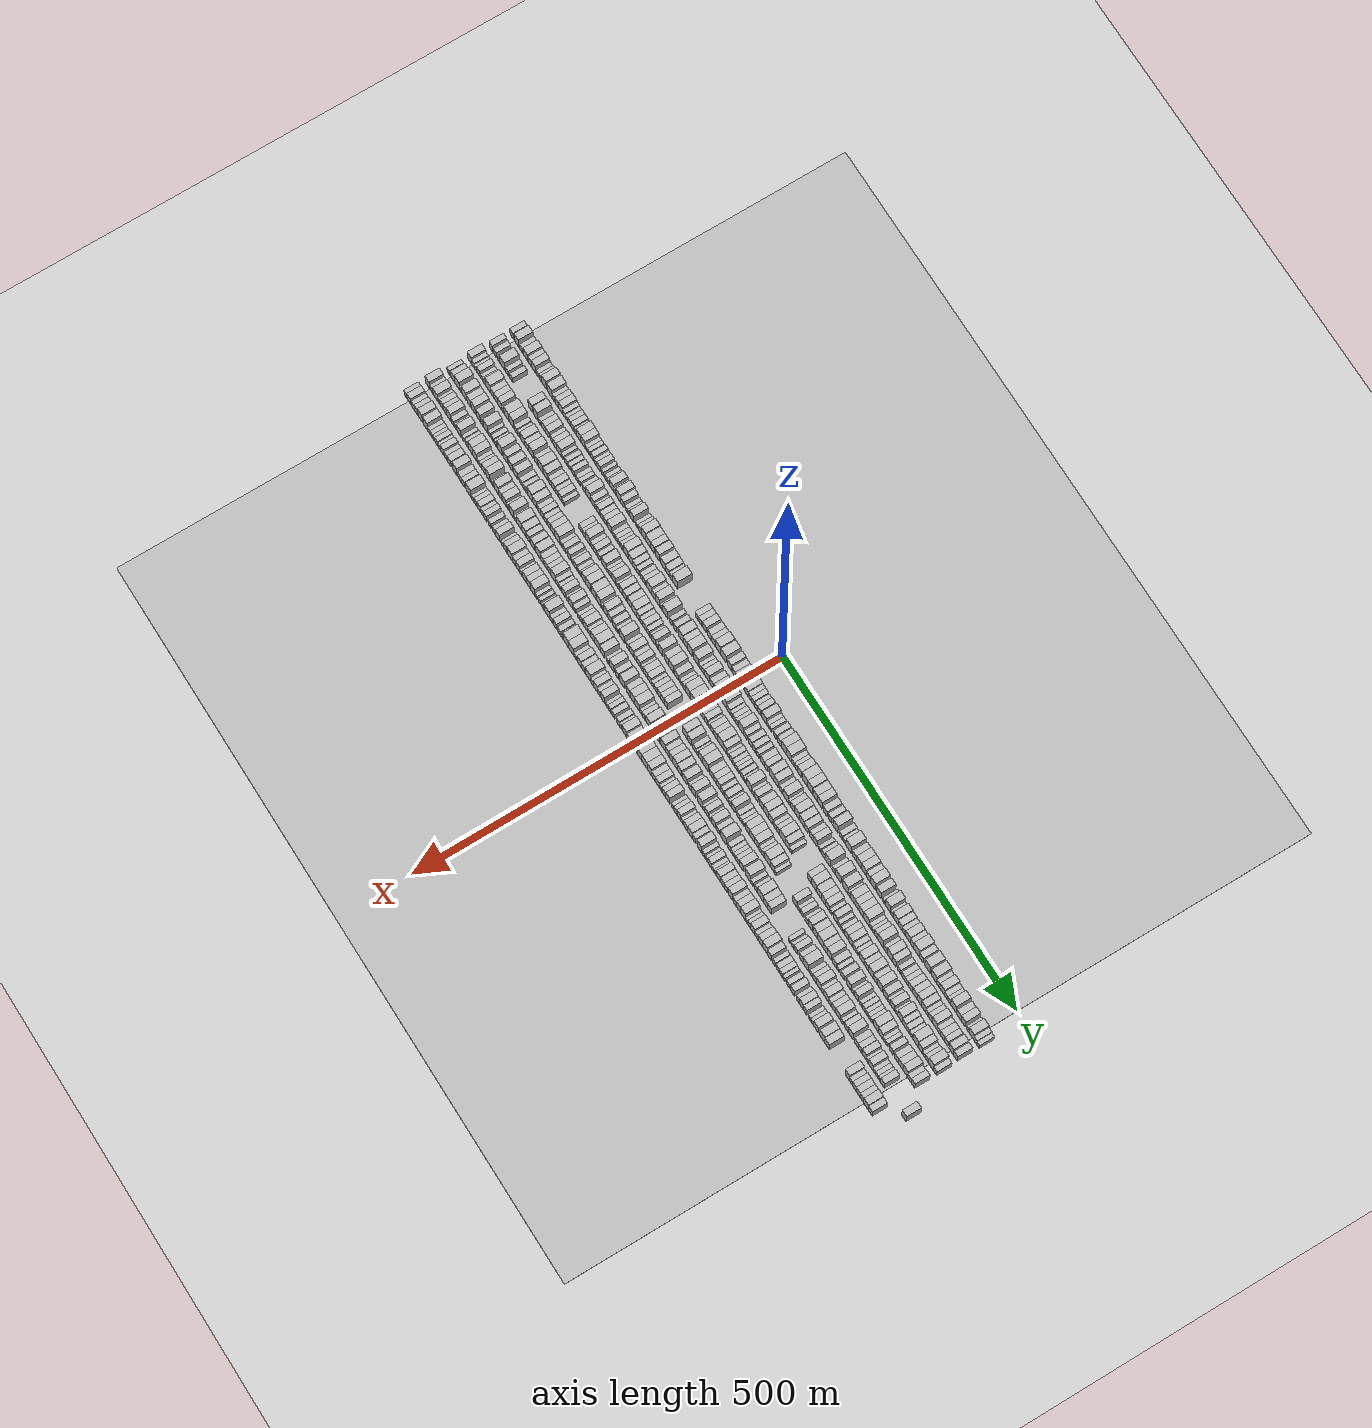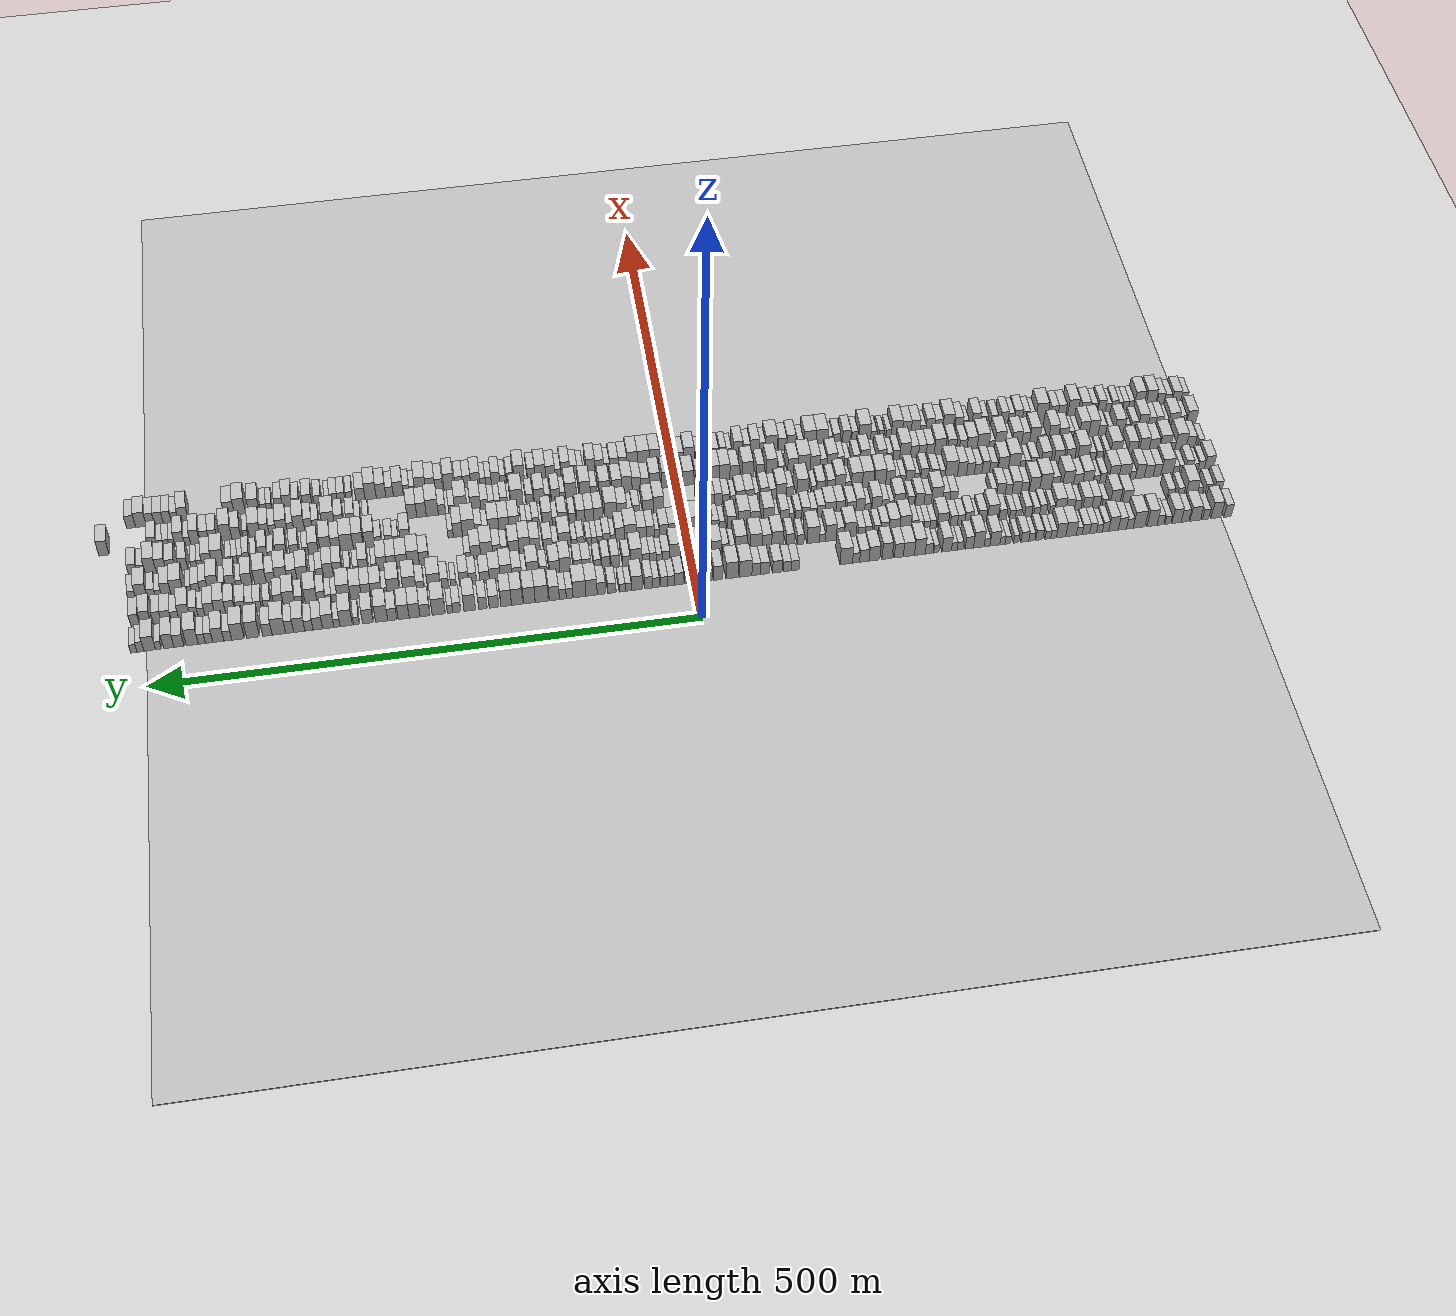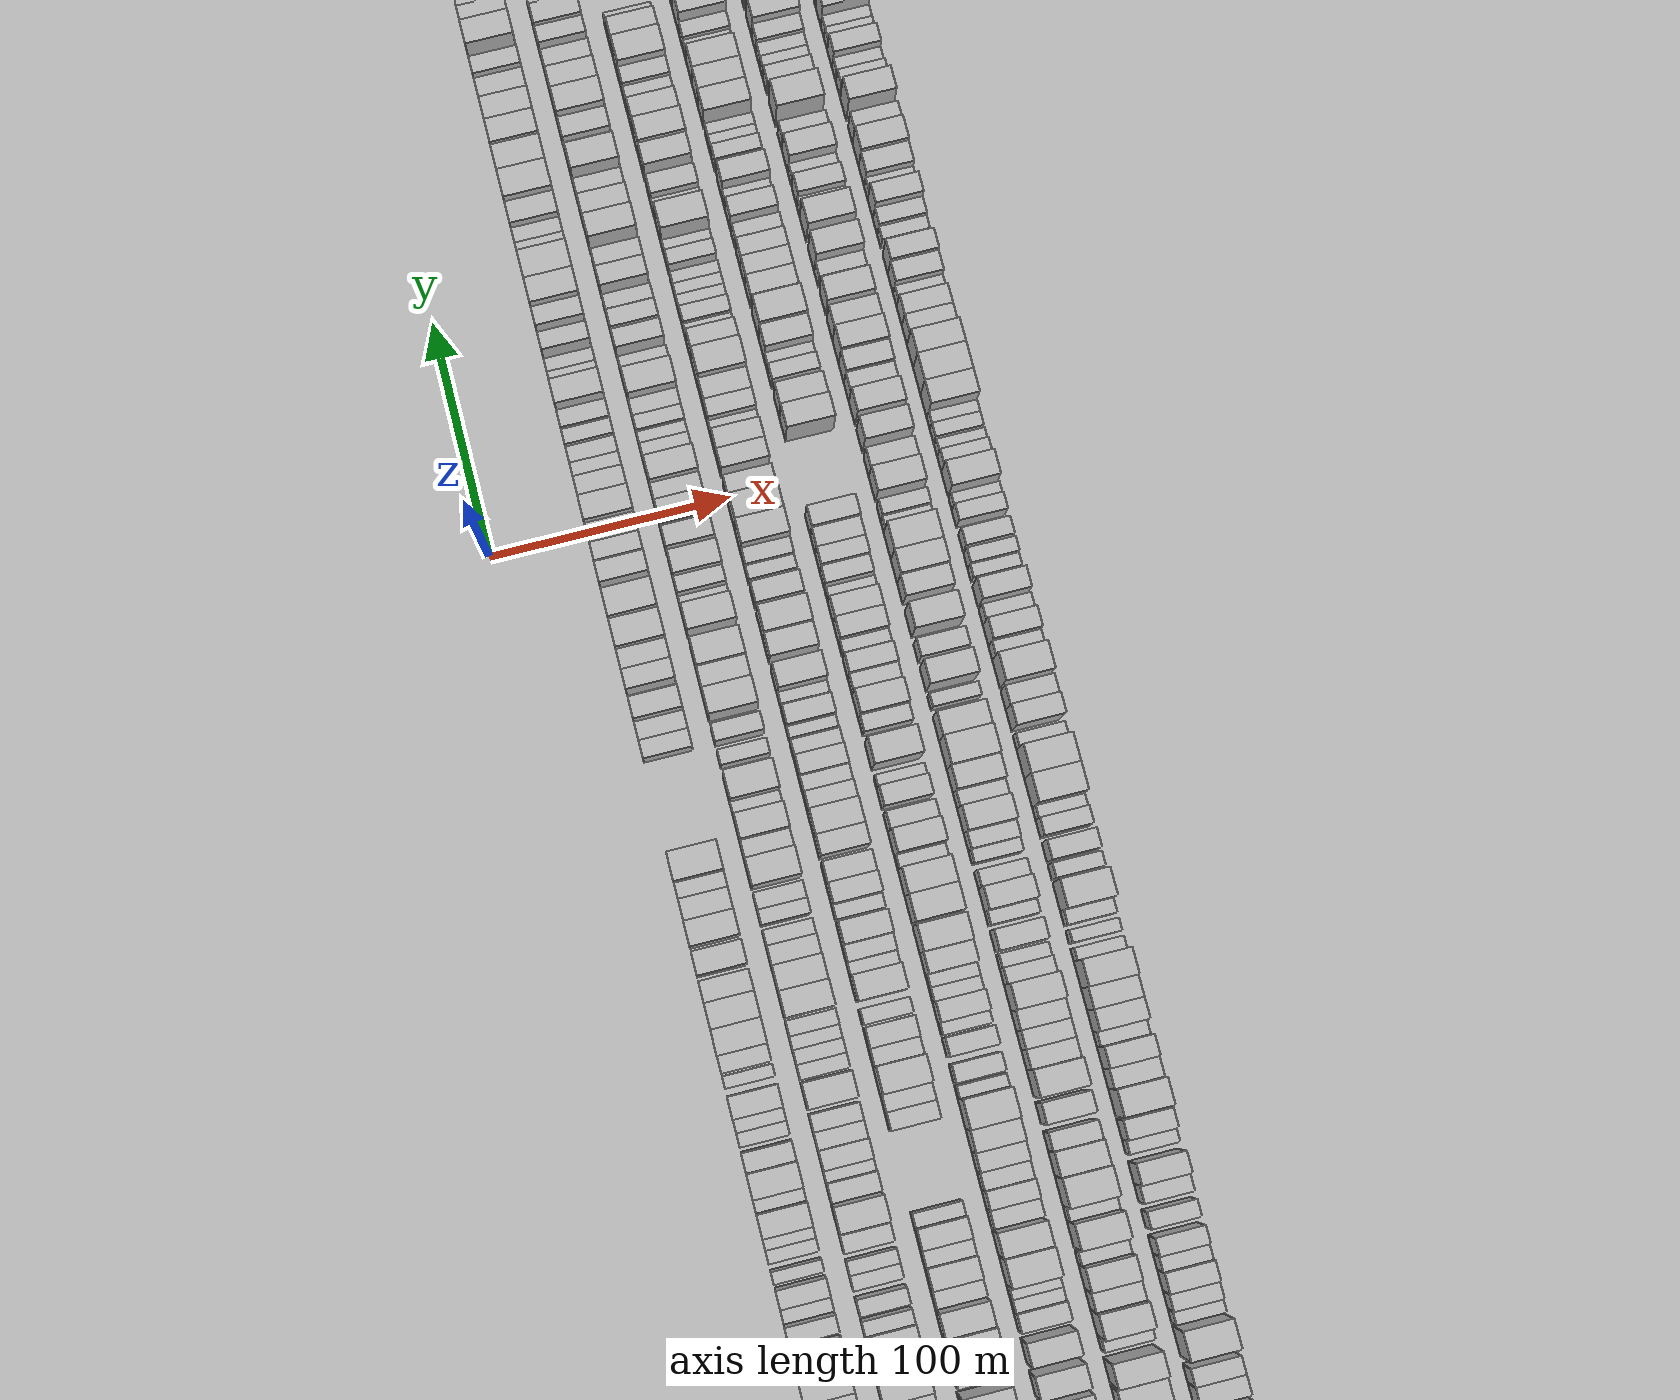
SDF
<?xml version="1.0" encoding="utf-8"?>

<sdf version="1.6">

   <world name="default">

      <gui fullscreen="0">

         <camera name="user_camera">

            <pose>-15 0 4.57585 0 0 0</pose>

            <view_controller>orbit</view_controller>

         </camera>

      </gui>

      <scene>

         <sky>

           <clouds>

             <speed>12</speed>

           </clouds>

         </sky>

         <ambient>0.4 0.4 0.4 1</ambient>

         <background>0.7 0.7 0.7 1</background>

         <shadows>1</shadows>

      </scene>

      <gravity>0 0 -9.8066</gravity>

      <magnetic_field>6e-06 2.3e-05 -4.2e-05</magnetic_field>

      <physics default="0" name="default_physics" type="ode">

         <ode>

            <solver>

               <type>quick</type>

               <iters>10</iters>

               <sor>1.0</sor>

               <use_dynamic_moi_rescaling>0</use_dynamic_moi_rescaling>

            </solver>

            <constraints>

               <cfm>0</cfm>

               <erp>0.2</erp>

               <contact_max_correcting_vel>100</contact_max_correcting_vel>

               <contact_surface_layer>0.001</contact_surface_layer>

            </constraints>

         </ode>

         <max_step_size>0.004</max_step_size>

         <real_time_factor>1</real_time_factor>

         <real_time_update_rate>250</real_time_update_rate>

      </physics>

      <light name="sun" type="directional">

         <cast_shadows>1</cast_shadows>

         <pose>0 0 10 0 0 0</pose>

         <diffuse>0.8 0.8 0.8 1</diffuse>

         <specular>0.2 0.2 0.2 1</specular>

         <attenuation>

            <range>1000</range>

            <constant>0.9</constant>

            <linear>0.01</linear>

            <quadratic>0.001</quadratic>

         </attenuation>

         <direction>-0.5 0.1 -0.9</direction>

      </light>

      <include>

         <name>ground_plane_1</name>

         <uri>model://HANNAS_ground_plane</uri>

         <pose>0 0 0  0 0 0</pose>

      </include>

      <include>

         <name>ground_plane_2</name>

         <uri>model://HANNAS_ground_plane</uri>

         <pose>100 0 0  0 0 0</pose>

      </include>

      <model name="building_1">

         <static>1</static>

         <pose frame="">50.0000 -506.3268 0 0.000000 0.000000 0.000000</pose>

         <link name="link">

            <pose frame="">0 0 9.00 0 0 0</pose>

            <collision name="collision">

               <geometry>

                  <box>

                     <size>20.0000 7.3464 18.0000</size>

                  </box>

               </geometry>

               <max_contacts>10</max_contacts>

               <surface>

                  <contact>

                     <ode/>

                  </contact>

                  <bounce/>

                  <friction>

                     <torsional>

                        <ode/>

                     </torsional>

                     <ode/>

                  </friction>

               </surface>

            </collision>

            <visual name="visual">

               <cast_shadows>0</cast_shadows>

               <geometry>

                  <box>

                     <size>20.0000 7.3464 18.0000</size>

                  </box>

               </geometry>

               <material>

                  <script>

                     <uri>model://HANNAS_wall/materials/scripts</uri>

                     <uri>model://HANNAS_wall/materials/textures</uri>

                     <name>vrc/HANNAS_wall</name>

                  </script>

               </material>

            </visual>

            <self_collide>0</self_collide>

            <enable_wind>0</enable_wind>

            <kinematic>0</kinematic>

         </link>

      </model>

      <model name="building_2">

         <static>1</static>

         <pose frame="">50.0000 -494.8305 0 0.000000 0.000000 0.000000</pose>

         <link name="link">

            <pose frame="">0 0 12.00 0 0 0</pose>

            <collision name="collision">

               <geometry>

                  <box>

                     <size>20.0000 9.6461 24.0000</size>

                  </box>

               </geometry>

               <max_contacts>10</max_contacts>

               <surface>

                  <contact>

                     <ode/>

                  </contact>

                  <bounce/>

                  <friction>

                     <torsional>

                        <ode/>

                     </torsional>

                     <ode/>

                  </friction>

               </surface>

            </collision>

            <visual name="visual">

               <cast_shadows>0</cast_shadows>

               <geometry>

                  <box>

                     <size>20.0000 9.6461 24.0000</size>

                  </box>

               </geometry>

               <material>

                  <script>

                     <uri>model://HANNAS_wall/materials/scripts</uri>

                     <uri>model://HANNAS_wall/materials/textures</uri>

                     <name>vrc/HANNAS_wall</name>

                  </script>

               </material>

            </visual>

            <self_collide>0</self_collide>

            <enable_wind>0</enable_wind>

            <kinematic>0</kinematic>

         </link>

      </model>

      <model name="building_3">

         <static>1</static>

         <pose frame="">50.0000 -484.8706 0 0.000000 0.000000 0.000000</pose>

         <link name="link">

            <pose frame="">0 0 7.50 0 0 0</pose>

            <collision name="collision">

               <geometry>

                  <box>

                     <size>20.0000 6.2738 15.0000</size>

                  </box>

               </geometry>

               <max_contacts>10</max_contacts>

               <surface>

                  <contact>

                     <ode/>

                  </contact>

                  <bounce/>

                  <friction>

                     <torsional>

                        <ode/>

                     </torsional>

                     <ode/>

                  </friction>

               </surface>

            </collision>

            <visual name="visual">

               <cast_shadows>0</cast_shadows>

               <geometry>

                  <box>

                     <size>20.0000 6.2738 15.0000</size>

                  </box>

               </geometry>

               <material>

                  <script>

                     <uri>model://HANNAS_wall/materials/scripts</uri>

                     <uri>model://HANNAS_wall/materials/textures</uri>

                     <name>vrc/HANNAS_wall</name>

                  </script>

               </material>

            </visual>

            <self_collide>0</self_collide>

            <enable_wind>0</enable_wind>

            <kinematic>0</kinematic>

         </link>

      </model>

      <model name="building_4">

         <static>1</static>

         <pose frame="">50.0000 -474.6701 0 0.000000 0.000000 0.000000</pose>

         <link name="link">

            <pose frame="">0 0 10.50 0 0 0</pose>

            <collision name="collision">

               <geometry>

                  <box>

                     <size>20.0000 10.1271 21.0000</size>

                  </box>

               </geometry>

               <max_contacts>10</max_contacts>

               <surface>

                  <contact>

                     <ode/>

                  </contact>

                  <bounce/>

                  <friction>

                     <torsional>

                        <ode/>

                     </torsional>

                     <ode/>

                  </friction>

               </surface>

            </collision>

            <visual name="visual">

               <cast_shadows>0</cast_shadows>

               <geometry>

                  <box>

                     <size>20.0000 10.1271 21.0000</size>

                  </box>

               </geometry>

               <material>

                  <script>

                     <uri>model://HANNAS_wall/materials/scripts</uri>

                     <uri>model://HANNAS_wall/materials/textures</uri>

                     <name>vrc/HANNAS_wall</name>

                  </script>

               </material>

            </visual>

            <self_collide>0</self_collide>

            <enable_wind>0</enable_wind>

            <kinematic>0</kinematic>

         </link>

      </model>

      <model name="building_5">

         <static>1</static>

         <pose frame="">50.0000 -464.8590 0 0.000000 0.000000 0.000000</pose>

         <link name="link">

            <pose frame="">0 0 9.00 0 0 0</pose>

            <collision name="collision">

               <geometry>

                  <box>

                     <size>20.0000 7.4952 18.0000</size>

                  </box>

               </geometry>

               <max_contacts>10</max_contacts>

               <surface>

                  <contact>

                     <ode/>

                  </contact>

                  <bounce/>

                  <friction>

                     <torsional>

                        <ode/>

                     </torsional>

                     <ode/>

                  </friction>

               </surface>

            </collision>

            <visual name="visual">

               <cast_shadows>0</cast_shadows>

               <geometry>

                  <box>

                     <size>20.0000 7.4952 18.0000</size>

                  </box>

               </geometry>

               <material>

                  <script>

                     <uri>model://HANNAS_wall/materials/scripts</uri>

                     <uri>model://HANNAS_wall/materials/textures</uri>

                     <name>vrc/HANNAS_wall</name>

                  </script>

               </material>

            </visual>

            <self_collide>0</self_collide>

            <enable_wind>0</enable_wind>

            <kinematic>0</kinematic>

         </link>

      </model>

      <model name="building_6">

         <static>1</static>

         <pose frame="">50.0000 -456.5824 0 0.000000 0.000000 0.000000</pose>

         <link name="link">

            <pose frame="">0 0 10.50 0 0 0</pose>

            <collision name="collision">

               <geometry>

                  <box>

                     <size>20.0000 9.0579 21.0000</size>

                  </box>

               </geometry>

               <max_contacts>10</max_contacts>

               <surface>

                  <contact>

                     <ode/>

                  </contact>

                  <bounce/>

                  <friction>

                     <torsional>

                        <ode/>

                     </torsional>

                     <ode/>

                  </friction>

               </surface>

            </collision>

            <visual name="visual">

               <cast_shadows>0</cast_shadows>

               <geometry>

                  <box>

                     <size>20.0000 9.0579 21.0000</size>

                  </box>

               </geometry>

               <material>

                  <script>

                     <uri>model://HANNAS_wall/materials/scripts</uri>

                     <uri>model://HANNAS_wall/materials/textures</uri>

                     <name>vrc/HANNAS_wall</name>

                  </script>

               </material>

            </visual>

            <self_collide>0</self_collide>

            <enable_wind>0</enable_wind>

            <kinematic>0</kinematic>

         </link>

      </model>

      <model name="building_7">

         <static>1</static>

         <pose frame="">50.0000 -448.1775 0 0.000000 0.000000 0.000000</pose>

         <link name="link">

            <pose frame="">0 0 6.00 0 0 0</pose>

            <collision name="collision">

               <geometry>

                  <box>

                     <size>20.0000 5.7519 12.0000</size>

                  </box>

               </geometry>

               <max_contacts>10</max_contacts>

               <surface>

                  <contact>

                     <ode/>

                  </contact>

                  <bounce/>

                  <friction>

                     <torsional>

                        <ode/>

                     </torsional>

                     <ode/>

                  </friction>

               </surface>

            </collision>

            <visual name="visual">

               <cast_shadows>0</cast_shadows>

               <geometry>

                  <box>

                     <size>20.0000 5.7519 12.0000</size>

                  </box>

               </geometry>

               <material>

                  <script>

                     <uri>model://HANNAS_wall/materials/scripts</uri>

                     <uri>model://HANNAS_wall/materials/textures</uri>

                     <name>vrc/HANNAS_wall</name>

                  </script>

               </material>

            </visual>

            <self_collide>0</self_collide>

            <enable_wind>0</enable_wind>

            <kinematic>0</kinematic>

         </link>

      </model>

      <model name="building_8">

         <static>1</static>

         <pose frame="">50.0000 -441.0322 0 0.000000 0.000000 0.000000</pose>

         <link name="link">

            <pose frame="">0 0 7.50 0 0 0</pose>

            <collision name="collision">

               <geometry>

                  <box>

                     <size>20.0000 6.5389 15.0000</size>

                  </box>

               </geometry>

               <max_contacts>10</max_contacts>

               <surface>

                  <contact>

                     <ode/>

                  </contact>

                  <bounce/>

                  <friction>

                     <torsional>

                        <ode/>

                     </torsional>

                     <ode/>

                  </friction>

               </surface>

            </collision>

            <visual name="visual">

               <cast_shadows>0</cast_shadows>

               <geometry>

                  <box>

                     <size>20.0000 6.5389 15.0000</size>

                  </box>

               </geometry>

               <material>

                  <script>

                     <uri>model://HANNAS_wall/materials/scripts</uri>

                     <uri>model://HANNAS_wall/materials/textures</uri>

                     <name>vrc/HANNAS_wall</name>

                  </script>

               </material>

            </visual>

            <self_collide>0</self_collide>

            <enable_wind>0</enable_wind>

            <kinematic>0</kinematic>

         </link>

      </model>

      <model name="building_9">

         <static>1</static>

         <pose frame="">50.0000 -432.8886 0 0.000000 0.000000 0.000000</pose>

         <link name="link">

            <pose frame="">0 0 12.00 0 0 0</pose>

            <collision name="collision">

               <geometry>

                  <box>

                     <size>20.0000 9.7483 24.0000</size>

                  </box>

               </geometry>

               <max_contacts>10</max_contacts>

               <surface>

                  <contact>

                     <ode/>

                  </contact>

                  <bounce/>

                  <friction>

                     <torsional>

                        <ode/>

                     </torsional>

                     <ode/>

                  </friction>

               </surface>

            </collision>

            <visual name="visual">

               <cast_shadows>0</cast_shadows>

               <geometry>

                  <box>

                     <size>20.0000 9.7483 24.0000</size>

                  </box>

               </geometry>

               <material>

                  <script>

                     <uri>model://HANNAS_wall/materials/scripts</uri>

                     <uri>model://HANNAS_wall/materials/textures</uri>

                     <name>vrc/HANNAS_wall</name>

                  </script>

               </material>

            </visual>

            <self_collide>0</self_collide>

            <enable_wind>0</enable_wind>

            <kinematic>0</kinematic>

         </link>

      </model>

      <model name="building_10">

         <static>1</static>

         <pose frame="">50.0000 -420.2795 0 0.000000 0.000000 0.000000</pose>

         <link name="link">

            <pose frame="">0 0 12.00 0 0 0</pose>

            <collision name="collision">

               <geometry>

                  <box>

                     <size>20.0000 11.4699 24.0000</size>

                  </box>

               </geometry>

               <max_contacts>10</max_contacts>

               <surface>

                  <contact>

                     <ode/>

                  </contact>

                  <bounce/>

                  <friction>

                     <torsional>

                        <ode/>

                     </torsional>

                     <ode/>

                  </friction>

               </surface>

            </collision>

            <visual name="visual">

               <cast_shadows>0</cast_shadows>

               <geometry>

                  <box>

                     <size>20.0000 11.4699 24.0000</size>

                  </box>

               </geometry>

               <material>

                  <script>

                     <uri>model://HANNAS_wall/materials/scripts</uri>

                     <uri>model://HANNAS_wall/materials/textures</uri>

                     <name>vrc/HANNAS_wall</name>

                  </script>

               </material>

            </visual>

            <self_collide>0</self_collide>

            <enable_wind>0</enable_wind>

            <kinematic>0</kinematic>

         </link>

      </model>

      <model name="building_11">

         <static>1</static>

         <pose frame="">50.0000 -411.3486 0 0.000000 0.000000 0.000000</pose>

         <link name="link">

            <pose frame="">0 0 7.50 0 0 0</pose>

            <collision name="collision">

               <geometry>

                  <box>

                     <size>20.0000 6.3918 15.0000</size>

                  </box>

               </geometry>

               <max_contacts>10</max_contacts>

               <surface>

                  <contact>

                     <ode/>

                  </contact>

                  <bounce/>

                  <friction>

                     <torsional>

                        <ode/>

                     </torsional>

                     <ode/>

                  </friction>

               </surface>

            </collision>

            <visual name="visual">

               <cast_shadows>0</cast_shadows>

               <geometry>

                  <box>

                     <size>20.0000 6.3918 15.0000</size>

                  </box>

               </geometry>

               <material>

                  <script>

                     <uri>model://HANNAS_wall/materials/scripts</uri>

                     <uri>model://HANNAS_wall/materials/textures</uri>

                     <name>vrc/HANNAS_wall</name>

                  </script>

               </material>

            </visual>

            <self_collide>0</self_collide>

            <enable_wind>0</enable_wind>

            <kinematic>0</kinematic>

         </link>

      </model>

      <model name="building_12">

         <static>1</static>

         <pose frame="">50.0000 -404.1305 0 0.000000 0.000000 0.000000</pose>

         <link name="link">

            <pose frame="">0 0 9.00 0 0 0</pose>

            <collision name="collision">

               <geometry>

                  <box>

                     <size>20.0000 8.0444 18.0000</size>

                  </box>

               </geometry>

               <max_contacts>10</max_contacts>

               <surface>

                  <contact>

                     <ode/>

                  </contact>

                  <bounce/>

                  <friction>

                     <torsional>

                        <ode/>

                     </torsional>

                     <ode/>

                  </friction>

               </surface>

            </collision>

            <visual name="visual">

               <cast_shadows>0</cast_shadows>

               <geometry>

                  <box>

                     <size>20.0000 8.0444 18.0000</size>

                  </box>

               </geometry>

               <material>

                  <script>

                     <uri>model://HANNAS_wall/materials/scripts</uri>

                     <uri>model://HANNAS_wall/materials/textures</uri>

                     <name>vrc/HANNAS_wall</name>

                  </script>

               </material>

            </visual>

            <self_collide>0</self_collide>

            <enable_wind>0</enable_wind>

            <kinematic>0</kinematic>

         </link>

      </model>

      <model name="building_13">

         <static>1</static>

         <pose frame="">50.0000 -395.5636 0 0.000000 0.000000 0.000000</pose>

         <link name="link">

            <pose frame="">0 0 10.50 0 0 0</pose>

            <collision name="collision">

               <geometry>

                  <box>

                     <size>20.0000 9.0895 21.0000</size>

                  </box>

               </geometry>

               <max_contacts>10</max_contacts>

               <surface>

                  <contact>

                     <ode/>

                  </contact>

                  <bounce/>

                  <friction>

                     <torsional>

                        <ode/>

                     </torsional>

                     <ode/>

                  </friction>

               </surface>

            </collision>

            <visual name="visual">

               <cast_shadows>0</cast_shadows>

               <geometry>

                  <box>

                     <size>20.0000 9.0895 21.0000</size>

                  </box>

               </geometry>

               <material>

                  <script>

                     <uri>model://HANNAS_wall/materials/scripts</uri>

                     <uri>model://HANNAS_wall/materials/textures</uri>

                     <name>vrc/HANNAS_wall</name>

                  </script>

               </material>

            </visual>

            <self_collide>0</self_collide>

            <enable_wind>0</enable_wind>

            <kinematic>0</kinematic>

         </link>

      </model>

      <model name="building_14">

         <static>1</static>

         <pose frame="">50.0000 -387.9882 0 0.000000 0.000000 0.000000</pose>

         <link name="link">

            <pose frame="">0 0 7.50 0 0 0</pose>

            <collision name="collision">

               <geometry>

                  <box>

                     <size>20.0000 6.0613 15.0000</size>

                  </box>

               </geometry>

               <max_contacts>10</max_contacts>

               <surface>

                  <contact>

                     <ode/>

                  </contact>

                  <bounce/>

                  <friction>

                     <torsional>

                        <ode/>

                     </torsional>

                     <ode/>

                  </friction>

               </surface>

            </collision>

            <visual name="visual">

               <cast_shadows>0</cast_shadows>

               <geometry>

                  <box>

                     <size>20.0000 6.0613 15.0000</size>

                  </box>

               </geometry>

               <material>

                  <script>

                     <uri>model://HANNAS_wall/materials/scripts</uri>

                     <uri>model://HANNAS_wall/materials/textures</uri>

                     <name>vrc/HANNAS_wall</name>

                  </script>

               </material>

            </visual>

            <self_collide>0</self_collide>

            <enable_wind>0</enable_wind>

            <kinematic>0</kinematic>

         </link>

      </model>

      <model name="building_15">

         <static>1</static>

         <pose frame="">50.0000 -382.0741 0 0.000000 0.000000 0.000000</pose>

         <link name="link">

            <pose frame="">0 0 6.00 0 0 0</pose>

            <collision name="collision">

               <geometry>

                  <box>

                     <size>20.0000 5.7669 12.0000</size>

                  </box>

               </geometry>

               <max_contacts>10</max_contacts>

               <surface>

                  <contact>

                     <ode/>

                  </contact>

                  <bounce/>

                  <friction>

                     <torsional>

                        <ode/>

                     </torsional>

                     <ode/>

                  </friction>

               </surface>

            </collision>

            <visual name="visual">

               <cast_shadows>0</cast_shadows>

               <geometry>

                  <box>

                     <size>20.0000 5.7669 12.0000</size>

                  </box>

               </geometry>

               <material>

                  <script>

                     <uri>model://HANNAS_wall/materials/scripts</uri>

                     <uri>model://HANNAS_wall/materials/textures</uri>

                     <name>vrc/HANNAS_wall</name>

                  </script>

               </material>

            </visual>

            <self_collide>0</self_collide>

            <enable_wind>0</enable_wind>

            <kinematic>0</kinematic>

         </link>

      </model>

      <model name="building_16">

         <static>1</static>

         <pose frame="">50.0000 -375.9104 0 0.000000 0.000000 0.000000</pose>

         <link name="link">

            <pose frame="">0 0 7.50 0 0 0</pose>

            <collision name="collision">

               <geometry>

                  <box>

                     <size>20.0000 6.5604 15.0000</size>

                  </box>

               </geometry>

               <max_contacts>10</max_contacts>

               <surface>

                  <contact>

                     <ode/>

                  </contact>

                  <bounce/>

                  <friction>

                     <torsional>

                        <ode/>

                     </torsional>

                     <ode/>

                  </friction>

               </surface>

            </collision>

            <visual name="visual">

               <cast_shadows>0</cast_shadows>

               <geometry>

                  <box>

                     <size>20.0000 6.5604 15.0000</size>

                  </box>

               </geometry>

               <material>

                  <script>

                     <uri>model://HANNAS_wall/materials/scripts</uri>

                     <uri>model://HANNAS_wall/materials/textures</uri>

                     <name>vrc/HANNAS_wall</name>

                  </script>

               </material>

            </visual>

            <self_collide>0</self_collide>

            <enable_wind>0</enable_wind>

            <kinematic>0</kinematic>

         </link>

      </model>

      <model name="building_17">

         <static>1</static>

         <pose frame="">50.0000 -369.0425 0 0.000000 0.000000 0.000000</pose>

         <link name="link">

            <pose frame="">0 0 7.50 0 0 0</pose>

            <collision name="collision">

               <geometry>

                  <box>

                     <size>20.0000 7.1755 15.0000</size>

                  </box>

               </geometry>

               <max_contacts>10</max_contacts>

               <surface>

                  <contact>

                     <ode/>

                  </contact>

                  <bounce/>

                  <friction>

                     <torsional>

                        <ode/>

                     </torsional>

                     <ode/>

                  </friction>

               </surface>

            </collision>

            <visual name="visual">

               <cast_shadows>0</cast_shadows>

               <geometry>

                  <box>

                     <size>20.0000 7.1755 15.0000</size>

                  </box>

               </geometry>

               <material>

                  <script>

                     <uri>model://HANNAS_wall/materials/scripts</uri>

                     <uri>model://HANNAS_wall/materials/textures</uri>

                     <name>vrc/HANNAS_wall</name>

                  </script>

               </material>

            </visual>

            <self_collide>0</self_collide>

            <enable_wind>0</enable_wind>

            <kinematic>0</kinematic>

         </link>

      </model>

      <model name="building_18">

         <static>1</static>

         <pose frame="">50.0000 -362.6450 0 0.000000 0.000000 0.000000</pose>

         <link name="link">

            <pose frame="">0 0 6.00 0 0 0</pose>

            <collision name="collision">

               <geometry>

                  <box>

                     <size>20.0000 5.6195 12.0000</size>

                  </box>

               </geometry>

               <max_contacts>10</max_contacts>

               <surface>

                  <contact>

                     <ode/>

                  </contact>

                  <bounce/>

                  <friction>

                     <torsional>

                        <ode/>

                     </torsional>

                     <ode/>

                  </friction>

               </surface>

            </collision>

            <visual name="visual">

               <cast_shadows>0</cast_shadows>

               <geometry>

                  <box>

                     <size>20.0000 5.6195 12.0000</size>

                  </box>

               </geometry>

               <material>

                  <script>

                     <uri>model://HANNAS_wall/materials/scripts</uri>

                     <uri>model://HANNAS_wall/materials/textures</uri>

                     <name>vrc/HANNAS_wall</name>

                  </script>

               </material>

            </visual>

            <self_collide>0</self_collide>

            <enable_wind>0</enable_wind>

            <kinematic>0</kinematic>

         </link>

      </model>

      <model name="building_19">

         <static>1</static>

         <pose frame="">50.0000 -354.7510 0 0.000000 0.000000 0.000000</pose>

         <link name="link">

            <pose frame="">0 0 10.50 0 0 0</pose>

            <collision name="collision">

               <geometry>

                  <box>

                     <size>20.0000 10.1686 21.0000</size>

                  </box>

               </geometry>

               <max_contacts>10</max_contacts>

               <surface>

                  <contact>

                     <ode/>

                  </contact>

                  <bounce/>

                  <friction>

                     <torsional>

                        <ode/>

                     </torsional>

                     <ode/>

                  </friction>

               </surface>

            </collision>

            <visual name="visual">

               <cast_shadows>0</cast_shadows>

               <geometry>

                  <box>

                     <size>20.0000 10.1686 21.0000</size>

                  </box>

               </geometry>

               <material>

                  <script>

                     <uri>model://HANNAS_wall/materials/scripts</uri>

                     <uri>model://HANNAS_wall/materials/textures</uri>

                     <name>vrc/HANNAS_wall</name>

                  </script>

               </material>

            </visual>

            <self_collide>0</self_collide>

            <enable_wind>0</enable_wind>

            <kinematic>0</kinematic>

         </link>

      </model>

      <model name="building_20">

         <static>1</static>

         <pose frame="">50.0000 -345.1235 0 0.000000 0.000000 0.000000</pose>

         <link name="link">

            <pose frame="">0 0 10.50 0 0 0</pose>

            <collision name="collision">

               <geometry>

                  <box>

                     <size>20.0000 9.0865 21.0000</size>

                  </box>

               </geometry>

               <max_contacts>10</max_contacts>

               <surface>

                  <contact>

                     <ode/>

                  </contact>

                  <bounce/>

                  <friction>

                     <torsional>

                        <ode/>

                     </torsional>

                     <ode/>

                  </friction>

               </surface>

            </collision>

            <visual name="visual">

               <cast_shadows>0</cast_shadows>

               <geometry>

                  <box>

                     <size>20.0000 9.0865 21.0000</size>

                  </box>

               </geometry>

               <material>

                  <script>

                     <uri>model://HANNAS_wall/materials/scripts</uri>

                     <uri>model://HANNAS_wall/materials/textures</uri>

                     <name>vrc/HANNAS_wall</name>

                  </script>

               </material>

            </visual>

            <self_collide>0</self_collide>

            <enable_wind>0</enable_wind>

            <kinematic>0</kinematic>

         </link>

      </model>

      <model name="building_21">

         <static>1</static>

         <pose frame="">50.0000 -337.9121 0 0.000000 0.000000 0.000000</pose>

         <link name="link">

            <pose frame="">0 0 6.00 0 0 0</pose>

            <collision name="collision">

               <geometry>

                  <box>

                     <size>20.0000 5.3363 12.0000</size>

                  </box>

               </geometry>

               <max_contacts>10</max_contacts>

               <surface>

                  <contact>

                     <ode/>

                  </contact>

                  <bounce/>

                  <friction>

                     <torsional>

                        <ode/>

                     </torsional>

                     <ode/>

                  </friction>

               </surface>

            </collision>

            <visual name="visual">

               <cast_shadows>0</cast_shadows>

               <geometry>

                  <box>

                     <size>20.0000 5.3363 12.0000</size>

                  </box>

               </geometry>

               <material>

                  <script>

                     <uri>model://HANNAS_wall/materials/scripts</uri>

                     <uri>model://HANNAS_wall/materials/textures</uri>

                     <name>vrc/HANNAS_wall</name>

                  </script>

               </material>

            </visual>

            <self_collide>0</self_collide>

            <enable_wind>0</enable_wind>

            <kinematic>0</kinematic>

         </link>

      </model>

      <model name="building_22">

         <static>1</static>

         <pose frame="">50.0000 -332.4888 0 0.000000 0.000000 0.000000</pose>

         <link name="link">

            <pose frame="">0 0 6.00 0 0 0</pose>

            <collision name="collision">

               <geometry>

                  <box>

                     <size>20.0000 5.5102 12.0000</size>

                  </box>

               </geometry>

               <max_contacts>10</max_contacts>

               <surface>

                  <contact>

                     <ode/>

                  </contact>

                  <bounce/>

                  <friction>

                     <torsional>

                        <ode/>

                     </torsional>

                     <ode/>

                  </friction>

               </surface>

            </collision>

            <visual name="visual">

               <cast_shadows>0</cast_shadows>

               <geometry>

                  <box>

                     <size>20.0000 5.5102 12.0000</size>

                  </box>

               </geometry>

               <material>

                  <script>

                     <uri>model://HANNAS_wall/materials/scripts</uri>

                     <uri>model://HANNAS_wall/materials/textures</uri>

                     <name>vrc/HANNAS_wall</name>

                  </script>

               </material>

            </visual>

            <self_collide>0</self_collide>

            <enable_wind>0</enable_wind>

            <kinematic>0</kinematic>

         </link>

      </model>

      <model name="building_23">

         <static>1</static>

         <pose frame="">50.0000 -324.2608 0 0.000000 0.000000 0.000000</pose>

         <link name="link">

            <pose frame="">0 0 7.50 0 0 0</pose>

            <collision name="collision">

               <geometry>

                  <box>

                     <size>20.0000 6.9459 15.0000</size>

                  </box>

               </geometry>

               <max_contacts>10</max_contacts>

               <surface>

                  <contact>

                     <ode/>

                  </contact>

                  <bounce/>

                  <friction>

                     <torsional>

                        <ode/>

                     </torsional>

                     <ode/>

                  </friction>

               </surface>

            </collision>

            <visual name="visual">

               <cast_shadows>0</cast_shadows>

               <geometry>

                  <box>

                     <size>20.0000 6.9459 15.0000</size>

                  </box>

               </geometry>

               <material>

                  <script>

                     <uri>model://HANNAS_wall/materials/scripts</uri>

                     <uri>model://HANNAS_wall/materials/textures</uri>

                     <name>vrc/HANNAS_wall</name>

                  </script>

               </material>

            </visual>

            <self_collide>0</self_collide>

            <enable_wind>0</enable_wind>

            <kinematic>0</kinematic>

         </link>

      </model>

      <model name="building_24">

         <static>1</static>

         <pose frame="">50.0000 -316.9308 0 0.000000 0.000000 0.000000</pose>

         <link name="link">

            <pose frame="">0 0 6.00 0 0 0</pose>

            <collision name="collision">

               <geometry>

                  <box>

                     <size>20.0000 5.7139 12.0000</size>

                  </box>

               </geometry>

               <max_contacts>10</max_contacts>

               <surface>

                  <contact>

                     <ode/>

                  </contact>

                  <bounce/>

                  <friction>

                     <torsional>

                        <ode/>

                     </torsional>

                     <ode/>

                  </friction>

               </surface>

            </collision>

            <visual name="visual">

               <cast_shadows>0</cast_shadows>

               <geometry>

                  <box>

                     <size>20.0000 5.7139 12.0000</size>

                  </box>

               </geometry>

               <material>

                  <script>

                     <uri>model://HANNAS_wall/materials/scripts</uri>

                     <uri>model://HANNAS_wall/materials/textures</uri>

                     <name>vrc/HANNAS_wall</name>

                  </script>

               </material>

            </visual>

            <self_collide>0</self_collide>

            <enable_wind>0</enable_wind>

            <kinematic>0</kinematic>

         </link>

      </model>

      <model name="building_25">

         <static>1</static>

         <pose frame="">50.0000 -310.3500 0 0.000000 0.000000 0.000000</pose>

         <link name="link">

            <pose frame="">0 0 7.50 0 0 0</pose>

            <collision name="collision">

               <geometry>

                  <box>

                     <size>20.0000 7.4477 15.0000</size>

                  </box>

               </geometry>

               <max_contacts>10</max_contacts>

               <surface>

                  <contact>

                     <ode/>

                  </contact>

                  <bounce/>

                  <friction>

                     <torsional>

                        <ode/>

                     </torsional>

                     <ode/>

                  </friction>

               </surface>

            </collision>

            <visual name="visual">

               <cast_shadows>0</cast_shadows>

               <geometry>

                  <box>

                     <size>20.0000 7.4477 15.0000</size>

                  </box>

               </geometry>

               <material>

                  <script>

                     <uri>model://HANNAS_wall/materials/scripts</uri>

                     <uri>model://HANNAS_wall/materials/textures</uri>

                     <name>vrc/HANNAS_wall</name>

                  </script>

               </material>

            </visual>

            <self_collide>0</self_collide>

            <enable_wind>0</enable_wind>

            <kinematic>0</kinematic>

         </link>

      </model>

      <model name="building_26">

         <static>1</static>

         <pose frame="">50.0000 -302.1518 0 0.000000 0.000000 0.000000</pose>

         <link name="link">

            <pose frame="">0 0 6.00 0 0 0</pose>

            <collision name="collision">

               <geometry>

                  <box>

                     <size>20.0000 4.9486 12.0000</size>

                  </box>

               </geometry>

               <max_contacts>10</max_contacts>

               <surface>

                  <contact>

                     <ode/>

                  </contact>

                  <bounce/>

                  <friction>

                     <torsional>

                        <ode/>

                     </torsional>

                     <ode/>

                  </friction>

               </surface>

            </collision>

            <visual name="visual">

               <cast_shadows>0</cast_shadows>

               <geometry>

                  <box>

                     <size>20.0000 4.9486 12.0000</size>

                  </box>

               </geometry>

               <material>

                  <script>

                     <uri>model://HANNAS_wall/materials/scripts</uri>

                     <uri>model://HANNAS_wall/materials/textures</uri>

                     <name>vrc/HANNAS_wall</name>

                  </script>

               </material>

            </visual>

            <self_collide>0</self_collide>

            <enable_wind>0</enable_wind>

            <kinematic>0</kinematic>

         </link>

      </model>

      <model name="building_27">

         <static>1</static>

         <pose frame="">50.0000 -294.0552 0 0.000000 0.000000 0.000000</pose>

         <link name="link">

            <pose frame="">0 0 6.00 0 0 0</pose>

            <collision name="collision">

               <geometry>

                  <box>

                     <size>20.0000 5.2446 12.0000</size>

                  </box>

               </geometry>

               <max_contacts>10</max_contacts>

               <surface>

                  <contact>

                     <ode/>

                  </contact>

                  <bounce/>

                  <friction>

                     <torsional>

                        <ode/>

                     </torsional>

                     <ode/>

                  </friction>

               </surface>

            </collision>

            <visual name="visual">

               <cast_shadows>0</cast_shadows>

               <geometry>

                  <box>

                     <size>20.0000 5.2446 12.0000</size>

                  </box>

               </geometry>

               <material>

                  <script>

                     <uri>model://HANNAS_wall/materials/scripts</uri>

                     <uri>model://HANNAS_wall/materials/textures</uri>

                     <name>vrc/HANNAS_wall</name>

                  </script>

               </material>

            </visual>

            <self_collide>0</self_collide>

            <enable_wind>0</enable_wind>

            <kinematic>0</kinematic>

         </link>

      </model>

      <model name="building_28">

         <static>1</static>

         <pose frame="">50.0000 -288.9779 0 0.000000 0.000000 0.000000</pose>

         <link name="link">

            <pose frame="">0 0 6.00 0 0 0</pose>

            <collision name="collision">

               <geometry>

                  <box>

                     <size>20.0000 4.9102 12.0000</size>

                  </box>

               </geometry>

               <max_contacts>10</max_contacts>

               <surface>

                  <contact>

                     <ode/>

                  </contact>

                  <bounce/>

                  <friction>

                     <torsional>

                        <ode/>

                     </torsional>

                     <ode/>

                  </friction>

               </surface>

            </collision>

            <visual name="visual">

               <cast_shadows>0</cast_shadows>

               <geometry>

                  <box>

                     <size>20.0000 4.9102 12.0000</size>

                  </box>

               </geometry>

               <material>

                  <script>

                     <uri>model://HANNAS_wall/materials/scripts</uri>

                     <uri>model://HANNAS_wall/materials/textures</uri>

                     <name>vrc/HANNAS_wall</name>

                  </script>

               </material>

            </visual>

            <self_collide>0</self_collide>

            <enable_wind>0</enable_wind>

            <kinematic>0</kinematic>

         </link>

      </model>

      <model name="building_29">

         <static>1</static>

         <pose frame="">50.0000 -281.7681 0 0.000000 0.000000 0.000000</pose>

         <link name="link">

            <pose frame="">0 0 10.50 0 0 0</pose>

            <collision name="collision">

               <geometry>

                  <box>

                     <size>20.0000 9.5093 21.0000</size>

                  </box>

               </geometry>

               <max_contacts>10</max_contacts>

               <surface>

                  <contact>

                     <ode/>

                  </contact>

                  <bounce/>

                  <friction>

                     <torsional>

                        <ode/>

                     </torsional>

                     <ode/>

                  </friction>

               </surface>

            </collision>

            <visual name="visual">

               <cast_shadows>0</cast_shadows>

               <geometry>

                  <box>

                     <size>20.0000 9.5093 21.0000</size>

                  </box>

               </geometry>

               <material>

                  <script>

                     <uri>model://HANNAS_wall/materials/scripts</uri>

                     <uri>model://HANNAS_wall/materials/textures</uri>

                     <name>vrc/HANNAS_wall</name>

                  </script>

               </material>

            </visual>

            <self_collide>0</self_collide>

            <enable_wind>0</enable_wind>

            <kinematic>0</kinematic>

         </link>

      </model>

      <model name="building_30">

         <static>1</static>

         <pose frame="">50.0000 -274.1757 0 0.000000 0.000000 0.000000</pose>

         <link name="link">

            <pose frame="">0 0 6.00 0 0 0</pose>

            <collision name="collision">

               <geometry>

                  <box>

                     <size>20.0000 5.6756 12.0000</size>

                  </box>

               </geometry>

               <max_contacts>10</max_contacts>

               <surface>

                  <contact>

                     <ode/>

                  </contact>

                  <bounce/>

                  <friction>

                     <torsional>

                        <ode/>

                     </torsional>

                     <ode/>

                  </friction>

               </surface>

            </collision>

            <visual name="visual">

               <cast_shadows>0</cast_shadows>

               <geometry>

                  <box>

                     <size>20.0000 5.6756 12.0000</size>

                  </box>

               </geometry>

               <material>

                  <script>

                     <uri>model://HANNAS_wall/materials/scripts</uri>

                     <uri>model://HANNAS_wall/materials/textures</uri>

                     <name>vrc/HANNAS_wall</name>

                  </script>

               </material>

            </visual>

            <self_collide>0</self_collide>

            <enable_wind>0</enable_wind>

            <kinematic>0</kinematic>

         </link>

      </model>

      <model name="building_31">

         <static>1</static>

         <pose frame="">50.0000 -266.2947 0 0.000000 0.000000 0.000000</pose>

         <link name="link">

            <pose frame="">0 0 12.00 0 0 0</pose>

            <collision name="collision">

               <geometry>

                  <box>

                     <size>20.0000 10.0864 24.0000</size>

                  </box>

               </geometry>

               <max_contacts>10</max_contacts>

               <surface>

                  <contact>

                     <ode/>

                  </contact>

                  <bounce/>

                  <friction>

                     <torsional>

                        <ode/>

                     </torsional>

                     <ode/>

                  </friction>

               </surface>

            </collision>

            <visual name="visual">

               <cast_shadows>0</cast_shadows>

               <geometry>

                  <box>

                     <size>20.0000 10.0864 24.0000</size>

                  </box>

               </geometry>

               <material>

                  <script>

                     <uri>model://HANNAS_wall/materials/scripts</uri>

                     <uri>model://HANNAS_wall/materials/textures</uri>

                     <name>vrc/HANNAS_wall</name>

                  </script>

               </material>

            </visual>

            <self_collide>0</self_collide>

            <enable_wind>0</enable_wind>

            <kinematic>0</kinematic>

         </link>

      </model>

      <model name="building_32">

         <static>1</static>

         <pose frame="">50.0000 -257.3441 0 0.000000 0.000000 0.000000</pose>

         <link name="link">

            <pose frame="">0 0 9.00 0 0 0</pose>

            <collision name="collision">

               <geometry>

                  <box>

                     <size>20.0000 7.8147 18.0000</size>

                  </box>

               </geometry>

               <max_contacts>10</max_contacts>

               <surface>

                  <contact>

                     <ode/>

                  </contact>

                  <bounce/>

                  <friction>

                     <torsional>

                        <ode/>

                     </torsional>

                     <ode/>

                  </friction>

               </surface>

            </collision>

            <visual name="visual">

               <cast_shadows>0</cast_shadows>

               <geometry>

                  <box>

                     <size>20.0000 7.8147 18.0000</size>

                  </box>

               </geometry>

               <material>

                  <script>

                     <uri>model://HANNAS_wall/materials/scripts</uri>

                     <uri>model://HANNAS_wall/materials/textures</uri>

                     <name>vrc/HANNAS_wall</name>

                  </script>

               </material>

            </visual>

            <self_collide>0</self_collide>

            <enable_wind>0</enable_wind>

            <kinematic>0</kinematic>

         </link>

      </model>

      <model name="building_33">

         <static>1</static>

         <pose frame="">50.0000 -248.6190 0 0.000000 0.000000 0.000000</pose>

         <link name="link">

            <pose frame="">0 0 6.00 0 0 0</pose>

            <collision name="collision">

               <geometry>

                  <box>

                     <size>20.0000 5.6355 12.0000</size>

                  </box>

               </geometry>

               <max_contacts>10</max_contacts>

               <surface>

                  <contact>

                     <ode/>

                  </contact>

                  <bounce/>

                  <friction>

                     <torsional>

                        <ode/>

                     </torsional>

                     <ode/>

                  </friction>

               </surface>

            </collision>

            <visual name="visual">

               <cast_shadows>0</cast_shadows>

               <geometry>

                  <box>

                     <size>20.0000 5.6355 12.0000</size>

                  </box>

               </geometry>

               <material>

                  <script>

                     <uri>model://HANNAS_wall/materials/scripts</uri>

                     <uri>model://HANNAS_wall/materials/textures</uri>

                     <name>vrc/HANNAS_wall</name>

                  </script>

               </material>

            </visual>

            <self_collide>0</self_collide>

            <enable_wind>0</enable_wind>

            <kinematic>0</kinematic>

         </link>

      </model>

      <model name="building_34">

         <static>1</static>

         <pose frame="">50.0000 -243.0802 0 0.000000 0.000000 0.000000</pose>

         <link name="link">

            <pose frame="">0 0 6.00 0 0 0</pose>

            <collision name="collision">

               <geometry>

                  <box>

                     <size>20.0000 5.4421 12.0000</size>

                  </box>

               </geometry>

               <max_contacts>10</max_contacts>

               <surface>

                  <contact>

                     <ode/>

                  </contact>

                  <bounce/>

                  <friction>

                     <torsional>

                        <ode/>

                     </torsional>

                     <ode/>

                  </friction>

               </surface>

            </collision>

            <visual name="visual">

               <cast_shadows>0</cast_shadows>

               <geometry>

                  <box>

                     <size>20.0000 5.4421 12.0000</size>

                  </box>

               </geometry>

               <material>

                  <script>

                     <uri>model://HANNAS_wall/materials/scripts</uri>

                     <uri>model://HANNAS_wall/materials/textures</uri>

                     <name>vrc/HANNAS_wall</name>

                  </script>

               </material>

            </visual>

            <self_collide>0</self_collide>

            <enable_wind>0</enable_wind>

            <kinematic>0</kinematic>

         </link>

      </model>

      <model name="building_35">

         <static>1</static>

         <pose frame="">50.0000 -235.8741 0 0.000000 0.000000 0.000000</pose>

         <link name="link">

            <pose frame="">0 0 10.50 0 0 0</pose>

            <collision name="collision">

               <geometry>

                  <box>

                     <size>20.0000 8.9701 21.0000</size>

                  </box>

               </geometry>

               <max_contacts>10</max_contacts>

               <surface>

                  <contact>

                     <ode/>

                  </contact>

                  <bounce/>

                  <friction>

                     <torsional>

                        <ode/>

                     </torsional>

                     <ode/>

                  </friction>

               </surface>

            </collision>

            <visual name="visual">

               <cast_shadows>0</cast_shadows>

               <geometry>

                  <box>

                     <size>20.0000 8.9701 21.0000</size>

                  </box>

               </geometry>

               <material>

                  <script>

                     <uri>model://HANNAS_wall/materials/scripts</uri>

                     <uri>model://HANNAS_wall/materials/textures</uri>

                     <name>vrc/HANNAS_wall</name>

                  </script>

               </material>

            </visual>

            <self_collide>0</self_collide>

            <enable_wind>0</enable_wind>

            <kinematic>0</kinematic>

         </link>

      </model>

      <model name="building_36">

         <static>1</static>

         <pose frame="">50.0000 -225.9190 0 0.000000 0.000000 0.000000</pose>

         <link name="link">

            <pose frame="">0 0 6.00 0 0 0</pose>

            <collision name="collision">

               <geometry>

                  <box>

                     <size>20.0000 4.9401 12.0000</size>

                  </box>

               </geometry>

               <max_contacts>10</max_contacts>

               <surface>

                  <contact>

                     <ode/>

                  </contact>

                  <bounce/>

                  <friction>

                     <torsional>

                        <ode/>

                     </torsional>

                     <ode/>

                  </friction>

               </surface>

            </collision>

            <visual name="visual">

               <cast_shadows>0</cast_shadows>

               <geometry>

                  <box>

                     <size>20.0000 4.9401 12.0000</size>

                  </box>

               </geometry>

               <material>

                  <script>

                     <uri>model://HANNAS_wall/materials/scripts</uri>

                     <uri>model://HANNAS_wall/materials/textures</uri>

                     <name>vrc/HANNAS_wall</name>

                  </script>

               </material>

            </visual>

            <self_collide>0</self_collide>

            <enable_wind>0</enable_wind>

            <kinematic>0</kinematic>

         </link>

      </model>

      <model name="building_37">

         <static>1</static>

         <pose frame="">50.0000 -218.9250 0 0.000000 0.000000 0.000000</pose>

         <link name="link">

            <pose frame="">0 0 7.50 0 0 0</pose>

            <collision name="collision">

               <geometry>

                  <box>

                     <size>20.0000 7.0478 15.0000</size>

                  </box>

               </geometry>

               <max_contacts>10</max_contacts>

               <surface>

                  <contact>

                     <ode/>

                  </contact>

                  <bounce/>

                  <friction>

                     <torsional>

                        <ode/>

                     </torsional>

                     <ode/>

                  </friction>

               </surface>

            </collision>

            <visual name="visual">

               <cast_shadows>0</cast_shadows>

               <geometry>

                  <box>

                     <size>20.0000 7.0478 15.0000</size>

                  </box>

               </geometry>

               <material>

                  <script>

                     <uri>model://HANNAS_wall/materials/scripts</uri>

                     <uri>model://HANNAS_wall/materials/textures</uri>

                     <name>vrc/HANNAS_wall</name>

                  </script>

               </material>

            </visual>

            <self_collide>0</self_collide>

            <enable_wind>0</enable_wind>

            <kinematic>0</kinematic>

         </link>

      </model>

      <model name="building_38">

         <static>1</static>

         <pose frame="">50.0000 -210.2495 0 0.000000 0.000000 0.000000</pose>

         <link name="link">

            <pose frame="">0 0 12.00 0 0 0</pose>

            <collision name="collision">

               <geometry>

                  <box>

                     <size>20.0000 10.3031 24.0000</size>

                  </box>

               </geometry>

               <max_contacts>10</max_contacts>

               <surface>

                  <contact>

                     <ode/>

                  </contact>

                  <bounce/>

                  <friction>

                     <torsional>

                        <ode/>

                     </torsional>

                     <ode/>

                  </friction>

               </surface>

            </collision>

            <visual name="visual">

               <cast_shadows>0</cast_shadows>

               <geometry>

                  <box>

                     <size>20.0000 10.3031 24.0000</size>

                  </box>

               </geometry>

               <material>

                  <script>

                     <uri>model://HANNAS_wall/materials/scripts</uri>

                     <uri>model://HANNAS_wall/materials/textures</uri>

                     <name>vrc/HANNAS_wall</name>

                  </script>

               </material>

            </visual>

            <self_collide>0</self_collide>

            <enable_wind>0</enable_wind>

            <kinematic>0</kinematic>

         </link>

      </model>

      <model name="building_39">

         <static>1</static>

         <pose frame="">50.0000 -199.8513 0 0.000000 0.000000 0.000000</pose>

         <link name="link">

            <pose frame="">0 0 10.50 0 0 0</pose>

            <collision name="collision">

               <geometry>

                  <box>

                     <size>20.0000 10.4934 21.0000</size>

                  </box>

               </geometry>

               <max_contacts>10</max_contacts>

               <surface>

                  <contact>

                     <ode/>

                  </contact>

                  <bounce/>

                  <friction>

                     <torsional>

                        <ode/>

                     </torsional>

                     <ode/>

                  </friction>

               </surface>

            </collision>

            <visual name="visual">

               <cast_shadows>0</cast_shadows>

               <geometry>

                  <box>

                     <size>20.0000 10.4934 21.0000</size>

                  </box>

               </geometry>

               <material>

                  <script>

                     <uri>model://HANNAS_wall/materials/scripts</uri>

                     <uri>model://HANNAS_wall/materials/textures</uri>

                     <name>vrc/HANNAS_wall</name>

                  </script>

               </material>

            </visual>

            <self_collide>0</self_collide>

            <enable_wind>0</enable_wind>

            <kinematic>0</kinematic>

         </link>

      </model>

      <model name="building_40">

         <static>1</static>

         <pose frame="">50.0000 -190.2951 0 0.000000 0.000000 0.000000</pose>

         <link name="link">

            <pose frame="">0 0 10.50 0 0 0</pose>

            <collision name="collision">

               <geometry>

                  <box>

                     <size>20.0000 8.6191 21.0000</size>

                  </box>

               </geometry>

               <max_contacts>10</max_contacts>

               <surface>

                  <contact>

                     <ode/>

                  </contact>

                  <bounce/>

                  <friction>

                     <torsional>

                        <ode/>

                     </torsional>

                     <ode/>

                  </friction>

               </surface>

            </collision>

            <visual name="visual">

               <cast_shadows>0</cast_shadows>

               <geometry>

                  <box>

                     <size>20.0000 8.6191 21.0000</size>

                  </box>

               </geometry>

               <material>

                  <script>

                     <uri>model://HANNAS_wall/materials/scripts</uri>

                     <uri>model://HANNAS_wall/materials/textures</uri>

                     <name>vrc/HANNAS_wall</name>

                  </script>

               </material>

            </visual>

            <self_collide>0</self_collide>

            <enable_wind>0</enable_wind>

            <kinematic>0</kinematic>

         </link>

      </model>

      <model name="building_41">

         <static>1</static>

         <pose frame="">50.0000 -179.1651 0 0.000000 0.000000 0.000000</pose>

         <link name="link">

            <pose frame="">0 0 12.00 0 0 0</pose>

            <collision name="collision">

               <geometry>

                  <box>

                     <size>20.0000 9.6410 24.0000</size>

                  </box>

               </geometry>

               <max_contacts>10</max_contacts>

               <surface>

                  <contact>

                     <ode/>

                  </contact>

                  <bounce/>

                  <friction>

                     <torsional>

                        <ode/>

                     </torsional>

                     <ode/>

                  </friction>

               </surface>

            </collision>

            <visual name="visual">

               <cast_shadows>0</cast_shadows>

               <geometry>

                  <box>

                     <size>20.0000 9.6410 24.0000</size>

                  </box>

               </geometry>

               <material>

                  <script>

                     <uri>model://HANNAS_wall/materials/scripts</uri>

                     <uri>model://HANNAS_wall/materials/textures</uri>

                     <name>vrc/HANNAS_wall</name>

                  </script>

               </material>

            </visual>

            <self_collide>0</self_collide>

            <enable_wind>0</enable_wind>

            <kinematic>0</kinematic>

         </link>

      </model>

      <model name="building_42">

         <static>1</static>

         <pose frame="">50.0000 -167.2363 0 0.000000 0.000000 0.000000</pose>

         <link name="link">

            <pose frame="">0 0 10.50 0 0 0</pose>

            <collision name="collision">

               <geometry>

                  <box>

                     <size>20.0000 10.2165 21.0000</size>

                  </box>

               </geometry>

               <max_contacts>10</max_contacts>

               <surface>

                  <contact>

                     <ode/>

                  </contact>

                  <bounce/>

                  <friction>

                     <torsional>

                        <ode/>

                     </torsional>

                     <ode/>

                  </friction>

               </surface>

            </collision>

            <visual name="visual">

               <cast_shadows>0</cast_shadows>

               <geometry>

                  <box>

                     <size>20.0000 10.2165 21.0000</size>

                  </box>

               </geometry>

               <material>

                  <script>

                     <uri>model://HANNAS_wall/materials/scripts</uri>

                     <uri>model://HANNAS_wall/materials/textures</uri>

                     <name>vrc/HANNAS_wall</name>

                  </script>

               </material>

            </visual>

            <self_collide>0</self_collide>

            <enable_wind>0</enable_wind>

            <kinematic>0</kinematic>

         </link>

      </model>

      <model name="building_43">

         <static>1</static>

         <pose frame="">50.0000 -157.6672 0 0.000000 0.000000 0.000000</pose>

         <link name="link">

            <pose frame="">0 0 9.00 0 0 0</pose>

            <collision name="collision">

               <geometry>

                  <box>

                     <size>20.0000 8.9216 18.0000</size>

                  </box>

               </geometry>

               <max_contacts>10</max_contacts>

               <surface>

                  <contact>

                     <ode/>

                  </contact>

                  <bounce/>

                  <friction>

                     <torsional>

                        <ode/>

                     </torsional>

                     <ode/>

                  </friction>

               </surface>

            </collision>

            <visual name="visual">

               <cast_shadows>0</cast_shadows>

               <geometry>

                  <box>

                     <size>20.0000 8.9216 18.0000</size>

                  </box>

               </geometry>

               <material>

                  <script>

                     <uri>model://HANNAS_wall/materials/scripts</uri>

                     <uri>model://HANNAS_wall/materials/textures</uri>

                     <name>vrc/HANNAS_wall</name>

                  </script>

               </material>

            </visual>

            <self_collide>0</self_collide>

            <enable_wind>0</enable_wind>

            <kinematic>0</kinematic>

         </link>

      </model>

      <model name="building_44">

         <static>1</static>

         <pose frame="">50.0000 -149.8842 0 0.000000 0.000000 0.000000</pose>

         <link name="link">

            <pose frame="">0 0 7.50 0 0 0</pose>

            <collision name="collision">

               <geometry>

                  <box>

                     <size>20.0000 6.6444 15.0000</size>

                  </box>

               </geometry>

               <max_contacts>10</max_contacts>

               <surface>

                  <contact>

                     <ode/>

                  </contact>

                  <bounce/>

                  <friction>

                     <torsional>

                        <ode/>

                     </torsional>

                     <ode/>

                  </friction>

               </surface>

            </collision>

            <visual name="visual">

               <cast_shadows>0</cast_shadows>

               <geometry>

                  <box>

                     <size>20.0000 6.6444 15.0000</size>

                  </box>

               </geometry>

               <material>

                  <script>

                     <uri>model://HANNAS_wall/materials/scripts</uri>

                     <uri>model://HANNAS_wall/materials/textures</uri>

                     <name>vrc/HANNAS_wall</name>

                  </script>

               </material>

            </visual>

            <self_collide>0</self_collide>

            <enable_wind>0</enable_wind>

            <kinematic>0</kinematic>

         </link>

      </model>

      <model name="building_45">

         <static>1</static>

         <pose frame="">50.0000 -140.6730 0 0.000000 0.000000 0.000000</pose>

         <link name="link">

            <pose frame="">0 0 12.00 0 0 0</pose>

            <collision name="collision">

               <geometry>

                  <box>

                     <size>20.0000 11.7782 24.0000</size>

                  </box>

               </geometry>

               <max_contacts>10</max_contacts>

               <surface>

                  <contact>

                     <ode/>

                  </contact>

                  <bounce/>

                  <friction>

                     <torsional>

                        <ode/>

                     </torsional>

                     <ode/>

                  </friction>

               </surface>

            </collision>

            <visual name="visual">

               <cast_shadows>0</cast_shadows>

               <geometry>

                  <box>

                     <size>20.0000 11.7782 24.0000</size>

                  </box>

               </geometry>

               <material>

                  <script>

                     <uri>model://HANNAS_wall/materials/scripts</uri>

                     <uri>model://HANNAS_wall/materials/textures</uri>

                     <name>vrc/HANNAS_wall</name>

                  </script>

               </material>

            </visual>

            <self_collide>0</self_collide>

            <enable_wind>0</enable_wind>

            <kinematic>0</kinematic>

         </link>

      </model>

      <model name="building_46">

         <static>1</static>

         <pose frame="">50.0000 -92.5808 0 0.000000 0.000000 0.000000</pose>

         <link name="link">

            <pose frame="">0 0 7.50 0 0 0</pose>

            <collision name="collision">

               <geometry>

                  <box>

                     <size>20.0000 7.4687 15.0000</size>

                  </box>

               </geometry>

               <max_contacts>10</max_contacts>

               <surface>

                  <contact>

                     <ode/>

                  </contact>

                  <bounce/>

                  <friction>

                     <torsional>

                        <ode/>

                     </torsional>

                     <ode/>

                  </friction>

               </surface>

            </collision>

            <visual name="visual">

               <cast_shadows>0</cast_shadows>

               <geometry>

                  <box>

                     <size>20.0000 7.4687 15.0000</size>

                  </box>

               </geometry>

               <material>

                  <script>

                     <uri>model://HANNAS_wall/materials/scripts</uri>

                     <uri>model://HANNAS_wall/materials/textures</uri>

                     <name>vrc/HANNAS_wall</name>

                  </script>

               </material>

            </visual>

            <self_collide>0</self_collide>

            <enable_wind>0</enable_wind>

            <kinematic>0</kinematic>

         </link>

      </model>

      <model name="building_47">

         <static>1</static>

         <pose frame="">50.0000 -85.1229 0 0.000000 0.000000 0.000000</pose>

         <link name="link">

            <pose frame="">0 0 7.50 0 0 0</pose>

            <collision name="collision">

               <geometry>

                  <box>

                     <size>20.0000 7.4471 15.0000</size>

                  </box>

               </geometry>

               <max_contacts>10</max_contacts>

               <surface>

                  <contact>

                     <ode/>

                  </contact>

                  <bounce/>

                  <friction>

                     <torsional>

                        <ode/>

                     </torsional>

                     <ode/>

                  </friction>

               </surface>

            </collision>

            <visual name="visual">

               <cast_shadows>0</cast_shadows>

               <geometry>

                  <box>

                     <size>20.0000 7.4471 15.0000</size>

                  </box>

               </geometry>

               <material>

                  <script>

                     <uri>model://HANNAS_wall/materials/scripts</uri>

                     <uri>model://HANNAS_wall/materials/textures</uri>

                     <name>vrc/HANNAS_wall</name>

                  </script>

               </material>

            </visual>

            <self_collide>0</self_collide>

            <enable_wind>0</enable_wind>

            <kinematic>0</kinematic>

         </link>

      </model>

      <model name="building_48">

         <static>1</static>

         <pose frame="">50.0000 -75.9214 0 0.000000 0.000000 0.000000</pose>

         <link name="link">

            <pose frame="">0 0 9.00 0 0 0</pose>

            <collision name="collision">

               <geometry>

                  <box>

                     <size>20.0000 8.9559 18.0000</size>

                  </box>

               </geometry>

               <max_contacts>10</max_contacts>

               <surface>

                  <contact>

                     <ode/>

                  </contact>

                  <bounce/>

                  <friction>

                     <torsional>

                        <ode/>

                     </torsional>

                     <ode/>

                  </friction>

               </surface>

            </collision>

            <visual name="visual">

               <cast_shadows>0</cast_shadows>

               <geometry>

                  <box>

                     <size>20.0000 8.9559 18.0000</size>

                  </box>

               </geometry>

               <material>

                  <script>

                     <uri>model://HANNAS_wall/materials/scripts</uri>

                     <uri>model://HANNAS_wall/materials/textures</uri>

                     <name>vrc/HANNAS_wall</name>

                  </script>

               </material>

            </visual>

            <self_collide>0</self_collide>

            <enable_wind>0</enable_wind>

            <kinematic>0</kinematic>

         </link>

      </model>

      <model name="building_49">

         <static>1</static>

         <pose frame="">50.0000 -64.3194 0 0.000000 0.000000 0.000000</pose>

         <link name="link">

            <pose frame="">0 0 9.00 0 0 0</pose>

            <collision name="collision">

               <geometry>

                  <box>

                     <size>20.0000 8.2482 18.0000</size>

                  </box>

               </geometry>

               <max_contacts>10</max_contacts>

               <surface>

                  <contact>

                     <ode/>

                  </contact>

                  <bounce/>

                  <friction>

                     <torsional>

                        <ode/>

                     </torsional>

                     <ode/>

                  </friction>

               </surface>

            </collision>

            <visual name="visual">

               <cast_shadows>0</cast_shadows>

               <geometry>

                  <box>

                     <size>20.0000 8.2482 18.0000</size>

                  </box>

               </geometry>

               <material>

                  <script>

                     <uri>model://HANNAS_wall/materials/scripts</uri>

                     <uri>model://HANNAS_wall/materials/textures</uri>

                     <name>vrc/HANNAS_wall</name>

                  </script>

               </material>

            </visual>

            <self_collide>0</self_collide>

            <enable_wind>0</enable_wind>

            <kinematic>0</kinematic>

         </link>

      </model>

      <model name="building_50">

         <static>1</static>

         <pose frame="">50.0000 -56.1262 0 0.000000 0.000000 0.000000</pose>

         <link name="link">

            <pose frame="">0 0 9.00 0 0 0</pose>

            <collision name="collision">

               <geometry>

                  <box>

                     <size>20.0000 8.1383 18.0000</size>

                  </box>

               </geometry>

               <max_contacts>10</max_contacts>

               <surface>

                  <contact>

                     <ode/>

                  </contact>

                  <bounce/>

                  <friction>

                     <torsional>

                        <ode/>

                     </torsional>

                     <ode/>

                  </friction>

               </surface>

            </collision>

            <visual name="visual">

               <cast_shadows>0</cast_shadows>

               <geometry>

                  <box>

                     <size>20.0000 8.1383 18.0000</size>

                  </box>

               </geometry>

               <material>

                  <script>

                     <uri>model://HANNAS_wall/materials/scripts</uri>

                     <uri>model://HANNAS_wall/materials/textures</uri>

                     <name>vrc/HANNAS_wall</name>

                  </script>

               </material>

            </visual>

            <self_collide>0</self_collide>

            <enable_wind>0</enable_wind>

            <kinematic>0</kinematic>

         </link>

      </model>

      <model name="building_51">

         <static>1</static>

         <pose frame="">50.0000 -46.3112 0 0.000000 0.000000 0.000000</pose>

         <link name="link">

            <pose frame="">0 0 12.00 0 0 0</pose>

            <collision name="collision">

               <geometry>

                  <box>

                     <size>20.0000 11.4917 24.0000</size>

                  </box>

               </geometry>

               <max_contacts>10</max_contacts>

               <surface>

                  <contact>

                     <ode/>

                  </contact>

                  <bounce/>

                  <friction>

                     <torsional>

                        <ode/>

                     </torsional>

                     <ode/>

                  </friction>

               </surface>

            </collision>

            <visual name="visual">

               <cast_shadows>0</cast_shadows>

               <geometry>

                  <box>

                     <size>20.0000 11.4917 24.0000</size>

                  </box>

               </geometry>

               <material>

                  <script>

                     <uri>model://HANNAS_wall/materials/scripts</uri>

                     <uri>model://HANNAS_wall/materials/textures</uri>

                     <name>vrc/HANNAS_wall</name>

                  </script>

               </material>

            </visual>

            <self_collide>0</self_collide>

            <enable_wind>0</enable_wind>

            <kinematic>0</kinematic>

         </link>

      </model>

      <model name="building_52">

         <static>1</static>

         <pose frame="">50.0000 -33.7437 0 0.000000 0.000000 0.000000</pose>

         <link name="link">

            <pose frame="">0 0 12.00 0 0 0</pose>

            <collision name="collision">

               <geometry>

                  <box>

                     <size>20.0000 11.6433 24.0000</size>

                  </box>

               </geometry>

               <max_contacts>10</max_contacts>

               <surface>

                  <contact>

                     <ode/>

                  </contact>

                  <bounce/>

                  <friction>

                     <torsional>

                        <ode/>

                     </torsional>

                     <ode/>

                  </friction>

               </surface>

            </collision>

            <visual name="visual">

               <cast_shadows>0</cast_shadows>

               <geometry>

                  <box>

                     <size>20.0000 11.6433 24.0000</size>

                  </box>

               </geometry>

               <material>

                  <script>

                     <uri>model://HANNAS_wall/materials/scripts</uri>

                     <uri>model://HANNAS_wall/materials/textures</uri>

                     <name>vrc/HANNAS_wall</name>

                  </script>

               </material>

            </visual>

            <self_collide>0</self_collide>

            <enable_wind>0</enable_wind>

            <kinematic>0</kinematic>

         </link>

      </model>

      <model name="building_53">

         <static>1</static>

         <pose frame="">50.0000 -20.6224 0 0.000000 0.000000 0.000000</pose>

         <link name="link">

            <pose frame="">0 0 10.50 0 0 0</pose>

            <collision name="collision">

               <geometry>

                  <box>

                     <size>20.0000 8.5992 21.0000</size>

                  </box>

               </geometry>

               <max_contacts>10</max_contacts>

               <surface>

                  <contact>

                     <ode/>

                  </contact>

                  <bounce/>

                  <friction>

                     <torsional>

                        <ode/>

                     </torsional>

                     <ode/>

                  </friction>

               </surface>

            </collision>

            <visual name="visual">

               <cast_shadows>0</cast_shadows>

               <geometry>

                  <box>

                     <size>20.0000 8.5992 21.0000</size>

                  </box>

               </geometry>

               <material>

                  <script>

                     <uri>model://HANNAS_wall/materials/scripts</uri>

                     <uri>model://HANNAS_wall/materials/textures</uri>

                     <name>vrc/HANNAS_wall</name>

                  </script>

               </material>

            </visual>

            <self_collide>0</self_collide>

            <enable_wind>0</enable_wind>

            <kinematic>0</kinematic>

         </link>

      </model>

      <model name="building_54">

         <static>1</static>

         <pose frame="">50.0000 -11.5425 0 0.000000 0.000000 0.000000</pose>

         <link name="link">

            <pose frame="">0 0 9.00 0 0 0</pose>

            <collision name="collision">

               <geometry>

                  <box>

                     <size>20.0000 7.5606 18.0000</size>

                  </box>

               </geometry>

               <max_contacts>10</max_contacts>

               <surface>

                  <contact>

                     <ode/>

                  </contact>

                  <bounce/>

                  <friction>

                     <torsional>

                        <ode/>

                     </torsional>

                     <ode/>

                  </friction>

               </surface>

            </collision>

            <visual name="visual">

               <cast_shadows>0</cast_shadows>

               <geometry>

                  <box>

                     <size>20.0000 7.5606 18.0000</size>

                  </box>

               </geometry>

               <material>

                  <script>

                     <uri>model://HANNAS_wall/materials/scripts</uri>

                     <uri>model://HANNAS_wall/materials/textures</uri>

                     <name>vrc/HANNAS_wall</name>

                  </script>

               </material>

            </visual>

            <self_collide>0</self_collide>

            <enable_wind>0</enable_wind>

            <kinematic>0</kinematic>

         </link>

      </model>

      <model name="building_55">

         <static>1</static>

         <pose frame="">50.0000 -3.7868 0 0.000000 0.000000 0.000000</pose>

         <link name="link">

            <pose frame="">0 0 9.00 0 0 0</pose>

            <collision name="collision">

               <geometry>

                  <box>

                     <size>20.0000 7.9507 18.0000</size>

                  </box>

               </geometry>

               <max_contacts>10</max_contacts>

               <surface>

                  <contact>

                     <ode/>

                  </contact>

                  <bounce/>

                  <friction>

                     <torsional>

                        <ode/>

                     </torsional>

                     <ode/>

                  </friction>

               </surface>

            </collision>

            <visual name="visual">

               <cast_shadows>0</cast_shadows>

               <geometry>

                  <box>

                     <size>20.0000 7.9507 18.0000</size>

                  </box>

               </geometry>

               <material>

                  <script>

                     <uri>model://HANNAS_wall/materials/scripts</uri>

                     <uri>model://HANNAS_wall/materials/textures</uri>

                     <name>vrc/HANNAS_wall</name>

                  </script>

               </material>

            </visual>

            <self_collide>0</self_collide>

            <enable_wind>0</enable_wind>

            <kinematic>0</kinematic>

         </link>

      </model>

      <model name="building_56">

         <static>1</static>

         <pose frame="">50.0000 5.3377 0 0.000000 0.000000 0.000000</pose>

         <link name="link">

            <pose frame="">0 0 12.00 0 0 0</pose>

            <collision name="collision">

               <geometry>

                  <box>

                     <size>20.0000 10.2984 24.0000</size>

                  </box>

               </geometry>

               <max_contacts>10</max_contacts>

               <surface>

                  <contact>

                     <ode/>

                  </contact>

                  <bounce/>

                  <friction>

                     <torsional>

                        <ode/>

                     </torsional>

                     <ode/>

                  </friction>

               </surface>

            </collision>

            <visual name="visual">

               <cast_shadows>0</cast_shadows>

               <geometry>

                  <box>

                     <size>20.0000 10.2984 24.0000</size>

                  </box>

               </geometry>

               <material>

                  <script>

                     <uri>model://HANNAS_wall/materials/scripts</uri>

                     <uri>model://HANNAS_wall/materials/textures</uri>

                     <name>vrc/HANNAS_wall</name>

                  </script>

               </material>

            </visual>

            <self_collide>0</self_collide>

            <enable_wind>0</enable_wind>

            <kinematic>0</kinematic>

         </link>

      </model>

      <model name="building_57">

         <static>1</static>

         <pose frame="">50.0000 15.6601 0 0.000000 0.000000 0.000000</pose>

         <link name="link">

            <pose frame="">0 0 9.00 0 0 0</pose>

            <collision name="collision">

               <geometry>

                  <box>

                     <size>20.0000 8.3464 18.0000</size>

                  </box>

               </geometry>

               <max_contacts>10</max_contacts>

               <surface>

                  <contact>

                     <ode/>

                  </contact>

                  <bounce/>

                  <friction>

                     <torsional>

                        <ode/>

                     </torsional>

                     <ode/>

                  </friction>

               </surface>

            </collision>

            <visual name="visual">

               <cast_shadows>0</cast_shadows>

               <geometry>

                  <box>

                     <size>20.0000 8.3464 18.0000</size>

                  </box>

               </geometry>

               <material>

                  <script>

                     <uri>model://HANNAS_wall/materials/scripts</uri>

                     <uri>model://HANNAS_wall/materials/textures</uri>

                     <name>vrc/HANNAS_wall</name>

                  </script>

               </material>

            </visual>

            <self_collide>0</self_collide>

            <enable_wind>0</enable_wind>

            <kinematic>0</kinematic>

         </link>

      </model>

      <model name="building_58">

         <static>1</static>

         <pose frame="">50.0000 23.0112 0 0.000000 0.000000 0.000000</pose>

         <link name="link">

            <pose frame="">0 0 7.50 0 0 0</pose>

            <collision name="collision">

               <geometry>

                  <box>

                     <size>20.0000 6.3558 15.0000</size>

                  </box>

               </geometry>

               <max_contacts>10</max_contacts>

               <surface>

                  <contact>

                     <ode/>

                  </contact>

                  <bounce/>

                  <friction>

                     <torsional>

                        <ode/>

                     </torsional>

                     <ode/>

                  </friction>

               </surface>

            </collision>

            <visual name="visual">

               <cast_shadows>0</cast_shadows>

               <geometry>

                  <box>

                     <size>20.0000 6.3558 15.0000</size>

                  </box>

               </geometry>

               <material>

                  <script>

                     <uri>model://HANNAS_wall/materials/scripts</uri>

                     <uri>model://HANNAS_wall/materials/textures</uri>

                     <name>vrc/HANNAS_wall</name>

                  </script>

               </material>

            </visual>

            <self_collide>0</self_collide>

            <enable_wind>0</enable_wind>

            <kinematic>0</kinematic>

         </link>

      </model>

      <model name="building_59">

         <static>1</static>

         <pose frame="">50.0000 29.6008 0 0.000000 0.000000 0.000000</pose>

         <link name="link">

            <pose frame="">0 0 7.50 0 0 0</pose>

            <collision name="collision">

               <geometry>

                  <box>

                     <size>20.0000 6.8233 15.0000</size>

                  </box>

               </geometry>

               <max_contacts>10</max_contacts>

               <surface>

                  <contact>

                     <ode/>

                  </contact>

                  <bounce/>

                  <friction>

                     <torsional>

                        <ode/>

                     </torsional>

                     <ode/>

                  </friction>

               </surface>

            </collision>

            <visual name="visual">

               <cast_shadows>0</cast_shadows>

               <geometry>

                  <box>

                     <size>20.0000 6.8233 15.0000</size>

                  </box>

               </geometry>

               <material>

                  <script>

                     <uri>model://HANNAS_wall/materials/scripts</uri>

                     <uri>model://HANNAS_wall/materials/textures</uri>

                     <name>vrc/HANNAS_wall</name>

                  </script>

               </material>

            </visual>

            <self_collide>0</self_collide>

            <enable_wind>0</enable_wind>

            <kinematic>0</kinematic>

         </link>

      </model>

      <model name="building_60">

         <static>1</static>

         <pose frame="">50.0000 37.1964 0 0.000000 0.000000 0.000000</pose>

         <link name="link">

            <pose frame="">0 0 7.50 0 0 0</pose>

            <collision name="collision">

               <geometry>

                  <box>

                     <size>20.0000 6.3681 15.0000</size>

                  </box>

               </geometry>

               <max_contacts>10</max_contacts>

               <surface>

                  <contact>

                     <ode/>

                  </contact>

                  <bounce/>

                  <friction>

                     <torsional>

                        <ode/>

                     </torsional>

                     <ode/>

                  </friction>

               </surface>

            </collision>

            <visual name="visual">

               <cast_shadows>0</cast_shadows>

               <geometry>

                  <box>

                     <size>20.0000 6.3681 15.0000</size>

                  </box>

               </geometry>

               <material>

                  <script>

                     <uri>model://HANNAS_wall/materials/scripts</uri>

                     <uri>model://HANNAS_wall/materials/textures</uri>

                     <name>vrc/HANNAS_wall</name>

                  </script>

               </material>

            </visual>

            <self_collide>0</self_collide>

            <enable_wind>0</enable_wind>

            <kinematic>0</kinematic>

         </link>

      </model>

      <model name="building_61">

         <static>1</static>

         <pose frame="">50.0000 44.0449 0 0.000000 0.000000 0.000000</pose>

         <link name="link">

            <pose frame="">0 0 9.00 0 0 0</pose>

            <collision name="collision">

               <geometry>

                  <box>

                     <size>20.0000 7.3289 18.0000</size>

                  </box>

               </geometry>

               <max_contacts>10</max_contacts>

               <surface>

                  <contact>

                     <ode/>

                  </contact>

                  <bounce/>

                  <friction>

                     <torsional>

                        <ode/>

                     </torsional>

                     <ode/>

                  </friction>

               </surface>

            </collision>

            <visual name="visual">

               <cast_shadows>0</cast_shadows>

               <geometry>

                  <box>

                     <size>20.0000 7.3289 18.0000</size>

                  </box>

               </geometry>

               <material>

                  <script>

                     <uri>model://HANNAS_wall/materials/scripts</uri>

                     <uri>model://HANNAS_wall/materials/textures</uri>

                     <name>vrc/HANNAS_wall</name>

                  </script>

               </material>

            </visual>

            <self_collide>0</self_collide>

            <enable_wind>0</enable_wind>

            <kinematic>0</kinematic>

         </link>

      </model>

      <model name="building_62">

         <static>1</static>

         <pose frame="">50.0000 54.8682 0 0.000000 0.000000 0.000000</pose>

         <link name="link">

            <pose frame="">0 0 10.50 0 0 0</pose>

            <collision name="collision">

               <geometry>

                  <box>

                     <size>20.0000 10.3177 21.0000</size>

                  </box>

               </geometry>

               <max_contacts>10</max_contacts>

               <surface>

                  <contact>

                     <ode/>

                  </contact>

                  <bounce/>

                  <friction>

                     <torsional>

                        <ode/>

                     </torsional>

                     <ode/>

                  </friction>

               </surface>

            </collision>

            <visual name="visual">

               <cast_shadows>0</cast_shadows>

               <geometry>

                  <box>

                     <size>20.0000 10.3177 21.0000</size>

                  </box>

               </geometry>

               <material>

                  <script>

                     <uri>model://HANNAS_wall/materials/scripts</uri>

                     <uri>model://HANNAS_wall/materials/textures</uri>

                     <name>vrc/HANNAS_wall</name>

                  </script>

               </material>

            </visual>

            <self_collide>0</self_collide>

            <enable_wind>0</enable_wind>

            <kinematic>0</kinematic>

         </link>

      </model>

      <model name="building_63">

         <static>1</static>

         <pose frame="">50.0000 62.8464 0 0.000000 0.000000 0.000000</pose>

         <link name="link">

            <pose frame="">0 0 6.00 0 0 0</pose>

            <collision name="collision">

               <geometry>

                  <box>

                     <size>20.0000 5.6387 12.0000</size>

                  </box>

               </geometry>

               <max_contacts>10</max_contacts>

               <surface>

                  <contact>

                     <ode/>

                  </contact>

                  <bounce/>

                  <friction>

                     <torsional>

                        <ode/>

                     </torsional>

                     <ode/>

                  </friction>

               </surface>

            </collision>

            <visual name="visual">

               <cast_shadows>0</cast_shadows>

               <geometry>

                  <box>

                     <size>20.0000 5.6387 12.0000</size>

                  </box>

               </geometry>

               <material>

                  <script>

                     <uri>model://HANNAS_wall/materials/scripts</uri>

                     <uri>model://HANNAS_wall/materials/textures</uri>

                     <name>vrc/HANNAS_wall</name>

                  </script>

               </material>

            </visual>

            <self_collide>0</self_collide>

            <enable_wind>0</enable_wind>

            <kinematic>0</kinematic>

         </link>

      </model>

      <model name="building_64">

         <static>1</static>

         <pose frame="">50.0000 68.4595 0 0.000000 0.000000 0.000000</pose>

         <link name="link">

            <pose frame="">0 0 6.00 0 0 0</pose>

            <collision name="collision">

               <geometry>

                  <box>

                     <size>20.0000 5.5874 12.0000</size>

                  </box>

               </geometry>

               <max_contacts>10</max_contacts>

               <surface>

                  <contact>

                     <ode/>

                  </contact>

                  <bounce/>

                  <friction>

                     <torsional>

                        <ode/>

                     </torsional>

                     <ode/>

                  </friction>

               </surface>

            </collision>

            <visual name="visual">

               <cast_shadows>0</cast_shadows>

               <geometry>

                  <box>

                     <size>20.0000 5.5874 12.0000</size>

                  </box>

               </geometry>

               <material>

                  <script>

                     <uri>model://HANNAS_wall/materials/scripts</uri>

                     <uri>model://HANNAS_wall/materials/textures</uri>

                     <name>vrc/HANNAS_wall</name>

                  </script>

               </material>

            </visual>

            <self_collide>0</self_collide>

            <enable_wind>0</enable_wind>

            <kinematic>0</kinematic>

         </link>

      </model>

      <model name="building_65">

         <static>1</static>

         <pose frame="">50.0000 77.9872 0 0.000000 0.000000 0.000000</pose>

         <link name="link">

            <pose frame="">0 0 7.50 0 0 0</pose>

            <collision name="collision">

               <geometry>

                  <box>

                     <size>20.0000 7.4680 15.0000</size>

                  </box>

               </geometry>

               <max_contacts>10</max_contacts>

               <surface>

                  <contact>

                     <ode/>

                  </contact>

                  <bounce/>

                  <friction>

                     <torsional>

                        <ode/>

                     </torsional>

                     <ode/>

                  </friction>

               </surface>

            </collision>

            <visual name="visual">

               <cast_shadows>0</cast_shadows>

               <geometry>

                  <box>

                     <size>20.0000 7.4680 15.0000</size>

                  </box>

               </geometry>

               <material>

                  <script>

                     <uri>model://HANNAS_wall/materials/scripts</uri>

                     <uri>model://HANNAS_wall/materials/textures</uri>

                     <name>vrc/HANNAS_wall</name>

                  </script>

               </material>

            </visual>

            <self_collide>0</self_collide>

            <enable_wind>0</enable_wind>

            <kinematic>0</kinematic>

         </link>

      </model>

      <model name="building_66">

         <static>1</static>

         <pose frame="">50.0000 87.6970 0 0.000000 0.000000 0.000000</pose>

         <link name="link">

            <pose frame="">0 0 9.00 0 0 0</pose>

            <collision name="collision">

               <geometry>

                  <box>

                     <size>20.0000 7.9515 18.0000</size>

                  </box>

               </geometry>

               <max_contacts>10</max_contacts>

               <surface>

                  <contact>

                     <ode/>

                  </contact>

                  <bounce/>

                  <friction>

                     <torsional>

                        <ode/>

                     </torsional>

                     <ode/>

                  </friction>

               </surface>

            </collision>

            <visual name="visual">

               <cast_shadows>0</cast_shadows>

               <geometry>

                  <box>

                     <size>20.0000 7.9515 18.0000</size>

                  </box>

               </geometry>

               <material>

                  <script>

                     <uri>model://HANNAS_wall/materials/scripts</uri>

                     <uri>model://HANNAS_wall/materials/textures</uri>

                     <name>vrc/HANNAS_wall</name>

                  </script>

               </material>

            </visual>

            <self_collide>0</self_collide>

            <enable_wind>0</enable_wind>

            <kinematic>0</kinematic>

         </link>

      </model>

      <model name="building_67">

         <static>1</static>

         <pose frame="">50.0000 96.9060 0 0.000000 0.000000 0.000000</pose>

         <link name="link">

            <pose frame="">0 0 12.00 0 0 0</pose>

            <collision name="collision">

               <geometry>

                  <box>

                     <size>20.0000 10.4666 24.0000</size>

                  </box>

               </geometry>

               <max_contacts>10</max_contacts>

               <surface>

                  <contact>

                     <ode/>

                  </contact>

                  <bounce/>

                  <friction>

                     <torsional>

                        <ode/>

                     </torsional>

                     <ode/>

                  </friction>

               </surface>

            </collision>

            <visual name="visual">

               <cast_shadows>0</cast_shadows>

               <geometry>

                  <box>

                     <size>20.0000 10.4666 24.0000</size>

                  </box>

               </geometry>

               <material>

                  <script>

                     <uri>model://HANNAS_wall/materials/scripts</uri>

                     <uri>model://HANNAS_wall/materials/textures</uri>

                     <name>vrc/HANNAS_wall</name>

                  </script>

               </material>

            </visual>

            <self_collide>0</self_collide>

            <enable_wind>0</enable_wind>

            <kinematic>0</kinematic>

         </link>

      </model>

      <model name="building_68">

         <static>1</static>

         <pose frame="">50.0000 108.0340 0 0.000000 0.000000 0.000000</pose>

         <link name="link">

            <pose frame="">0 0 12.00 0 0 0</pose>

            <collision name="collision">

               <geometry>

                  <box>

                     <size>20.0000 11.7893 24.0000</size>

                  </box>

               </geometry>

               <max_contacts>10</max_contacts>

               <surface>

                  <contact>

                     <ode/>

                  </contact>

                  <bounce/>

                  <friction>

                     <torsional>

                        <ode/>

                     </torsional>

                     <ode/>

                  </friction>

               </surface>

            </collision>

            <visual name="visual">

               <cast_shadows>0</cast_shadows>

               <geometry>

                  <box>

                     <size>20.0000 11.7893 24.0000</size>

                  </box>

               </geometry>

               <material>

                  <script>

                     <uri>model://HANNAS_wall/materials/scripts</uri>

                     <uri>model://HANNAS_wall/materials/textures</uri>

                     <name>vrc/HANNAS_wall</name>

                  </script>

               </material>

            </visual>

            <self_collide>0</self_collide>

            <enable_wind>0</enable_wind>

            <kinematic>0</kinematic>

         </link>

      </model>

      <model name="building_69">

         <static>1</static>

         <pose frame="">50.0000 117.0677 0 0.000000 0.000000 0.000000</pose>

         <link name="link">

            <pose frame="">0 0 7.50 0 0 0</pose>

            <collision name="collision">

               <geometry>

                  <box>

                     <size>20.0000 6.2782 15.0000</size>

                  </box>

               </geometry>

               <max_contacts>10</max_contacts>

               <surface>

                  <contact>

                     <ode/>

                  </contact>

                  <bounce/>

                  <friction>

                     <torsional>

                        <ode/>

                     </torsional>

                     <ode/>

                  </friction>

               </surface>

            </collision>

            <visual name="visual">

               <cast_shadows>0</cast_shadows>

               <geometry>

                  <box>

                     <size>20.0000 6.2782 15.0000</size>

                  </box>

               </geometry>

               <material>

                  <script>

                     <uri>model://HANNAS_wall/materials/scripts</uri>

                     <uri>model://HANNAS_wall/materials/textures</uri>

                     <name>vrc/HANNAS_wall</name>

                  </script>

               </material>

            </visual>

            <self_collide>0</self_collide>

            <enable_wind>0</enable_wind>

            <kinematic>0</kinematic>

         </link>

      </model>

      <model name="building_70">

         <static>1</static>

         <pose frame="">50.0000 123.4036 0 0.000000 0.000000 0.000000</pose>

         <link name="link">

            <pose frame="">0 0 7.50 0 0 0</pose>

            <collision name="collision">

               <geometry>

                  <box>

                     <size>20.0000 6.3938 15.0000</size>

                  </box>

               </geometry>

               <max_contacts>10</max_contacts>

               <surface>

                  <contact>

                     <ode/>

                  </contact>

                  <bounce/>

                  <friction>

                     <torsional>

                        <ode/>

                     </torsional>

                     <ode/>

                  </friction>

               </surface>

            </collision>

            <visual name="visual">

               <cast_shadows>0</cast_shadows>

               <geometry>

                  <box>

                     <size>20.0000 6.3938 15.0000</size>

                  </box>

               </geometry>

               <material>

                  <script>

                     <uri>model://HANNAS_wall/materials/scripts</uri>

                     <uri>model://HANNAS_wall/materials/textures</uri>

                     <name>vrc/HANNAS_wall</name>

                  </script>

               </material>

            </visual>

            <self_collide>0</self_collide>

            <enable_wind>0</enable_wind>

            <kinematic>0</kinematic>

         </link>

      </model>

      <model name="building_71">

         <static>1</static>

         <pose frame="">50.0000 131.2240 0 0.000000 0.000000 0.000000</pose>

         <link name="link">

            <pose frame="">0 0 10.50 0 0 0</pose>

            <collision name="collision">

               <geometry>

                  <box>

                     <size>20.0000 9.2470 21.0000</size>

                  </box>

               </geometry>

               <max_contacts>10</max_contacts>

               <surface>

                  <contact>

                     <ode/>

                  </contact>

                  <bounce/>

                  <friction>

                     <torsional>

                        <ode/>

                     </torsional>

                     <ode/>

                  </friction>

               </surface>

            </collision>

            <visual name="visual">

               <cast_shadows>0</cast_shadows>

               <geometry>

                  <box>

                     <size>20.0000 9.2470 21.0000</size>

                  </box>

               </geometry>

               <material>

                  <script>

                     <uri>model://HANNAS_wall/materials/scripts</uri>

                     <uri>model://HANNAS_wall/materials/textures</uri>

                     <name>vrc/HANNAS_wall</name>

                  </script>

               </material>

            </visual>

            <self_collide>0</self_collide>

            <enable_wind>0</enable_wind>

            <kinematic>0</kinematic>

         </link>

      </model>

      <model name="building_72">

         <static>1</static>

         <pose frame="">50.0000 142.8083 0 0.000000 0.000000 0.000000</pose>

         <link name="link">

            <pose frame="">0 0 12.00 0 0 0</pose>

            <collision name="collision">

               <geometry>

                  <box>

                     <size>20.0000 11.9215 24.0000</size>

                  </box>

               </geometry>

               <max_contacts>10</max_contacts>

               <surface>

                  <contact>

                     <ode/>

                  </contact>

                  <bounce/>

                  <friction>

                     <torsional>

                        <ode/>

                     </torsional>

                     <ode/>

                  </friction>

               </surface>

            </collision>

            <visual name="visual">

               <cast_shadows>0</cast_shadows>

               <geometry>

                  <box>

                     <size>20.0000 11.9215 24.0000</size>

                  </box>

               </geometry>

               <material>

                  <script>

                     <uri>model://HANNAS_wall/materials/scripts</uri>

                     <uri>model://HANNAS_wall/materials/textures</uri>

                     <name>vrc/HANNAS_wall</name>

                  </script>

               </material>

            </visual>

            <self_collide>0</self_collide>

            <enable_wind>0</enable_wind>

            <kinematic>0</kinematic>

         </link>

      </model>

      <model name="building_73">

         <static>1</static>

         <pose frame="">50.0000 154.0795 0 0.000000 0.000000 0.000000</pose>

         <link name="link">

            <pose frame="">0 0 12.00 0 0 0</pose>

            <collision name="collision">

               <geometry>

                  <box>

                     <size>20.0000 10.6209 24.0000</size>

                  </box>

               </geometry>

               <max_contacts>10</max_contacts>

               <surface>

                  <contact>

                     <ode/>

                  </contact>

                  <bounce/>

                  <friction>

                     <torsional>

                        <ode/>

                     </torsional>

                     <ode/>

                  </friction>

               </surface>

            </collision>

            <visual name="visual">

               <cast_shadows>0</cast_shadows>

               <geometry>

                  <box>

                     <size>20.0000 10.6209 24.0000</size>

                  </box>

               </geometry>

               <material>

                  <script>

                     <uri>model://HANNAS_wall/materials/scripts</uri>

                     <uri>model://HANNAS_wall/materials/textures</uri>

                     <name>vrc/HANNAS_wall</name>

                  </script>

               </material>

            </visual>

            <self_collide>0</self_collide>

            <enable_wind>0</enable_wind>

            <kinematic>0</kinematic>

         </link>

      </model>

      <model name="building_74">

         <static>1</static>

         <pose frame="">50.0000 165.4645 0 0.000000 0.000000 0.000000</pose>

         <link name="link">

            <pose frame="">0 0 12.00 0 0 0</pose>

            <collision name="collision">

               <geometry>

                  <box>

                     <size>20.0000 10.1491 24.0000</size>

                  </box>

               </geometry>

               <max_contacts>10</max_contacts>

               <surface>

                  <contact>

                     <ode/>

                  </contact>

                  <bounce/>

                  <friction>

                     <torsional>

                        <ode/>

                     </torsional>

                     <ode/>

                  </friction>

               </surface>

            </collision>

            <visual name="visual">

               <cast_shadows>0</cast_shadows>

               <geometry>

                  <box>

                     <size>20.0000 10.1491 24.0000</size>

                  </box>

               </geometry>

               <material>

                  <script>

                     <uri>model://HANNAS_wall/materials/scripts</uri>

                     <uri>model://HANNAS_wall/materials/textures</uri>

                     <name>vrc/HANNAS_wall</name>

                  </script>

               </material>

            </visual>

            <self_collide>0</self_collide>

            <enable_wind>0</enable_wind>

            <kinematic>0</kinematic>

         </link>

      </model>

      <model name="building_75">

         <static>1</static>

         <pose frame="">50.0000 175.3621 0 0.000000 0.000000 0.000000</pose>

         <link name="link">

            <pose frame="">0 0 12.00 0 0 0</pose>

            <collision name="collision">

               <geometry>

                  <box>

                     <size>20.0000 9.6459 24.0000</size>

                  </box>

               </geometry>

               <max_contacts>10</max_contacts>

               <surface>

                  <contact>

                     <ode/>

                  </contact>

                  <bounce/>

                  <friction>

                     <torsional>

                        <ode/>

                     </torsional>

                     <ode/>

                  </friction>

               </surface>

            </collision>

            <visual name="visual">

               <cast_shadows>0</cast_shadows>

               <geometry>

                  <box>

                     <size>20.0000 9.6459 24.0000</size>

                  </box>

               </geometry>

               <material>

                  <script>

                     <uri>model://HANNAS_wall/materials/scripts</uri>

                     <uri>model://HANNAS_wall/materials/textures</uri>

                     <name>vrc/HANNAS_wall</name>

                  </script>

               </material>

            </visual>

            <self_collide>0</self_collide>

            <enable_wind>0</enable_wind>

            <kinematic>0</kinematic>

         </link>

      </model>

      <model name="building_76">

         <static>1</static>

         <pose frame="">50.0000 186.5350 0 0.000000 0.000000 0.000000</pose>

         <link name="link">

            <pose frame="">0 0 9.00 0 0 0</pose>

            <collision name="collision">

               <geometry>

                  <box>

                     <size>20.0000 8.7000 18.0000</size>

                  </box>

               </geometry>

               <max_contacts>10</max_contacts>

               <surface>

                  <contact>

                     <ode/>

                  </contact>

                  <bounce/>

                  <friction>

                     <torsional>

                        <ode/>

                     </torsional>

                     <ode/>

                  </friction>

               </surface>

            </collision>

            <visual name="visual">

               <cast_shadows>0</cast_shadows>

               <geometry>

                  <box>

                     <size>20.0000 8.7000 18.0000</size>

                  </box>

               </geometry>

               <material>

                  <script>

                     <uri>model://HANNAS_wall/materials/scripts</uri>

                     <uri>model://HANNAS_wall/materials/textures</uri>

                     <name>vrc/HANNAS_wall</name>

                  </script>

               </material>

            </visual>

            <self_collide>0</self_collide>

            <enable_wind>0</enable_wind>

            <kinematic>0</kinematic>

         </link>

      </model>

      <model name="building_77">

         <static>1</static>

         <pose frame="">50.0000 196.6675 0 0.000000 0.000000 0.000000</pose>

         <link name="link">

            <pose frame="">0 0 9.00 0 0 0</pose>

            <collision name="collision">

               <geometry>

                  <box>

                     <size>20.0000 7.5650 18.0000</size>

                  </box>

               </geometry>

               <max_contacts>10</max_contacts>

               <surface>

                  <contact>

                     <ode/>

                  </contact>

                  <bounce/>

                  <friction>

                     <torsional>

                        <ode/>

                     </torsional>

                     <ode/>

                  </friction>

               </surface>

            </collision>

            <visual name="visual">

               <cast_shadows>0</cast_shadows>

               <geometry>

                  <box>

                     <size>20.0000 7.5650 18.0000</size>

                  </box>

               </geometry>

               <material>

                  <script>

                     <uri>model://HANNAS_wall/materials/scripts</uri>

                     <uri>model://HANNAS_wall/materials/textures</uri>

                     <name>vrc/HANNAS_wall</name>

                  </script>

               </material>

            </visual>

            <self_collide>0</self_collide>

            <enable_wind>0</enable_wind>

            <kinematic>0</kinematic>

         </link>

      </model>

      <model name="building_78">

         <static>1</static>

         <pose frame="">50.0000 208.7094 0 0.000000 0.000000 0.000000</pose>

         <link name="link">

            <pose frame="">0 0 12.00 0 0 0</pose>

            <collision name="collision">

               <geometry>

                  <box>

                     <size>20.0000 10.5188 24.0000</size>

                  </box>

               </geometry>

               <max_contacts>10</max_contacts>

               <surface>

                  <contact>

                     <ode/>

                  </contact>

                  <bounce/>

                  <friction>

                     <torsional>

                        <ode/>

                     </torsional>

                     <ode/>

                  </friction>

               </surface>

            </collision>

            <visual name="visual">

               <cast_shadows>0</cast_shadows>

               <geometry>

                  <box>

                     <size>20.0000 10.5188 24.0000</size>

                  </box>

               </geometry>

               <material>

                  <script>

                     <uri>model://HANNAS_wall/materials/scripts</uri>

                     <uri>model://HANNAS_wall/materials/textures</uri>

                     <name>vrc/HANNAS_wall</name>

                  </script>

               </material>

            </visual>

            <self_collide>0</self_collide>

            <enable_wind>0</enable_wind>

            <kinematic>0</kinematic>

         </link>

      </model>

      <model name="building_79">

         <static>1</static>

         <pose frame="">50.0000 220.5619 0 0.000000 0.000000 0.000000</pose>

         <link name="link">

            <pose frame="">0 0 7.50 0 0 0</pose>

            <collision name="collision">

               <geometry>

                  <box>

                     <size>20.0000 7.1860 15.0000</size>

                  </box>

               </geometry>

               <max_contacts>10</max_contacts>

               <surface>

                  <contact>

                     <ode/>

                  </contact>

                  <bounce/>

                  <friction>

                     <torsional>

                        <ode/>

                     </torsional>

                     <ode/>

                  </friction>

               </surface>

            </collision>

            <visual name="visual">

               <cast_shadows>0</cast_shadows>

               <geometry>

                  <box>

                     <size>20.0000 7.1860 15.0000</size>

                  </box>

               </geometry>

               <material>

                  <script>

                     <uri>model://HANNAS_wall/materials/scripts</uri>

                     <uri>model://HANNAS_wall/materials/textures</uri>

                     <name>vrc/HANNAS_wall</name>

                  </script>

               </material>

            </visual>

            <self_collide>0</self_collide>

            <enable_wind>0</enable_wind>

            <kinematic>0</kinematic>

         </link>

      </model>

      <model name="building_80">

         <static>1</static>

         <pose frame="">50.0000 226.6159 0 0.000000 0.000000 0.000000</pose>

         <link name="link">

            <pose frame="">0 0 6.00 0 0 0</pose>

            <collision name="collision">

               <geometry>

                  <box>

                     <size>20.0000 4.9221 12.0000</size>

                  </box>

               </geometry>

               <max_contacts>10</max_contacts>

               <surface>

                  <contact>

                     <ode/>

                  </contact>

                  <bounce/>

                  <friction>

                     <torsional>

                        <ode/>

                     </torsional>

                     <ode/>

                  </friction>

               </surface>

            </collision>

            <visual name="visual">

               <cast_shadows>0</cast_shadows>

               <geometry>

                  <box>

                     <size>20.0000 4.9221 12.0000</size>

                  </box>

               </geometry>

               <material>

                  <script>

                     <uri>model://HANNAS_wall/materials/scripts</uri>

                     <uri>model://HANNAS_wall/materials/textures</uri>

                     <name>vrc/HANNAS_wall</name>

                  </script>

               </material>

            </visual>

            <self_collide>0</self_collide>

            <enable_wind>0</enable_wind>

            <kinematic>0</kinematic>

         </link>

      </model>

      <model name="building_81">

         <static>1</static>

         <pose frame="">50.0000 237.0368 0 0.000000 0.000000 0.000000</pose>

         <link name="link">

            <pose frame="">0 0 12.00 0 0 0</pose>

            <collision name="collision">

               <geometry>

                  <box>

                     <size>20.0000 11.9197 24.0000</size>

                  </box>

               </geometry>

               <max_contacts>10</max_contacts>

               <surface>

                  <contact>

                     <ode/>

                  </contact>

                  <bounce/>

                  <friction>

                     <torsional>

                        <ode/>

                     </torsional>

                     <ode/>

                  </friction>

               </surface>

            </collision>

            <visual name="visual">

               <cast_shadows>0</cast_shadows>

               <geometry>

                  <box>

                     <size>20.0000 11.9197 24.0000</size>

                  </box>

               </geometry>

               <material>

                  <script>

                     <uri>model://HANNAS_wall/materials/scripts</uri>

                     <uri>model://HANNAS_wall/materials/textures</uri>

                     <name>vrc/HANNAS_wall</name>

                  </script>

               </material>

            </visual>

            <self_collide>0</self_collide>

            <enable_wind>0</enable_wind>

            <kinematic>0</kinematic>

         </link>

      </model>

      <model name="building_82">

         <static>1</static>

         <pose frame="">50.0000 249.4661 0 0.000000 0.000000 0.000000</pose>

         <link name="link">

            <pose frame="">0 0 9.00 0 0 0</pose>

            <collision name="collision">

               <geometry>

                  <box>

                     <size>20.0000 8.9390 18.0000</size>

                  </box>

               </geometry>

               <max_contacts>10</max_contacts>

               <surface>

                  <contact>

                     <ode/>

                  </contact>

                  <bounce/>

                  <friction>

                     <torsional>

                        <ode/>

                     </torsional>

                     <ode/>

                  </friction>

               </surface>

            </collision>

            <visual name="visual">

               <cast_shadows>0</cast_shadows>

               <geometry>

                  <box>

                     <size>20.0000 8.9390 18.0000</size>

                  </box>

               </geometry>

               <material>

                  <script>

                     <uri>model://HANNAS_wall/materials/scripts</uri>

                     <uri>model://HANNAS_wall/materials/textures</uri>

                     <name>vrc/HANNAS_wall</name>

                  </script>

               </material>

            </visual>

            <self_collide>0</self_collide>

            <enable_wind>0</enable_wind>

            <kinematic>0</kinematic>

         </link>

      </model>

      <model name="building_83">

         <static>1</static>

         <pose frame="">50.0000 258.8925 0 0.000000 0.000000 0.000000</pose>

         <link name="link">

            <pose frame="">0 0 10.50 0 0 0</pose>

            <collision name="collision">

               <geometry>

                  <box>

                     <size>20.0000 9.9138 21.0000</size>

                  </box>

               </geometry>

               <max_contacts>10</max_contacts>

               <surface>

                  <contact>

                     <ode/>

                  </contact>

                  <bounce/>

                  <friction>

                     <torsional>

                        <ode/>

                     </torsional>

                     <ode/>

                  </friction>

               </surface>

            </collision>

            <visual name="visual">

               <cast_shadows>0</cast_shadows>

               <geometry>

                  <box>

                     <size>20.0000 9.9138 21.0000</size>

                  </box>

               </geometry>

               <material>

                  <script>

                     <uri>model://HANNAS_wall/materials/scripts</uri>

                     <uri>model://HANNAS_wall/materials/textures</uri>

                     <name>vrc/HANNAS_wall</name>

                  </script>

               </material>

            </visual>

            <self_collide>0</self_collide>

            <enable_wind>0</enable_wind>

            <kinematic>0</kinematic>

         </link>

      </model>

      <model name="building_84">

         <static>1</static>

         <pose frame="">50.0000 268.8792 0 0.000000 0.000000 0.000000</pose>

         <link name="link">

            <pose frame="">0 0 10.50 0 0 0</pose>

            <collision name="collision">

               <geometry>

                  <box>

                     <size>20.0000 10.0595 21.0000</size>

                  </box>

               </geometry>

               <max_contacts>10</max_contacts>

               <surface>

                  <contact>

                     <ode/>

                  </contact>

                  <bounce/>

                  <friction>

                     <torsional>

                        <ode/>

                     </torsional>

                     <ode/>

                  </friction>

               </surface>

            </collision>

            <visual name="visual">

               <cast_shadows>0</cast_shadows>

               <geometry>

                  <box>

                     <size>20.0000 10.0595 21.0000</size>

                  </box>

               </geometry>

               <material>

                  <script>

                     <uri>model://HANNAS_wall/materials/scripts</uri>

                     <uri>model://HANNAS_wall/materials/textures</uri>

                     <name>vrc/HANNAS_wall</name>

                  </script>

               </material>

            </visual>

            <self_collide>0</self_collide>

            <enable_wind>0</enable_wind>

            <kinematic>0</kinematic>

         </link>

      </model>

      <model name="building_85">

         <static>1</static>

         <pose frame="">50.0000 279.1428 0 0.000000 0.000000 0.000000</pose>

         <link name="link">

            <pose frame="">0 0 9.00 0 0 0</pose>

            <collision name="collision">

               <geometry>

                  <box>

                     <size>20.0000 8.4677 18.0000</size>

                  </box>

               </geometry>

               <max_contacts>10</max_contacts>

               <surface>

                  <contact>

                     <ode/>

                  </contact>

                  <bounce/>

                  <friction>

                     <torsional>

                        <ode/>

                     </torsional>

                     <ode/>

                  </friction>

               </surface>

            </collision>

            <visual name="visual">

               <cast_shadows>0</cast_shadows>

               <geometry>

                  <box>

                     <size>20.0000 8.4677 18.0000</size>

                  </box>

               </geometry>

               <material>

                  <script>

                     <uri>model://HANNAS_wall/materials/scripts</uri>

                     <uri>model://HANNAS_wall/materials/textures</uri>

                     <name>vrc/HANNAS_wall</name>

                  </script>

               </material>

            </visual>

            <self_collide>0</self_collide>

            <enable_wind>0</enable_wind>

            <kinematic>0</kinematic>

         </link>

      </model>

      <model name="building_86">

         <static>1</static>

         <pose frame="">50.0000 288.8839 0 0.000000 0.000000 0.000000</pose>

         <link name="link">

            <pose frame="">0 0 12.00 0 0 0</pose>

            <collision name="collision">

               <geometry>

                  <box>

                     <size>20.0000 11.0144 24.0000</size>

                  </box>

               </geometry>

               <max_contacts>10</max_contacts>

               <surface>

                  <contact>

                     <ode/>

                  </contact>

                  <bounce/>

                  <friction>

                     <torsional>

                        <ode/>

                     </torsional>

                     <ode/>

                  </friction>

               </surface>

            </collision>

            <visual name="visual">

               <cast_shadows>0</cast_shadows>

               <geometry>

                  <box>

                     <size>20.0000 11.0144 24.0000</size>

                  </box>

               </geometry>

               <material>

                  <script>

                     <uri>model://HANNAS_wall/materials/scripts</uri>

                     <uri>model://HANNAS_wall/materials/textures</uri>

                     <name>vrc/HANNAS_wall</name>

                  </script>

               </material>

            </visual>

            <self_collide>0</self_collide>

            <enable_wind>0</enable_wind>

            <kinematic>0</kinematic>

         </link>

      </model>

      <model name="building_87">

         <static>1</static>

         <pose frame="">50.0000 301.2578 0 0.000000 0.000000 0.000000</pose>

         <link name="link">

            <pose frame="">0 0 10.50 0 0 0</pose>

            <collision name="collision">

               <geometry>

                  <box>

                     <size>20.0000 9.7333 21.0000</size>

                  </box>

               </geometry>

               <max_contacts>10</max_contacts>

               <surface>

                  <contact>

                     <ode/>

                  </contact>

                  <bounce/>

                  <friction>

                     <torsional>

                        <ode/>

                     </torsional>

                     <ode/>

                  </friction>

               </surface>

            </collision>

            <visual name="visual">

               <cast_shadows>0</cast_shadows>

               <geometry>

                  <box>

                     <size>20.0000 9.7333 21.0000</size>

                  </box>

               </geometry>

               <material>

                  <script>

                     <uri>model://HANNAS_wall/materials/scripts</uri>

                     <uri>model://HANNAS_wall/materials/textures</uri>

                     <name>vrc/HANNAS_wall</name>

                  </script>

               </material>

            </visual>

            <self_collide>0</self_collide>

            <enable_wind>0</enable_wind>

            <kinematic>0</kinematic>

         </link>

      </model>

      <model name="building_88">

         <static>1</static>

         <pose frame="">50.0000 311.7226 0 0.000000 0.000000 0.000000</pose>

         <link name="link">

            <pose frame="">0 0 6.00 0 0 0</pose>

            <collision name="collision">

               <geometry>

                  <box>

                     <size>20.0000 5.1963 12.0000</size>

                  </box>

               </geometry>

               <max_contacts>10</max_contacts>

               <surface>

                  <contact>

                     <ode/>

                  </contact>

                  <bounce/>

                  <friction>

                     <torsional>

                        <ode/>

                     </torsional>

                     <ode/>

                  </friction>

               </surface>

            </collision>

            <visual name="visual">

               <cast_shadows>0</cast_shadows>

               <geometry>

                  <box>

                     <size>20.0000 5.1963 12.0000</size>

                  </box>

               </geometry>

               <material>

                  <script>

                     <uri>model://HANNAS_wall/materials/scripts</uri>

                     <uri>model://HANNAS_wall/materials/textures</uri>

                     <name>vrc/HANNAS_wall</name>

                  </script>

               </material>

            </visual>

            <self_collide>0</self_collide>

            <enable_wind>0</enable_wind>

            <kinematic>0</kinematic>

         </link>

      </model>

      <model name="building_89">

         <static>1</static>

         <pose frame="">50.0000 320.8935 0 0.000000 0.000000 0.000000</pose>

         <link name="link">

            <pose frame="">0 0 12.00 0 0 0</pose>

            <collision name="collision">

               <geometry>

                  <box>

                     <size>20.0000 11.1456 24.0000</size>

                  </box>

               </geometry>

               <max_contacts>10</max_contacts>

               <surface>

                  <contact>

                     <ode/>

                  </contact>

                  <bounce/>

                  <friction>

                     <torsional>

                        <ode/>

                     </torsional>

                     <ode/>

                  </friction>

               </surface>

            </collision>

            <visual name="visual">

               <cast_shadows>0</cast_shadows>

               <geometry>

                  <box>

                     <size>20.0000 11.1456 24.0000</size>

                  </box>

               </geometry>

               <material>

                  <script>

                     <uri>model://HANNAS_wall/materials/scripts</uri>

                     <uri>model://HANNAS_wall/materials/textures</uri>

                     <name>vrc/HANNAS_wall</name>

                  </script>

               </material>

            </visual>

            <self_collide>0</self_collide>

            <enable_wind>0</enable_wind>

            <kinematic>0</kinematic>

         </link>

      </model>

      <model name="building_90">

         <static>1</static>

         <pose frame="">50.0000 329.2770 0 0.000000 0.000000 0.000000</pose>

         <link name="link">

            <pose frame="">0 0 6.00 0 0 0</pose>

            <collision name="collision">

               <geometry>

                  <box>

                     <size>20.0000 5.6214 12.0000</size>

                  </box>

               </geometry>

               <max_contacts>10</max_contacts>

               <surface>

                  <contact>

                     <ode/>

                  </contact>

                  <bounce/>

                  <friction>

                     <torsional>

                        <ode/>

                     </torsional>

                     <ode/>

                  </friction>

               </surface>

            </collision>

            <visual name="visual">

               <cast_shadows>0</cast_shadows>

               <geometry>

                  <box>

                     <size>20.0000 5.6214 12.0000</size>

                  </box>

               </geometry>

               <material>

                  <script>

                     <uri>model://HANNAS_wall/materials/scripts</uri>

                     <uri>model://HANNAS_wall/materials/textures</uri>

                     <name>vrc/HANNAS_wall</name>

                  </script>

               </material>

            </visual>

            <self_collide>0</self_collide>

            <enable_wind>0</enable_wind>

            <kinematic>0</kinematic>

         </link>

      </model>

      <model name="building_91">

         <static>1</static>

         <pose frame="">50.0000 337.2113 0 0.000000 0.000000 0.000000</pose>

         <link name="link">

            <pose frame="">0 0 10.50 0 0 0</pose>

            <collision name="collision">

               <geometry>

                  <box>

                     <size>20.0000 10.2472 21.0000</size>

                  </box>

               </geometry>

               <max_contacts>10</max_contacts>

               <surface>

                  <contact>

                     <ode/>

                  </contact>

                  <bounce/>

                  <friction>

                     <torsional>

                        <ode/>

                     </torsional>

                     <ode/>

                  </friction>

               </surface>

            </collision>

            <visual name="visual">

               <cast_shadows>0</cast_shadows>

               <geometry>

                  <box>

                     <size>20.0000 10.2472 21.0000</size>

                  </box>

               </geometry>

               <material>

                  <script>

                     <uri>model://HANNAS_wall/materials/scripts</uri>

                     <uri>model://HANNAS_wall/materials/textures</uri>

                     <name>vrc/HANNAS_wall</name>

                  </script>

               </material>

            </visual>

            <self_collide>0</self_collide>

            <enable_wind>0</enable_wind>

            <kinematic>0</kinematic>

         </link>

      </model>

      <model name="building_92">

         <static>1</static>

         <pose frame="">50.0000 346.6183 0 0.000000 0.000000 0.000000</pose>

         <link name="link">

            <pose frame="">0 0 9.00 0 0 0</pose>

            <collision name="collision">

               <geometry>

                  <box>

                     <size>20.0000 8.5668 18.0000</size>

                  </box>

               </geometry>

               <max_contacts>10</max_contacts>

               <surface>

                  <contact>

                     <ode/>

                  </contact>

                  <bounce/>

                  <friction>

                     <torsional>

                        <ode/>

                     </torsional>

                     <ode/>

                  </friction>

               </surface>

            </collision>

            <visual name="visual">

               <cast_shadows>0</cast_shadows>

               <geometry>

                  <box>

                     <size>20.0000 8.5668 18.0000</size>

                  </box>

               </geometry>

               <material>

                  <script>

                     <uri>model://HANNAS_wall/materials/scripts</uri>

                     <uri>model://HANNAS_wall/materials/textures</uri>

                     <name>vrc/HANNAS_wall</name>

                  </script>

               </material>

            </visual>

            <self_collide>0</self_collide>

            <enable_wind>0</enable_wind>

            <kinematic>0</kinematic>

         </link>

      </model>

      <model name="building_93">

         <static>1</static>

         <pose frame="">50.0000 354.5552 0 0.000000 0.000000 0.000000</pose>

         <link name="link">

            <pose frame="">0 0 7.50 0 0 0</pose>

            <collision name="collision">

               <geometry>

                  <box>

                     <size>20.0000 7.3070 15.0000</size>

                  </box>

               </geometry>

               <max_contacts>10</max_contacts>

               <surface>

                  <contact>

                     <ode/>

                  </contact>

                  <bounce/>

                  <friction>

                     <torsional>

                        <ode/>

                     </torsional>

                     <ode/>

                  </friction>

               </surface>

            </collision>

            <visual name="visual">

               <cast_shadows>0</cast_shadows>

               <geometry>

                  <box>

                     <size>20.0000 7.3070 15.0000</size>

                  </box>

               </geometry>

               <material>

                  <script>

                     <uri>model://HANNAS_wall/materials/scripts</uri>

                     <uri>model://HANNAS_wall/materials/textures</uri>

                     <name>vrc/HANNAS_wall</name>

                  </script>

               </material>

            </visual>

            <self_collide>0</self_collide>

            <enable_wind>0</enable_wind>

            <kinematic>0</kinematic>

         </link>

      </model>

      <model name="building_94">

         <static>1</static>

         <pose frame="">50.0000 363.2962 0 0.000000 0.000000 0.000000</pose>

         <link name="link">

            <pose frame="">0 0 10.50 0 0 0</pose>

            <collision name="collision">

               <geometry>

                  <box>

                     <size>20.0000 10.1751 21.0000</size>

                  </box>

               </geometry>

               <max_contacts>10</max_contacts>

               <surface>

                  <contact>

                     <ode/>

                  </contact>

                  <bounce/>

                  <friction>

                     <torsional>

                        <ode/>

                     </torsional>

                     <ode/>

                  </friction>

               </surface>

            </collision>

            <visual name="visual">

               <cast_shadows>0</cast_shadows>

               <geometry>

                  <box>

                     <size>20.0000 10.1751 21.0000</size>

                  </box>

               </geometry>

               <material>

                  <script>

                     <uri>model://HANNAS_wall/materials/scripts</uri>

                     <uri>model://HANNAS_wall/materials/textures</uri>

                     <name>vrc/HANNAS_wall</name>

                  </script>

               </material>

            </visual>

            <self_collide>0</self_collide>

            <enable_wind>0</enable_wind>

            <kinematic>0</kinematic>

         </link>

      </model>

      <model name="building_95">

         <static>1</static>

         <pose frame="">50.0000 372.0166 0 0.000000 0.000000 0.000000</pose>

         <link name="link">

            <pose frame="">0 0 9.00 0 0 0</pose>

            <collision name="collision">

               <geometry>

                  <box>

                     <size>20.0000 7.2658 18.0000</size>

                  </box>

               </geometry>

               <max_contacts>10</max_contacts>

               <surface>

                  <contact>

                     <ode/>

                  </contact>

                  <bounce/>

                  <friction>

                     <torsional>

                        <ode/>

                     </torsional>

                     <ode/>

                  </friction>

               </surface>

            </collision>

            <visual name="visual">

               <cast_shadows>0</cast_shadows>

               <geometry>

                  <box>

                     <size>20.0000 7.2658 18.0000</size>

                  </box>

               </geometry>

               <material>

                  <script>

                     <uri>model://HANNAS_wall/materials/scripts</uri>

                     <uri>model://HANNAS_wall/materials/textures</uri>

                     <name>vrc/HANNAS_wall</name>

                  </script>

               </material>

            </visual>

            <self_collide>0</self_collide>

            <enable_wind>0</enable_wind>

            <kinematic>0</kinematic>

         </link>

      </model>

      <model name="building_96">

         <static>1</static>

         <pose frame="">50.0000 381.6350 0 0.000000 0.000000 0.000000</pose>

         <link name="link">

            <pose frame="">0 0 12.00 0 0 0</pose>

            <collision name="collision">

               <geometry>

                  <box>

                     <size>20.0000 11.9708 24.0000</size>

                  </box>

               </geometry>

               <max_contacts>10</max_contacts>

               <surface>

                  <contact>

                     <ode/>

                  </contact>

                  <bounce/>

                  <friction>

                     <torsional>

                        <ode/>

                     </torsional>

                     <ode/>

                  </friction>

               </surface>

            </collision>

            <visual name="visual">

               <cast_shadows>0</cast_shadows>

               <geometry>

                  <box>

                     <size>20.0000 11.9708 24.0000</size>

                  </box>

               </geometry>

               <material>

                  <script>

                     <uri>model://HANNAS_wall/materials/scripts</uri>

                     <uri>model://HANNAS_wall/materials/textures</uri>

                     <name>vrc/HANNAS_wall</name>

                  </script>

               </material>

            </visual>

            <self_collide>0</self_collide>

            <enable_wind>0</enable_wind>

            <kinematic>0</kinematic>

         </link>

      </model>

      <model name="building_97">

         <static>1</static>

         <pose frame="">50.0000 391.8477 0 0.000000 0.000000 0.000000</pose>

         <link name="link">

            <pose frame="">0 0 9.00 0 0 0</pose>

            <collision name="collision">

               <geometry>

                  <box>

                     <size>20.0000 8.4546 18.0000</size>

                  </box>

               </geometry>

               <max_contacts>10</max_contacts>

               <surface>

                  <contact>

                     <ode/>

                  </contact>

                  <bounce/>

                  <friction>

                     <torsional>

                        <ode/>

                     </torsional>

                     <ode/>

                  </friction>

               </surface>

            </collision>

            <visual name="visual">

               <cast_shadows>0</cast_shadows>

               <geometry>

                  <box>

                     <size>20.0000 8.4546 18.0000</size>

                  </box>

               </geometry>

               <material>

                  <script>

                     <uri>model://HANNAS_wall/materials/scripts</uri>

                     <uri>model://HANNAS_wall/materials/textures</uri>

                     <name>vrc/HANNAS_wall</name>

                  </script>

               </material>

            </visual>

            <self_collide>0</self_collide>

            <enable_wind>0</enable_wind>

            <kinematic>0</kinematic>

         </link>

      </model>

      <model name="building_98">

         <static>1</static>

         <pose frame="">50.0000 404.8381 0 0.000000 0.000000 0.000000</pose>

         <link name="link">

            <pose frame="">0 0 12.00 0 0 0</pose>

            <collision name="collision">

               <geometry>

                  <box>

                     <size>20.0000 11.5260 24.0000</size>

                  </box>

               </geometry>

               <max_contacts>10</max_contacts>

               <surface>

                  <contact>

                     <ode/>

                  </contact>

                  <bounce/>

                  <friction>

                     <torsional>

                        <ode/>

                     </torsional>

                     <ode/>

                  </friction>

               </surface>

            </collision>

            <visual name="visual">

               <cast_shadows>0</cast_shadows>

               <geometry>

                  <box>

                     <size>20.0000 11.5260 24.0000</size>

                  </box>

               </geometry>

               <material>

                  <script>

                     <uri>model://HANNAS_wall/materials/scripts</uri>

                     <uri>model://HANNAS_wall/materials/textures</uri>

                     <name>vrc/HANNAS_wall</name>

                  </script>

               </material>

            </visual>

            <self_collide>0</self_collide>

            <enable_wind>0</enable_wind>

            <kinematic>0</kinematic>

         </link>

      </model>

      <model name="building_99">

         <static>1</static>

         <pose frame="">50.0000 418.2380 0 0.000000 0.000000 0.000000</pose>

         <link name="link">

            <pose frame="">0 0 12.00 0 0 0</pose>

            <collision name="collision">

               <geometry>

                  <box>

                     <size>20.0000 11.2738 24.0000</size>

                  </box>

               </geometry>

               <max_contacts>10</max_contacts>

               <surface>

                  <contact>

                     <ode/>

                  </contact>

                  <bounce/>

                  <friction>

                     <torsional>

                        <ode/>

                     </torsional>

                     <ode/>

                  </friction>

               </surface>

            </collision>

            <visual name="visual">

               <cast_shadows>0</cast_shadows>

               <geometry>

                  <box>

                     <size>20.0000 11.2738 24.0000</size>

                  </box>

               </geometry>

               <material>

                  <script>

                     <uri>model://HANNAS_wall/materials/scripts</uri>

                     <uri>model://HANNAS_wall/materials/textures</uri>

                     <name>vrc/HANNAS_wall</name>

                  </script>

               </material>

            </visual>

            <self_collide>0</self_collide>

            <enable_wind>0</enable_wind>

            <kinematic>0</kinematic>

         </link>

      </model>

      <model name="building_100">

         <static>1</static>

         <pose frame="">50.0000 427.4073 0 0.000000 0.000000 0.000000</pose>

         <link name="link">

            <pose frame="">0 0 7.50 0 0 0</pose>

            <collision name="collision">

               <geometry>

                  <box>

                     <size>20.0000 7.0647 15.0000</size>

                  </box>

               </geometry>

               <max_contacts>10</max_contacts>

               <surface>

                  <contact>

                     <ode/>

                  </contact>

                  <bounce/>

                  <friction>

                     <torsional>

                        <ode/>

                     </torsional>

                     <ode/>

                  </friction>

               </surface>

            </collision>

            <visual name="visual">

               <cast_shadows>0</cast_shadows>

               <geometry>

                  <box>

                     <size>20.0000 7.0647 15.0000</size>

                  </box>

               </geometry>

               <material>

                  <script>

                     <uri>model://HANNAS_wall/materials/scripts</uri>

                     <uri>model://HANNAS_wall/materials/textures</uri>

                     <name>vrc/HANNAS_wall</name>

                  </script>

               </material>

            </visual>

            <self_collide>0</self_collide>

            <enable_wind>0</enable_wind>

            <kinematic>0</kinematic>

         </link>

      </model>

      <model name="building_101">

         <static>1</static>

         <pose frame="">50.0000 435.9150 0 0.000000 0.000000 0.000000</pose>

         <link name="link">

            <pose frame="">0 0 10.50 0 0 0</pose>

            <collision name="collision">

               <geometry>

                  <box>

                     <size>20.0000 9.9508 21.0000</size>

                  </box>

               </geometry>

               <max_contacts>10</max_contacts>

               <surface>

                  <contact>

                     <ode/>

                  </contact>

                  <bounce/>

                  <friction>

                     <torsional>

                        <ode/>

                     </torsional>

                     <ode/>

                  </friction>

               </surface>

            </collision>

            <visual name="visual">

               <cast_shadows>0</cast_shadows>

               <geometry>

                  <box>

                     <size>20.0000 9.9508 21.0000</size>

                  </box>

               </geometry>

               <material>

                  <script>

                     <uri>model://HANNAS_wall/materials/scripts</uri>

                     <uri>model://HANNAS_wall/materials/textures</uri>

                     <name>vrc/HANNAS_wall</name>

                  </script>

               </material>

            </visual>

            <self_collide>0</self_collide>

            <enable_wind>0</enable_wind>

            <kinematic>0</kinematic>

         </link>

      </model>

      <model name="building_102">

         <static>1</static>

         <pose frame="">50.0000 444.1927 0 0.000000 0.000000 0.000000</pose>

         <link name="link">

            <pose frame="">0 0 7.50 0 0 0</pose>

            <collision name="collision">

               <geometry>

                  <box>

                     <size>20.0000 6.6046 15.0000</size>

                  </box>

               </geometry>

               <max_contacts>10</max_contacts>

               <surface>

                  <contact>

                     <ode/>

                  </contact>

                  <bounce/>

                  <friction>

                     <torsional>

                        <ode/>

                     </torsional>

                     <ode/>

                  </friction>

               </surface>

            </collision>

            <visual name="visual">

               <cast_shadows>0</cast_shadows>

               <geometry>

                  <box>

                     <size>20.0000 6.6046 15.0000</size>

                  </box>

               </geometry>

               <material>

                  <script>

                     <uri>model://HANNAS_wall/materials/scripts</uri>

                     <uri>model://HANNAS_wall/materials/textures</uri>

                     <name>vrc/HANNAS_wall</name>

                  </script>

               </material>

            </visual>

            <self_collide>0</self_collide>

            <enable_wind>0</enable_wind>

            <kinematic>0</kinematic>

         </link>

      </model>

      <model name="building_103">

         <static>1</static>

         <pose frame="">50.0000 450.6560 0 0.000000 0.000000 0.000000</pose>

         <link name="link">

            <pose frame="">0 0 7.50 0 0 0</pose>

            <collision name="collision">

               <geometry>

                  <box>

                     <size>20.0000 6.3219 15.0000</size>

                  </box>

               </geometry>

               <max_contacts>10</max_contacts>

               <surface>

                  <contact>

                     <ode/>

                  </contact>

                  <bounce/>

                  <friction>

                     <torsional>

                        <ode/>

                     </torsional>

                     <ode/>

                  </friction>

               </surface>

            </collision>

            <visual name="visual">

               <cast_shadows>0</cast_shadows>

               <geometry>

                  <box>

                     <size>20.0000 6.3219 15.0000</size>

                  </box>

               </geometry>

               <material>

                  <script>

                     <uri>model://HANNAS_wall/materials/scripts</uri>

                     <uri>model://HANNAS_wall/materials/textures</uri>

                     <name>vrc/HANNAS_wall</name>

                  </script>

               </material>

            </visual>

            <self_collide>0</self_collide>

            <enable_wind>0</enable_wind>

            <kinematic>0</kinematic>

         </link>

      </model>

      <model name="building_104">

         <static>1</static>

         <pose frame="">50.0000 459.1873 0 0.000000 0.000000 0.000000</pose>

         <link name="link">

            <pose frame="">0 0 12.00 0 0 0</pose>

            <collision name="collision">

               <geometry>

                  <box>

                     <size>20.0000 10.7407 24.0000</size>

                  </box>

               </geometry>

               <max_contacts>10</max_contacts>

               <surface>

                  <contact>

                     <ode/>

                  </contact>

                  <bounce/>

                  <friction>

                     <torsional>

                        <ode/>

                     </torsional>

                     <ode/>

                  </friction>

               </surface>

            </collision>

            <visual name="visual">

               <cast_shadows>0</cast_shadows>

               <geometry>

                  <box>

                     <size>20.0000 10.7407 24.0000</size>

                  </box>

               </geometry>

               <material>

                  <script>

                     <uri>model://HANNAS_wall/materials/scripts</uri>

                     <uri>model://HANNAS_wall/materials/textures</uri>

                     <name>vrc/HANNAS_wall</name>

                  </script>

               </material>

            </visual>

            <self_collide>0</self_collide>

            <enable_wind>0</enable_wind>

            <kinematic>0</kinematic>

         </link>

      </model>

      <model name="building_105">

         <static>1</static>

         <pose frame="">50.0000 471.0494 0 0.000000 0.000000 0.000000</pose>

         <link name="link">

            <pose frame="">0 0 9.00 0 0 0</pose>

            <collision name="collision">

               <geometry>

                  <box>

                     <size>20.0000 8.9835 18.0000</size>

                  </box>

               </geometry>

               <max_contacts>10</max_contacts>

               <surface>

                  <contact>

                     <ode/>

                  </contact>

                  <bounce/>

                  <friction>

                     <torsional>

                        <ode/>

                     </torsional>

                     <ode/>

                  </friction>

               </surface>

            </collision>

            <visual name="visual">

               <cast_shadows>0</cast_shadows>

               <geometry>

                  <box>

                     <size>20.0000 8.9835 18.0000</size>

                  </box>

               </geometry>

               <material>

                  <script>

                     <uri>model://HANNAS_wall/materials/scripts</uri>

                     <uri>model://HANNAS_wall/materials/textures</uri>

                     <name>vrc/HANNAS_wall</name>

                  </script>

               </material>

            </visual>

            <self_collide>0</self_collide>

            <enable_wind>0</enable_wind>

            <kinematic>0</kinematic>

         </link>

      </model>

      <model name="building_106">

         <static>1</static>

         <pose frame="">50.0000 480.1566 0 0.000000 0.000000 0.000000</pose>

         <link name="link">

            <pose frame="">0 0 10.50 0 0 0</pose>

            <collision name="collision">

               <geometry>

                  <box>

                     <size>20.0000 9.2309 21.0000</size>

                  </box>

               </geometry>

               <max_contacts>10</max_contacts>

               <surface>

                  <contact>

                     <ode/>

                  </contact>

                  <bounce/>

                  <friction>

                     <torsional>

                        <ode/>

                     </torsional>

                     <ode/>

                  </friction>

               </surface>

            </collision>

            <visual name="visual">

               <cast_shadows>0</cast_shadows>

               <geometry>

                  <box>

                     <size>20.0000 9.2309 21.0000</size>

                  </box>

               </geometry>

               <material>

                  <script>

                     <uri>model://HANNAS_wall/materials/scripts</uri>

                     <uri>model://HANNAS_wall/materials/textures</uri>

                     <name>vrc/HANNAS_wall</name>

                  </script>

               </material>

            </visual>

            <self_collide>0</self_collide>

            <enable_wind>0</enable_wind>

            <kinematic>0</kinematic>

         </link>

      </model>

      <model name="building_107">

         <static>1</static>

         <pose frame="">50.0000 489.3734 0 0.000000 0.000000 0.000000</pose>

         <link name="link">

            <pose frame="">0 0 6.00 0 0 0</pose>

            <collision name="collision">

               <geometry>

                  <box>

                     <size>20.0000 5.2027 12.0000</size>

                  </box>

               </geometry>

               <max_contacts>10</max_contacts>

               <surface>

                  <contact>

                     <ode/>

                  </contact>

                  <bounce/>

                  <friction>

                     <torsional>

                        <ode/>

                     </torsional>

                     <ode/>

                  </friction>

               </surface>

            </collision>

            <visual name="visual">

               <cast_shadows>0</cast_shadows>

               <geometry>

                  <box>

                     <size>20.0000 5.2027 12.0000</size>

                  </box>

               </geometry>

               <material>

                  <script>

                     <uri>model://HANNAS_wall/materials/scripts</uri>

                     <uri>model://HANNAS_wall/materials/textures</uri>

                     <name>vrc/HANNAS_wall</name>

                  </script>

               </material>

            </visual>

            <self_collide>0</self_collide>

            <enable_wind>0</enable_wind>

            <kinematic>0</kinematic>

         </link>

      </model>

      <model name="building_108">

         <static>1</static>

         <pose frame="">50.0000 497.1324 0 0.000000 0.000000 0.000000</pose>

         <link name="link">

            <pose frame="">0 0 10.50 0 0 0</pose>

            <collision name="collision">

               <geometry>

                  <box>

                     <size>20.0000 10.3153 21.0000</size>

                  </box>

               </geometry>

               <max_contacts>10</max_contacts>

               <surface>

                  <contact>

                     <ode/>

                  </contact>

                  <bounce/>

                  <friction>

                     <torsional>

                        <ode/>

                     </torsional>

                     <ode/>

                  </friction>

               </surface>

            </collision>

            <visual name="visual">

               <cast_shadows>0</cast_shadows>

               <geometry>

                  <box>

                     <size>20.0000 10.3153 21.0000</size>

                  </box>

               </geometry>

               <material>

                  <script>

                     <uri>model://HANNAS_wall/materials/scripts</uri>

                     <uri>model://HANNAS_wall/materials/textures</uri>

                     <name>vrc/HANNAS_wall</name>

                  </script>

               </material>

            </visual>

            <self_collide>0</self_collide>

            <enable_wind>0</enable_wind>

            <kinematic>0</kinematic>

         </link>

      </model>

      <model name="building_109">

         <static>1</static>

         <pose frame="">50.0000 505.4217 0 0.000000 0.000000 0.000000</pose>

         <link name="link">

            <pose frame="">0 0 7.50 0 0 0</pose>

            <collision name="collision">

               <geometry>

                  <box>

                     <size>20.0000 6.2634 15.0000</size>

                  </box>

               </geometry>

               <max_contacts>10</max_contacts>

               <surface>

                  <contact>

                     <ode/>

                  </contact>

                  <bounce/>

                  <friction>

                     <torsional>

                        <ode/>

                     </torsional>

                     <ode/>

                  </friction>

               </surface>

            </collision>

            <visual name="visual">

               <cast_shadows>0</cast_shadows>

               <geometry>

                  <box>

                     <size>20.0000 6.2634 15.0000</size>

                  </box>

               </geometry>

               <material>

                  <script>

                     <uri>model://HANNAS_wall/materials/scripts</uri>

                     <uri>model://HANNAS_wall/materials/textures</uri>

                     <name>vrc/HANNAS_wall</name>

                  </script>

               </material>

            </visual>

            <self_collide>0</self_collide>

            <enable_wind>0</enable_wind>

            <kinematic>0</kinematic>

         </link>

      </model>

      <model name="building_110">

         <static>1</static>

         <pose frame="">50.0000 511.3871 0 0.000000 0.000000 0.000000</pose>

         <link name="link">

            <pose frame="">0 0 6.00 0 0 0</pose>

            <collision name="collision">

               <geometry>

                  <box>

                     <size>20.0000 5.6673 12.0000</size>

                  </box>

               </geometry>

               <max_contacts>10</max_contacts>

               <surface>

                  <contact>

                     <ode/>

                  </contact>

                  <bounce/>

                  <friction>

                     <torsional>

                        <ode/>

                     </torsional>

                     <ode/>

                  </friction>

               </surface>

            </collision>

            <visual name="visual">

               <cast_shadows>0</cast_shadows>

               <geometry>

                  <box>

                     <size>20.0000 5.6673 12.0000</size>

                  </box>

               </geometry>

               <material>

                  <script>

                     <uri>model://HANNAS_wall/materials/scripts</uri>

                     <uri>model://HANNAS_wall/materials/textures</uri>

                     <name>vrc/HANNAS_wall</name>

                  </script>

               </material>

            </visual>

            <self_collide>0</self_collide>

            <enable_wind>0</enable_wind>

            <kinematic>0</kinematic>

         </link>

      </model>

      <model name="building_111">

         <static>1</static>

         <pose frame="">79.0000 -505.2695 0 0.000000 0.000000 0.000000</pose>

         <link name="link">

            <pose frame="">0 0 9.00 0 0 0</pose>

            <collision name="collision">

               <geometry>

                  <box>

                     <size>20.0000 7.4611 18.0000</size>

                  </box>

               </geometry>

               <max_contacts>10</max_contacts>

               <surface>

                  <contact>

                     <ode/>

                  </contact>

                  <bounce/>

                  <friction>

                     <torsional>

                        <ode/>

                     </torsional>

                     <ode/>

                  </friction>

               </surface>

            </collision>

            <visual name="visual">

               <cast_shadows>0</cast_shadows>

               <geometry>

                  <box>

                     <size>20.0000 7.4611 18.0000</size>

                  </box>

               </geometry>

               <material>

                  <script>

                     <uri>model://HANNAS_wall/materials/scripts</uri>

                     <uri>model://HANNAS_wall/materials/textures</uri>

                     <name>vrc/HANNAS_wall</name>

                  </script>

               </material>

            </visual>

            <self_collide>0</self_collide>

            <enable_wind>0</enable_wind>

            <kinematic>0</kinematic>

         </link>

      </model>

      <model name="building_112">

         <static>1</static>

         <pose frame="">79.0000 -496.1673 0 0.000000 0.000000 0.000000</pose>

         <link name="link">

            <pose frame="">0 0 7.50 0 0 0</pose>

            <collision name="collision">

               <geometry>

                  <box>

                     <size>20.0000 6.7433 15.0000</size>

                  </box>

               </geometry>

               <max_contacts>10</max_contacts>

               <surface>

                  <contact>

                     <ode/>

                  </contact>

                  <bounce/>

                  <friction>

                     <torsional>

                        <ode/>

                     </torsional>

                     <ode/>

                  </friction>

               </surface>

            </collision>

            <visual name="visual">

               <cast_shadows>0</cast_shadows>

               <geometry>

                  <box>

                     <size>20.0000 6.7433 15.0000</size>

                  </box>

               </geometry>

               <material>

                  <script>

                     <uri>model://HANNAS_wall/materials/scripts</uri>

                     <uri>model://HANNAS_wall/materials/textures</uri>

                     <name>vrc/HANNAS_wall</name>

                  </script>

               </material>

            </visual>

            <self_collide>0</self_collide>

            <enable_wind>0</enable_wind>

            <kinematic>0</kinematic>

         </link>

      </model>

      <model name="building_113">

         <static>1</static>

         <pose frame="">79.0000 -487.3904 0 0.000000 0.000000 0.000000</pose>

         <link name="link">

            <pose frame="">0 0 6.00 0 0 0</pose>

            <collision name="collision">

               <geometry>

                  <box>

                     <size>20.0000 4.8106 12.0000</size>

                  </box>

               </geometry>

               <max_contacts>10</max_contacts>

               <surface>

                  <contact>

                     <ode/>

                  </contact>

                  <bounce/>

                  <friction>

                     <torsional>

                        <ode/>

                     </torsional>

                     <ode/>

                  </friction>

               </surface>

            </collision>

            <visual name="visual">

               <cast_shadows>0</cast_shadows>

               <geometry>

                  <box>

                     <size>20.0000 4.8106 12.0000</size>

                  </box>

               </geometry>

               <material>

                  <script>

                     <uri>model://HANNAS_wall/materials/scripts</uri>

                     <uri>model://HANNAS_wall/materials/textures</uri>

                     <name>vrc/HANNAS_wall</name>

                  </script>

               </material>

            </visual>

            <self_collide>0</self_collide>

            <enable_wind>0</enable_wind>

            <kinematic>0</kinematic>

         </link>

      </model>

      <model name="building_114">

         <static>1</static>

         <pose frame="">79.0000 -479.3361 0 0.000000 0.000000 0.000000</pose>

         <link name="link">

            <pose frame="">0 0 12.00 0 0 0</pose>

            <collision name="collision">

               <geometry>

                  <box>

                     <size>20.0000 11.2979 24.0000</size>

                  </box>

               </geometry>

               <max_contacts>10</max_contacts>

               <surface>

                  <contact>

                     <ode/>

                  </contact>

                  <bounce/>

                  <friction>

                     <torsional>

                        <ode/>

                     </torsional>

                     <ode/>

                  </friction>

               </surface>

            </collision>

            <visual name="visual">

               <cast_shadows>0</cast_shadows>

               <geometry>

                  <box>

                     <size>20.0000 11.2979 24.0000</size>

                  </box>

               </geometry>

               <material>

                  <script>

                     <uri>model://HANNAS_wall/materials/scripts</uri>

                     <uri>model://HANNAS_wall/materials/textures</uri>

                     <name>vrc/HANNAS_wall</name>

                  </script>

               </material>

            </visual>

            <self_collide>0</self_collide>

            <enable_wind>0</enable_wind>

            <kinematic>0</kinematic>

         </link>

      </model>

      <model name="building_115">

         <static>1</static>

         <pose frame="">79.0000 -468.6119 0 0.000000 0.000000 0.000000</pose>

         <link name="link">

            <pose frame="">0 0 7.50 0 0 0</pose>

            <collision name="collision">

               <geometry>

                  <box>

                     <size>20.0000 6.1506 15.0000</size>

                  </box>

               </geometry>

               <max_contacts>10</max_contacts>

               <surface>

                  <contact>

                     <ode/>

                  </contact>

                  <bounce/>

                  <friction>

                     <torsional>

                        <ode/>

                     </torsional>

                     <ode/>

                  </friction>

               </surface>

            </collision>

            <visual name="visual">

               <cast_shadows>0</cast_shadows>

               <geometry>

                  <box>

                     <size>20.0000 6.1506 15.0000</size>

                  </box>

               </geometry>

               <material>

                  <script>

                     <uri>model://HANNAS_wall/materials/scripts</uri>

                     <uri>model://HANNAS_wall/materials/textures</uri>

                     <name>vrc/HANNAS_wall</name>

                  </script>

               </material>

            </visual>

            <self_collide>0</self_collide>

            <enable_wind>0</enable_wind>

            <kinematic>0</kinematic>

         </link>

      </model>

      <model name="building_116">

         <static>1</static>

         <pose frame="">79.0000 -458.9659 0 0.000000 0.000000 0.000000</pose>

         <link name="link">

            <pose frame="">0 0 7.50 0 0 0</pose>

            <collision name="collision">

               <geometry>

                  <box>

                     <size>20.0000 7.1414 15.0000</size>

                  </box>

               </geometry>

               <max_contacts>10</max_contacts>

               <surface>

                  <contact>

                     <ode/>

                  </contact>

                  <bounce/>

                  <friction>

                     <torsional>

                        <ode/>

                     </torsional>

                     <ode/>

                  </friction>

               </surface>

            </collision>

            <visual name="visual">

               <cast_shadows>0</cast_shadows>

               <geometry>

                  <box>

                     <size>20.0000 7.1414 15.0000</size>

                  </box>

               </geometry>

               <material>

                  <script>

                     <uri>model://HANNAS_wall/materials/scripts</uri>

                     <uri>model://HANNAS_wall/materials/textures</uri>

                     <name>vrc/HANNAS_wall</name>

                  </script>

               </material>

            </visual>

            <self_collide>0</self_collide>

            <enable_wind>0</enable_wind>

            <kinematic>0</kinematic>

         </link>

      </model>

      <model name="building_117">

         <static>1</static>

         <pose frame="">79.0000 -416.3410 0 0.000000 0.000000 0.000000</pose>

         <link name="link">

            <pose frame="">0 0 10.50 0 0 0</pose>

            <collision name="collision">

               <geometry>

                  <box>

                     <size>20.0000 9.3695 21.0000</size>

                  </box>

               </geometry>

               <max_contacts>10</max_contacts>

               <surface>

                  <contact>

                     <ode/>

                  </contact>

                  <bounce/>

                  <friction>

                     <torsional>

                        <ode/>

                     </torsional>

                     <ode/>

                  </friction>

               </surface>

            </collision>

            <visual name="visual">

               <cast_shadows>0</cast_shadows>

               <geometry>

                  <box>

                     <size>20.0000 9.3695 21.0000</size>

                  </box>

               </geometry>

               <material>

                  <script>

                     <uri>model://HANNAS_wall/materials/scripts</uri>

                     <uri>model://HANNAS_wall/materials/textures</uri>

                     <name>vrc/HANNAS_wall</name>

                  </script>

               </material>

            </visual>

            <self_collide>0</self_collide>

            <enable_wind>0</enable_wind>

            <kinematic>0</kinematic>

         </link>

      </model>

      <model name="building_118">

         <static>1</static>

         <pose frame="">79.0000 -404.7210 0 0.000000 0.000000 0.000000</pose>

         <link name="link">

            <pose frame="">0 0 12.00 0 0 0</pose>

            <collision name="collision">

               <geometry>

                  <box>

                     <size>20.0000 9.8705 24.0000</size>

                  </box>

               </geometry>

               <max_contacts>10</max_contacts>

               <surface>

                  <contact>

                     <ode/>

                  </contact>

                  <bounce/>

                  <friction>

                     <torsional>

                        <ode/>

                     </torsional>

                     <ode/>

                  </friction>

               </surface>

            </collision>

            <visual name="visual">

               <cast_shadows>0</cast_shadows>

               <geometry>

                  <box>

                     <size>20.0000 9.8705 24.0000</size>

                  </box>

               </geometry>

               <material>

                  <script>

                     <uri>model://HANNAS_wall/materials/scripts</uri>

                     <uri>model://HANNAS_wall/materials/textures</uri>

                     <name>vrc/HANNAS_wall</name>

                  </script>

               </material>

            </visual>

            <self_collide>0</self_collide>

            <enable_wind>0</enable_wind>

            <kinematic>0</kinematic>

         </link>

      </model>

      <model name="building_119">

         <static>1</static>

         <pose frame="">79.0000 -395.0064 0 0.000000 0.000000 0.000000</pose>

         <link name="link">

            <pose frame="">0 0 6.00 0 0 0</pose>

            <collision name="collision">

               <geometry>

                  <box>

                     <size>20.0000 5.5586 12.0000</size>

                  </box>

               </geometry>

               <max_contacts>10</max_contacts>

               <surface>

                  <contact>

                     <ode/>

                  </contact>

                  <bounce/>

                  <friction>

                     <torsional>

                        <ode/>

                     </torsional>

                     <ode/>

                  </friction>

               </surface>

            </collision>

            <visual name="visual">

               <cast_shadows>0</cast_shadows>

               <geometry>

                  <box>

                     <size>20.0000 5.5586 12.0000</size>

                  </box>

               </geometry>

               <material>

                  <script>

                     <uri>model://HANNAS_wall/materials/scripts</uri>

                     <uri>model://HANNAS_wall/materials/textures</uri>

                     <name>vrc/HANNAS_wall</name>

                  </script>

               </material>

            </visual>

            <self_collide>0</self_collide>

            <enable_wind>0</enable_wind>

            <kinematic>0</kinematic>

         </link>

      </model>

      <model name="building_120">

         <static>1</static>

         <pose frame="">79.0000 -386.3913 0 0.000000 0.000000 0.000000</pose>

         <link name="link">

            <pose frame="">0 0 9.00 0 0 0</pose>

            <collision name="collision">

               <geometry>

                  <box>

                     <size>20.0000 7.6715 18.0000</size>

                  </box>

               </geometry>

               <max_contacts>10</max_contacts>

               <surface>

                  <contact>

                     <ode/>

                  </contact>

                  <bounce/>

                  <friction>

                     <torsional>

                        <ode/>

                     </torsional>

                     <ode/>

                  </friction>

               </surface>

            </collision>

            <visual name="visual">

               <cast_shadows>0</cast_shadows>

               <geometry>

                  <box>

                     <size>20.0000 7.6715 18.0000</size>

                  </box>

               </geometry>

               <material>

                  <script>

                     <uri>model://HANNAS_wall/materials/scripts</uri>

                     <uri>model://HANNAS_wall/materials/textures</uri>

                     <name>vrc/HANNAS_wall</name>

                  </script>

               </material>

            </visual>

            <self_collide>0</self_collide>

            <enable_wind>0</enable_wind>

            <kinematic>0</kinematic>

         </link>

      </model>

      <model name="building_121">

         <static>1</static>

         <pose frame="">79.0000 -378.0632 0 0.000000 0.000000 0.000000</pose>

         <link name="link">

            <pose frame="">0 0 9.00 0 0 0</pose>

            <collision name="collision">

               <geometry>

                  <box>

                     <size>20.0000 8.9849 18.0000</size>

                  </box>

               </geometry>

               <max_contacts>10</max_contacts>

               <surface>

                  <contact>

                     <ode/>

                  </contact>

                  <bounce/>

                  <friction>

                     <torsional>

                        <ode/>

                     </torsional>

                     <ode/>

                  </friction>

               </surface>

            </collision>

            <visual name="visual">

               <cast_shadows>0</cast_shadows>

               <geometry>

                  <box>

                     <size>20.0000 8.9849 18.0000</size>

                  </box>

               </geometry>

               <material>

                  <script>

                     <uri>model://HANNAS_wall/materials/scripts</uri>

                     <uri>model://HANNAS_wall/materials/textures</uri>

                     <name>vrc/HANNAS_wall</name>

                  </script>

               </material>

            </visual>

            <self_collide>0</self_collide>

            <enable_wind>0</enable_wind>

            <kinematic>0</kinematic>

         </link>

      </model>

      <model name="building_122">

         <static>1</static>

         <pose frame="">79.0000 -368.4958 0 0.000000 0.000000 0.000000</pose>

         <link name="link">

            <pose frame="">0 0 7.50 0 0 0</pose>

            <collision name="collision">

               <geometry>

                  <box>

                     <size>20.0000 6.1499 15.0000</size>

                  </box>

               </geometry>

               <max_contacts>10</max_contacts>

               <surface>

                  <contact>

                     <ode/>

                  </contact>

                  <bounce/>

                  <friction>

                     <torsional>

                        <ode/>

                     </torsional>

                     <ode/>

                  </friction>

               </surface>

            </collision>

            <visual name="visual">

               <cast_shadows>0</cast_shadows>

               <geometry>

                  <box>

                     <size>20.0000 6.1499 15.0000</size>

                  </box>

               </geometry>

               <material>

                  <script>

                     <uri>model://HANNAS_wall/materials/scripts</uri>

                     <uri>model://HANNAS_wall/materials/textures</uri>

                     <name>vrc/HANNAS_wall</name>

                  </script>

               </material>

            </visual>

            <self_collide>0</self_collide>

            <enable_wind>0</enable_wind>

            <kinematic>0</kinematic>

         </link>

      </model>

      <model name="building_123">

         <static>1</static>

         <pose frame="">79.0000 -361.2507 0 0.000000 0.000000 0.000000</pose>

         <link name="link">

            <pose frame="">0 0 9.00 0 0 0</pose>

            <collision name="collision">

               <geometry>

                  <box>

                     <size>20.0000 8.3401 18.0000</size>

                  </box>

               </geometry>

               <max_contacts>10</max_contacts>

               <surface>

                  <contact>

                     <ode/>

                  </contact>

                  <bounce/>

                  <friction>

                     <torsional>

                        <ode/>

                     </torsional>

                     <ode/>

                  </friction>

               </surface>

            </collision>

            <visual name="visual">

               <cast_shadows>0</cast_shadows>

               <geometry>

                  <box>

                     <size>20.0000 8.3401 18.0000</size>

                  </box>

               </geometry>

               <material>

                  <script>

                     <uri>model://HANNAS_wall/materials/scripts</uri>

                     <uri>model://HANNAS_wall/materials/textures</uri>

                     <name>vrc/HANNAS_wall</name>

                  </script>

               </material>

            </visual>

            <self_collide>0</self_collide>

            <enable_wind>0</enable_wind>

            <kinematic>0</kinematic>

         </link>

      </model>

      <model name="building_124">

         <static>1</static>

         <pose frame="">79.0000 -351.8395 0 0.000000 0.000000 0.000000</pose>

         <link name="link">

            <pose frame="">0 0 10.50 0 0 0</pose>

            <collision name="collision">

               <geometry>

                  <box>

                     <size>20.0000 10.4823 21.0000</size>

                  </box>

               </geometry>

               <max_contacts>10</max_contacts>

               <surface>

                  <contact>

                     <ode/>

                  </contact>

                  <bounce/>

                  <friction>

                     <torsional>

                        <ode/>

                     </torsional>

                     <ode/>

                  </friction>

               </surface>

            </collision>

            <visual name="visual">

               <cast_shadows>0</cast_shadows>

               <geometry>

                  <box>

                     <size>20.0000 10.4823 21.0000</size>

                  </box>

               </geometry>

               <material>

                  <script>

                     <uri>model://HANNAS_wall/materials/scripts</uri>

                     <uri>model://HANNAS_wall/materials/textures</uri>

                     <name>vrc/HANNAS_wall</name>

                  </script>

               </material>

            </visual>

            <self_collide>0</self_collide>

            <enable_wind>0</enable_wind>

            <kinematic>0</kinematic>

         </link>

      </model>

      <model name="building_125">

         <static>1</static>

         <pose frame="">79.0000 -344.0124 0 0.000000 0.000000 0.000000</pose>

         <link name="link">

            <pose frame="">0 0 6.00 0 0 0</pose>

            <collision name="collision">

               <geometry>

                  <box>

                     <size>20.0000 5.1720 12.0000</size>

                  </box>

               </geometry>

               <max_contacts>10</max_contacts>

               <surface>

                  <contact>

                     <ode/>

                  </contact>

                  <bounce/>

                  <friction>

                     <torsional>

                        <ode/>

                     </torsional>

                     <ode/>

                  </friction>

               </surface>

            </collision>

            <visual name="visual">

               <cast_shadows>0</cast_shadows>

               <geometry>

                  <box>

                     <size>20.0000 5.1720 12.0000</size>

                  </box>

               </geometry>

               <material>

                  <script>

                     <uri>model://HANNAS_wall/materials/scripts</uri>

                     <uri>model://HANNAS_wall/materials/textures</uri>

                     <name>vrc/HANNAS_wall</name>

                  </script>

               </material>

            </visual>

            <self_collide>0</self_collide>

            <enable_wind>0</enable_wind>

            <kinematic>0</kinematic>

         </link>

      </model>

      <model name="building_126">

         <static>1</static>

         <pose frame="">79.0000 -335.1673 0 0.000000 0.000000 0.000000</pose>

         <link name="link">

            <pose frame="">0 0 7.50 0 0 0</pose>

            <collision name="collision">

               <geometry>

                  <box>

                     <size>20.0000 6.5182 15.0000</size>

                  </box>

               </geometry>

               <max_contacts>10</max_contacts>

               <surface>

                  <contact>

                     <ode/>

                  </contact>

                  <bounce/>

                  <friction>

                     <torsional>

                        <ode/>

                     </torsional>

                     <ode/>

                  </friction>

               </surface>

            </collision>

            <visual name="visual">

               <cast_shadows>0</cast_shadows>

               <geometry>

                  <box>

                     <size>20.0000 6.5182 15.0000</size>

                  </box>

               </geometry>

               <material>

                  <script>

                     <uri>model://HANNAS_wall/materials/scripts</uri>

                     <uri>model://HANNAS_wall/materials/textures</uri>

                     <name>vrc/HANNAS_wall</name>

                  </script>

               </material>

            </visual>

            <self_collide>0</self_collide>

            <enable_wind>0</enable_wind>

            <kinematic>0</kinematic>

         </link>

      </model>

      <model name="building_127">

         <static>1</static>

         <pose frame="">79.0000 -329.0076 0 0.000000 0.000000 0.000000</pose>

         <link name="link">

            <pose frame="">0 0 6.00 0 0 0</pose>

            <collision name="collision">

               <geometry>

                  <box>

                     <size>20.0000 5.8012 12.0000</size>

                  </box>

               </geometry>

               <max_contacts>10</max_contacts>

               <surface>

                  <contact>

                     <ode/>

                  </contact>

                  <bounce/>

                  <friction>

                     <torsional>

                        <ode/>

                     </torsional>

                     <ode/>

                  </friction>

               </surface>

            </collision>

            <visual name="visual">

               <cast_shadows>0</cast_shadows>

               <geometry>

                  <box>

                     <size>20.0000 5.8012 12.0000</size>

                  </box>

               </geometry>

               <material>

                  <script>

                     <uri>model://HANNAS_wall/materials/scripts</uri>

                     <uri>model://HANNAS_wall/materials/textures</uri>

                     <name>vrc/HANNAS_wall</name>

                  </script>

               </material>

            </visual>

            <self_collide>0</self_collide>

            <enable_wind>0</enable_wind>

            <kinematic>0</kinematic>

         </link>

      </model>

      <model name="building_128">

         <static>1</static>

         <pose frame="">79.0000 -320.7676 0 0.000000 0.000000 0.000000</pose>

         <link name="link">

            <pose frame="">0 0 7.50 0 0 0</pose>

            <collision name="collision">

               <geometry>

                  <box>

                     <size>20.0000 6.6788 15.0000</size>

                  </box>

               </geometry>

               <max_contacts>10</max_contacts>

               <surface>

                  <contact>

                     <ode/>

                  </contact>

                  <bounce/>

                  <friction>

                     <torsional>

                        <ode/>

                     </torsional>

                     <ode/>

                  </friction>

               </surface>

            </collision>

            <visual name="visual">

               <cast_shadows>0</cast_shadows>

               <geometry>

                  <box>

                     <size>20.0000 6.6788 15.0000</size>

                  </box>

               </geometry>

               <material>

                  <script>

                     <uri>model://HANNAS_wall/materials/scripts</uri>

                     <uri>model://HANNAS_wall/materials/textures</uri>

                     <name>vrc/HANNAS_wall</name>

                  </script>

               </material>

            </visual>

            <self_collide>0</self_collide>

            <enable_wind>0</enable_wind>

            <kinematic>0</kinematic>

         </link>

      </model>

      <model name="building_129">

         <static>1</static>

         <pose frame="">79.0000 -311.4818 0 0.000000 0.000000 0.000000</pose>

         <link name="link">

            <pose frame="">0 0 6.00 0 0 0</pose>

            <collision name="collision">

               <geometry>

                  <box>

                     <size>20.0000 5.8927 12.0000</size>

                  </box>

               </geometry>

               <max_contacts>10</max_contacts>

               <surface>

                  <contact>

                     <ode/>

                  </contact>

                  <bounce/>

                  <friction>

                     <torsional>

                        <ode/>

                     </torsional>

                     <ode/>

                  </friction>

               </surface>

            </collision>

            <visual name="visual">

               <cast_shadows>0</cast_shadows>

               <geometry>

                  <box>

                     <size>20.0000 5.8927 12.0000</size>

                  </box>

               </geometry>

               <material>

                  <script>

                     <uri>model://HANNAS_wall/materials/scripts</uri>

                     <uri>model://HANNAS_wall/materials/textures</uri>

                     <name>vrc/HANNAS_wall</name>

                  </script>

               </material>

            </visual>

            <self_collide>0</self_collide>

            <enable_wind>0</enable_wind>

            <kinematic>0</kinematic>

         </link>

      </model>

      <model name="building_130">

         <static>1</static>

         <pose frame="">79.0000 -305.6830 0 0.000000 0.000000 0.000000</pose>

         <link name="link">

            <pose frame="">0 0 6.00 0 0 0</pose>

            <collision name="collision">

               <geometry>

                  <box>

                     <size>20.0000 5.7050 12.0000</size>

                  </box>

               </geometry>

               <max_contacts>10</max_contacts>

               <surface>

                  <contact>

                     <ode/>

                  </contact>

                  <bounce/>

                  <friction>

                     <torsional>

                        <ode/>

                     </torsional>

                     <ode/>

                  </friction>

               </surface>

            </collision>

            <visual name="visual">

               <cast_shadows>0</cast_shadows>

               <geometry>

                  <box>

                     <size>20.0000 5.7050 12.0000</size>

                  </box>

               </geometry>

               <material>

                  <script>

                     <uri>model://HANNAS_wall/materials/scripts</uri>

                     <uri>model://HANNAS_wall/materials/textures</uri>

                     <name>vrc/HANNAS_wall</name>

                  </script>

               </material>

            </visual>

            <self_collide>0</self_collide>

            <enable_wind>0</enable_wind>

            <kinematic>0</kinematic>

         </link>

      </model>

      <model name="building_131">

         <static>1</static>

         <pose frame="">79.0000 -296.2582 0 0.000000 0.000000 0.000000</pose>

         <link name="link">

            <pose frame="">0 0 7.50 0 0 0</pose>

            <collision name="collision">

               <geometry>

                  <box>

                     <size>20.0000 7.1446 15.0000</size>

                  </box>

               </geometry>

               <max_contacts>10</max_contacts>

               <surface>

                  <contact>

                     <ode/>

                  </contact>

                  <bounce/>

                  <friction>

                     <torsional>

                        <ode/>

                     </torsional>

                     <ode/>

                  </friction>

               </surface>

            </collision>

            <visual name="visual">

               <cast_shadows>0</cast_shadows>

               <geometry>

                  <box>

                     <size>20.0000 7.1446 15.0000</size>

                  </box>

               </geometry>

               <material>

                  <script>

                     <uri>model://HANNAS_wall/materials/scripts</uri>

                     <uri>model://HANNAS_wall/materials/textures</uri>

                     <name>vrc/HANNAS_wall</name>

                  </script>

               </material>

            </visual>

            <self_collide>0</self_collide>

            <enable_wind>0</enable_wind>

            <kinematic>0</kinematic>

         </link>

      </model>

      <model name="building_132">

         <static>1</static>

         <pose frame="">79.0000 -286.4855 0 0.000000 0.000000 0.000000</pose>

         <link name="link">

            <pose frame="">0 0 12.00 0 0 0</pose>

            <collision name="collision">

               <geometry>

                  <box>

                     <size>20.0000 10.4007 24.0000</size>

                  </box>

               </geometry>

               <max_contacts>10</max_contacts>

               <surface>

                  <contact>

                     <ode/>

                  </contact>

                  <bounce/>

                  <friction>

                     <torsional>

                        <ode/>

                     </torsional>

                     <ode/>

                  </friction>

               </surface>

            </collision>

            <visual name="visual">

               <cast_shadows>0</cast_shadows>

               <geometry>

                  <box>

                     <size>20.0000 10.4007 24.0000</size>

                  </box>

               </geometry>

               <material>

                  <script>

                     <uri>model://HANNAS_wall/materials/scripts</uri>

                     <uri>model://HANNAS_wall/materials/textures</uri>

                     <name>vrc/HANNAS_wall</name>

                  </script>

               </material>

            </visual>

            <self_collide>0</self_collide>

            <enable_wind>0</enable_wind>

            <kinematic>0</kinematic>

         </link>

      </model>

      <model name="building_133">

         <static>1</static>

         <pose frame="">79.0000 -276.4132 0 0.000000 0.000000 0.000000</pose>

         <link name="link">

            <pose frame="">0 0 9.00 0 0 0</pose>

            <collision name="collision">

               <geometry>

                  <box>

                     <size>20.0000 7.7440 18.0000</size>

                  </box>

               </geometry>

               <max_contacts>10</max_contacts>

               <surface>

                  <contact>

                     <ode/>

                  </contact>

                  <bounce/>

                  <friction>

                     <torsional>

                        <ode/>

                     </torsional>

                     <ode/>

                  </friction>

               </surface>

            </collision>

            <visual name="visual">

               <cast_shadows>0</cast_shadows>

               <geometry>

                  <box>

                     <size>20.0000 7.7440 18.0000</size>

                  </box>

               </geometry>

               <material>

                  <script>

                     <uri>model://HANNAS_wall/materials/scripts</uri>

                     <uri>model://HANNAS_wall/materials/textures</uri>

                     <name>vrc/HANNAS_wall</name>

                  </script>

               </material>

            </visual>

            <self_collide>0</self_collide>

            <enable_wind>0</enable_wind>

            <kinematic>0</kinematic>

         </link>

      </model>

      <model name="building_134">

         <static>1</static>

         <pose frame="">79.0000 -270.0962 0 0.000000 0.000000 0.000000</pose>

         <link name="link">

            <pose frame="">0 0 6.00 0 0 0</pose>

            <collision name="collision">

               <geometry>

                  <box>

                     <size>20.0000 4.8899 12.0000</size>

                  </box>

               </geometry>

               <max_contacts>10</max_contacts>

               <surface>

                  <contact>

                     <ode/>

                  </contact>

                  <bounce/>

                  <friction>

                     <torsional>

                        <ode/>

                     </torsional>

                     <ode/>

                  </friction>

               </surface>

            </collision>

            <visual name="visual">

               <cast_shadows>0</cast_shadows>

               <geometry>

                  <box>

                     <size>20.0000 4.8899 12.0000</size>

                  </box>

               </geometry>

               <material>

                  <script>

                     <uri>model://HANNAS_wall/materials/scripts</uri>

                     <uri>model://HANNAS_wall/materials/textures</uri>

                     <name>vrc/HANNAS_wall</name>

                  </script>

               </material>

            </visual>

            <self_collide>0</self_collide>

            <enable_wind>0</enable_wind>

            <kinematic>0</kinematic>

         </link>

      </model>

      <model name="building_135">

         <static>1</static>

         <pose frame="">79.0000 -263.7122 0 0.000000 0.000000 0.000000</pose>

         <link name="link">

            <pose frame="">0 0 9.00 0 0 0</pose>

            <collision name="collision">

               <geometry>

                  <box>

                     <size>20.0000 7.8782 18.0000</size>

                  </box>

               </geometry>

               <max_contacts>10</max_contacts>

               <surface>

                  <contact>

                     <ode/>

                  </contact>

                  <bounce/>

                  <friction>

                     <torsional>

                        <ode/>

                     </torsional>

                     <ode/>

                  </friction>

               </surface>

            </collision>

            <visual name="visual">

               <cast_shadows>0</cast_shadows>

               <geometry>

                  <box>

                     <size>20.0000 7.8782 18.0000</size>

                  </box>

               </geometry>

               <material>

                  <script>

                     <uri>model://HANNAS_wall/materials/scripts</uri>

                     <uri>model://HANNAS_wall/materials/textures</uri>

                     <name>vrc/HANNAS_wall</name>

                  </script>

               </material>

            </visual>

            <self_collide>0</self_collide>

            <enable_wind>0</enable_wind>

            <kinematic>0</kinematic>

         </link>

      </model>

      <model name="building_136">

         <static>1</static>

         <pose frame="">79.0000 -256.2698 0 0.000000 0.000000 0.000000</pose>

         <link name="link">

            <pose frame="">0 0 7.50 0 0 0</pose>

            <collision name="collision">

               <geometry>

                  <box>

                     <size>20.0000 7.0066 15.0000</size>

                  </box>

               </geometry>

               <max_contacts>10</max_contacts>

               <surface>

                  <contact>

                     <ode/>

                  </contact>

                  <bounce/>

                  <friction>

                     <torsional>

                        <ode/>

                     </torsional>

                     <ode/>

                  </friction>

               </surface>

            </collision>

            <visual name="visual">

               <cast_shadows>0</cast_shadows>

               <geometry>

                  <box>

                     <size>20.0000 7.0066 15.0000</size>

                  </box>

               </geometry>

               <material>

                  <script>

                     <uri>model://HANNAS_wall/materials/scripts</uri>

                     <uri>model://HANNAS_wall/materials/textures</uri>

                     <name>vrc/HANNAS_wall</name>

                  </script>

               </material>

            </visual>

            <self_collide>0</self_collide>

            <enable_wind>0</enable_wind>

            <kinematic>0</kinematic>

         </link>

      </model>

      <model name="building_137">

         <static>1</static>

         <pose frame="">79.0000 -249.2563 0 0.000000 0.000000 0.000000</pose>

         <link name="link">

            <pose frame="">0 0 7.50 0 0 0</pose>

            <collision name="collision">

               <geometry>

                  <box>

                     <size>20.0000 7.0202 15.0000</size>

                  </box>

               </geometry>

               <max_contacts>10</max_contacts>

               <surface>

                  <contact>

                     <ode/>

                  </contact>

                  <bounce/>

                  <friction>

                     <torsional>

                        <ode/>

                     </torsional>

                     <ode/>

                  </friction>

               </surface>

            </collision>

            <visual name="visual">

               <cast_shadows>0</cast_shadows>

               <geometry>

                  <box>

                     <size>20.0000 7.0202 15.0000</size>

                  </box>

               </geometry>

               <material>

                  <script>

                     <uri>model://HANNAS_wall/materials/scripts</uri>

                     <uri>model://HANNAS_wall/materials/textures</uri>

                     <name>vrc/HANNAS_wall</name>

                  </script>

               </material>

            </visual>

            <self_collide>0</self_collide>

            <enable_wind>0</enable_wind>

            <kinematic>0</kinematic>

         </link>

      </model>

      <model name="building_138">

         <static>1</static>

         <pose frame="">79.0000 -238.5179 0 0.000000 0.000000 0.000000</pose>

         <link name="link">

            <pose frame="">0 0 10.50 0 0 0</pose>

            <collision name="collision">

               <geometry>

                  <box>

                     <size>20.0000 10.4567 21.0000</size>

                  </box>

               </geometry>

               <max_contacts>10</max_contacts>

               <surface>

                  <contact>

                     <ode/>

                  </contact>

                  <bounce/>

                  <friction>

                     <torsional>

                        <ode/>

                     </torsional>

                     <ode/>

                  </friction>

               </surface>

            </collision>

            <visual name="visual">

               <cast_shadows>0</cast_shadows>

               <geometry>

                  <box>

                     <size>20.0000 10.4567 21.0000</size>

                  </box>

               </geometry>

               <material>

                  <script>

                     <uri>model://HANNAS_wall/materials/scripts</uri>

                     <uri>model://HANNAS_wall/materials/textures</uri>

                     <name>vrc/HANNAS_wall</name>

                  </script>

               </material>

            </visual>

            <self_collide>0</self_collide>

            <enable_wind>0</enable_wind>

            <kinematic>0</kinematic>

         </link>

      </model>

      <model name="building_139">

         <static>1</static>

         <pose frame="">79.0000 -229.2973 0 0.000000 0.000000 0.000000</pose>

         <link name="link">

            <pose frame="">0 0 6.00 0 0 0</pose>

            <collision name="collision">

               <geometry>

                  <box>

                     <size>20.0000 5.9845 12.0000</size>

                  </box>

               </geometry>

               <max_contacts>10</max_contacts>

               <surface>

                  <contact>

                     <ode/>

                  </contact>

                  <bounce/>

                  <friction>

                     <torsional>

                        <ode/>

                     </torsional>

                     <ode/>

                  </friction>

               </surface>

            </collision>

            <visual name="visual">

               <cast_shadows>0</cast_shadows>

               <geometry>

                  <box>

                     <size>20.0000 5.9845 12.0000</size>

                  </box>

               </geometry>

               <material>

                  <script>

                     <uri>model://HANNAS_wall/materials/scripts</uri>

                     <uri>model://HANNAS_wall/materials/textures</uri>

                     <name>vrc/HANNAS_wall</name>

                  </script>

               </material>

            </visual>

            <self_collide>0</self_collide>

            <enable_wind>0</enable_wind>

            <kinematic>0</kinematic>

         </link>

      </model>

      <model name="building_140">

         <static>1</static>

         <pose frame="">79.0000 -223.3684 0 0.000000 0.000000 0.000000</pose>

         <link name="link">

            <pose frame="">0 0 6.00 0 0 0</pose>

            <collision name="collision">

               <geometry>

                  <box>

                     <size>20.0000 5.8732 12.0000</size>

                  </box>

               </geometry>

               <max_contacts>10</max_contacts>

               <surface>

                  <contact>

                     <ode/>

                  </contact>

                  <bounce/>

                  <friction>

                     <torsional>

                        <ode/>

                     </torsional>

                     <ode/>

                  </friction>

               </surface>

            </collision>

            <visual name="visual">

               <cast_shadows>0</cast_shadows>

               <geometry>

                  <box>

                     <size>20.0000 5.8732 12.0000</size>

                  </box>

               </geometry>

               <material>

                  <script>

                     <uri>model://HANNAS_wall/materials/scripts</uri>

                     <uri>model://HANNAS_wall/materials/textures</uri>

                     <name>vrc/HANNAS_wall</name>

                  </script>

               </material>

            </visual>

            <self_collide>0</self_collide>

            <enable_wind>0</enable_wind>

            <kinematic>0</kinematic>

         </link>

      </model>

      <model name="building_141">

         <static>1</static>

         <pose frame="">79.0000 -217.7541 0 0.000000 0.000000 0.000000</pose>

         <link name="link">

            <pose frame="">0 0 6.00 0 0 0</pose>

            <collision name="collision">

               <geometry>

                  <box>

                     <size>20.0000 5.3555 12.0000</size>

                  </box>

               </geometry>

               <max_contacts>10</max_contacts>

               <surface>

                  <contact>

                     <ode/>

                  </contact>

                  <bounce/>

                  <friction>

                     <torsional>

                        <ode/>

                     </torsional>

                     <ode/>

                  </friction>

               </surface>

            </collision>

            <visual name="visual">

               <cast_shadows>0</cast_shadows>

               <geometry>

                  <box>

                     <size>20.0000 5.3555 12.0000</size>

                  </box>

               </geometry>

               <material>

                  <script>

                     <uri>model://HANNAS_wall/materials/scripts</uri>

                     <uri>model://HANNAS_wall/materials/textures</uri>

                     <name>vrc/HANNAS_wall</name>

                  </script>

               </material>

            </visual>

            <self_collide>0</self_collide>

            <enable_wind>0</enable_wind>

            <kinematic>0</kinematic>

         </link>

      </model>

      <model name="building_142">

         <static>1</static>

         <pose frame="">79.0000 -211.9644 0 0.000000 0.000000 0.000000</pose>

         <link name="link">

            <pose frame="">0 0 7.50 0 0 0</pose>

            <collision name="collision">

               <geometry>

                  <box>

                     <size>20.0000 6.2238 15.0000</size>

                  </box>

               </geometry>

               <max_contacts>10</max_contacts>

               <surface>

                  <contact>

                     <ode/>

                  </contact>

                  <bounce/>

                  <friction>

                     <torsional>

                        <ode/>

                     </torsional>

                     <ode/>

                  </friction>

               </surface>

            </collision>

            <visual name="visual">

               <cast_shadows>0</cast_shadows>

               <geometry>

                  <box>

                     <size>20.0000 6.2238 15.0000</size>

                  </box>

               </geometry>

               <material>

                  <script>

                     <uri>model://HANNAS_wall/materials/scripts</uri>

                     <uri>model://HANNAS_wall/materials/textures</uri>

                     <name>vrc/HANNAS_wall</name>

                  </script>

               </material>

            </visual>

            <self_collide>0</self_collide>

            <enable_wind>0</enable_wind>

            <kinematic>0</kinematic>

         </link>

      </model>

      <model name="building_143">

         <static>1</static>

         <pose frame="">79.0000 -202.5418 0 0.000000 0.000000 0.000000</pose>

         <link name="link">

            <pose frame="">0 0 12.00 0 0 0</pose>

            <collision name="collision">

               <geometry>

                  <box>

                     <size>20.0000 10.6214 24.0000</size>

                  </box>

               </geometry>

               <max_contacts>10</max_contacts>

               <surface>

                  <contact>

                     <ode/>

                  </contact>

                  <bounce/>

                  <friction>

                     <torsional>

                        <ode/>

                     </torsional>

                     <ode/>

                  </friction>

               </surface>

            </collision>

            <visual name="visual">

               <cast_shadows>0</cast_shadows>

               <geometry>

                  <box>

                     <size>20.0000 10.6214 24.0000</size>

                  </box>

               </geometry>

               <material>

                  <script>

                     <uri>model://HANNAS_wall/materials/scripts</uri>

                     <uri>model://HANNAS_wall/materials/textures</uri>

                     <name>vrc/HANNAS_wall</name>

                  </script>

               </material>

            </visual>

            <self_collide>0</self_collide>

            <enable_wind>0</enable_wind>

            <kinematic>0</kinematic>

         </link>

      </model>

      <model name="building_144">

         <static>1</static>

         <pose frame="">79.0000 -192.1411 0 0.000000 0.000000 0.000000</pose>

         <link name="link">

            <pose frame="">0 0 10.50 0 0 0</pose>

            <collision name="collision">

               <geometry>

                  <box>

                     <size>20.0000 10.1802 21.0000</size>

                  </box>

               </geometry>

               <max_contacts>10</max_contacts>

               <surface>

                  <contact>

                     <ode/>

                  </contact>

                  <bounce/>

                  <friction>

                     <torsional>

                        <ode/>

                     </torsional>

                     <ode/>

                  </friction>

               </surface>

            </collision>

            <visual name="visual">

               <cast_shadows>0</cast_shadows>

               <geometry>

                  <box>

                     <size>20.0000 10.1802 21.0000</size>

                  </box>

               </geometry>

               <material>

                  <script>

                     <uri>model://HANNAS_wall/materials/scripts</uri>

                     <uri>model://HANNAS_wall/materials/textures</uri>

                     <name>vrc/HANNAS_wall</name>

                  </script>

               </material>

            </visual>

            <self_collide>0</self_collide>

            <enable_wind>0</enable_wind>

            <kinematic>0</kinematic>

         </link>

      </model>

      <model name="building_145">

         <static>1</static>

         <pose frame="">79.0000 -183.0988 0 0.000000 0.000000 0.000000</pose>

         <link name="link">

            <pose frame="">0 0 9.00 0 0 0</pose>

            <collision name="collision">

               <geometry>

                  <box>

                     <size>20.0000 7.9043 18.0000</size>

                  </box>

               </geometry>

               <max_contacts>10</max_contacts>

               <surface>

                  <contact>

                     <ode/>

                  </contact>

                  <bounce/>

                  <friction>

                     <torsional>

                        <ode/>

                     </torsional>

                     <ode/>

                  </friction>

               </surface>

            </collision>

            <visual name="visual">

               <cast_shadows>0</cast_shadows>

               <geometry>

                  <box>

                     <size>20.0000 7.9043 18.0000</size>

                  </box>

               </geometry>

               <material>

                  <script>

                     <uri>model://HANNAS_wall/materials/scripts</uri>

                     <uri>model://HANNAS_wall/materials/textures</uri>

                     <name>vrc/HANNAS_wall</name>

                  </script>

               </material>

            </visual>

            <self_collide>0</self_collide>

            <enable_wind>0</enable_wind>

            <kinematic>0</kinematic>

         </link>

      </model>

      <model name="building_146">

         <static>1</static>

         <pose frame="">79.0000 -175.9939 0 0.000000 0.000000 0.000000</pose>

         <link name="link">

            <pose frame="">0 0 7.50 0 0 0</pose>

            <collision name="collision">

               <geometry>

                  <box>

                     <size>20.0000 6.3055 15.0000</size>

                  </box>

               </geometry>

               <max_contacts>10</max_contacts>

               <surface>

                  <contact>

                     <ode/>

                  </contact>

                  <bounce/>

                  <friction>

                     <torsional>

                        <ode/>

                     </torsional>

                     <ode/>

                  </friction>

               </surface>

            </collision>

            <visual name="visual">

               <cast_shadows>0</cast_shadows>

               <geometry>

                  <box>

                     <size>20.0000 6.3055 15.0000</size>

                  </box>

               </geometry>

               <material>

                  <script>

                     <uri>model://HANNAS_wall/materials/scripts</uri>

                     <uri>model://HANNAS_wall/materials/textures</uri>

                     <name>vrc/HANNAS_wall</name>

                  </script>

               </material>

            </visual>

            <self_collide>0</self_collide>

            <enable_wind>0</enable_wind>

            <kinematic>0</kinematic>

         </link>

      </model>

      <model name="building_147">

         <static>1</static>

         <pose frame="">79.0000 -167.7373 0 0.000000 0.000000 0.000000</pose>

         <link name="link">

            <pose frame="">0 0 7.50 0 0 0</pose>

            <collision name="collision">

               <geometry>

                  <box>

                     <size>20.0000 6.2077 15.0000</size>

                  </box>

               </geometry>

               <max_contacts>10</max_contacts>

               <surface>

                  <contact>

                     <ode/>

                  </contact>

                  <bounce/>

                  <friction>

                     <torsional>

                        <ode/>

                     </torsional>

                     <ode/>

                  </friction>

               </surface>

            </collision>

            <visual name="visual">

               <cast_shadows>0</cast_shadows>

               <geometry>

                  <box>

                     <size>20.0000 6.2077 15.0000</size>

                  </box>

               </geometry>

               <material>

                  <script>

                     <uri>model://HANNAS_wall/materials/scripts</uri>

                     <uri>model://HANNAS_wall/materials/textures</uri>

                     <name>vrc/HANNAS_wall</name>

                  </script>

               </material>

            </visual>

            <self_collide>0</self_collide>

            <enable_wind>0</enable_wind>

            <kinematic>0</kinematic>

         </link>

      </model>

      <model name="building_148">

         <static>1</static>

         <pose frame="">79.0000 -161.1923 0 0.000000 0.000000 0.000000</pose>

         <link name="link">

            <pose frame="">0 0 7.50 0 0 0</pose>

            <collision name="collision">

               <geometry>

                  <box>

                     <size>20.0000 6.8824 15.0000</size>

                  </box>

               </geometry>

               <max_contacts>10</max_contacts>

               <surface>

                  <contact>

                     <ode/>

                  </contact>

                  <bounce/>

                  <friction>

                     <torsional>

                        <ode/>

                     </torsional>

                     <ode/>

                  </friction>

               </surface>

            </collision>

            <visual name="visual">

               <cast_shadows>0</cast_shadows>

               <geometry>

                  <box>

                     <size>20.0000 6.8824 15.0000</size>

                  </box>

               </geometry>

               <material>

                  <script>

                     <uri>model://HANNAS_wall/materials/scripts</uri>

                     <uri>model://HANNAS_wall/materials/textures</uri>

                     <name>vrc/HANNAS_wall</name>

                  </script>

               </material>

            </visual>

            <self_collide>0</self_collide>

            <enable_wind>0</enable_wind>

            <kinematic>0</kinematic>

         </link>

      </model>

      <model name="building_149">

         <static>1</static>

         <pose frame="">79.0000 -150.0903 0 0.000000 0.000000 0.000000</pose>

         <link name="link">

            <pose frame="">0 0 12.00 0 0 0</pose>

            <collision name="collision">

               <geometry>

                  <box>

                     <size>20.0000 11.3217 24.0000</size>

                  </box>

               </geometry>

               <max_contacts>10</max_contacts>

               <surface>

                  <contact>

                     <ode/>

                  </contact>

                  <bounce/>

                  <friction>

                     <torsional>

                        <ode/>

                     </torsional>

                     <ode/>

                  </friction>

               </surface>

            </collision>

            <visual name="visual">

               <cast_shadows>0</cast_shadows>

               <geometry>

                  <box>

                     <size>20.0000 11.3217 24.0000</size>

                  </box>

               </geometry>

               <material>

                  <script>

                     <uri>model://HANNAS_wall/materials/scripts</uri>

                     <uri>model://HANNAS_wall/materials/textures</uri>

                     <name>vrc/HANNAS_wall</name>

                  </script>

               </material>

            </visual>

            <self_collide>0</self_collide>

            <enable_wind>0</enable_wind>

            <kinematic>0</kinematic>

         </link>

      </model>

      <model name="building_150">

         <static>1</static>

         <pose frame="">79.0000 -140.6751 0 0.000000 0.000000 0.000000</pose>

         <link name="link">

            <pose frame="">0 0 9.00 0 0 0</pose>

            <collision name="collision">

               <geometry>

                  <box>

                     <size>20.0000 7.5086 18.0000</size>

                  </box>

               </geometry>

               <max_contacts>10</max_contacts>

               <surface>

                  <contact>

                     <ode/>

                  </contact>

                  <bounce/>

                  <friction>

                     <torsional>

                        <ode/>

                     </torsional>

                     <ode/>

                  </friction>

               </surface>

            </collision>

            <visual name="visual">

               <cast_shadows>0</cast_shadows>

               <geometry>

                  <box>

                     <size>20.0000 7.5086 18.0000</size>

                  </box>

               </geometry>

               <material>

                  <script>

                     <uri>model://HANNAS_wall/materials/scripts</uri>

                     <uri>model://HANNAS_wall/materials/textures</uri>

                     <name>vrc/HANNAS_wall</name>

                  </script>

               </material>

            </visual>

            <self_collide>0</self_collide>

            <enable_wind>0</enable_wind>

            <kinematic>0</kinematic>

         </link>

      </model>

      <model name="building_151">

         <static>1</static>

         <pose frame="">79.0000 -131.7714 0 0.000000 0.000000 0.000000</pose>

         <link name="link">

            <pose frame="">0 0 12.00 0 0 0</pose>

            <collision name="collision">

               <geometry>

                  <box>

                     <size>20.0000 10.2988 24.0000</size>

                  </box>

               </geometry>

               <max_contacts>10</max_contacts>

               <surface>

                  <contact>

                     <ode/>

                  </contact>

                  <bounce/>

                  <friction>

                     <torsional>

                        <ode/>

                     </torsional>

                     <ode/>

                  </friction>

               </surface>

            </collision>

            <visual name="visual">

               <cast_shadows>0</cast_shadows>

               <geometry>

                  <box>

                     <size>20.0000 10.2988 24.0000</size>

                  </box>

               </geometry>

               <material>

                  <script>

                     <uri>model://HANNAS_wall/materials/scripts</uri>

                     <uri>model://HANNAS_wall/materials/textures</uri>

                     <name>vrc/HANNAS_wall</name>

                  </script>

               </material>

            </visual>

            <self_collide>0</self_collide>

            <enable_wind>0</enable_wind>

            <kinematic>0</kinematic>

         </link>

      </model>

      <model name="building_152">

         <static>1</static>

         <pose frame="">79.0000 -123.7827 0 0.000000 0.000000 0.000000</pose>

         <link name="link">

            <pose frame="">0 0 6.00 0 0 0</pose>

            <collision name="collision">

               <geometry>

                  <box>

                     <size>20.0000 5.6786 12.0000</size>

                  </box>

               </geometry>

               <max_contacts>10</max_contacts>

               <surface>

                  <contact>

                     <ode/>

                  </contact>

                  <bounce/>

                  <friction>

                     <torsional>

                        <ode/>

                     </torsional>

                     <ode/>

                  </friction>

               </surface>

            </collision>

            <visual name="visual">

               <cast_shadows>0</cast_shadows>

               <geometry>

                  <box>

                     <size>20.0000 5.6786 12.0000</size>

                  </box>

               </geometry>

               <material>

                  <script>

                     <uri>model://HANNAS_wall/materials/scripts</uri>

                     <uri>model://HANNAS_wall/materials/textures</uri>

                     <name>vrc/HANNAS_wall</name>

                  </script>

               </material>

            </visual>

            <self_collide>0</self_collide>

            <enable_wind>0</enable_wind>

            <kinematic>0</kinematic>

         </link>

      </model>

      <model name="building_153">

         <static>1</static>

         <pose frame="">79.0000 -115.1070 0 0.000000 0.000000 0.000000</pose>

         <link name="link">

            <pose frame="">0 0 12.00 0 0 0</pose>

            <collision name="collision">

               <geometry>

                  <box>

                     <size>20.0000 11.6727 24.0000</size>

                  </box>

               </geometry>

               <max_contacts>10</max_contacts>

               <surface>

                  <contact>

                     <ode/>

                  </contact>

                  <bounce/>

                  <friction>

                     <torsional>

                        <ode/>

                     </torsional>

                     <ode/>

                  </friction>

               </surface>

            </collision>

            <visual name="visual">

               <cast_shadows>0</cast_shadows>

               <geometry>

                  <box>

                     <size>20.0000 11.6727 24.0000</size>

                  </box>

               </geometry>

               <material>

                  <script>

                     <uri>model://HANNAS_wall/materials/scripts</uri>

                     <uri>model://HANNAS_wall/materials/textures</uri>

                     <name>vrc/HANNAS_wall</name>

                  </script>

               </material>

            </visual>

            <self_collide>0</self_collide>

            <enable_wind>0</enable_wind>

            <kinematic>0</kinematic>

         </link>

      </model>

      <model name="building_154">

         <static>1</static>

         <pose frame="">79.0000 -103.1418 0 0.000000 0.000000 0.000000</pose>

         <link name="link">

            <pose frame="">0 0 7.50 0 0 0</pose>

            <collision name="collision">

               <geometry>

                  <box>

                     <size>20.0000 6.2578 15.0000</size>

                  </box>

               </geometry>

               <max_contacts>10</max_contacts>

               <surface>

                  <contact>

                     <ode/>

                  </contact>

                  <bounce/>

                  <friction>

                     <torsional>

                        <ode/>

                     </torsional>

                     <ode/>

                  </friction>

               </surface>

            </collision>

            <visual name="visual">

               <cast_shadows>0</cast_shadows>

               <geometry>

                  <box>

                     <size>20.0000 6.2578 15.0000</size>

                  </box>

               </geometry>

               <material>

                  <script>

                     <uri>model://HANNAS_wall/materials/scripts</uri>

                     <uri>model://HANNAS_wall/materials/textures</uri>

                     <name>vrc/HANNAS_wall</name>

                  </script>

               </material>

            </visual>

            <self_collide>0</self_collide>

            <enable_wind>0</enable_wind>

            <kinematic>0</kinematic>

         </link>

      </model>

      <model name="building_155">

         <static>1</static>

         <pose frame="">79.0000 -93.3405 0 0.000000 0.000000 0.000000</pose>

         <link name="link">

            <pose frame="">0 0 9.00 0 0 0</pose>

            <collision name="collision">

               <geometry>

                  <box>

                     <size>20.0000 7.3448 18.0000</size>

                  </box>

               </geometry>

               <max_contacts>10</max_contacts>

               <surface>

                  <contact>

                     <ode/>

                  </contact>

                  <bounce/>

                  <friction>

                     <torsional>

                        <ode/>

                     </torsional>

                     <ode/>

                  </friction>

               </surface>

            </collision>

            <visual name="visual">

               <cast_shadows>0</cast_shadows>

               <geometry>

                  <box>

                     <size>20.0000 7.3448 18.0000</size>

                  </box>

               </geometry>

               <material>

                  <script>

                     <uri>model://HANNAS_wall/materials/scripts</uri>

                     <uri>model://HANNAS_wall/materials/textures</uri>

                     <name>vrc/HANNAS_wall</name>

                  </script>

               </material>

            </visual>

            <self_collide>0</self_collide>

            <enable_wind>0</enable_wind>

            <kinematic>0</kinematic>

         </link>

      </model>

      <model name="building_156">

         <static>1</static>

         <pose frame="">79.0000 -81.1883 0 0.000000 0.000000 0.000000</pose>

         <link name="link">

            <pose frame="">0 0 12.00 0 0 0</pose>

            <collision name="collision">

               <geometry>

                  <box>

                     <size>20.0000 10.9596 24.0000</size>

                  </box>

               </geometry>

               <max_contacts>10</max_contacts>

               <surface>

                  <contact>

                     <ode/>

                  </contact>

                  <bounce/>

                  <friction>

                     <torsional>

                        <ode/>

                     </torsional>

                     <ode/>

                  </friction>

               </surface>

            </collision>

            <visual name="visual">

               <cast_shadows>0</cast_shadows>

               <geometry>

                  <box>

                     <size>20.0000 10.9596 24.0000</size>

                  </box>

               </geometry>

               <material>

                  <script>

                     <uri>model://HANNAS_wall/materials/scripts</uri>

                     <uri>model://HANNAS_wall/materials/textures</uri>

                     <name>vrc/HANNAS_wall</name>

                  </script>

               </material>

            </visual>

            <self_collide>0</self_collide>

            <enable_wind>0</enable_wind>

            <kinematic>0</kinematic>

         </link>

      </model>

      <model name="building_157">

         <static>1</static>

         <pose frame="">79.0000 -71.2107 0 0.000000 0.000000 0.000000</pose>

         <link name="link">

            <pose frame="">0 0 10.50 0 0 0</pose>

            <collision name="collision">

               <geometry>

                  <box>

                     <size>20.0000 8.9955 21.0000</size>

                  </box>

               </geometry>

               <max_contacts>10</max_contacts>

               <surface>

                  <contact>

                     <ode/>

                  </contact>

                  <bounce/>

                  <friction>

                     <torsional>

                        <ode/>

                     </torsional>

                     <ode/>

                  </friction>

               </surface>

            </collision>

            <visual name="visual">

               <cast_shadows>0</cast_shadows>

               <geometry>

                  <box>

                     <size>20.0000 8.9955 21.0000</size>

                  </box>

               </geometry>

               <material>

                  <script>

                     <uri>model://HANNAS_wall/materials/scripts</uri>

                     <uri>model://HANNAS_wall/materials/textures</uri>

                     <name>vrc/HANNAS_wall</name>

                  </script>

               </material>

            </visual>

            <self_collide>0</self_collide>

            <enable_wind>0</enable_wind>

            <kinematic>0</kinematic>

         </link>

      </model>

      <model name="building_158">

         <static>1</static>

         <pose frame="">79.0000 -60.9767 0 0.000000 0.000000 0.000000</pose>

         <link name="link">

            <pose frame="">0 0 12.00 0 0 0</pose>

            <collision name="collision">

               <geometry>

                  <box>

                     <size>20.0000 11.4724 24.0000</size>

                  </box>

               </geometry>

               <max_contacts>10</max_contacts>

               <surface>

                  <contact>

                     <ode/>

                  </contact>

                  <bounce/>

                  <friction>

                     <torsional>

                        <ode/>

                     </torsional>

                     <ode/>

                  </friction>

               </surface>

            </collision>

            <visual name="visual">

               <cast_shadows>0</cast_shadows>

               <geometry>

                  <box>

                     <size>20.0000 11.4724 24.0000</size>

                  </box>

               </geometry>

               <material>

                  <script>

                     <uri>model://HANNAS_wall/materials/scripts</uri>

                     <uri>model://HANNAS_wall/materials/textures</uri>

                     <name>vrc/HANNAS_wall</name>

                  </script>

               </material>

            </visual>

            <self_collide>0</self_collide>

            <enable_wind>0</enable_wind>

            <kinematic>0</kinematic>

         </link>

      </model>

      <model name="building_159">

         <static>1</static>

         <pose frame="">79.0000 -46.7814 0 0.000000 0.000000 0.000000</pose>

         <link name="link">

            <pose frame="">0 0 12.00 0 0 0</pose>

            <collision name="collision">

               <geometry>

                  <box>

                     <size>20.0000 10.9182 24.0000</size>

                  </box>

               </geometry>

               <max_contacts>10</max_contacts>

               <surface>

                  <contact>

                     <ode/>

                  </contact>

                  <bounce/>

                  <friction>

                     <torsional>

                        <ode/>

                     </torsional>

                     <ode/>

                  </friction>

               </surface>

            </collision>

            <visual name="visual">

               <cast_shadows>0</cast_shadows>

               <geometry>

                  <box>

                     <size>20.0000 10.9182 24.0000</size>

                  </box>

               </geometry>

               <material>

                  <script>

                     <uri>model://HANNAS_wall/materials/scripts</uri>

                     <uri>model://HANNAS_wall/materials/textures</uri>

                     <name>vrc/HANNAS_wall</name>

                  </script>

               </material>

            </visual>

            <self_collide>0</self_collide>

            <enable_wind>0</enable_wind>

            <kinematic>0</kinematic>

         </link>

      </model>

      <model name="building_160">

         <static>1</static>

         <pose frame="">79.0000 -38.8600 0 0.000000 0.000000 0.000000</pose>

         <link name="link">

            <pose frame="">0 0 6.00 0 0 0</pose>

            <collision name="collision">

               <geometry>

                  <box>

                     <size>20.0000 4.9247 12.0000</size>

                  </box>

               </geometry>

               <max_contacts>10</max_contacts>

               <surface>

                  <contact>

                     <ode/>

                  </contact>

                  <bounce/>

                  <friction>

                     <torsional>

                        <ode/>

                     </torsional>

                     <ode/>

                  </friction>

               </surface>

            </collision>

            <visual name="visual">

               <cast_shadows>0</cast_shadows>

               <geometry>

                  <box>

                     <size>20.0000 4.9247 12.0000</size>

                  </box>

               </geometry>

               <material>

                  <script>

                     <uri>model://HANNAS_wall/materials/scripts</uri>

                     <uri>model://HANNAS_wall/materials/textures</uri>

                     <name>vrc/HANNAS_wall</name>

                  </script>

               </material>

            </visual>

            <self_collide>0</self_collide>

            <enable_wind>0</enable_wind>

            <kinematic>0</kinematic>

         </link>

      </model>

      <model name="building_161">

         <static>1</static>

         <pose frame="">79.0000 -31.9827 0 0.000000 0.000000 0.000000</pose>

         <link name="link">

            <pose frame="">0 0 7.50 0 0 0</pose>

            <collision name="collision">

               <geometry>

                  <box>

                     <size>20.0000 6.8297 15.0000</size>

                  </box>

               </geometry>

               <max_contacts>10</max_contacts>

               <surface>

                  <contact>

                     <ode/>

                  </contact>

                  <bounce/>

                  <friction>

                     <torsional>

                        <ode/>

                     </torsional>

                     <ode/>

                  </friction>

               </surface>

            </collision>

            <visual name="visual">

               <cast_shadows>0</cast_shadows>

               <geometry>

                  <box>

                     <size>20.0000 6.8297 15.0000</size>

                  </box>

               </geometry>

               <material>

                  <script>

                     <uri>model://HANNAS_wall/materials/scripts</uri>

                     <uri>model://HANNAS_wall/materials/textures</uri>

                     <name>vrc/HANNAS_wall</name>

                  </script>

               </material>

            </visual>

            <self_collide>0</self_collide>

            <enable_wind>0</enable_wind>

            <kinematic>0</kinematic>

         </link>

      </model>

      <model name="building_162">

         <static>1</static>

         <pose frame="">79.0000 -23.6695 0 0.000000 0.000000 0.000000</pose>

         <link name="link">

            <pose frame="">0 0 10.50 0 0 0</pose>

            <collision name="collision">

               <geometry>

                  <box>

                     <size>20.0000 9.7967 21.0000</size>

                  </box>

               </geometry>

               <max_contacts>10</max_contacts>

               <surface>

                  <contact>

                     <ode/>

                  </contact>

                  <bounce/>

                  <friction>

                     <torsional>

                        <ode/>

                     </torsional>

                     <ode/>

                  </friction>

               </surface>

            </collision>

            <visual name="visual">

               <cast_shadows>0</cast_shadows>

               <geometry>

                  <box>

                     <size>20.0000 9.7967 21.0000</size>

                  </box>

               </geometry>

               <material>

                  <script>

                     <uri>model://HANNAS_wall/materials/scripts</uri>

                     <uri>model://HANNAS_wall/materials/textures</uri>

                     <name>vrc/HANNAS_wall</name>

                  </script>

               </material>

            </visual>

            <self_collide>0</self_collide>

            <enable_wind>0</enable_wind>

            <kinematic>0</kinematic>

         </link>

      </model>

      <model name="building_163">

         <static>1</static>

         <pose frame="">79.0000 -12.4362 0 0.000000 0.000000 0.000000</pose>

         <link name="link">

            <pose frame="">0 0 9.00 0 0 0</pose>

            <collision name="collision">

               <geometry>

                  <box>

                     <size>20.0000 8.6699 18.0000</size>

                  </box>

               </geometry>

               <max_contacts>10</max_contacts>

               <surface>

                  <contact>

                     <ode/>

                  </contact>

                  <bounce/>

                  <friction>

                     <torsional>

                        <ode/>

                     </torsional>

                     <ode/>

                  </friction>

               </surface>

            </collision>

            <visual name="visual">

               <cast_shadows>0</cast_shadows>

               <geometry>

                  <box>

                     <size>20.0000 8.6699 18.0000</size>

                  </box>

               </geometry>

               <material>

                  <script>

                     <uri>model://HANNAS_wall/materials/scripts</uri>

                     <uri>model://HANNAS_wall/materials/textures</uri>

                     <name>vrc/HANNAS_wall</name>

                  </script>

               </material>

            </visual>

            <self_collide>0</self_collide>

            <enable_wind>0</enable_wind>

            <kinematic>0</kinematic>

         </link>

      </model>

      <model name="building_164">

         <static>1</static>

         <pose frame="">79.0000 -2.9536 0 0.000000 0.000000 0.000000</pose>

         <link name="link">

            <pose frame="">0 0 10.50 0 0 0</pose>

            <collision name="collision">

               <geometry>

                  <box>

                     <size>20.0000 10.2951 21.0000</size>

                  </box>

               </geometry>

               <max_contacts>10</max_contacts>

               <surface>

                  <contact>

                     <ode/>

                  </contact>

                  <bounce/>

                  <friction>

                     <torsional>

                        <ode/>

                     </torsional>

                     <ode/>

                  </friction>

               </surface>

            </collision>

            <visual name="visual">

               <cast_shadows>0</cast_shadows>

               <geometry>

                  <box>

                     <size>20.0000 10.2951 21.0000</size>

                  </box>

               </geometry>

               <material>

                  <script>

                     <uri>model://HANNAS_wall/materials/scripts</uri>

                     <uri>model://HANNAS_wall/materials/textures</uri>

                     <name>vrc/HANNAS_wall</name>

                  </script>

               </material>

            </visual>

            <self_collide>0</self_collide>

            <enable_wind>0</enable_wind>

            <kinematic>0</kinematic>

         </link>

      </model>

      <model name="building_165">

         <static>1</static>

         <pose frame="">79.0000 5.9318 0 0.000000 0.000000 0.000000</pose>

         <link name="link">

            <pose frame="">0 0 9.00 0 0 0</pose>

            <collision name="collision">

               <geometry>

                  <box>

                     <size>20.0000 7.4758 18.0000</size>

                  </box>

               </geometry>

               <max_contacts>10</max_contacts>

               <surface>

                  <contact>

                     <ode/>

                  </contact>

                  <bounce/>

                  <friction>

                     <torsional>

                        <ode/>

                     </torsional>

                     <ode/>

                  </friction>

               </surface>

            </collision>

            <visual name="visual">

               <cast_shadows>0</cast_shadows>

               <geometry>

                  <box>

                     <size>20.0000 7.4758 18.0000</size>

                  </box>

               </geometry>

               <material>

                  <script>

                     <uri>model://HANNAS_wall/materials/scripts</uri>

                     <uri>model://HANNAS_wall/materials/textures</uri>

                     <name>vrc/HANNAS_wall</name>

                  </script>

               </material>

            </visual>

            <self_collide>0</self_collide>

            <enable_wind>0</enable_wind>

            <kinematic>0</kinematic>

         </link>

      </model>

      <model name="building_166">

         <static>1</static>

         <pose frame="">79.0000 14.7659 0 0.000000 0.000000 0.000000</pose>

         <link name="link">

            <pose frame="">0 0 12.00 0 0 0</pose>

            <collision name="collision">

               <geometry>

                  <box>

                     <size>20.0000 10.1925 24.0000</size>

                  </box>

               </geometry>

               <max_contacts>10</max_contacts>

               <surface>

                  <contact>

                     <ode/>

                  </contact>

                  <bounce/>

                  <friction>

                     <torsional>

                        <ode/>

                     </torsional>

                     <ode/>

                  </friction>

               </surface>

            </collision>

            <visual name="visual">

               <cast_shadows>0</cast_shadows>

               <geometry>

                  <box>

                     <size>20.0000 10.1925 24.0000</size>

                  </box>

               </geometry>

               <material>

                  <script>

                     <uri>model://HANNAS_wall/materials/scripts</uri>

                     <uri>model://HANNAS_wall/materials/textures</uri>

                     <name>vrc/HANNAS_wall</name>

                  </script>

               </material>

            </visual>

            <self_collide>0</self_collide>

            <enable_wind>0</enable_wind>

            <kinematic>0</kinematic>

         </link>

      </model>

      <model name="building_167">

         <static>1</static>

         <pose frame="">79.0000 23.5472 0 0.000000 0.000000 0.000000</pose>

         <link name="link">

            <pose frame="">0 0 7.50 0 0 0</pose>

            <collision name="collision">

               <geometry>

                  <box>

                     <size>20.0000 7.3701 15.0000</size>

                  </box>

               </geometry>

               <max_contacts>10</max_contacts>

               <surface>

                  <contact>

                     <ode/>

                  </contact>

                  <bounce/>

                  <friction>

                     <torsional>

                        <ode/>

                     </torsional>

                     <ode/>

                  </friction>

               </surface>

            </collision>

            <visual name="visual">

               <cast_shadows>0</cast_shadows>

               <geometry>

                  <box>

                     <size>20.0000 7.3701 15.0000</size>

                  </box>

               </geometry>

               <material>

                  <script>

                     <uri>model://HANNAS_wall/materials/scripts</uri>

                     <uri>model://HANNAS_wall/materials/textures</uri>

                     <name>vrc/HANNAS_wall</name>

                  </script>

               </material>

            </visual>

            <self_collide>0</self_collide>

            <enable_wind>0</enable_wind>

            <kinematic>0</kinematic>

         </link>

      </model>

      <model name="building_168">

         <static>1</static>

         <pose frame="">79.0000 30.0317 0 0.000000 0.000000 0.000000</pose>

         <link name="link">

            <pose frame="">0 0 6.00 0 0 0</pose>

            <collision name="collision">

               <geometry>

                  <box>

                     <size>20.0000 5.5988 12.0000</size>

                  </box>

               </geometry>

               <max_contacts>10</max_contacts>

               <surface>

                  <contact>

                     <ode/>

                  </contact>

                  <bounce/>

                  <friction>

                     <torsional>

                        <ode/>

                     </torsional>

                     <ode/>

                  </friction>

               </surface>

            </collision>

            <visual name="visual">

               <cast_shadows>0</cast_shadows>

               <geometry>

                  <box>

                     <size>20.0000 5.5988 12.0000</size>

                  </box>

               </geometry>

               <material>

                  <script>

                     <uri>model://HANNAS_wall/materials/scripts</uri>

                     <uri>model://HANNAS_wall/materials/textures</uri>

                     <name>vrc/HANNAS_wall</name>

                  </script>

               </material>

            </visual>

            <self_collide>0</self_collide>

            <enable_wind>0</enable_wind>

            <kinematic>0</kinematic>

         </link>

      </model>

      <model name="building_169">

         <static>1</static>

         <pose frame="">79.0000 35.8856 0 0.000000 0.000000 0.000000</pose>

         <link name="link">

            <pose frame="">0 0 7.50 0 0 0</pose>

            <collision name="collision">

               <geometry>

                  <box>

                     <size>20.0000 6.1090 15.0000</size>

                  </box>

               </geometry>

               <max_contacts>10</max_contacts>

               <surface>

                  <contact>

                     <ode/>

                  </contact>

                  <bounce/>

                  <friction>

                     <torsional>

                        <ode/>

                     </torsional>

                     <ode/>

                  </friction>

               </surface>

            </collision>

            <visual name="visual">

               <cast_shadows>0</cast_shadows>

               <geometry>

                  <box>

                     <size>20.0000 6.1090 15.0000</size>

                  </box>

               </geometry>

               <material>

                  <script>

                     <uri>model://HANNAS_wall/materials/scripts</uri>

                     <uri>model://HANNAS_wall/materials/textures</uri>

                     <name>vrc/HANNAS_wall</name>

                  </script>

               </material>

            </visual>

            <self_collide>0</self_collide>

            <enable_wind>0</enable_wind>

            <kinematic>0</kinematic>

         </link>

      </model>

      <model name="building_170">

         <static>1</static>

         <pose frame="">79.0000 42.4208 0 0.000000 0.000000 0.000000</pose>

         <link name="link">

            <pose frame="">0 0 7.50 0 0 0</pose>

            <collision name="collision">

               <geometry>

                  <box>

                     <size>20.0000 6.9614 15.0000</size>

                  </box>

               </geometry>

               <max_contacts>10</max_contacts>

               <surface>

                  <contact>

                     <ode/>

                  </contact>

                  <bounce/>

                  <friction>

                     <torsional>

                        <ode/>

                     </torsional>

                     <ode/>

                  </friction>

               </surface>

            </collision>

            <visual name="visual">

               <cast_shadows>0</cast_shadows>

               <geometry>

                  <box>

                     <size>20.0000 6.9614 15.0000</size>

                  </box>

               </geometry>

               <material>

                  <script>

                     <uri>model://HANNAS_wall/materials/scripts</uri>

                     <uri>model://HANNAS_wall/materials/textures</uri>

                     <name>vrc/HANNAS_wall</name>

                  </script>

               </material>

            </visual>

            <self_collide>0</self_collide>

            <enable_wind>0</enable_wind>

            <kinematic>0</kinematic>

         </link>

      </model>

      <model name="building_171">

         <static>1</static>

         <pose frame="">79.0000 51.3883 0 0.000000 0.000000 0.000000</pose>

         <link name="link">

            <pose frame="">0 0 12.00 0 0 0</pose>

            <collision name="collision">

               <geometry>

                  <box>

                     <size>20.0000 10.9735 24.0000</size>

                  </box>

               </geometry>

               <max_contacts>10</max_contacts>

               <surface>

                  <contact>

                     <ode/>

                  </contact>

                  <bounce/>

                  <friction>

                     <torsional>

                        <ode/>

                     </torsional>

                     <ode/>

                  </friction>

               </surface>

            </collision>

            <visual name="visual">

               <cast_shadows>0</cast_shadows>

               <geometry>

                  <box>

                     <size>20.0000 10.9735 24.0000</size>

                  </box>

               </geometry>

               <material>

                  <script>

                     <uri>model://HANNAS_wall/materials/scripts</uri>

                     <uri>model://HANNAS_wall/materials/textures</uri>

                     <name>vrc/HANNAS_wall</name>

                  </script>

               </material>

            </visual>

            <self_collide>0</self_collide>

            <enable_wind>0</enable_wind>

            <kinematic>0</kinematic>

         </link>

      </model>

      <model name="building_172">

         <static>1</static>

         <pose frame="">79.0000 60.4503 0 0.000000 0.000000 0.000000</pose>

         <link name="link">

            <pose frame="">0 0 7.50 0 0 0</pose>

            <collision name="collision">

               <geometry>

                  <box>

                     <size>20.0000 7.1504 15.0000</size>

                  </box>

               </geometry>

               <max_contacts>10</max_contacts>

               <surface>

                  <contact>

                     <ode/>

                  </contact>

                  <bounce/>

                  <friction>

                     <torsional>

                        <ode/>

                     </torsional>

                     <ode/>

                  </friction>

               </surface>

            </collision>

            <visual name="visual">

               <cast_shadows>0</cast_shadows>

               <geometry>

                  <box>

                     <size>20.0000 7.1504 15.0000</size>

                  </box>

               </geometry>

               <material>

                  <script>

                     <uri>model://HANNAS_wall/materials/scripts</uri>

                     <uri>model://HANNAS_wall/materials/textures</uri>

                     <name>vrc/HANNAS_wall</name>

                  </script>

               </material>

            </visual>

            <self_collide>0</self_collide>

            <enable_wind>0</enable_wind>

            <kinematic>0</kinematic>

         </link>

      </model>

      <model name="building_173">

         <static>1</static>

         <pose frame="">79.0000 70.9192 0 0.000000 0.000000 0.000000</pose>

         <link name="link">

            <pose frame="">0 0 9.00 0 0 0</pose>

            <collision name="collision">

               <geometry>

                  <box>

                     <size>20.0000 7.7874 18.0000</size>

                  </box>

               </geometry>

               <max_contacts>10</max_contacts>

               <surface>

                  <contact>

                     <ode/>

                  </contact>

                  <bounce/>

                  <friction>

                     <torsional>

                        <ode/>

                     </torsional>

                     <ode/>

                  </friction>

               </surface>

            </collision>

            <visual name="visual">

               <cast_shadows>0</cast_shadows>

               <geometry>

                  <box>

                     <size>20.0000 7.7874 18.0000</size>

                  </box>

               </geometry>

               <material>

                  <script>

                     <uri>model://HANNAS_wall/materials/scripts</uri>

                     <uri>model://HANNAS_wall/materials/textures</uri>

                     <name>vrc/HANNAS_wall</name>

                  </script>

               </material>

            </visual>

            <self_collide>0</self_collide>

            <enable_wind>0</enable_wind>

            <kinematic>0</kinematic>

         </link>

      </model>

      <model name="building_174">

         <static>1</static>

         <pose frame="">79.0000 79.5469 0 0.000000 0.000000 0.000000</pose>

         <link name="link">

            <pose frame="">0 0 9.00 0 0 0</pose>

            <collision name="collision">

               <geometry>

                  <box>

                     <size>20.0000 7.4681 18.0000</size>

                  </box>

               </geometry>

               <max_contacts>10</max_contacts>

               <surface>

                  <contact>

                     <ode/>

                  </contact>

                  <bounce/>

                  <friction>

                     <torsional>

                        <ode/>

                     </torsional>

                     <ode/>

                  </friction>

               </surface>

            </collision>

            <visual name="visual">

               <cast_shadows>0</cast_shadows>

               <geometry>

                  <box>

                     <size>20.0000 7.4681 18.0000</size>

                  </box>

               </geometry>

               <material>

                  <script>

                     <uri>model://HANNAS_wall/materials/scripts</uri>

                     <uri>model://HANNAS_wall/materials/textures</uri>

                     <name>vrc/HANNAS_wall</name>

                  </script>

               </material>

            </visual>

            <self_collide>0</self_collide>

            <enable_wind>0</enable_wind>

            <kinematic>0</kinematic>

         </link>

      </model>

      <model name="building_175">

         <static>1</static>

         <pose frame="">79.0000 87.4397 0 0.000000 0.000000 0.000000</pose>

         <link name="link">

            <pose frame="">0 0 7.50 0 0 0</pose>

            <collision name="collision">

               <geometry>

                  <box>

                     <size>20.0000 6.3174 15.0000</size>

                  </box>

               </geometry>

               <max_contacts>10</max_contacts>

               <surface>

                  <contact>

                     <ode/>

                  </contact>

                  <bounce/>

                  <friction>

                     <torsional>

                        <ode/>

                     </torsional>

                     <ode/>

                  </friction>

               </surface>

            </collision>

            <visual name="visual">

               <cast_shadows>0</cast_shadows>

               <geometry>

                  <box>

                     <size>20.0000 6.3174 15.0000</size>

                  </box>

               </geometry>

               <material>

                  <script>

                     <uri>model://HANNAS_wall/materials/scripts</uri>

                     <uri>model://HANNAS_wall/materials/textures</uri>

                     <name>vrc/HANNAS_wall</name>

                  </script>

               </material>

            </visual>

            <self_collide>0</self_collide>

            <enable_wind>0</enable_wind>

            <kinematic>0</kinematic>

         </link>

      </model>

      <model name="building_176">

         <static>1</static>

         <pose frame="">79.0000 97.7559 0 0.000000 0.000000 0.000000</pose>

         <link name="link">

            <pose frame="">0 0 9.00 0 0 0</pose>

            <collision name="collision">

               <geometry>

                  <box>

                     <size>20.0000 8.3151 18.0000</size>

                  </box>

               </geometry>

               <max_contacts>10</max_contacts>

               <surface>

                  <contact>

                     <ode/>

                  </contact>

                  <bounce/>

                  <friction>

                     <torsional>

                        <ode/>

                     </torsional>

                     <ode/>

                  </friction>

               </surface>

            </collision>

            <visual name="visual">

               <cast_shadows>0</cast_shadows>

               <geometry>

                  <box>

                     <size>20.0000 8.3151 18.0000</size>

                  </box>

               </geometry>

               <material>

                  <script>

                     <uri>model://HANNAS_wall/materials/scripts</uri>

                     <uri>model://HANNAS_wall/materials/textures</uri>

                     <name>vrc/HANNAS_wall</name>

                  </script>

               </material>

            </visual>

            <self_collide>0</self_collide>

            <enable_wind>0</enable_wind>

            <kinematic>0</kinematic>

         </link>

      </model>

      <model name="building_177">

         <static>1</static>

         <pose frame="">79.0000 105.6463 0 0.000000 0.000000 0.000000</pose>

         <link name="link">

            <pose frame="">0 0 9.00 0 0 0</pose>

            <collision name="collision">

               <geometry>

                  <box>

                     <size>20.0000 7.4658 18.0000</size>

                  </box>

               </geometry>

               <max_contacts>10</max_contacts>

               <surface>

                  <contact>

                     <ode/>

                  </contact>

                  <bounce/>

                  <friction>

                     <torsional>

                        <ode/>

                     </torsional>

                     <ode/>

                  </friction>

               </surface>

            </collision>

            <visual name="visual">

               <cast_shadows>0</cast_shadows>

               <geometry>

                  <box>

                     <size>20.0000 7.4658 18.0000</size>

                  </box>

               </geometry>

               <material>

                  <script>

                     <uri>model://HANNAS_wall/materials/scripts</uri>

                     <uri>model://HANNAS_wall/materials/textures</uri>

                     <name>vrc/HANNAS_wall</name>

                  </script>

               </material>

            </visual>

            <self_collide>0</self_collide>

            <enable_wind>0</enable_wind>

            <kinematic>0</kinematic>

         </link>

      </model>

      <model name="building_178">

         <static>1</static>

         <pose frame="">79.0000 117.3897 0 0.000000 0.000000 0.000000</pose>

         <link name="link">

            <pose frame="">0 0 12.00 0 0 0</pose>

            <collision name="collision">

               <geometry>

                  <box>

                     <size>20.0000 10.0209 24.0000</size>

                  </box>

               </geometry>

               <max_contacts>10</max_contacts>

               <surface>

                  <contact>

                     <ode/>

                  </contact>

                  <bounce/>

                  <friction>

                     <torsional>

                        <ode/>

                     </torsional>

                     <ode/>

                  </friction>

               </surface>

            </collision>

            <visual name="visual">

               <cast_shadows>0</cast_shadows>

               <geometry>

                  <box>

                     <size>20.0000 10.0209 24.0000</size>

                  </box>

               </geometry>

               <material>

                  <script>

                     <uri>model://HANNAS_wall/materials/scripts</uri>

                     <uri>model://HANNAS_wall/materials/textures</uri>

                     <name>vrc/HANNAS_wall</name>

                  </script>

               </material>

            </visual>

            <self_collide>0</self_collide>

            <enable_wind>0</enable_wind>

            <kinematic>0</kinematic>

         </link>

      </model>

      <model name="building_179">

         <static>1</static>

         <pose frame="">79.0000 127.2166 0 0.000000 0.000000 0.000000</pose>

         <link name="link">

            <pose frame="">0 0 10.50 0 0 0</pose>

            <collision name="collision">

               <geometry>

                  <box>

                     <size>20.0000 9.6329 21.0000</size>

                  </box>

               </geometry>

               <max_contacts>10</max_contacts>

               <surface>

                  <contact>

                     <ode/>

                  </contact>

                  <bounce/>

                  <friction>

                     <torsional>

                        <ode/>

                     </torsional>

                     <ode/>

                  </friction>

               </surface>

            </collision>

            <visual name="visual">

               <cast_shadows>0</cast_shadows>

               <geometry>

                  <box>

                     <size>20.0000 9.6329 21.0000</size>

                  </box>

               </geometry>

               <material>

                  <script>

                     <uri>model://HANNAS_wall/materials/scripts</uri>

                     <uri>model://HANNAS_wall/materials/textures</uri>

                     <name>vrc/HANNAS_wall</name>

                  </script>

               </material>

            </visual>

            <self_collide>0</self_collide>

            <enable_wind>0</enable_wind>

            <kinematic>0</kinematic>

         </link>

      </model>

      <model name="building_180">

         <static>1</static>

         <pose frame="">79.0000 137.4561 0 0.000000 0.000000 0.000000</pose>

         <link name="link">

            <pose frame="">0 0 7.50 0 0 0</pose>

            <collision name="collision">

               <geometry>

                  <box>

                     <size>20.0000 6.8461 15.0000</size>

                  </box>

               </geometry>

               <max_contacts>10</max_contacts>

               <surface>

                  <contact>

                     <ode/>

                  </contact>

                  <bounce/>

                  <friction>

                     <torsional>

                        <ode/>

                     </torsional>

                     <ode/>

                  </friction>

               </surface>

            </collision>

            <visual name="visual">

               <cast_shadows>0</cast_shadows>

               <geometry>

                  <box>

                     <size>20.0000 6.8461 15.0000</size>

                  </box>

               </geometry>

               <material>

                  <script>

                     <uri>model://HANNAS_wall/materials/scripts</uri>

                     <uri>model://HANNAS_wall/materials/textures</uri>

                     <name>vrc/HANNAS_wall</name>

                  </script>

               </material>

            </visual>

            <self_collide>0</self_collide>

            <enable_wind>0</enable_wind>

            <kinematic>0</kinematic>

         </link>

      </model>

      <model name="building_181">

         <static>1</static>

         <pose frame="">79.0000 147.3901 0 0.000000 0.000000 0.000000</pose>

         <link name="link">

            <pose frame="">0 0 12.00 0 0 0</pose>

            <collision name="collision">

               <geometry>

                  <box>

                     <size>20.0000 11.0218 24.0000</size>

                  </box>

               </geometry>

               <max_contacts>10</max_contacts>

               <surface>

                  <contact>

                     <ode/>

                  </contact>

                  <bounce/>

                  <friction>

                     <torsional>

                        <ode/>

                     </torsional>

                     <ode/>

                  </friction>

               </surface>

            </collision>

            <visual name="visual">

               <cast_shadows>0</cast_shadows>

               <geometry>

                  <box>

                     <size>20.0000 11.0218 24.0000</size>

                  </box>

               </geometry>

               <material>

                  <script>

                     <uri>model://HANNAS_wall/materials/scripts</uri>

                     <uri>model://HANNAS_wall/materials/textures</uri>

                     <name>vrc/HANNAS_wall</name>

                  </script>

               </material>

            </visual>

            <self_collide>0</self_collide>

            <enable_wind>0</enable_wind>

            <kinematic>0</kinematic>

         </link>

      </model>

      <model name="building_182">

         <static>1</static>

         <pose frame="">79.0000 155.3164 0 0.000000 0.000000 0.000000</pose>

         <link name="link">

            <pose frame="">0 0 6.00 0 0 0</pose>

            <collision name="collision">

               <geometry>

                  <box>

                     <size>20.0000 4.8308 12.0000</size>

                  </box>

               </geometry>

               <max_contacts>10</max_contacts>

               <surface>

                  <contact>

                     <ode/>

                  </contact>

                  <bounce/>

                  <friction>

                     <torsional>

                        <ode/>

                     </torsional>

                     <ode/>

                  </friction>

               </surface>

            </collision>

            <visual name="visual">

               <cast_shadows>0</cast_shadows>

               <geometry>

                  <box>

                     <size>20.0000 4.8308 12.0000</size>

                  </box>

               </geometry>

               <material>

                  <script>

                     <uri>model://HANNAS_wall/materials/scripts</uri>

                     <uri>model://HANNAS_wall/materials/textures</uri>

                     <name>vrc/HANNAS_wall</name>

                  </script>

               </material>

            </visual>

            <self_collide>0</self_collide>

            <enable_wind>0</enable_wind>

            <kinematic>0</kinematic>

         </link>

      </model>

      <model name="building_183">

         <static>1</static>

         <pose frame="">79.0000 162.1378 0 0.000000 0.000000 0.000000</pose>

         <link name="link">

            <pose frame="">0 0 9.00 0 0 0</pose>

            <collision name="collision">

               <geometry>

                  <box>

                     <size>20.0000 8.8120 18.0000</size>

                  </box>

               </geometry>

               <max_contacts>10</max_contacts>

               <surface>

                  <contact>

                     <ode/>

                  </contact>

                  <bounce/>

                  <friction>

                     <torsional>

                        <ode/>

                     </torsional>

                     <ode/>

                  </friction>

               </surface>

            </collision>

            <visual name="visual">

               <cast_shadows>0</cast_shadows>

               <geometry>

                  <box>

                     <size>20.0000 8.8120 18.0000</size>

                  </box>

               </geometry>

               <material>

                  <script>

                     <uri>model://HANNAS_wall/materials/scripts</uri>

                     <uri>model://HANNAS_wall/materials/textures</uri>

                     <name>vrc/HANNAS_wall</name>

                  </script>

               </material>

            </visual>

            <self_collide>0</self_collide>

            <enable_wind>0</enable_wind>

            <kinematic>0</kinematic>

         </link>

      </model>

      <model name="building_184">

         <static>1</static>

         <pose frame="">79.0000 171.9306 0 0.000000 0.000000 0.000000</pose>

         <link name="link">

            <pose frame="">0 0 12.00 0 0 0</pose>

            <collision name="collision">

               <geometry>

                  <box>

                     <size>20.0000 10.7736 24.0000</size>

                  </box>

               </geometry>

               <max_contacts>10</max_contacts>

               <surface>

                  <contact>

                     <ode/>

                  </contact>

                  <bounce/>

                  <friction>

                     <torsional>

                        <ode/>

                     </torsional>

                     <ode/>

                  </friction>

               </surface>

            </collision>

            <visual name="visual">

               <cast_shadows>0</cast_shadows>

               <geometry>

                  <box>

                     <size>20.0000 10.7736 24.0000</size>

                  </box>

               </geometry>

               <material>

                  <script>

                     <uri>model://HANNAS_wall/materials/scripts</uri>

                     <uri>model://HANNAS_wall/materials/textures</uri>

                     <name>vrc/HANNAS_wall</name>

                  </script>

               </material>

            </visual>

            <self_collide>0</self_collide>

            <enable_wind>0</enable_wind>

            <kinematic>0</kinematic>

         </link>

      </model>

      <model name="building_185">

         <static>1</static>

         <pose frame="">79.0000 182.3930 0 0.000000 0.000000 0.000000</pose>

         <link name="link">

            <pose frame="">0 0 10.50 0 0 0</pose>

            <collision name="collision">

               <geometry>

                  <box>

                     <size>20.0000 10.1513 21.0000</size>

                  </box>

               </geometry>

               <max_contacts>10</max_contacts>

               <surface>

                  <contact>

                     <ode/>

                  </contact>

                  <bounce/>

                  <friction>

                     <torsional>

                        <ode/>

                     </torsional>

                     <ode/>

                  </friction>

               </surface>

            </collision>

            <visual name="visual">

               <cast_shadows>0</cast_shadows>

               <geometry>

                  <box>

                     <size>20.0000 10.1513 21.0000</size>

                  </box>

               </geometry>

               <material>

                  <script>

                     <uri>model://HANNAS_wall/materials/scripts</uri>

                     <uri>model://HANNAS_wall/materials/textures</uri>

                     <name>vrc/HANNAS_wall</name>

                  </script>

               </material>

            </visual>

            <self_collide>0</self_collide>

            <enable_wind>0</enable_wind>

            <kinematic>0</kinematic>

         </link>

      </model>

      <model name="building_186">

         <static>1</static>

         <pose frame="">79.0000 191.8673 0 0.000000 0.000000 0.000000</pose>

         <link name="link">

            <pose frame="">0 0 9.00 0 0 0</pose>

            <collision name="collision">

               <geometry>

                  <box>

                     <size>20.0000 8.7973 18.0000</size>

                  </box>

               </geometry>

               <max_contacts>10</max_contacts>

               <surface>

                  <contact>

                     <ode/>

                  </contact>

                  <bounce/>

                  <friction>

                     <torsional>

                        <ode/>

                     </torsional>

                     <ode/>

                  </friction>

               </surface>

            </collision>

            <visual name="visual">

               <cast_shadows>0</cast_shadows>

               <geometry>

                  <box>

                     <size>20.0000 8.7973 18.0000</size>

                  </box>

               </geometry>

               <material>

                  <script>

                     <uri>model://HANNAS_wall/materials/scripts</uri>

                     <uri>model://HANNAS_wall/materials/textures</uri>

                     <name>vrc/HANNAS_wall</name>

                  </script>

               </material>

            </visual>

            <self_collide>0</self_collide>

            <enable_wind>0</enable_wind>

            <kinematic>0</kinematic>

         </link>

      </model>

      <model name="building_187">

         <static>1</static>

         <pose frame="">79.0000 202.9028 0 0.000000 0.000000 0.000000</pose>

         <link name="link">

            <pose frame="">0 0 9.00 0 0 0</pose>

            <collision name="collision">

               <geometry>

                  <box>

                     <size>20.0000 7.2736 18.0000</size>

                  </box>

               </geometry>

               <max_contacts>10</max_contacts>

               <surface>

                  <contact>

                     <ode/>

                  </contact>

                  <bounce/>

                  <friction>

                     <torsional>

                        <ode/>

                     </torsional>

                     <ode/>

                  </friction>

               </surface>

            </collision>

            <visual name="visual">

               <cast_shadows>0</cast_shadows>

               <geometry>

                  <box>

                     <size>20.0000 7.2736 18.0000</size>

                  </box>

               </geometry>

               <material>

                  <script>

                     <uri>model://HANNAS_wall/materials/scripts</uri>

                     <uri>model://HANNAS_wall/materials/textures</uri>

                     <name>vrc/HANNAS_wall</name>

                  </script>

               </material>

            </visual>

            <self_collide>0</self_collide>

            <enable_wind>0</enable_wind>

            <kinematic>0</kinematic>

         </link>

      </model>

      <model name="building_188">

         <static>1</static>

         <pose frame="">79.0000 210.8468 0 0.000000 0.000000 0.000000</pose>

         <link name="link">

            <pose frame="">0 0 10.50 0 0 0</pose>

            <collision name="collision">

               <geometry>

                  <box>

                     <size>20.0000 8.6145 21.0000</size>

                  </box>

               </geometry>

               <max_contacts>10</max_contacts>

               <surface>

                  <contact>

                     <ode/>

                  </contact>

                  <bounce/>

                  <friction>

                     <torsional>

                        <ode/>

                     </torsional>

                     <ode/>

                  </friction>

               </surface>

            </collision>

            <visual name="visual">

               <cast_shadows>0</cast_shadows>

               <geometry>

                  <box>

                     <size>20.0000 8.6145 21.0000</size>

                  </box>

               </geometry>

               <material>

                  <script>

                     <uri>model://HANNAS_wall/materials/scripts</uri>

                     <uri>model://HANNAS_wall/materials/textures</uri>

                     <name>vrc/HANNAS_wall</name>

                  </script>

               </material>

            </visual>

            <self_collide>0</self_collide>

            <enable_wind>0</enable_wind>

            <kinematic>0</kinematic>

         </link>

      </model>

      <model name="building_189">

         <static>1</static>

         <pose frame="">79.0000 220.6888 0 0.000000 0.000000 0.000000</pose>

         <link name="link">

            <pose frame="">0 0 6.00 0 0 0</pose>

            <collision name="collision">

               <geometry>

                  <box>

                     <size>20.0000 5.0694 12.0000</size>

                  </box>

               </geometry>

               <max_contacts>10</max_contacts>

               <surface>

                  <contact>

                     <ode/>

                  </contact>

                  <bounce/>

                  <friction>

                     <torsional>

                        <ode/>

                     </torsional>

                     <ode/>

                  </friction>

               </surface>

            </collision>

            <visual name="visual">

               <cast_shadows>0</cast_shadows>

               <geometry>

                  <box>

                     <size>20.0000 5.0694 12.0000</size>

                  </box>

               </geometry>

               <material>

                  <script>

                     <uri>model://HANNAS_wall/materials/scripts</uri>

                     <uri>model://HANNAS_wall/materials/textures</uri>

                     <name>vrc/HANNAS_wall</name>

                  </script>

               </material>

            </visual>

            <self_collide>0</self_collide>

            <enable_wind>0</enable_wind>

            <kinematic>0</kinematic>

         </link>

      </model>

      <model name="building_190">

         <static>1</static>

         <pose frame="">79.0000 228.8484 0 0.000000 0.000000 0.000000</pose>

         <link name="link">

            <pose frame="">0 0 7.50 0 0 0</pose>

            <collision name="collision">

               <geometry>

                  <box>

                     <size>20.0000 7.2498 15.0000</size>

                  </box>

               </geometry>

               <max_contacts>10</max_contacts>

               <surface>

                  <contact>

                     <ode/>

                  </contact>

                  <bounce/>

                  <friction>

                     <torsional>

                        <ode/>

                     </torsional>

                     <ode/>

                  </friction>

               </surface>

            </collision>

            <visual name="visual">

               <cast_shadows>0</cast_shadows>

               <geometry>

                  <box>

                     <size>20.0000 7.2498 15.0000</size>

                  </box>

               </geometry>

               <material>

                  <script>

                     <uri>model://HANNAS_wall/materials/scripts</uri>

                     <uri>model://HANNAS_wall/materials/textures</uri>

                     <name>vrc/HANNAS_wall</name>

                  </script>

               </material>

            </visual>

            <self_collide>0</self_collide>

            <enable_wind>0</enable_wind>

            <kinematic>0</kinematic>

         </link>

      </model>

      <model name="building_191">

         <static>1</static>

         <pose frame="">79.0000 238.4429 0 0.000000 0.000000 0.000000</pose>

         <link name="link">

            <pose frame="">0 0 12.00 0 0 0</pose>

            <collision name="collision">

               <geometry>

                  <box>

                     <size>20.0000 11.9392 24.0000</size>

                  </box>

               </geometry>

               <max_contacts>10</max_contacts>

               <surface>

                  <contact>

                     <ode/>

                  </contact>

                  <bounce/>

                  <friction>

                     <torsional>

                        <ode/>

                     </torsional>

                     <ode/>

                  </friction>

               </surface>

            </collision>

            <visual name="visual">

               <cast_shadows>0</cast_shadows>

               <geometry>

                  <box>

                     <size>20.0000 11.9392 24.0000</size>

                  </box>

               </geometry>

               <material>

                  <script>

                     <uri>model://HANNAS_wall/materials/scripts</uri>

                     <uri>model://HANNAS_wall/materials/textures</uri>

                     <name>vrc/HANNAS_wall</name>

                  </script>

               </material>

            </visual>

            <self_collide>0</self_collide>

            <enable_wind>0</enable_wind>

            <kinematic>0</kinematic>

         </link>

      </model>

      <model name="building_192">

         <static>1</static>

         <pose frame="">79.0000 251.1558 0 0.000000 0.000000 0.000000</pose>

         <link name="link">

            <pose frame="">0 0 7.50 0 0 0</pose>

            <collision name="collision">

               <geometry>

                  <box>

                     <size>20.0000 7.4865 15.0000</size>

                  </box>

               </geometry>

               <max_contacts>10</max_contacts>

               <surface>

                  <contact>

                     <ode/>

                  </contact>

                  <bounce/>

                  <friction>

                     <torsional>

                        <ode/>

                     </torsional>

                     <ode/>

                  </friction>

               </surface>

            </collision>

            <visual name="visual">

               <cast_shadows>0</cast_shadows>

               <geometry>

                  <box>

                     <size>20.0000 7.4865 15.0000</size>

                  </box>

               </geometry>

               <material>

                  <script>

                     <uri>model://HANNAS_wall/materials/scripts</uri>

                     <uri>model://HANNAS_wall/materials/textures</uri>

                     <name>vrc/HANNAS_wall</name>

                  </script>

               </material>

            </visual>

            <self_collide>0</self_collide>

            <enable_wind>0</enable_wind>

            <kinematic>0</kinematic>

         </link>

      </model>

      <model name="building_193">

         <static>1</static>

         <pose frame="">79.0000 260.8549 0 0.000000 0.000000 0.000000</pose>

         <link name="link">

            <pose frame="">0 0 12.00 0 0 0</pose>

            <collision name="collision">

               <geometry>

                  <box>

                     <size>20.0000 11.9118 24.0000</size>

                  </box>

               </geometry>

               <max_contacts>10</max_contacts>

               <surface>

                  <contact>

                     <ode/>

                  </contact>

                  <bounce/>

                  <friction>

                     <torsional>

                        <ode/>

                     </torsional>

                     <ode/>

                  </friction>

               </surface>

            </collision>

            <visual name="visual">

               <cast_shadows>0</cast_shadows>

               <geometry>

                  <box>

                     <size>20.0000 11.9118 24.0000</size>

                  </box>

               </geometry>

               <material>

                  <script>

                     <uri>model://HANNAS_wall/materials/scripts</uri>

                     <uri>model://HANNAS_wall/materials/textures</uri>

                     <name>vrc/HANNAS_wall</name>

                  </script>

               </material>

            </visual>

            <self_collide>0</self_collide>

            <enable_wind>0</enable_wind>

            <kinematic>0</kinematic>

         </link>

      </model>

      <model name="building_194">

         <static>1</static>

         <pose frame="">79.0000 275.5771 0 0.000000 0.000000 0.000000</pose>

         <link name="link">

            <pose frame="">0 0 12.00 0 0 0</pose>

            <collision name="collision">

               <geometry>

                  <box>

                     <size>20.0000 11.5325 24.0000</size>

                  </box>

               </geometry>

               <max_contacts>10</max_contacts>

               <surface>

                  <contact>

                     <ode/>

                  </contact>

                  <bounce/>

                  <friction>

                     <torsional>

                        <ode/>

                     </torsional>

                     <ode/>

                  </friction>

               </surface>

            </collision>

            <visual name="visual">

               <cast_shadows>0</cast_shadows>

               <geometry>

                  <box>

                     <size>20.0000 11.5325 24.0000</size>

                  </box>

               </geometry>

               <material>

                  <script>

                     <uri>model://HANNAS_wall/materials/scripts</uri>

                     <uri>model://HANNAS_wall/materials/textures</uri>

                     <name>vrc/HANNAS_wall</name>

                  </script>

               </material>

            </visual>

            <self_collide>0</self_collide>

            <enable_wind>0</enable_wind>

            <kinematic>0</kinematic>

         </link>

      </model>

      <model name="building_195">

         <static>1</static>

         <pose frame="">79.0000 283.7994 0 0.000000 0.000000 0.000000</pose>

         <link name="link">

            <pose frame="">0 0 6.00 0 0 0</pose>

            <collision name="collision">

               <geometry>

                  <box>

                     <size>20.0000 4.9121 12.0000</size>

                  </box>

               </geometry>

               <max_contacts>10</max_contacts>

               <surface>

                  <contact>

                     <ode/>

                  </contact>

                  <bounce/>

                  <friction>

                     <torsional>

                        <ode/>

                     </torsional>

                     <ode/>

                  </friction>

               </surface>

            </collision>

            <visual name="visual">

               <cast_shadows>0</cast_shadows>

               <geometry>

                  <box>

                     <size>20.0000 4.9121 12.0000</size>

                  </box>

               </geometry>

               <material>

                  <script>

                     <uri>model://HANNAS_wall/materials/scripts</uri>

                     <uri>model://HANNAS_wall/materials/textures</uri>

                     <name>vrc/HANNAS_wall</name>

                  </script>

               </material>

            </visual>

            <self_collide>0</self_collide>

            <enable_wind>0</enable_wind>

            <kinematic>0</kinematic>

         </link>

      </model>

      <model name="building_196">

         <static>1</static>

         <pose frame="">79.0000 291.2741 0 0.000000 0.000000 0.000000</pose>

         <link name="link">

            <pose frame="">0 0 10.50 0 0 0</pose>

            <collision name="collision">

               <geometry>

                  <box>

                     <size>20.0000 10.0374 21.0000</size>

                  </box>

               </geometry>

               <max_contacts>10</max_contacts>

               <surface>

                  <contact>

                     <ode/>

                  </contact>

                  <bounce/>

                  <friction>

                     <torsional>

                        <ode/>

                     </torsional>

                     <ode/>

                  </friction>

               </surface>

            </collision>

            <visual name="visual">

               <cast_shadows>0</cast_shadows>

               <geometry>

                  <box>

                     <size>20.0000 10.0374 21.0000</size>

                  </box>

               </geometry>

               <material>

                  <script>

                     <uri>model://HANNAS_wall/materials/scripts</uri>

                     <uri>model://HANNAS_wall/materials/textures</uri>

                     <name>vrc/HANNAS_wall</name>

                  </script>

               </material>

            </visual>

            <self_collide>0</self_collide>

            <enable_wind>0</enable_wind>

            <kinematic>0</kinematic>

         </link>

      </model>

      <model name="building_197">

         <static>1</static>

         <pose frame="">79.0000 300.5953 0 0.000000 0.000000 0.000000</pose>

         <link name="link">

            <pose frame="">0 0 10.50 0 0 0</pose>

            <collision name="collision">

               <geometry>

                  <box>

                     <size>20.0000 8.6050 21.0000</size>

                  </box>

               </geometry>

               <max_contacts>10</max_contacts>

               <surface>

                  <contact>

                     <ode/>

                  </contact>

                  <bounce/>

                  <friction>

                     <torsional>

                        <ode/>

                     </torsional>

                     <ode/>

                  </friction>

               </surface>

            </collision>

            <visual name="visual">

               <cast_shadows>0</cast_shadows>

               <geometry>

                  <box>

                     <size>20.0000 8.6050 21.0000</size>

                  </box>

               </geometry>

               <material>

                  <script>

                     <uri>model://HANNAS_wall/materials/scripts</uri>

                     <uri>model://HANNAS_wall/materials/textures</uri>

                     <name>vrc/HANNAS_wall</name>

                  </script>

               </material>

            </visual>

            <self_collide>0</self_collide>

            <enable_wind>0</enable_wind>

            <kinematic>0</kinematic>

         </link>

      </model>

      <model name="building_198">

         <static>1</static>

         <pose frame="">79.0000 309.8925 0 0.000000 0.000000 0.000000</pose>

         <link name="link">

            <pose frame="">0 0 10.50 0 0 0</pose>

            <collision name="collision">

               <geometry>

                  <box>

                     <size>20.0000 9.9894 21.0000</size>

                  </box>

               </geometry>

               <max_contacts>10</max_contacts>

               <surface>

                  <contact>

                     <ode/>

                  </contact>

                  <bounce/>

                  <friction>

                     <torsional>

                        <ode/>

                     </torsional>

                     <ode/>

                  </friction>

               </surface>

            </collision>

            <visual name="visual">

               <cast_shadows>0</cast_shadows>

               <geometry>

                  <box>

                     <size>20.0000 9.9894 21.0000</size>

                  </box>

               </geometry>

               <material>

                  <script>

                     <uri>model://HANNAS_wall/materials/scripts</uri>

                     <uri>model://HANNAS_wall/materials/textures</uri>

                     <name>vrc/HANNAS_wall</name>

                  </script>

               </material>

            </visual>

            <self_collide>0</self_collide>

            <enable_wind>0</enable_wind>

            <kinematic>0</kinematic>

         </link>

      </model>

      <model name="building_199">

         <static>1</static>

         <pose frame="">79.0000 320.7788 0 0.000000 0.000000 0.000000</pose>

         <link name="link">

            <pose frame="">0 0 12.00 0 0 0</pose>

            <collision name="collision">

               <geometry>

                  <box>

                     <size>20.0000 11.7832 24.0000</size>

                  </box>

               </geometry>

               <max_contacts>10</max_contacts>

               <surface>

                  <contact>

                     <ode/>

                  </contact>

                  <bounce/>

                  <friction>

                     <torsional>

                        <ode/>

                     </torsional>

                     <ode/>

                  </friction>

               </surface>

            </collision>

            <visual name="visual">

               <cast_shadows>0</cast_shadows>

               <geometry>

                  <box>

                     <size>20.0000 11.7832 24.0000</size>

                  </box>

               </geometry>

               <material>

                  <script>

                     <uri>model://HANNAS_wall/materials/scripts</uri>

                     <uri>model://HANNAS_wall/materials/textures</uri>

                     <name>vrc/HANNAS_wall</name>

                  </script>

               </material>

            </visual>

            <self_collide>0</self_collide>

            <enable_wind>0</enable_wind>

            <kinematic>0</kinematic>

         </link>

      </model>

      <model name="building_200">

         <static>1</static>

         <pose frame="">79.0000 329.4257 0 0.000000 0.000000 0.000000</pose>

         <link name="link">

            <pose frame="">0 0 6.00 0 0 0</pose>

            <collision name="collision">

               <geometry>

                  <box>

                     <size>20.0000 5.5105 12.0000</size>

                  </box>

               </geometry>

               <max_contacts>10</max_contacts>

               <surface>

                  <contact>

                     <ode/>

                  </contact>

                  <bounce/>

                  <friction>

                     <torsional>

                        <ode/>

                     </torsional>

                     <ode/>

                  </friction>

               </surface>

            </collision>

            <visual name="visual">

               <cast_shadows>0</cast_shadows>

               <geometry>

                  <box>

                     <size>20.0000 5.5105 12.0000</size>

                  </box>

               </geometry>

               <material>

                  <script>

                     <uri>model://HANNAS_wall/materials/scripts</uri>

                     <uri>model://HANNAS_wall/materials/textures</uri>

                     <name>vrc/HANNAS_wall</name>

                  </script>

               </material>

            </visual>

            <self_collide>0</self_collide>

            <enable_wind>0</enable_wind>

            <kinematic>0</kinematic>

         </link>

      </model>

      <model name="building_201">

         <static>1</static>

         <pose frame="">79.0000 334.9611 0 0.000000 0.000000 0.000000</pose>

         <link name="link">

            <pose frame="">0 0 6.00 0 0 0</pose>

            <collision name="collision">

               <geometry>

                  <box>

                     <size>20.0000 5.5604 12.0000</size>

                  </box>

               </geometry>

               <max_contacts>10</max_contacts>

               <surface>

                  <contact>

                     <ode/>

                  </contact>

                  <bounce/>

                  <friction>

                     <torsional>

                        <ode/>

                     </torsional>

                     <ode/>

                  </friction>

               </surface>

            </collision>

            <visual name="visual">

               <cast_shadows>0</cast_shadows>

               <geometry>

                  <box>

                     <size>20.0000 5.5604 12.0000</size>

                  </box>

               </geometry>

               <material>

                  <script>

                     <uri>model://HANNAS_wall/materials/scripts</uri>

                     <uri>model://HANNAS_wall/materials/textures</uri>

                     <name>vrc/HANNAS_wall</name>

                  </script>

               </material>

            </visual>

            <self_collide>0</self_collide>

            <enable_wind>0</enable_wind>

            <kinematic>0</kinematic>

         </link>

      </model>

      <model name="building_202">

         <static>1</static>

         <pose frame="">79.0000 341.4496 0 0.000000 0.000000 0.000000</pose>

         <link name="link">

            <pose frame="">0 0 9.00 0 0 0</pose>

            <collision name="collision">

               <geometry>

                  <box>

                     <size>20.0000 7.4165 18.0000</size>

                  </box>

               </geometry>

               <max_contacts>10</max_contacts>

               <surface>

                  <contact>

                     <ode/>

                  </contact>

                  <bounce/>

                  <friction>

                     <torsional>

                        <ode/>

                     </torsional>

                     <ode/>

                  </friction>

               </surface>

            </collision>

            <visual name="visual">

               <cast_shadows>0</cast_shadows>

               <geometry>

                  <box>

                     <size>20.0000 7.4165 18.0000</size>

                  </box>

               </geometry>

               <material>

                  <script>

                     <uri>model://HANNAS_wall/materials/scripts</uri>

                     <uri>model://HANNAS_wall/materials/textures</uri>

                     <name>vrc/HANNAS_wall</name>

                  </script>

               </material>

            </visual>

            <self_collide>0</self_collide>

            <enable_wind>0</enable_wind>

            <kinematic>0</kinematic>

         </link>

      </model>

      <model name="building_203">

         <static>1</static>

         <pose frame="">79.0000 350.6185 0 0.000000 0.000000 0.000000</pose>

         <link name="link">

            <pose frame="">0 0 12.00 0 0 0</pose>

            <collision name="collision">

               <geometry>

                  <box>

                     <size>20.0000 10.9213 24.0000</size>

                  </box>

               </geometry>

               <max_contacts>10</max_contacts>

               <surface>

                  <contact>

                     <ode/>

                  </contact>

                  <bounce/>

                  <friction>

                     <torsional>

                        <ode/>

                     </torsional>

                     <ode/>

                  </friction>

               </surface>

            </collision>

            <visual name="visual">

               <cast_shadows>0</cast_shadows>

               <geometry>

                  <box>

                     <size>20.0000 10.9213 24.0000</size>

                  </box>

               </geometry>

               <material>

                  <script>

                     <uri>model://HANNAS_wall/materials/scripts</uri>

                     <uri>model://HANNAS_wall/materials/textures</uri>

                     <name>vrc/HANNAS_wall</name>

                  </script>

               </material>

            </visual>

            <self_collide>0</self_collide>

            <enable_wind>0</enable_wind>

            <kinematic>0</kinematic>

         </link>

      </model>

      <model name="building_204">

         <static>1</static>

         <pose frame="">79.0000 361.6219 0 0.000000 0.000000 0.000000</pose>

         <link name="link">

            <pose frame="">0 0 7.50 0 0 0</pose>

            <collision name="collision">

               <geometry>

                  <box>

                     <size>20.0000 7.0855 15.0000</size>

                  </box>

               </geometry>

               <max_contacts>10</max_contacts>

               <surface>

                  <contact>

                     <ode/>

                  </contact>

                  <bounce/>

                  <friction>

                     <torsional>

                        <ode/>

                     </torsional>

                     <ode/>

                  </friction>

               </surface>

            </collision>

            <visual name="visual">

               <cast_shadows>0</cast_shadows>

               <geometry>

                  <box>

                     <size>20.0000 7.0855 15.0000</size>

                  </box>

               </geometry>

               <material>

                  <script>

                     <uri>model://HANNAS_wall/materials/scripts</uri>

                     <uri>model://HANNAS_wall/materials/textures</uri>

                     <name>vrc/HANNAS_wall</name>

                  </script>

               </material>

            </visual>

            <self_collide>0</self_collide>

            <enable_wind>0</enable_wind>

            <kinematic>0</kinematic>

         </link>

      </model>

      <model name="building_205">

         <static>1</static>

         <pose frame="">79.0000 370.3661 0 0.000000 0.000000 0.000000</pose>

         <link name="link">

            <pose frame="">0 0 12.00 0 0 0</pose>

            <collision name="collision">

               <geometry>

                  <box>

                     <size>20.0000 10.4029 24.0000</size>

                  </box>

               </geometry>

               <max_contacts>10</max_contacts>

               <surface>

                  <contact>

                     <ode/>

                  </contact>

                  <bounce/>

                  <friction>

                     <torsional>

                        <ode/>

                     </torsional>

                     <ode/>

                  </friction>

               </surface>

            </collision>

            <visual name="visual">

               <cast_shadows>0</cast_shadows>

               <geometry>

                  <box>

                     <size>20.0000 10.4029 24.0000</size>

                  </box>

               </geometry>

               <material>

                  <script>

                     <uri>model://HANNAS_wall/materials/scripts</uri>

                     <uri>model://HANNAS_wall/materials/textures</uri>

                     <name>vrc/HANNAS_wall</name>

                  </script>

               </material>

            </visual>

            <self_collide>0</self_collide>

            <enable_wind>0</enable_wind>

            <kinematic>0</kinematic>

         </link>

      </model>

      <model name="building_206">

         <static>1</static>

         <pose frame="">79.0000 379.8410 0 0.000000 0.000000 0.000000</pose>

         <link name="link">

            <pose frame="">0 0 10.50 0 0 0</pose>

            <collision name="collision">

               <geometry>

                  <box>

                     <size>20.0000 8.5471 21.0000</size>

                  </box>

               </geometry>

               <max_contacts>10</max_contacts>

               <surface>

                  <contact>

                     <ode/>

                  </contact>

                  <bounce/>

                  <friction>

                     <torsional>

                        <ode/>

                     </torsional>

                     <ode/>

                  </friction>

               </surface>

            </collision>

            <visual name="visual">

               <cast_shadows>0</cast_shadows>

               <geometry>

                  <box>

                     <size>20.0000 8.5471 21.0000</size>

                  </box>

               </geometry>

               <material>

                  <script>

                     <uri>model://HANNAS_wall/materials/scripts</uri>

                     <uri>model://HANNAS_wall/materials/textures</uri>

                     <name>vrc/HANNAS_wall</name>

                  </script>

               </material>

            </visual>

            <self_collide>0</self_collide>

            <enable_wind>0</enable_wind>

            <kinematic>0</kinematic>

         </link>

      </model>

      <model name="building_207">

         <static>1</static>

         <pose frame="">79.0000 390.3539 0 0.000000 0.000000 0.000000</pose>

         <link name="link">

            <pose frame="">0 0 7.50 0 0 0</pose>

            <collision name="collision">

               <geometry>

                  <box>

                     <size>20.0000 6.4786 15.0000</size>

                  </box>

               </geometry>

               <max_contacts>10</max_contacts>

               <surface>

                  <contact>

                     <ode/>

                  </contact>

                  <bounce/>

                  <friction>

                     <torsional>

                        <ode/>

                     </torsional>

                     <ode/>

                  </friction>

               </surface>

            </collision>

            <visual name="visual">

               <cast_shadows>0</cast_shadows>

               <geometry>

                  <box>

                     <size>20.0000 6.4786 15.0000</size>

                  </box>

               </geometry>

               <material>

                  <script>

                     <uri>model://HANNAS_wall/materials/scripts</uri>

                     <uri>model://HANNAS_wall/materials/textures</uri>

                     <name>vrc/HANNAS_wall</name>

                  </script>

               </material>

            </visual>

            <self_collide>0</self_collide>

            <enable_wind>0</enable_wind>

            <kinematic>0</kinematic>

         </link>

      </model>

      <model name="building_208">

         <static>1</static>

         <pose frame="">79.0000 399.0933 0 0.000000 0.000000 0.000000</pose>

         <link name="link">

            <pose frame="">0 0 7.50 0 0 0</pose>

            <collision name="collision">

               <geometry>

                  <box>

                     <size>20.0000 7.0003 15.0000</size>

                  </box>

               </geometry>

               <max_contacts>10</max_contacts>

               <surface>

                  <contact>

                     <ode/>

                  </contact>

                  <bounce/>

                  <friction>

                     <torsional>

                        <ode/>

                     </torsional>

                     <ode/>

                  </friction>

               </surface>

            </collision>

            <visual name="visual">

               <cast_shadows>0</cast_shadows>

               <geometry>

                  <box>

                     <size>20.0000 7.0003 15.0000</size>

                  </box>

               </geometry>

               <material>

                  <script>

                     <uri>model://HANNAS_wall/materials/scripts</uri>

                     <uri>model://HANNAS_wall/materials/textures</uri>

                     <name>vrc/HANNAS_wall</name>

                  </script>

               </material>

            </visual>

            <self_collide>0</self_collide>

            <enable_wind>0</enable_wind>

            <kinematic>0</kinematic>

         </link>

      </model>

      <model name="building_209">

         <static>1</static>

         <pose frame="">79.0000 406.1514 0 0.000000 0.000000 0.000000</pose>

         <link name="link">

            <pose frame="">0 0 7.50 0 0 0</pose>

            <collision name="collision">

               <geometry>

                  <box>

                     <size>20.0000 7.1159 15.0000</size>

                  </box>

               </geometry>

               <max_contacts>10</max_contacts>

               <surface>

                  <contact>

                     <ode/>

                  </contact>

                  <bounce/>

                  <friction>

                     <torsional>

                        <ode/>

                     </torsional>

                     <ode/>

                  </friction>

               </surface>

            </collision>

            <visual name="visual">

               <cast_shadows>0</cast_shadows>

               <geometry>

                  <box>

                     <size>20.0000 7.1159 15.0000</size>

                  </box>

               </geometry>

               <material>

                  <script>

                     <uri>model://HANNAS_wall/materials/scripts</uri>

                     <uri>model://HANNAS_wall/materials/textures</uri>

                     <name>vrc/HANNAS_wall</name>

                  </script>

               </material>

            </visual>

            <self_collide>0</self_collide>

            <enable_wind>0</enable_wind>

            <kinematic>0</kinematic>

         </link>

      </model>

      <model name="building_210">

         <static>1</static>

         <pose frame="">79.0000 414.0007 0 0.000000 0.000000 0.000000</pose>

         <link name="link">

            <pose frame="">0 0 9.00 0 0 0</pose>

            <collision name="collision">

               <geometry>

                  <box>

                     <size>20.0000 8.5827 18.0000</size>

                  </box>

               </geometry>

               <max_contacts>10</max_contacts>

               <surface>

                  <contact>

                     <ode/>

                  </contact>

                  <bounce/>

                  <friction>

                     <torsional>

                        <ode/>

                     </torsional>

                     <ode/>

                  </friction>

               </surface>

            </collision>

            <visual name="visual">

               <cast_shadows>0</cast_shadows>

               <geometry>

                  <box>

                     <size>20.0000 8.5827 18.0000</size>

                  </box>

               </geometry>

               <material>

                  <script>

                     <uri>model://HANNAS_wall/materials/scripts</uri>

                     <uri>model://HANNAS_wall/materials/textures</uri>

                     <name>vrc/HANNAS_wall</name>

                  </script>

               </material>

            </visual>

            <self_collide>0</self_collide>

            <enable_wind>0</enable_wind>

            <kinematic>0</kinematic>

         </link>

      </model>

      <model name="building_211">

         <static>1</static>

         <pose frame="">79.0000 423.6879 0 0.000000 0.000000 0.000000</pose>

         <link name="link">

            <pose frame="">0 0 10.50 0 0 0</pose>

            <collision name="collision">

               <geometry>

                  <box>

                     <size>20.0000 8.7917 21.0000</size>

                  </box>

               </geometry>

               <max_contacts>10</max_contacts>

               <surface>

                  <contact>

                     <ode/>

                  </contact>

                  <bounce/>

                  <friction>

                     <torsional>

                        <ode/>

                     </torsional>

                     <ode/>

                  </friction>

               </surface>

            </collision>

            <visual name="visual">

               <cast_shadows>0</cast_shadows>

               <geometry>

                  <box>

                     <size>20.0000 8.7917 21.0000</size>

                  </box>

               </geometry>

               <material>

                  <script>

                     <uri>model://HANNAS_wall/materials/scripts</uri>

                     <uri>model://HANNAS_wall/materials/textures</uri>

                     <name>vrc/HANNAS_wall</name>

                  </script>

               </material>

            </visual>

            <self_collide>0</self_collide>

            <enable_wind>0</enable_wind>

            <kinematic>0</kinematic>

         </link>

      </model>

      <model name="building_212">

         <static>1</static>

         <pose frame="">79.0000 432.8858 0 0.000000 0.000000 0.000000</pose>

         <link name="link">

            <pose frame="">0 0 12.00 0 0 0</pose>

            <collision name="collision">

               <geometry>

                  <box>

                     <size>20.0000 9.6042 24.0000</size>

                  </box>

               </geometry>

               <max_contacts>10</max_contacts>

               <surface>

                  <contact>

                     <ode/>

                  </contact>

                  <bounce/>

                  <friction>

                     <torsional>

                        <ode/>

                     </torsional>

                     <ode/>

                  </friction>

               </surface>

            </collision>

            <visual name="visual">

               <cast_shadows>0</cast_shadows>

               <geometry>

                  <box>

                     <size>20.0000 9.6042 24.0000</size>

                  </box>

               </geometry>

               <material>

                  <script>

                     <uri>model://HANNAS_wall/materials/scripts</uri>

                     <uri>model://HANNAS_wall/materials/textures</uri>

                     <name>vrc/HANNAS_wall</name>

                  </script>

               </material>

            </visual>

            <self_collide>0</self_collide>

            <enable_wind>0</enable_wind>

            <kinematic>0</kinematic>

         </link>

      </model>

      <model name="building_213">

         <static>1</static>

         <pose frame="">79.0000 442.1794 0 0.000000 0.000000 0.000000</pose>

         <link name="link">

            <pose frame="">0 0 10.50 0 0 0</pose>

            <collision name="collision">

               <geometry>

                  <box>

                     <size>20.0000 8.9830 21.0000</size>

                  </box>

               </geometry>

               <max_contacts>10</max_contacts>

               <surface>

                  <contact>

                     <ode/>

                  </contact>

                  <bounce/>

                  <friction>

                     <torsional>

                        <ode/>

                     </torsional>

                     <ode/>

                  </friction>

               </surface>

            </collision>

            <visual name="visual">

               <cast_shadows>0</cast_shadows>

               <geometry>

                  <box>

                     <size>20.0000 8.9830 21.0000</size>

                  </box>

               </geometry>

               <material>

                  <script>

                     <uri>model://HANNAS_wall/materials/scripts</uri>

                     <uri>model://HANNAS_wall/materials/textures</uri>

                     <name>vrc/HANNAS_wall</name>

                  </script>

               </material>

            </visual>

            <self_collide>0</self_collide>

            <enable_wind>0</enable_wind>

            <kinematic>0</kinematic>

         </link>

      </model>

      <model name="building_214">

         <static>1</static>

         <pose frame="">79.0000 449.7126 0 0.000000 0.000000 0.000000</pose>

         <link name="link">

            <pose frame="">0 0 7.50 0 0 0</pose>

            <collision name="collision">

               <geometry>

                  <box>

                     <size>20.0000 6.0835 15.0000</size>

                  </box>

               </geometry>

               <max_contacts>10</max_contacts>

               <surface>

                  <contact>

                     <ode/>

                  </contact>

                  <bounce/>

                  <friction>

                     <torsional>

                        <ode/>

                     </torsional>

                     <ode/>

                  </friction>

               </surface>

            </collision>

            <visual name="visual">

               <cast_shadows>0</cast_shadows>

               <geometry>

                  <box>

                     <size>20.0000 6.0835 15.0000</size>

                  </box>

               </geometry>

               <material>

                  <script>

                     <uri>model://HANNAS_wall/materials/scripts</uri>

                     <uri>model://HANNAS_wall/materials/textures</uri>

                     <name>vrc/HANNAS_wall</name>

                  </script>

               </material>

            </visual>

            <self_collide>0</self_collide>

            <enable_wind>0</enable_wind>

            <kinematic>0</kinematic>

         </link>

      </model>

      <model name="building_215">

         <static>1</static>

         <pose frame="">79.0000 456.4506 0 0.000000 0.000000 0.000000</pose>

         <link name="link">

            <pose frame="">0 0 9.00 0 0 0</pose>

            <collision name="collision">

               <geometry>

                  <box>

                     <size>20.0000 7.3925 18.0000</size>

                  </box>

               </geometry>

               <max_contacts>10</max_contacts>

               <surface>

                  <contact>

                     <ode/>

                  </contact>

                  <bounce/>

                  <friction>

                     <torsional>

                        <ode/>

                     </torsional>

                     <ode/>

                  </friction>

               </surface>

            </collision>

            <visual name="visual">

               <cast_shadows>0</cast_shadows>

               <geometry>

                  <box>

                     <size>20.0000 7.3925 18.0000</size>

                  </box>

               </geometry>

               <material>

                  <script>

                     <uri>model://HANNAS_wall/materials/scripts</uri>

                     <uri>model://HANNAS_wall/materials/textures</uri>

                     <name>vrc/HANNAS_wall</name>

                  </script>

               </material>

            </visual>

            <self_collide>0</self_collide>

            <enable_wind>0</enable_wind>

            <kinematic>0</kinematic>

         </link>

      </model>

      <model name="building_216">

         <static>1</static>

         <pose frame="">79.0000 465.1450 0 0.000000 0.000000 0.000000</pose>

         <link name="link">

            <pose frame="">0 0 12.00 0 0 0</pose>

            <collision name="collision">

               <geometry>

                  <box>

                     <size>20.0000 9.9963 24.0000</size>

                  </box>

               </geometry>

               <max_contacts>10</max_contacts>

               <surface>

                  <contact>

                     <ode/>

                  </contact>

                  <bounce/>

                  <friction>

                     <torsional>

                        <ode/>

                     </torsional>

                     <ode/>

                  </friction>

               </surface>

            </collision>

            <visual name="visual">

               <cast_shadows>0</cast_shadows>

               <geometry>

                  <box>

                     <size>20.0000 9.9963 24.0000</size>

                  </box>

               </geometry>

               <material>

                  <script>

                     <uri>model://HANNAS_wall/materials/scripts</uri>

                     <uri>model://HANNAS_wall/materials/textures</uri>

                     <name>vrc/HANNAS_wall</name>

                  </script>

               </material>

            </visual>

            <self_collide>0</self_collide>

            <enable_wind>0</enable_wind>

            <kinematic>0</kinematic>

         </link>

      </model>

      <model name="building_217">

         <static>1</static>

         <pose frame="">79.0000 473.7004 0 0.000000 0.000000 0.000000</pose>

         <link name="link">

            <pose frame="">0 0 7.50 0 0 0</pose>

            <collision name="collision">

               <geometry>

                  <box>

                     <size>20.0000 7.1144 15.0000</size>

                  </box>

               </geometry>

               <max_contacts>10</max_contacts>

               <surface>

                  <contact>

                     <ode/>

                  </contact>

                  <bounce/>

                  <friction>

                     <torsional>

                        <ode/>

                     </torsional>

                     <ode/>

                  </friction>

               </surface>

            </collision>

            <visual name="visual">

               <cast_shadows>0</cast_shadows>

               <geometry>

                  <box>

                     <size>20.0000 7.1144 15.0000</size>

                  </box>

               </geometry>

               <material>

                  <script>

                     <uri>model://HANNAS_wall/materials/scripts</uri>

                     <uri>model://HANNAS_wall/materials/textures</uri>

                     <name>vrc/HANNAS_wall</name>

                  </script>

               </material>

            </visual>

            <self_collide>0</self_collide>

            <enable_wind>0</enable_wind>

            <kinematic>0</kinematic>

         </link>

      </model>

      <model name="building_218">

         <static>1</static>

         <pose frame="">79.0000 481.7347 0 0.000000 0.000000 0.000000</pose>

         <link name="link">

            <pose frame="">0 0 9.00 0 0 0</pose>

            <collision name="collision">

               <geometry>

                  <box>

                     <size>20.0000 8.9541 18.0000</size>

                  </box>

               </geometry>

               <max_contacts>10</max_contacts>

               <surface>

                  <contact>

                     <ode/>

                  </contact>

                  <bounce/>

                  <friction>

                     <torsional>

                        <ode/>

                     </torsional>

                     <ode/>

                  </friction>

               </surface>

            </collision>

            <visual name="visual">

               <cast_shadows>0</cast_shadows>

               <geometry>

                  <box>

                     <size>20.0000 8.9541 18.0000</size>

                  </box>

               </geometry>

               <material>

                  <script>

                     <uri>model://HANNAS_wall/materials/scripts</uri>

                     <uri>model://HANNAS_wall/materials/textures</uri>

                     <name>vrc/HANNAS_wall</name>

                  </script>

               </material>

            </visual>

            <self_collide>0</self_collide>

            <enable_wind>0</enable_wind>

            <kinematic>0</kinematic>

         </link>

      </model>

      <model name="building_219">

         <static>1</static>

         <pose frame="">79.0000 489.8589 0 0.000000 0.000000 0.000000</pose>

         <link name="link">

            <pose frame="">0 0 9.00 0 0 0</pose>

            <collision name="collision">

               <geometry>

                  <box>

                     <size>20.0000 7.2944 18.0000</size>

                  </box>

               </geometry>

               <max_contacts>10</max_contacts>

               <surface>

                  <contact>

                     <ode/>

                  </contact>

                  <bounce/>

                  <friction>

                     <torsional>

                        <ode/>

                     </torsional>

                     <ode/>

                  </friction>

               </surface>

            </collision>

            <visual name="visual">

               <cast_shadows>0</cast_shadows>

               <geometry>

                  <box>

                     <size>20.0000 7.2944 18.0000</size>

                  </box>

               </geometry>

               <material>

                  <script>

                     <uri>model://HANNAS_wall/materials/scripts</uri>

                     <uri>model://HANNAS_wall/materials/textures</uri>

                     <name>vrc/HANNAS_wall</name>

                  </script>

               </material>

            </visual>

            <self_collide>0</self_collide>

            <enable_wind>0</enable_wind>

            <kinematic>0</kinematic>

         </link>

      </model>

      <model name="building_220">

         <static>1</static>

         <pose frame="">79.0000 500.0773 0 0.000000 0.000000 0.000000</pose>

         <link name="link">

            <pose frame="">0 0 10.50 0 0 0</pose>

            <collision name="collision">

               <geometry>

                  <box>

                     <size>20.0000 9.1423 21.0000</size>

                  </box>

               </geometry>

               <max_contacts>10</max_contacts>

               <surface>

                  <contact>

                     <ode/>

                  </contact>

                  <bounce/>

                  <friction>

                     <torsional>

                        <ode/>

                     </torsional>

                     <ode/>

                  </friction>

               </surface>

            </collision>

            <visual name="visual">

               <cast_shadows>0</cast_shadows>

               <geometry>

                  <box>

                     <size>20.0000 9.1423 21.0000</size>

                  </box>

               </geometry>

               <material>

                  <script>

                     <uri>model://HANNAS_wall/materials/scripts</uri>

                     <uri>model://HANNAS_wall/materials/textures</uri>

                     <name>vrc/HANNAS_wall</name>

                  </script>

               </material>

            </visual>

            <self_collide>0</self_collide>

            <enable_wind>0</enable_wind>

            <kinematic>0</kinematic>

         </link>

      </model>

      <model name="building_221">

         <static>1</static>

         <pose frame="">79.0000 509.6005 0 0.000000 0.000000 0.000000</pose>

         <link name="link">

            <pose frame="">0 0 9.00 0 0 0</pose>

            <collision name="collision">

               <geometry>

                  <box>

                     <size>20.0000 7.9041 18.0000</size>

                  </box>

               </geometry>

               <max_contacts>10</max_contacts>

               <surface>

                  <contact>

                     <ode/>

                  </contact>

                  <bounce/>

                  <friction>

                     <torsional>

                        <ode/>

                     </torsional>

                     <ode/>

                  </friction>

               </surface>

            </collision>

            <visual name="visual">

               <cast_shadows>0</cast_shadows>

               <geometry>

                  <box>

                     <size>20.0000 7.9041 18.0000</size>

                  </box>

               </geometry>

               <material>

                  <script>

                     <uri>model://HANNAS_wall/materials/scripts</uri>

                     <uri>model://HANNAS_wall/materials/textures</uri>

                     <name>vrc/HANNAS_wall</name>

                  </script>

               </material>

            </visual>

            <self_collide>0</self_collide>

            <enable_wind>0</enable_wind>

            <kinematic>0</kinematic>

         </link>

      </model>

      <model name="building_222">

         <static>1</static>

         <pose frame="">108.0000 -505.4790 0 0.000000 0.000000 0.000000</pose>

         <link name="link">

            <pose frame="">0 0 10.50 0 0 0</pose>

            <collision name="collision">

               <geometry>

                  <box>

                     <size>20.0000 9.0421 21.0000</size>

                  </box>

               </geometry>

               <max_contacts>10</max_contacts>

               <surface>

                  <contact>

                     <ode/>

                  </contact>

                  <bounce/>

                  <friction>

                     <torsional>

                        <ode/>

                     </torsional>

                     <ode/>

                  </friction>

               </surface>

            </collision>

            <visual name="visual">

               <cast_shadows>0</cast_shadows>

               <geometry>

                  <box>

                     <size>20.0000 9.0421 21.0000</size>

                  </box>

               </geometry>

               <material>

                  <script>

                     <uri>model://HANNAS_wall/materials/scripts</uri>

                     <uri>model://HANNAS_wall/materials/textures</uri>

                     <name>vrc/HANNAS_wall</name>

                  </script>

               </material>

            </visual>

            <self_collide>0</self_collide>

            <enable_wind>0</enable_wind>

            <kinematic>0</kinematic>

         </link>

      </model>

      <model name="building_223">

         <static>1</static>

         <pose frame="">108.0000 -497.9045 0 0.000000 0.000000 0.000000</pose>

         <link name="link">

            <pose frame="">0 0 7.50 0 0 0</pose>

            <collision name="collision">

               <geometry>

                  <box>

                     <size>20.0000 6.1069 15.0000</size>

                  </box>

               </geometry>

               <max_contacts>10</max_contacts>

               <surface>

                  <contact>

                     <ode/>

                  </contact>

                  <bounce/>

                  <friction>

                     <torsional>

                        <ode/>

                     </torsional>

                     <ode/>

                  </friction>

               </surface>

            </collision>

            <visual name="visual">

               <cast_shadows>0</cast_shadows>

               <geometry>

                  <box>

                     <size>20.0000 6.1069 15.0000</size>

                  </box>

               </geometry>

               <material>

                  <script>

                     <uri>model://HANNAS_wall/materials/scripts</uri>

                     <uri>model://HANNAS_wall/materials/textures</uri>

                     <name>vrc/HANNAS_wall</name>

                  </script>

               </material>

            </visual>

            <self_collide>0</self_collide>

            <enable_wind>0</enable_wind>

            <kinematic>0</kinematic>

         </link>

      </model>

      <model name="building_224">

         <static>1</static>

         <pose frame="">108.0000 -492.0400 0 0.000000 0.000000 0.000000</pose>

         <link name="link">

            <pose frame="">0 0 6.00 0 0 0</pose>

            <collision name="collision">

               <geometry>

                  <box>

                     <size>20.0000 5.6221 12.0000</size>

                  </box>

               </geometry>

               <max_contacts>10</max_contacts>

               <surface>

                  <contact>

                     <ode/>

                  </contact>

                  <bounce/>

                  <friction>

                     <torsional>

                        <ode/>

                     </torsional>

                     <ode/>

                  </friction>

               </surface>

            </collision>

            <visual name="visual">

               <cast_shadows>0</cast_shadows>

               <geometry>

                  <box>

                     <size>20.0000 5.6221 12.0000</size>

                  </box>

               </geometry>

               <material>

                  <script>

                     <uri>model://HANNAS_wall/materials/scripts</uri>

                     <uri>model://HANNAS_wall/materials/textures</uri>

                     <name>vrc/HANNAS_wall</name>

                  </script>

               </material>

            </visual>

            <self_collide>0</self_collide>

            <enable_wind>0</enable_wind>

            <kinematic>0</kinematic>

         </link>

      </model>

      <model name="building_225">

         <static>1</static>

         <pose frame="">108.0000 -485.4439 0 0.000000 0.000000 0.000000</pose>

         <link name="link">

            <pose frame="">0 0 9.00 0 0 0</pose>

            <collision name="collision">

               <geometry>

                  <box>

                     <size>20.0000 7.5700 18.0000</size>

                  </box>

               </geometry>

               <max_contacts>10</max_contacts>

               <surface>

                  <contact>

                     <ode/>

                  </contact>

                  <bounce/>

                  <friction>

                     <torsional>

                        <ode/>

                     </torsional>

                     <ode/>

                  </friction>

               </surface>

            </collision>

            <visual name="visual">

               <cast_shadows>0</cast_shadows>

               <geometry>

                  <box>

                     <size>20.0000 7.5700 18.0000</size>

                  </box>

               </geometry>

               <material>

                  <script>

                     <uri>model://HANNAS_wall/materials/scripts</uri>

                     <uri>model://HANNAS_wall/materials/textures</uri>

                     <name>vrc/HANNAS_wall</name>

                  </script>

               </material>

            </visual>

            <self_collide>0</self_collide>

            <enable_wind>0</enable_wind>

            <kinematic>0</kinematic>

         </link>

      </model>

      <model name="building_226">

         <static>1</static>

         <pose frame="">108.0000 -478.2546 0 0.000000 0.000000 0.000000</pose>

         <link name="link">

            <pose frame="">0 0 6.00 0 0 0</pose>

            <collision name="collision">

               <geometry>

                  <box>

                     <size>20.0000 4.8088 12.0000</size>

                  </box>

               </geometry>

               <max_contacts>10</max_contacts>

               <surface>

                  <contact>

                     <ode/>

                  </contact>

                  <bounce/>

                  <friction>

                     <torsional>

                        <ode/>

                     </torsional>

                     <ode/>

                  </friction>

               </surface>

            </collision>

            <visual name="visual">

               <cast_shadows>0</cast_shadows>

               <geometry>

                  <box>

                     <size>20.0000 4.8088 12.0000</size>

                  </box>

               </geometry>

               <material>

                  <script>

                     <uri>model://HANNAS_wall/materials/scripts</uri>

                     <uri>model://HANNAS_wall/materials/textures</uri>

                     <name>vrc/HANNAS_wall</name>

                  </script>

               </material>

            </visual>

            <self_collide>0</self_collide>

            <enable_wind>0</enable_wind>

            <kinematic>0</kinematic>

         </link>

      </model>

      <model name="building_227">

         <static>1</static>

         <pose frame="">108.0000 -472.8667 0 0.000000 0.000000 0.000000</pose>

         <link name="link">

            <pose frame="">0 0 6.00 0 0 0</pose>

            <collision name="collision">

               <geometry>

                  <box>

                     <size>20.0000 5.9670 12.0000</size>

                  </box>

               </geometry>

               <max_contacts>10</max_contacts>

               <surface>

                  <contact>

                     <ode/>

                  </contact>

                  <bounce/>

                  <friction>

                     <torsional>

                        <ode/>

                     </torsional>

                     <ode/>

                  </friction>

               </surface>

            </collision>

            <visual name="visual">

               <cast_shadows>0</cast_shadows>

               <geometry>

                  <box>

                     <size>20.0000 5.9670 12.0000</size>

                  </box>

               </geometry>

               <material>

                  <script>

                     <uri>model://HANNAS_wall/materials/scripts</uri>

                     <uri>model://HANNAS_wall/materials/textures</uri>

                     <name>vrc/HANNAS_wall</name>

                  </script>

               </material>

            </visual>

            <self_collide>0</self_collide>

            <enable_wind>0</enable_wind>

            <kinematic>0</kinematic>

         </link>

      </model>

      <model name="building_228">

         <static>1</static>

         <pose frame="">108.0000 -464.0064 0 0.000000 0.000000 0.000000</pose>

         <link name="link">

            <pose frame="">0 0 12.00 0 0 0</pose>

            <collision name="collision">

               <geometry>

                  <box>

                     <size>20.0000 11.7536 24.0000</size>

                  </box>

               </geometry>

               <max_contacts>10</max_contacts>

               <surface>

                  <contact>

                     <ode/>

                  </contact>

                  <bounce/>

                  <friction>

                     <torsional>

                        <ode/>

                     </torsional>

                     <ode/>

                  </friction>

               </surface>

            </collision>

            <visual name="visual">

               <cast_shadows>0</cast_shadows>

               <geometry>

                  <box>

                     <size>20.0000 11.7536 24.0000</size>

                  </box>

               </geometry>

               <material>

                  <script>

                     <uri>model://HANNAS_wall/materials/scripts</uri>

                     <uri>model://HANNAS_wall/materials/textures</uri>

                     <name>vrc/HANNAS_wall</name>

                  </script>

               </material>

            </visual>

            <self_collide>0</self_collide>

            <enable_wind>0</enable_wind>

            <kinematic>0</kinematic>

         </link>

      </model>

      <model name="building_229">

         <static>1</static>

         <pose frame="">108.0000 -454.3850 0 0.000000 0.000000 0.000000</pose>

         <link name="link">

            <pose frame="">0 0 9.00 0 0 0</pose>

            <collision name="collision">

               <geometry>

                  <box>

                     <size>20.0000 7.4891 18.0000</size>

                  </box>

               </geometry>

               <max_contacts>10</max_contacts>

               <surface>

                  <contact>

                     <ode/>

                  </contact>

                  <bounce/>

                  <friction>

                     <torsional>

                        <ode/>

                     </torsional>

                     <ode/>

                  </friction>

               </surface>

            </collision>

            <visual name="visual">

               <cast_shadows>0</cast_shadows>

               <geometry>

                  <box>

                     <size>20.0000 7.4891 18.0000</size>

                  </box>

               </geometry>

               <material>

                  <script>

                     <uri>model://HANNAS_wall/materials/scripts</uri>

                     <uri>model://HANNAS_wall/materials/textures</uri>

                     <name>vrc/HANNAS_wall</name>

                  </script>

               </material>

            </visual>

            <self_collide>0</self_collide>

            <enable_wind>0</enable_wind>

            <kinematic>0</kinematic>

         </link>

      </model>

      <model name="building_230">

         <static>1</static>

         <pose frame="">108.0000 -446.1897 0 0.000000 0.000000 0.000000</pose>

         <link name="link">

            <pose frame="">0 0 9.00 0 0 0</pose>

            <collision name="collision">

               <geometry>

                  <box>

                     <size>20.0000 8.9014 18.0000</size>

                  </box>

               </geometry>

               <max_contacts>10</max_contacts>

               <surface>

                  <contact>

                     <ode/>

                  </contact>

                  <bounce/>

                  <friction>

                     <torsional>

                        <ode/>

                     </torsional>

                     <ode/>

                  </friction>

               </surface>

            </collision>

            <visual name="visual">

               <cast_shadows>0</cast_shadows>

               <geometry>

                  <box>

                     <size>20.0000 8.9014 18.0000</size>

                  </box>

               </geometry>

               <material>

                  <script>

                     <uri>model://HANNAS_wall/materials/scripts</uri>

                     <uri>model://HANNAS_wall/materials/textures</uri>

                     <name>vrc/HANNAS_wall</name>

                  </script>

               </material>

            </visual>

            <self_collide>0</self_collide>

            <enable_wind>0</enable_wind>

            <kinematic>0</kinematic>

         </link>

      </model>

      <model name="building_231">

         <static>1</static>

         <pose frame="">108.0000 -437.4382 0 0.000000 0.000000 0.000000</pose>

         <link name="link">

            <pose frame="">0 0 10.50 0 0 0</pose>

            <collision name="collision">

               <geometry>

                  <box>

                     <size>20.0000 8.6015 21.0000</size>

                  </box>

               </geometry>

               <max_contacts>10</max_contacts>

               <surface>

                  <contact>

                     <ode/>

                  </contact>

                  <bounce/>

                  <friction>

                     <torsional>

                        <ode/>

                     </torsional>

                     <ode/>

                  </friction>

               </surface>

            </collision>

            <visual name="visual">

               <cast_shadows>0</cast_shadows>

               <geometry>

                  <box>

                     <size>20.0000 8.6015 21.0000</size>

                  </box>

               </geometry>

               <material>

                  <script>

                     <uri>model://HANNAS_wall/materials/scripts</uri>

                     <uri>model://HANNAS_wall/materials/textures</uri>

                     <name>vrc/HANNAS_wall</name>

                  </script>

               </material>

            </visual>

            <self_collide>0</self_collide>

            <enable_wind>0</enable_wind>

            <kinematic>0</kinematic>

         </link>

      </model>

      <model name="building_232">

         <static>1</static>

         <pose frame="">108.0000 -430.3491 0 0.000000 0.000000 0.000000</pose>

         <link name="link">

            <pose frame="">0 0 6.00 0 0 0</pose>

            <collision name="collision">

               <geometry>

                  <box>

                     <size>20.0000 5.5768 12.0000</size>

                  </box>

               </geometry>

               <max_contacts>10</max_contacts>

               <surface>

                  <contact>

                     <ode/>

                  </contact>

                  <bounce/>

                  <friction>

                     <torsional>

                        <ode/>

                     </torsional>

                     <ode/>

                  </friction>

               </surface>

            </collision>

            <visual name="visual">

               <cast_shadows>0</cast_shadows>

               <geometry>

                  <box>

                     <size>20.0000 5.5768 12.0000</size>

                  </box>

               </geometry>

               <material>

                  <script>

                     <uri>model://HANNAS_wall/materials/scripts</uri>

                     <uri>model://HANNAS_wall/materials/textures</uri>

                     <name>vrc/HANNAS_wall</name>

                  </script>

               </material>

            </visual>

            <self_collide>0</self_collide>

            <enable_wind>0</enable_wind>

            <kinematic>0</kinematic>

         </link>

      </model>

      <model name="building_233">

         <static>1</static>

         <pose frame="">108.0000 -421.9205 0 0.000000 0.000000 0.000000</pose>

         <link name="link">

            <pose frame="">0 0 12.00 0 0 0</pose>

            <collision name="collision">

               <geometry>

                  <box>

                     <size>20.0000 11.2803 24.0000</size>

                  </box>

               </geometry>

               <max_contacts>10</max_contacts>

               <surface>

                  <contact>

                     <ode/>

                  </contact>

                  <bounce/>

                  <friction>

                     <torsional>

                        <ode/>

                     </torsional>

                     <ode/>

                  </friction>

               </surface>

            </collision>

            <visual name="visual">

               <cast_shadows>0</cast_shadows>

               <geometry>

                  <box>

                     <size>20.0000 11.2803 24.0000</size>

                  </box>

               </geometry>

               <material>

                  <script>

                     <uri>model://HANNAS_wall/materials/scripts</uri>

                     <uri>model://HANNAS_wall/materials/textures</uri>

                     <name>vrc/HANNAS_wall</name>

                  </script>

               </material>

            </visual>

            <self_collide>0</self_collide>

            <enable_wind>0</enable_wind>

            <kinematic>0</kinematic>

         </link>

      </model>

      <model name="building_234">

         <static>1</static>

         <pose frame="">108.0000 -411.3697 0 0.000000 0.000000 0.000000</pose>

         <link name="link">

            <pose frame="">0 0 12.00 0 0 0</pose>

            <collision name="collision">

               <geometry>

                  <box>

                     <size>20.0000 9.8213 24.0000</size>

                  </box>

               </geometry>

               <max_contacts>10</max_contacts>

               <surface>

                  <contact>

                     <ode/>

                  </contact>

                  <bounce/>

                  <friction>

                     <torsional>

                        <ode/>

                     </torsional>

                     <ode/>

                  </friction>

               </surface>

            </collision>

            <visual name="visual">

               <cast_shadows>0</cast_shadows>

               <geometry>

                  <box>

                     <size>20.0000 9.8213 24.0000</size>

                  </box>

               </geometry>

               <material>

                  <script>

                     <uri>model://HANNAS_wall/materials/scripts</uri>

                     <uri>model://HANNAS_wall/materials/textures</uri>

                     <name>vrc/HANNAS_wall</name>

                  </script>

               </material>

            </visual>

            <self_collide>0</self_collide>

            <enable_wind>0</enable_wind>

            <kinematic>0</kinematic>

         </link>

      </model>

      <model name="building_235">

         <static>1</static>

         <pose frame="">108.0000 -401.2465 0 0.000000 0.000000 0.000000</pose>

         <link name="link">

            <pose frame="">0 0 7.50 0 0 0</pose>

            <collision name="collision">

               <geometry>

                  <box>

                     <size>20.0000 6.4250 15.0000</size>

                  </box>

               </geometry>

               <max_contacts>10</max_contacts>

               <surface>

                  <contact>

                     <ode/>

                  </contact>

                  <bounce/>

                  <friction>

                     <torsional>

                        <ode/>

                     </torsional>

                     <ode/>

                  </friction>

               </surface>

            </collision>

            <visual name="visual">

               <cast_shadows>0</cast_shadows>

               <geometry>

                  <box>

                     <size>20.0000 6.4250 15.0000</size>

                  </box>

               </geometry>

               <material>

                  <script>

                     <uri>model://HANNAS_wall/materials/scripts</uri>

                     <uri>model://HANNAS_wall/materials/textures</uri>

                     <name>vrc/HANNAS_wall</name>

                  </script>

               </material>

            </visual>

            <self_collide>0</self_collide>

            <enable_wind>0</enable_wind>

            <kinematic>0</kinematic>

         </link>

      </model>

      <model name="building_236">

         <static>1</static>

         <pose frame="">108.0000 -395.1579 0 0.000000 0.000000 0.000000</pose>

         <link name="link">

            <pose frame="">0 0 6.00 0 0 0</pose>

            <collision name="collision">

               <geometry>

                  <box>

                     <size>20.0000 5.7523 12.0000</size>

                  </box>

               </geometry>

               <max_contacts>10</max_contacts>

               <surface>

                  <contact>

                     <ode/>

                  </contact>

                  <bounce/>

                  <friction>

                     <torsional>

                        <ode/>

                     </torsional>

                     <ode/>

                  </friction>

               </surface>

            </collision>

            <visual name="visual">

               <cast_shadows>0</cast_shadows>

               <geometry>

                  <box>

                     <size>20.0000 5.7523 12.0000</size>

                  </box>

               </geometry>

               <material>

                  <script>

                     <uri>model://HANNAS_wall/materials/scripts</uri>

                     <uri>model://HANNAS_wall/materials/textures</uri>

                     <name>vrc/HANNAS_wall</name>

                  </script>

               </material>

            </visual>

            <self_collide>0</self_collide>

            <enable_wind>0</enable_wind>

            <kinematic>0</kinematic>

         </link>

      </model>

      <model name="building_237">

         <static>1</static>

         <pose frame="">108.0000 -386.1965 0 0.000000 0.000000 0.000000</pose>

         <link name="link">

            <pose frame="">0 0 10.50 0 0 0</pose>

            <collision name="collision">

               <geometry>

                  <box>

                     <size>20.0000 10.1705 21.0000</size>

                  </box>

               </geometry>

               <max_contacts>10</max_contacts>

               <surface>

                  <contact>

                     <ode/>

                  </contact>

                  <bounce/>

                  <friction>

                     <torsional>

                        <ode/>

                     </torsional>

                     <ode/>

                  </friction>

               </surface>

            </collision>

            <visual name="visual">

               <cast_shadows>0</cast_shadows>

               <geometry>

                  <box>

                     <size>20.0000 10.1705 21.0000</size>

                  </box>

               </geometry>

               <material>

                  <script>

                     <uri>model://HANNAS_wall/materials/scripts</uri>

                     <uri>model://HANNAS_wall/materials/textures</uri>

                     <name>vrc/HANNAS_wall</name>

                  </script>

               </material>

            </visual>

            <self_collide>0</self_collide>

            <enable_wind>0</enable_wind>

            <kinematic>0</kinematic>

         </link>

      </model>

      <model name="building_238">

         <static>1</static>

         <pose frame="">108.0000 -376.6138 0 0.000000 0.000000 0.000000</pose>

         <link name="link">

            <pose frame="">0 0 9.00 0 0 0</pose>

            <collision name="collision">

               <geometry>

                  <box>

                     <size>20.0000 8.9950 18.0000</size>

                  </box>

               </geometry>

               <max_contacts>10</max_contacts>

               <surface>

                  <contact>

                     <ode/>

                  </contact>

                  <bounce/>

                  <friction>

                     <torsional>

                        <ode/>

                     </torsional>

                     <ode/>

                  </friction>

               </surface>

            </collision>

            <visual name="visual">

               <cast_shadows>0</cast_shadows>

               <geometry>

                  <box>

                     <size>20.0000 8.9950 18.0000</size>

                  </box>

               </geometry>

               <material>

                  <script>

                     <uri>model://HANNAS_wall/materials/scripts</uri>

                     <uri>model://HANNAS_wall/materials/textures</uri>

                     <name>vrc/HANNAS_wall</name>

                  </script>

               </material>

            </visual>

            <self_collide>0</self_collide>

            <enable_wind>0</enable_wind>

            <kinematic>0</kinematic>

         </link>

      </model>

      <model name="building_239">

         <static>1</static>

         <pose frame="">108.0000 -366.8445 0 0.000000 0.000000 0.000000</pose>

         <link name="link">

            <pose frame="">0 0 12.00 0 0 0</pose>

            <collision name="collision">

               <geometry>

                  <box>

                     <size>20.0000 10.5434 24.0000</size>

                  </box>

               </geometry>

               <max_contacts>10</max_contacts>

               <surface>

                  <contact>

                     <ode/>

                  </contact>

                  <bounce/>

                  <friction>

                     <torsional>

                        <ode/>

                     </torsional>

                     <ode/>

                  </friction>

               </surface>

            </collision>

            <visual name="visual">

               <cast_shadows>0</cast_shadows>

               <geometry>

                  <box>

                     <size>20.0000 10.5434 24.0000</size>

                  </box>

               </geometry>

               <material>

                  <script>

                     <uri>model://HANNAS_wall/materials/scripts</uri>

                     <uri>model://HANNAS_wall/materials/textures</uri>

                     <name>vrc/HANNAS_wall</name>

                  </script>

               </material>

            </visual>

            <self_collide>0</self_collide>

            <enable_wind>0</enable_wind>

            <kinematic>0</kinematic>

         </link>

      </model>

      <model name="building_240">

         <static>1</static>

         <pose frame="">108.0000 -354.7363 0 0.000000 0.000000 0.000000</pose>

         <link name="link">

            <pose frame="">0 0 9.00 0 0 0</pose>

            <collision name="collision">

               <geometry>

                  <box>

                     <size>20.0000 7.6730 18.0000</size>

                  </box>

               </geometry>

               <max_contacts>10</max_contacts>

               <surface>

                  <contact>

                     <ode/>

                  </contact>

                  <bounce/>

                  <friction>

                     <torsional>

                        <ode/>

                     </torsional>

                     <ode/>

                  </friction>

               </surface>

            </collision>

            <visual name="visual">

               <cast_shadows>0</cast_shadows>

               <geometry>

                  <box>

                     <size>20.0000 7.6730 18.0000</size>

                  </box>

               </geometry>

               <material>

                  <script>

                     <uri>model://HANNAS_wall/materials/scripts</uri>

                     <uri>model://HANNAS_wall/materials/textures</uri>

                     <name>vrc/HANNAS_wall</name>

                  </script>

               </material>

            </visual>

            <self_collide>0</self_collide>

            <enable_wind>0</enable_wind>

            <kinematic>0</kinematic>

         </link>

      </model>

      <model name="building_241">

         <static>1</static>

         <pose frame="">108.0000 -345.0989 0 0.000000 0.000000 0.000000</pose>

         <link name="link">

            <pose frame="">0 0 12.00 0 0 0</pose>

            <collision name="collision">

               <geometry>

                  <box>

                     <size>20.0000 11.6019 24.0000</size>

                  </box>

               </geometry>

               <max_contacts>10</max_contacts>

               <surface>

                  <contact>

                     <ode/>

                  </contact>

                  <bounce/>

                  <friction>

                     <torsional>

                        <ode/>

                     </torsional>

                     <ode/>

                  </friction>

               </surface>

            </collision>

            <visual name="visual">

               <cast_shadows>0</cast_shadows>

               <geometry>

                  <box>

                     <size>20.0000 11.6019 24.0000</size>

                  </box>

               </geometry>

               <material>

                  <script>

                     <uri>model://HANNAS_wall/materials/scripts</uri>

                     <uri>model://HANNAS_wall/materials/textures</uri>

                     <name>vrc/HANNAS_wall</name>

                  </script>

               </material>

            </visual>

            <self_collide>0</self_collide>

            <enable_wind>0</enable_wind>

            <kinematic>0</kinematic>

         </link>

      </model>

      <model name="building_242">

         <static>1</static>

         <pose frame="">108.0000 -334.3625 0 0.000000 0.000000 0.000000</pose>

         <link name="link">

            <pose frame="">0 0 10.50 0 0 0</pose>

            <collision name="collision">

               <geometry>

                  <box>

                     <size>20.0000 9.8709 21.0000</size>

                  </box>

               </geometry>

               <max_contacts>10</max_contacts>

               <surface>

                  <contact>

                     <ode/>

                  </contact>

                  <bounce/>

                  <friction>

                     <torsional>

                        <ode/>

                     </torsional>

                     <ode/>

                  </friction>

               </surface>

            </collision>

            <visual name="visual">

               <cast_shadows>0</cast_shadows>

               <geometry>

                  <box>

                     <size>20.0000 9.8709 21.0000</size>

                  </box>

               </geometry>

               <material>

                  <script>

                     <uri>model://HANNAS_wall/materials/scripts</uri>

                     <uri>model://HANNAS_wall/materials/textures</uri>

                     <name>vrc/HANNAS_wall</name>

                  </script>

               </material>

            </visual>

            <self_collide>0</self_collide>

            <enable_wind>0</enable_wind>

            <kinematic>0</kinematic>

         </link>

      </model>

      <model name="building_243">

         <static>1</static>

         <pose frame="">108.0000 -324.9108 0 0.000000 0.000000 0.000000</pose>

         <link name="link">

            <pose frame="">0 0 7.50 0 0 0</pose>

            <collision name="collision">

               <geometry>

                  <box>

                     <size>20.0000 7.0324 15.0000</size>

                  </box>

               </geometry>

               <max_contacts>10</max_contacts>

               <surface>

                  <contact>

                     <ode/>

                  </contact>

                  <bounce/>

                  <friction>

                     <torsional>

                        <ode/>

                     </torsional>

                     <ode/>

                  </friction>

               </surface>

            </collision>

            <visual name="visual">

               <cast_shadows>0</cast_shadows>

               <geometry>

                  <box>

                     <size>20.0000 7.0324 15.0000</size>

                  </box>

               </geometry>

               <material>

                  <script>

                     <uri>model://HANNAS_wall/materials/scripts</uri>

                     <uri>model://HANNAS_wall/materials/textures</uri>

                     <name>vrc/HANNAS_wall</name>

                  </script>

               </material>

            </visual>

            <self_collide>0</self_collide>

            <enable_wind>0</enable_wind>

            <kinematic>0</kinematic>

         </link>

      </model>

      <model name="building_244">

         <static>1</static>

         <pose frame="">108.0000 -316.9666 0 0.000000 0.000000 0.000000</pose>

         <link name="link">

            <pose frame="">0 0 9.00 0 0 0</pose>

            <collision name="collision">

               <geometry>

                  <box>

                     <size>20.0000 8.8561 18.0000</size>

                  </box>

               </geometry>

               <max_contacts>10</max_contacts>

               <surface>

                  <contact>

                     <ode/>

                  </contact>

                  <bounce/>

                  <friction>

                     <torsional>

                        <ode/>

                     </torsional>

                     <ode/>

                  </friction>

               </surface>

            </collision>

            <visual name="visual">

               <cast_shadows>0</cast_shadows>

               <geometry>

                  <box>

                     <size>20.0000 8.8561 18.0000</size>

                  </box>

               </geometry>

               <material>

                  <script>

                     <uri>model://HANNAS_wall/materials/scripts</uri>

                     <uri>model://HANNAS_wall/materials/textures</uri>

                     <name>vrc/HANNAS_wall</name>

                  </script>

               </material>

            </visual>

            <self_collide>0</self_collide>

            <enable_wind>0</enable_wind>

            <kinematic>0</kinematic>

         </link>

      </model>

      <model name="building_245">

         <static>1</static>

         <pose frame="">108.0000 -309.1807 0 0.000000 0.000000 0.000000</pose>

         <link name="link">

            <pose frame="">0 0 7.50 0 0 0</pose>

            <collision name="collision">

               <geometry>

                  <box>

                     <size>20.0000 6.7157 15.0000</size>

                  </box>

               </geometry>

               <max_contacts>10</max_contacts>

               <surface>

                  <contact>

                     <ode/>

                  </contact>

                  <bounce/>

                  <friction>

                     <torsional>

                        <ode/>

                     </torsional>

                     <ode/>

                  </friction>

               </surface>

            </collision>

            <visual name="visual">

               <cast_shadows>0</cast_shadows>

               <geometry>

                  <box>

                     <size>20.0000 6.7157 15.0000</size>

                  </box>

               </geometry>

               <material>

                  <script>

                     <uri>model://HANNAS_wall/materials/scripts</uri>

                     <uri>model://HANNAS_wall/materials/textures</uri>

                     <name>vrc/HANNAS_wall</name>

                  </script>

               </material>

            </visual>

            <self_collide>0</self_collide>

            <enable_wind>0</enable_wind>

            <kinematic>0</kinematic>

         </link>

      </model>

      <model name="building_246">

         <static>1</static>

         <pose frame="">108.0000 -301.6084 0 0.000000 0.000000 0.000000</pose>

         <link name="link">

            <pose frame="">0 0 9.00 0 0 0</pose>

            <collision name="collision">

               <geometry>

                  <box>

                     <size>20.0000 8.4289 18.0000</size>

                  </box>

               </geometry>

               <max_contacts>10</max_contacts>

               <surface>

                  <contact>

                     <ode/>

                  </contact>

                  <bounce/>

                  <friction>

                     <torsional>

                        <ode/>

                     </torsional>

                     <ode/>

                  </friction>

               </surface>

            </collision>

            <visual name="visual">

               <cast_shadows>0</cast_shadows>

               <geometry>

                  <box>

                     <size>20.0000 8.4289 18.0000</size>

                  </box>

               </geometry>

               <material>

                  <script>

                     <uri>model://HANNAS_wall/materials/scripts</uri>

                     <uri>model://HANNAS_wall/materials/textures</uri>

                     <name>vrc/HANNAS_wall</name>

                  </script>

               </material>

            </visual>

            <self_collide>0</self_collide>

            <enable_wind>0</enable_wind>

            <kinematic>0</kinematic>

         </link>

      </model>

      <model name="building_247">

         <static>1</static>

         <pose frame="">108.0000 -294.5485 0 0.000000 0.000000 0.000000</pose>

         <link name="link">

            <pose frame="">0 0 6.00 0 0 0</pose>

            <collision name="collision">

               <geometry>

                  <box>

                     <size>20.0000 5.6909 12.0000</size>

                  </box>

               </geometry>

               <max_contacts>10</max_contacts>

               <surface>

                  <contact>

                     <ode/>

                  </contact>

                  <bounce/>

                  <friction>

                     <torsional>

                        <ode/>

                     </torsional>

                     <ode/>

                  </friction>

               </surface>

            </collision>

            <visual name="visual">

               <cast_shadows>0</cast_shadows>

               <geometry>

                  <box>

                     <size>20.0000 5.6909 12.0000</size>

                  </box>

               </geometry>

               <material>

                  <script>

                     <uri>model://HANNAS_wall/materials/scripts</uri>

                     <uri>model://HANNAS_wall/materials/textures</uri>

                     <name>vrc/HANNAS_wall</name>

                  </script>

               </material>

            </visual>

            <self_collide>0</self_collide>

            <enable_wind>0</enable_wind>

            <kinematic>0</kinematic>

         </link>

      </model>

      <model name="building_248">

         <static>1</static>

         <pose frame="">108.0000 -255.7899 0 0.000000 0.000000 0.000000</pose>

         <link name="link">

            <pose frame="">0 0 7.50 0 0 0</pose>

            <collision name="collision">

               <geometry>

                  <box>

                     <size>20.0000 7.2754 15.0000</size>

                  </box>

               </geometry>

               <max_contacts>10</max_contacts>

               <surface>

                  <contact>

                     <ode/>

                  </contact>

                  <bounce/>

                  <friction>

                     <torsional>

                        <ode/>

                     </torsional>

                     <ode/>

                  </friction>

               </surface>

            </collision>

            <visual name="visual">

               <cast_shadows>0</cast_shadows>

               <geometry>

                  <box>

                     <size>20.0000 7.2754 15.0000</size>

                  </box>

               </geometry>

               <material>

                  <script>

                     <uri>model://HANNAS_wall/materials/scripts</uri>

                     <uri>model://HANNAS_wall/materials/textures</uri>

                     <name>vrc/HANNAS_wall</name>

                  </script>

               </material>

            </visual>

            <self_collide>0</self_collide>

            <enable_wind>0</enable_wind>

            <kinematic>0</kinematic>

         </link>

      </model>

      <model name="building_249">

         <static>1</static>

         <pose frame="">108.0000 -248.5992 0 0.000000 0.000000 0.000000</pose>

         <link name="link">

            <pose frame="">0 0 7.50 0 0 0</pose>

            <collision name="collision">

               <geometry>

                  <box>

                     <size>20.0000 7.1059 15.0000</size>

                  </box>

               </geometry>

               <max_contacts>10</max_contacts>

               <surface>

                  <contact>

                     <ode/>

                  </contact>

                  <bounce/>

                  <friction>

                     <torsional>

                        <ode/>

                     </torsional>

                     <ode/>

                  </friction>

               </surface>

            </collision>

            <visual name="visual">

               <cast_shadows>0</cast_shadows>

               <geometry>

                  <box>

                     <size>20.0000 7.1059 15.0000</size>

                  </box>

               </geometry>

               <material>

                  <script>

                     <uri>model://HANNAS_wall/materials/scripts</uri>

                     <uri>model://HANNAS_wall/materials/textures</uri>

                     <name>vrc/HANNAS_wall</name>

                  </script>

               </material>

            </visual>

            <self_collide>0</self_collide>

            <enable_wind>0</enable_wind>

            <kinematic>0</kinematic>

         </link>

      </model>

      <model name="building_250">

         <static>1</static>

         <pose frame="">108.0000 -239.5821 0 0.000000 0.000000 0.000000</pose>

         <link name="link">

            <pose frame="">0 0 12.00 0 0 0</pose>

            <collision name="collision">

               <geometry>

                  <box>

                     <size>20.0000 10.9283 24.0000</size>

                  </box>

               </geometry>

               <max_contacts>10</max_contacts>

               <surface>

                  <contact>

                     <ode/>

                  </contact>

                  <bounce/>

                  <friction>

                     <torsional>

                        <ode/>

                     </torsional>

                     <ode/>

                  </friction>

               </surface>

            </collision>

            <visual name="visual">

               <cast_shadows>0</cast_shadows>

               <geometry>

                  <box>

                     <size>20.0000 10.9283 24.0000</size>

                  </box>

               </geometry>

               <material>

                  <script>

                     <uri>model://HANNAS_wall/materials/scripts</uri>

                     <uri>model://HANNAS_wall/materials/textures</uri>

                     <name>vrc/HANNAS_wall</name>

                  </script>

               </material>

            </visual>

            <self_collide>0</self_collide>

            <enable_wind>0</enable_wind>

            <kinematic>0</kinematic>

         </link>

      </model>

      <model name="building_251">

         <static>1</static>

         <pose frame="">108.0000 -230.6296 0 0.000000 0.000000 0.000000</pose>

         <link name="link">

            <pose frame="">0 0 7.50 0 0 0</pose>

            <collision name="collision">

               <geometry>

                  <box>

                     <size>20.0000 6.9767 15.0000</size>

                  </box>

               </geometry>

               <max_contacts>10</max_contacts>

               <surface>

                  <contact>

                     <ode/>

                  </contact>

                  <bounce/>

                  <friction>

                     <torsional>

                        <ode/>

                     </torsional>

                     <ode/>

                  </friction>

               </surface>

            </collision>

            <visual name="visual">

               <cast_shadows>0</cast_shadows>

               <geometry>

                  <box>

                     <size>20.0000 6.9767 15.0000</size>

                  </box>

               </geometry>

               <material>

                  <script>

                     <uri>model://HANNAS_wall/materials/scripts</uri>

                     <uri>model://HANNAS_wall/materials/textures</uri>

                     <name>vrc/HANNAS_wall</name>

                  </script>

               </material>

            </visual>

            <self_collide>0</self_collide>

            <enable_wind>0</enable_wind>

            <kinematic>0</kinematic>

         </link>

      </model>

      <model name="building_252">

         <static>1</static>

         <pose frame="">108.0000 -222.9839 0 0.000000 0.000000 0.000000</pose>

         <link name="link">

            <pose frame="">0 0 9.00 0 0 0</pose>

            <collision name="collision">

               <geometry>

                  <box>

                     <size>20.0000 8.3147 18.0000</size>

                  </box>

               </geometry>

               <max_contacts>10</max_contacts>

               <surface>

                  <contact>

                     <ode/>

                  </contact>

                  <bounce/>

                  <friction>

                     <torsional>

                        <ode/>

                     </torsional>

                     <ode/>

                  </friction>

               </surface>

            </collision>

            <visual name="visual">

               <cast_shadows>0</cast_shadows>

               <geometry>

                  <box>

                     <size>20.0000 8.3147 18.0000</size>

                  </box>

               </geometry>

               <material>

                  <script>

                     <uri>model://HANNAS_wall/materials/scripts</uri>

                     <uri>model://HANNAS_wall/materials/textures</uri>

                     <name>vrc/HANNAS_wall</name>

                  </script>

               </material>

            </visual>

            <self_collide>0</self_collide>

            <enable_wind>0</enable_wind>

            <kinematic>0</kinematic>

         </link>

      </model>

      <model name="building_253">

         <static>1</static>

         <pose frame="">108.0000 -214.6634 0 0.000000 0.000000 0.000000</pose>

         <link name="link">

            <pose frame="">0 0 7.50 0 0 0</pose>

            <collision name="collision">

               <geometry>

                  <box>

                     <size>20.0000 6.3262 15.0000</size>

                  </box>

               </geometry>

               <max_contacts>10</max_contacts>

               <surface>

                  <contact>

                     <ode/>

                  </contact>

                  <bounce/>

                  <friction>

                     <torsional>

                        <ode/>

                     </torsional>

                     <ode/>

                  </friction>

               </surface>

            </collision>

            <visual name="visual">

               <cast_shadows>0</cast_shadows>

               <geometry>

                  <box>

                     <size>20.0000 6.3262 15.0000</size>

                  </box>

               </geometry>

               <material>

                  <script>

                     <uri>model://HANNAS_wall/materials/scripts</uri>

                     <uri>model://HANNAS_wall/materials/textures</uri>

                     <name>vrc/HANNAS_wall</name>

                  </script>

               </material>

            </visual>

            <self_collide>0</self_collide>

            <enable_wind>0</enable_wind>

            <kinematic>0</kinematic>

         </link>

      </model>

      <model name="building_254">

         <static>1</static>

         <pose frame="">108.0000 -203.3002 0 0.000000 0.000000 0.000000</pose>

         <link name="link">

            <pose frame="">0 0 10.50 0 0 0</pose>

            <collision name="collision">

               <geometry>

                  <box>

                     <size>20.0000 10.4001 21.0000</size>

                  </box>

               </geometry>

               <max_contacts>10</max_contacts>

               <surface>

                  <contact>

                     <ode/>

                  </contact>

                  <bounce/>

                  <friction>

                     <torsional>

                        <ode/>

                     </torsional>

                     <ode/>

                  </friction>

               </surface>

            </collision>

            <visual name="visual">

               <cast_shadows>0</cast_shadows>

               <geometry>

                  <box>

                     <size>20.0000 10.4001 21.0000</size>

                  </box>

               </geometry>

               <material>

                  <script>

                     <uri>model://HANNAS_wall/materials/scripts</uri>

                     <uri>model://HANNAS_wall/materials/textures</uri>

                     <name>vrc/HANNAS_wall</name>

                  </script>

               </material>

            </visual>

            <self_collide>0</self_collide>

            <enable_wind>0</enable_wind>

            <kinematic>0</kinematic>

         </link>

      </model>

      <model name="building_255">

         <static>1</static>

         <pose frame="">108.0000 -195.4995 0 0.000000 0.000000 0.000000</pose>

         <link name="link">

            <pose frame="">0 0 6.00 0 0 0</pose>

            <collision name="collision">

               <geometry>

                  <box>

                     <size>20.0000 5.2013 12.0000</size>

                  </box>

               </geometry>

               <max_contacts>10</max_contacts>

               <surface>

                  <contact>

                     <ode/>

                  </contact>

                  <bounce/>

                  <friction>

                     <torsional>

                        <ode/>

                     </torsional>

                     <ode/>

                  </friction>

               </surface>

            </collision>

            <visual name="visual">

               <cast_shadows>0</cast_shadows>

               <geometry>

                  <box>

                     <size>20.0000 5.2013 12.0000</size>

                  </box>

               </geometry>

               <material>

                  <script>

                     <uri>model://HANNAS_wall/materials/scripts</uri>

                     <uri>model://HANNAS_wall/materials/textures</uri>

                     <name>vrc/HANNAS_wall</name>

                  </script>

               </material>

            </visual>

            <self_collide>0</self_collide>

            <enable_wind>0</enable_wind>

            <kinematic>0</kinematic>

         </link>

      </model>

      <model name="building_256">

         <static>1</static>

         <pose frame="">108.0000 -189.5020 0 0.000000 0.000000 0.000000</pose>

         <link name="link">

            <pose frame="">0 0 7.50 0 0 0</pose>

            <collision name="collision">

               <geometry>

                  <box>

                     <size>20.0000 6.7937 15.0000</size>

                  </box>

               </geometry>

               <max_contacts>10</max_contacts>

               <surface>

                  <contact>

                     <ode/>

                  </contact>

                  <bounce/>

                  <friction>

                     <torsional>

                        <ode/>

                     </torsional>

                     <ode/>

                  </friction>

               </surface>

            </collision>

            <visual name="visual">

               <cast_shadows>0</cast_shadows>

               <geometry>

                  <box>

                     <size>20.0000 6.7937 15.0000</size>

                  </box>

               </geometry>

               <material>

                  <script>

                     <uri>model://HANNAS_wall/materials/scripts</uri>

                     <uri>model://HANNAS_wall/materials/textures</uri>

                     <name>vrc/HANNAS_wall</name>

                  </script>

               </material>

            </visual>

            <self_collide>0</self_collide>

            <enable_wind>0</enable_wind>

            <kinematic>0</kinematic>

         </link>

      </model>

      <model name="building_257">

         <static>1</static>

         <pose frame="">108.0000 -181.4458 0 0.000000 0.000000 0.000000</pose>

         <link name="link">

            <pose frame="">0 0 10.50 0 0 0</pose>

            <collision name="collision">

               <geometry>

                  <box>

                     <size>20.0000 9.3188 21.0000</size>

                  </box>

               </geometry>

               <max_contacts>10</max_contacts>

               <surface>

                  <contact>

                     <ode/>

                  </contact>

                  <bounce/>

                  <friction>

                     <torsional>

                        <ode/>

                     </torsional>

                     <ode/>

                  </friction>

               </surface>

            </collision>

            <visual name="visual">

               <cast_shadows>0</cast_shadows>

               <geometry>

                  <box>

                     <size>20.0000 9.3188 21.0000</size>

                  </box>

               </geometry>

               <material>

                  <script>

                     <uri>model://HANNAS_wall/materials/scripts</uri>

                     <uri>model://HANNAS_wall/materials/textures</uri>

                     <name>vrc/HANNAS_wall</name>

                  </script>

               </material>

            </visual>

            <self_collide>0</self_collide>

            <enable_wind>0</enable_wind>

            <kinematic>0</kinematic>

         </link>

      </model>

      <model name="building_258">

         <static>1</static>

         <pose frame="">108.0000 -172.8283 0 0.000000 0.000000 0.000000</pose>

         <link name="link">

            <pose frame="">0 0 6.00 0 0 0</pose>

            <collision name="collision">

               <geometry>

                  <box>

                     <size>20.0000 5.9162 12.0000</size>

                  </box>

               </geometry>

               <max_contacts>10</max_contacts>

               <surface>

                  <contact>

                     <ode/>

                  </contact>

                  <bounce/>

                  <friction>

                     <torsional>

                        <ode/>

                     </torsional>

                     <ode/>

                  </friction>

               </surface>

            </collision>

            <visual name="visual">

               <cast_shadows>0</cast_shadows>

               <geometry>

                  <box>

                     <size>20.0000 5.9162 12.0000</size>

                  </box>

               </geometry>

               <material>

                  <script>

                     <uri>model://HANNAS_wall/materials/scripts</uri>

                     <uri>model://HANNAS_wall/materials/textures</uri>

                     <name>vrc/HANNAS_wall</name>

                  </script>

               </material>

            </visual>

            <self_collide>0</self_collide>

            <enable_wind>0</enable_wind>

            <kinematic>0</kinematic>

         </link>

      </model>

      <model name="building_259">

         <static>1</static>

         <pose frame="">108.0000 -165.6226 0 0.000000 0.000000 0.000000</pose>

         <link name="link">

            <pose frame="">0 0 10.50 0 0 0</pose>

            <collision name="collision">

               <geometry>

                  <box>

                     <size>20.0000 8.4951 21.0000</size>

                  </box>

               </geometry>

               <max_contacts>10</max_contacts>

               <surface>

                  <contact>

                     <ode/>

                  </contact>

                  <bounce/>

                  <friction>

                     <torsional>

                        <ode/>

                     </torsional>

                     <ode/>

                  </friction>

               </surface>

            </collision>

            <visual name="visual">

               <cast_shadows>0</cast_shadows>

               <geometry>

                  <box>

                     <size>20.0000 8.4951 21.0000</size>

                  </box>

               </geometry>

               <material>

                  <script>

                     <uri>model://HANNAS_wall/materials/scripts</uri>

                     <uri>model://HANNAS_wall/materials/textures</uri>

                     <name>vrc/HANNAS_wall</name>

                  </script>

               </material>

            </visual>

            <self_collide>0</self_collide>

            <enable_wind>0</enable_wind>

            <kinematic>0</kinematic>

         </link>

      </model>

      <model name="building_260">

         <static>1</static>

         <pose frame="">108.0000 -157.0530 0 0.000000 0.000000 0.000000</pose>

         <link name="link">

            <pose frame="">0 0 9.00 0 0 0</pose>

            <collision name="collision">

               <geometry>

                  <box>

                     <size>20.0000 8.6441 18.0000</size>

                  </box>

               </geometry>

               <max_contacts>10</max_contacts>

               <surface>

                  <contact>

                     <ode/>

                  </contact>

                  <bounce/>

                  <friction>

                     <torsional>

                        <ode/>

                     </torsional>

                     <ode/>

                  </friction>

               </surface>

            </collision>

            <visual name="visual">

               <cast_shadows>0</cast_shadows>

               <geometry>

                  <box>

                     <size>20.0000 8.6441 18.0000</size>

                  </box>

               </geometry>

               <material>

                  <script>

                     <uri>model://HANNAS_wall/materials/scripts</uri>

                     <uri>model://HANNAS_wall/materials/textures</uri>

                     <name>vrc/HANNAS_wall</name>

                  </script>

               </material>

            </visual>

            <self_collide>0</self_collide>

            <enable_wind>0</enable_wind>

            <kinematic>0</kinematic>

         </link>

      </model>

      <model name="building_261">

         <static>1</static>

         <pose frame="">108.0000 -146.4417 0 0.000000 0.000000 0.000000</pose>

         <link name="link">

            <pose frame="">0 0 10.50 0 0 0</pose>

            <collision name="collision">

               <geometry>

                  <box>

                     <size>20.0000 8.5784 21.0000</size>

                  </box>

               </geometry>

               <max_contacts>10</max_contacts>

               <surface>

                  <contact>

                     <ode/>

                  </contact>

                  <bounce/>

                  <friction>

                     <torsional>

                        <ode/>

                     </torsional>

                     <ode/>

                  </friction>

               </surface>

            </collision>

            <visual name="visual">

               <cast_shadows>0</cast_shadows>

               <geometry>

                  <box>

                     <size>20.0000 8.5784 21.0000</size>

                  </box>

               </geometry>

               <material>

                  <script>

                     <uri>model://HANNAS_wall/materials/scripts</uri>

                     <uri>model://HANNAS_wall/materials/textures</uri>

                     <name>vrc/HANNAS_wall</name>

                  </script>

               </material>

            </visual>

            <self_collide>0</self_collide>

            <enable_wind>0</enable_wind>

            <kinematic>0</kinematic>

         </link>

      </model>

      <model name="building_262">

         <static>1</static>

         <pose frame="">108.0000 -136.9209 0 0.000000 0.000000 0.000000</pose>

         <link name="link">

            <pose frame="">0 0 10.50 0 0 0</pose>

            <collision name="collision">

               <geometry>

                  <box>

                     <size>20.0000 10.4634 21.0000</size>

                  </box>

               </geometry>

               <max_contacts>10</max_contacts>

               <surface>

                  <contact>

                     <ode/>

                  </contact>

                  <bounce/>

                  <friction>

                     <torsional>

                        <ode/>

                     </torsional>

                     <ode/>

                  </friction>

               </surface>

            </collision>

            <visual name="visual">

               <cast_shadows>0</cast_shadows>

               <geometry>

                  <box>

                     <size>20.0000 10.4634 21.0000</size>

                  </box>

               </geometry>

               <material>

                  <script>

                     <uri>model://HANNAS_wall/materials/scripts</uri>

                     <uri>model://HANNAS_wall/materials/textures</uri>

                     <name>vrc/HANNAS_wall</name>

                  </script>

               </material>

            </visual>

            <self_collide>0</self_collide>

            <enable_wind>0</enable_wind>

            <kinematic>0</kinematic>

         </link>

      </model>

      <model name="building_263">

         <static>1</static>

         <pose frame="">108.0000 -128.0794 0 0.000000 0.000000 0.000000</pose>

         <link name="link">

            <pose frame="">0 0 9.00 0 0 0</pose>

            <collision name="collision">

               <geometry>

                  <box>

                     <size>20.0000 7.2196 18.0000</size>

                  </box>

               </geometry>

               <max_contacts>10</max_contacts>

               <surface>

                  <contact>

                     <ode/>

                  </contact>

                  <bounce/>

                  <friction>

                     <torsional>

                        <ode/>

                     </torsional>

                     <ode/>

                  </friction>

               </surface>

            </collision>

            <visual name="visual">

               <cast_shadows>0</cast_shadows>

               <geometry>

                  <box>

                     <size>20.0000 7.2196 18.0000</size>

                  </box>

               </geometry>

               <material>

                  <script>

                     <uri>model://HANNAS_wall/materials/scripts</uri>

                     <uri>model://HANNAS_wall/materials/textures</uri>

                     <name>vrc/HANNAS_wall</name>

                  </script>

               </material>

            </visual>

            <self_collide>0</self_collide>

            <enable_wind>0</enable_wind>

            <kinematic>0</kinematic>

         </link>

      </model>

      <model name="building_264">

         <static>1</static>

         <pose frame="">108.0000 -121.1554 0 0.000000 0.000000 0.000000</pose>

         <link name="link">

            <pose frame="">0 0 7.50 0 0 0</pose>

            <collision name="collision">

               <geometry>

                  <box>

                     <size>20.0000 6.6282 15.0000</size>

                  </box>

               </geometry>

               <max_contacts>10</max_contacts>

               <surface>

                  <contact>

                     <ode/>

                  </contact>

                  <bounce/>

                  <friction>

                     <torsional>

                        <ode/>

                     </torsional>

                     <ode/>

                  </friction>

               </surface>

            </collision>

            <visual name="visual">

               <cast_shadows>0</cast_shadows>

               <geometry>

                  <box>

                     <size>20.0000 6.6282 15.0000</size>

                  </box>

               </geometry>

               <material>

                  <script>

                     <uri>model://HANNAS_wall/materials/scripts</uri>

                     <uri>model://HANNAS_wall/materials/textures</uri>

                     <name>vrc/HANNAS_wall</name>

                  </script>

               </material>

            </visual>

            <self_collide>0</self_collide>

            <enable_wind>0</enable_wind>

            <kinematic>0</kinematic>

         </link>

      </model>

      <model name="building_265">

         <static>1</static>

         <pose frame="">108.0000 -113.7238 0 0.000000 0.000000 0.000000</pose>

         <link name="link">

            <pose frame="">0 0 9.00 0 0 0</pose>

            <collision name="collision">

               <geometry>

                  <box>

                     <size>20.0000 8.2349 18.0000</size>

                  </box>

               </geometry>

               <max_contacts>10</max_contacts>

               <surface>

                  <contact>

                     <ode/>

                  </contact>

                  <bounce/>

                  <friction>

                     <torsional>

                        <ode/>

                     </torsional>

                     <ode/>

                  </friction>

               </surface>

            </collision>

            <visual name="visual">

               <cast_shadows>0</cast_shadows>

               <geometry>

                  <box>

                     <size>20.0000 8.2349 18.0000</size>

                  </box>

               </geometry>

               <material>

                  <script>

                     <uri>model://HANNAS_wall/materials/scripts</uri>

                     <uri>model://HANNAS_wall/materials/textures</uri>

                     <name>vrc/HANNAS_wall</name>

                  </script>

               </material>

            </visual>

            <self_collide>0</self_collide>

            <enable_wind>0</enable_wind>

            <kinematic>0</kinematic>

         </link>

      </model>

      <model name="building_266">

         <static>1</static>

         <pose frame="">108.0000 -106.3986 0 0.000000 0.000000 0.000000</pose>

         <link name="link">

            <pose frame="">0 0 7.50 0 0 0</pose>

            <collision name="collision">

               <geometry>

                  <box>

                     <size>20.0000 6.4155 15.0000</size>

                  </box>

               </geometry>

               <max_contacts>10</max_contacts>

               <surface>

                  <contact>

                     <ode/>

                  </contact>

                  <bounce/>

                  <friction>

                     <torsional>

                        <ode/>

                     </torsional>

                     <ode/>

                  </friction>

               </surface>

            </collision>

            <visual name="visual">

               <cast_shadows>0</cast_shadows>

               <geometry>

                  <box>

                     <size>20.0000 6.4155 15.0000</size>

                  </box>

               </geometry>

               <material>

                  <script>

                     <uri>model://HANNAS_wall/materials/scripts</uri>

                     <uri>model://HANNAS_wall/materials/textures</uri>

                     <name>vrc/HANNAS_wall</name>

                  </script>

               </material>

            </visual>

            <self_collide>0</self_collide>

            <enable_wind>0</enable_wind>

            <kinematic>0</kinematic>

         </link>

      </model>

      <model name="building_267">

         <static>1</static>

         <pose frame="">108.0000 -99.7860 0 0.000000 0.000000 0.000000</pose>

         <link name="link">

            <pose frame="">0 0 6.00 0 0 0</pose>

            <collision name="collision">

               <geometry>

                  <box>

                     <size>20.0000 4.8097 12.0000</size>

                  </box>

               </geometry>

               <max_contacts>10</max_contacts>

               <surface>

                  <contact>

                     <ode/>

                  </contact>

                  <bounce/>

                  <friction>

                     <torsional>

                        <ode/>

                     </torsional>

                     <ode/>

                  </friction>

               </surface>

            </collision>

            <visual name="visual">

               <cast_shadows>0</cast_shadows>

               <geometry>

                  <box>

                     <size>20.0000 4.8097 12.0000</size>

                  </box>

               </geometry>

               <material>

                  <script>

                     <uri>model://HANNAS_wall/materials/scripts</uri>

                     <uri>model://HANNAS_wall/materials/textures</uri>

                     <name>vrc/HANNAS_wall</name>

                  </script>

               </material>

            </visual>

            <self_collide>0</self_collide>

            <enable_wind>0</enable_wind>

            <kinematic>0</kinematic>

         </link>

      </model>

      <model name="building_268">

         <static>1</static>

         <pose frame="">108.0000 -93.2924 0 0.000000 0.000000 0.000000</pose>

         <link name="link">

            <pose frame="">0 0 9.00 0 0 0</pose>

            <collision name="collision">

               <geometry>

                  <box>

                     <size>20.0000 8.1775 18.0000</size>

                  </box>

               </geometry>

               <max_contacts>10</max_contacts>

               <surface>

                  <contact>

                     <ode/>

                  </contact>

                  <bounce/>

                  <friction>

                     <torsional>

                        <ode/>

                     </torsional>

                     <ode/>

                  </friction>

               </surface>

            </collision>

            <visual name="visual">

               <cast_shadows>0</cast_shadows>

               <geometry>

                  <box>

                     <size>20.0000 8.1775 18.0000</size>

                  </box>

               </geometry>

               <material>

                  <script>

                     <uri>model://HANNAS_wall/materials/scripts</uri>

                     <uri>model://HANNAS_wall/materials/textures</uri>

                     <name>vrc/HANNAS_wall</name>

                  </script>

               </material>

            </visual>

            <self_collide>0</self_collide>

            <enable_wind>0</enable_wind>

            <kinematic>0</kinematic>

         </link>

      </model>

      <model name="building_269">

         <static>1</static>

         <pose frame="">108.0000 -85.7434 0 0.000000 0.000000 0.000000</pose>

         <link name="link">

            <pose frame="">0 0 6.00 0 0 0</pose>

            <collision name="collision">

               <geometry>

                  <box>

                     <size>20.0000 4.9205 12.0000</size>

                  </box>

               </geometry>

               <max_contacts>10</max_contacts>

               <surface>

                  <contact>

                     <ode/>

                  </contact>

                  <bounce/>

                  <friction>

                     <torsional>

                        <ode/>

                     </torsional>

                     <ode/>

                  </friction>

               </surface>

            </collision>

            <visual name="visual">

               <cast_shadows>0</cast_shadows>

               <geometry>

                  <box>

                     <size>20.0000 4.9205 12.0000</size>

                  </box>

               </geometry>

               <material>

                  <script>

                     <uri>model://HANNAS_wall/materials/scripts</uri>

                     <uri>model://HANNAS_wall/materials/textures</uri>

                     <name>vrc/HANNAS_wall</name>

                  </script>

               </material>

            </visual>

            <self_collide>0</self_collide>

            <enable_wind>0</enable_wind>

            <kinematic>0</kinematic>

         </link>

      </model>

      <model name="building_270">

         <static>1</static>

         <pose frame="">108.0000 -78.1503 0 0.000000 0.000000 0.000000</pose>

         <link name="link">

            <pose frame="">0 0 12.00 0 0 0</pose>

            <collision name="collision">

               <geometry>

                  <box>

                     <size>20.0000 10.2657 24.0000</size>

                  </box>

               </geometry>

               <max_contacts>10</max_contacts>

               <surface>

                  <contact>

                     <ode/>

                  </contact>

                  <bounce/>

                  <friction>

                     <torsional>

                        <ode/>

                     </torsional>

                     <ode/>

                  </friction>

               </surface>

            </collision>

            <visual name="visual">

               <cast_shadows>0</cast_shadows>

               <geometry>

                  <box>

                     <size>20.0000 10.2657 24.0000</size>

                  </box>

               </geometry>

               <material>

                  <script>

                     <uri>model://HANNAS_wall/materials/scripts</uri>

                     <uri>model://HANNAS_wall/materials/textures</uri>

                     <name>vrc/HANNAS_wall</name>

                  </script>

               </material>

            </visual>

            <self_collide>0</self_collide>

            <enable_wind>0</enable_wind>

            <kinematic>0</kinematic>

         </link>

      </model>

      <model name="building_271">

         <static>1</static>

         <pose frame="">108.0000 -65.1845 0 0.000000 0.000000 0.000000</pose>

         <link name="link">

            <pose frame="">0 0 10.50 0 0 0</pose>

            <collision name="collision">

               <geometry>

                  <box>

                     <size>20.0000 9.6660 21.0000</size>

                  </box>

               </geometry>

               <max_contacts>10</max_contacts>

               <surface>

                  <contact>

                     <ode/>

                  </contact>

                  <bounce/>

                  <friction>

                     <torsional>

                        <ode/>

                     </torsional>

                     <ode/>

                  </friction>

               </surface>

            </collision>

            <visual name="visual">

               <cast_shadows>0</cast_shadows>

               <geometry>

                  <box>

                     <size>20.0000 9.6660 21.0000</size>

                  </box>

               </geometry>

               <material>

                  <script>

                     <uri>model://HANNAS_wall/materials/scripts</uri>

                     <uri>model://HANNAS_wall/materials/textures</uri>

                     <name>vrc/HANNAS_wall</name>

                  </script>

               </material>

            </visual>

            <self_collide>0</self_collide>

            <enable_wind>0</enable_wind>

            <kinematic>0</kinematic>

         </link>

      </model>

      <model name="building_272">

         <static>1</static>

         <pose frame="">108.0000 -54.8448 0 0.000000 0.000000 0.000000</pose>

         <link name="link">

            <pose frame="">0 0 12.00 0 0 0</pose>

            <collision name="collision">

               <geometry>

                  <box>

                     <size>20.0000 11.0133 24.0000</size>

                  </box>

               </geometry>

               <max_contacts>10</max_contacts>

               <surface>

                  <contact>

                     <ode/>

                  </contact>

                  <bounce/>

                  <friction>

                     <torsional>

                        <ode/>

                     </torsional>

                     <ode/>

                  </friction>

               </surface>

            </collision>

            <visual name="visual">

               <cast_shadows>0</cast_shadows>

               <geometry>

                  <box>

                     <size>20.0000 11.0133 24.0000</size>

                  </box>

               </geometry>

               <material>

                  <script>

                     <uri>model://HANNAS_wall/materials/scripts</uri>

                     <uri>model://HANNAS_wall/materials/textures</uri>

                     <name>vrc/HANNAS_wall</name>

                  </script>

               </material>

            </visual>

            <self_collide>0</self_collide>

            <enable_wind>0</enable_wind>

            <kinematic>0</kinematic>

         </link>

      </model>

      <model name="building_273">

         <static>1</static>

         <pose frame="">108.0000 -42.9701 0 0.000000 0.000000 0.000000</pose>

         <link name="link">

            <pose frame="">0 0 9.00 0 0 0</pose>

            <collision name="collision">

               <geometry>

                  <box>

                     <size>20.0000 8.7361 18.0000</size>

                  </box>

               </geometry>

               <max_contacts>10</max_contacts>

               <surface>

                  <contact>

                     <ode/>

                  </contact>

                  <bounce/>

                  <friction>

                     <torsional>

                        <ode/>

                     </torsional>

                     <ode/>

                  </friction>

               </surface>

            </collision>

            <visual name="visual">

               <cast_shadows>0</cast_shadows>

               <geometry>

                  <box>

                     <size>20.0000 8.7361 18.0000</size>

                  </box>

               </geometry>

               <material>

                  <script>

                     <uri>model://HANNAS_wall/materials/scripts</uri>

                     <uri>model://HANNAS_wall/materials/textures</uri>

                     <name>vrc/HANNAS_wall</name>

                  </script>

               </material>

            </visual>

            <self_collide>0</self_collide>

            <enable_wind>0</enable_wind>

            <kinematic>0</kinematic>

         </link>

      </model>

      <model name="building_274">

         <static>1</static>

         <pose frame="">108.0000 -33.7330 0 0.000000 0.000000 0.000000</pose>

         <link name="link">

            <pose frame="">0 0 6.00 0 0 0</pose>

            <collision name="collision">

               <geometry>

                  <box>

                     <size>20.0000 5.7382 12.0000</size>

                  </box>

               </geometry>

               <max_contacts>10</max_contacts>

               <surface>

                  <contact>

                     <ode/>

                  </contact>

                  <bounce/>

                  <friction>

                     <torsional>

                        <ode/>

                     </torsional>

                     <ode/>

                  </friction>

               </surface>

            </collision>

            <visual name="visual">

               <cast_shadows>0</cast_shadows>

               <geometry>

                  <box>

                     <size>20.0000 5.7382 12.0000</size>

                  </box>

               </geometry>

               <material>

                  <script>

                     <uri>model://HANNAS_wall/materials/scripts</uri>

                     <uri>model://HANNAS_wall/materials/textures</uri>

                     <name>vrc/HANNAS_wall</name>

                  </script>

               </material>

            </visual>

            <self_collide>0</self_collide>

            <enable_wind>0</enable_wind>

            <kinematic>0</kinematic>

         </link>

      </model>

      <model name="building_275">

         <static>1</static>

         <pose frame="">108.0000 -27.4761 0 0.000000 0.000000 0.000000</pose>

         <link name="link">

            <pose frame="">0 0 7.50 0 0 0</pose>

            <collision name="collision">

               <geometry>

                  <box>

                     <size>20.0000 6.7756 15.0000</size>

                  </box>

               </geometry>

               <max_contacts>10</max_contacts>

               <surface>

                  <contact>

                     <ode/>

                  </contact>

                  <bounce/>

                  <friction>

                     <torsional>

                        <ode/>

                     </torsional>

                     <ode/>

                  </friction>

               </surface>

            </collision>

            <visual name="visual">

               <cast_shadows>0</cast_shadows>

               <geometry>

                  <box>

                     <size>20.0000 6.7756 15.0000</size>

                  </box>

               </geometry>

               <material>

                  <script>

                     <uri>model://HANNAS_wall/materials/scripts</uri>

                     <uri>model://HANNAS_wall/materials/textures</uri>

                     <name>vrc/HANNAS_wall</name>

                  </script>

               </material>

            </visual>

            <self_collide>0</self_collide>

            <enable_wind>0</enable_wind>

            <kinematic>0</kinematic>

         </link>

      </model>

      <model name="building_276">

         <static>1</static>

         <pose frame="">108.0000 -18.8655 0 0.000000 0.000000 0.000000</pose>

         <link name="link">

            <pose frame="">0 0 12.00 0 0 0</pose>

            <collision name="collision">

               <geometry>

                  <box>

                     <size>20.0000 10.4457 24.0000</size>

                  </box>

               </geometry>

               <max_contacts>10</max_contacts>

               <surface>

                  <contact>

                     <ode/>

                  </contact>

                  <bounce/>

                  <friction>

                     <torsional>

                        <ode/>

                     </torsional>

                     <ode/>

                  </friction>

               </surface>

            </collision>

            <visual name="visual">

               <cast_shadows>0</cast_shadows>

               <geometry>

                  <box>

                     <size>20.0000 10.4457 24.0000</size>

                  </box>

               </geometry>

               <material>

                  <script>

                     <uri>model://HANNAS_wall/materials/scripts</uri>

                     <uri>model://HANNAS_wall/materials/textures</uri>

                     <name>vrc/HANNAS_wall</name>

                  </script>

               </material>

            </visual>

            <self_collide>0</self_collide>

            <enable_wind>0</enable_wind>

            <kinematic>0</kinematic>

         </link>

      </model>

      <model name="building_277">

         <static>1</static>

         <pose frame="">108.0000 -8.4006 0 0.000000 0.000000 0.000000</pose>

         <link name="link">

            <pose frame="">0 0 12.00 0 0 0</pose>

            <collision name="collision">

               <geometry>

                  <box>

                     <size>20.0000 10.4841 24.0000</size>

                  </box>

               </geometry>

               <max_contacts>10</max_contacts>

               <surface>

                  <contact>

                     <ode/>

                  </contact>

                  <bounce/>

                  <friction>

                     <torsional>

                        <ode/>

                     </torsional>

                     <ode/>

                  </friction>

               </surface>

            </collision>

            <visual name="visual">

               <cast_shadows>0</cast_shadows>

               <geometry>

                  <box>

                     <size>20.0000 10.4841 24.0000</size>

                  </box>

               </geometry>

               <material>

                  <script>

                     <uri>model://HANNAS_wall/materials/scripts</uri>

                     <uri>model://HANNAS_wall/materials/textures</uri>

                     <name>vrc/HANNAS_wall</name>

                  </script>

               </material>

            </visual>

            <self_collide>0</self_collide>

            <enable_wind>0</enable_wind>

            <kinematic>0</kinematic>

         </link>

      </model>

      <model name="building_278">

         <static>1</static>

         <pose frame="">108.0000 1.2918 0 0.000000 0.000000 0.000000</pose>

         <link name="link">

            <pose frame="">0 0 9.00 0 0 0</pose>

            <collision name="collision">

               <geometry>

                  <box>

                     <size>20.0000 8.9008 18.0000</size>

                  </box>

               </geometry>

               <max_contacts>10</max_contacts>

               <surface>

                  <contact>

                     <ode/>

                  </contact>

                  <bounce/>

                  <friction>

                     <torsional>

                        <ode/>

                     </torsional>

                     <ode/>

                  </friction>

               </surface>

            </collision>

            <visual name="visual">

               <cast_shadows>0</cast_shadows>

               <geometry>

                  <box>

                     <size>20.0000 8.9008 18.0000</size>

                  </box>

               </geometry>

               <material>

                  <script>

                     <uri>model://HANNAS_wall/materials/scripts</uri>

                     <uri>model://HANNAS_wall/materials/textures</uri>

                     <name>vrc/HANNAS_wall</name>

                  </script>

               </material>

            </visual>

            <self_collide>0</self_collide>

            <enable_wind>0</enable_wind>

            <kinematic>0</kinematic>

         </link>

      </model>

      <model name="building_279">

         <static>1</static>

         <pose frame="">108.0000 12.8833 0 0.000000 0.000000 0.000000</pose>

         <link name="link">

            <pose frame="">0 0 9.00 0 0 0</pose>

            <collision name="collision">

               <geometry>

                  <box>

                     <size>20.0000 8.2822 18.0000</size>

                  </box>

               </geometry>

               <max_contacts>10</max_contacts>

               <surface>

                  <contact>

                     <ode/>

                  </contact>

                  <bounce/>

                  <friction>

                     <torsional>

                        <ode/>

                     </torsional>

                     <ode/>

                  </friction>

               </surface>

            </collision>

            <visual name="visual">

               <cast_shadows>0</cast_shadows>

               <geometry>

                  <box>

                     <size>20.0000 8.2822 18.0000</size>

                  </box>

               </geometry>

               <material>

                  <script>

                     <uri>model://HANNAS_wall/materials/scripts</uri>

                     <uri>model://HANNAS_wall/materials/textures</uri>

                     <name>vrc/HANNAS_wall</name>

                  </script>

               </material>

            </visual>

            <self_collide>0</self_collide>

            <enable_wind>0</enable_wind>

            <kinematic>0</kinematic>

         </link>

      </model>

      <model name="building_280">

         <static>1</static>

         <pose frame="">108.0000 21.2233 0 0.000000 0.000000 0.000000</pose>

         <link name="link">

            <pose frame="">0 0 9.00 0 0 0</pose>

            <collision name="collision">

               <geometry>

                  <box>

                     <size>20.0000 8.3977 18.0000</size>

                  </box>

               </geometry>

               <max_contacts>10</max_contacts>

               <surface>

                  <contact>

                     <ode/>

                  </contact>

                  <bounce/>

                  <friction>

                     <torsional>

                        <ode/>

                     </torsional>

                     <ode/>

                  </friction>

               </surface>

            </collision>

            <visual name="visual">

               <cast_shadows>0</cast_shadows>

               <geometry>

                  <box>

                     <size>20.0000 8.3977 18.0000</size>

                  </box>

               </geometry>

               <material>

                  <script>

                     <uri>model://HANNAS_wall/materials/scripts</uri>

                     <uri>model://HANNAS_wall/materials/textures</uri>

                     <name>vrc/HANNAS_wall</name>

                  </script>

               </material>

            </visual>

            <self_collide>0</self_collide>

            <enable_wind>0</enable_wind>

            <kinematic>0</kinematic>

         </link>

      </model>

      <model name="building_281">

         <static>1</static>

         <pose frame="">108.0000 27.8239 0 0.000000 0.000000 0.000000</pose>

         <link name="link">

            <pose frame="">0 0 6.00 0 0 0</pose>

            <collision name="collision">

               <geometry>

                  <box>

                     <size>20.0000 4.8034 12.0000</size>

                  </box>

               </geometry>

               <max_contacts>10</max_contacts>

               <surface>

                  <contact>

                     <ode/>

                  </contact>

                  <bounce/>

                  <friction>

                     <torsional>

                        <ode/>

                     </torsional>

                     <ode/>

                  </friction>

               </surface>

            </collision>

            <visual name="visual">

               <cast_shadows>0</cast_shadows>

               <geometry>

                  <box>

                     <size>20.0000 4.8034 12.0000</size>

                  </box>

               </geometry>

               <material>

                  <script>

                     <uri>model://HANNAS_wall/materials/scripts</uri>

                     <uri>model://HANNAS_wall/materials/textures</uri>

                     <name>vrc/HANNAS_wall</name>

                  </script>

               </material>

            </visual>

            <self_collide>0</self_collide>

            <enable_wind>0</enable_wind>

            <kinematic>0</kinematic>

         </link>

      </model>

      <model name="building_282">

         <static>1</static>

         <pose frame="">108.0000 34.0254 0 0.000000 0.000000 0.000000</pose>

         <link name="link">

            <pose frame="">0 0 9.00 0 0 0</pose>

            <collision name="collision">

               <geometry>

                  <box>

                     <size>20.0000 7.5995 18.0000</size>

                  </box>

               </geometry>

               <max_contacts>10</max_contacts>

               <surface>

                  <contact>

                     <ode/>

                  </contact>

                  <bounce/>

                  <friction>

                     <torsional>

                        <ode/>

                     </torsional>

                     <ode/>

                  </friction>

               </surface>

            </collision>

            <visual name="visual">

               <cast_shadows>0</cast_shadows>

               <geometry>

                  <box>

                     <size>20.0000 7.5995 18.0000</size>

                  </box>

               </geometry>

               <material>

                  <script>

                     <uri>model://HANNAS_wall/materials/scripts</uri>

                     <uri>model://HANNAS_wall/materials/textures</uri>

                     <name>vrc/HANNAS_wall</name>

                  </script>

               </material>

            </visual>

            <self_collide>0</self_collide>

            <enable_wind>0</enable_wind>

            <kinematic>0</kinematic>

         </link>

      </model>

      <model name="building_283">

         <static>1</static>

         <pose frame="">108.0000 42.2703 0 0.000000 0.000000 0.000000</pose>

         <link name="link">

            <pose frame="">0 0 9.00 0 0 0</pose>

            <collision name="collision">

               <geometry>

                  <box>

                     <size>20.0000 8.8905 18.0000</size>

                  </box>

               </geometry>

               <max_contacts>10</max_contacts>

               <surface>

                  <contact>

                     <ode/>

                  </contact>

                  <bounce/>

                  <friction>

                     <torsional>

                        <ode/>

                     </torsional>

                     <ode/>

                  </friction>

               </surface>

            </collision>

            <visual name="visual">

               <cast_shadows>0</cast_shadows>

               <geometry>

                  <box>

                     <size>20.0000 8.8905 18.0000</size>

                  </box>

               </geometry>

               <material>

                  <script>

                     <uri>model://HANNAS_wall/materials/scripts</uri>

                     <uri>model://HANNAS_wall/materials/textures</uri>

                     <name>vrc/HANNAS_wall</name>

                  </script>

               </material>

            </visual>

            <self_collide>0</self_collide>

            <enable_wind>0</enable_wind>

            <kinematic>0</kinematic>

         </link>

      </model>

      <model name="building_284">

         <static>1</static>

         <pose frame="">108.0000 52.5350 0 0.000000 0.000000 0.000000</pose>

         <link name="link">

            <pose frame="">0 0 12.00 0 0 0</pose>

            <collision name="collision">

               <geometry>

                  <box>

                     <size>20.0000 11.6388 24.0000</size>

                  </box>

               </geometry>

               <max_contacts>10</max_contacts>

               <surface>

                  <contact>

                     <ode/>

                  </contact>

                  <bounce/>

                  <friction>

                     <torsional>

                        <ode/>

                     </torsional>

                     <ode/>

                  </friction>

               </surface>

            </collision>

            <visual name="visual">

               <cast_shadows>0</cast_shadows>

               <geometry>

                  <box>

                     <size>20.0000 11.6388 24.0000</size>

                  </box>

               </geometry>

               <material>

                  <script>

                     <uri>model://HANNAS_wall/materials/scripts</uri>

                     <uri>model://HANNAS_wall/materials/textures</uri>

                     <name>vrc/HANNAS_wall</name>

                  </script>

               </material>

            </visual>

            <self_collide>0</self_collide>

            <enable_wind>0</enable_wind>

            <kinematic>0</kinematic>

         </link>

      </model>

      <model name="building_285">

         <static>1</static>

         <pose frame="">108.0000 62.5821 0 0.000000 0.000000 0.000000</pose>

         <link name="link">

            <pose frame="">0 0 10.50 0 0 0</pose>

            <collision name="collision">

               <geometry>

                  <box>

                     <size>20.0000 8.4555 21.0000</size>

                  </box>

               </geometry>

               <max_contacts>10</max_contacts>

               <surface>

                  <contact>

                     <ode/>

                  </contact>

                  <bounce/>

                  <friction>

                     <torsional>

                        <ode/>

                     </torsional>

                     <ode/>

                  </friction>

               </surface>

            </collision>

            <visual name="visual">

               <cast_shadows>0</cast_shadows>

               <geometry>

                  <box>

                     <size>20.0000 8.4555 21.0000</size>

                  </box>

               </geometry>

               <material>

                  <script>

                     <uri>model://HANNAS_wall/materials/scripts</uri>

                     <uri>model://HANNAS_wall/materials/textures</uri>

                     <name>vrc/HANNAS_wall</name>

                  </script>

               </material>

            </visual>

            <self_collide>0</self_collide>

            <enable_wind>0</enable_wind>

            <kinematic>0</kinematic>

         </link>

      </model>

      <model name="building_286">

         <static>1</static>

         <pose frame="">108.0000 69.2173 0 0.000000 0.000000 0.000000</pose>

         <link name="link">

            <pose frame="">0 0 6.00 0 0 0</pose>

            <collision name="collision">

               <geometry>

                  <box>

                     <size>20.0000 4.8148 12.0000</size>

                  </box>

               </geometry>

               <max_contacts>10</max_contacts>

               <surface>

                  <contact>

                     <ode/>

                  </contact>

                  <bounce/>

                  <friction>

                     <torsional>

                        <ode/>

                     </torsional>

                     <ode/>

                  </friction>

               </surface>

            </collision>

            <visual name="visual">

               <cast_shadows>0</cast_shadows>

               <geometry>

                  <box>

                     <size>20.0000 4.8148 12.0000</size>

                  </box>

               </geometry>

               <material>

                  <script>

                     <uri>model://HANNAS_wall/materials/scripts</uri>

                     <uri>model://HANNAS_wall/materials/textures</uri>

                     <name>vrc/HANNAS_wall</name>

                  </script>

               </material>

            </visual>

            <self_collide>0</self_collide>

            <enable_wind>0</enable_wind>

            <kinematic>0</kinematic>

         </link>

      </model>

      <model name="building_287">

         <static>1</static>

         <pose frame="">108.0000 75.0352 0 0.000000 0.000000 0.000000</pose>

         <link name="link">

            <pose frame="">0 0 7.50 0 0 0</pose>

            <collision name="collision">

               <geometry>

                  <box>

                     <size>20.0000 6.8211 15.0000</size>

                  </box>

               </geometry>

               <max_contacts>10</max_contacts>

               <surface>

                  <contact>

                     <ode/>

                  </contact>

                  <bounce/>

                  <friction>

                     <torsional>

                        <ode/>

                     </torsional>

                     <ode/>

                  </friction>

               </surface>

            </collision>

            <visual name="visual">

               <cast_shadows>0</cast_shadows>

               <geometry>

                  <box>

                     <size>20.0000 6.8211 15.0000</size>

                  </box>

               </geometry>

               <material>

                  <script>

                     <uri>model://HANNAS_wall/materials/scripts</uri>

                     <uri>model://HANNAS_wall/materials/textures</uri>

                     <name>vrc/HANNAS_wall</name>

                  </script>

               </material>

            </visual>

            <self_collide>0</self_collide>

            <enable_wind>0</enable_wind>

            <kinematic>0</kinematic>

         </link>

      </model>

      <model name="building_288">

         <static>1</static>

         <pose frame="">108.0000 81.2509 0 0.000000 0.000000 0.000000</pose>

         <link name="link">

            <pose frame="">0 0 6.00 0 0 0</pose>

            <collision name="collision">

               <geometry>

                  <box>

                     <size>20.0000 5.6101 12.0000</size>

                  </box>

               </geometry>

               <max_contacts>10</max_contacts>

               <surface>

                  <contact>

                     <ode/>

                  </contact>

                  <bounce/>

                  <friction>

                     <torsional>

                        <ode/>

                     </torsional>

                     <ode/>

                  </friction>

               </surface>

            </collision>

            <visual name="visual">

               <cast_shadows>0</cast_shadows>

               <geometry>

                  <box>

                     <size>20.0000 5.6101 12.0000</size>

                  </box>

               </geometry>

               <material>

                  <script>

                     <uri>model://HANNAS_wall/materials/scripts</uri>

                     <uri>model://HANNAS_wall/materials/textures</uri>

                     <name>vrc/HANNAS_wall</name>

                  </script>

               </material>

            </visual>

            <self_collide>0</self_collide>

            <enable_wind>0</enable_wind>

            <kinematic>0</kinematic>

         </link>

      </model>

      <model name="building_289">

         <static>1</static>

         <pose frame="">108.0000 86.5402 0 0.000000 0.000000 0.000000</pose>

         <link name="link">

            <pose frame="">0 0 6.00 0 0 0</pose>

            <collision name="collision">

               <geometry>

                  <box>

                     <size>20.0000 4.9685 12.0000</size>

                  </box>

               </geometry>

               <max_contacts>10</max_contacts>

               <surface>

                  <contact>

                     <ode/>

                  </contact>

                  <bounce/>

                  <friction>

                     <torsional>

                        <ode/>

                     </torsional>

                     <ode/>

                  </friction>

               </surface>

            </collision>

            <visual name="visual">

               <cast_shadows>0</cast_shadows>

               <geometry>

                  <box>

                     <size>20.0000 4.9685 12.0000</size>

                  </box>

               </geometry>

               <material>

                  <script>

                     <uri>model://HANNAS_wall/materials/scripts</uri>

                     <uri>model://HANNAS_wall/materials/textures</uri>

                     <name>vrc/HANNAS_wall</name>

                  </script>

               </material>

            </visual>

            <self_collide>0</self_collide>

            <enable_wind>0</enable_wind>

            <kinematic>0</kinematic>

         </link>

      </model>

      <model name="building_290">

         <static>1</static>

         <pose frame="">108.0000 91.5562 0 0.000000 0.000000 0.000000</pose>

         <link name="link">

            <pose frame="">0 0 6.00 0 0 0</pose>

            <collision name="collision">

               <geometry>

                  <box>

                     <size>20.0000 5.0635 12.0000</size>

                  </box>

               </geometry>

               <max_contacts>10</max_contacts>

               <surface>

                  <contact>

                     <ode/>

                  </contact>

                  <bounce/>

                  <friction>

                     <torsional>

                        <ode/>

                     </torsional>

                     <ode/>

                  </friction>

               </surface>

            </collision>

            <visual name="visual">

               <cast_shadows>0</cast_shadows>

               <geometry>

                  <box>

                     <size>20.0000 5.0635 12.0000</size>

                  </box>

               </geometry>

               <material>

                  <script>

                     <uri>model://HANNAS_wall/materials/scripts</uri>

                     <uri>model://HANNAS_wall/materials/textures</uri>

                     <name>vrc/HANNAS_wall</name>

                  </script>

               </material>

            </visual>

            <self_collide>0</self_collide>

            <enable_wind>0</enable_wind>

            <kinematic>0</kinematic>

         </link>

      </model>

      <model name="building_291">

         <static>1</static>

         <pose frame="">108.0000 99.3912 0 0.000000 0.000000 0.000000</pose>

         <link name="link">

            <pose frame="">0 0 7.50 0 0 0</pose>

            <collision name="collision">

               <geometry>

                  <box>

                     <size>20.0000 6.6064 15.0000</size>

                  </box>

               </geometry>

               <max_contacts>10</max_contacts>

               <surface>

                  <contact>

                     <ode/>

                  </contact>

                  <bounce/>

                  <friction>

                     <torsional>

                        <ode/>

                     </torsional>

                     <ode/>

                  </friction>

               </surface>

            </collision>

            <visual name="visual">

               <cast_shadows>0</cast_shadows>

               <geometry>

                  <box>

                     <size>20.0000 6.6064 15.0000</size>

                  </box>

               </geometry>

               <material>

                  <script>

                     <uri>model://HANNAS_wall/materials/scripts</uri>

                     <uri>model://HANNAS_wall/materials/textures</uri>

                     <name>vrc/HANNAS_wall</name>

                  </script>

               </material>

            </visual>

            <self_collide>0</self_collide>

            <enable_wind>0</enable_wind>

            <kinematic>0</kinematic>

         </link>

      </model>

      <model name="building_292">

         <static>1</static>

         <pose frame="">108.0000 105.2369 0 0.000000 0.000000 0.000000</pose>

         <link name="link">

            <pose frame="">0 0 6.00 0 0 0</pose>

            <collision name="collision">

               <geometry>

                  <box>

                     <size>20.0000 5.0850 12.0000</size>

                  </box>

               </geometry>

               <max_contacts>10</max_contacts>

               <surface>

                  <contact>

                     <ode/>

                  </contact>

                  <bounce/>

                  <friction>

                     <torsional>

                        <ode/>

                     </torsional>

                     <ode/>

                  </friction>

               </surface>

            </collision>

            <visual name="visual">

               <cast_shadows>0</cast_shadows>

               <geometry>

                  <box>

                     <size>20.0000 5.0850 12.0000</size>

                  </box>

               </geometry>

               <material>

                  <script>

                     <uri>model://HANNAS_wall/materials/scripts</uri>

                     <uri>model://HANNAS_wall/materials/textures</uri>

                     <name>vrc/HANNAS_wall</name>

                  </script>

               </material>

            </visual>

            <self_collide>0</self_collide>

            <enable_wind>0</enable_wind>

            <kinematic>0</kinematic>

         </link>

      </model>

      <model name="building_293">

         <static>1</static>

         <pose frame="">108.0000 114.4026 0 0.000000 0.000000 0.000000</pose>

         <link name="link">

            <pose frame="">0 0 12.00 0 0 0</pose>

            <collision name="collision">

               <geometry>

                  <box>

                     <size>20.0000 11.2464 24.0000</size>

                  </box>

               </geometry>

               <max_contacts>10</max_contacts>

               <surface>

                  <contact>

                     <ode/>

                  </contact>

                  <bounce/>

                  <friction>

                     <torsional>

                        <ode/>

                     </torsional>

                     <ode/>

                  </friction>

               </surface>

            </collision>

            <visual name="visual">

               <cast_shadows>0</cast_shadows>

               <geometry>

                  <box>

                     <size>20.0000 11.2464 24.0000</size>

                  </box>

               </geometry>

               <material>

                  <script>

                     <uri>model://HANNAS_wall/materials/scripts</uri>

                     <uri>model://HANNAS_wall/materials/textures</uri>

                     <name>vrc/HANNAS_wall</name>

                  </script>

               </material>

            </visual>

            <self_collide>0</self_collide>

            <enable_wind>0</enable_wind>

            <kinematic>0</kinematic>

         </link>

      </model>

      <model name="building_294">

         <static>1</static>

         <pose frame="">108.0000 122.9196 0 0.000000 0.000000 0.000000</pose>

         <link name="link">

            <pose frame="">0 0 6.00 0 0 0</pose>

            <collision name="collision">

               <geometry>

                  <box>

                     <size>20.0000 5.7877 12.0000</size>

                  </box>

               </geometry>

               <max_contacts>10</max_contacts>

               <surface>

                  <contact>

                     <ode/>

                  </contact>

                  <bounce/>

                  <friction>

                     <torsional>

                        <ode/>

                     </torsional>

                     <ode/>

                  </friction>

               </surface>

            </collision>

            <visual name="visual">

               <cast_shadows>0</cast_shadows>

               <geometry>

                  <box>

                     <size>20.0000 5.7877 12.0000</size>

                  </box>

               </geometry>

               <material>

                  <script>

                     <uri>model://HANNAS_wall/materials/scripts</uri>

                     <uri>model://HANNAS_wall/materials/textures</uri>

                     <name>vrc/HANNAS_wall</name>

                  </script>

               </material>

            </visual>

            <self_collide>0</self_collide>

            <enable_wind>0</enable_wind>

            <kinematic>0</kinematic>

         </link>

      </model>

      <model name="building_295">

         <static>1</static>

         <pose frame="">108.0000 130.0580 0 0.000000 0.000000 0.000000</pose>

         <link name="link">

            <pose frame="">0 0 9.00 0 0 0</pose>

            <collision name="collision">

               <geometry>

                  <box>

                     <size>20.0000 8.4890 18.0000</size>

                  </box>

               </geometry>

               <max_contacts>10</max_contacts>

               <surface>

                  <contact>

                     <ode/>

                  </contact>

                  <bounce/>

                  <friction>

                     <torsional>

                        <ode/>

                     </torsional>

                     <ode/>

                  </friction>

               </surface>

            </collision>

            <visual name="visual">

               <cast_shadows>0</cast_shadows>

               <geometry>

                  <box>

                     <size>20.0000 8.4890 18.0000</size>

                  </box>

               </geometry>

               <material>

                  <script>

                     <uri>model://HANNAS_wall/materials/scripts</uri>

                     <uri>model://HANNAS_wall/materials/textures</uri>

                     <name>vrc/HANNAS_wall</name>

                  </script>

               </material>

            </visual>

            <self_collide>0</self_collide>

            <enable_wind>0</enable_wind>

            <kinematic>0</kinematic>

         </link>

      </model>

      <model name="building_296">

         <static>1</static>

         <pose frame="">108.0000 141.9940 0 0.000000 0.000000 0.000000</pose>

         <link name="link">

            <pose frame="">0 0 10.50 0 0 0</pose>

            <collision name="collision">

               <geometry>

                  <box>

                     <size>20.0000 9.3831 21.0000</size>

                  </box>

               </geometry>

               <max_contacts>10</max_contacts>

               <surface>

                  <contact>

                     <ode/>

                  </contact>

                  <bounce/>

                  <friction>

                     <torsional>

                        <ode/>

                     </torsional>

                     <ode/>

                  </friction>

               </surface>

            </collision>

            <visual name="visual">

               <cast_shadows>0</cast_shadows>

               <geometry>

                  <box>

                     <size>20.0000 9.3831 21.0000</size>

                  </box>

               </geometry>

               <material>

                  <script>

                     <uri>model://HANNAS_wall/materials/scripts</uri>

                     <uri>model://HANNAS_wall/materials/textures</uri>

                     <name>vrc/HANNAS_wall</name>

                  </script>

               </material>

            </visual>

            <self_collide>0</self_collide>

            <enable_wind>0</enable_wind>

            <kinematic>0</kinematic>

         </link>

      </model>

      <model name="building_297">

         <static>1</static>

         <pose frame="">108.0000 151.7623 0 0.000000 0.000000 0.000000</pose>

         <link name="link">

            <pose frame="">0 0 12.00 0 0 0</pose>

            <collision name="collision">

               <geometry>

                  <box>

                     <size>20.0000 10.1534 24.0000</size>

                  </box>

               </geometry>

               <max_contacts>10</max_contacts>

               <surface>

                  <contact>

                     <ode/>

                  </contact>

                  <bounce/>

                  <friction>

                     <torsional>

                        <ode/>

                     </torsional>

                     <ode/>

                  </friction>

               </surface>

            </collision>

            <visual name="visual">

               <cast_shadows>0</cast_shadows>

               <geometry>

                  <box>

                     <size>20.0000 10.1534 24.0000</size>

                  </box>

               </geometry>

               <material>

                  <script>

                     <uri>model://HANNAS_wall/materials/scripts</uri>

                     <uri>model://HANNAS_wall/materials/textures</uri>

                     <name>vrc/HANNAS_wall</name>

                  </script>

               </material>

            </visual>

            <self_collide>0</self_collide>

            <enable_wind>0</enable_wind>

            <kinematic>0</kinematic>

         </link>

      </model>

      <model name="building_298">

         <static>1</static>

         <pose frame="">108.0000 161.7187 0 0.000000 0.000000 0.000000</pose>

         <link name="link">

            <pose frame="">0 0 10.50 0 0 0</pose>

            <collision name="collision">

               <geometry>

                  <box>

                     <size>20.0000 9.7595 21.0000</size>

                  </box>

               </geometry>

               <max_contacts>10</max_contacts>

               <surface>

                  <contact>

                     <ode/>

                  </contact>

                  <bounce/>

                  <friction>

                     <torsional>

                        <ode/>

                     </torsional>

                     <ode/>

                  </friction>

               </surface>

            </collision>

            <visual name="visual">

               <cast_shadows>0</cast_shadows>

               <geometry>

                  <box>

                     <size>20.0000 9.7595 21.0000</size>

                  </box>

               </geometry>

               <material>

                  <script>

                     <uri>model://HANNAS_wall/materials/scripts</uri>

                     <uri>model://HANNAS_wall/materials/textures</uri>

                     <name>vrc/HANNAS_wall</name>

                  </script>

               </material>

            </visual>

            <self_collide>0</self_collide>

            <enable_wind>0</enable_wind>

            <kinematic>0</kinematic>

         </link>

      </model>

      <model name="building_299">

         <static>1</static>

         <pose frame="">108.0000 170.7561 0 0.000000 0.000000 0.000000</pose>

         <link name="link">

            <pose frame="">0 0 7.50 0 0 0</pose>

            <collision name="collision">

               <geometry>

                  <box>

                     <size>20.0000 6.3153 15.0000</size>

                  </box>

               </geometry>

               <max_contacts>10</max_contacts>

               <surface>

                  <contact>

                     <ode/>

                  </contact>

                  <bounce/>

                  <friction>

                     <torsional>

                        <ode/>

                     </torsional>

                     <ode/>

                  </friction>

               </surface>

            </collision>

            <visual name="visual">

               <cast_shadows>0</cast_shadows>

               <geometry>

                  <box>

                     <size>20.0000 6.3153 15.0000</size>

                  </box>

               </geometry>

               <material>

                  <script>

                     <uri>model://HANNAS_wall/materials/scripts</uri>

                     <uri>model://HANNAS_wall/materials/textures</uri>

                     <name>vrc/HANNAS_wall</name>

                  </script>

               </material>

            </visual>

            <self_collide>0</self_collide>

            <enable_wind>0</enable_wind>

            <kinematic>0</kinematic>

         </link>

      </model>

      <model name="building_300">

         <static>1</static>

         <pose frame="">108.0000 177.6288 0 0.000000 0.000000 0.000000</pose>

         <link name="link">

            <pose frame="">0 0 9.00 0 0 0</pose>

            <collision name="collision">

               <geometry>

                  <box>

                     <size>20.0000 7.4300 18.0000</size>

                  </box>

               </geometry>

               <max_contacts>10</max_contacts>

               <surface>

                  <contact>

                     <ode/>

                  </contact>

                  <bounce/>

                  <friction>

                     <torsional>

                        <ode/>

                     </torsional>

                     <ode/>

                  </friction>

               </surface>

            </collision>

            <visual name="visual">

               <cast_shadows>0</cast_shadows>

               <geometry>

                  <box>

                     <size>20.0000 7.4300 18.0000</size>

                  </box>

               </geometry>

               <material>

                  <script>

                     <uri>model://HANNAS_wall/materials/scripts</uri>

                     <uri>model://HANNAS_wall/materials/textures</uri>

                     <name>vrc/HANNAS_wall</name>

                  </script>

               </material>

            </visual>

            <self_collide>0</self_collide>

            <enable_wind>0</enable_wind>

            <kinematic>0</kinematic>

         </link>

      </model>

      <model name="building_301">

         <static>1</static>

         <pose frame="">108.0000 186.9994 0 0.000000 0.000000 0.000000</pose>

         <link name="link">

            <pose frame="">0 0 12.00 0 0 0</pose>

            <collision name="collision">

               <geometry>

                  <box>

                     <size>20.0000 11.3113 24.0000</size>

                  </box>

               </geometry>

               <max_contacts>10</max_contacts>

               <surface>

                  <contact>

                     <ode/>

                  </contact>

                  <bounce/>

                  <friction>

                     <torsional>

                        <ode/>

                     </torsional>

                     <ode/>

                  </friction>

               </surface>

            </collision>

            <visual name="visual">

               <cast_shadows>0</cast_shadows>

               <geometry>

                  <box>

                     <size>20.0000 11.3113 24.0000</size>

                  </box>

               </geometry>

               <material>

                  <script>

                     <uri>model://HANNAS_wall/materials/scripts</uri>

                     <uri>model://HANNAS_wall/materials/textures</uri>

                     <name>vrc/HANNAS_wall</name>

                  </script>

               </material>

            </visual>

            <self_collide>0</self_collide>

            <enable_wind>0</enable_wind>

            <kinematic>0</kinematic>

         </link>

      </model>

      <model name="building_302">

         <static>1</static>

         <pose frame="">108.0000 197.2873 0 0.000000 0.000000 0.000000</pose>

         <link name="link">

            <pose frame="">0 0 10.50 0 0 0</pose>

            <collision name="collision">

               <geometry>

                  <box>

                     <size>20.0000 9.2643 21.0000</size>

                  </box>

               </geometry>

               <max_contacts>10</max_contacts>

               <surface>

                  <contact>

                     <ode/>

                  </contact>

                  <bounce/>

                  <friction>

                     <torsional>

                        <ode/>

                     </torsional>

                     <ode/>

                  </friction>

               </surface>

            </collision>

            <visual name="visual">

               <cast_shadows>0</cast_shadows>

               <geometry>

                  <box>

                     <size>20.0000 9.2643 21.0000</size>

                  </box>

               </geometry>

               <material>

                  <script>

                     <uri>model://HANNAS_wall/materials/scripts</uri>

                     <uri>model://HANNAS_wall/materials/textures</uri>

                     <name>vrc/HANNAS_wall</name>

                  </script>

               </material>

            </visual>

            <self_collide>0</self_collide>

            <enable_wind>0</enable_wind>

            <kinematic>0</kinematic>

         </link>

      </model>

      <model name="building_303">

         <static>1</static>

         <pose frame="">108.0000 204.8573 0 0.000000 0.000000 0.000000</pose>

         <link name="link">

            <pose frame="">0 0 6.00 0 0 0</pose>

            <collision name="collision">

               <geometry>

                  <box>

                     <size>20.0000 5.8758 12.0000</size>

                  </box>

               </geometry>

               <max_contacts>10</max_contacts>

               <surface>

                  <contact>

                     <ode/>

                  </contact>

                  <bounce/>

                  <friction>

                     <torsional>

                        <ode/>

                     </torsional>

                     <ode/>

                  </friction>

               </surface>

            </collision>

            <visual name="visual">

               <cast_shadows>0</cast_shadows>

               <geometry>

                  <box>

                     <size>20.0000 5.8758 12.0000</size>

                  </box>

               </geometry>

               <material>

                  <script>

                     <uri>model://HANNAS_wall/materials/scripts</uri>

                     <uri>model://HANNAS_wall/materials/textures</uri>

                     <name>vrc/HANNAS_wall</name>

                  </script>

               </material>

            </visual>

            <self_collide>0</self_collide>

            <enable_wind>0</enable_wind>

            <kinematic>0</kinematic>

         </link>

      </model>

      <model name="building_304">

         <static>1</static>

         <pose frame="">108.0000 245.0341 0 0.000000 0.000000 0.000000</pose>

         <link name="link">

            <pose frame="">0 0 10.50 0 0 0</pose>

            <collision name="collision">

               <geometry>

                  <box>

                     <size>20.0000 8.8259 21.0000</size>

                  </box>

               </geometry>

               <max_contacts>10</max_contacts>

               <surface>

                  <contact>

                     <ode/>

                  </contact>

                  <bounce/>

                  <friction>

                     <torsional>

                        <ode/>

                     </torsional>

                     <ode/>

                  </friction>

               </surface>

            </collision>

            <visual name="visual">

               <cast_shadows>0</cast_shadows>

               <geometry>

                  <box>

                     <size>20.0000 8.8259 21.0000</size>

                  </box>

               </geometry>

               <material>

                  <script>

                     <uri>model://HANNAS_wall/materials/scripts</uri>

                     <uri>model://HANNAS_wall/materials/textures</uri>

                     <name>vrc/HANNAS_wall</name>

                  </script>

               </material>

            </visual>

            <self_collide>0</self_collide>

            <enable_wind>0</enable_wind>

            <kinematic>0</kinematic>

         </link>

      </model>

      <model name="building_305">

         <static>1</static>

         <pose frame="">108.0000 254.9267 0 0.000000 0.000000 0.000000</pose>

         <link name="link">

            <pose frame="">0 0 12.00 0 0 0</pose>

            <collision name="collision">

               <geometry>

                  <box>

                     <size>20.0000 10.9592 24.0000</size>

                  </box>

               </geometry>

               <max_contacts>10</max_contacts>

               <surface>

                  <contact>

                     <ode/>

                  </contact>

                  <bounce/>

                  <friction>

                     <torsional>

                        <ode/>

                     </torsional>

                     <ode/>

                  </friction>

               </surface>

            </collision>

            <visual name="visual">

               <cast_shadows>0</cast_shadows>

               <geometry>

                  <box>

                     <size>20.0000 10.9592 24.0000</size>

                  </box>

               </geometry>

               <material>

                  <script>

                     <uri>model://HANNAS_wall/materials/scripts</uri>

                     <uri>model://HANNAS_wall/materials/textures</uri>

                     <name>vrc/HANNAS_wall</name>

                  </script>

               </material>

            </visual>

            <self_collide>0</self_collide>

            <enable_wind>0</enable_wind>

            <kinematic>0</kinematic>

         </link>

      </model>

      <model name="building_306">

         <static>1</static>

         <pose frame="">108.0000 265.6005 0 0.000000 0.000000 0.000000</pose>

         <link name="link">

            <pose frame="">0 0 10.50 0 0 0</pose>

            <collision name="collision">

               <geometry>

                  <box>

                     <size>20.0000 10.3884 21.0000</size>

                  </box>

               </geometry>

               <max_contacts>10</max_contacts>

               <surface>

                  <contact>

                     <ode/>

                  </contact>

                  <bounce/>

                  <friction>

                     <torsional>

                        <ode/>

                     </torsional>

                     <ode/>

                  </friction>

               </surface>

            </collision>

            <visual name="visual">

               <cast_shadows>0</cast_shadows>

               <geometry>

                  <box>

                     <size>20.0000 10.3884 21.0000</size>

                  </box>

               </geometry>

               <material>

                  <script>

                     <uri>model://HANNAS_wall/materials/scripts</uri>

                     <uri>model://HANNAS_wall/materials/textures</uri>

                     <name>vrc/HANNAS_wall</name>

                  </script>

               </material>

            </visual>

            <self_collide>0</self_collide>

            <enable_wind>0</enable_wind>

            <kinematic>0</kinematic>

         </link>

      </model>

      <model name="building_307">

         <static>1</static>

         <pose frame="">108.0000 275.1124 0 0.000000 0.000000 0.000000</pose>

         <link name="link">

            <pose frame="">0 0 10.50 0 0 0</pose>

            <collision name="collision">

               <geometry>

                  <box>

                     <size>20.0000 8.6356 21.0000</size>

                  </box>

               </geometry>

               <max_contacts>10</max_contacts>

               <surface>

                  <contact>

                     <ode/>

                  </contact>

                  <bounce/>

                  <friction>

                     <torsional>

                        <ode/>

                     </torsional>

                     <ode/>

                  </friction>

               </surface>

            </collision>

            <visual name="visual">

               <cast_shadows>0</cast_shadows>

               <geometry>

                  <box>

                     <size>20.0000 8.6356 21.0000</size>

                  </box>

               </geometry>

               <material>

                  <script>

                     <uri>model://HANNAS_wall/materials/scripts</uri>

                     <uri>model://HANNAS_wall/materials/textures</uri>

                     <name>vrc/HANNAS_wall</name>

                  </script>

               </material>

            </visual>

            <self_collide>0</self_collide>

            <enable_wind>0</enable_wind>

            <kinematic>0</kinematic>

         </link>

      </model>

      <model name="building_308">

         <static>1</static>

         <pose frame="">108.0000 284.0122 0 0.000000 0.000000 0.000000</pose>

         <link name="link">

            <pose frame="">0 0 10.50 0 0 0</pose>

            <collision name="collision">

               <geometry>

                  <box>

                     <size>20.0000 9.1639 21.0000</size>

                  </box>

               </geometry>

               <max_contacts>10</max_contacts>

               <surface>

                  <contact>

                     <ode/>

                  </contact>

                  <bounce/>

                  <friction>

                     <torsional>

                        <ode/>

                     </torsional>

                     <ode/>

                  </friction>

               </surface>

            </collision>

            <visual name="visual">

               <cast_shadows>0</cast_shadows>

               <geometry>

                  <box>

                     <size>20.0000 9.1639 21.0000</size>

                  </box>

               </geometry>

               <material>

                  <script>

                     <uri>model://HANNAS_wall/materials/scripts</uri>

                     <uri>model://HANNAS_wall/materials/textures</uri>

                     <name>vrc/HANNAS_wall</name>

                  </script>

               </material>

            </visual>

            <self_collide>0</self_collide>

            <enable_wind>0</enable_wind>

            <kinematic>0</kinematic>

         </link>

      </model>

      <model name="building_309">

         <static>1</static>

         <pose frame="">108.0000 291.0864 0 0.000000 0.000000 0.000000</pose>

         <link name="link">

            <pose frame="">0 0 6.00 0 0 0</pose>

            <collision name="collision">

               <geometry>

                  <box>

                     <size>20.0000 4.9846 12.0000</size>

                  </box>

               </geometry>

               <max_contacts>10</max_contacts>

               <surface>

                  <contact>

                     <ode/>

                  </contact>

                  <bounce/>

                  <friction>

                     <torsional>

                        <ode/>

                     </torsional>

                     <ode/>

                  </friction>

               </surface>

            </collision>

            <visual name="visual">

               <cast_shadows>0</cast_shadows>

               <geometry>

                  <box>

                     <size>20.0000 4.9846 12.0000</size>

                  </box>

               </geometry>

               <material>

                  <script>

                     <uri>model://HANNAS_wall/materials/scripts</uri>

                     <uri>model://HANNAS_wall/materials/textures</uri>

                     <name>vrc/HANNAS_wall</name>

                  </script>

               </material>

            </visual>

            <self_collide>0</self_collide>

            <enable_wind>0</enable_wind>

            <kinematic>0</kinematic>

         </link>

      </model>

      <model name="building_310">

         <static>1</static>

         <pose frame="">108.0000 300.8844 0 0.000000 0.000000 0.000000</pose>

         <link name="link">

            <pose frame="">0 0 10.50 0 0 0</pose>

            <collision name="collision">

               <geometry>

                  <box>

                     <size>20.0000 8.6115 21.0000</size>

                  </box>

               </geometry>

               <max_contacts>10</max_contacts>

               <surface>

                  <contact>

                     <ode/>

                  </contact>

                  <bounce/>

                  <friction>

                     <torsional>

                        <ode/>

                     </torsional>

                     <ode/>

                  </friction>

               </surface>

            </collision>

            <visual name="visual">

               <cast_shadows>0</cast_shadows>

               <geometry>

                  <box>

                     <size>20.0000 8.6115 21.0000</size>

                  </box>

               </geometry>

               <material>

                  <script>

                     <uri>model://HANNAS_wall/materials/scripts</uri>

                     <uri>model://HANNAS_wall/materials/textures</uri>

                     <name>vrc/HANNAS_wall</name>

                  </script>

               </material>

            </visual>

            <self_collide>0</self_collide>

            <enable_wind>0</enable_wind>

            <kinematic>0</kinematic>

         </link>

      </model>

      <model name="building_311">

         <static>1</static>

         <pose frame="">108.0000 307.9476 0 0.000000 0.000000 0.000000</pose>

         <link name="link">

            <pose frame="">0 0 6.00 0 0 0</pose>

            <collision name="collision">

               <geometry>

                  <box>

                     <size>20.0000 5.5149 12.0000</size>

                  </box>

               </geometry>

               <max_contacts>10</max_contacts>

               <surface>

                  <contact>

                     <ode/>

                  </contact>

                  <bounce/>

                  <friction>

                     <torsional>

                        <ode/>

                     </torsional>

                     <ode/>

                  </friction>

               </surface>

            </collision>

            <visual name="visual">

               <cast_shadows>0</cast_shadows>

               <geometry>

                  <box>

                     <size>20.0000 5.5149 12.0000</size>

                  </box>

               </geometry>

               <material>

                  <script>

                     <uri>model://HANNAS_wall/materials/scripts</uri>

                     <uri>model://HANNAS_wall/materials/textures</uri>

                     <name>vrc/HANNAS_wall</name>

                  </script>

               </material>

            </visual>

            <self_collide>0</self_collide>

            <enable_wind>0</enable_wind>

            <kinematic>0</kinematic>

         </link>

      </model>

      <model name="building_312">

         <static>1</static>

         <pose frame="">108.0000 315.5880 0 0.000000 0.000000 0.000000</pose>

         <link name="link">

            <pose frame="">0 0 6.00 0 0 0</pose>

            <collision name="collision">

               <geometry>

                  <box>

                     <size>20.0000 5.7659 12.0000</size>

                  </box>

               </geometry>

               <max_contacts>10</max_contacts>

               <surface>

                  <contact>

                     <ode/>

                  </contact>

                  <bounce/>

                  <friction>

                     <torsional>

                        <ode/>

                     </torsional>

                     <ode/>

                  </friction>

               </surface>

            </collision>

            <visual name="visual">

               <cast_shadows>0</cast_shadows>

               <geometry>

                  <box>

                     <size>20.0000 5.7659 12.0000</size>

                  </box>

               </geometry>

               <material>

                  <script>

                     <uri>model://HANNAS_wall/materials/scripts</uri>

                     <uri>model://HANNAS_wall/materials/textures</uri>

                     <name>vrc/HANNAS_wall</name>

                  </script>

               </material>

            </visual>

            <self_collide>0</self_collide>

            <enable_wind>0</enable_wind>

            <kinematic>0</kinematic>

         </link>

      </model>

      <model name="building_313">

         <static>1</static>

         <pose frame="">108.0000 324.6736 0 0.000000 0.000000 0.000000</pose>

         <link name="link">

            <pose frame="">0 0 10.50 0 0 0</pose>

            <collision name="collision">

               <geometry>

                  <box>

                     <size>20.0000 8.4053 21.0000</size>

                  </box>

               </geometry>

               <max_contacts>10</max_contacts>

               <surface>

                  <contact>

                     <ode/>

                  </contact>

                  <bounce/>

                  <friction>

                     <torsional>

                        <ode/>

                     </torsional>

                     <ode/>

                  </friction>

               </surface>

            </collision>

            <visual name="visual">

               <cast_shadows>0</cast_shadows>

               <geometry>

                  <box>

                     <size>20.0000 8.4053 21.0000</size>

                  </box>

               </geometry>

               <material>

                  <script>

                     <uri>model://HANNAS_wall/materials/scripts</uri>

                     <uri>model://HANNAS_wall/materials/textures</uri>

                     <name>vrc/HANNAS_wall</name>

                  </script>

               </material>

            </visual>

            <self_collide>0</self_collide>

            <enable_wind>0</enable_wind>

            <kinematic>0</kinematic>

         </link>

      </model>

      <model name="building_314">

         <static>1</static>

         <pose frame="">108.0000 333.3585 0 0.000000 0.000000 0.000000</pose>

         <link name="link">

            <pose frame="">0 0 10.50 0 0 0</pose>

            <collision name="collision">

               <geometry>

                  <box>

                     <size>20.0000 8.9645 21.0000</size>

                  </box>

               </geometry>

               <max_contacts>10</max_contacts>

               <surface>

                  <contact>

                     <ode/>

                  </contact>

                  <bounce/>

                  <friction>

                     <torsional>

                        <ode/>

                     </torsional>

                     <ode/>

                  </friction>

               </surface>

            </collision>

            <visual name="visual">

               <cast_shadows>0</cast_shadows>

               <geometry>

                  <box>

                     <size>20.0000 8.9645 21.0000</size>

                  </box>

               </geometry>

               <material>

                  <script>

                     <uri>model://HANNAS_wall/materials/scripts</uri>

                     <uri>model://HANNAS_wall/materials/textures</uri>

                     <name>vrc/HANNAS_wall</name>

                  </script>

               </material>

            </visual>

            <self_collide>0</self_collide>

            <enable_wind>0</enable_wind>

            <kinematic>0</kinematic>

         </link>

      </model>

      <model name="building_315">

         <static>1</static>

         <pose frame="">108.0000 341.2740 0 0.000000 0.000000 0.000000</pose>

         <link name="link">

            <pose frame="">0 0 7.50 0 0 0</pose>

            <collision name="collision">

               <geometry>

                  <box>

                     <size>20.0000 6.8664 15.0000</size>

                  </box>

               </geometry>

               <max_contacts>10</max_contacts>

               <surface>

                  <contact>

                     <ode/>

                  </contact>

                  <bounce/>

                  <friction>

                     <torsional>

                        <ode/>

                     </torsional>

                     <ode/>

                  </friction>

               </surface>

            </collision>

            <visual name="visual">

               <cast_shadows>0</cast_shadows>

               <geometry>

                  <box>

                     <size>20.0000 6.8664 15.0000</size>

                  </box>

               </geometry>

               <material>

                  <script>

                     <uri>model://HANNAS_wall/materials/scripts</uri>

                     <uri>model://HANNAS_wall/materials/textures</uri>

                     <name>vrc/HANNAS_wall</name>

                  </script>

               </material>

            </visual>

            <self_collide>0</self_collide>

            <enable_wind>0</enable_wind>

            <kinematic>0</kinematic>

         </link>

      </model>

      <model name="building_316">

         <static>1</static>

         <pose frame="">108.0000 347.2473 0 0.000000 0.000000 0.000000</pose>

         <link name="link">

            <pose frame="">0 0 6.00 0 0 0</pose>

            <collision name="collision">

               <geometry>

                  <box>

                     <size>20.0000 5.0802 12.0000</size>

                  </box>

               </geometry>

               <max_contacts>10</max_contacts>

               <surface>

                  <contact>

                     <ode/>

                  </contact>

                  <bounce/>

                  <friction>

                     <torsional>

                        <ode/>

                     </torsional>

                     <ode/>

                  </friction>

               </surface>

            </collision>

            <visual name="visual">

               <cast_shadows>0</cast_shadows>

               <geometry>

                  <box>

                     <size>20.0000 5.0802 12.0000</size>

                  </box>

               </geometry>

               <material>

                  <script>

                     <uri>model://HANNAS_wall/materials/scripts</uri>

                     <uri>model://HANNAS_wall/materials/textures</uri>

                     <name>vrc/HANNAS_wall</name>

                  </script>

               </material>

            </visual>

            <self_collide>0</self_collide>

            <enable_wind>0</enable_wind>

            <kinematic>0</kinematic>

         </link>

      </model>

      <model name="building_317">

         <static>1</static>

         <pose frame="">108.0000 356.9504 0 0.000000 0.000000 0.000000</pose>

         <link name="link">

            <pose frame="">0 0 10.50 0 0 0</pose>

            <collision name="collision">

               <geometry>

                  <box>

                     <size>20.0000 10.3261 21.0000</size>

                  </box>

               </geometry>

               <max_contacts>10</max_contacts>

               <surface>

                  <contact>

                     <ode/>

                  </contact>

                  <bounce/>

                  <friction>

                     <torsional>

                        <ode/>

                     </torsional>

                     <ode/>

                  </friction>

               </surface>

            </collision>

            <visual name="visual">

               <cast_shadows>0</cast_shadows>

               <geometry>

                  <box>

                     <size>20.0000 10.3261 21.0000</size>

                  </box>

               </geometry>

               <material>

                  <script>

                     <uri>model://HANNAS_wall/materials/scripts</uri>

                     <uri>model://HANNAS_wall/materials/textures</uri>

                     <name>vrc/HANNAS_wall</name>

                  </script>

               </material>

            </visual>

            <self_collide>0</self_collide>

            <enable_wind>0</enable_wind>

            <kinematic>0</kinematic>

         </link>

      </model>

      <model name="building_318">

         <static>1</static>

         <pose frame="">108.0000 366.5390 0 0.000000 0.000000 0.000000</pose>

         <link name="link">

            <pose frame="">0 0 9.00 0 0 0</pose>

            <collision name="collision">

               <geometry>

                  <box>

                     <size>20.0000 8.8510 18.0000</size>

                  </box>

               </geometry>

               <max_contacts>10</max_contacts>

               <surface>

                  <contact>

                     <ode/>

                  </contact>

                  <bounce/>

                  <friction>

                     <torsional>

                        <ode/>

                     </torsional>

                     <ode/>

                  </friction>

               </surface>

            </collision>

            <visual name="visual">

               <cast_shadows>0</cast_shadows>

               <geometry>

                  <box>

                     <size>20.0000 8.8510 18.0000</size>

                  </box>

               </geometry>

               <material>

                  <script>

                     <uri>model://HANNAS_wall/materials/scripts</uri>

                     <uri>model://HANNAS_wall/materials/textures</uri>

                     <name>vrc/HANNAS_wall</name>

                  </script>

               </material>

            </visual>

            <self_collide>0</self_collide>

            <enable_wind>0</enable_wind>

            <kinematic>0</kinematic>

         </link>

      </model>

      <model name="building_319">

         <static>1</static>

         <pose frame="">108.0000 376.4146 0 0.000000 0.000000 0.000000</pose>

         <link name="link">

            <pose frame="">0 0 12.00 0 0 0</pose>

            <collision name="collision">

               <geometry>

                  <box>

                     <size>20.0000 10.9003 24.0000</size>

                  </box>

               </geometry>

               <max_contacts>10</max_contacts>

               <surface>

                  <contact>

                     <ode/>

                  </contact>

                  <bounce/>

                  <friction>

                     <torsional>

                        <ode/>

                     </torsional>

                     <ode/>

                  </friction>

               </surface>

            </collision>

            <visual name="visual">

               <cast_shadows>0</cast_shadows>

               <geometry>

                  <box>

                     <size>20.0000 10.9003 24.0000</size>

                  </box>

               </geometry>

               <material>

                  <script>

                     <uri>model://HANNAS_wall/materials/scripts</uri>

                     <uri>model://HANNAS_wall/materials/textures</uri>

                     <name>vrc/HANNAS_wall</name>

                  </script>

               </material>

            </visual>

            <self_collide>0</self_collide>

            <enable_wind>0</enable_wind>

            <kinematic>0</kinematic>

         </link>

      </model>

      <model name="building_320">

         <static>1</static>

         <pose frame="">108.0000 385.9940 0 0.000000 0.000000 0.000000</pose>

         <link name="link">

            <pose frame="">0 0 9.00 0 0 0</pose>

            <collision name="collision">

               <geometry>

                  <box>

                     <size>20.0000 8.2584 18.0000</size>

                  </box>

               </geometry>

               <max_contacts>10</max_contacts>

               <surface>

                  <contact>

                     <ode/>

                  </contact>

                  <bounce/>

                  <friction>

                     <torsional>

                        <ode/>

                     </torsional>

                     <ode/>

                  </friction>

               </surface>

            </collision>

            <visual name="visual">

               <cast_shadows>0</cast_shadows>

               <geometry>

                  <box>

                     <size>20.0000 8.2584 18.0000</size>

                  </box>

               </geometry>

               <material>

                  <script>

                     <uri>model://HANNAS_wall/materials/scripts</uri>

                     <uri>model://HANNAS_wall/materials/textures</uri>

                     <name>vrc/HANNAS_wall</name>

                  </script>

               </material>

            </visual>

            <self_collide>0</self_collide>

            <enable_wind>0</enable_wind>

            <kinematic>0</kinematic>

         </link>

      </model>

      <model name="building_321">

         <static>1</static>

         <pose frame="">108.0000 395.4606 0 0.000000 0.000000 0.000000</pose>

         <link name="link">

            <pose frame="">0 0 12.00 0 0 0</pose>

            <collision name="collision">

               <geometry>

                  <box>

                     <size>20.0000 10.6748 24.0000</size>

                  </box>

               </geometry>

               <max_contacts>10</max_contacts>

               <surface>

                  <contact>

                     <ode/>

                  </contact>

                  <bounce/>

                  <friction>

                     <torsional>

                        <ode/>

                     </torsional>

                     <ode/>

                  </friction>

               </surface>

            </collision>

            <visual name="visual">

               <cast_shadows>0</cast_shadows>

               <geometry>

                  <box>

                     <size>20.0000 10.6748 24.0000</size>

                  </box>

               </geometry>

               <material>

                  <script>

                     <uri>model://HANNAS_wall/materials/scripts</uri>

                     <uri>model://HANNAS_wall/materials/textures</uri>

                     <name>vrc/HANNAS_wall</name>

                  </script>

               </material>

            </visual>

            <self_collide>0</self_collide>

            <enable_wind>0</enable_wind>

            <kinematic>0</kinematic>

         </link>

      </model>

      <model name="building_322">

         <static>1</static>

         <pose frame="">108.0000 407.4768 0 0.000000 0.000000 0.000000</pose>

         <link name="link">

            <pose frame="">0 0 10.50 0 0 0</pose>

            <collision name="collision">

               <geometry>

                  <box>

                     <size>20.0000 9.3574 21.0000</size>

                  </box>

               </geometry>

               <max_contacts>10</max_contacts>

               <surface>

                  <contact>

                     <ode/>

                  </contact>

                  <bounce/>

                  <friction>

                     <torsional>

                        <ode/>

                     </torsional>

                     <ode/>

                  </friction>

               </surface>

            </collision>

            <visual name="visual">

               <cast_shadows>0</cast_shadows>

               <geometry>

                  <box>

                     <size>20.0000 9.3574 21.0000</size>

                  </box>

               </geometry>

               <material>

                  <script>

                     <uri>model://HANNAS_wall/materials/scripts</uri>

                     <uri>model://HANNAS_wall/materials/textures</uri>

                     <name>vrc/HANNAS_wall</name>

                  </script>

               </material>

            </visual>

            <self_collide>0</self_collide>

            <enable_wind>0</enable_wind>

            <kinematic>0</kinematic>

         </link>

      </model>

      <model name="building_323">

         <static>1</static>

         <pose frame="">108.0000 415.0385 0 0.000000 0.000000 0.000000</pose>

         <link name="link">

            <pose frame="">0 0 6.00 0 0 0</pose>

            <collision name="collision">

               <geometry>

                  <box>

                     <size>20.0000 5.7661 12.0000</size>

                  </box>

               </geometry>

               <max_contacts>10</max_contacts>

               <surface>

                  <contact>

                     <ode/>

                  </contact>

                  <bounce/>

                  <friction>

                     <torsional>

                        <ode/>

                     </torsional>

                     <ode/>

                  </friction>

               </surface>

            </collision>

            <visual name="visual">

               <cast_shadows>0</cast_shadows>

               <geometry>

                  <box>

                     <size>20.0000 5.7661 12.0000</size>

                  </box>

               </geometry>

               <material>

                  <script>

                     <uri>model://HANNAS_wall/materials/scripts</uri>

                     <uri>model://HANNAS_wall/materials/textures</uri>

                     <name>vrc/HANNAS_wall</name>

                  </script>

               </material>

            </visual>

            <self_collide>0</self_collide>

            <enable_wind>0</enable_wind>

            <kinematic>0</kinematic>

         </link>

      </model>

      <model name="building_324">

         <static>1</static>

         <pose frame="">108.0000 422.3529 0 0.000000 0.000000 0.000000</pose>

         <link name="link">

            <pose frame="">0 0 10.50 0 0 0</pose>

            <collision name="collision">

               <geometry>

                  <box>

                     <size>20.0000 8.8627 21.0000</size>

                  </box>

               </geometry>

               <max_contacts>10</max_contacts>

               <surface>

                  <contact>

                     <ode/>

                  </contact>

                  <bounce/>

                  <friction>

                     <torsional>

                        <ode/>

                     </torsional>

                     <ode/>

                  </friction>

               </surface>

            </collision>

            <visual name="visual">

               <cast_shadows>0</cast_shadows>

               <geometry>

                  <box>

                     <size>20.0000 8.8627 21.0000</size>

                  </box>

               </geometry>

               <material>

                  <script>

                     <uri>model://HANNAS_wall/materials/scripts</uri>

                     <uri>model://HANNAS_wall/materials/textures</uri>

                     <name>vrc/HANNAS_wall</name>

                  </script>

               </material>

            </visual>

            <self_collide>0</self_collide>

            <enable_wind>0</enable_wind>

            <kinematic>0</kinematic>

         </link>

      </model>

      <model name="building_325">

         <static>1</static>

         <pose frame="">108.0000 430.5180 0 0.000000 0.000000 0.000000</pose>

         <link name="link">

            <pose frame="">0 0 6.00 0 0 0</pose>

            <collision name="collision">

               <geometry>

                  <box>

                     <size>20.0000 5.4675 12.0000</size>

                  </box>

               </geometry>

               <max_contacts>10</max_contacts>

               <surface>

                  <contact>

                     <ode/>

                  </contact>

                  <bounce/>

                  <friction>

                     <torsional>

                        <ode/>

                     </torsional>

                     <ode/>

                  </friction>

               </surface>

            </collision>

            <visual name="visual">

               <cast_shadows>0</cast_shadows>

               <geometry>

                  <box>

                     <size>20.0000 5.4675 12.0000</size>

                  </box>

               </geometry>

               <material>

                  <script>

                     <uri>model://HANNAS_wall/materials/scripts</uri>

                     <uri>model://HANNAS_wall/materials/textures</uri>

                     <name>vrc/HANNAS_wall</name>

                  </script>

               </material>

            </visual>

            <self_collide>0</self_collide>

            <enable_wind>0</enable_wind>

            <kinematic>0</kinematic>

         </link>

      </model>

      <model name="building_326">

         <static>1</static>

         <pose frame="">108.0000 438.2695 0 0.000000 0.000000 0.000000</pose>

         <link name="link">

            <pose frame="">0 0 12.00 0 0 0</pose>

            <collision name="collision">

               <geometry>

                  <box>

                     <size>20.0000 10.0355 24.0000</size>

                  </box>

               </geometry>

               <max_contacts>10</max_contacts>

               <surface>

                  <contact>

                     <ode/>

                  </contact>

                  <bounce/>

                  <friction>

                     <torsional>

                        <ode/>

                     </torsional>

                     <ode/>

                  </friction>

               </surface>

            </collision>

            <visual name="visual">

               <cast_shadows>0</cast_shadows>

               <geometry>

                  <box>

                     <size>20.0000 10.0355 24.0000</size>

                  </box>

               </geometry>

               <material>

                  <script>

                     <uri>model://HANNAS_wall/materials/scripts</uri>

                     <uri>model://HANNAS_wall/materials/textures</uri>

                     <name>vrc/HANNAS_wall</name>

                  </script>

               </material>

            </visual>

            <self_collide>0</self_collide>

            <enable_wind>0</enable_wind>

            <kinematic>0</kinematic>

         </link>

      </model>

      <model name="building_327">

         <static>1</static>

         <pose frame="">108.0000 446.9493 0 0.000000 0.000000 0.000000</pose>

         <link name="link">

            <pose frame="">0 0 9.00 0 0 0</pose>

            <collision name="collision">

               <geometry>

                  <box>

                     <size>20.0000 7.3241 18.0000</size>

                  </box>

               </geometry>

               <max_contacts>10</max_contacts>

               <surface>

                  <contact>

                     <ode/>

                  </contact>

                  <bounce/>

                  <friction>

                     <torsional>

                        <ode/>

                     </torsional>

                     <ode/>

                  </friction>

               </surface>

            </collision>

            <visual name="visual">

               <cast_shadows>0</cast_shadows>

               <geometry>

                  <box>

                     <size>20.0000 7.3241 18.0000</size>

                  </box>

               </geometry>

               <material>

                  <script>

                     <uri>model://HANNAS_wall/materials/scripts</uri>

                     <uri>model://HANNAS_wall/materials/textures</uri>

                     <name>vrc/HANNAS_wall</name>

                  </script>

               </material>

            </visual>

            <self_collide>0</self_collide>

            <enable_wind>0</enable_wind>

            <kinematic>0</kinematic>

         </link>

      </model>

      <model name="building_328">

         <static>1</static>

         <pose frame="">108.0000 454.3072 0 0.000000 0.000000 0.000000</pose>

         <link name="link">

            <pose frame="">0 0 7.50 0 0 0</pose>

            <collision name="collision">

               <geometry>

                  <box>

                     <size>20.0000 7.3918 15.0000</size>

                  </box>

               </geometry>

               <max_contacts>10</max_contacts>

               <surface>

                  <contact>

                     <ode/>

                  </contact>

                  <bounce/>

                  <friction>

                     <torsional>

                        <ode/>

                     </torsional>

                     <ode/>

                  </friction>

               </surface>

            </collision>

            <visual name="visual">

               <cast_shadows>0</cast_shadows>

               <geometry>

                  <box>

                     <size>20.0000 7.3918 15.0000</size>

                  </box>

               </geometry>

               <material>

                  <script>

                     <uri>model://HANNAS_wall/materials/scripts</uri>

                     <uri>model://HANNAS_wall/materials/textures</uri>

                     <name>vrc/HANNAS_wall</name>

                  </script>

               </material>

            </visual>

            <self_collide>0</self_collide>

            <enable_wind>0</enable_wind>

            <kinematic>0</kinematic>

         </link>

      </model>

      <model name="building_329">

         <static>1</static>

         <pose frame="">108.0000 460.6471 0 0.000000 0.000000 0.000000</pose>

         <link name="link">

            <pose frame="">0 0 6.00 0 0 0</pose>

            <collision name="collision">

               <geometry>

                  <box>

                     <size>20.0000 5.2881 12.0000</size>

                  </box>

               </geometry>

               <max_contacts>10</max_contacts>

               <surface>

                  <contact>

                     <ode/>

                  </contact>

                  <bounce/>

                  <friction>

                     <torsional>

                        <ode/>

                     </torsional>

                     <ode/>

                  </friction>

               </surface>

            </collision>

            <visual name="visual">

               <cast_shadows>0</cast_shadows>

               <geometry>

                  <box>

                     <size>20.0000 5.2881 12.0000</size>

                  </box>

               </geometry>

               <material>

                  <script>

                     <uri>model://HANNAS_wall/materials/scripts</uri>

                     <uri>model://HANNAS_wall/materials/textures</uri>

                     <name>vrc/HANNAS_wall</name>

                  </script>

               </material>

            </visual>

            <self_collide>0</self_collide>

            <enable_wind>0</enable_wind>

            <kinematic>0</kinematic>

         </link>

      </model>

      <model name="building_330">

         <static>1</static>

         <pose frame="">108.0000 471.0103 0 0.000000 0.000000 0.000000</pose>

         <link name="link">

            <pose frame="">0 0 12.00 0 0 0</pose>

            <collision name="collision">

               <geometry>

                  <box>

                     <size>20.0000 11.4383 24.0000</size>

                  </box>

               </geometry>

               <max_contacts>10</max_contacts>

               <surface>

                  <contact>

                     <ode/>

                  </contact>

                  <bounce/>

                  <friction>

                     <torsional>

                        <ode/>

                     </torsional>

                     <ode/>

                  </friction>

               </surface>

            </collision>

            <visual name="visual">

               <cast_shadows>0</cast_shadows>

               <geometry>

                  <box>

                     <size>20.0000 11.4383 24.0000</size>

                  </box>

               </geometry>

               <material>

                  <script>

                     <uri>model://HANNAS_wall/materials/scripts</uri>

                     <uri>model://HANNAS_wall/materials/textures</uri>

                     <name>vrc/HANNAS_wall</name>

                  </script>

               </material>

            </visual>

            <self_collide>0</self_collide>

            <enable_wind>0</enable_wind>

            <kinematic>0</kinematic>

         </link>

      </model>

      <model name="building_331">

         <static>1</static>

         <pose frame="">108.0000 481.0995 0 0.000000 0.000000 0.000000</pose>

         <link name="link">

            <pose frame="">0 0 10.50 0 0 0</pose>

            <collision name="collision">

               <geometry>

                  <box>

                     <size>20.0000 8.7400 21.0000</size>

                  </box>

               </geometry>

               <max_contacts>10</max_contacts>

               <surface>

                  <contact>

                     <ode/>

                  </contact>

                  <bounce/>

                  <friction>

                     <torsional>

                        <ode/>

                     </torsional>

                     <ode/>

                  </friction>

               </surface>

            </collision>

            <visual name="visual">

               <cast_shadows>0</cast_shadows>

               <geometry>

                  <box>

                     <size>20.0000 8.7400 21.0000</size>

                  </box>

               </geometry>

               <material>

                  <script>

                     <uri>model://HANNAS_wall/materials/scripts</uri>

                     <uri>model://HANNAS_wall/materials/textures</uri>

                     <name>vrc/HANNAS_wall</name>

                  </script>

               </material>

            </visual>

            <self_collide>0</self_collide>

            <enable_wind>0</enable_wind>

            <kinematic>0</kinematic>

         </link>

      </model>

      <model name="building_332">

         <static>1</static>

         <pose frame="">108.0000 488.2990 0 0.000000 0.000000 0.000000</pose>

         <link name="link">

            <pose frame="">0 0 6.00 0 0 0</pose>

            <collision name="collision">

               <geometry>

                  <box>

                     <size>20.0000 5.6590 12.0000</size>

                  </box>

               </geometry>

               <max_contacts>10</max_contacts>

               <surface>

                  <contact>

                     <ode/>

                  </contact>

                  <bounce/>

                  <friction>

                     <torsional>

                        <ode/>

                     </torsional>

                     <ode/>

                  </friction>

               </surface>

            </collision>

            <visual name="visual">

               <cast_shadows>0</cast_shadows>

               <geometry>

                  <box>

                     <size>20.0000 5.6590 12.0000</size>

                  </box>

               </geometry>

               <material>

                  <script>

                     <uri>model://HANNAS_wall/materials/scripts</uri>

                     <uri>model://HANNAS_wall/materials/textures</uri>

                     <name>vrc/HANNAS_wall</name>

                  </script>

               </material>

            </visual>

            <self_collide>0</self_collide>

            <enable_wind>0</enable_wind>

            <kinematic>0</kinematic>

         </link>

      </model>

      <model name="building_333">

         <static>1</static>

         <pose frame="">108.0000 494.6737 0 0.000000 0.000000 0.000000</pose>

         <link name="link">

            <pose frame="">0 0 7.50 0 0 0</pose>

            <collision name="collision">

               <geometry>

                  <box>

                     <size>20.0000 7.0906 15.0000</size>

                  </box>

               </geometry>

               <max_contacts>10</max_contacts>

               <surface>

                  <contact>

                     <ode/>

                  </contact>

                  <bounce/>

                  <friction>

                     <torsional>

                        <ode/>

                     </torsional>

                     <ode/>

                  </friction>

               </surface>

            </collision>

            <visual name="visual">

               <cast_shadows>0</cast_shadows>

               <geometry>

                  <box>

                     <size>20.0000 7.0906 15.0000</size>

                  </box>

               </geometry>

               <material>

                  <script>

                     <uri>model://HANNAS_wall/materials/scripts</uri>

                     <uri>model://HANNAS_wall/materials/textures</uri>

                     <name>vrc/HANNAS_wall</name>

                  </script>

               </material>

            </visual>

            <self_collide>0</self_collide>

            <enable_wind>0</enable_wind>

            <kinematic>0</kinematic>

         </link>

      </model>

      <model name="building_334">

         <static>1</static>

         <pose frame="">108.0000 503.3780 0 0.000000 0.000000 0.000000</pose>

         <link name="link">

            <pose frame="">0 0 12.00 0 0 0</pose>

            <collision name="collision">

               <geometry>

                  <box>

                     <size>20.0000 10.3179 24.0000</size>

                  </box>

               </geometry>

               <max_contacts>10</max_contacts>

               <surface>

                  <contact>

                     <ode/>

                  </contact>

                  <bounce/>

                  <friction>

                     <torsional>

                        <ode/>

                     </torsional>

                     <ode/>

                  </friction>

               </surface>

            </collision>

            <visual name="visual">

               <cast_shadows>0</cast_shadows>

               <geometry>

                  <box>

                     <size>20.0000 10.3179 24.0000</size>

                  </box>

               </geometry>

               <material>

                  <script>

                     <uri>model://HANNAS_wall/materials/scripts</uri>

                     <uri>model://HANNAS_wall/materials/textures</uri>

                     <name>vrc/HANNAS_wall</name>

                  </script>

               </material>

            </visual>

            <self_collide>0</self_collide>

            <enable_wind>0</enable_wind>

            <kinematic>0</kinematic>

         </link>

      </model>

      <model name="building_335">

         <static>1</static>

         <pose frame="">108.0000 511.9988 0 0.000000 0.000000 0.000000</pose>

         <link name="link">

            <pose frame="">0 0 7.50 0 0 0</pose>

            <collision name="collision">

               <geometry>

                  <box>

                     <size>20.0000 6.9236 15.0000</size>

                  </box>

               </geometry>

               <max_contacts>10</max_contacts>

               <surface>

                  <contact>

                     <ode/>

                  </contact>

                  <bounce/>

                  <friction>

                     <torsional>

                        <ode/>

                     </torsional>

                     <ode/>

                  </friction>

               </surface>

            </collision>

            <visual name="visual">

               <cast_shadows>0</cast_shadows>

               <geometry>

                  <box>

                     <size>20.0000 6.9236 15.0000</size>

                  </box>

               </geometry>

               <material>

                  <script>

                     <uri>model://HANNAS_wall/materials/scripts</uri>

                     <uri>model://HANNAS_wall/materials/textures</uri>

                     <name>vrc/HANNAS_wall</name>

                  </script>

               </material>

            </visual>

            <self_collide>0</self_collide>

            <enable_wind>0</enable_wind>

            <kinematic>0</kinematic>

         </link>

      </model>

      <model name="building_336">

         <static>1</static>

         <pose frame="">137.0000 -506.1882 0 0.000000 0.000000 0.000000</pose>

         <link name="link">

            <pose frame="">0 0 6.00 0 0 0</pose>

            <collision name="collision">

               <geometry>

                  <box>

                     <size>20.0000 5.6235 12.0000</size>

                  </box>

               </geometry>

               <max_contacts>10</max_contacts>

               <surface>

                  <contact>

                     <ode/>

                  </contact>

                  <bounce/>

                  <friction>

                     <torsional>

                        <ode/>

                     </torsional>

                     <ode/>

                  </friction>

               </surface>

            </collision>

            <visual name="visual">

               <cast_shadows>0</cast_shadows>

               <geometry>

                  <box>

                     <size>20.0000 5.6235 12.0000</size>

                  </box>

               </geometry>

               <material>

                  <script>

                     <uri>model://HANNAS_wall/materials/scripts</uri>

                     <uri>model://HANNAS_wall/materials/textures</uri>

                     <name>vrc/HANNAS_wall</name>

                  </script>

               </material>

            </visual>

            <self_collide>0</self_collide>

            <enable_wind>0</enable_wind>

            <kinematic>0</kinematic>

         </link>

      </model>

      <model name="building_337">

         <static>1</static>

         <pose frame="">137.0000 -495.9571 0 0.000000 0.000000 0.000000</pose>

         <link name="link">

            <pose frame="">0 0 9.00 0 0 0</pose>

            <collision name="collision">

               <geometry>

                  <box>

                     <size>20.0000 8.8387 18.0000</size>

                  </box>

               </geometry>

               <max_contacts>10</max_contacts>

               <surface>

                  <contact>

                     <ode/>

                  </contact>

                  <bounce/>

                  <friction>

                     <torsional>

                        <ode/>

                     </torsional>

                     <ode/>

                  </friction>

               </surface>

            </collision>

            <visual name="visual">

               <cast_shadows>0</cast_shadows>

               <geometry>

                  <box>

                     <size>20.0000 8.8387 18.0000</size>

                  </box>

               </geometry>

               <material>

                  <script>

                     <uri>model://HANNAS_wall/materials/scripts</uri>

                     <uri>model://HANNAS_wall/materials/textures</uri>

                     <name>vrc/HANNAS_wall</name>

                  </script>

               </material>

            </visual>

            <self_collide>0</self_collide>

            <enable_wind>0</enable_wind>

            <kinematic>0</kinematic>

         </link>

      </model>

      <model name="building_338">

         <static>1</static>

         <pose frame="">137.0000 -486.0513 0 0.000000 0.000000 0.000000</pose>

         <link name="link">

            <pose frame="">0 0 12.00 0 0 0</pose>

            <collision name="collision">

               <geometry>

                  <box>

                     <size>20.0000 10.9730 24.0000</size>

                  </box>

               </geometry>

               <max_contacts>10</max_contacts>

               <surface>

                  <contact>

                     <ode/>

                  </contact>

                  <bounce/>

                  <friction>

                     <torsional>

                        <ode/>

                     </torsional>

                     <ode/>

                  </friction>

               </surface>

            </collision>

            <visual name="visual">

               <cast_shadows>0</cast_shadows>

               <geometry>

                  <box>

                     <size>20.0000 10.9730 24.0000</size>

                  </box>

               </geometry>

               <material>

                  <script>

                     <uri>model://HANNAS_wall/materials/scripts</uri>

                     <uri>model://HANNAS_wall/materials/textures</uri>

                     <name>vrc/HANNAS_wall</name>

                  </script>

               </material>

            </visual>

            <self_collide>0</self_collide>

            <enable_wind>0</enable_wind>

            <kinematic>0</kinematic>

         </link>

      </model>

      <model name="building_339">

         <static>1</static>

         <pose frame="">137.0000 -478.1371 0 0.000000 0.000000 0.000000</pose>

         <link name="link">

            <pose frame="">0 0 6.00 0 0 0</pose>

            <collision name="collision">

               <geometry>

                  <box>

                     <size>20.0000 4.8553 12.0000</size>

                  </box>

               </geometry>

               <max_contacts>10</max_contacts>

               <surface>

                  <contact>

                     <ode/>

                  </contact>

                  <bounce/>

                  <friction>

                     <torsional>

                        <ode/>

                     </torsional>

                     <ode/>

                  </friction>

               </surface>

            </collision>

            <visual name="visual">

               <cast_shadows>0</cast_shadows>

               <geometry>

                  <box>

                     <size>20.0000 4.8553 12.0000</size>

                  </box>

               </geometry>

               <material>

                  <script>

                     <uri>model://HANNAS_wall/materials/scripts</uri>

                     <uri>model://HANNAS_wall/materials/textures</uri>

                     <name>vrc/HANNAS_wall</name>

                  </script>

               </material>

            </visual>

            <self_collide>0</self_collide>

            <enable_wind>0</enable_wind>

            <kinematic>0</kinematic>

         </link>

      </model>

      <model name="building_340">

         <static>1</static>

         <pose frame="">137.0000 -470.2455 0 0.000000 0.000000 0.000000</pose>

         <link name="link">

            <pose frame="">0 0 12.00 0 0 0</pose>

            <collision name="collision">

               <geometry>

                  <box>

                     <size>20.0000 10.9280 24.0000</size>

                  </box>

               </geometry>

               <max_contacts>10</max_contacts>

               <surface>

                  <contact>

                     <ode/>

                  </contact>

                  <bounce/>

                  <friction>

                     <torsional>

                        <ode/>

                     </torsional>

                     <ode/>

                  </friction>

               </surface>

            </collision>

            <visual name="visual">

               <cast_shadows>0</cast_shadows>

               <geometry>

                  <box>

                     <size>20.0000 10.9280 24.0000</size>

                  </box>

               </geometry>

               <material>

                  <script>

                     <uri>model://HANNAS_wall/materials/scripts</uri>

                     <uri>model://HANNAS_wall/materials/textures</uri>

                     <name>vrc/HANNAS_wall</name>

                  </script>

               </material>

            </visual>

            <self_collide>0</self_collide>

            <enable_wind>0</enable_wind>

            <kinematic>0</kinematic>

         </link>

      </model>

      <model name="building_341">

         <static>1</static>

         <pose frame="">137.0000 -459.0451 0 0.000000 0.000000 0.000000</pose>

         <link name="link">

            <pose frame="">0 0 10.50 0 0 0</pose>

            <collision name="collision">

               <geometry>

                  <box>

                     <size>20.0000 9.4728 21.0000</size>

                  </box>

               </geometry>

               <max_contacts>10</max_contacts>

               <surface>

                  <contact>

                     <ode/>

                  </contact>

                  <bounce/>

                  <friction>

                     <torsional>

                        <ode/>

                     </torsional>

                     <ode/>

                  </friction>

               </surface>

            </collision>

            <visual name="visual">

               <cast_shadows>0</cast_shadows>

               <geometry>

                  <box>

                     <size>20.0000 9.4728 21.0000</size>

                  </box>

               </geometry>

               <material>

                  <script>

                     <uri>model://HANNAS_wall/materials/scripts</uri>

                     <uri>model://HANNAS_wall/materials/textures</uri>

                     <name>vrc/HANNAS_wall</name>

                  </script>

               </material>

            </visual>

            <self_collide>0</self_collide>

            <enable_wind>0</enable_wind>

            <kinematic>0</kinematic>

         </link>

      </model>

      <model name="building_342">

         <static>1</static>

         <pose frame="">137.0000 -449.4558 0 0.000000 0.000000 0.000000</pose>

         <link name="link">

            <pose frame="">0 0 12.00 0 0 0</pose>

            <collision name="collision">

               <geometry>

                  <box>

                     <size>20.0000 9.7059 24.0000</size>

                  </box>

               </geometry>

               <max_contacts>10</max_contacts>

               <surface>

                  <contact>

                     <ode/>

                  </contact>

                  <bounce/>

                  <friction>

                     <torsional>

                        <ode/>

                     </torsional>

                     <ode/>

                  </friction>

               </surface>

            </collision>

            <visual name="visual">

               <cast_shadows>0</cast_shadows>

               <geometry>

                  <box>

                     <size>20.0000 9.7059 24.0000</size>

                  </box>

               </geometry>

               <material>

                  <script>

                     <uri>model://HANNAS_wall/materials/scripts</uri>

                     <uri>model://HANNAS_wall/materials/textures</uri>

                     <name>vrc/HANNAS_wall</name>

                  </script>

               </material>

            </visual>

            <self_collide>0</self_collide>

            <enable_wind>0</enable_wind>

            <kinematic>0</kinematic>

         </link>

      </model>

      <model name="building_343">

         <static>1</static>

         <pose frame="">137.0000 -437.9423 0 0.000000 0.000000 0.000000</pose>

         <link name="link">

            <pose frame="">0 0 10.50 0 0 0</pose>

            <collision name="collision">

               <geometry>

                  <box>

                     <size>20.0000 9.3212 21.0000</size>

                  </box>

               </geometry>

               <max_contacts>10</max_contacts>

               <surface>

                  <contact>

                     <ode/>

                  </contact>

                  <bounce/>

                  <friction>

                     <torsional>

                        <ode/>

                     </torsional>

                     <ode/>

                  </friction>

               </surface>

            </collision>

            <visual name="visual">

               <cast_shadows>0</cast_shadows>

               <geometry>

                  <box>

                     <size>20.0000 9.3212 21.0000</size>

                  </box>

               </geometry>

               <material>

                  <script>

                     <uri>model://HANNAS_wall/materials/scripts</uri>

                     <uri>model://HANNAS_wall/materials/textures</uri>

                     <name>vrc/HANNAS_wall</name>

                  </script>

               </material>

            </visual>

            <self_collide>0</self_collide>

            <enable_wind>0</enable_wind>

            <kinematic>0</kinematic>

         </link>

      </model>

      <model name="building_344">

         <static>1</static>

         <pose frame="">137.0000 -429.5221 0 0.000000 0.000000 0.000000</pose>

         <link name="link">

            <pose frame="">0 0 6.00 0 0 0</pose>

            <collision name="collision">

               <geometry>

                  <box>

                     <size>20.0000 5.5191 12.0000</size>

                  </box>

               </geometry>

               <max_contacts>10</max_contacts>

               <surface>

                  <contact>

                     <ode/>

                  </contact>

                  <bounce/>

                  <friction>

                     <torsional>

                        <ode/>

                     </torsional>

                     <ode/>

                  </friction>

               </surface>

            </collision>

            <visual name="visual">

               <cast_shadows>0</cast_shadows>

               <geometry>

                  <box>

                     <size>20.0000 5.5191 12.0000</size>

                  </box>

               </geometry>

               <material>

                  <script>

                     <uri>model://HANNAS_wall/materials/scripts</uri>

                     <uri>model://HANNAS_wall/materials/textures</uri>

                     <name>vrc/HANNAS_wall</name>

                  </script>

               </material>

            </visual>

            <self_collide>0</self_collide>

            <enable_wind>0</enable_wind>

            <kinematic>0</kinematic>

         </link>

      </model>

      <model name="building_345">

         <static>1</static>

         <pose frame="">137.0000 -421.2619 0 0.000000 0.000000 0.000000</pose>

         <link name="link">

            <pose frame="">0 0 12.00 0 0 0</pose>

            <collision name="collision">

               <geometry>

                  <box>

                     <size>20.0000 11.0013 24.0000</size>

                  </box>

               </geometry>

               <max_contacts>10</max_contacts>

               <surface>

                  <contact>

                     <ode/>

                  </contact>

                  <bounce/>

                  <friction>

                     <torsional>

                        <ode/>

                     </torsional>

                     <ode/>

                  </friction>

               </surface>

            </collision>

            <visual name="visual">

               <cast_shadows>0</cast_shadows>

               <geometry>

                  <box>

                     <size>20.0000 11.0013 24.0000</size>

                  </box>

               </geometry>

               <material>

                  <script>

                     <uri>model://HANNAS_wall/materials/scripts</uri>

                     <uri>model://HANNAS_wall/materials/textures</uri>

                     <name>vrc/HANNAS_wall</name>

                  </script>

               </material>

            </visual>

            <self_collide>0</self_collide>

            <enable_wind>0</enable_wind>

            <kinematic>0</kinematic>

         </link>

      </model>

      <model name="building_346">

         <static>1</static>

         <pose frame="">137.0000 -413.2908 0 0.000000 0.000000 0.000000</pose>

         <link name="link">

            <pose frame="">0 0 6.00 0 0 0</pose>

            <collision name="collision">

               <geometry>

                  <box>

                     <size>20.0000 4.9409 12.0000</size>

                  </box>

               </geometry>

               <max_contacts>10</max_contacts>

               <surface>

                  <contact>

                     <ode/>

                  </contact>

                  <bounce/>

                  <friction>

                     <torsional>

                        <ode/>

                     </torsional>

                     <ode/>

                  </friction>

               </surface>

            </collision>

            <visual name="visual">

               <cast_shadows>0</cast_shadows>

               <geometry>

                  <box>

                     <size>20.0000 4.9409 12.0000</size>

                  </box>

               </geometry>

               <material>

                  <script>

                     <uri>model://HANNAS_wall/materials/scripts</uri>

                     <uri>model://HANNAS_wall/materials/textures</uri>

                     <name>vrc/HANNAS_wall</name>

                  </script>

               </material>

            </visual>

            <self_collide>0</self_collide>

            <enable_wind>0</enable_wind>

            <kinematic>0</kinematic>

         </link>

      </model>

      <model name="building_347">

         <static>1</static>

         <pose frame="">137.0000 -405.8618 0 0.000000 0.000000 0.000000</pose>

         <link name="link">

            <pose frame="">0 0 6.00 0 0 0</pose>

            <collision name="collision">

               <geometry>

                  <box>

                     <size>20.0000 5.9171 12.0000</size>

                  </box>

               </geometry>

               <max_contacts>10</max_contacts>

               <surface>

                  <contact>

                     <ode/>

                  </contact>

                  <bounce/>

                  <friction>

                     <torsional>

                        <ode/>

                     </torsional>

                     <ode/>

                  </friction>

               </surface>

            </collision>

            <visual name="visual">

               <cast_shadows>0</cast_shadows>

               <geometry>

                  <box>

                     <size>20.0000 5.9171 12.0000</size>

                  </box>

               </geometry>

               <material>

                  <script>

                     <uri>model://HANNAS_wall/materials/scripts</uri>

                     <uri>model://HANNAS_wall/materials/textures</uri>

                     <name>vrc/HANNAS_wall</name>

                  </script>

               </material>

            </visual>

            <self_collide>0</self_collide>

            <enable_wind>0</enable_wind>

            <kinematic>0</kinematic>

         </link>

      </model>

      <model name="building_348">

         <static>1</static>

         <pose frame="">137.0000 -398.9384 0 0.000000 0.000000 0.000000</pose>

         <link name="link">

            <pose frame="">0 0 6.00 0 0 0</pose>

            <collision name="collision">

               <geometry>

                  <box>

                     <size>20.0000 5.9296 12.0000</size>

                  </box>

               </geometry>

               <max_contacts>10</max_contacts>

               <surface>

                  <contact>

                     <ode/>

                  </contact>

                  <bounce/>

                  <friction>

                     <torsional>

                        <ode/>

                     </torsional>

                     <ode/>

                  </friction>

               </surface>

            </collision>

            <visual name="visual">

               <cast_shadows>0</cast_shadows>

               <geometry>

                  <box>

                     <size>20.0000 5.9296 12.0000</size>

                  </box>

               </geometry>

               <material>

                  <script>

                     <uri>model://HANNAS_wall/materials/scripts</uri>

                     <uri>model://HANNAS_wall/materials/textures</uri>

                     <name>vrc/HANNAS_wall</name>

                  </script>

               </material>

            </visual>

            <self_collide>0</self_collide>

            <enable_wind>0</enable_wind>

            <kinematic>0</kinematic>

         </link>

      </model>

      <model name="building_349">

         <static>1</static>

         <pose frame="">137.0000 -389.3503 0 0.000000 0.000000 0.000000</pose>

         <link name="link">

            <pose frame="">0 0 12.00 0 0 0</pose>

            <collision name="collision">

               <geometry>

                  <box>

                     <size>20.0000 11.2467 24.0000</size>

                  </box>

               </geometry>

               <max_contacts>10</max_contacts>

               <surface>

                  <contact>

                     <ode/>

                  </contact>

                  <bounce/>

                  <friction>

                     <torsional>

                        <ode/>

                     </torsional>

                     <ode/>

                  </friction>

               </surface>

            </collision>

            <visual name="visual">

               <cast_shadows>0</cast_shadows>

               <geometry>

                  <box>

                     <size>20.0000 11.2467 24.0000</size>

                  </box>

               </geometry>

               <material>

                  <script>

                     <uri>model://HANNAS_wall/materials/scripts</uri>

                     <uri>model://HANNAS_wall/materials/textures</uri>

                     <name>vrc/HANNAS_wall</name>

                  </script>

               </material>

            </visual>

            <self_collide>0</self_collide>

            <enable_wind>0</enable_wind>

            <kinematic>0</kinematic>

         </link>

      </model>

      <model name="building_350">

         <static>1</static>

         <pose frame="">137.0000 -376.4297 0 0.000000 0.000000 0.000000</pose>

         <link name="link">

            <pose frame="">0 0 10.50 0 0 0</pose>

            <collision name="collision">

               <geometry>

                  <box>

                     <size>20.0000 8.5944 21.0000</size>

                  </box>

               </geometry>

               <max_contacts>10</max_contacts>

               <surface>

                  <contact>

                     <ode/>

                  </contact>

                  <bounce/>

                  <friction>

                     <torsional>

                        <ode/>

                     </torsional>

                     <ode/>

                  </friction>

               </surface>

            </collision>

            <visual name="visual">

               <cast_shadows>0</cast_shadows>

               <geometry>

                  <box>

                     <size>20.0000 8.5944 21.0000</size>

                  </box>

               </geometry>

               <material>

                  <script>

                     <uri>model://HANNAS_wall/materials/scripts</uri>

                     <uri>model://HANNAS_wall/materials/textures</uri>

                     <name>vrc/HANNAS_wall</name>

                  </script>

               </material>

            </visual>

            <self_collide>0</self_collide>

            <enable_wind>0</enable_wind>

            <kinematic>0</kinematic>

         </link>

      </model>

      <model name="building_351">

         <static>1</static>

         <pose frame="">137.0000 -365.3390 0 0.000000 0.000000 0.000000</pose>

         <link name="link">

            <pose frame="">0 0 10.50 0 0 0</pose>

            <collision name="collision">

               <geometry>

                  <box>

                     <size>20.0000 9.5871 21.0000</size>

                  </box>

               </geometry>

               <max_contacts>10</max_contacts>

               <surface>

                  <contact>

                     <ode/>

                  </contact>

                  <bounce/>

                  <friction>

                     <torsional>

                        <ode/>

                     </torsional>

                     <ode/>

                  </friction>

               </surface>

            </collision>

            <visual name="visual">

               <cast_shadows>0</cast_shadows>

               <geometry>

                  <box>

                     <size>20.0000 9.5871 21.0000</size>

                  </box>

               </geometry>

               <material>

                  <script>

                     <uri>model://HANNAS_wall/materials/scripts</uri>

                     <uri>model://HANNAS_wall/materials/textures</uri>

                     <name>vrc/HANNAS_wall</name>

                  </script>

               </material>

            </visual>

            <self_collide>0</self_collide>

            <enable_wind>0</enable_wind>

            <kinematic>0</kinematic>

         </link>

      </model>

      <model name="building_352">

         <static>1</static>

         <pose frame="">137.0000 -352.7596 0 0.000000 0.000000 0.000000</pose>

         <link name="link">

            <pose frame="">0 0 10.50 0 0 0</pose>

            <collision name="collision">

               <geometry>

                  <box>

                     <size>20.0000 9.5716 21.0000</size>

                  </box>

               </geometry>

               <max_contacts>10</max_contacts>

               <surface>

                  <contact>

                     <ode/>

                  </contact>

                  <bounce/>

                  <friction>

                     <torsional>

                        <ode/>

                     </torsional>

                     <ode/>

                  </friction>

               </surface>

            </collision>

            <visual name="visual">

               <cast_shadows>0</cast_shadows>

               <geometry>

                  <box>

                     <size>20.0000 9.5716 21.0000</size>

                  </box>

               </geometry>

               <material>

                  <script>

                     <uri>model://HANNAS_wall/materials/scripts</uri>

                     <uri>model://HANNAS_wall/materials/textures</uri>

                     <name>vrc/HANNAS_wall</name>

                  </script>

               </material>

            </visual>

            <self_collide>0</self_collide>

            <enable_wind>0</enable_wind>

            <kinematic>0</kinematic>

         </link>

      </model>

      <model name="building_353">

         <static>1</static>

         <pose frame="">137.0000 -341.2502 0 0.000000 0.000000 0.000000</pose>

         <link name="link">

            <pose frame="">0 0 7.50 0 0 0</pose>

            <collision name="collision">

               <geometry>

                  <box>

                     <size>20.0000 7.4472 15.0000</size>

                  </box>

               </geometry>

               <max_contacts>10</max_contacts>

               <surface>

                  <contact>

                     <ode/>

                  </contact>

                  <bounce/>

                  <friction>

                     <torsional>

                        <ode/>

                     </torsional>

                     <ode/>

                  </friction>

               </surface>

            </collision>

            <visual name="visual">

               <cast_shadows>0</cast_shadows>

               <geometry>

                  <box>

                     <size>20.0000 7.4472 15.0000</size>

                  </box>

               </geometry>

               <material>

                  <script>

                     <uri>model://HANNAS_wall/materials/scripts</uri>

                     <uri>model://HANNAS_wall/materials/textures</uri>

                     <name>vrc/HANNAS_wall</name>

                  </script>

               </material>

            </visual>

            <self_collide>0</self_collide>

            <enable_wind>0</enable_wind>

            <kinematic>0</kinematic>

         </link>

      </model>

      <model name="building_354">

         <static>1</static>

         <pose frame="">137.0000 -334.9260 0 0.000000 0.000000 0.000000</pose>

         <link name="link">

            <pose frame="">0 0 6.00 0 0 0</pose>

            <collision name="collision">

               <geometry>

                  <box>

                     <size>20.0000 5.2013 12.0000</size>

                  </box>

               </geometry>

               <max_contacts>10</max_contacts>

               <surface>

                  <contact>

                     <ode/>

                  </contact>

                  <bounce/>

                  <friction>

                     <torsional>

                        <ode/>

                     </torsional>

                     <ode/>

                  </friction>

               </surface>

            </collision>

            <visual name="visual">

               <cast_shadows>0</cast_shadows>

               <geometry>

                  <box>

                     <size>20.0000 5.2013 12.0000</size>

                  </box>

               </geometry>

               <material>

                  <script>

                     <uri>model://HANNAS_wall/materials/scripts</uri>

                     <uri>model://HANNAS_wall/materials/textures</uri>

                     <name>vrc/HANNAS_wall</name>

                  </script>

               </material>

            </visual>

            <self_collide>0</self_collide>

            <enable_wind>0</enable_wind>

            <kinematic>0</kinematic>

         </link>

      </model>

      <model name="building_355">

         <static>1</static>

         <pose frame="">137.0000 -329.7661 0 0.000000 0.000000 0.000000</pose>

         <link name="link">

            <pose frame="">0 0 6.00 0 0 0</pose>

            <collision name="collision">

               <geometry>

                  <box>

                     <size>20.0000 5.1185 12.0000</size>

                  </box>

               </geometry>

               <max_contacts>10</max_contacts>

               <surface>

                  <contact>

                     <ode/>

                  </contact>

                  <bounce/>

                  <friction>

                     <torsional>

                        <ode/>

                     </torsional>

                     <ode/>

                  </friction>

               </surface>

            </collision>

            <visual name="visual">

               <cast_shadows>0</cast_shadows>

               <geometry>

                  <box>

                     <size>20.0000 5.1185 12.0000</size>

                  </box>

               </geometry>

               <material>

                  <script>

                     <uri>model://HANNAS_wall/materials/scripts</uri>

                     <uri>model://HANNAS_wall/materials/textures</uri>

                     <name>vrc/HANNAS_wall</name>

                  </script>

               </material>

            </visual>

            <self_collide>0</self_collide>

            <enable_wind>0</enable_wind>

            <kinematic>0</kinematic>

         </link>

      </model>

      <model name="building_356">

         <static>1</static>

         <pose frame="">137.0000 -321.5423 0 0.000000 0.000000 0.000000</pose>

         <link name="link">

            <pose frame="">0 0 12.00 0 0 0</pose>

            <collision name="collision">

               <geometry>

                  <box>

                     <size>20.0000 11.3291 24.0000</size>

                  </box>

               </geometry>

               <max_contacts>10</max_contacts>

               <surface>

                  <contact>

                     <ode/>

                  </contact>

                  <bounce/>

                  <friction>

                     <torsional>

                        <ode/>

                     </torsional>

                     <ode/>

                  </friction>

               </surface>

            </collision>

            <visual name="visual">

               <cast_shadows>0</cast_shadows>

               <geometry>

                  <box>

                     <size>20.0000 11.3291 24.0000</size>

                  </box>

               </geometry>

               <material>

                  <script>

                     <uri>model://HANNAS_wall/materials/scripts</uri>

                     <uri>model://HANNAS_wall/materials/textures</uri>

                     <name>vrc/HANNAS_wall</name>

                  </script>

               </material>

            </visual>

            <self_collide>0</self_collide>

            <enable_wind>0</enable_wind>

            <kinematic>0</kinematic>

         </link>

      </model>

      <model name="building_357">

         <static>1</static>

         <pose frame="">137.0000 -310.9239 0 0.000000 0.000000 0.000000</pose>

         <link name="link">

            <pose frame="">0 0 10.50 0 0 0</pose>

            <collision name="collision">

               <geometry>

                  <box>

                     <size>20.0000 9.9077 21.0000</size>

                  </box>

               </geometry>

               <max_contacts>10</max_contacts>

               <surface>

                  <contact>

                     <ode/>

                  </contact>

                  <bounce/>

                  <friction>

                     <torsional>

                        <ode/>

                     </torsional>

                     <ode/>

                  </friction>

               </surface>

            </collision>

            <visual name="visual">

               <cast_shadows>0</cast_shadows>

               <geometry>

                  <box>

                     <size>20.0000 9.9077 21.0000</size>

                  </box>

               </geometry>

               <material>

                  <script>

                     <uri>model://HANNAS_wall/materials/scripts</uri>

                     <uri>model://HANNAS_wall/materials/textures</uri>

                     <name>vrc/HANNAS_wall</name>

                  </script>

               </material>

            </visual>

            <self_collide>0</self_collide>

            <enable_wind>0</enable_wind>

            <kinematic>0</kinematic>

         </link>

      </model>

      <model name="building_358">

         <static>1</static>

         <pose frame="">137.0000 -301.2529 0 0.000000 0.000000 0.000000</pose>

         <link name="link">

            <pose frame="">0 0 7.50 0 0 0</pose>

            <collision name="collision">

               <geometry>

                  <box>

                     <size>20.0000 7.4344 15.0000</size>

                  </box>

               </geometry>

               <max_contacts>10</max_contacts>

               <surface>

                  <contact>

                     <ode/>

                  </contact>

                  <bounce/>

                  <friction>

                     <torsional>

                        <ode/>

                     </torsional>

                     <ode/>

                  </friction>

               </surface>

            </collision>

            <visual name="visual">

               <cast_shadows>0</cast_shadows>

               <geometry>

                  <box>

                     <size>20.0000 7.4344 15.0000</size>

                  </box>

               </geometry>

               <material>

                  <script>

                     <uri>model://HANNAS_wall/materials/scripts</uri>

                     <uri>model://HANNAS_wall/materials/textures</uri>

                     <name>vrc/HANNAS_wall</name>

                  </script>

               </material>

            </visual>

            <self_collide>0</self_collide>

            <enable_wind>0</enable_wind>

            <kinematic>0</kinematic>

         </link>

      </model>

      <model name="building_359">

         <static>1</static>

         <pose frame="">137.0000 -293.8175 0 0.000000 0.000000 0.000000</pose>

         <link name="link">

            <pose frame="">0 0 9.00 0 0 0</pose>

            <collision name="collision">

               <geometry>

                  <box>

                     <size>20.0000 7.4363 18.0000</size>

                  </box>

               </geometry>

               <max_contacts>10</max_contacts>

               <surface>

                  <contact>

                     <ode/>

                  </contact>

                  <bounce/>

                  <friction>

                     <torsional>

                        <ode/>

                     </torsional>

                     <ode/>

                  </friction>

               </surface>

            </collision>

            <visual name="visual">

               <cast_shadows>0</cast_shadows>

               <geometry>

                  <box>

                     <size>20.0000 7.4363 18.0000</size>

                  </box>

               </geometry>

               <material>

                  <script>

                     <uri>model://HANNAS_wall/materials/scripts</uri>

                     <uri>model://HANNAS_wall/materials/textures</uri>

                     <name>vrc/HANNAS_wall</name>

                  </script>

               </material>

            </visual>

            <self_collide>0</self_collide>

            <enable_wind>0</enable_wind>

            <kinematic>0</kinematic>

         </link>

      </model>

      <model name="building_360">

         <static>1</static>

         <pose frame="">137.0000 -286.4863 0 0.000000 0.000000 0.000000</pose>

         <link name="link">

            <pose frame="">0 0 7.50 0 0 0</pose>

            <collision name="collision">

               <geometry>

                  <box>

                     <size>20.0000 7.2260 15.0000</size>

                  </box>

               </geometry>

               <max_contacts>10</max_contacts>

               <surface>

                  <contact>

                     <ode/>

                  </contact>

                  <bounce/>

                  <friction>

                     <torsional>

                        <ode/>

                     </torsional>

                     <ode/>

                  </friction>

               </surface>

            </collision>

            <visual name="visual">

               <cast_shadows>0</cast_shadows>

               <geometry>

                  <box>

                     <size>20.0000 7.2260 15.0000</size>

                  </box>

               </geometry>

               <material>

                  <script>

                     <uri>model://HANNAS_wall/materials/scripts</uri>

                     <uri>model://HANNAS_wall/materials/textures</uri>

                     <name>vrc/HANNAS_wall</name>

                  </script>

               </material>

            </visual>

            <self_collide>0</self_collide>

            <enable_wind>0</enable_wind>

            <kinematic>0</kinematic>

         </link>

      </model>

      <model name="building_361">

         <static>1</static>

         <pose frame="">137.0000 -279.0124 0 0.000000 0.000000 0.000000</pose>

         <link name="link">

            <pose frame="">0 0 9.00 0 0 0</pose>

            <collision name="collision">

               <geometry>

                  <box>

                     <size>20.0000 7.7218 18.0000</size>

                  </box>

               </geometry>

               <max_contacts>10</max_contacts>

               <surface>

                  <contact>

                     <ode/>

                  </contact>

                  <bounce/>

                  <friction>

                     <torsional>

                        <ode/>

                     </torsional>

                     <ode/>

                  </friction>

               </surface>

            </collision>

            <visual name="visual">

               <cast_shadows>0</cast_shadows>

               <geometry>

                  <box>

                     <size>20.0000 7.7218 18.0000</size>

                  </box>

               </geometry>

               <material>

                  <script>

                     <uri>model://HANNAS_wall/materials/scripts</uri>

                     <uri>model://HANNAS_wall/materials/textures</uri>

                     <name>vrc/HANNAS_wall</name>

                  </script>

               </material>

            </visual>

            <self_collide>0</self_collide>

            <enable_wind>0</enable_wind>

            <kinematic>0</kinematic>

         </link>

      </model>

      <model name="building_362">

         <static>1</static>

         <pose frame="">137.0000 -270.6608 0 0.000000 0.000000 0.000000</pose>

         <link name="link">

            <pose frame="">0 0 10.50 0 0 0</pose>

            <collision name="collision">

               <geometry>

                  <box>

                     <size>20.0000 8.9815 21.0000</size>

                  </box>

               </geometry>

               <max_contacts>10</max_contacts>

               <surface>

                  <contact>

                     <ode/>

                  </contact>

                  <bounce/>

                  <friction>

                     <torsional>

                        <ode/>

                     </torsional>

                     <ode/>

                  </friction>

               </surface>

            </collision>

            <visual name="visual">

               <cast_shadows>0</cast_shadows>

               <geometry>

                  <box>

                     <size>20.0000 8.9815 21.0000</size>

                  </box>

               </geometry>

               <material>

                  <script>

                     <uri>model://HANNAS_wall/materials/scripts</uri>

                     <uri>model://HANNAS_wall/materials/textures</uri>

                     <name>vrc/HANNAS_wall</name>

                  </script>

               </material>

            </visual>

            <self_collide>0</self_collide>

            <enable_wind>0</enable_wind>

            <kinematic>0</kinematic>

         </link>

      </model>

      <model name="building_363">

         <static>1</static>

         <pose frame="">137.0000 -260.1833 0 0.000000 0.000000 0.000000</pose>

         <link name="link">

            <pose frame="">0 0 12.00 0 0 0</pose>

            <collision name="collision">

               <geometry>

                  <box>

                     <size>20.0000 11.9734 24.0000</size>

                  </box>

               </geometry>

               <max_contacts>10</max_contacts>

               <surface>

                  <contact>

                     <ode/>

                  </contact>

                  <bounce/>

                  <friction>

                     <torsional>

                        <ode/>

                     </torsional>

                     <ode/>

                  </friction>

               </surface>

            </collision>

            <visual name="visual">

               <cast_shadows>0</cast_shadows>

               <geometry>

                  <box>

                     <size>20.0000 11.9734 24.0000</size>

                  </box>

               </geometry>

               <material>

                  <script>

                     <uri>model://HANNAS_wall/materials/scripts</uri>

                     <uri>model://HANNAS_wall/materials/textures</uri>

                     <name>vrc/HANNAS_wall</name>

                  </script>

               </material>

            </visual>

            <self_collide>0</self_collide>

            <enable_wind>0</enable_wind>

            <kinematic>0</kinematic>

         </link>

      </model>

      <model name="building_364">

         <static>1</static>

         <pose frame="">137.0000 -251.6567 0 0.000000 0.000000 0.000000</pose>

         <link name="link">

            <pose frame="">0 0 6.00 0 0 0</pose>

            <collision name="collision">

               <geometry>

                  <box>

                     <size>20.0000 5.0798 12.0000</size>

                  </box>

               </geometry>

               <max_contacts>10</max_contacts>

               <surface>

                  <contact>

                     <ode/>

                  </contact>

                  <bounce/>

                  <friction>

                     <torsional>

                        <ode/>

                     </torsional>

                     <ode/>

                  </friction>

               </surface>

            </collision>

            <visual name="visual">

               <cast_shadows>0</cast_shadows>

               <geometry>

                  <box>

                     <size>20.0000 5.0798 12.0000</size>

                  </box>

               </geometry>

               <material>

                  <script>

                     <uri>model://HANNAS_wall/materials/scripts</uri>

                     <uri>model://HANNAS_wall/materials/textures</uri>

                     <name>vrc/HANNAS_wall</name>

                  </script>

               </material>

            </visual>

            <self_collide>0</self_collide>

            <enable_wind>0</enable_wind>

            <kinematic>0</kinematic>

         </link>

      </model>

      <model name="building_365">

         <static>1</static>

         <pose frame="">137.0000 -244.3751 0 0.000000 0.000000 0.000000</pose>

         <link name="link">

            <pose frame="">0 0 7.50 0 0 0</pose>

            <collision name="collision">

               <geometry>

                  <box>

                     <size>20.0000 7.4836 15.0000</size>

                  </box>

               </geometry>

               <max_contacts>10</max_contacts>

               <surface>

                  <contact>

                     <ode/>

                  </contact>

                  <bounce/>

                  <friction>

                     <torsional>

                        <ode/>

                     </torsional>

                     <ode/>

                  </friction>

               </surface>

            </collision>

            <visual name="visual">

               <cast_shadows>0</cast_shadows>

               <geometry>

                  <box>

                     <size>20.0000 7.4836 15.0000</size>

                  </box>

               </geometry>

               <material>

                  <script>

                     <uri>model://HANNAS_wall/materials/scripts</uri>

                     <uri>model://HANNAS_wall/materials/textures</uri>

                     <name>vrc/HANNAS_wall</name>

                  </script>

               </material>

            </visual>

            <self_collide>0</self_collide>

            <enable_wind>0</enable_wind>

            <kinematic>0</kinematic>

         </link>

      </model>

      <model name="building_366">

         <static>1</static>

         <pose frame="">137.0000 -233.8746 0 0.000000 0.000000 0.000000</pose>

         <link name="link">

            <pose frame="">0 0 9.00 0 0 0</pose>

            <collision name="collision">

               <geometry>

                  <box>

                     <size>20.0000 7.5173 18.0000</size>

                  </box>

               </geometry>

               <max_contacts>10</max_contacts>

               <surface>

                  <contact>

                     <ode/>

                  </contact>

                  <bounce/>

                  <friction>

                     <torsional>

                        <ode/>

                     </torsional>

                     <ode/>

                  </friction>

               </surface>

            </collision>

            <visual name="visual">

               <cast_shadows>0</cast_shadows>

               <geometry>

                  <box>

                     <size>20.0000 7.5173 18.0000</size>

                  </box>

               </geometry>

               <material>

                  <script>

                     <uri>model://HANNAS_wall/materials/scripts</uri>

                     <uri>model://HANNAS_wall/materials/textures</uri>

                     <name>vrc/HANNAS_wall</name>

                  </script>

               </material>

            </visual>

            <self_collide>0</self_collide>

            <enable_wind>0</enable_wind>

            <kinematic>0</kinematic>

         </link>

      </model>

      <model name="building_367">

         <static>1</static>

         <pose frame="">137.0000 -226.6437 0 0.000000 0.000000 0.000000</pose>

         <link name="link">

            <pose frame="">0 0 6.00 0 0 0</pose>

            <collision name="collision">

               <geometry>

                  <box>

                     <size>20.0000 4.9445 12.0000</size>

                  </box>

               </geometry>

               <max_contacts>10</max_contacts>

               <surface>

                  <contact>

                     <ode/>

                  </contact>

                  <bounce/>

                  <friction>

                     <torsional>

                        <ode/>

                     </torsional>

                     <ode/>

                  </friction>

               </surface>

            </collision>

            <visual name="visual">

               <cast_shadows>0</cast_shadows>

               <geometry>

                  <box>

                     <size>20.0000 4.9445 12.0000</size>

                  </box>

               </geometry>

               <material>

                  <script>

                     <uri>model://HANNAS_wall/materials/scripts</uri>

                     <uri>model://HANNAS_wall/materials/textures</uri>

                     <name>vrc/HANNAS_wall</name>

                  </script>

               </material>

            </visual>

            <self_collide>0</self_collide>

            <enable_wind>0</enable_wind>

            <kinematic>0</kinematic>

         </link>

      </model>

      <model name="building_368">

         <static>1</static>

         <pose frame="">137.0000 -219.9780 0 0.000000 0.000000 0.000000</pose>

         <link name="link">

            <pose frame="">0 0 9.00 0 0 0</pose>

            <collision name="collision">

               <geometry>

                  <box>

                     <size>20.0000 8.3870 18.0000</size>

                  </box>

               </geometry>

               <max_contacts>10</max_contacts>

               <surface>

                  <contact>

                     <ode/>

                  </contact>

                  <bounce/>

                  <friction>

                     <torsional>

                        <ode/>

                     </torsional>

                     <ode/>

                  </friction>

               </surface>

            </collision>

            <visual name="visual">

               <cast_shadows>0</cast_shadows>

               <geometry>

                  <box>

                     <size>20.0000 8.3870 18.0000</size>

                  </box>

               </geometry>

               <material>

                  <script>

                     <uri>model://HANNAS_wall/materials/scripts</uri>

                     <uri>model://HANNAS_wall/materials/textures</uri>

                     <name>vrc/HANNAS_wall</name>

                  </script>

               </material>

            </visual>

            <self_collide>0</self_collide>

            <enable_wind>0</enable_wind>

            <kinematic>0</kinematic>

         </link>

      </model>

      <model name="building_369">

         <static>1</static>

         <pose frame="">137.0000 -212.9882 0 0.000000 0.000000 0.000000</pose>

         <link name="link">

            <pose frame="">0 0 6.00 0 0 0</pose>

            <collision name="collision">

               <geometry>

                  <box>

                     <size>20.0000 5.5925 12.0000</size>

                  </box>

               </geometry>

               <max_contacts>10</max_contacts>

               <surface>

                  <contact>

                     <ode/>

                  </contact>

                  <bounce/>

                  <friction>

                     <torsional>

                        <ode/>

                     </torsional>

                     <ode/>

                  </friction>

               </surface>

            </collision>

            <visual name="visual">

               <cast_shadows>0</cast_shadows>

               <geometry>

                  <box>

                     <size>20.0000 5.5925 12.0000</size>

                  </box>

               </geometry>

               <material>

                  <script>

                     <uri>model://HANNAS_wall/materials/scripts</uri>

                     <uri>model://HANNAS_wall/materials/textures</uri>

                     <name>vrc/HANNAS_wall</name>

                  </script>

               </material>

            </visual>

            <self_collide>0</self_collide>

            <enable_wind>0</enable_wind>

            <kinematic>0</kinematic>

         </link>

      </model>

      <model name="building_370">

         <static>1</static>

         <pose frame="">137.0000 -207.5998 0 0.000000 0.000000 0.000000</pose>

         <link name="link">

            <pose frame="">0 0 6.00 0 0 0</pose>

            <collision name="collision">

               <geometry>

                  <box>

                     <size>20.0000 5.1844 12.0000</size>

                  </box>

               </geometry>

               <max_contacts>10</max_contacts>

               <surface>

                  <contact>

                     <ode/>

                  </contact>

                  <bounce/>

                  <friction>

                     <torsional>

                        <ode/>

                     </torsional>

                     <ode/>

                  </friction>

               </surface>

            </collision>

            <visual name="visual">

               <cast_shadows>0</cast_shadows>

               <geometry>

                  <box>

                     <size>20.0000 5.1844 12.0000</size>

                  </box>

               </geometry>

               <material>

                  <script>

                     <uri>model://HANNAS_wall/materials/scripts</uri>

                     <uri>model://HANNAS_wall/materials/textures</uri>

                     <name>vrc/HANNAS_wall</name>

                  </script>

               </material>

            </visual>

            <self_collide>0</self_collide>

            <enable_wind>0</enable_wind>

            <kinematic>0</kinematic>

         </link>

      </model>

      <model name="building_371">

         <static>1</static>

         <pose frame="">137.0000 -200.6758 0 0.000000 0.000000 0.000000</pose>

         <link name="link">

            <pose frame="">0 0 10.50 0 0 0</pose>

            <collision name="collision">

               <geometry>

                  <box>

                     <size>20.0000 8.6635 21.0000</size>

                  </box>

               </geometry>

               <max_contacts>10</max_contacts>

               <surface>

                  <contact>

                     <ode/>

                  </contact>

                  <bounce/>

                  <friction>

                     <torsional>

                        <ode/>

                     </torsional>

                     <ode/>

                  </friction>

               </surface>

            </collision>

            <visual name="visual">

               <cast_shadows>0</cast_shadows>

               <geometry>

                  <box>

                     <size>20.0000 8.6635 21.0000</size>

                  </box>

               </geometry>

               <material>

                  <script>

                     <uri>model://HANNAS_wall/materials/scripts</uri>

                     <uri>model://HANNAS_wall/materials/textures</uri>

                     <name>vrc/HANNAS_wall</name>

                  </script>

               </material>

            </visual>

            <self_collide>0</self_collide>

            <enable_wind>0</enable_wind>

            <kinematic>0</kinematic>

         </link>

      </model>

      <model name="building_372">

         <static>1</static>

         <pose frame="">137.0000 -190.9224 0 0.000000 0.000000 0.000000</pose>

         <link name="link">

            <pose frame="">0 0 12.00 0 0 0</pose>

            <collision name="collision">

               <geometry>

                  <box>

                     <size>20.0000 10.8433 24.0000</size>

                  </box>

               </geometry>

               <max_contacts>10</max_contacts>

               <surface>

                  <contact>

                     <ode/>

                  </contact>

                  <bounce/>

                  <friction>

                     <torsional>

                        <ode/>

                     </torsional>

                     <ode/>

                  </friction>

               </surface>

            </collision>

            <visual name="visual">

               <cast_shadows>0</cast_shadows>

               <geometry>

                  <box>

                     <size>20.0000 10.8433 24.0000</size>

                  </box>

               </geometry>

               <material>

                  <script>

                     <uri>model://HANNAS_wall/materials/scripts</uri>

                     <uri>model://HANNAS_wall/materials/textures</uri>

                     <name>vrc/HANNAS_wall</name>

                  </script>

               </material>

            </visual>

            <self_collide>0</self_collide>

            <enable_wind>0</enable_wind>

            <kinematic>0</kinematic>

         </link>

      </model>

      <model name="building_373">

         <static>1</static>

         <pose frame="">137.0000 -178.9751 0 0.000000 0.000000 0.000000</pose>

         <link name="link">

            <pose frame="">0 0 12.00 0 0 0</pose>

            <collision name="collision">

               <geometry>

                  <box>

                     <size>20.0000 11.0513 24.0000</size>

                  </box>

               </geometry>

               <max_contacts>10</max_contacts>

               <surface>

                  <contact>

                     <ode/>

                  </contact>

                  <bounce/>

                  <friction>

                     <torsional>

                        <ode/>

                     </torsional>

                     <ode/>

                  </friction>

               </surface>

            </collision>

            <visual name="visual">

               <cast_shadows>0</cast_shadows>

               <geometry>

                  <box>

                     <size>20.0000 11.0513 24.0000</size>

                  </box>

               </geometry>

               <material>

                  <script>

                     <uri>model://HANNAS_wall/materials/scripts</uri>

                     <uri>model://HANNAS_wall/materials/textures</uri>

                     <name>vrc/HANNAS_wall</name>

                  </script>

               </material>

            </visual>

            <self_collide>0</self_collide>

            <enable_wind>0</enable_wind>

            <kinematic>0</kinematic>

         </link>

      </model>

      <model name="building_374">

         <static>1</static>

         <pose frame="">137.0000 -168.0917 0 0.000000 0.000000 0.000000</pose>

         <link name="link">

            <pose frame="">0 0 12.00 0 0 0</pose>

            <collision name="collision">

               <geometry>

                  <box>

                     <size>20.0000 10.7155 24.0000</size>

                  </box>

               </geometry>

               <max_contacts>10</max_contacts>

               <surface>

                  <contact>

                     <ode/>

                  </contact>

                  <bounce/>

                  <friction>

                     <torsional>

                        <ode/>

                     </torsional>

                     <ode/>

                  </friction>

               </surface>

            </collision>

            <visual name="visual">

               <cast_shadows>0</cast_shadows>

               <geometry>

                  <box>

                     <size>20.0000 10.7155 24.0000</size>

                  </box>

               </geometry>

               <material>

                  <script>

                     <uri>model://HANNAS_wall/materials/scripts</uri>

                     <uri>model://HANNAS_wall/materials/textures</uri>

                     <name>vrc/HANNAS_wall</name>

                  </script>

               </material>

            </visual>

            <self_collide>0</self_collide>

            <enable_wind>0</enable_wind>

            <kinematic>0</kinematic>

         </link>

      </model>

      <model name="building_375">

         <static>1</static>

         <pose frame="">137.0000 -159.8637 0 0.000000 0.000000 0.000000</pose>

         <link name="link">

            <pose frame="">0 0 6.00 0 0 0</pose>

            <collision name="collision">

               <geometry>

                  <box>

                     <size>20.0000 5.7406 12.0000</size>

                  </box>

               </geometry>

               <max_contacts>10</max_contacts>

               <surface>

                  <contact>

                     <ode/>

                  </contact>

                  <bounce/>

                  <friction>

                     <torsional>

                        <ode/>

                     </torsional>

                     <ode/>

                  </friction>

               </surface>

            </collision>

            <visual name="visual">

               <cast_shadows>0</cast_shadows>

               <geometry>

                  <box>

                     <size>20.0000 5.7406 12.0000</size>

                  </box>

               </geometry>

               <material>

                  <script>

                     <uri>model://HANNAS_wall/materials/scripts</uri>

                     <uri>model://HANNAS_wall/materials/textures</uri>

                     <name>vrc/HANNAS_wall</name>

                  </script>

               </material>

            </visual>

            <self_collide>0</self_collide>

            <enable_wind>0</enable_wind>

            <kinematic>0</kinematic>

         </link>

      </model>

      <model name="building_376">

         <static>1</static>

         <pose frame="">137.0000 -152.1276 0 0.000000 0.000000 0.000000</pose>

         <link name="link">

            <pose frame="">0 0 12.00 0 0 0</pose>

            <collision name="collision">

               <geometry>

                  <box>

                     <size>20.0000 9.7316 24.0000</size>

                  </box>

               </geometry>

               <max_contacts>10</max_contacts>

               <surface>

                  <contact>

                     <ode/>

                  </contact>

                  <bounce/>

                  <friction>

                     <torsional>

                        <ode/>

                     </torsional>

                     <ode/>

                  </friction>

               </surface>

            </collision>

            <visual name="visual">

               <cast_shadows>0</cast_shadows>

               <geometry>

                  <box>

                     <size>20.0000 9.7316 24.0000</size>

                  </box>

               </geometry>

               <material>

                  <script>

                     <uri>model://HANNAS_wall/materials/scripts</uri>

                     <uri>model://HANNAS_wall/materials/textures</uri>

                     <name>vrc/HANNAS_wall</name>

                  </script>

               </material>

            </visual>

            <self_collide>0</self_collide>

            <enable_wind>0</enable_wind>

            <kinematic>0</kinematic>

         </link>

      </model>

      <model name="building_377">

         <static>1</static>

         <pose frame="">137.0000 -143.5225 0 0.000000 0.000000 0.000000</pose>

         <link name="link">

            <pose frame="">0 0 9.00 0 0 0</pose>

            <collision name="collision">

               <geometry>

                  <box>

                     <size>20.0000 7.4785 18.0000</size>

                  </box>

               </geometry>

               <max_contacts>10</max_contacts>

               <surface>

                  <contact>

                     <ode/>

                  </contact>

                  <bounce/>

                  <friction>

                     <torsional>

                        <ode/>

                     </torsional>

                     <ode/>

                  </friction>

               </surface>

            </collision>

            <visual name="visual">

               <cast_shadows>0</cast_shadows>

               <geometry>

                  <box>

                     <size>20.0000 7.4785 18.0000</size>

                  </box>

               </geometry>

               <material>

                  <script>

                     <uri>model://HANNAS_wall/materials/scripts</uri>

                     <uri>model://HANNAS_wall/materials/textures</uri>

                     <name>vrc/HANNAS_wall</name>

                  </script>

               </material>

            </visual>

            <self_collide>0</self_collide>

            <enable_wind>0</enable_wind>

            <kinematic>0</kinematic>

         </link>

      </model>

      <model name="building_378">

         <static>1</static>

         <pose frame="">137.0000 -133.6009 0 0.000000 0.000000 0.000000</pose>

         <link name="link">

            <pose frame="">0 0 9.00 0 0 0</pose>

            <collision name="collision">

               <geometry>

                  <box>

                     <size>20.0000 8.3647 18.0000</size>

                  </box>

               </geometry>

               <max_contacts>10</max_contacts>

               <surface>

                  <contact>

                     <ode/>

                  </contact>

                  <bounce/>

                  <friction>

                     <torsional>

                        <ode/>

                     </torsional>

                     <ode/>

                  </friction>

               </surface>

            </collision>

            <visual name="visual">

               <cast_shadows>0</cast_shadows>

               <geometry>

                  <box>

                     <size>20.0000 8.3647 18.0000</size>

                  </box>

               </geometry>

               <material>

                  <script>

                     <uri>model://HANNAS_wall/materials/scripts</uri>

                     <uri>model://HANNAS_wall/materials/textures</uri>

                     <name>vrc/HANNAS_wall</name>

                  </script>

               </material>

            </visual>

            <self_collide>0</self_collide>

            <enable_wind>0</enable_wind>

            <kinematic>0</kinematic>

         </link>

      </model>

      <model name="building_379">

         <static>1</static>

         <pose frame="">137.0000 -126.9675 0 0.000000 0.000000 0.000000</pose>

         <link name="link">

            <pose frame="">0 0 6.00 0 0 0</pose>

            <collision name="collision">

               <geometry>

                  <box>

                     <size>20.0000 4.9020 12.0000</size>

                  </box>

               </geometry>

               <max_contacts>10</max_contacts>

               <surface>

                  <contact>

                     <ode/>

                  </contact>

                  <bounce/>

                  <friction>

                     <torsional>

                        <ode/>

                     </torsional>

                     <ode/>

                  </friction>

               </surface>

            </collision>

            <visual name="visual">

               <cast_shadows>0</cast_shadows>

               <geometry>

                  <box>

                     <size>20.0000 4.9020 12.0000</size>

                  </box>

               </geometry>

               <material>

                  <script>

                     <uri>model://HANNAS_wall/materials/scripts</uri>

                     <uri>model://HANNAS_wall/materials/textures</uri>

                     <name>vrc/HANNAS_wall</name>

                  </script>

               </material>

            </visual>

            <self_collide>0</self_collide>

            <enable_wind>0</enable_wind>

            <kinematic>0</kinematic>

         </link>

      </model>

      <model name="building_380">

         <static>1</static>

         <pose frame="">137.0000 -115.9178 0 0.000000 0.000000 0.000000</pose>

         <link name="link">

            <pose frame="">0 0 12.00 0 0 0</pose>

            <collision name="collision">

               <geometry>

                  <box>

                     <size>20.0000 11.1974 24.0000</size>

                  </box>

               </geometry>

               <max_contacts>10</max_contacts>

               <surface>

                  <contact>

                     <ode/>

                  </contact>

                  <bounce/>

                  <friction>

                     <torsional>

                        <ode/>

                     </torsional>

                     <ode/>

                  </friction>

               </surface>

            </collision>

            <visual name="visual">

               <cast_shadows>0</cast_shadows>

               <geometry>

                  <box>

                     <size>20.0000 11.1974 24.0000</size>

                  </box>

               </geometry>

               <material>

                  <script>

                     <uri>model://HANNAS_wall/materials/scripts</uri>

                     <uri>model://HANNAS_wall/materials/textures</uri>

                     <name>vrc/HANNAS_wall</name>

                  </script>

               </material>

            </visual>

            <self_collide>0</self_collide>

            <enable_wind>0</enable_wind>

            <kinematic>0</kinematic>

         </link>

      </model>

      <model name="building_381">

         <static>1</static>

         <pose frame="">137.0000 -103.8571 0 0.000000 0.000000 0.000000</pose>

         <link name="link">

            <pose frame="">0 0 7.50 0 0 0</pose>

            <collision name="collision">

               <geometry>

                  <box>

                     <size>20.0000 6.9240 15.0000</size>

                  </box>

               </geometry>

               <max_contacts>10</max_contacts>

               <surface>

                  <contact>

                     <ode/>

                  </contact>

                  <bounce/>

                  <friction>

                     <torsional>

                        <ode/>

                     </torsional>

                     <ode/>

                  </friction>

               </surface>

            </collision>

            <visual name="visual">

               <cast_shadows>0</cast_shadows>

               <geometry>

                  <box>

                     <size>20.0000 6.9240 15.0000</size>

                  </box>

               </geometry>

               <material>

                  <script>

                     <uri>model://HANNAS_wall/materials/scripts</uri>

                     <uri>model://HANNAS_wall/materials/textures</uri>

                     <name>vrc/HANNAS_wall</name>

                  </script>

               </material>

            </visual>

            <self_collide>0</self_collide>

            <enable_wind>0</enable_wind>

            <kinematic>0</kinematic>

         </link>

      </model>

      <model name="building_382">

         <static>1</static>

         <pose frame="">137.0000 -95.4674 0 0.000000 0.000000 0.000000</pose>

         <link name="link">

            <pose frame="">0 0 10.50 0 0 0</pose>

            <collision name="collision">

               <geometry>

                  <box>

                     <size>20.0000 9.8554 21.0000</size>

                  </box>

               </geometry>

               <max_contacts>10</max_contacts>

               <surface>

                  <contact>

                     <ode/>

                  </contact>

                  <bounce/>

                  <friction>

                     <torsional>

                        <ode/>

                     </torsional>

                     <ode/>

                  </friction>

               </surface>

            </collision>

            <visual name="visual">

               <cast_shadows>0</cast_shadows>

               <geometry>

                  <box>

                     <size>20.0000 9.8554 21.0000</size>

                  </box>

               </geometry>

               <material>

                  <script>

                     <uri>model://HANNAS_wall/materials/scripts</uri>

                     <uri>model://HANNAS_wall/materials/textures</uri>

                     <name>vrc/HANNAS_wall</name>

                  </script>

               </material>

            </visual>

            <self_collide>0</self_collide>

            <enable_wind>0</enable_wind>

            <kinematic>0</kinematic>

         </link>

      </model>

      <model name="building_383">

         <static>1</static>

         <pose frame="">137.0000 -87.0001 0 0.000000 0.000000 0.000000</pose>

         <link name="link">

            <pose frame="">0 0 7.50 0 0 0</pose>

            <collision name="collision">

               <geometry>

                  <box>

                     <size>20.0000 7.0792 15.0000</size>

                  </box>

               </geometry>

               <max_contacts>10</max_contacts>

               <surface>

                  <contact>

                     <ode/>

                  </contact>

                  <bounce/>

                  <friction>

                     <torsional>

                        <ode/>

                     </torsional>

                     <ode/>

                  </friction>

               </surface>

            </collision>

            <visual name="visual">

               <cast_shadows>0</cast_shadows>

               <geometry>

                  <box>

                     <size>20.0000 7.0792 15.0000</size>

                  </box>

               </geometry>

               <material>

                  <script>

                     <uri>model://HANNAS_wall/materials/scripts</uri>

                     <uri>model://HANNAS_wall/materials/textures</uri>

                     <name>vrc/HANNAS_wall</name>

                  </script>

               </material>

            </visual>

            <self_collide>0</self_collide>

            <enable_wind>0</enable_wind>

            <kinematic>0</kinematic>

         </link>

      </model>

      <model name="building_384">

         <static>1</static>

         <pose frame="">137.0000 -79.4112 0 0.000000 0.000000 0.000000</pose>

         <link name="link">

            <pose frame="">0 0 9.00 0 0 0</pose>

            <collision name="collision">

               <geometry>

                  <box>

                     <size>20.0000 8.0986 18.0000</size>

                  </box>

               </geometry>

               <max_contacts>10</max_contacts>

               <surface>

                  <contact>

                     <ode/>

                  </contact>

                  <bounce/>

                  <friction>

                     <torsional>

                        <ode/>

                     </torsional>

                     <ode/>

                  </friction>

               </surface>

            </collision>

            <visual name="visual">

               <cast_shadows>0</cast_shadows>

               <geometry>

                  <box>

                     <size>20.0000 8.0986 18.0000</size>

                  </box>

               </geometry>

               <material>

                  <script>

                     <uri>model://HANNAS_wall/materials/scripts</uri>

                     <uri>model://HANNAS_wall/materials/textures</uri>

                     <name>vrc/HANNAS_wall</name>

                  </script>

               </material>

            </visual>

            <self_collide>0</self_collide>

            <enable_wind>0</enable_wind>

            <kinematic>0</kinematic>

         </link>

      </model>

      <model name="building_385">

         <static>1</static>

         <pose frame="">137.0000 -71.7233 0 0.000000 0.000000 0.000000</pose>

         <link name="link">

            <pose frame="">0 0 6.00 0 0 0</pose>

            <collision name="collision">

               <geometry>

                  <box>

                     <size>20.0000 5.2771 12.0000</size>

                  </box>

               </geometry>

               <max_contacts>10</max_contacts>

               <surface>

                  <contact>

                     <ode/>

                  </contact>

                  <bounce/>

                  <friction>

                     <torsional>

                        <ode/>

                     </torsional>

                     <ode/>

                  </friction>

               </surface>

            </collision>

            <visual name="visual">

               <cast_shadows>0</cast_shadows>

               <geometry>

                  <box>

                     <size>20.0000 5.2771 12.0000</size>

                  </box>

               </geometry>

               <material>

                  <script>

                     <uri>model://HANNAS_wall/materials/scripts</uri>

                     <uri>model://HANNAS_wall/materials/textures</uri>

                     <name>vrc/HANNAS_wall</name>

                  </script>

               </material>

            </visual>

            <self_collide>0</self_collide>

            <enable_wind>0</enable_wind>

            <kinematic>0</kinematic>

         </link>

      </model>

      <model name="building_386">

         <static>1</static>

         <pose frame="">137.0000 -64.7587 0 0.000000 0.000000 0.000000</pose>

         <link name="link">

            <pose frame="">0 0 9.00 0 0 0</pose>

            <collision name="collision">

               <geometry>

                  <box>

                     <size>20.0000 8.6523 18.0000</size>

                  </box>

               </geometry>

               <max_contacts>10</max_contacts>

               <surface>

                  <contact>

                     <ode/>

                  </contact>

                  <bounce/>

                  <friction>

                     <torsional>

                        <ode/>

                     </torsional>

                     <ode/>

                  </friction>

               </surface>

            </collision>

            <visual name="visual">

               <cast_shadows>0</cast_shadows>

               <geometry>

                  <box>

                     <size>20.0000 8.6523 18.0000</size>

                  </box>

               </geometry>

               <material>

                  <script>

                     <uri>model://HANNAS_wall/materials/scripts</uri>

                     <uri>model://HANNAS_wall/materials/textures</uri>

                     <name>vrc/HANNAS_wall</name>

                  </script>

               </material>

            </visual>

            <self_collide>0</self_collide>

            <enable_wind>0</enable_wind>

            <kinematic>0</kinematic>

         </link>

      </model>

      <model name="building_387">

         <static>1</static>

         <pose frame="">137.0000 -56.1689 0 0.000000 0.000000 0.000000</pose>

         <link name="link">

            <pose frame="">0 0 9.00 0 0 0</pose>

            <collision name="collision">

               <geometry>

                  <box>

                     <size>20.0000 8.5272 18.0000</size>

                  </box>

               </geometry>

               <max_contacts>10</max_contacts>

               <surface>

                  <contact>

                     <ode/>

                  </contact>

                  <bounce/>

                  <friction>

                     <torsional>

                        <ode/>

                     </torsional>

                     <ode/>

                  </friction>

               </surface>

            </collision>

            <visual name="visual">

               <cast_shadows>0</cast_shadows>

               <geometry>

                  <box>

                     <size>20.0000 8.5272 18.0000</size>

                  </box>

               </geometry>

               <material>

                  <script>

                     <uri>model://HANNAS_wall/materials/scripts</uri>

                     <uri>model://HANNAS_wall/materials/textures</uri>

                     <name>vrc/HANNAS_wall</name>

                  </script>

               </material>

            </visual>

            <self_collide>0</self_collide>

            <enable_wind>0</enable_wind>

            <kinematic>0</kinematic>

         </link>

      </model>

      <model name="building_388">

         <static>1</static>

         <pose frame="">137.0000 -49.4982 0 0.000000 0.000000 0.000000</pose>

         <link name="link">

            <pose frame="">0 0 6.00 0 0 0</pose>

            <collision name="collision">

               <geometry>

                  <box>

                     <size>20.0000 4.8143 12.0000</size>

                  </box>

               </geometry>

               <max_contacts>10</max_contacts>

               <surface>

                  <contact>

                     <ode/>

                  </contact>

                  <bounce/>

                  <friction>

                     <torsional>

                        <ode/>

                     </torsional>

                     <ode/>

                  </friction>

               </surface>

            </collision>

            <visual name="visual">

               <cast_shadows>0</cast_shadows>

               <geometry>

                  <box>

                     <size>20.0000 4.8143 12.0000</size>

                  </box>

               </geometry>

               <material>

                  <script>

                     <uri>model://HANNAS_wall/materials/scripts</uri>

                     <uri>model://HANNAS_wall/materials/textures</uri>

                     <name>vrc/HANNAS_wall</name>

                  </script>

               </material>

            </visual>

            <self_collide>0</self_collide>

            <enable_wind>0</enable_wind>

            <kinematic>0</kinematic>

         </link>

      </model>

      <model name="building_389">

         <static>1</static>

         <pose frame="">137.0000 -42.4382 0 0.000000 0.000000 0.000000</pose>

         <link name="link">

            <pose frame="">0 0 7.50 0 0 0</pose>

            <collision name="collision">

               <geometry>

                  <box>

                     <size>20.0000 7.3056 15.0000</size>

                  </box>

               </geometry>

               <max_contacts>10</max_contacts>

               <surface>

                  <contact>

                     <ode/>

                  </contact>

                  <bounce/>

                  <friction>

                     <torsional>

                        <ode/>

                     </torsional>

                     <ode/>

                  </friction>

               </surface>

            </collision>

            <visual name="visual">

               <cast_shadows>0</cast_shadows>

               <geometry>

                  <box>

                     <size>20.0000 7.3056 15.0000</size>

                  </box>

               </geometry>

               <material>

                  <script>

                     <uri>model://HANNAS_wall/materials/scripts</uri>

                     <uri>model://HANNAS_wall/materials/textures</uri>

                     <name>vrc/HANNAS_wall</name>

                  </script>

               </material>

            </visual>

            <self_collide>0</self_collide>

            <enable_wind>0</enable_wind>

            <kinematic>0</kinematic>

         </link>

      </model>

      <model name="building_390">

         <static>1</static>

         <pose frame="">137.0000 -35.1333 0 0.000000 0.000000 0.000000</pose>

         <link name="link">

            <pose frame="">0 0 9.00 0 0 0</pose>

            <collision name="collision">

               <geometry>

                  <box>

                     <size>20.0000 7.3041 18.0000</size>

                  </box>

               </geometry>

               <max_contacts>10</max_contacts>

               <surface>

                  <contact>

                     <ode/>

                  </contact>

                  <bounce/>

                  <friction>

                     <torsional>

                        <ode/>

                     </torsional>

                     <ode/>

                  </friction>

               </surface>

            </collision>

            <visual name="visual">

               <cast_shadows>0</cast_shadows>

               <geometry>

                  <box>

                     <size>20.0000 7.3041 18.0000</size>

                  </box>

               </geometry>

               <material>

                  <script>

                     <uri>model://HANNAS_wall/materials/scripts</uri>

                     <uri>model://HANNAS_wall/materials/textures</uri>

                     <name>vrc/HANNAS_wall</name>

                  </script>

               </material>

            </visual>

            <self_collide>0</self_collide>

            <enable_wind>0</enable_wind>

            <kinematic>0</kinematic>

         </link>

      </model>

      <model name="building_391">

         <static>1</static>

         <pose frame="">137.0000 -27.4933 0 0.000000 0.000000 0.000000</pose>

         <link name="link">

            <pose frame="">0 0 9.00 0 0 0</pose>

            <collision name="collision">

               <geometry>

                  <box>

                     <size>20.0000 7.9760 18.0000</size>

                  </box>

               </geometry>

               <max_contacts>10</max_contacts>

               <surface>

                  <contact>

                     <ode/>

                  </contact>

                  <bounce/>

                  <friction>

                     <torsional>

                        <ode/>

                     </torsional>

                     <ode/>

                  </friction>

               </surface>

            </collision>

            <visual name="visual">

               <cast_shadows>0</cast_shadows>

               <geometry>

                  <box>

                     <size>20.0000 7.9760 18.0000</size>

                  </box>

               </geometry>

               <material>

                  <script>

                     <uri>model://HANNAS_wall/materials/scripts</uri>

                     <uri>model://HANNAS_wall/materials/textures</uri>

                     <name>vrc/HANNAS_wall</name>

                  </script>

               </material>

            </visual>

            <self_collide>0</self_collide>

            <enable_wind>0</enable_wind>

            <kinematic>0</kinematic>

         </link>

      </model>

      <model name="building_392">

         <static>1</static>

         <pose frame="">137.0000 -19.2705 0 0.000000 0.000000 0.000000</pose>

         <link name="link">

            <pose frame="">0 0 10.50 0 0 0</pose>

            <collision name="collision">

               <geometry>

                  <box>

                     <size>20.0000 8.4695 21.0000</size>

                  </box>

               </geometry>

               <max_contacts>10</max_contacts>

               <surface>

                  <contact>

                     <ode/>

                  </contact>

                  <bounce/>

                  <friction>

                     <torsional>

                        <ode/>

                     </torsional>

                     <ode/>

                  </friction>

               </surface>

            </collision>

            <visual name="visual">

               <cast_shadows>0</cast_shadows>

               <geometry>

                  <box>

                     <size>20.0000 8.4695 21.0000</size>

                  </box>

               </geometry>

               <material>

                  <script>

                     <uri>model://HANNAS_wall/materials/scripts</uri>

                     <uri>model://HANNAS_wall/materials/textures</uri>

                     <name>vrc/HANNAS_wall</name>

                  </script>

               </material>

            </visual>

            <self_collide>0</self_collide>

            <enable_wind>0</enable_wind>

            <kinematic>0</kinematic>

         </link>

      </model>

      <model name="building_393">

         <static>1</static>

         <pose frame="">137.0000 21.9258 0 0.000000 0.000000 0.000000</pose>

         <link name="link">

            <pose frame="">0 0 12.00 0 0 0</pose>

            <collision name="collision">

               <geometry>

                  <box>

                     <size>20.0000 9.9744 24.0000</size>

                  </box>

               </geometry>

               <max_contacts>10</max_contacts>

               <surface>

                  <contact>

                     <ode/>

                  </contact>

                  <bounce/>

                  <friction>

                     <torsional>

                        <ode/>

                     </torsional>

                     <ode/>

                  </friction>

               </surface>

            </collision>

            <visual name="visual">

               <cast_shadows>0</cast_shadows>

               <geometry>

                  <box>

                     <size>20.0000 9.9744 24.0000</size>

                  </box>

               </geometry>

               <material>

                  <script>

                     <uri>model://HANNAS_wall/materials/scripts</uri>

                     <uri>model://HANNAS_wall/materials/textures</uri>

                     <name>vrc/HANNAS_wall</name>

                  </script>

               </material>

            </visual>

            <self_collide>0</self_collide>

            <enable_wind>0</enable_wind>

            <kinematic>0</kinematic>

         </link>

      </model>

      <model name="building_394">

         <static>1</static>

         <pose frame="">137.0000 31.8021 0 0.000000 0.000000 0.000000</pose>

         <link name="link">

            <pose frame="">0 0 10.50 0 0 0</pose>

            <collision name="collision">

               <geometry>

                  <box>

                     <size>20.0000 9.7782 21.0000</size>

                  </box>

               </geometry>

               <max_contacts>10</max_contacts>

               <surface>

                  <contact>

                     <ode/>

                  </contact>

                  <bounce/>

                  <friction>

                     <torsional>

                        <ode/>

                     </torsional>

                     <ode/>

                  </friction>

               </surface>

            </collision>

            <visual name="visual">

               <cast_shadows>0</cast_shadows>

               <geometry>

                  <box>

                     <size>20.0000 9.7782 21.0000</size>

                  </box>

               </geometry>

               <material>

                  <script>

                     <uri>model://HANNAS_wall/materials/scripts</uri>

                     <uri>model://HANNAS_wall/materials/textures</uri>

                     <name>vrc/HANNAS_wall</name>

                  </script>

               </material>

            </visual>

            <self_collide>0</self_collide>

            <enable_wind>0</enable_wind>

            <kinematic>0</kinematic>

         </link>

      </model>

      <model name="building_395">

         <static>1</static>

         <pose frame="">137.0000 43.1486 0 0.000000 0.000000 0.000000</pose>

         <link name="link">

            <pose frame="">0 0 7.50 0 0 0</pose>

            <collision name="collision">

               <geometry>

                  <box>

                     <size>20.0000 6.9146 15.0000</size>

                  </box>

               </geometry>

               <max_contacts>10</max_contacts>

               <surface>

                  <contact>

                     <ode/>

                  </contact>

                  <bounce/>

                  <friction>

                     <torsional>

                        <ode/>

                     </torsional>

                     <ode/>

                  </friction>

               </surface>

            </collision>

            <visual name="visual">

               <cast_shadows>0</cast_shadows>

               <geometry>

                  <box>

                     <size>20.0000 6.9146 15.0000</size>

                  </box>

               </geometry>

               <material>

                  <script>

                     <uri>model://HANNAS_wall/materials/scripts</uri>

                     <uri>model://HANNAS_wall/materials/textures</uri>

                     <name>vrc/HANNAS_wall</name>

                  </script>

               </material>

            </visual>

            <self_collide>0</self_collide>

            <enable_wind>0</enable_wind>

            <kinematic>0</kinematic>

         </link>

      </model>

      <model name="building_396">

         <static>1</static>

         <pose frame="">137.0000 49.2742 0 0.000000 0.000000 0.000000</pose>

         <link name="link">

            <pose frame="">0 0 6.00 0 0 0</pose>

            <collision name="collision">

               <geometry>

                  <box>

                     <size>20.0000 5.3367 12.0000</size>

                  </box>

               </geometry>

               <max_contacts>10</max_contacts>

               <surface>

                  <contact>

                     <ode/>

                  </contact>

                  <bounce/>

                  <friction>

                     <torsional>

                        <ode/>

                     </torsional>

                     <ode/>

                  </friction>

               </surface>

            </collision>

            <visual name="visual">

               <cast_shadows>0</cast_shadows>

               <geometry>

                  <box>

                     <size>20.0000 5.3367 12.0000</size>

                  </box>

               </geometry>

               <material>

                  <script>

                     <uri>model://HANNAS_wall/materials/scripts</uri>

                     <uri>model://HANNAS_wall/materials/textures</uri>

                     <name>vrc/HANNAS_wall</name>

                  </script>

               </material>

            </visual>

            <self_collide>0</self_collide>

            <enable_wind>0</enable_wind>

            <kinematic>0</kinematic>

         </link>

      </model>

      <model name="building_397">

         <static>1</static>

         <pose frame="">137.0000 56.6134 0 0.000000 0.000000 0.000000</pose>

         <link name="link">

            <pose frame="">0 0 10.50 0 0 0</pose>

            <collision name="collision">

               <geometry>

                  <box>

                     <size>20.0000 9.3418 21.0000</size>

                  </box>

               </geometry>

               <max_contacts>10</max_contacts>

               <surface>

                  <contact>

                     <ode/>

                  </contact>

                  <bounce/>

                  <friction>

                     <torsional>

                        <ode/>

                     </torsional>

                     <ode/>

                  </friction>

               </surface>

            </collision>

            <visual name="visual">

               <cast_shadows>0</cast_shadows>

               <geometry>

                  <box>

                     <size>20.0000 9.3418 21.0000</size>

                  </box>

               </geometry>

               <material>

                  <script>

                     <uri>model://HANNAS_wall/materials/scripts</uri>

                     <uri>model://HANNAS_wall/materials/textures</uri>

                     <name>vrc/HANNAS_wall</name>

                  </script>

               </material>

            </visual>

            <self_collide>0</self_collide>

            <enable_wind>0</enable_wind>

            <kinematic>0</kinematic>

         </link>

      </model>

      <model name="building_398">

         <static>1</static>

         <pose frame="">137.0000 67.1067 0 0.000000 0.000000 0.000000</pose>

         <link name="link">

            <pose frame="">0 0 12.00 0 0 0</pose>

            <collision name="collision">

               <geometry>

                  <box>

                     <size>20.0000 11.6448 24.0000</size>

                  </box>

               </geometry>

               <max_contacts>10</max_contacts>

               <surface>

                  <contact>

                     <ode/>

                  </contact>

                  <bounce/>

                  <friction>

                     <torsional>

                        <ode/>

                     </torsional>

                     <ode/>

                  </friction>

               </surface>

            </collision>

            <visual name="visual">

               <cast_shadows>0</cast_shadows>

               <geometry>

                  <box>

                     <size>20.0000 11.6448 24.0000</size>

                  </box>

               </geometry>

               <material>

                  <script>

                     <uri>model://HANNAS_wall/materials/scripts</uri>

                     <uri>model://HANNAS_wall/materials/textures</uri>

                     <name>vrc/HANNAS_wall</name>

                  </script>

               </material>

            </visual>

            <self_collide>0</self_collide>

            <enable_wind>0</enable_wind>

            <kinematic>0</kinematic>

         </link>

      </model>

      <model name="building_399">

         <static>1</static>

         <pose frame="">137.0000 79.2334 0 0.000000 0.000000 0.000000</pose>

         <link name="link">

            <pose frame="">0 0 9.00 0 0 0</pose>

            <collision name="collision">

               <geometry>

                  <box>

                     <size>20.0000 8.6085 18.0000</size>

                  </box>

               </geometry>

               <max_contacts>10</max_contacts>

               <surface>

                  <contact>

                     <ode/>

                  </contact>

                  <bounce/>

                  <friction>

                     <torsional>

                        <ode/>

                     </torsional>

                     <ode/>

                  </friction>

               </surface>

            </collision>

            <visual name="visual">

               <cast_shadows>0</cast_shadows>

               <geometry>

                  <box>

                     <size>20.0000 8.6085 18.0000</size>

                  </box>

               </geometry>

               <material>

                  <script>

                     <uri>model://HANNAS_wall/materials/scripts</uri>

                     <uri>model://HANNAS_wall/materials/textures</uri>

                     <name>vrc/HANNAS_wall</name>

                  </script>

               </material>

            </visual>

            <self_collide>0</self_collide>

            <enable_wind>0</enable_wind>

            <kinematic>0</kinematic>

         </link>

      </model>

      <model name="building_400">

         <static>1</static>

         <pose frame="">137.0000 87.5832 0 0.000000 0.000000 0.000000</pose>

         <link name="link">

            <pose frame="">0 0 9.00 0 0 0</pose>

            <collision name="collision">

               <geometry>

                  <box>

                     <size>20.0000 8.0912 18.0000</size>

                  </box>

               </geometry>

               <max_contacts>10</max_contacts>

               <surface>

                  <contact>

                     <ode/>

                  </contact>

                  <bounce/>

                  <friction>

                     <torsional>

                        <ode/>

                     </torsional>

                     <ode/>

                  </friction>

               </surface>

            </collision>

            <visual name="visual">

               <cast_shadows>0</cast_shadows>

               <geometry>

                  <box>

                     <size>20.0000 8.0912 18.0000</size>

                  </box>

               </geometry>

               <material>

                  <script>

                     <uri>model://HANNAS_wall/materials/scripts</uri>

                     <uri>model://HANNAS_wall/materials/textures</uri>

                     <name>vrc/HANNAS_wall</name>

                  </script>

               </material>

            </visual>

            <self_collide>0</self_collide>

            <enable_wind>0</enable_wind>

            <kinematic>0</kinematic>

         </link>

      </model>

      <model name="building_401">

         <static>1</static>

         <pose frame="">137.0000 95.5647 0 0.000000 0.000000 0.000000</pose>

         <link name="link">

            <pose frame="">0 0 9.00 0 0 0</pose>

            <collision name="collision">

               <geometry>

                  <box>

                     <size>20.0000 7.8718 18.0000</size>

                  </box>

               </geometry>

               <max_contacts>10</max_contacts>

               <surface>

                  <contact>

                     <ode/>

                  </contact>

                  <bounce/>

                  <friction>

                     <torsional>

                        <ode/>

                     </torsional>

                     <ode/>

                  </friction>

               </surface>

            </collision>

            <visual name="visual">

               <cast_shadows>0</cast_shadows>

               <geometry>

                  <box>

                     <size>20.0000 7.8718 18.0000</size>

                  </box>

               </geometry>

               <material>

                  <script>

                     <uri>model://HANNAS_wall/materials/scripts</uri>

                     <uri>model://HANNAS_wall/materials/textures</uri>

                     <name>vrc/HANNAS_wall</name>

                  </script>

               </material>

            </visual>

            <self_collide>0</self_collide>

            <enable_wind>0</enable_wind>

            <kinematic>0</kinematic>

         </link>

      </model>

      <model name="building_402">

         <static>1</static>

         <pose frame="">137.0000 103.5825 0 0.000000 0.000000 0.000000</pose>

         <link name="link">

            <pose frame="">0 0 7.50 0 0 0</pose>

            <collision name="collision">

               <geometry>

                  <box>

                     <size>20.0000 6.1637 15.0000</size>

                  </box>

               </geometry>

               <max_contacts>10</max_contacts>

               <surface>

                  <contact>

                     <ode/>

                  </contact>

                  <bounce/>

                  <friction>

                     <torsional>

                        <ode/>

                     </torsional>

                     <ode/>

                  </friction>

               </surface>

            </collision>

            <visual name="visual">

               <cast_shadows>0</cast_shadows>

               <geometry>

                  <box>

                     <size>20.0000 6.1637 15.0000</size>

                  </box>

               </geometry>

               <material>

                  <script>

                     <uri>model://HANNAS_wall/materials/scripts</uri>

                     <uri>model://HANNAS_wall/materials/textures</uri>

                     <name>vrc/HANNAS_wall</name>

                  </script>

               </material>

            </visual>

            <self_collide>0</self_collide>

            <enable_wind>0</enable_wind>

            <kinematic>0</kinematic>

         </link>

      </model>

      <model name="building_403">

         <static>1</static>

         <pose frame="">137.0000 112.8990 0 0.000000 0.000000 0.000000</pose>

         <link name="link">

            <pose frame="">0 0 9.00 0 0 0</pose>

            <collision name="collision">

               <geometry>

                  <box>

                     <size>20.0000 8.4694 18.0000</size>

                  </box>

               </geometry>

               <max_contacts>10</max_contacts>

               <surface>

                  <contact>

                     <ode/>

                  </contact>

                  <bounce/>

                  <friction>

                     <torsional>

                        <ode/>

                     </torsional>

                     <ode/>

                  </friction>

               </surface>

            </collision>

            <visual name="visual">

               <cast_shadows>0</cast_shadows>

               <geometry>

                  <box>

                     <size>20.0000 8.4694 18.0000</size>

                  </box>

               </geometry>

               <material>

                  <script>

                     <uri>model://HANNAS_wall/materials/scripts</uri>

                     <uri>model://HANNAS_wall/materials/textures</uri>

                     <name>vrc/HANNAS_wall</name>

                  </script>

               </material>

            </visual>

            <self_collide>0</self_collide>

            <enable_wind>0</enable_wind>

            <kinematic>0</kinematic>

         </link>

      </model>

      <model name="building_404">

         <static>1</static>

         <pose frame="">137.0000 119.8879 0 0.000000 0.000000 0.000000</pose>

         <link name="link">

            <pose frame="">0 0 6.00 0 0 0</pose>

            <collision name="collision">

               <geometry>

                  <box>

                     <size>20.0000 5.5083 12.0000</size>

                  </box>

               </geometry>

               <max_contacts>10</max_contacts>

               <surface>

                  <contact>

                     <ode/>

                  </contact>

                  <bounce/>

                  <friction>

                     <torsional>

                        <ode/>

                     </torsional>

                     <ode/>

                  </friction>

               </surface>

            </collision>

            <visual name="visual">

               <cast_shadows>0</cast_shadows>

               <geometry>

                  <box>

                     <size>20.0000 5.5083 12.0000</size>

                  </box>

               </geometry>

               <material>

                  <script>

                     <uri>model://HANNAS_wall/materials/scripts</uri>

                     <uri>model://HANNAS_wall/materials/textures</uri>

                     <name>vrc/HANNAS_wall</name>

                  </script>

               </material>

            </visual>

            <self_collide>0</self_collide>

            <enable_wind>0</enable_wind>

            <kinematic>0</kinematic>

         </link>

      </model>

      <model name="building_405">

         <static>1</static>

         <pose frame="">137.0000 127.1871 0 0.000000 0.000000 0.000000</pose>

         <link name="link">

            <pose frame="">0 0 10.50 0 0 0</pose>

            <collision name="collision">

               <geometry>

                  <box>

                     <size>20.0000 9.0901 21.0000</size>

                  </box>

               </geometry>

               <max_contacts>10</max_contacts>

               <surface>

                  <contact>

                     <ode/>

                  </contact>

                  <bounce/>

                  <friction>

                     <torsional>

                        <ode/>

                     </torsional>

                     <ode/>

                  </friction>

               </surface>

            </collision>

            <visual name="visual">

               <cast_shadows>0</cast_shadows>

               <geometry>

                  <box>

                     <size>20.0000 9.0901 21.0000</size>

                  </box>

               </geometry>

               <material>

                  <script>

                     <uri>model://HANNAS_wall/materials/scripts</uri>

                     <uri>model://HANNAS_wall/materials/textures</uri>

                     <name>vrc/HANNAS_wall</name>

                  </script>

               </material>

            </visual>

            <self_collide>0</self_collide>

            <enable_wind>0</enable_wind>

            <kinematic>0</kinematic>

         </link>

      </model>

      <model name="building_406">

         <static>1</static>

         <pose frame="">137.0000 137.9869 0 0.000000 0.000000 0.000000</pose>

         <link name="link">

            <pose frame="">0 0 7.50 0 0 0</pose>

            <collision name="collision">

               <geometry>

                  <box>

                     <size>20.0000 6.5096 15.0000</size>

                  </box>

               </geometry>

               <max_contacts>10</max_contacts>

               <surface>

                  <contact>

                     <ode/>

                  </contact>

                  <bounce/>

                  <friction>

                     <torsional>

                        <ode/>

                     </torsional>

                     <ode/>

                  </friction>

               </surface>

            </collision>

            <visual name="visual">

               <cast_shadows>0</cast_shadows>

               <geometry>

                  <box>

                     <size>20.0000 6.5096 15.0000</size>

                  </box>

               </geometry>

               <material>

                  <script>

                     <uri>model://HANNAS_wall/materials/scripts</uri>

                     <uri>model://HANNAS_wall/materials/textures</uri>

                     <name>vrc/HANNAS_wall</name>

                  </script>

               </material>

            </visual>

            <self_collide>0</self_collide>

            <enable_wind>0</enable_wind>

            <kinematic>0</kinematic>

         </link>

      </model>

      <model name="building_407">

         <static>1</static>

         <pose frame="">137.0000 143.8694 0 0.000000 0.000000 0.000000</pose>

         <link name="link">

            <pose frame="">0 0 6.00 0 0 0</pose>

            <collision name="collision">

               <geometry>

                  <box>

                     <size>20.0000 5.2553 12.0000</size>

                  </box>

               </geometry>

               <max_contacts>10</max_contacts>

               <surface>

                  <contact>

                     <ode/>

                  </contact>

                  <bounce/>

                  <friction>

                     <torsional>

                        <ode/>

                     </torsional>

                     <ode/>

                  </friction>

               </surface>

            </collision>

            <visual name="visual">

               <cast_shadows>0</cast_shadows>

               <geometry>

                  <box>

                     <size>20.0000 5.2553 12.0000</size>

                  </box>

               </geometry>

               <material>

                  <script>

                     <uri>model://HANNAS_wall/materials/scripts</uri>

                     <uri>model://HANNAS_wall/materials/textures</uri>

                     <name>vrc/HANNAS_wall</name>

                  </script>

               </material>

            </visual>

            <self_collide>0</self_collide>

            <enable_wind>0</enable_wind>

            <kinematic>0</kinematic>

         </link>

      </model>

      <model name="building_408">

         <static>1</static>

         <pose frame="">137.0000 148.9737 0 0.000000 0.000000 0.000000</pose>

         <link name="link">

            <pose frame="">0 0 6.00 0 0 0</pose>

            <collision name="collision">

               <geometry>

                  <box>

                     <size>20.0000 4.9534 12.0000</size>

                  </box>

               </geometry>

               <max_contacts>10</max_contacts>

               <surface>

                  <contact>

                     <ode/>

                  </contact>

                  <bounce/>

                  <friction>

                     <torsional>

                        <ode/>

                     </torsional>

                     <ode/>

                  </friction>

               </surface>

            </collision>

            <visual name="visual">

               <cast_shadows>0</cast_shadows>

               <geometry>

                  <box>

                     <size>20.0000 4.9534 12.0000</size>

                  </box>

               </geometry>

               <material>

                  <script>

                     <uri>model://HANNAS_wall/materials/scripts</uri>

                     <uri>model://HANNAS_wall/materials/textures</uri>

                     <name>vrc/HANNAS_wall</name>

                  </script>

               </material>

            </visual>

            <self_collide>0</self_collide>

            <enable_wind>0</enable_wind>

            <kinematic>0</kinematic>

         </link>

      </model>

      <model name="building_409">

         <static>1</static>

         <pose frame="">137.0000 158.3519 0 0.000000 0.000000 0.000000</pose>

         <link name="link">

            <pose frame="">0 0 10.50 0 0 0</pose>

            <collision name="collision">

               <geometry>

                  <box>

                     <size>20.0000 9.8030 21.0000</size>

                  </box>

               </geometry>

               <max_contacts>10</max_contacts>

               <surface>

                  <contact>

                     <ode/>

                  </contact>

                  <bounce/>

                  <friction>

                     <torsional>

                        <ode/>

                     </torsional>

                     <ode/>

                  </friction>

               </surface>

            </collision>

            <visual name="visual">

               <cast_shadows>0</cast_shadows>

               <geometry>

                  <box>

                     <size>20.0000 9.8030 21.0000</size>

                  </box>

               </geometry>

               <material>

                  <script>

                     <uri>model://HANNAS_wall/materials/scripts</uri>

                     <uri>model://HANNAS_wall/materials/textures</uri>

                     <name>vrc/HANNAS_wall</name>

                  </script>

               </material>

            </visual>

            <self_collide>0</self_collide>

            <enable_wind>0</enable_wind>

            <kinematic>0</kinematic>

         </link>

      </model>

      <model name="building_410">

         <static>1</static>

         <pose frame="">137.0000 167.9836 0 0.000000 0.000000 0.000000</pose>

         <link name="link">

            <pose frame="">0 0 10.50 0 0 0</pose>

            <collision name="collision">

               <geometry>

                  <box>

                     <size>20.0000 9.4603 21.0000</size>

                  </box>

               </geometry>

               <max_contacts>10</max_contacts>

               <surface>

                  <contact>

                     <ode/>

                  </contact>

                  <bounce/>

                  <friction>

                     <torsional>

                        <ode/>

                     </torsional>

                     <ode/>

                  </friction>

               </surface>

            </collision>

            <visual name="visual">

               <cast_shadows>0</cast_shadows>

               <geometry>

                  <box>

                     <size>20.0000 9.4603 21.0000</size>

                  </box>

               </geometry>

               <material>

                  <script>

                     <uri>model://HANNAS_wall/materials/scripts</uri>

                     <uri>model://HANNAS_wall/materials/textures</uri>

                     <name>vrc/HANNAS_wall</name>

                  </script>

               </material>

            </visual>

            <self_collide>0</self_collide>

            <enable_wind>0</enable_wind>

            <kinematic>0</kinematic>

         </link>

      </model>

      <model name="building_411">

         <static>1</static>

         <pose frame="">137.0000 177.7825 0 0.000000 0.000000 0.000000</pose>

         <link name="link">

            <pose frame="">0 0 10.50 0 0 0</pose>

            <collision name="collision">

               <geometry>

                  <box>

                     <size>20.0000 10.1376 21.0000</size>

                  </box>

               </geometry>

               <max_contacts>10</max_contacts>

               <surface>

                  <contact>

                     <ode/>

                  </contact>

                  <bounce/>

                  <friction>

                     <torsional>

                        <ode/>

                     </torsional>

                     <ode/>

                  </friction>

               </surface>

            </collision>

            <visual name="visual">

               <cast_shadows>0</cast_shadows>

               <geometry>

                  <box>

                     <size>20.0000 10.1376 21.0000</size>

                  </box>

               </geometry>

               <material>

                  <script>

                     <uri>model://HANNAS_wall/materials/scripts</uri>

                     <uri>model://HANNAS_wall/materials/textures</uri>

                     <name>vrc/HANNAS_wall</name>

                  </script>

               </material>

            </visual>

            <self_collide>0</self_collide>

            <enable_wind>0</enable_wind>

            <kinematic>0</kinematic>

         </link>

      </model>

      <model name="building_412">

         <static>1</static>

         <pose frame="">137.0000 185.6206 0 0.000000 0.000000 0.000000</pose>

         <link name="link">

            <pose frame="">0 0 6.00 0 0 0</pose>

            <collision name="collision">

               <geometry>

                  <box>

                     <size>20.0000 5.5385 12.0000</size>

                  </box>

               </geometry>

               <max_contacts>10</max_contacts>

               <surface>

                  <contact>

                     <ode/>

                  </contact>

                  <bounce/>

                  <friction>

                     <torsional>

                        <ode/>

                     </torsional>

                     <ode/>

                  </friction>

               </surface>

            </collision>

            <visual name="visual">

               <cast_shadows>0</cast_shadows>

               <geometry>

                  <box>

                     <size>20.0000 5.5385 12.0000</size>

                  </box>

               </geometry>

               <material>

                  <script>

                     <uri>model://HANNAS_wall/materials/scripts</uri>

                     <uri>model://HANNAS_wall/materials/textures</uri>

                     <name>vrc/HANNAS_wall</name>

                  </script>

               </material>

            </visual>

            <self_collide>0</self_collide>

            <enable_wind>0</enable_wind>

            <kinematic>0</kinematic>

         </link>

      </model>

      <model name="building_413">

         <static>1</static>

         <pose frame="">137.0000 191.7824 0 0.000000 0.000000 0.000000</pose>

         <link name="link">

            <pose frame="">0 0 7.50 0 0 0</pose>

            <collision name="collision">

               <geometry>

                  <box>

                     <size>20.0000 6.7850 15.0000</size>

                  </box>

               </geometry>

               <max_contacts>10</max_contacts>

               <surface>

                  <contact>

                     <ode/>

                  </contact>

                  <bounce/>

                  <friction>

                     <torsional>

                        <ode/>

                     </torsional>

                     <ode/>

                  </friction>

               </surface>

            </collision>

            <visual name="visual">

               <cast_shadows>0</cast_shadows>

               <geometry>

                  <box>

                     <size>20.0000 6.7850 15.0000</size>

                  </box>

               </geometry>

               <material>

                  <script>

                     <uri>model://HANNAS_wall/materials/scripts</uri>

                     <uri>model://HANNAS_wall/materials/textures</uri>

                     <name>vrc/HANNAS_wall</name>

                  </script>

               </material>

            </visual>

            <self_collide>0</self_collide>

            <enable_wind>0</enable_wind>

            <kinematic>0</kinematic>

         </link>

      </model>

      <model name="building_414">

         <static>1</static>

         <pose frame="">137.0000 201.0988 0 0.000000 0.000000 0.000000</pose>

         <link name="link">

            <pose frame="">0 0 12.00 0 0 0</pose>

            <collision name="collision">

               <geometry>

                  <box>

                     <size>20.0000 11.8479 24.0000</size>

                  </box>

               </geometry>

               <max_contacts>10</max_contacts>

               <surface>

                  <contact>

                     <ode/>

                  </contact>

                  <bounce/>

                  <friction>

                     <torsional>

                        <ode/>

                     </torsional>

                     <ode/>

                  </friction>

               </surface>

            </collision>

            <visual name="visual">

               <cast_shadows>0</cast_shadows>

               <geometry>

                  <box>

                     <size>20.0000 11.8479 24.0000</size>

                  </box>

               </geometry>

               <material>

                  <script>

                     <uri>model://HANNAS_wall/materials/scripts</uri>

                     <uri>model://HANNAS_wall/materials/textures</uri>

                     <name>vrc/HANNAS_wall</name>

                  </script>

               </material>

            </visual>

            <self_collide>0</self_collide>

            <enable_wind>0</enable_wind>

            <kinematic>0</kinematic>

         </link>

      </model>

      <model name="building_415">

         <static>1</static>

         <pose frame="">137.0000 211.3151 0 0.000000 0.000000 0.000000</pose>

         <link name="link">

            <pose frame="">0 0 10.50 0 0 0</pose>

            <collision name="collision">

               <geometry>

                  <box>

                     <size>20.0000 8.5848 21.0000</size>

                  </box>

               </geometry>

               <max_contacts>10</max_contacts>

               <surface>

                  <contact>

                     <ode/>

                  </contact>

                  <bounce/>

                  <friction>

                     <torsional>

                        <ode/>

                     </torsional>

                     <ode/>

                  </friction>

               </surface>

            </collision>

            <visual name="visual">

               <cast_shadows>0</cast_shadows>

               <geometry>

                  <box>

                     <size>20.0000 8.5848 21.0000</size>

                  </box>

               </geometry>

               <material>

                  <script>

                     <uri>model://HANNAS_wall/materials/scripts</uri>

                     <uri>model://HANNAS_wall/materials/textures</uri>

                     <name>vrc/HANNAS_wall</name>

                  </script>

               </material>

            </visual>

            <self_collide>0</self_collide>

            <enable_wind>0</enable_wind>

            <kinematic>0</kinematic>

         </link>

      </model>

      <model name="building_416">

         <static>1</static>

         <pose frame="">137.0000 218.0904 0 0.000000 0.000000 0.000000</pose>

         <link name="link">

            <pose frame="">0 0 6.00 0 0 0</pose>

            <collision name="collision">

               <geometry>

                  <box>

                     <size>20.0000 4.9657 12.0000</size>

                  </box>

               </geometry>

               <max_contacts>10</max_contacts>

               <surface>

                  <contact>

                     <ode/>

                  </contact>

                  <bounce/>

                  <friction>

                     <torsional>

                        <ode/>

                     </torsional>

                     <ode/>

                  </friction>

               </surface>

            </collision>

            <visual name="visual">

               <cast_shadows>0</cast_shadows>

               <geometry>

                  <box>

                     <size>20.0000 4.9657 12.0000</size>

                  </box>

               </geometry>

               <material>

                  <script>

                     <uri>model://HANNAS_wall/materials/scripts</uri>

                     <uri>model://HANNAS_wall/materials/textures</uri>

                     <name>vrc/HANNAS_wall</name>

                  </script>

               </material>

            </visual>

            <self_collide>0</self_collide>

            <enable_wind>0</enable_wind>

            <kinematic>0</kinematic>

         </link>

      </model>

      <model name="building_417">

         <static>1</static>

         <pose frame="">137.0000 260.1597 0 0.000000 0.000000 0.000000</pose>

         <link name="link">

            <pose frame="">0 0 10.50 0 0 0</pose>

            <collision name="collision">

               <geometry>

                  <box>

                     <size>20.0000 9.0576 21.0000</size>

                  </box>

               </geometry>

               <max_contacts>10</max_contacts>

               <surface>

                  <contact>

                     <ode/>

                  </contact>

                  <bounce/>

                  <friction>

                     <torsional>

                        <ode/>

                     </torsional>

                     <ode/>

                  </friction>

               </surface>

            </collision>

            <visual name="visual">

               <cast_shadows>0</cast_shadows>

               <geometry>

                  <box>

                     <size>20.0000 9.0576 21.0000</size>

                  </box>

               </geometry>

               <material>

                  <script>

                     <uri>model://HANNAS_wall/materials/scripts</uri>

                     <uri>model://HANNAS_wall/materials/textures</uri>

                     <name>vrc/HANNAS_wall</name>

                  </script>

               </material>

            </visual>

            <self_collide>0</self_collide>

            <enable_wind>0</enable_wind>

            <kinematic>0</kinematic>

         </link>

      </model>

      <model name="building_418">

         <static>1</static>

         <pose frame="">137.0000 269.2691 0 0.000000 0.000000 0.000000</pose>

         <link name="link">

            <pose frame="">0 0 6.00 0 0 0</pose>

            <collision name="collision">

               <geometry>

                  <box>

                     <size>20.0000 5.1611 12.0000</size>

                  </box>

               </geometry>

               <max_contacts>10</max_contacts>

               <surface>

                  <contact>

                     <ode/>

                  </contact>

                  <bounce/>

                  <friction>

                     <torsional>

                        <ode/>

                     </torsional>

                     <ode/>

                  </friction>

               </surface>

            </collision>

            <visual name="visual">

               <cast_shadows>0</cast_shadows>

               <geometry>

                  <box>

                     <size>20.0000 5.1611 12.0000</size>

                  </box>

               </geometry>

               <material>

                  <script>

                     <uri>model://HANNAS_wall/materials/scripts</uri>

                     <uri>model://HANNAS_wall/materials/textures</uri>

                     <name>vrc/HANNAS_wall</name>

                  </script>

               </material>

            </visual>

            <self_collide>0</self_collide>

            <enable_wind>0</enable_wind>

            <kinematic>0</kinematic>

         </link>

      </model>

      <model name="building_419">

         <static>1</static>

         <pose frame="">137.0000 275.4304 0 0.000000 0.000000 0.000000</pose>

         <link name="link">

            <pose frame="">0 0 7.50 0 0 0</pose>

            <collision name="collision">

               <geometry>

                  <box>

                     <size>20.0000 7.1615 15.0000</size>

                  </box>

               </geometry>

               <max_contacts>10</max_contacts>

               <surface>

                  <contact>

                     <ode/>

                  </contact>

                  <bounce/>

                  <friction>

                     <torsional>

                        <ode/>

                     </torsional>

                     <ode/>

                  </friction>

               </surface>

            </collision>

            <visual name="visual">

               <cast_shadows>0</cast_shadows>

               <geometry>

                  <box>

                     <size>20.0000 7.1615 15.0000</size>

                  </box>

               </geometry>

               <material>

                  <script>

                     <uri>model://HANNAS_wall/materials/scripts</uri>

                     <uri>model://HANNAS_wall/materials/textures</uri>

                     <name>vrc/HANNAS_wall</name>

                  </script>

               </material>

            </visual>

            <self_collide>0</self_collide>

            <enable_wind>0</enable_wind>

            <kinematic>0</kinematic>

         </link>

      </model>

      <model name="building_420">

         <static>1</static>

         <pose frame="">137.0000 285.2051 0 0.000000 0.000000 0.000000</pose>

         <link name="link">

            <pose frame="">0 0 7.50 0 0 0</pose>

            <collision name="collision">

               <geometry>

                  <box>

                     <size>20.0000 6.3879 15.0000</size>

                  </box>

               </geometry>

               <max_contacts>10</max_contacts>

               <surface>

                  <contact>

                     <ode/>

                  </contact>

                  <bounce/>

                  <friction>

                     <torsional>

                        <ode/>

                     </torsional>

                     <ode/>

                  </friction>

               </surface>

            </collision>

            <visual name="visual">

               <cast_shadows>0</cast_shadows>

               <geometry>

                  <box>

                     <size>20.0000 6.3879 15.0000</size>

                  </box>

               </geometry>

               <material>

                  <script>

                     <uri>model://HANNAS_wall/materials/scripts</uri>

                     <uri>model://HANNAS_wall/materials/textures</uri>

                     <name>vrc/HANNAS_wall</name>

                  </script>

               </material>

            </visual>

            <self_collide>0</self_collide>

            <enable_wind>0</enable_wind>

            <kinematic>0</kinematic>

         </link>

      </model>

      <model name="building_421">

         <static>1</static>

         <pose frame="">137.0000 293.2575 0 0.000000 0.000000 0.000000</pose>

         <link name="link">

            <pose frame="">0 0 12.00 0 0 0</pose>

            <collision name="collision">

               <geometry>

                  <box>

                     <size>20.0000 9.7169 24.0000</size>

                  </box>

               </geometry>

               <max_contacts>10</max_contacts>

               <surface>

                  <contact>

                     <ode/>

                  </contact>

                  <bounce/>

                  <friction>

                     <torsional>

                        <ode/>

                     </torsional>

                     <ode/>

                  </friction>

               </surface>

            </collision>

            <visual name="visual">

               <cast_shadows>0</cast_shadows>

               <geometry>

                  <box>

                     <size>20.0000 9.7169 24.0000</size>

                  </box>

               </geometry>

               <material>

                  <script>

                     <uri>model://HANNAS_wall/materials/scripts</uri>

                     <uri>model://HANNAS_wall/materials/textures</uri>

                     <name>vrc/HANNAS_wall</name>

                  </script>

               </material>

            </visual>

            <self_collide>0</self_collide>

            <enable_wind>0</enable_wind>

            <kinematic>0</kinematic>

         </link>

      </model>

      <model name="building_422">

         <static>1</static>

         <pose frame="">137.0000 303.9200 0 0.000000 0.000000 0.000000</pose>

         <link name="link">

            <pose frame="">0 0 12.00 0 0 0</pose>

            <collision name="collision">

               <geometry>

                  <box>

                     <size>20.0000 9.6080 24.0000</size>

                  </box>

               </geometry>

               <max_contacts>10</max_contacts>

               <surface>

                  <contact>

                     <ode/>

                  </contact>

                  <bounce/>

                  <friction>

                     <torsional>

                        <ode/>

                     </torsional>

                     <ode/>

                  </friction>

               </surface>

            </collision>

            <visual name="visual">

               <cast_shadows>0</cast_shadows>

               <geometry>

                  <box>

                     <size>20.0000 9.6080 24.0000</size>

                  </box>

               </geometry>

               <material>

                  <script>

                     <uri>model://HANNAS_wall/materials/scripts</uri>

                     <uri>model://HANNAS_wall/materials/textures</uri>

                     <name>vrc/HANNAS_wall</name>

                  </script>

               </material>

            </visual>

            <self_collide>0</self_collide>

            <enable_wind>0</enable_wind>

            <kinematic>0</kinematic>

         </link>

      </model>

      <model name="building_423">

         <static>1</static>

         <pose frame="">137.0000 314.5511 0 0.000000 0.000000 0.000000</pose>

         <link name="link">

            <pose frame="">0 0 12.00 0 0 0</pose>

            <collision name="collision">

               <geometry>

                  <box>

                     <size>20.0000 11.6543 24.0000</size>

                  </box>

               </geometry>

               <max_contacts>10</max_contacts>

               <surface>

                  <contact>

                     <ode/>

                  </contact>

                  <bounce/>

                  <friction>

                     <torsional>

                        <ode/>

                     </torsional>

                     <ode/>

                  </friction>

               </surface>

            </collision>

            <visual name="visual">

               <cast_shadows>0</cast_shadows>

               <geometry>

                  <box>

                     <size>20.0000 11.6543 24.0000</size>

                  </box>

               </geometry>

               <material>

                  <script>

                     <uri>model://HANNAS_wall/materials/scripts</uri>

                     <uri>model://HANNAS_wall/materials/textures</uri>

                     <name>vrc/HANNAS_wall</name>

                  </script>

               </material>

            </visual>

            <self_collide>0</self_collide>

            <enable_wind>0</enable_wind>

            <kinematic>0</kinematic>

         </link>

      </model>

      <model name="building_424">

         <static>1</static>

         <pose frame="">137.0000 324.6514 0 0.000000 0.000000 0.000000</pose>

         <link name="link">

            <pose frame="">0 0 10.50 0 0 0</pose>

            <collision name="collision">

               <geometry>

                  <box>

                     <size>20.0000 8.5462 21.0000</size>

                  </box>

               </geometry>

               <max_contacts>10</max_contacts>

               <surface>

                  <contact>

                     <ode/>

                  </contact>

                  <bounce/>

                  <friction>

                     <torsional>

                        <ode/>

                     </torsional>

                     <ode/>

                  </friction>

               </surface>

            </collision>

            <visual name="visual">

               <cast_shadows>0</cast_shadows>

               <geometry>

                  <box>

                     <size>20.0000 8.5462 21.0000</size>

                  </box>

               </geometry>

               <material>

                  <script>

                     <uri>model://HANNAS_wall/materials/scripts</uri>

                     <uri>model://HANNAS_wall/materials/textures</uri>

                     <name>vrc/HANNAS_wall</name>

                  </script>

               </material>

            </visual>

            <self_collide>0</self_collide>

            <enable_wind>0</enable_wind>

            <kinematic>0</kinematic>

         </link>

      </model>

      <model name="building_425">

         <static>1</static>

         <pose frame="">137.0000 333.9251 0 0.000000 0.000000 0.000000</pose>

         <link name="link">

            <pose frame="">0 0 12.00 0 0 0</pose>

            <collision name="collision">

               <geometry>

                  <box>

                     <size>20.0000 10.0012 24.0000</size>

                  </box>

               </geometry>

               <max_contacts>10</max_contacts>

               <surface>

                  <contact>

                     <ode/>

                  </contact>

                  <bounce/>

                  <friction>

                     <torsional>

                        <ode/>

                     </torsional>

                     <ode/>

                  </friction>

               </surface>

            </collision>

            <visual name="visual">

               <cast_shadows>0</cast_shadows>

               <geometry>

                  <box>

                     <size>20.0000 10.0012 24.0000</size>

                  </box>

               </geometry>

               <material>

                  <script>

                     <uri>model://HANNAS_wall/materials/scripts</uri>

                     <uri>model://HANNAS_wall/materials/textures</uri>

                     <name>vrc/HANNAS_wall</name>

                  </script>

               </material>

            </visual>

            <self_collide>0</self_collide>

            <enable_wind>0</enable_wind>

            <kinematic>0</kinematic>

         </link>

      </model>

      <model name="building_426">

         <static>1</static>

         <pose frame="">137.0000 345.4109 0 0.000000 0.000000 0.000000</pose>

         <link name="link">

            <pose frame="">0 0 9.00 0 0 0</pose>

            <collision name="collision">

               <geometry>

                  <box>

                     <size>20.0000 8.9703 18.0000</size>

                  </box>

               </geometry>

               <max_contacts>10</max_contacts>

               <surface>

                  <contact>

                     <ode/>

                  </contact>

                  <bounce/>

                  <friction>

                     <torsional>

                        <ode/>

                     </torsional>

                     <ode/>

                  </friction>

               </surface>

            </collision>

            <visual name="visual">

               <cast_shadows>0</cast_shadows>

               <geometry>

                  <box>

                     <size>20.0000 8.9703 18.0000</size>

                  </box>

               </geometry>

               <material>

                  <script>

                     <uri>model://HANNAS_wall/materials/scripts</uri>

                     <uri>model://HANNAS_wall/materials/textures</uri>

                     <name>vrc/HANNAS_wall</name>

                  </script>

               </material>

            </visual>

            <self_collide>0</self_collide>

            <enable_wind>0</enable_wind>

            <kinematic>0</kinematic>

         </link>

      </model>

      <model name="building_427">

         <static>1</static>

         <pose frame="">137.0000 352.7751 0 0.000000 0.000000 0.000000</pose>

         <link name="link">

            <pose frame="">0 0 6.00 0 0 0</pose>

            <collision name="collision">

               <geometry>

                  <box>

                     <size>20.0000 5.7582 12.0000</size>

                  </box>

               </geometry>

               <max_contacts>10</max_contacts>

               <surface>

                  <contact>

                     <ode/>

                  </contact>

                  <bounce/>

                  <friction>

                     <torsional>

                        <ode/>

                     </torsional>

                     <ode/>

                  </friction>

               </surface>

            </collision>

            <visual name="visual">

               <cast_shadows>0</cast_shadows>

               <geometry>

                  <box>

                     <size>20.0000 5.7582 12.0000</size>

                  </box>

               </geometry>

               <material>

                  <script>

                     <uri>model://HANNAS_wall/materials/scripts</uri>

                     <uri>model://HANNAS_wall/materials/textures</uri>

                     <name>vrc/HANNAS_wall</name>

                  </script>

               </material>

            </visual>

            <self_collide>0</self_collide>

            <enable_wind>0</enable_wind>

            <kinematic>0</kinematic>

         </link>

      </model>

      <model name="building_428">

         <static>1</static>

         <pose frame="">137.0000 362.7721 0 0.000000 0.000000 0.000000</pose>

         <link name="link">

            <pose frame="">0 0 9.00 0 0 0</pose>

            <collision name="collision">

               <geometry>

                  <box>

                     <size>20.0000 8.2357 18.0000</size>

                  </box>

               </geometry>

               <max_contacts>10</max_contacts>

               <surface>

                  <contact>

                     <ode/>

                  </contact>

                  <bounce/>

                  <friction>

                     <torsional>

                        <ode/>

                     </torsional>

                     <ode/>

                  </friction>

               </surface>

            </collision>

            <visual name="visual">

               <cast_shadows>0</cast_shadows>

               <geometry>

                  <box>

                     <size>20.0000 8.2357 18.0000</size>

                  </box>

               </geometry>

               <material>

                  <script>

                     <uri>model://HANNAS_wall/materials/scripts</uri>

                     <uri>model://HANNAS_wall/materials/textures</uri>

                     <name>vrc/HANNAS_wall</name>

                  </script>

               </material>

            </visual>

            <self_collide>0</self_collide>

            <enable_wind>0</enable_wind>

            <kinematic>0</kinematic>

         </link>

      </model>

      <model name="building_429">

         <static>1</static>

         <pose frame="">137.0000 374.8511 0 0.000000 0.000000 0.000000</pose>

         <link name="link">

            <pose frame="">0 0 10.50 0 0 0</pose>

            <collision name="collision">

               <geometry>

                  <box>

                     <size>20.0000 9.9223 21.0000</size>

                  </box>

               </geometry>

               <max_contacts>10</max_contacts>

               <surface>

                  <contact>

                     <ode/>

                  </contact>

                  <bounce/>

                  <friction>

                     <torsional>

                        <ode/>

                     </torsional>

                     <ode/>

                  </friction>

               </surface>

            </collision>

            <visual name="visual">

               <cast_shadows>0</cast_shadows>

               <geometry>

                  <box>

                     <size>20.0000 9.9223 21.0000</size>

                  </box>

               </geometry>

               <material>

                  <script>

                     <uri>model://HANNAS_wall/materials/scripts</uri>

                     <uri>model://HANNAS_wall/materials/textures</uri>

                     <name>vrc/HANNAS_wall</name>

                  </script>

               </material>

            </visual>

            <self_collide>0</self_collide>

            <enable_wind>0</enable_wind>

            <kinematic>0</kinematic>

         </link>

      </model>

      <model name="building_430">

         <static>1</static>

         <pose frame="">137.0000 384.5609 0 0.000000 0.000000 0.000000</pose>

         <link name="link">

            <pose frame="">0 0 6.00 0 0 0</pose>

            <collision name="collision">

               <geometry>

                  <box>

                     <size>20.0000 5.4973 12.0000</size>

                  </box>

               </geometry>

               <max_contacts>10</max_contacts>

               <surface>

                  <contact>

                     <ode/>

                  </contact>

                  <bounce/>

                  <friction>

                     <torsional>

                        <ode/>

                     </torsional>

                     <ode/>

                  </friction>

               </surface>

            </collision>

            <visual name="visual">

               <cast_shadows>0</cast_shadows>

               <geometry>

                  <box>

                     <size>20.0000 5.4973 12.0000</size>

                  </box>

               </geometry>

               <material>

                  <script>

                     <uri>model://HANNAS_wall/materials/scripts</uri>

                     <uri>model://HANNAS_wall/materials/textures</uri>

                     <name>vrc/HANNAS_wall</name>

                  </script>

               </material>

            </visual>

            <self_collide>0</self_collide>

            <enable_wind>0</enable_wind>

            <kinematic>0</kinematic>

         </link>

      </model>

      <model name="building_431">

         <static>1</static>

         <pose frame="">137.0000 391.5172 0 0.000000 0.000000 0.000000</pose>

         <link name="link">

            <pose frame="">0 0 10.50 0 0 0</pose>

            <collision name="collision">

               <geometry>

                  <box>

                     <size>20.0000 8.4152 21.0000</size>

                  </box>

               </geometry>

               <max_contacts>10</max_contacts>

               <surface>

                  <contact>

                     <ode/>

                  </contact>

                  <bounce/>

                  <friction>

                     <torsional>

                        <ode/>

                     </torsional>

                     <ode/>

                  </friction>

               </surface>

            </collision>

            <visual name="visual">

               <cast_shadows>0</cast_shadows>

               <geometry>

                  <box>

                     <size>20.0000 8.4152 21.0000</size>

                  </box>

               </geometry>

               <material>

                  <script>

                     <uri>model://HANNAS_wall/materials/scripts</uri>

                     <uri>model://HANNAS_wall/materials/textures</uri>

                     <name>vrc/HANNAS_wall</name>

                  </script>

               </material>

            </visual>

            <self_collide>0</self_collide>

            <enable_wind>0</enable_wind>

            <kinematic>0</kinematic>

         </link>

      </model>

      <model name="building_432">

         <static>1</static>

         <pose frame="">137.0000 400.4879 0 0.000000 0.000000 0.000000</pose>

         <link name="link">

            <pose frame="">0 0 6.00 0 0 0</pose>

            <collision name="collision">

               <geometry>

                  <box>

                     <size>20.0000 5.5262 12.0000</size>

                  </box>

               </geometry>

               <max_contacts>10</max_contacts>

               <surface>

                  <contact>

                     <ode/>

                  </contact>

                  <bounce/>

                  <friction>

                     <torsional>

                        <ode/>

                     </torsional>

                     <ode/>

                  </friction>

               </surface>

            </collision>

            <visual name="visual">

               <cast_shadows>0</cast_shadows>

               <geometry>

                  <box>

                     <size>20.0000 5.5262 12.0000</size>

                  </box>

               </geometry>

               <material>

                  <script>

                     <uri>model://HANNAS_wall/materials/scripts</uri>

                     <uri>model://HANNAS_wall/materials/textures</uri>

                     <name>vrc/HANNAS_wall</name>

                  </script>

               </material>

            </visual>

            <self_collide>0</self_collide>

            <enable_wind>0</enable_wind>

            <kinematic>0</kinematic>

         </link>

      </model>

      <model name="building_433">

         <static>1</static>

         <pose frame="">137.0000 407.3370 0 0.000000 0.000000 0.000000</pose>

         <link name="link">

            <pose frame="">0 0 7.50 0 0 0</pose>

            <collision name="collision">

               <geometry>

                  <box>

                     <size>20.0000 6.1721 15.0000</size>

                  </box>

               </geometry>

               <max_contacts>10</max_contacts>

               <surface>

                  <contact>

                     <ode/>

                  </contact>

                  <bounce/>

                  <friction>

                     <torsional>

                        <ode/>

                     </torsional>

                     <ode/>

                  </friction>

               </surface>

            </collision>

            <visual name="visual">

               <cast_shadows>0</cast_shadows>

               <geometry>

                  <box>

                     <size>20.0000 6.1721 15.0000</size>

                  </box>

               </geometry>

               <material>

                  <script>

                     <uri>model://HANNAS_wall/materials/scripts</uri>

                     <uri>model://HANNAS_wall/materials/textures</uri>

                     <name>vrc/HANNAS_wall</name>

                  </script>

               </material>

            </visual>

            <self_collide>0</self_collide>

            <enable_wind>0</enable_wind>

            <kinematic>0</kinematic>

         </link>

      </model>

      <model name="building_434">

         <static>1</static>

         <pose frame="">137.0000 412.9171 0 0.000000 0.000000 0.000000</pose>

         <link name="link">

            <pose frame="">0 0 6.00 0 0 0</pose>

            <collision name="collision">

               <geometry>

                  <box>

                     <size>20.0000 4.9881 12.0000</size>

                  </box>

               </geometry>

               <max_contacts>10</max_contacts>

               <surface>

                  <contact>

                     <ode/>

                  </contact>

                  <bounce/>

                  <friction>

                     <torsional>

                        <ode/>

                     </torsional>

                     <ode/>

                  </friction>

               </surface>

            </collision>

            <visual name="visual">

               <cast_shadows>0</cast_shadows>

               <geometry>

                  <box>

                     <size>20.0000 4.9881 12.0000</size>

                  </box>

               </geometry>

               <material>

                  <script>

                     <uri>model://HANNAS_wall/materials/scripts</uri>

                     <uri>model://HANNAS_wall/materials/textures</uri>

                     <name>vrc/HANNAS_wall</name>

                  </script>

               </material>

            </visual>

            <self_collide>0</self_collide>

            <enable_wind>0</enable_wind>

            <kinematic>0</kinematic>

         </link>

      </model>

      <model name="building_435">

         <static>1</static>

         <pose frame="">137.0000 418.0753 0 0.000000 0.000000 0.000000</pose>

         <link name="link">

            <pose frame="">0 0 6.00 0 0 0</pose>

            <collision name="collision">

               <geometry>

                  <box>

                     <size>20.0000 5.3284 12.0000</size>

                  </box>

               </geometry>

               <max_contacts>10</max_contacts>

               <surface>

                  <contact>

                     <ode/>

                  </contact>

                  <bounce/>

                  <friction>

                     <torsional>

                        <ode/>

                     </torsional>

                     <ode/>

                  </friction>

               </surface>

            </collision>

            <visual name="visual">

               <cast_shadows>0</cast_shadows>

               <geometry>

                  <box>

                     <size>20.0000 5.3284 12.0000</size>

                  </box>

               </geometry>

               <material>

                  <script>

                     <uri>model://HANNAS_wall/materials/scripts</uri>

                     <uri>model://HANNAS_wall/materials/textures</uri>

                     <name>vrc/HANNAS_wall</name>

                  </script>

               </material>

            </visual>

            <self_collide>0</self_collide>

            <enable_wind>0</enable_wind>

            <kinematic>0</kinematic>

         </link>

      </model>

      <model name="building_436">

         <static>1</static>

         <pose frame="">137.0000 423.2824 0 0.000000 0.000000 0.000000</pose>

         <link name="link">

            <pose frame="">0 0 6.00 0 0 0</pose>

            <collision name="collision">

               <geometry>

                  <box>

                     <size>20.0000 5.0858 12.0000</size>

                  </box>

               </geometry>

               <max_contacts>10</max_contacts>

               <surface>

                  <contact>

                     <ode/>

                  </contact>

                  <bounce/>

                  <friction>

                     <torsional>

                        <ode/>

                     </torsional>

                     <ode/>

                  </friction>

               </surface>

            </collision>

            <visual name="visual">

               <cast_shadows>0</cast_shadows>

               <geometry>

                  <box>

                     <size>20.0000 5.0858 12.0000</size>

                  </box>

               </geometry>

               <material>

                  <script>

                     <uri>model://HANNAS_wall/materials/scripts</uri>

                     <uri>model://HANNAS_wall/materials/textures</uri>

                     <name>vrc/HANNAS_wall</name>

                  </script>

               </material>

            </visual>

            <self_collide>0</self_collide>

            <enable_wind>0</enable_wind>

            <kinematic>0</kinematic>

         </link>

      </model>

      <model name="building_437">

         <static>1</static>

         <pose frame="">137.0000 433.2052 0 0.000000 0.000000 0.000000</pose>

         <link name="link">

            <pose frame="">0 0 12.00 0 0 0</pose>

            <collision name="collision">

               <geometry>

                  <box>

                     <size>20.0000 10.7597 24.0000</size>

                  </box>

               </geometry>

               <max_contacts>10</max_contacts>

               <surface>

                  <contact>

                     <ode/>

                  </contact>

                  <bounce/>

                  <friction>

                     <torsional>

                        <ode/>

                     </torsional>

                     <ode/>

                  </friction>

               </surface>

            </collision>

            <visual name="visual">

               <cast_shadows>0</cast_shadows>

               <geometry>

                  <box>

                     <size>20.0000 10.7597 24.0000</size>

                  </box>

               </geometry>

               <material>

                  <script>

                     <uri>model://HANNAS_wall/materials/scripts</uri>

                     <uri>model://HANNAS_wall/materials/textures</uri>

                     <name>vrc/HANNAS_wall</name>

                  </script>

               </material>

            </visual>

            <self_collide>0</self_collide>

            <enable_wind>0</enable_wind>

            <kinematic>0</kinematic>

         </link>

      </model>

      <model name="building_438">

         <static>1</static>

         <pose frame="">137.0000 443.1324 0 0.000000 0.000000 0.000000</pose>

         <link name="link">

            <pose frame="">0 0 10.50 0 0 0</pose>

            <collision name="collision">

               <geometry>

                  <box>

                     <size>20.0000 9.0949 21.0000</size>

                  </box>

               </geometry>

               <max_contacts>10</max_contacts>

               <surface>

                  <contact>

                     <ode/>

                  </contact>

                  <bounce/>

                  <friction>

                     <torsional>

                        <ode/>

                     </torsional>

                     <ode/>

                  </friction>

               </surface>

            </collision>

            <visual name="visual">

               <cast_shadows>0</cast_shadows>

               <geometry>

                  <box>

                     <size>20.0000 9.0949 21.0000</size>

                  </box>

               </geometry>

               <material>

                  <script>

                     <uri>model://HANNAS_wall/materials/scripts</uri>

                     <uri>model://HANNAS_wall/materials/textures</uri>

                     <name>vrc/HANNAS_wall</name>

                  </script>

               </material>

            </visual>

            <self_collide>0</self_collide>

            <enable_wind>0</enable_wind>

            <kinematic>0</kinematic>

         </link>

      </model>

      <model name="building_439">

         <static>1</static>

         <pose frame="">137.0000 450.2198 0 0.000000 0.000000 0.000000</pose>

         <link name="link">

            <pose frame="">0 0 6.00 0 0 0</pose>

            <collision name="collision">

               <geometry>

                  <box>

                     <size>20.0000 5.0800 12.0000</size>

                  </box>

               </geometry>

               <max_contacts>10</max_contacts>

               <surface>

                  <contact>

                     <ode/>

                  </contact>

                  <bounce/>

                  <friction>

                     <torsional>

                        <ode/>

                     </torsional>

                     <ode/>

                  </friction>

               </surface>

            </collision>

            <visual name="visual">

               <cast_shadows>0</cast_shadows>

               <geometry>

                  <box>

                     <size>20.0000 5.0800 12.0000</size>

                  </box>

               </geometry>

               <material>

                  <script>

                     <uri>model://HANNAS_wall/materials/scripts</uri>

                     <uri>model://HANNAS_wall/materials/textures</uri>

                     <name>vrc/HANNAS_wall</name>

                  </script>

               </material>

            </visual>

            <self_collide>0</self_collide>

            <enable_wind>0</enable_wind>

            <kinematic>0</kinematic>

         </link>

      </model>

      <model name="building_440">

         <static>1</static>

         <pose frame="">137.0000 455.4458 0 0.000000 0.000000 0.000000</pose>

         <link name="link">

            <pose frame="">0 0 6.00 0 0 0</pose>

            <collision name="collision">

               <geometry>

                  <box>

                     <size>20.0000 5.3719 12.0000</size>

                  </box>

               </geometry>

               <max_contacts>10</max_contacts>

               <surface>

                  <contact>

                     <ode/>

                  </contact>

                  <bounce/>

                  <friction>

                     <torsional>

                        <ode/>

                     </torsional>

                     <ode/>

                  </friction>

               </surface>

            </collision>

            <visual name="visual">

               <cast_shadows>0</cast_shadows>

               <geometry>

                  <box>

                     <size>20.0000 5.3719 12.0000</size>

                  </box>

               </geometry>

               <material>

                  <script>

                     <uri>model://HANNAS_wall/materials/scripts</uri>

                     <uri>model://HANNAS_wall/materials/textures</uri>

                     <name>vrc/HANNAS_wall</name>

                  </script>

               </material>

            </visual>

            <self_collide>0</self_collide>

            <enable_wind>0</enable_wind>

            <kinematic>0</kinematic>

         </link>

      </model>

      <model name="building_441">

         <static>1</static>

         <pose frame="">137.0000 465.1606 0 0.000000 0.000000 0.000000</pose>

         <link name="link">

            <pose frame="">0 0 9.00 0 0 0</pose>

            <collision name="collision">

               <geometry>

                  <box>

                     <size>20.0000 8.0577 18.0000</size>

                  </box>

               </geometry>

               <max_contacts>10</max_contacts>

               <surface>

                  <contact>

                     <ode/>

                  </contact>

                  <bounce/>

                  <friction>

                     <torsional>

                        <ode/>

                     </torsional>

                     <ode/>

                  </friction>

               </surface>

            </collision>

            <visual name="visual">

               <cast_shadows>0</cast_shadows>

               <geometry>

                  <box>

                     <size>20.0000 8.0577 18.0000</size>

                  </box>

               </geometry>

               <material>

                  <script>

                     <uri>model://HANNAS_wall/materials/scripts</uri>

                     <uri>model://HANNAS_wall/materials/textures</uri>

                     <name>vrc/HANNAS_wall</name>

                  </script>

               </material>

            </visual>

            <self_collide>0</self_collide>

            <enable_wind>0</enable_wind>

            <kinematic>0</kinematic>

         </link>

      </model>

      <model name="building_442">

         <static>1</static>

         <pose frame="">137.0000 476.5386 0 0.000000 0.000000 0.000000</pose>

         <link name="link">

            <pose frame="">0 0 9.00 0 0 0</pose>

            <collision name="collision">

               <geometry>

                  <box>

                     <size>20.0000 8.6983 18.0000</size>

                  </box>

               </geometry>

               <max_contacts>10</max_contacts>

               <surface>

                  <contact>

                     <ode/>

                  </contact>

                  <bounce/>

                  <friction>

                     <torsional>

                        <ode/>

                     </torsional>

                     <ode/>

                  </friction>

               </surface>

            </collision>

            <visual name="visual">

               <cast_shadows>0</cast_shadows>

               <geometry>

                  <box>

                     <size>20.0000 8.6983 18.0000</size>

                  </box>

               </geometry>

               <material>

                  <script>

                     <uri>model://HANNAS_wall/materials/scripts</uri>

                     <uri>model://HANNAS_wall/materials/textures</uri>

                     <name>vrc/HANNAS_wall</name>

                  </script>

               </material>

            </visual>

            <self_collide>0</self_collide>

            <enable_wind>0</enable_wind>

            <kinematic>0</kinematic>

         </link>

      </model>

      <model name="building_443">

         <static>1</static>

         <pose frame="">137.0000 485.4589 0 0.000000 0.000000 0.000000</pose>

         <link name="link">

            <pose frame="">0 0 10.50 0 0 0</pose>

            <collision name="collision">

               <geometry>

                  <box>

                     <size>20.0000 9.1422 21.0000</size>

                  </box>

               </geometry>

               <max_contacts>10</max_contacts>

               <surface>

                  <contact>

                     <ode/>

                  </contact>

                  <bounce/>

                  <friction>

                     <torsional>

                        <ode/>

                     </torsional>

                     <ode/>

                  </friction>

               </surface>

            </collision>

            <visual name="visual">

               <cast_shadows>0</cast_shadows>

               <geometry>

                  <box>

                     <size>20.0000 9.1422 21.0000</size>

                  </box>

               </geometry>

               <material>

                  <script>

                     <uri>model://HANNAS_wall/materials/scripts</uri>

                     <uri>model://HANNAS_wall/materials/textures</uri>

                     <name>vrc/HANNAS_wall</name>

                  </script>

               </material>

            </visual>

            <self_collide>0</self_collide>

            <enable_wind>0</enable_wind>

            <kinematic>0</kinematic>

         </link>

      </model>

      <model name="building_444">

         <static>1</static>

         <pose frame="">137.0000 495.0190 0 0.000000 0.000000 0.000000</pose>

         <link name="link">

            <pose frame="">0 0 12.00 0 0 0</pose>

            <collision name="collision">

               <geometry>

                  <box>

                     <size>20.0000 9.9781 24.0000</size>

                  </box>

               </geometry>

               <max_contacts>10</max_contacts>

               <surface>

                  <contact>

                     <ode/>

                  </contact>

                  <bounce/>

                  <friction>

                     <torsional>

                        <ode/>

                     </torsional>

                     <ode/>

                  </friction>

               </surface>

            </collision>

            <visual name="visual">

               <cast_shadows>0</cast_shadows>

               <geometry>

                  <box>

                     <size>20.0000 9.9781 24.0000</size>

                  </box>

               </geometry>

               <material>

                  <script>

                     <uri>model://HANNAS_wall/materials/scripts</uri>

                     <uri>model://HANNAS_wall/materials/textures</uri>

                     <name>vrc/HANNAS_wall</name>

                  </script>

               </material>

            </visual>

            <self_collide>0</self_collide>

            <enable_wind>0</enable_wind>

            <kinematic>0</kinematic>

         </link>

      </model>

      <model name="building_445">

         <static>1</static>

         <pose frame="">137.0000 503.5569 0 0.000000 0.000000 0.000000</pose>

         <link name="link">

            <pose frame="">0 0 7.50 0 0 0</pose>

            <collision name="collision">

               <geometry>

                  <box>

                     <size>20.0000 7.0976 15.0000</size>

                  </box>

               </geometry>

               <max_contacts>10</max_contacts>

               <surface>

                  <contact>

                     <ode/>

                  </contact>

                  <bounce/>

                  <friction>

                     <torsional>

                        <ode/>

                     </torsional>

                     <ode/>

                  </friction>

               </surface>

            </collision>

            <visual name="visual">

               <cast_shadows>0</cast_shadows>

               <geometry>

                  <box>

                     <size>20.0000 7.0976 15.0000</size>

                  </box>

               </geometry>

               <material>

                  <script>

                     <uri>model://HANNAS_wall/materials/scripts</uri>

                     <uri>model://HANNAS_wall/materials/textures</uri>

                     <name>vrc/HANNAS_wall</name>

                  </script>

               </material>

            </visual>

            <self_collide>0</self_collide>

            <enable_wind>0</enable_wind>

            <kinematic>0</kinematic>

         </link>

      </model>

      <model name="building_446">

         <static>1</static>

         <pose frame="">137.0000 511.0595 0 0.000000 0.000000 0.000000</pose>

         <link name="link">

            <pose frame="">0 0 9.00 0 0 0</pose>

            <collision name="collision">

               <geometry>

                  <box>

                     <size>20.0000 7.9075 18.0000</size>

                  </box>

               </geometry>

               <max_contacts>10</max_contacts>

               <surface>

                  <contact>

                     <ode/>

                  </contact>

                  <bounce/>

                  <friction>

                     <torsional>

                        <ode/>

                     </torsional>

                     <ode/>

                  </friction>

               </surface>

            </collision>

            <visual name="visual">

               <cast_shadows>0</cast_shadows>

               <geometry>

                  <box>

                     <size>20.0000 7.9075 18.0000</size>

                  </box>

               </geometry>

               <material>

                  <script>

                     <uri>model://HANNAS_wall/materials/scripts</uri>

                     <uri>model://HANNAS_wall/materials/textures</uri>

                     <name>vrc/HANNAS_wall</name>

                  </script>

               </material>

            </visual>

            <self_collide>0</self_collide>

            <enable_wind>0</enable_wind>

            <kinematic>0</kinematic>

         </link>

      </model>

      <model name="building_447">

         <static>1</static>

         <pose frame="">166.0000 -505.2301 0 0.000000 0.000000 0.000000</pose>

         <link name="link">

            <pose frame="">0 0 10.50 0 0 0</pose>

            <collision name="collision">

               <geometry>

                  <box>

                     <size>20.0000 9.5397 21.0000</size>

                  </box>

               </geometry>

               <max_contacts>10</max_contacts>

               <surface>

                  <contact>

                     <ode/>

                  </contact>

                  <bounce/>

                  <friction>

                     <torsional>

                        <ode/>

                     </torsional>

                     <ode/>

                  </friction>

               </surface>

            </collision>

            <visual name="visual">

               <cast_shadows>0</cast_shadows>

               <geometry>

                  <box>

                     <size>20.0000 9.5397 21.0000</size>

                  </box>

               </geometry>

               <material>

                  <script>

                     <uri>model://HANNAS_wall/materials/scripts</uri>

                     <uri>model://HANNAS_wall/materials/textures</uri>

                     <name>vrc/HANNAS_wall</name>

                  </script>

               </material>

            </visual>

            <self_collide>0</self_collide>

            <enable_wind>0</enable_wind>

            <kinematic>0</kinematic>

         </link>

      </model>

      <model name="building_448">

         <static>1</static>

         <pose frame="">166.0000 -496.0874 0 0.000000 0.000000 0.000000</pose>

         <link name="link">

            <pose frame="">0 0 7.50 0 0 0</pose>

            <collision name="collision">

               <geometry>

                  <box>

                     <size>20.0000 6.7457 15.0000</size>

                  </box>

               </geometry>

               <max_contacts>10</max_contacts>

               <surface>

                  <contact>

                     <ode/>

                  </contact>

                  <bounce/>

                  <friction>

                     <torsional>

                        <ode/>

                     </torsional>

                     <ode/>

                  </friction>

               </surface>

            </collision>

            <visual name="visual">

               <cast_shadows>0</cast_shadows>

               <geometry>

                  <box>

                     <size>20.0000 6.7457 15.0000</size>

                  </box>

               </geometry>

               <material>

                  <script>

                     <uri>model://HANNAS_wall/materials/scripts</uri>

                     <uri>model://HANNAS_wall/materials/textures</uri>

                     <name>vrc/HANNAS_wall</name>

                  </script>

               </material>

            </visual>

            <self_collide>0</self_collide>

            <enable_wind>0</enable_wind>

            <kinematic>0</kinematic>

         </link>

      </model>

      <model name="building_449">

         <static>1</static>

         <pose frame="">166.0000 -487.4732 0 0.000000 0.000000 0.000000</pose>

         <link name="link">

            <pose frame="">0 0 10.50 0 0 0</pose>

            <collision name="collision">

               <geometry>

                  <box>

                     <size>20.0000 10.4827 21.0000</size>

                  </box>

               </geometry>

               <max_contacts>10</max_contacts>

               <surface>

                  <contact>

                     <ode/>

                  </contact>

                  <bounce/>

                  <friction>

                     <torsional>

                        <ode/>

                     </torsional>

                     <ode/>

                  </friction>

               </surface>

            </collision>

            <visual name="visual">

               <cast_shadows>0</cast_shadows>

               <geometry>

                  <box>

                     <size>20.0000 10.4827 21.0000</size>

                  </box>

               </geometry>

               <material>

                  <script>

                     <uri>model://HANNAS_wall/materials/scripts</uri>

                     <uri>model://HANNAS_wall/materials/textures</uri>

                     <name>vrc/HANNAS_wall</name>

                  </script>

               </material>

            </visual>

            <self_collide>0</self_collide>

            <enable_wind>0</enable_wind>

            <kinematic>0</kinematic>

         </link>

      </model>

      <model name="building_450">

         <static>1</static>

         <pose frame="">166.0000 -479.4008 0 0.000000 0.000000 0.000000</pose>

         <link name="link">

            <pose frame="">0 0 6.00 0 0 0</pose>

            <collision name="collision">

               <geometry>

                  <box>

                     <size>20.0000 5.6622 12.0000</size>

                  </box>

               </geometry>

               <max_contacts>10</max_contacts>

               <surface>

                  <contact>

                     <ode/>

                  </contact>

                  <bounce/>

                  <friction>

                     <torsional>

                        <ode/>

                     </torsional>

                     <ode/>

                  </friction>

               </surface>

            </collision>

            <visual name="visual">

               <cast_shadows>0</cast_shadows>

               <geometry>

                  <box>

                     <size>20.0000 5.6622 12.0000</size>

                  </box>

               </geometry>

               <material>

                  <script>

                     <uri>model://HANNAS_wall/materials/scripts</uri>

                     <uri>model://HANNAS_wall/materials/textures</uri>

                     <name>vrc/HANNAS_wall</name>

                  </script>

               </material>

            </visual>

            <self_collide>0</self_collide>

            <enable_wind>0</enable_wind>

            <kinematic>0</kinematic>

         </link>

      </model>

      <model name="building_451">

         <static>1</static>

         <pose frame="">166.0000 -472.9154 0 0.000000 0.000000 0.000000</pose>

         <link name="link">

            <pose frame="">0 0 9.00 0 0 0</pose>

            <collision name="collision">

               <geometry>

                  <box>

                     <size>20.0000 7.3086 18.0000</size>

                  </box>

               </geometry>

               <max_contacts>10</max_contacts>

               <surface>

                  <contact>

                     <ode/>

                  </contact>

                  <bounce/>

                  <friction>

                     <torsional>

                        <ode/>

                     </torsional>

                     <ode/>

                  </friction>

               </surface>

            </collision>

            <visual name="visual">

               <cast_shadows>0</cast_shadows>

               <geometry>

                  <box>

                     <size>20.0000 7.3086 18.0000</size>

                  </box>

               </geometry>

               <material>

                  <script>

                     <uri>model://HANNAS_wall/materials/scripts</uri>

                     <uri>model://HANNAS_wall/materials/textures</uri>

                     <name>vrc/HANNAS_wall</name>

                  </script>

               </material>

            </visual>

            <self_collide>0</self_collide>

            <enable_wind>0</enable_wind>

            <kinematic>0</kinematic>

         </link>

      </model>

      <model name="building_452">

         <static>1</static>

         <pose frame="">166.0000 -465.4050 0 0.000000 0.000000 0.000000</pose>

         <link name="link">

            <pose frame="">0 0 9.00 0 0 0</pose>

            <collision name="collision">

               <geometry>

                  <box>

                     <size>20.0000 7.7122 18.0000</size>

                  </box>

               </geometry>

               <max_contacts>10</max_contacts>

               <surface>

                  <contact>

                     <ode/>

                  </contact>

                  <bounce/>

                  <friction>

                     <torsional>

                        <ode/>

                     </torsional>

                     <ode/>

                  </friction>

               </surface>

            </collision>

            <visual name="visual">

               <cast_shadows>0</cast_shadows>

               <geometry>

                  <box>

                     <size>20.0000 7.7122 18.0000</size>

                  </box>

               </geometry>

               <material>

                  <script>

                     <uri>model://HANNAS_wall/materials/scripts</uri>

                     <uri>model://HANNAS_wall/materials/textures</uri>

                     <name>vrc/HANNAS_wall</name>

                  </script>

               </material>

            </visual>

            <self_collide>0</self_collide>

            <enable_wind>0</enable_wind>

            <kinematic>0</kinematic>

         </link>

      </model>

      <model name="building_453">

         <static>1</static>

         <pose frame="">166.0000 -456.6900 0 0.000000 0.000000 0.000000</pose>

         <link name="link">

            <pose frame="">0 0 12.00 0 0 0</pose>

            <collision name="collision">

               <geometry>

                  <box>

                     <size>20.0000 9.7177 24.0000</size>

                  </box>

               </geometry>

               <max_contacts>10</max_contacts>

               <surface>

                  <contact>

                     <ode/>

                  </contact>

                  <bounce/>

                  <friction>

                     <torsional>

                        <ode/>

                     </torsional>

                     <ode/>

                  </friction>

               </surface>

            </collision>

            <visual name="visual">

               <cast_shadows>0</cast_shadows>

               <geometry>

                  <box>

                     <size>20.0000 9.7177 24.0000</size>

                  </box>

               </geometry>

               <material>

                  <script>

                     <uri>model://HANNAS_wall/materials/scripts</uri>

                     <uri>model://HANNAS_wall/materials/textures</uri>

                     <name>vrc/HANNAS_wall</name>

                  </script>

               </material>

            </visual>

            <self_collide>0</self_collide>

            <enable_wind>0</enable_wind>

            <kinematic>0</kinematic>

         </link>

      </model>

      <model name="building_454">

         <static>1</static>

         <pose frame="">166.0000 -448.2888 0 0.000000 0.000000 0.000000</pose>

         <link name="link">

            <pose frame="">0 0 7.50 0 0 0</pose>

            <collision name="collision">

               <geometry>

                  <box>

                     <size>20.0000 7.0847 15.0000</size>

                  </box>

               </geometry>

               <max_contacts>10</max_contacts>

               <surface>

                  <contact>

                     <ode/>

                  </contact>

                  <bounce/>

                  <friction>

                     <torsional>

                        <ode/>

                     </torsional>

                     <ode/>

                  </friction>

               </surface>

            </collision>

            <visual name="visual">

               <cast_shadows>0</cast_shadows>

               <geometry>

                  <box>

                     <size>20.0000 7.0847 15.0000</size>

                  </box>

               </geometry>

               <material>

                  <script>

                     <uri>model://HANNAS_wall/materials/scripts</uri>

                     <uri>model://HANNAS_wall/materials/textures</uri>

                     <name>vrc/HANNAS_wall</name>

                  </script>

               </material>

            </visual>

            <self_collide>0</self_collide>

            <enable_wind>0</enable_wind>

            <kinematic>0</kinematic>

         </link>

      </model>

      <model name="building_455">

         <static>1</static>

         <pose frame="">166.0000 -441.1693 0 0.000000 0.000000 0.000000</pose>

         <link name="link">

            <pose frame="">0 0 6.00 0 0 0</pose>

            <collision name="collision">

               <geometry>

                  <box>

                     <size>20.0000 5.1544 12.0000</size>

                  </box>

               </geometry>

               <max_contacts>10</max_contacts>

               <surface>

                  <contact>

                     <ode/>

                  </contact>

                  <bounce/>

                  <friction>

                     <torsional>

                        <ode/>

                     </torsional>

                     <ode/>

                  </friction>

               </surface>

            </collision>

            <visual name="visual">

               <cast_shadows>0</cast_shadows>

               <geometry>

                  <box>

                     <size>20.0000 5.1544 12.0000</size>

                  </box>

               </geometry>

               <material>

                  <script>

                     <uri>model://HANNAS_wall/materials/scripts</uri>

                     <uri>model://HANNAS_wall/materials/textures</uri>

                     <name>vrc/HANNAS_wall</name>

                  </script>

               </material>

            </visual>

            <self_collide>0</self_collide>

            <enable_wind>0</enable_wind>

            <kinematic>0</kinematic>

         </link>

      </model>

      <model name="building_456">

         <static>1</static>

         <pose frame="">166.0000 -433.6453 0 0.000000 0.000000 0.000000</pose>

         <link name="link">

            <pose frame="">0 0 10.50 0 0 0</pose>

            <collision name="collision">

               <geometry>

                  <box>

                     <size>20.0000 9.8936 21.0000</size>

                  </box>

               </geometry>

               <max_contacts>10</max_contacts>

               <surface>

                  <contact>

                     <ode/>

                  </contact>

                  <bounce/>

                  <friction>

                     <torsional>

                        <ode/>

                     </torsional>

                     <ode/>

                  </friction>

               </surface>

            </collision>

            <visual name="visual">

               <cast_shadows>0</cast_shadows>

               <geometry>

                  <box>

                     <size>20.0000 9.8936 21.0000</size>

                  </box>

               </geometry>

               <material>

                  <script>

                     <uri>model://HANNAS_wall/materials/scripts</uri>

                     <uri>model://HANNAS_wall/materials/textures</uri>

                     <name>vrc/HANNAS_wall</name>

                  </script>

               </material>

            </visual>

            <self_collide>0</self_collide>

            <enable_wind>0</enable_wind>

            <kinematic>0</kinematic>

         </link>

      </model>

      <model name="building_457">

         <static>1</static>

         <pose frame="">166.0000 -424.2295 0 0.000000 0.000000 0.000000</pose>

         <link name="link">

            <pose frame="">0 0 6.00 0 0 0</pose>

            <collision name="collision">

               <geometry>

                  <box>

                     <size>20.0000 4.9379 12.0000</size>

                  </box>

               </geometry>

               <max_contacts>10</max_contacts>

               <surface>

                  <contact>

                     <ode/>

                  </contact>

                  <bounce/>

                  <friction>

                     <torsional>

                        <ode/>

                     </torsional>

                     <ode/>

                  </friction>

               </surface>

            </collision>

            <visual name="visual">

               <cast_shadows>0</cast_shadows>

               <geometry>

                  <box>

                     <size>20.0000 4.9379 12.0000</size>

                  </box>

               </geometry>

               <material>

                  <script>

                     <uri>model://HANNAS_wall/materials/scripts</uri>

                     <uri>model://HANNAS_wall/materials/textures</uri>

                     <name>vrc/HANNAS_wall</name>

                  </script>

               </material>

            </visual>

            <self_collide>0</self_collide>

            <enable_wind>0</enable_wind>

            <kinematic>0</kinematic>

         </link>

      </model>

      <model name="building_458">

         <static>1</static>

         <pose frame="">166.0000 -416.0484 0 0.000000 0.000000 0.000000</pose>

         <link name="link">

            <pose frame="">0 0 7.50 0 0 0</pose>

            <collision name="collision">

               <geometry>

                  <box>

                     <size>20.0000 7.4243 15.0000</size>

                  </box>

               </geometry>

               <max_contacts>10</max_contacts>

               <surface>

                  <contact>

                     <ode/>

                  </contact>

                  <bounce/>

                  <friction>

                     <torsional>

                        <ode/>

                     </torsional>

                     <ode/>

                  </friction>

               </surface>

            </collision>

            <visual name="visual">

               <cast_shadows>0</cast_shadows>

               <geometry>

                  <box>

                     <size>20.0000 7.4243 15.0000</size>

                  </box>

               </geometry>

               <material>

                  <script>

                     <uri>model://HANNAS_wall/materials/scripts</uri>

                     <uri>model://HANNAS_wall/materials/textures</uri>

                     <name>vrc/HANNAS_wall</name>

                  </script>

               </material>

            </visual>

            <self_collide>0</self_collide>

            <enable_wind>0</enable_wind>

            <kinematic>0</kinematic>

         </link>

      </model>

      <model name="building_459">

         <static>1</static>

         <pose frame="">166.0000 -407.5253 0 0.000000 0.000000 0.000000</pose>

         <link name="link">

            <pose frame="">0 0 12.00 0 0 0</pose>

            <collision name="collision">

               <geometry>

                  <box>

                     <size>20.0000 9.6221 24.0000</size>

                  </box>

               </geometry>

               <max_contacts>10</max_contacts>

               <surface>

                  <contact>

                     <ode/>

                  </contact>

                  <bounce/>

                  <friction>

                     <torsional>

                        <ode/>

                     </torsional>

                     <ode/>

                  </friction>

               </surface>

            </collision>

            <visual name="visual">

               <cast_shadows>0</cast_shadows>

               <geometry>

                  <box>

                     <size>20.0000 9.6221 24.0000</size>

                  </box>

               </geometry>

               <material>

                  <script>

                     <uri>model://HANNAS_wall/materials/scripts</uri>

                     <uri>model://HANNAS_wall/materials/textures</uri>

                     <name>vrc/HANNAS_wall</name>

                  </script>

               </material>

            </visual>

            <self_collide>0</self_collide>

            <enable_wind>0</enable_wind>

            <kinematic>0</kinematic>

         </link>

      </model>

      <model name="building_460">

         <static>1</static>

         <pose frame="">166.0000 -397.8883 0 0.000000 0.000000 0.000000</pose>

         <link name="link">

            <pose frame="">0 0 12.00 0 0 0</pose>

            <collision name="collision">

               <geometry>

                  <box>

                     <size>20.0000 9.6518 24.0000</size>

                  </box>

               </geometry>

               <max_contacts>10</max_contacts>

               <surface>

                  <contact>

                     <ode/>

                  </contact>

                  <bounce/>

                  <friction>

                     <torsional>

                        <ode/>

                     </torsional>

                     <ode/>

                  </friction>

               </surface>

            </collision>

            <visual name="visual">

               <cast_shadows>0</cast_shadows>

               <geometry>

                  <box>

                     <size>20.0000 9.6518 24.0000</size>

                  </box>

               </geometry>

               <material>

                  <script>

                     <uri>model://HANNAS_wall/materials/scripts</uri>

                     <uri>model://HANNAS_wall/materials/textures</uri>

                     <name>vrc/HANNAS_wall</name>

                  </script>

               </material>

            </visual>

            <self_collide>0</self_collide>

            <enable_wind>0</enable_wind>

            <kinematic>0</kinematic>

         </link>

      </model>

      <model name="building_461">

         <static>1</static>

         <pose frame="">166.0000 -390.5786 0 0.000000 0.000000 0.000000</pose>

         <link name="link">

            <pose frame="">0 0 6.00 0 0 0</pose>

            <collision name="collision">

               <geometry>

                  <box>

                     <size>20.0000 4.9676 12.0000</size>

                  </box>

               </geometry>

               <max_contacts>10</max_contacts>

               <surface>

                  <contact>

                     <ode/>

                  </contact>

                  <bounce/>

                  <friction>

                     <torsional>

                        <ode/>

                     </torsional>

                     <ode/>

                  </friction>

               </surface>

            </collision>

            <visual name="visual">

               <cast_shadows>0</cast_shadows>

               <geometry>

                  <box>

                     <size>20.0000 4.9676 12.0000</size>

                  </box>

               </geometry>

               <material>

                  <script>

                     <uri>model://HANNAS_wall/materials/scripts</uri>

                     <uri>model://HANNAS_wall/materials/textures</uri>

                     <name>vrc/HANNAS_wall</name>

                  </script>

               </material>

            </visual>

            <self_collide>0</self_collide>

            <enable_wind>0</enable_wind>

            <kinematic>0</kinematic>

         </link>

      </model>

      <model name="building_462">

         <static>1</static>

         <pose frame="">166.0000 -385.2108 0 0.000000 0.000000 0.000000</pose>

         <link name="link">

            <pose frame="">0 0 6.00 0 0 0</pose>

            <collision name="collision">

               <geometry>

                  <box>

                     <size>20.0000 5.7679 12.0000</size>

                  </box>

               </geometry>

               <max_contacts>10</max_contacts>

               <surface>

                  <contact>

                     <ode/>

                  </contact>

                  <bounce/>

                  <friction>

                     <torsional>

                        <ode/>

                     </torsional>

                     <ode/>

                  </friction>

               </surface>

            </collision>

            <visual name="visual">

               <cast_shadows>0</cast_shadows>

               <geometry>

                  <box>

                     <size>20.0000 5.7679 12.0000</size>

                  </box>

               </geometry>

               <material>

                  <script>

                     <uri>model://HANNAS_wall/materials/scripts</uri>

                     <uri>model://HANNAS_wall/materials/textures</uri>

                     <name>vrc/HANNAS_wall</name>

                  </script>

               </material>

            </visual>

            <self_collide>0</self_collide>

            <enable_wind>0</enable_wind>

            <kinematic>0</kinematic>

         </link>

      </model>

      <model name="building_463">

         <static>1</static>

         <pose frame="">166.0000 -377.9417 0 0.000000 0.000000 0.000000</pose>

         <link name="link">

            <pose frame="">0 0 9.00 0 0 0</pose>

            <collision name="collision">

               <geometry>

                  <box>

                     <size>20.0000 8.7702 18.0000</size>

                  </box>

               </geometry>

               <max_contacts>10</max_contacts>

               <surface>

                  <contact>

                     <ode/>

                  </contact>

                  <bounce/>

                  <friction>

                     <torsional>

                        <ode/>

                     </torsional>

                     <ode/>

                  </friction>

               </surface>

            </collision>

            <visual name="visual">

               <cast_shadows>0</cast_shadows>

               <geometry>

                  <box>

                     <size>20.0000 8.7702 18.0000</size>

                  </box>

               </geometry>

               <material>

                  <script>

                     <uri>model://HANNAS_wall/materials/scripts</uri>

                     <uri>model://HANNAS_wall/materials/textures</uri>

                     <name>vrc/HANNAS_wall</name>

                  </script>

               </material>

            </visual>

            <self_collide>0</self_collide>

            <enable_wind>0</enable_wind>

            <kinematic>0</kinematic>

         </link>

      </model>

      <model name="building_464">

         <static>1</static>

         <pose frame="">166.0000 -367.6510 0 0.000000 0.000000 0.000000</pose>

         <link name="link">

            <pose frame="">0 0 12.00 0 0 0</pose>

            <collision name="collision">

               <geometry>

                  <box>

                     <size>20.0000 9.8113 24.0000</size>

                  </box>

               </geometry>

               <max_contacts>10</max_contacts>

               <surface>

                  <contact>

                     <ode/>

                  </contact>

                  <bounce/>

                  <friction>

                     <torsional>

                        <ode/>

                     </torsional>

                     <ode/>

                  </friction>

               </surface>

            </collision>

            <visual name="visual">

               <cast_shadows>0</cast_shadows>

               <geometry>

                  <box>

                     <size>20.0000 9.8113 24.0000</size>

                  </box>

               </geometry>

               <material>

                  <script>

                     <uri>model://HANNAS_wall/materials/scripts</uri>

                     <uri>model://HANNAS_wall/materials/textures</uri>

                     <name>vrc/HANNAS_wall</name>

                  </script>

               </material>

            </visual>

            <self_collide>0</self_collide>

            <enable_wind>0</enable_wind>

            <kinematic>0</kinematic>

         </link>

      </model>

      <model name="building_465">

         <static>1</static>

         <pose frame="">166.0000 -356.9205 0 0.000000 0.000000 0.000000</pose>

         <link name="link">

            <pose frame="">0 0 6.00 0 0 0</pose>

            <collision name="collision">

               <geometry>

                  <box>

                     <size>20.0000 5.6498 12.0000</size>

                  </box>

               </geometry>

               <max_contacts>10</max_contacts>

               <surface>

                  <contact>

                     <ode/>

                  </contact>

                  <bounce/>

                  <friction>

                     <torsional>

                        <ode/>

                     </torsional>

                     <ode/>

                  </friction>

               </surface>

            </collision>

            <visual name="visual">

               <cast_shadows>0</cast_shadows>

               <geometry>

                  <box>

                     <size>20.0000 5.6498 12.0000</size>

                  </box>

               </geometry>

               <material>

                  <script>

                     <uri>model://HANNAS_wall/materials/scripts</uri>

                     <uri>model://HANNAS_wall/materials/textures</uri>

                     <name>vrc/HANNAS_wall</name>

                  </script>

               </material>

            </visual>

            <self_collide>0</self_collide>

            <enable_wind>0</enable_wind>

            <kinematic>0</kinematic>

         </link>

      </model>

      <model name="building_466">

         <static>1</static>

         <pose frame="">166.0000 -349.0830 0 0.000000 0.000000 0.000000</pose>

         <link name="link">

            <pose frame="">0 0 12.00 0 0 0</pose>

            <collision name="collision">

               <geometry>

                  <box>

                     <size>20.0000 10.0250 24.0000</size>

                  </box>

               </geometry>

               <max_contacts>10</max_contacts>

               <surface>

                  <contact>

                     <ode/>

                  </contact>

                  <bounce/>

                  <friction>

                     <torsional>

                        <ode/>

                     </torsional>

                     <ode/>

                  </friction>

               </surface>

            </collision>

            <visual name="visual">

               <cast_shadows>0</cast_shadows>

               <geometry>

                  <box>

                     <size>20.0000 10.0250 24.0000</size>

                  </box>

               </geometry>

               <material>

                  <script>

                     <uri>model://HANNAS_wall/materials/scripts</uri>

                     <uri>model://HANNAS_wall/materials/textures</uri>

                     <name>vrc/HANNAS_wall</name>

                  </script>

               </material>

            </visual>

            <self_collide>0</self_collide>

            <enable_wind>0</enable_wind>

            <kinematic>0</kinematic>

         </link>

      </model>

      <model name="building_467">

         <static>1</static>

         <pose frame="">166.0000 -340.1658 0 0.000000 0.000000 0.000000</pose>

         <link name="link">

            <pose frame="">0 0 9.00 0 0 0</pose>

            <collision name="collision">

               <geometry>

                  <box>

                     <size>20.0000 7.8094 18.0000</size>

                  </box>

               </geometry>

               <max_contacts>10</max_contacts>

               <surface>

                  <contact>

                     <ode/>

                  </contact>

                  <bounce/>

                  <friction>

                     <torsional>

                        <ode/>

                     </torsional>

                     <ode/>

                  </friction>

               </surface>

            </collision>

            <visual name="visual">

               <cast_shadows>0</cast_shadows>

               <geometry>

                  <box>

                     <size>20.0000 7.8094 18.0000</size>

                  </box>

               </geometry>

               <material>

                  <script>

                     <uri>model://HANNAS_wall/materials/scripts</uri>

                     <uri>model://HANNAS_wall/materials/textures</uri>

                     <name>vrc/HANNAS_wall</name>

                  </script>

               </material>

            </visual>

            <self_collide>0</self_collide>

            <enable_wind>0</enable_wind>

            <kinematic>0</kinematic>

         </link>

      </model>

      <model name="building_468">

         <static>1</static>

         <pose frame="">166.0000 -331.4288 0 0.000000 0.000000 0.000000</pose>

         <link name="link">

            <pose frame="">0 0 10.50 0 0 0</pose>

            <collision name="collision">

               <geometry>

                  <box>

                     <size>20.0000 9.6647 21.0000</size>

                  </box>

               </geometry>

               <max_contacts>10</max_contacts>

               <surface>

                  <contact>

                     <ode/>

                  </contact>

                  <bounce/>

                  <friction>

                     <torsional>

                        <ode/>

                     </torsional>

                     <ode/>

                  </friction>

               </surface>

            </collision>

            <visual name="visual">

               <cast_shadows>0</cast_shadows>

               <geometry>

                  <box>

                     <size>20.0000 9.6647 21.0000</size>

                  </box>

               </geometry>

               <material>

                  <script>

                     <uri>model://HANNAS_wall/materials/scripts</uri>

                     <uri>model://HANNAS_wall/materials/textures</uri>

                     <name>vrc/HANNAS_wall</name>

                  </script>

               </material>

            </visual>

            <self_collide>0</self_collide>

            <enable_wind>0</enable_wind>

            <kinematic>0</kinematic>

         </link>

      </model>

      <model name="building_469">

         <static>1</static>

         <pose frame="">166.0000 -323.8087 0 0.000000 0.000000 0.000000</pose>

         <link name="link">

            <pose frame="">0 0 6.00 0 0 0</pose>

            <collision name="collision">

               <geometry>

                  <box>

                     <size>20.0000 5.5755 12.0000</size>

                  </box>

               </geometry>

               <max_contacts>10</max_contacts>

               <surface>

                  <contact>

                     <ode/>

                  </contact>

                  <bounce/>

                  <friction>

                     <torsional>

                        <ode/>

                     </torsional>

                     <ode/>

                  </friction>

               </surface>

            </collision>

            <visual name="visual">

               <cast_shadows>0</cast_shadows>

               <geometry>

                  <box>

                     <size>20.0000 5.5755 12.0000</size>

                  </box>

               </geometry>

               <material>

                  <script>

                     <uri>model://HANNAS_wall/materials/scripts</uri>

                     <uri>model://HANNAS_wall/materials/textures</uri>

                     <name>vrc/HANNAS_wall</name>

                  </script>

               </material>

            </visual>

            <self_collide>0</self_collide>

            <enable_wind>0</enable_wind>

            <kinematic>0</kinematic>

         </link>

      </model>

      <model name="building_470">

         <static>1</static>

         <pose frame="">166.0000 -314.7584 0 0.000000 0.000000 0.000000</pose>

         <link name="link">

            <pose frame="">0 0 12.00 0 0 0</pose>

            <collision name="collision">

               <geometry>

                  <box>

                     <size>20.0000 10.5251 24.0000</size>

                  </box>

               </geometry>

               <max_contacts>10</max_contacts>

               <surface>

                  <contact>

                     <ode/>

                  </contact>

                  <bounce/>

                  <friction>

                     <torsional>

                        <ode/>

                     </torsional>

                     <ode/>

                  </friction>

               </surface>

            </collision>

            <visual name="visual">

               <cast_shadows>0</cast_shadows>

               <geometry>

                  <box>

                     <size>20.0000 10.5251 24.0000</size>

                  </box>

               </geometry>

               <material>

                  <script>

                     <uri>model://HANNAS_wall/materials/scripts</uri>

                     <uri>model://HANNAS_wall/materials/textures</uri>

                     <name>vrc/HANNAS_wall</name>

                  </script>

               </material>

            </visual>

            <self_collide>0</self_collide>

            <enable_wind>0</enable_wind>

            <kinematic>0</kinematic>

         </link>

      </model>

      <model name="building_471">

         <static>1</static>

         <pose frame="">166.0000 -306.6271 0 0.000000 0.000000 0.000000</pose>

         <link name="link">

            <pose frame="">0 0 6.00 0 0 0</pose>

            <collision name="collision">

               <geometry>

                  <box>

                     <size>20.0000 5.7375 12.0000</size>

                  </box>

               </geometry>

               <max_contacts>10</max_contacts>

               <surface>

                  <contact>

                     <ode/>

                  </contact>

                  <bounce/>

                  <friction>

                     <torsional>

                        <ode/>

                     </torsional>

                     <ode/>

                  </friction>

               </surface>

            </collision>

            <visual name="visual">

               <cast_shadows>0</cast_shadows>

               <geometry>

                  <box>

                     <size>20.0000 5.7375 12.0000</size>

                  </box>

               </geometry>

               <material>

                  <script>

                     <uri>model://HANNAS_wall/materials/scripts</uri>

                     <uri>model://HANNAS_wall/materials/textures</uri>

                     <name>vrc/HANNAS_wall</name>

                  </script>

               </material>

            </visual>

            <self_collide>0</self_collide>

            <enable_wind>0</enable_wind>

            <kinematic>0</kinematic>

         </link>

      </model>

      <model name="building_472">

         <static>1</static>

         <pose frame="">166.0000 -297.8793 0 0.000000 0.000000 0.000000</pose>

         <link name="link">

            <pose frame="">0 0 12.00 0 0 0</pose>

            <collision name="collision">

               <geometry>

                  <box>

                     <size>20.0000 11.7582 24.0000</size>

                  </box>

               </geometry>

               <max_contacts>10</max_contacts>

               <surface>

                  <contact>

                     <ode/>

                  </contact>

                  <bounce/>

                  <friction>

                     <torsional>

                        <ode/>

                     </torsional>

                     <ode/>

                  </friction>

               </surface>

            </collision>

            <visual name="visual">

               <cast_shadows>0</cast_shadows>

               <geometry>

                  <box>

                     <size>20.0000 11.7582 24.0000</size>

                  </box>

               </geometry>

               <material>

                  <script>

                     <uri>model://HANNAS_wall/materials/scripts</uri>

                     <uri>model://HANNAS_wall/materials/textures</uri>

                     <name>vrc/HANNAS_wall</name>

                  </script>

               </material>

            </visual>

            <self_collide>0</self_collide>

            <enable_wind>0</enable_wind>

            <kinematic>0</kinematic>

         </link>

      </model>

      <model name="building_473">

         <static>1</static>

         <pose frame="">166.0000 -287.0018 0 0.000000 0.000000 0.000000</pose>

         <link name="link">

            <pose frame="">0 0 10.50 0 0 0</pose>

            <collision name="collision">

               <geometry>

                  <box>

                     <size>20.0000 9.9968 21.0000</size>

                  </box>

               </geometry>

               <max_contacts>10</max_contacts>

               <surface>

                  <contact>

                     <ode/>

                  </contact>

                  <bounce/>

                  <friction>

                     <torsional>

                        <ode/>

                     </torsional>

                     <ode/>

                  </friction>

               </surface>

            </collision>

            <visual name="visual">

               <cast_shadows>0</cast_shadows>

               <geometry>

                  <box>

                     <size>20.0000 9.9968 21.0000</size>

                  </box>

               </geometry>

               <material>

                  <script>

                     <uri>model://HANNAS_wall/materials/scripts</uri>

                     <uri>model://HANNAS_wall/materials/textures</uri>

                     <name>vrc/HANNAS_wall</name>

                  </script>

               </material>

            </visual>

            <self_collide>0</self_collide>

            <enable_wind>0</enable_wind>

            <kinematic>0</kinematic>

         </link>

      </model>

      <model name="building_474">

         <static>1</static>

         <pose frame="">166.0000 -278.2367 0 0.000000 0.000000 0.000000</pose>

         <link name="link">

            <pose frame="">0 0 9.00 0 0 0</pose>

            <collision name="collision">

               <geometry>

                  <box>

                     <size>20.0000 7.5333 18.0000</size>

                  </box>

               </geometry>

               <max_contacts>10</max_contacts>

               <surface>

                  <contact>

                     <ode/>

                  </contact>

                  <bounce/>

                  <friction>

                     <torsional>

                        <ode/>

                     </torsional>

                     <ode/>

                  </friction>

               </surface>

            </collision>

            <visual name="visual">

               <cast_shadows>0</cast_shadows>

               <geometry>

                  <box>

                     <size>20.0000 7.5333 18.0000</size>

                  </box>

               </geometry>

               <material>

                  <script>

                     <uri>model://HANNAS_wall/materials/scripts</uri>

                     <uri>model://HANNAS_wall/materials/textures</uri>

                     <name>vrc/HANNAS_wall</name>

                  </script>

               </material>

            </visual>

            <self_collide>0</self_collide>

            <enable_wind>0</enable_wind>

            <kinematic>0</kinematic>

         </link>

      </model>

      <model name="building_475">

         <static>1</static>

         <pose frame="">166.0000 -267.1965 0 0.000000 0.000000 0.000000</pose>

         <link name="link">

            <pose frame="">0 0 10.50 0 0 0</pose>

            <collision name="collision">

               <geometry>

                  <box>

                     <size>20.0000 8.5473 21.0000</size>

                  </box>

               </geometry>

               <max_contacts>10</max_contacts>

               <surface>

                  <contact>

                     <ode/>

                  </contact>

                  <bounce/>

                  <friction>

                     <torsional>

                        <ode/>

                     </torsional>

                     <ode/>

                  </friction>

               </surface>

            </collision>

            <visual name="visual">

               <cast_shadows>0</cast_shadows>

               <geometry>

                  <box>

                     <size>20.0000 8.5473 21.0000</size>

                  </box>

               </geometry>

               <material>

                  <script>

                     <uri>model://HANNAS_wall/materials/scripts</uri>

                     <uri>model://HANNAS_wall/materials/textures</uri>

                     <name>vrc/HANNAS_wall</name>

                  </script>

               </material>

            </visual>

            <self_collide>0</self_collide>

            <enable_wind>0</enable_wind>

            <kinematic>0</kinematic>

         </link>

      </model>

      <model name="building_476">

         <static>1</static>

         <pose frame="">166.0000 -255.4695 0 0.000000 0.000000 0.000000</pose>

         <link name="link">

            <pose frame="">0 0 12.00 0 0 0</pose>

            <collision name="collision">

               <geometry>

                  <box>

                     <size>20.0000 10.9067 24.0000</size>

                  </box>

               </geometry>

               <max_contacts>10</max_contacts>

               <surface>

                  <contact>

                     <ode/>

                  </contact>

                  <bounce/>

                  <friction>

                     <torsional>

                        <ode/>

                     </torsional>

                     <ode/>

                  </friction>

               </surface>

            </collision>

            <visual name="visual">

               <cast_shadows>0</cast_shadows>

               <geometry>

                  <box>

                     <size>20.0000 10.9067 24.0000</size>

                  </box>

               </geometry>

               <material>

                  <script>

                     <uri>model://HANNAS_wall/materials/scripts</uri>

                     <uri>model://HANNAS_wall/materials/textures</uri>

                     <name>vrc/HANNAS_wall</name>

                  </script>

               </material>

            </visual>

            <self_collide>0</self_collide>

            <enable_wind>0</enable_wind>

            <kinematic>0</kinematic>

         </link>

      </model>

      <model name="building_477">

         <static>1</static>

         <pose frame="">166.0000 -246.0702 0 0.000000 0.000000 0.000000</pose>

         <link name="link">

            <pose frame="">0 0 9.00 0 0 0</pose>

            <collision name="collision">

               <geometry>

                  <box>

                     <size>20.0000 7.8919 18.0000</size>

                  </box>

               </geometry>

               <max_contacts>10</max_contacts>

               <surface>

                  <contact>

                     <ode/>

                  </contact>

                  <bounce/>

                  <friction>

                     <torsional>

                        <ode/>

                     </torsional>

                     <ode/>

                  </friction>

               </surface>

            </collision>

            <visual name="visual">

               <cast_shadows>0</cast_shadows>

               <geometry>

                  <box>

                     <size>20.0000 7.8919 18.0000</size>

                  </box>

               </geometry>

               <material>

                  <script>

                     <uri>model://HANNAS_wall/materials/scripts</uri>

                     <uri>model://HANNAS_wall/materials/textures</uri>

                     <name>vrc/HANNAS_wall</name>

                  </script>

               </material>

            </visual>

            <self_collide>0</self_collide>

            <enable_wind>0</enable_wind>

            <kinematic>0</kinematic>

         </link>

      </model>

      <model name="building_478">

         <static>1</static>

         <pose frame="">166.0000 -238.3536 0 0.000000 0.000000 0.000000</pose>

         <link name="link">

            <pose frame="">0 0 9.00 0 0 0</pose>

            <collision name="collision">

               <geometry>

                  <box>

                     <size>20.0000 7.5413 18.0000</size>

                  </box>

               </geometry>

               <max_contacts>10</max_contacts>

               <surface>

                  <contact>

                     <ode/>

                  </contact>

                  <bounce/>

                  <friction>

                     <torsional>

                        <ode/>

                     </torsional>

                     <ode/>

                  </friction>

               </surface>

            </collision>

            <visual name="visual">

               <cast_shadows>0</cast_shadows>

               <geometry>

                  <box>

                     <size>20.0000 7.5413 18.0000</size>

                  </box>

               </geometry>

               <material>

                  <script>

                     <uri>model://HANNAS_wall/materials/scripts</uri>

                     <uri>model://HANNAS_wall/materials/textures</uri>

                     <name>vrc/HANNAS_wall</name>

                  </script>

               </material>

            </visual>

            <self_collide>0</self_collide>

            <enable_wind>0</enable_wind>

            <kinematic>0</kinematic>

         </link>

      </model>

      <model name="building_479">

         <static>1</static>

         <pose frame="">166.0000 -230.5910 0 0.000000 0.000000 0.000000</pose>

         <link name="link">

            <pose frame="">0 0 9.00 0 0 0</pose>

            <collision name="collision">

               <geometry>

                  <box>

                     <size>20.0000 7.9839 18.0000</size>

                  </box>

               </geometry>

               <max_contacts>10</max_contacts>

               <surface>

                  <contact>

                     <ode/>

                  </contact>

                  <bounce/>

                  <friction>

                     <torsional>

                        <ode/>

                     </torsional>

                     <ode/>

                  </friction>

               </surface>

            </collision>

            <visual name="visual">

               <cast_shadows>0</cast_shadows>

               <geometry>

                  <box>

                     <size>20.0000 7.9839 18.0000</size>

                  </box>

               </geometry>

               <material>

                  <script>

                     <uri>model://HANNAS_wall/materials/scripts</uri>

                     <uri>model://HANNAS_wall/materials/textures</uri>

                     <name>vrc/HANNAS_wall</name>

                  </script>

               </material>

            </visual>

            <self_collide>0</self_collide>

            <enable_wind>0</enable_wind>

            <kinematic>0</kinematic>

         </link>

      </model>

      <model name="building_480">

         <static>1</static>

         <pose frame="">166.0000 -221.4005 0 0.000000 0.000000 0.000000</pose>

         <link name="link">

            <pose frame="">0 0 12.00 0 0 0</pose>

            <collision name="collision">

               <geometry>

                  <box>

                     <size>20.0000 10.3971 24.0000</size>

                  </box>

               </geometry>

               <max_contacts>10</max_contacts>

               <surface>

                  <contact>

                     <ode/>

                  </contact>

                  <bounce/>

                  <friction>

                     <torsional>

                        <ode/>

                     </torsional>

                     <ode/>

                  </friction>

               </surface>

            </collision>

            <visual name="visual">

               <cast_shadows>0</cast_shadows>

               <geometry>

                  <box>

                     <size>20.0000 10.3971 24.0000</size>

                  </box>

               </geometry>

               <material>

                  <script>

                     <uri>model://HANNAS_wall/materials/scripts</uri>

                     <uri>model://HANNAS_wall/materials/textures</uri>

                     <name>vrc/HANNAS_wall</name>

                  </script>

               </material>

            </visual>

            <self_collide>0</self_collide>

            <enable_wind>0</enable_wind>

            <kinematic>0</kinematic>

         </link>

      </model>

      <model name="building_481">

         <static>1</static>

         <pose frame="">166.0000 -212.9373 0 0.000000 0.000000 0.000000</pose>

         <link name="link">

            <pose frame="">0 0 7.50 0 0 0</pose>

            <collision name="collision">

               <geometry>

                  <box>

                     <size>20.0000 6.5293 15.0000</size>

                  </box>

               </geometry>

               <max_contacts>10</max_contacts>

               <surface>

                  <contact>

                     <ode/>

                  </contact>

                  <bounce/>

                  <friction>

                     <torsional>

                        <ode/>

                     </torsional>

                     <ode/>

                  </friction>

               </surface>

            </collision>

            <visual name="visual">

               <cast_shadows>0</cast_shadows>

               <geometry>

                  <box>

                     <size>20.0000 6.5293 15.0000</size>

                  </box>

               </geometry>

               <material>

                  <script>

                     <uri>model://HANNAS_wall/materials/scripts</uri>

                     <uri>model://HANNAS_wall/materials/textures</uri>

                     <name>vrc/HANNAS_wall</name>

                  </script>

               </material>

            </visual>

            <self_collide>0</self_collide>

            <enable_wind>0</enable_wind>

            <kinematic>0</kinematic>

         </link>

      </model>

      <model name="building_482">

         <static>1</static>

         <pose frame="">166.0000 -206.8613 0 0.000000 0.000000 0.000000</pose>

         <link name="link">

            <pose frame="">0 0 6.00 0 0 0</pose>

            <collision name="collision">

               <geometry>

                  <box>

                     <size>20.0000 5.6227 12.0000</size>

                  </box>

               </geometry>

               <max_contacts>10</max_contacts>

               <surface>

                  <contact>

                     <ode/>

                  </contact>

                  <bounce/>

                  <friction>

                     <torsional>

                        <ode/>

                     </torsional>

                     <ode/>

                  </friction>

               </surface>

            </collision>

            <visual name="visual">

               <cast_shadows>0</cast_shadows>

               <geometry>

                  <box>

                     <size>20.0000 5.6227 12.0000</size>

                  </box>

               </geometry>

               <material>

                  <script>

                     <uri>model://HANNAS_wall/materials/scripts</uri>

                     <uri>model://HANNAS_wall/materials/textures</uri>

                     <name>vrc/HANNAS_wall</name>

                  </script>

               </material>

            </visual>

            <self_collide>0</self_collide>

            <enable_wind>0</enable_wind>

            <kinematic>0</kinematic>

         </link>

      </model>

      <model name="building_483">

         <static>1</static>

         <pose frame="">166.0000 -198.7721 0 0.000000 0.000000 0.000000</pose>

         <link name="link">

            <pose frame="">0 0 9.00 0 0 0</pose>

            <collision name="collision">

               <geometry>

                  <box>

                     <size>20.0000 8.5557 18.0000</size>

                  </box>

               </geometry>

               <max_contacts>10</max_contacts>

               <surface>

                  <contact>

                     <ode/>

                  </contact>

                  <bounce/>

                  <friction>

                     <torsional>

                        <ode/>

                     </torsional>

                     <ode/>

                  </friction>

               </surface>

            </collision>

            <visual name="visual">

               <cast_shadows>0</cast_shadows>

               <geometry>

                  <box>

                     <size>20.0000 8.5557 18.0000</size>

                  </box>

               </geometry>

               <material>

                  <script>

                     <uri>model://HANNAS_wall/materials/scripts</uri>

                     <uri>model://HANNAS_wall/materials/textures</uri>

                     <name>vrc/HANNAS_wall</name>

                  </script>

               </material>

            </visual>

            <self_collide>0</self_collide>

            <enable_wind>0</enable_wind>

            <kinematic>0</kinematic>

         </link>

      </model>

      <model name="building_484">

         <static>1</static>

         <pose frame="">166.0000 -189.6660 0 0.000000 0.000000 0.000000</pose>

         <link name="link">

            <pose frame="">0 0 6.00 0 0 0</pose>

            <collision name="collision">

               <geometry>

                  <box>

                     <size>20.0000 5.6565 12.0000</size>

                  </box>

               </geometry>

               <max_contacts>10</max_contacts>

               <surface>

                  <contact>

                     <ode/>

                  </contact>

                  <bounce/>

                  <friction>

                     <torsional>

                        <ode/>

                     </torsional>

                     <ode/>

                  </friction>

               </surface>

            </collision>

            <visual name="visual">

               <cast_shadows>0</cast_shadows>

               <geometry>

                  <box>

                     <size>20.0000 5.6565 12.0000</size>

                  </box>

               </geometry>

               <material>

                  <script>

                     <uri>model://HANNAS_wall/materials/scripts</uri>

                     <uri>model://HANNAS_wall/materials/textures</uri>

                     <name>vrc/HANNAS_wall</name>

                  </script>

               </material>

            </visual>

            <self_collide>0</self_collide>

            <enable_wind>0</enable_wind>

            <kinematic>0</kinematic>

         </link>

      </model>

      <model name="building_485">

         <static>1</static>

         <pose frame="">166.0000 -182.1705 0 0.000000 0.000000 0.000000</pose>

         <link name="link">

            <pose frame="">0 0 10.50 0 0 0</pose>

            <collision name="collision">

               <geometry>

                  <box>

                     <size>20.0000 9.3344 21.0000</size>

                  </box>

               </geometry>

               <max_contacts>10</max_contacts>

               <surface>

                  <contact>

                     <ode/>

                  </contact>

                  <bounce/>

                  <friction>

                     <torsional>

                        <ode/>

                     </torsional>

                     <ode/>

                  </friction>

               </surface>

            </collision>

            <visual name="visual">

               <cast_shadows>0</cast_shadows>

               <geometry>

                  <box>

                     <size>20.0000 9.3344 21.0000</size>

                  </box>

               </geometry>

               <material>

                  <script>

                     <uri>model://HANNAS_wall/materials/scripts</uri>

                     <uri>model://HANNAS_wall/materials/textures</uri>

                     <name>vrc/HANNAS_wall</name>

                  </script>

               </material>

            </visual>

            <self_collide>0</self_collide>

            <enable_wind>0</enable_wind>

            <kinematic>0</kinematic>

         </link>

      </model>

      <model name="building_486">

         <static>1</static>

         <pose frame="">166.0000 -174.0651 0 0.000000 0.000000 0.000000</pose>

         <link name="link">

            <pose frame="">0 0 7.50 0 0 0</pose>

            <collision name="collision">

               <geometry>

                  <box>

                     <size>20.0000 6.8764 15.0000</size>

                  </box>

               </geometry>

               <max_contacts>10</max_contacts>

               <surface>

                  <contact>

                     <ode/>

                  </contact>

                  <bounce/>

                  <friction>

                     <torsional>

                        <ode/>

                     </torsional>

                     <ode/>

                  </friction>

               </surface>

            </collision>

            <visual name="visual">

               <cast_shadows>0</cast_shadows>

               <geometry>

                  <box>

                     <size>20.0000 6.8764 15.0000</size>

                  </box>

               </geometry>

               <material>

                  <script>

                     <uri>model://HANNAS_wall/materials/scripts</uri>

                     <uri>model://HANNAS_wall/materials/textures</uri>

                     <name>vrc/HANNAS_wall</name>

                  </script>

               </material>

            </visual>

            <self_collide>0</self_collide>

            <enable_wind>0</enable_wind>

            <kinematic>0</kinematic>

         </link>

      </model>

      <model name="building_487">

         <static>1</static>

         <pose frame="">166.0000 -164.8232 0 0.000000 0.000000 0.000000</pose>

         <link name="link">

            <pose frame="">0 0 6.00 0 0 0</pose>

            <collision name="collision">

               <geometry>

                  <box>

                     <size>20.0000 5.6074 12.0000</size>

                  </box>

               </geometry>

               <max_contacts>10</max_contacts>

               <surface>

                  <contact>

                     <ode/>

                  </contact>

                  <bounce/>

                  <friction>

                     <torsional>

                        <ode/>

                     </torsional>

                     <ode/>

                  </friction>

               </surface>

            </collision>

            <visual name="visual">

               <cast_shadows>0</cast_shadows>

               <geometry>

                  <box>

                     <size>20.0000 5.6074 12.0000</size>

                  </box>

               </geometry>

               <material>

                  <script>

                     <uri>model://HANNAS_wall/materials/scripts</uri>

                     <uri>model://HANNAS_wall/materials/textures</uri>

                     <name>vrc/HANNAS_wall</name>

                  </script>

               </material>

            </visual>

            <self_collide>0</self_collide>

            <enable_wind>0</enable_wind>

            <kinematic>0</kinematic>

         </link>

      </model>

      <model name="building_488">

         <static>1</static>

         <pose frame="">166.0000 -158.5657 0 0.000000 0.000000 0.000000</pose>

         <link name="link">

            <pose frame="">0 0 7.50 0 0 0</pose>

            <collision name="collision">

               <geometry>

                  <box>

                     <size>20.0000 6.9076 15.0000</size>

                  </box>

               </geometry>

               <max_contacts>10</max_contacts>

               <surface>

                  <contact>

                     <ode/>

                  </contact>

                  <bounce/>

                  <friction>

                     <torsional>

                        <ode/>

                     </torsional>

                     <ode/>

                  </friction>

               </surface>

            </collision>

            <visual name="visual">

               <cast_shadows>0</cast_shadows>

               <geometry>

                  <box>

                     <size>20.0000 6.9076 15.0000</size>

                  </box>

               </geometry>

               <material>

                  <script>

                     <uri>model://HANNAS_wall/materials/scripts</uri>

                     <uri>model://HANNAS_wall/materials/textures</uri>

                     <name>vrc/HANNAS_wall</name>

                  </script>

               </material>

            </visual>

            <self_collide>0</self_collide>

            <enable_wind>0</enable_wind>

            <kinematic>0</kinematic>

         </link>

      </model>

      <model name="building_489">

         <static>1</static>

         <pose frame="">166.0000 -150.0704 0 0.000000 0.000000 0.000000</pose>

         <link name="link">

            <pose frame="">0 0 10.50 0 0 0</pose>

            <collision name="collision">

               <geometry>

                  <box>

                     <size>20.0000 10.0830 21.0000</size>

                  </box>

               </geometry>

               <max_contacts>10</max_contacts>

               <surface>

                  <contact>

                     <ode/>

                  </contact>

                  <bounce/>

                  <friction>

                     <torsional>

                        <ode/>

                     </torsional>

                     <ode/>

                  </friction>

               </surface>

            </collision>

            <visual name="visual">

               <cast_shadows>0</cast_shadows>

               <geometry>

                  <box>

                     <size>20.0000 10.0830 21.0000</size>

                  </box>

               </geometry>

               <material>

                  <script>

                     <uri>model://HANNAS_wall/materials/scripts</uri>

                     <uri>model://HANNAS_wall/materials/textures</uri>

                     <name>vrc/HANNAS_wall</name>

                  </script>

               </material>

            </visual>

            <self_collide>0</self_collide>

            <enable_wind>0</enable_wind>

            <kinematic>0</kinematic>

         </link>

      </model>

      <model name="building_490">

         <static>1</static>

         <pose frame="">166.0000 -141.7937 0 0.000000 0.000000 0.000000</pose>

         <link name="link">

            <pose frame="">0 0 7.50 0 0 0</pose>

            <collision name="collision">

               <geometry>

                  <box>

                     <size>20.0000 6.4705 15.0000</size>

                  </box>

               </geometry>

               <max_contacts>10</max_contacts>

               <surface>

                  <contact>

                     <ode/>

                  </contact>

                  <bounce/>

                  <friction>

                     <torsional>

                        <ode/>

                     </torsional>

                     <ode/>

                  </friction>

               </surface>

            </collision>

            <visual name="visual">

               <cast_shadows>0</cast_shadows>

               <geometry>

                  <box>

                     <size>20.0000 6.4705 15.0000</size>

                  </box>

               </geometry>

               <material>

                  <script>

                     <uri>model://HANNAS_wall/materials/scripts</uri>

                     <uri>model://HANNAS_wall/materials/textures</uri>

                     <name>vrc/HANNAS_wall</name>

                  </script>

               </material>

            </visual>

            <self_collide>0</self_collide>

            <enable_wind>0</enable_wind>

            <kinematic>0</kinematic>

         </link>

      </model>

      <model name="building_491">

         <static>1</static>

         <pose frame="">166.0000 -133.7052 0 0.000000 0.000000 0.000000</pose>

         <link name="link">

            <pose frame="">0 0 10.50 0 0 0</pose>

            <collision name="collision">

               <geometry>

                  <box>

                     <size>20.0000 9.7065 21.0000</size>

                  </box>

               </geometry>

               <max_contacts>10</max_contacts>

               <surface>

                  <contact>

                     <ode/>

                  </contact>

                  <bounce/>

                  <friction>

                     <torsional>

                        <ode/>

                     </torsional>

                     <ode/>

                  </friction>

               </surface>

            </collision>

            <visual name="visual">

               <cast_shadows>0</cast_shadows>

               <geometry>

                  <box>

                     <size>20.0000 9.7065 21.0000</size>

                  </box>

               </geometry>

               <material>

                  <script>

                     <uri>model://HANNAS_wall/materials/scripts</uri>

                     <uri>model://HANNAS_wall/materials/textures</uri>

                     <name>vrc/HANNAS_wall</name>

                  </script>

               </material>

            </visual>

            <self_collide>0</self_collide>

            <enable_wind>0</enable_wind>

            <kinematic>0</kinematic>

         </link>

      </model>

      <model name="building_492">

         <static>1</static>

         <pose frame="">166.0000 -122.9626 0 0.000000 0.000000 0.000000</pose>

         <link name="link">

            <pose frame="">0 0 12.00 0 0 0</pose>

            <collision name="collision">

               <geometry>

                  <box>

                     <size>20.0000 11.7786 24.0000</size>

                  </box>

               </geometry>

               <max_contacts>10</max_contacts>

               <surface>

                  <contact>

                     <ode/>

                  </contact>

                  <bounce/>

                  <friction>

                     <torsional>

                        <ode/>

                     </torsional>

                     <ode/>

                  </friction>

               </surface>

            </collision>

            <visual name="visual">

               <cast_shadows>0</cast_shadows>

               <geometry>

                  <box>

                     <size>20.0000 11.7786 24.0000</size>

                  </box>

               </geometry>

               <material>

                  <script>

                     <uri>model://HANNAS_wall/materials/scripts</uri>

                     <uri>model://HANNAS_wall/materials/textures</uri>

                     <name>vrc/HANNAS_wall</name>

                  </script>

               </material>

            </visual>

            <self_collide>0</self_collide>

            <enable_wind>0</enable_wind>

            <kinematic>0</kinematic>

         </link>

      </model>

      <model name="building_493">

         <static>1</static>

         <pose frame="">166.0000 -112.0260 0 0.000000 0.000000 0.000000</pose>

         <link name="link">

            <pose frame="">0 0 10.50 0 0 0</pose>

            <collision name="collision">

               <geometry>

                  <box>

                     <size>20.0000 10.0948 21.0000</size>

                  </box>

               </geometry>

               <max_contacts>10</max_contacts>

               <surface>

                  <contact>

                     <ode/>

                  </contact>

                  <bounce/>

                  <friction>

                     <torsional>

                        <ode/>

                     </torsional>

                     <ode/>

                  </friction>

               </surface>

            </collision>

            <visual name="visual">

               <cast_shadows>0</cast_shadows>

               <geometry>

                  <box>

                     <size>20.0000 10.0948 21.0000</size>

                  </box>

               </geometry>

               <material>

                  <script>

                     <uri>model://HANNAS_wall/materials/scripts</uri>

                     <uri>model://HANNAS_wall/materials/textures</uri>

                     <name>vrc/HANNAS_wall</name>

                  </script>

               </material>

            </visual>

            <self_collide>0</self_collide>

            <enable_wind>0</enable_wind>

            <kinematic>0</kinematic>

         </link>

      </model>

      <model name="building_494">

         <static>1</static>

         <pose frame="">166.0000 -101.1664 0 0.000000 0.000000 0.000000</pose>

         <link name="link">

            <pose frame="">0 0 6.00 0 0 0</pose>

            <collision name="collision">

               <geometry>

                  <box>

                     <size>20.0000 5.6244 12.0000</size>

                  </box>

               </geometry>

               <max_contacts>10</max_contacts>

               <surface>

                  <contact>

                     <ode/>

                  </contact>

                  <bounce/>

                  <friction>

                     <torsional>

                        <ode/>

                     </torsional>

                     <ode/>

                  </friction>

               </surface>

            </collision>

            <visual name="visual">

               <cast_shadows>0</cast_shadows>

               <geometry>

                  <box>

                     <size>20.0000 5.6244 12.0000</size>

                  </box>

               </geometry>

               <material>

                  <script>

                     <uri>model://HANNAS_wall/materials/scripts</uri>

                     <uri>model://HANNAS_wall/materials/textures</uri>

                     <name>vrc/HANNAS_wall</name>

                  </script>

               </material>

            </visual>

            <self_collide>0</self_collide>

            <enable_wind>0</enable_wind>

            <kinematic>0</kinematic>

         </link>

      </model>

      <model name="building_495">

         <static>1</static>

         <pose frame="">166.0000 -91.3128 0 0.000000 0.000000 0.000000</pose>

         <link name="link">

            <pose frame="">0 0 12.00 0 0 0</pose>

            <collision name="collision">

               <geometry>

                  <box>

                     <size>20.0000 10.0829 24.0000</size>

                  </box>

               </geometry>

               <max_contacts>10</max_contacts>

               <surface>

                  <contact>

                     <ode/>

                  </contact>

                  <bounce/>

                  <friction>

                     <torsional>

                        <ode/>

                     </torsional>

                     <ode/>

                  </friction>

               </surface>

            </collision>

            <visual name="visual">

               <cast_shadows>0</cast_shadows>

               <geometry>

                  <box>

                     <size>20.0000 10.0829 24.0000</size>

                  </box>

               </geometry>

               <material>

                  <script>

                     <uri>model://HANNAS_wall/materials/scripts</uri>

                     <uri>model://HANNAS_wall/materials/textures</uri>

                     <name>vrc/HANNAS_wall</name>

                  </script>

               </material>

            </visual>

            <self_collide>0</self_collide>

            <enable_wind>0</enable_wind>

            <kinematic>0</kinematic>

         </link>

      </model>

      <model name="building_496">

         <static>1</static>

         <pose frame="">166.0000 -80.4302 0 0.000000 0.000000 0.000000</pose>

         <link name="link">

            <pose frame="">0 0 9.00 0 0 0</pose>

            <collision name="collision">

               <geometry>

                  <box>

                     <size>20.0000 7.6822 18.0000</size>

                  </box>

               </geometry>

               <max_contacts>10</max_contacts>

               <surface>

                  <contact>

                     <ode/>

                  </contact>

                  <bounce/>

                  <friction>

                     <torsional>

                        <ode/>

                     </torsional>

                     <ode/>

                  </friction>

               </surface>

            </collision>

            <visual name="visual">

               <cast_shadows>0</cast_shadows>

               <geometry>

                  <box>

                     <size>20.0000 7.6822 18.0000</size>

                  </box>

               </geometry>

               <material>

                  <script>

                     <uri>model://HANNAS_wall/materials/scripts</uri>

                     <uri>model://HANNAS_wall/materials/textures</uri>

                     <name>vrc/HANNAS_wall</name>

                  </script>

               </material>

            </visual>

            <self_collide>0</self_collide>

            <enable_wind>0</enable_wind>

            <kinematic>0</kinematic>

         </link>

      </model>

      <model name="building_497">

         <static>1</static>

         <pose frame="">166.0000 -68.1920 0 0.000000 0.000000 0.000000</pose>

         <link name="link">

            <pose frame="">0 0 12.00 0 0 0</pose>

            <collision name="collision">

               <geometry>

                  <box>

                     <size>20.0000 10.7942 24.0000</size>

                  </box>

               </geometry>

               <max_contacts>10</max_contacts>

               <surface>

                  <contact>

                     <ode/>

                  </contact>

                  <bounce/>

                  <friction>

                     <torsional>

                        <ode/>

                     </torsional>

                     <ode/>

                  </friction>

               </surface>

            </collision>

            <visual name="visual">

               <cast_shadows>0</cast_shadows>

               <geometry>

                  <box>

                     <size>20.0000 10.7942 24.0000</size>

                  </box>

               </geometry>

               <material>

                  <script>

                     <uri>model://HANNAS_wall/materials/scripts</uri>

                     <uri>model://HANNAS_wall/materials/textures</uri>

                     <name>vrc/HANNAS_wall</name>

                  </script>

               </material>

            </visual>

            <self_collide>0</self_collide>

            <enable_wind>0</enable_wind>

            <kinematic>0</kinematic>

         </link>

      </model>

      <model name="building_498">

         <static>1</static>

         <pose frame="">166.0000 -55.3844 0 0.000000 0.000000 0.000000</pose>

         <link name="link">

            <pose frame="">0 0 10.50 0 0 0</pose>

            <collision name="collision">

               <geometry>

                  <box>

                     <size>20.0000 8.8209 21.0000</size>

                  </box>

               </geometry>

               <max_contacts>10</max_contacts>

               <surface>

                  <contact>

                     <ode/>

                  </contact>

                  <bounce/>

                  <friction>

                     <torsional>

                        <ode/>

                     </torsional>

                     <ode/>

                  </friction>

               </surface>

            </collision>

            <visual name="visual">

               <cast_shadows>0</cast_shadows>

               <geometry>

                  <box>

                     <size>20.0000 8.8209 21.0000</size>

                  </box>

               </geometry>

               <material>

                  <script>

                     <uri>model://HANNAS_wall/materials/scripts</uri>

                     <uri>model://HANNAS_wall/materials/textures</uri>

                     <name>vrc/HANNAS_wall</name>

                  </script>

               </material>

            </visual>

            <self_collide>0</self_collide>

            <enable_wind>0</enable_wind>

            <kinematic>0</kinematic>

         </link>

      </model>

      <model name="building_499">

         <static>1</static>

         <pose frame="">166.0000 -46.0244 0 0.000000 0.000000 0.000000</pose>

         <link name="link">

            <pose frame="">0 0 12.00 0 0 0</pose>

            <collision name="collision">

               <geometry>

                  <box>

                     <size>20.0000 9.8991 24.0000</size>

                  </box>

               </geometry>

               <max_contacts>10</max_contacts>

               <surface>

                  <contact>

                     <ode/>

                  </contact>

                  <bounce/>

                  <friction>

                     <torsional>

                        <ode/>

                     </torsional>

                     <ode/>

                  </friction>

               </surface>

            </collision>

            <visual name="visual">

               <cast_shadows>0</cast_shadows>

               <geometry>

                  <box>

                     <size>20.0000 9.8991 24.0000</size>

                  </box>

               </geometry>

               <material>

                  <script>

                     <uri>model://HANNAS_wall/materials/scripts</uri>

                     <uri>model://HANNAS_wall/materials/textures</uri>

                     <name>vrc/HANNAS_wall</name>

                  </script>

               </material>

            </visual>

            <self_collide>0</self_collide>

            <enable_wind>0</enable_wind>

            <kinematic>0</kinematic>

         </link>

      </model>

      <model name="building_500">

         <static>1</static>

         <pose frame="">166.0000 -35.2926 0 0.000000 0.000000 0.000000</pose>

         <link name="link">

            <pose frame="">0 0 12.00 0 0 0</pose>

            <collision name="collision">

               <geometry>

                  <box>

                     <size>20.0000 11.5645 24.0000</size>

                  </box>

               </geometry>

               <max_contacts>10</max_contacts>

               <surface>

                  <contact>

                     <ode/>

                  </contact>

                  <bounce/>

                  <friction>

                     <torsional>

                        <ode/>

                     </torsional>

                     <ode/>

                  </friction>

               </surface>

            </collision>

            <visual name="visual">

               <cast_shadows>0</cast_shadows>

               <geometry>

                  <box>

                     <size>20.0000 11.5645 24.0000</size>

                  </box>

               </geometry>

               <material>

                  <script>

                     <uri>model://HANNAS_wall/materials/scripts</uri>

                     <uri>model://HANNAS_wall/materials/textures</uri>

                     <name>vrc/HANNAS_wall</name>

                  </script>

               </material>

            </visual>

            <self_collide>0</self_collide>

            <enable_wind>0</enable_wind>

            <kinematic>0</kinematic>

         </link>

      </model>

      <model name="building_501">

         <static>1</static>

         <pose frame="">166.0000 -27.0960 0 0.000000 0.000000 0.000000</pose>

         <link name="link">

            <pose frame="">0 0 6.00 0 0 0</pose>

            <collision name="collision">

               <geometry>

                  <box>

                     <size>20.0000 4.8288 12.0000</size>

                  </box>

               </geometry>

               <max_contacts>10</max_contacts>

               <surface>

                  <contact>

                     <ode/>

                  </contact>

                  <bounce/>

                  <friction>

                     <torsional>

                        <ode/>

                     </torsional>

                     <ode/>

                  </friction>

               </surface>

            </collision>

            <visual name="visual">

               <cast_shadows>0</cast_shadows>

               <geometry>

                  <box>

                     <size>20.0000 4.8288 12.0000</size>

                  </box>

               </geometry>

               <material>

                  <script>

                     <uri>model://HANNAS_wall/materials/scripts</uri>

                     <uri>model://HANNAS_wall/materials/textures</uri>

                     <name>vrc/HANNAS_wall</name>

                  </script>

               </material>

            </visual>

            <self_collide>0</self_collide>

            <enable_wind>0</enable_wind>

            <kinematic>0</kinematic>

         </link>

      </model>

      <model name="building_502">

         <static>1</static>

         <pose frame="">166.0000 -21.4399 0 0.000000 0.000000 0.000000</pose>

         <link name="link">

            <pose frame="">0 0 7.50 0 0 0</pose>

            <collision name="collision">

               <geometry>

                  <box>

                     <size>20.0000 6.4834 15.0000</size>

                  </box>

               </geometry>

               <max_contacts>10</max_contacts>

               <surface>

                  <contact>

                     <ode/>

                  </contact>

                  <bounce/>

                  <friction>

                     <torsional>

                        <ode/>

                     </torsional>

                     <ode/>

                  </friction>

               </surface>

            </collision>

            <visual name="visual">

               <cast_shadows>0</cast_shadows>

               <geometry>

                  <box>

                     <size>20.0000 6.4834 15.0000</size>

                  </box>

               </geometry>

               <material>

                  <script>

                     <uri>model://HANNAS_wall/materials/scripts</uri>

                     <uri>model://HANNAS_wall/materials/textures</uri>

                     <name>vrc/HANNAS_wall</name>

                  </script>

               </material>

            </visual>

            <self_collide>0</self_collide>

            <enable_wind>0</enable_wind>

            <kinematic>0</kinematic>

         </link>

      </model>

      <model name="building_503">

         <static>1</static>

         <pose frame="">166.0000 -10.9867 0 0.000000 0.000000 0.000000</pose>

         <link name="link">

            <pose frame="">0 0 10.50 0 0 0</pose>

            <collision name="collision">

               <geometry>

                  <box>

                     <size>20.0000 10.4229 21.0000</size>

                  </box>

               </geometry>

               <max_contacts>10</max_contacts>

               <surface>

                  <contact>

                     <ode/>

                  </contact>

                  <bounce/>

                  <friction>

                     <torsional>

                        <ode/>

                     </torsional>

                     <ode/>

                  </friction>

               </surface>

            </collision>

            <visual name="visual">

               <cast_shadows>0</cast_shadows>

               <geometry>

                  <box>

                     <size>20.0000 10.4229 21.0000</size>

                  </box>

               </geometry>

               <material>

                  <script>

                     <uri>model://HANNAS_wall/materials/scripts</uri>

                     <uri>model://HANNAS_wall/materials/textures</uri>

                     <name>vrc/HANNAS_wall</name>

                  </script>

               </material>

            </visual>

            <self_collide>0</self_collide>

            <enable_wind>0</enable_wind>

            <kinematic>0</kinematic>

         </link>

      </model>

      <model name="building_504">

         <static>1</static>

         <pose frame="">166.0000 -1.5237 0 0.000000 0.000000 0.000000</pose>

         <link name="link">

            <pose frame="">0 0 9.00 0 0 0</pose>

            <collision name="collision">

               <geometry>

                  <box>

                     <size>20.0000 8.5031 18.0000</size>

                  </box>

               </geometry>

               <max_contacts>10</max_contacts>

               <surface>

                  <contact>

                     <ode/>

                  </contact>

                  <bounce/>

                  <friction>

                     <torsional>

                        <ode/>

                     </torsional>

                     <ode/>

                  </friction>

               </surface>

            </collision>

            <visual name="visual">

               <cast_shadows>0</cast_shadows>

               <geometry>

                  <box>

                     <size>20.0000 8.5031 18.0000</size>

                  </box>

               </geometry>

               <material>

                  <script>

                     <uri>model://HANNAS_wall/materials/scripts</uri>

                     <uri>model://HANNAS_wall/materials/textures</uri>

                     <name>vrc/HANNAS_wall</name>

                  </script>

               </material>

            </visual>

            <self_collide>0</self_collide>

            <enable_wind>0</enable_wind>

            <kinematic>0</kinematic>

         </link>

      </model>

      <model name="building_505">

         <static>1</static>

         <pose frame="">166.0000 9.5569 0 0.000000 0.000000 0.000000</pose>

         <link name="link">

            <pose frame="">0 0 12.00 0 0 0</pose>

            <collision name="collision">

               <geometry>

                  <box>

                     <size>20.0000 9.6581 24.0000</size>

                  </box>

               </geometry>

               <max_contacts>10</max_contacts>

               <surface>

                  <contact>

                     <ode/>

                  </contact>

                  <bounce/>

                  <friction>

                     <torsional>

                        <ode/>

                     </torsional>

                     <ode/>

                  </friction>

               </surface>

            </collision>

            <visual name="visual">

               <cast_shadows>0</cast_shadows>

               <geometry>

                  <box>

                     <size>20.0000 9.6581 24.0000</size>

                  </box>

               </geometry>

               <material>

                  <script>

                     <uri>model://HANNAS_wall/materials/scripts</uri>

                     <uri>model://HANNAS_wall/materials/textures</uri>

                     <name>vrc/HANNAS_wall</name>

                  </script>

               </material>

            </visual>

            <self_collide>0</self_collide>

            <enable_wind>0</enable_wind>

            <kinematic>0</kinematic>

         </link>

      </model>

      <model name="building_506">

         <static>1</static>

         <pose frame="">166.0000 21.3772 0 0.000000 0.000000 0.000000</pose>

         <link name="link">

            <pose frame="">0 0 12.00 0 0 0</pose>

            <collision name="collision">

               <geometry>

                  <box>

                     <size>20.0000 9.9826 24.0000</size>

                  </box>

               </geometry>

               <max_contacts>10</max_contacts>

               <surface>

                  <contact>

                     <ode/>

                  </contact>

                  <bounce/>

                  <friction>

                     <torsional>

                        <ode/>

                     </torsional>

                     <ode/>

                  </friction>

               </surface>

            </collision>

            <visual name="visual">

               <cast_shadows>0</cast_shadows>

               <geometry>

                  <box>

                     <size>20.0000 9.9826 24.0000</size>

                  </box>

               </geometry>

               <material>

                  <script>

                     <uri>model://HANNAS_wall/materials/scripts</uri>

                     <uri>model://HANNAS_wall/materials/textures</uri>

                     <name>vrc/HANNAS_wall</name>

                  </script>

               </material>

            </visual>

            <self_collide>0</self_collide>

            <enable_wind>0</enable_wind>

            <kinematic>0</kinematic>

         </link>

      </model>

      <model name="building_507">

         <static>1</static>

         <pose frame="">166.0000 30.3991 0 0.000000 0.000000 0.000000</pose>

         <link name="link">

            <pose frame="">0 0 9.00 0 0 0</pose>

            <collision name="collision">

               <geometry>

                  <box>

                     <size>20.0000 8.0612 18.0000</size>

                  </box>

               </geometry>

               <max_contacts>10</max_contacts>

               <surface>

                  <contact>

                     <ode/>

                  </contact>

                  <bounce/>

                  <friction>

                     <torsional>

                        <ode/>

                     </torsional>

                     <ode/>

                  </friction>

               </surface>

            </collision>

            <visual name="visual">

               <cast_shadows>0</cast_shadows>

               <geometry>

                  <box>

                     <size>20.0000 8.0612 18.0000</size>

                  </box>

               </geometry>

               <material>

                  <script>

                     <uri>model://HANNAS_wall/materials/scripts</uri>

                     <uri>model://HANNAS_wall/materials/textures</uri>

                     <name>vrc/HANNAS_wall</name>

                  </script>

               </material>

            </visual>

            <self_collide>0</self_collide>

            <enable_wind>0</enable_wind>

            <kinematic>0</kinematic>

         </link>

      </model>

      <model name="building_508">

         <static>1</static>

         <pose frame="">166.0000 38.6995 0 0.000000 0.000000 0.000000</pose>

         <link name="link">

            <pose frame="">0 0 10.50 0 0 0</pose>

            <collision name="collision">

               <geometry>

                  <box>

                     <size>20.0000 8.5395 21.0000</size>

                  </box>

               </geometry>

               <max_contacts>10</max_contacts>

               <surface>

                  <contact>

                     <ode/>

                  </contact>

                  <bounce/>

                  <friction>

                     <torsional>

                        <ode/>

                     </torsional>

                     <ode/>

                  </friction>

               </surface>

            </collision>

            <visual name="visual">

               <cast_shadows>0</cast_shadows>

               <geometry>

                  <box>

                     <size>20.0000 8.5395 21.0000</size>

                  </box>

               </geometry>

               <material>

                  <script>

                     <uri>model://HANNAS_wall/materials/scripts</uri>

                     <uri>model://HANNAS_wall/materials/textures</uri>

                     <name>vrc/HANNAS_wall</name>

                  </script>

               </material>

            </visual>

            <self_collide>0</self_collide>

            <enable_wind>0</enable_wind>

            <kinematic>0</kinematic>

         </link>

      </model>

      <model name="building_509">

         <static>1</static>

         <pose frame="">166.0000 47.8733 0 0.000000 0.000000 0.000000</pose>

         <link name="link">

            <pose frame="">0 0 12.00 0 0 0</pose>

            <collision name="collision">

               <geometry>

                  <box>

                     <size>20.0000 9.8081 24.0000</size>

                  </box>

               </geometry>

               <max_contacts>10</max_contacts>

               <surface>

                  <contact>

                     <ode/>

                  </contact>

                  <bounce/>

                  <friction>

                     <torsional>

                        <ode/>

                     </torsional>

                     <ode/>

                  </friction>

               </surface>

            </collision>

            <visual name="visual">

               <cast_shadows>0</cast_shadows>

               <geometry>

                  <box>

                     <size>20.0000 9.8081 24.0000</size>

                  </box>

               </geometry>

               <material>

                  <script>

                     <uri>model://HANNAS_wall/materials/scripts</uri>

                     <uri>model://HANNAS_wall/materials/textures</uri>

                     <name>vrc/HANNAS_wall</name>

                  </script>

               </material>

            </visual>

            <self_collide>0</self_collide>

            <enable_wind>0</enable_wind>

            <kinematic>0</kinematic>

         </link>

      </model>

      <model name="building_510">

         <static>1</static>

         <pose frame="">166.0000 57.5107 0 0.000000 0.000000 0.000000</pose>

         <link name="link">

            <pose frame="">0 0 10.50 0 0 0</pose>

            <collision name="collision">

               <geometry>

                  <box>

                     <size>20.0000 9.4669 21.0000</size>

                  </box>

               </geometry>

               <max_contacts>10</max_contacts>

               <surface>

                  <contact>

                     <ode/>

                  </contact>

                  <bounce/>

                  <friction>

                     <torsional>

                        <ode/>

                     </torsional>

                     <ode/>

                  </friction>

               </surface>

            </collision>

            <visual name="visual">

               <cast_shadows>0</cast_shadows>

               <geometry>

                  <box>

                     <size>20.0000 9.4669 21.0000</size>

                  </box>

               </geometry>

               <material>

                  <script>

                     <uri>model://HANNAS_wall/materials/scripts</uri>

                     <uri>model://HANNAS_wall/materials/textures</uri>

                     <name>vrc/HANNAS_wall</name>

                  </script>

               </material>

            </visual>

            <self_collide>0</self_collide>

            <enable_wind>0</enable_wind>

            <kinematic>0</kinematic>

         </link>

      </model>

      <model name="building_511">

         <static>1</static>

         <pose frame="">166.0000 69.3303 0 0.000000 0.000000 0.000000</pose>

         <link name="link">

            <pose frame="">0 0 10.50 0 0 0</pose>

            <collision name="collision">

               <geometry>

                  <box>

                     <size>20.0000 10.1723 21.0000</size>

                  </box>

               </geometry>

               <max_contacts>10</max_contacts>

               <surface>

                  <contact>

                     <ode/>

                  </contact>

                  <bounce/>

                  <friction>

                     <torsional>

                        <ode/>

                     </torsional>

                     <ode/>

                  </friction>

               </surface>

            </collision>

            <visual name="visual">

               <cast_shadows>0</cast_shadows>

               <geometry>

                  <box>

                     <size>20.0000 10.1723 21.0000</size>

                  </box>

               </geometry>

               <material>

                  <script>

                     <uri>model://HANNAS_wall/materials/scripts</uri>

                     <uri>model://HANNAS_wall/materials/textures</uri>

                     <name>vrc/HANNAS_wall</name>

                  </script>

               </material>

            </visual>

            <self_collide>0</self_collide>

            <enable_wind>0</enable_wind>

            <kinematic>0</kinematic>

         </link>

      </model>

      <model name="building_512">

         <static>1</static>

         <pose frame="">166.0000 79.6611 0 0.000000 0.000000 0.000000</pose>

         <link name="link">

            <pose frame="">0 0 7.50 0 0 0</pose>

            <collision name="collision">

               <geometry>

                  <box>

                     <size>20.0000 6.4892 15.0000</size>

                  </box>

               </geometry>

               <max_contacts>10</max_contacts>

               <surface>

                  <contact>

                     <ode/>

                  </contact>

                  <bounce/>

                  <friction>

                     <torsional>

                        <ode/>

                     </torsional>

                     <ode/>

                  </friction>

               </surface>

            </collision>

            <visual name="visual">

               <cast_shadows>0</cast_shadows>

               <geometry>

                  <box>

                     <size>20.0000 6.4892 15.0000</size>

                  </box>

               </geometry>

               <material>

                  <script>

                     <uri>model://HANNAS_wall/materials/scripts</uri>

                     <uri>model://HANNAS_wall/materials/textures</uri>

                     <name>vrc/HANNAS_wall</name>

                  </script>

               </material>

            </visual>

            <self_collide>0</self_collide>

            <enable_wind>0</enable_wind>

            <kinematic>0</kinematic>

         </link>

      </model>

      <model name="building_513">

         <static>1</static>

         <pose frame="">166.0000 87.9920 0 0.000000 0.000000 0.000000</pose>

         <link name="link">

            <pose frame="">0 0 12.00 0 0 0</pose>

            <collision name="collision">

               <geometry>

                  <box>

                     <size>20.0000 10.1726 24.0000</size>

                  </box>

               </geometry>

               <max_contacts>10</max_contacts>

               <surface>

                  <contact>

                     <ode/>

                  </contact>

                  <bounce/>

                  <friction>

                     <torsional>

                        <ode/>

                     </torsional>

                     <ode/>

                  </friction>

               </surface>

            </collision>

            <visual name="visual">

               <cast_shadows>0</cast_shadows>

               <geometry>

                  <box>

                     <size>20.0000 10.1726 24.0000</size>

                  </box>

               </geometry>

               <material>

                  <script>

                     <uri>model://HANNAS_wall/materials/scripts</uri>

                     <uri>model://HANNAS_wall/materials/textures</uri>

                     <name>vrc/HANNAS_wall</name>

                  </script>

               </material>

            </visual>

            <self_collide>0</self_collide>

            <enable_wind>0</enable_wind>

            <kinematic>0</kinematic>

         </link>

      </model>

      <model name="building_514">

         <static>1</static>

         <pose frame="">166.0000 101.4111 0 0.000000 0.000000 0.000000</pose>

         <link name="link">

            <pose frame="">0 0 12.00 0 0 0</pose>

            <collision name="collision">

               <geometry>

                  <box>

                     <size>20.0000 10.6658 24.0000</size>

                  </box>

               </geometry>

               <max_contacts>10</max_contacts>

               <surface>

                  <contact>

                     <ode/>

                  </contact>

                  <bounce/>

                  <friction>

                     <torsional>

                        <ode/>

                     </torsional>

                     <ode/>

                  </friction>

               </surface>

            </collision>

            <visual name="visual">

               <cast_shadows>0</cast_shadows>

               <geometry>

                  <box>

                     <size>20.0000 10.6658 24.0000</size>

                  </box>

               </geometry>

               <material>

                  <script>

                     <uri>model://HANNAS_wall/materials/scripts</uri>

                     <uri>model://HANNAS_wall/materials/textures</uri>

                     <name>vrc/HANNAS_wall</name>

                  </script>

               </material>

            </visual>

            <self_collide>0</self_collide>

            <enable_wind>0</enable_wind>

            <kinematic>0</kinematic>

         </link>

      </model>

      <model name="building_515">

         <static>1</static>

         <pose frame="">166.0000 109.3160 0 0.000000 0.000000 0.000000</pose>

         <link name="link">

            <pose frame="">0 0 6.00 0 0 0</pose>

            <collision name="collision">

               <geometry>

                  <box>

                     <size>20.0000 5.1440 12.0000</size>

                  </box>

               </geometry>

               <max_contacts>10</max_contacts>

               <surface>

                  <contact>

                     <ode/>

                  </contact>

                  <bounce/>

                  <friction>

                     <torsional>

                        <ode/>

                     </torsional>

                     <ode/>

                  </friction>

               </surface>

            </collision>

            <visual name="visual">

               <cast_shadows>0</cast_shadows>

               <geometry>

                  <box>

                     <size>20.0000 5.1440 12.0000</size>

                  </box>

               </geometry>

               <material>

                  <script>

                     <uri>model://HANNAS_wall/materials/scripts</uri>

                     <uri>model://HANNAS_wall/materials/textures</uri>

                     <name>vrc/HANNAS_wall</name>

                  </script>

               </material>

            </visual>

            <self_collide>0</self_collide>

            <enable_wind>0</enable_wind>

            <kinematic>0</kinematic>

         </link>

      </model>

      <model name="building_516">

         <static>1</static>

         <pose frame="">166.0000 115.9597 0 0.000000 0.000000 0.000000</pose>

         <link name="link">

            <pose frame="">0 0 9.00 0 0 0</pose>

            <collision name="collision">

               <geometry>

                  <box>

                     <size>20.0000 8.1435 18.0000</size>

                  </box>

               </geometry>

               <max_contacts>10</max_contacts>

               <surface>

                  <contact>

                     <ode/>

                  </contact>

                  <bounce/>

                  <friction>

                     <torsional>

                        <ode/>

                     </torsional>

                     <ode/>

                  </friction>

               </surface>

            </collision>

            <visual name="visual">

               <cast_shadows>0</cast_shadows>

               <geometry>

                  <box>

                     <size>20.0000 8.1435 18.0000</size>

                  </box>

               </geometry>

               <material>

                  <script>

                     <uri>model://HANNAS_wall/materials/scripts</uri>

                     <uri>model://HANNAS_wall/materials/textures</uri>

                     <name>vrc/HANNAS_wall</name>

                  </script>

               </material>

            </visual>

            <self_collide>0</self_collide>

            <enable_wind>0</enable_wind>

            <kinematic>0</kinematic>

         </link>

      </model>

      <model name="building_517">

         <static>1</static>

         <pose frame="">166.0000 123.7728 0 0.000000 0.000000 0.000000</pose>

         <link name="link">

            <pose frame="">0 0 6.00 0 0 0</pose>

            <collision name="collision">

               <geometry>

                  <box>

                     <size>20.0000 5.4826 12.0000</size>

                  </box>

               </geometry>

               <max_contacts>10</max_contacts>

               <surface>

                  <contact>

                     <ode/>

                  </contact>

                  <bounce/>

                  <friction>

                     <torsional>

                        <ode/>

                     </torsional>

                     <ode/>

                  </friction>

               </surface>

            </collision>

            <visual name="visual">

               <cast_shadows>0</cast_shadows>

               <geometry>

                  <box>

                     <size>20.0000 5.4826 12.0000</size>

                  </box>

               </geometry>

               <material>

                  <script>

                     <uri>model://HANNAS_wall/materials/scripts</uri>

                     <uri>model://HANNAS_wall/materials/textures</uri>

                     <name>vrc/HANNAS_wall</name>

                  </script>

               </material>

            </visual>

            <self_collide>0</self_collide>

            <enable_wind>0</enable_wind>

            <kinematic>0</kinematic>

         </link>

      </model>

      <model name="building_518">

         <static>1</static>

         <pose frame="">166.0000 131.3986 0 0.000000 0.000000 0.000000</pose>

         <link name="link">

            <pose frame="">0 0 10.50 0 0 0</pose>

            <collision name="collision">

               <geometry>

                  <box>

                     <size>20.0000 9.7689 21.0000</size>

                  </box>

               </geometry>

               <max_contacts>10</max_contacts>

               <surface>

                  <contact>

                     <ode/>

                  </contact>

                  <bounce/>

                  <friction>

                     <torsional>

                        <ode/>

                     </torsional>

                     <ode/>

                  </friction>

               </surface>

            </collision>

            <visual name="visual">

               <cast_shadows>0</cast_shadows>

               <geometry>

                  <box>

                     <size>20.0000 9.7689 21.0000</size>

                  </box>

               </geometry>

               <material>

                  <script>

                     <uri>model://HANNAS_wall/materials/scripts</uri>

                     <uri>model://HANNAS_wall/materials/textures</uri>

                     <name>vrc/HANNAS_wall</name>

                  </script>

               </material>

            </visual>

            <self_collide>0</self_collide>

            <enable_wind>0</enable_wind>

            <kinematic>0</kinematic>

         </link>

      </model>

      <model name="building_519">

         <static>1</static>

         <pose frame="">166.0000 140.6296 0 0.000000 0.000000 0.000000</pose>

         <link name="link">

            <pose frame="">0 0 7.50 0 0 0</pose>

            <collision name="collision">

               <geometry>

                  <box>

                     <size>20.0000 6.6932 15.0000</size>

                  </box>

               </geometry>

               <max_contacts>10</max_contacts>

               <surface>

                  <contact>

                     <ode/>

                  </contact>

                  <bounce/>

                  <friction>

                     <torsional>

                        <ode/>

                     </torsional>

                     <ode/>

                  </friction>

               </surface>

            </collision>

            <visual name="visual">

               <cast_shadows>0</cast_shadows>

               <geometry>

                  <box>

                     <size>20.0000 6.6932 15.0000</size>

                  </box>

               </geometry>

               <material>

                  <script>

                     <uri>model://HANNAS_wall/materials/scripts</uri>

                     <uri>model://HANNAS_wall/materials/textures</uri>

                     <name>vrc/HANNAS_wall</name>

                  </script>

               </material>

            </visual>

            <self_collide>0</self_collide>

            <enable_wind>0</enable_wind>

            <kinematic>0</kinematic>

         </link>

      </model>

      <model name="building_520">

         <static>1</static>

         <pose frame="">166.0000 152.7469 0 0.000000 0.000000 0.000000</pose>

         <link name="link">

            <pose frame="">0 0 12.00 0 0 0</pose>

            <collision name="collision">

               <geometry>

                  <box>

                     <size>20.0000 11.5414 24.0000</size>

                  </box>

               </geometry>

               <max_contacts>10</max_contacts>

               <surface>

                  <contact>

                     <ode/>

                  </contact>

                  <bounce/>

                  <friction>

                     <torsional>

                        <ode/>

                     </torsional>

                     <ode/>

                  </friction>

               </surface>

            </collision>

            <visual name="visual">

               <cast_shadows>0</cast_shadows>

               <geometry>

                  <box>

                     <size>20.0000 11.5414 24.0000</size>

                  </box>

               </geometry>

               <material>

                  <script>

                     <uri>model://HANNAS_wall/materials/scripts</uri>

                     <uri>model://HANNAS_wall/materials/textures</uri>

                     <name>vrc/HANNAS_wall</name>

                  </script>

               </material>

            </visual>

            <self_collide>0</self_collide>

            <enable_wind>0</enable_wind>

            <kinematic>0</kinematic>

         </link>

      </model>

      <model name="building_521">

         <static>1</static>

         <pose frame="">166.0000 164.9763 0 0.000000 0.000000 0.000000</pose>

         <link name="link">

            <pose frame="">0 0 7.50 0 0 0</pose>

            <collision name="collision">

               <geometry>

                  <box>

                     <size>20.0000 6.9174 15.0000</size>

                  </box>

               </geometry>

               <max_contacts>10</max_contacts>

               <surface>

                  <contact>

                     <ode/>

                  </contact>

                  <bounce/>

                  <friction>

                     <torsional>

                        <ode/>

                     </torsional>

                     <ode/>

                  </friction>

               </surface>

            </collision>

            <visual name="visual">

               <cast_shadows>0</cast_shadows>

               <geometry>

                  <box>

                     <size>20.0000 6.9174 15.0000</size>

                  </box>

               </geometry>

               <material>

                  <script>

                     <uri>model://HANNAS_wall/materials/scripts</uri>

                     <uri>model://HANNAS_wall/materials/textures</uri>

                     <name>vrc/HANNAS_wall</name>

                  </script>

               </material>

            </visual>

            <self_collide>0</self_collide>

            <enable_wind>0</enable_wind>

            <kinematic>0</kinematic>

         </link>

      </model>

      <model name="building_522">

         <static>1</static>

         <pose frame="">166.0000 171.2101 0 0.000000 0.000000 0.000000</pose>

         <link name="link">

            <pose frame="">0 0 6.00 0 0 0</pose>

            <collision name="collision">

               <geometry>

                  <box>

                     <size>20.0000 5.5502 12.0000</size>

                  </box>

               </geometry>

               <max_contacts>10</max_contacts>

               <surface>

                  <contact>

                     <ode/>

                  </contact>

                  <bounce/>

                  <friction>

                     <torsional>

                        <ode/>

                     </torsional>

                     <ode/>

                  </friction>

               </surface>

            </collision>

            <visual name="visual">

               <cast_shadows>0</cast_shadows>

               <geometry>

                  <box>

                     <size>20.0000 5.5502 12.0000</size>

                  </box>

               </geometry>

               <material>

                  <script>

                     <uri>model://HANNAS_wall/materials/scripts</uri>

                     <uri>model://HANNAS_wall/materials/textures</uri>

                     <name>vrc/HANNAS_wall</name>

                  </script>

               </material>

            </visual>

            <self_collide>0</self_collide>

            <enable_wind>0</enable_wind>

            <kinematic>0</kinematic>

         </link>

      </model>

      <model name="building_523">

         <static>1</static>

         <pose frame="">166.0000 176.8682 0 0.000000 0.000000 0.000000</pose>

         <link name="link">

            <pose frame="">0 0 6.00 0 0 0</pose>

            <collision name="collision">

               <geometry>

                  <box>

                     <size>20.0000 5.7659 12.0000</size>

                  </box>

               </geometry>

               <max_contacts>10</max_contacts>

               <surface>

                  <contact>

                     <ode/>

                  </contact>

                  <bounce/>

                  <friction>

                     <torsional>

                        <ode/>

                     </torsional>

                     <ode/>

                  </friction>

               </surface>

            </collision>

            <visual name="visual">

               <cast_shadows>0</cast_shadows>

               <geometry>

                  <box>

                     <size>20.0000 5.7659 12.0000</size>

                  </box>

               </geometry>

               <material>

                  <script>

                     <uri>model://HANNAS_wall/materials/scripts</uri>

                     <uri>model://HANNAS_wall/materials/textures</uri>

                     <name>vrc/HANNAS_wall</name>

                  </script>

               </material>

            </visual>

            <self_collide>0</self_collide>

            <enable_wind>0</enable_wind>

            <kinematic>0</kinematic>

         </link>

      </model>

      <model name="building_524">

         <static>1</static>

         <pose frame="">166.0000 183.3580 0 0.000000 0.000000 0.000000</pose>

         <link name="link">

            <pose frame="">0 0 7.50 0 0 0</pose>

            <collision name="collision">

               <geometry>

                  <box>

                     <size>20.0000 7.2137 15.0000</size>

                  </box>

               </geometry>

               <max_contacts>10</max_contacts>

               <surface>

                  <contact>

                     <ode/>

                  </contact>

                  <bounce/>

                  <friction>

                     <torsional>

                        <ode/>

                     </torsional>

                     <ode/>

                  </friction>

               </surface>

            </collision>

            <visual name="visual">

               <cast_shadows>0</cast_shadows>

               <geometry>

                  <box>

                     <size>20.0000 7.2137 15.0000</size>

                  </box>

               </geometry>

               <material>

                  <script>

                     <uri>model://HANNAS_wall/materials/scripts</uri>

                     <uri>model://HANNAS_wall/materials/textures</uri>

                     <name>vrc/HANNAS_wall</name>

                  </script>

               </material>

            </visual>

            <self_collide>0</self_collide>

            <enable_wind>0</enable_wind>

            <kinematic>0</kinematic>

         </link>

      </model>

      <model name="building_525">

         <static>1</static>

         <pose frame="">166.0000 191.8344 0 0.000000 0.000000 0.000000</pose>

         <link name="link">

            <pose frame="">0 0 10.50 0 0 0</pose>

            <collision name="collision">

               <geometry>

                  <box>

                     <size>20.0000 9.7391 21.0000</size>

                  </box>

               </geometry>

               <max_contacts>10</max_contacts>

               <surface>

                  <contact>

                     <ode/>

                  </contact>

                  <bounce/>

                  <friction>

                     <torsional>

                        <ode/>

                     </torsional>

                     <ode/>

                  </friction>

               </surface>

            </collision>

            <visual name="visual">

               <cast_shadows>0</cast_shadows>

               <geometry>

                  <box>

                     <size>20.0000 9.7391 21.0000</size>

                  </box>

               </geometry>

               <material>

                  <script>

                     <uri>model://HANNAS_wall/materials/scripts</uri>

                     <uri>model://HANNAS_wall/materials/textures</uri>

                     <name>vrc/HANNAS_wall</name>

                  </script>

               </material>

            </visual>

            <self_collide>0</self_collide>

            <enable_wind>0</enable_wind>

            <kinematic>0</kinematic>

         </link>

      </model>

      <model name="building_526">

         <static>1</static>

         <pose frame="">166.0000 205.5373 0 0.000000 0.000000 0.000000</pose>

         <link name="link">

            <pose frame="">0 0 12.00 0 0 0</pose>

            <collision name="collision">

               <geometry>

                  <box>

                     <size>20.0000 11.6668 24.0000</size>

                  </box>

               </geometry>

               <max_contacts>10</max_contacts>

               <surface>

                  <contact>

                     <ode/>

                  </contact>

                  <bounce/>

                  <friction>

                     <torsional>

                        <ode/>

                     </torsional>

                     <ode/>

                  </friction>

               </surface>

            </collision>

            <visual name="visual">

               <cast_shadows>0</cast_shadows>

               <geometry>

                  <box>

                     <size>20.0000 11.6668 24.0000</size>

                  </box>

               </geometry>

               <material>

                  <script>

                     <uri>model://HANNAS_wall/materials/scripts</uri>

                     <uri>model://HANNAS_wall/materials/textures</uri>

                     <name>vrc/HANNAS_wall</name>

                  </script>

               </material>

            </visual>

            <self_collide>0</self_collide>

            <enable_wind>0</enable_wind>

            <kinematic>0</kinematic>

         </link>

      </model>

      <model name="building_527">

         <static>1</static>

         <pose frame="">166.0000 214.2726 0 0.000000 0.000000 0.000000</pose>

         <link name="link">

            <pose frame="">0 0 6.00 0 0 0</pose>

            <collision name="collision">

               <geometry>

                  <box>

                     <size>20.0000 5.8038 12.0000</size>

                  </box>

               </geometry>

               <max_contacts>10</max_contacts>

               <surface>

                  <contact>

                     <ode/>

                  </contact>

                  <bounce/>

                  <friction>

                     <torsional>

                        <ode/>

                     </torsional>

                     <ode/>

                  </friction>

               </surface>

            </collision>

            <visual name="visual">

               <cast_shadows>0</cast_shadows>

               <geometry>

                  <box>

                     <size>20.0000 5.8038 12.0000</size>

                  </box>

               </geometry>

               <material>

                  <script>

                     <uri>model://HANNAS_wall/materials/scripts</uri>

                     <uri>model://HANNAS_wall/materials/textures</uri>

                     <name>vrc/HANNAS_wall</name>

                  </script>

               </material>

            </visual>

            <self_collide>0</self_collide>

            <enable_wind>0</enable_wind>

            <kinematic>0</kinematic>

         </link>

      </model>

      <model name="building_528">

         <static>1</static>

         <pose frame="">166.0000 223.6195 0 0.000000 0.000000 0.000000</pose>

         <link name="link">

            <pose frame="">0 0 7.50 0 0 0</pose>

            <collision name="collision">

               <geometry>

                  <box>

                     <size>20.0000 6.8901 15.0000</size>

                  </box>

               </geometry>

               <max_contacts>10</max_contacts>

               <surface>

                  <contact>

                     <ode/>

                  </contact>

                  <bounce/>

                  <friction>

                     <torsional>

                        <ode/>

                     </torsional>

                     <ode/>

                  </friction>

               </surface>

            </collision>

            <visual name="visual">

               <cast_shadows>0</cast_shadows>

               <geometry>

                  <box>

                     <size>20.0000 6.8901 15.0000</size>

                  </box>

               </geometry>

               <material>

                  <script>

                     <uri>model://HANNAS_wall/materials/scripts</uri>

                     <uri>model://HANNAS_wall/materials/textures</uri>

                     <name>vrc/HANNAS_wall</name>

                  </script>

               </material>

            </visual>

            <self_collide>0</self_collide>

            <enable_wind>0</enable_wind>

            <kinematic>0</kinematic>

         </link>

      </model>

      <model name="building_529">

         <static>1</static>

         <pose frame="">166.0000 232.7577 0 0.000000 0.000000 0.000000</pose>

         <link name="link">

            <pose frame="">0 0 12.00 0 0 0</pose>

            <collision name="collision">

               <geometry>

                  <box>

                     <size>20.0000 11.3863 24.0000</size>

                  </box>

               </geometry>

               <max_contacts>10</max_contacts>

               <surface>

                  <contact>

                     <ode/>

                  </contact>

                  <bounce/>

                  <friction>

                     <torsional>

                        <ode/>

                     </torsional>

                     <ode/>

                  </friction>

               </surface>

            </collision>

            <visual name="visual">

               <cast_shadows>0</cast_shadows>

               <geometry>

                  <box>

                     <size>20.0000 11.3863 24.0000</size>

                  </box>

               </geometry>

               <material>

                  <script>

                     <uri>model://HANNAS_wall/materials/scripts</uri>

                     <uri>model://HANNAS_wall/materials/textures</uri>

                     <name>vrc/HANNAS_wall</name>

                  </script>

               </material>

            </visual>

            <self_collide>0</self_collide>

            <enable_wind>0</enable_wind>

            <kinematic>0</kinematic>

         </link>

      </model>

      <model name="building_530">

         <static>1</static>

         <pose frame="">166.0000 242.9270 0 0.000000 0.000000 0.000000</pose>

         <link name="link">

            <pose frame="">0 0 10.50 0 0 0</pose>

            <collision name="collision">

               <geometry>

                  <box>

                     <size>20.0000 8.9524 21.0000</size>

                  </box>

               </geometry>

               <max_contacts>10</max_contacts>

               <surface>

                  <contact>

                     <ode/>

                  </contact>

                  <bounce/>

                  <friction>

                     <torsional>

                        <ode/>

                     </torsional>

                     <ode/>

                  </friction>

               </surface>

            </collision>

            <visual name="visual">

               <cast_shadows>0</cast_shadows>

               <geometry>

                  <box>

                     <size>20.0000 8.9524 21.0000</size>

                  </box>

               </geometry>

               <material>

                  <script>

                     <uri>model://HANNAS_wall/materials/scripts</uri>

                     <uri>model://HANNAS_wall/materials/textures</uri>

                     <name>vrc/HANNAS_wall</name>

                  </script>

               </material>

            </visual>

            <self_collide>0</self_collide>

            <enable_wind>0</enable_wind>

            <kinematic>0</kinematic>

         </link>

      </model>

      <model name="building_531">

         <static>1</static>

         <pose frame="">166.0000 251.9054 0 0.000000 0.000000 0.000000</pose>

         <link name="link">

            <pose frame="">0 0 10.50 0 0 0</pose>

            <collision name="collision">

               <geometry>

                  <box>

                     <size>20.0000 9.0044 21.0000</size>

                  </box>

               </geometry>

               <max_contacts>10</max_contacts>

               <surface>

                  <contact>

                     <ode/>

                  </contact>

                  <bounce/>

                  <friction>

                     <torsional>

                        <ode/>

                     </torsional>

                     <ode/>

                  </friction>

               </surface>

            </collision>

            <visual name="visual">

               <cast_shadows>0</cast_shadows>

               <geometry>

                  <box>

                     <size>20.0000 9.0044 21.0000</size>

                  </box>

               </geometry>

               <material>

                  <script>

                     <uri>model://HANNAS_wall/materials/scripts</uri>

                     <uri>model://HANNAS_wall/materials/textures</uri>

                     <name>vrc/HANNAS_wall</name>

                  </script>

               </material>

            </visual>

            <self_collide>0</self_collide>

            <enable_wind>0</enable_wind>

            <kinematic>0</kinematic>

         </link>

      </model>

      <model name="building_532">

         <static>1</static>

         <pose frame="">166.0000 294.7436 0 0.000000 0.000000 0.000000</pose>

         <link name="link">

            <pose frame="">0 0 6.00 0 0 0</pose>

            <collision name="collision">

               <geometry>

                  <box>

                     <size>20.0000 5.5574 12.0000</size>

                  </box>

               </geometry>

               <max_contacts>10</max_contacts>

               <surface>

                  <contact>

                     <ode/>

                  </contact>

                  <bounce/>

                  <friction>

                     <torsional>

                        <ode/>

                     </torsional>

                     <ode/>

                  </friction>

               </surface>

            </collision>

            <visual name="visual">

               <cast_shadows>0</cast_shadows>

               <geometry>

                  <box>

                     <size>20.0000 5.5574 12.0000</size>

                  </box>

               </geometry>

               <material>

                  <script>

                     <uri>model://HANNAS_wall/materials/scripts</uri>

                     <uri>model://HANNAS_wall/materials/textures</uri>

                     <name>vrc/HANNAS_wall</name>

                  </script>

               </material>

            </visual>

            <self_collide>0</self_collide>

            <enable_wind>0</enable_wind>

            <kinematic>0</kinematic>

         </link>

      </model>

      <model name="building_533">

         <static>1</static>

         <pose frame="">166.0000 302.2970 0 0.000000 0.000000 0.000000</pose>

         <link name="link">

            <pose frame="">0 0 6.00 0 0 0</pose>

            <collision name="collision">

               <geometry>

                  <box>

                     <size>20.0000 5.5495 12.0000</size>

                  </box>

               </geometry>

               <max_contacts>10</max_contacts>

               <surface>

                  <contact>

                     <ode/>

                  </contact>

                  <bounce/>

                  <friction>

                     <torsional>

                        <ode/>

                     </torsional>

                     <ode/>

                  </friction>

               </surface>

            </collision>

            <visual name="visual">

               <cast_shadows>0</cast_shadows>

               <geometry>

                  <box>

                     <size>20.0000 5.5495 12.0000</size>

                  </box>

               </geometry>

               <material>

                  <script>

                     <uri>model://HANNAS_wall/materials/scripts</uri>

                     <uri>model://HANNAS_wall/materials/textures</uri>

                     <name>vrc/HANNAS_wall</name>

                  </script>

               </material>

            </visual>

            <self_collide>0</self_collide>

            <enable_wind>0</enable_wind>

            <kinematic>0</kinematic>

         </link>

      </model>

      <model name="building_534">

         <static>1</static>

         <pose frame="">166.0000 308.9526 0 0.000000 0.000000 0.000000</pose>

         <link name="link">

            <pose frame="">0 0 9.00 0 0 0</pose>

            <collision name="collision">

               <geometry>

                  <box>

                     <size>20.0000 7.7616 18.0000</size>

                  </box>

               </geometry>

               <max_contacts>10</max_contacts>

               <surface>

                  <contact>

                     <ode/>

                  </contact>

                  <bounce/>

                  <friction>

                     <torsional>

                        <ode/>

                     </torsional>

                     <ode/>

                  </friction>

               </surface>

            </collision>

            <visual name="visual">

               <cast_shadows>0</cast_shadows>

               <geometry>

                  <box>

                     <size>20.0000 7.7616 18.0000</size>

                  </box>

               </geometry>

               <material>

                  <script>

                     <uri>model://HANNAS_wall/materials/scripts</uri>

                     <uri>model://HANNAS_wall/materials/textures</uri>

                     <name>vrc/HANNAS_wall</name>

                  </script>

               </material>

            </visual>

            <self_collide>0</self_collide>

            <enable_wind>0</enable_wind>

            <kinematic>0</kinematic>

         </link>

      </model>

      <model name="building_535">

         <static>1</static>

         <pose frame="">166.0000 319.8788 0 0.000000 0.000000 0.000000</pose>

         <link name="link">

            <pose frame="">0 0 9.00 0 0 0</pose>

            <collision name="collision">

               <geometry>

                  <box>

                     <size>20.0000 8.0908 18.0000</size>

                  </box>

               </geometry>

               <max_contacts>10</max_contacts>

               <surface>

                  <contact>

                     <ode/>

                  </contact>

                  <bounce/>

                  <friction>

                     <torsional>

                        <ode/>

                     </torsional>

                     <ode/>

                  </friction>

               </surface>

            </collision>

            <visual name="visual">

               <cast_shadows>0</cast_shadows>

               <geometry>

                  <box>

                     <size>20.0000 8.0908 18.0000</size>

                  </box>

               </geometry>

               <material>

                  <script>

                     <uri>model://HANNAS_wall/materials/scripts</uri>

                     <uri>model://HANNAS_wall/materials/textures</uri>

                     <name>vrc/HANNAS_wall</name>

                  </script>

               </material>

            </visual>

            <self_collide>0</self_collide>

            <enable_wind>0</enable_wind>

            <kinematic>0</kinematic>

         </link>

      </model>

      <model name="building_536">

         <static>1</static>

         <pose frame="">166.0000 329.7574 0 0.000000 0.000000 0.000000</pose>

         <link name="link">

            <pose frame="">0 0 12.00 0 0 0</pose>

            <collision name="collision">

               <geometry>

                  <box>

                     <size>20.0000 11.6663 24.0000</size>

                  </box>

               </geometry>

               <max_contacts>10</max_contacts>

               <surface>

                  <contact>

                     <ode/>

                  </contact>

                  <bounce/>

                  <friction>

                     <torsional>

                        <ode/>

                     </torsional>

                     <ode/>

                  </friction>

               </surface>

            </collision>

            <visual name="visual">

               <cast_shadows>0</cast_shadows>

               <geometry>

                  <box>

                     <size>20.0000 11.6663 24.0000</size>

                  </box>

               </geometry>

               <material>

                  <script>

                     <uri>model://HANNAS_wall/materials/scripts</uri>

                     <uri>model://HANNAS_wall/materials/textures</uri>

                     <name>vrc/HANNAS_wall</name>

                  </script>

               </material>

            </visual>

            <self_collide>0</self_collide>

            <enable_wind>0</enable_wind>

            <kinematic>0</kinematic>

         </link>

      </model>

      <model name="building_537">

         <static>1</static>

         <pose frame="">166.0000 341.7933 0 0.000000 0.000000 0.000000</pose>

         <link name="link">

            <pose frame="">0 0 7.50 0 0 0</pose>

            <collision name="collision">

               <geometry>

                  <box>

                     <size>20.0000 6.4056 15.0000</size>

                  </box>

               </geometry>

               <max_contacts>10</max_contacts>

               <surface>

                  <contact>

                     <ode/>

                  </contact>

                  <bounce/>

                  <friction>

                     <torsional>

                        <ode/>

                     </torsional>

                     <ode/>

                  </friction>

               </surface>

            </collision>

            <visual name="visual">

               <cast_shadows>0</cast_shadows>

               <geometry>

                  <box>

                     <size>20.0000 6.4056 15.0000</size>

                  </box>

               </geometry>

               <material>

                  <script>

                     <uri>model://HANNAS_wall/materials/scripts</uri>

                     <uri>model://HANNAS_wall/materials/textures</uri>

                     <name>vrc/HANNAS_wall</name>

                  </script>

               </material>

            </visual>

            <self_collide>0</self_collide>

            <enable_wind>0</enable_wind>

            <kinematic>0</kinematic>

         </link>

      </model>

      <model name="building_538">

         <static>1</static>

         <pose frame="">166.0000 348.6195 0 0.000000 0.000000 0.000000</pose>

         <link name="link">

            <pose frame="">0 0 9.00 0 0 0</pose>

            <collision name="collision">

               <geometry>

                  <box>

                     <size>20.0000 7.2467 18.0000</size>

                  </box>

               </geometry>

               <max_contacts>10</max_contacts>

               <surface>

                  <contact>

                     <ode/>

                  </contact>

                  <bounce/>

                  <friction>

                     <torsional>

                        <ode/>

                     </torsional>

                     <ode/>

                  </friction>

               </surface>

            </collision>

            <visual name="visual">

               <cast_shadows>0</cast_shadows>

               <geometry>

                  <box>

                     <size>20.0000 7.2467 18.0000</size>

                  </box>

               </geometry>

               <material>

                  <script>

                     <uri>model://HANNAS_wall/materials/scripts</uri>

                     <uri>model://HANNAS_wall/materials/textures</uri>

                     <name>vrc/HANNAS_wall</name>

                  </script>

               </material>

            </visual>

            <self_collide>0</self_collide>

            <enable_wind>0</enable_wind>

            <kinematic>0</kinematic>

         </link>

      </model>

      <model name="building_539">

         <static>1</static>

         <pose frame="">166.0000 357.1756 0 0.000000 0.000000 0.000000</pose>

         <link name="link">

            <pose frame="">0 0 12.00 0 0 0</pose>

            <collision name="collision">

               <geometry>

                  <box>

                     <size>20.0000 9.8655 24.0000</size>

                  </box>

               </geometry>

               <max_contacts>10</max_contacts>

               <surface>

                  <contact>

                     <ode/>

                  </contact>

                  <bounce/>

                  <friction>

                     <torsional>

                        <ode/>

                     </torsional>

                     <ode/>

                  </friction>

               </surface>

            </collision>

            <visual name="visual">

               <cast_shadows>0</cast_shadows>

               <geometry>

                  <box>

                     <size>20.0000 9.8655 24.0000</size>

                  </box>

               </geometry>

               <material>

                  <script>

                     <uri>model://HANNAS_wall/materials/scripts</uri>

                     <uri>model://HANNAS_wall/materials/textures</uri>

                     <name>vrc/HANNAS_wall</name>

                  </script>

               </material>

            </visual>

            <self_collide>0</self_collide>

            <enable_wind>0</enable_wind>

            <kinematic>0</kinematic>

         </link>

      </model>

      <model name="building_540">

         <static>1</static>

         <pose frame="">166.0000 365.2536 0 0.000000 0.000000 0.000000</pose>

         <link name="link">

            <pose frame="">0 0 7.50 0 0 0</pose>

            <collision name="collision">

               <geometry>

                  <box>

                     <size>20.0000 6.2904 15.0000</size>

                  </box>

               </geometry>

               <max_contacts>10</max_contacts>

               <surface>

                  <contact>

                     <ode/>

                  </contact>

                  <bounce/>

                  <friction>

                     <torsional>

                        <ode/>

                     </torsional>

                     <ode/>

                  </friction>

               </surface>

            </collision>

            <visual name="visual">

               <cast_shadows>0</cast_shadows>

               <geometry>

                  <box>

                     <size>20.0000 6.2904 15.0000</size>

                  </box>

               </geometry>

               <material>

                  <script>

                     <uri>model://HANNAS_wall/materials/scripts</uri>

                     <uri>model://HANNAS_wall/materials/textures</uri>

                     <name>vrc/HANNAS_wall</name>

                  </script>

               </material>

            </visual>

            <self_collide>0</self_collide>

            <enable_wind>0</enable_wind>

            <kinematic>0</kinematic>

         </link>

      </model>

      <model name="building_541">

         <static>1</static>

         <pose frame="">166.0000 373.3911 0 0.000000 0.000000 0.000000</pose>

         <link name="link">

            <pose frame="">0 0 10.50 0 0 0</pose>

            <collision name="collision">

               <geometry>

                  <box>

                     <size>20.0000 9.9847 21.0000</size>

                  </box>

               </geometry>

               <max_contacts>10</max_contacts>

               <surface>

                  <contact>

                     <ode/>

                  </contact>

                  <bounce/>

                  <friction>

                     <torsional>

                        <ode/>

                     </torsional>

                     <ode/>

                  </friction>

               </surface>

            </collision>

            <visual name="visual">

               <cast_shadows>0</cast_shadows>

               <geometry>

                  <box>

                     <size>20.0000 9.9847 21.0000</size>

                  </box>

               </geometry>

               <material>

                  <script>

                     <uri>model://HANNAS_wall/materials/scripts</uri>

                     <uri>model://HANNAS_wall/materials/textures</uri>

                     <name>vrc/HANNAS_wall</name>

                  </script>

               </material>

            </visual>

            <self_collide>0</self_collide>

            <enable_wind>0</enable_wind>

            <kinematic>0</kinematic>

         </link>

      </model>

      <model name="building_542">

         <static>1</static>

         <pose frame="">166.0000 381.8405 0 0.000000 0.000000 0.000000</pose>

         <link name="link">

            <pose frame="">0 0 7.50 0 0 0</pose>

            <collision name="collision">

               <geometry>

                  <box>

                     <size>20.0000 6.9141 15.0000</size>

                  </box>

               </geometry>

               <max_contacts>10</max_contacts>

               <surface>

                  <contact>

                     <ode/>

                  </contact>

                  <bounce/>

                  <friction>

                     <torsional>

                        <ode/>

                     </torsional>

                     <ode/>

                  </friction>

               </surface>

            </collision>

            <visual name="visual">

               <cast_shadows>0</cast_shadows>

               <geometry>

                  <box>

                     <size>20.0000 6.9141 15.0000</size>

                  </box>

               </geometry>

               <material>

                  <script>

                     <uri>model://HANNAS_wall/materials/scripts</uri>

                     <uri>model://HANNAS_wall/materials/textures</uri>

                     <name>vrc/HANNAS_wall</name>

                  </script>

               </material>

            </visual>

            <self_collide>0</self_collide>

            <enable_wind>0</enable_wind>

            <kinematic>0</kinematic>

         </link>

      </model>

      <model name="building_543">

         <static>1</static>

         <pose frame="">166.0000 389.3541 0 0.000000 0.000000 0.000000</pose>

         <link name="link">

            <pose frame="">0 0 9.00 0 0 0</pose>

            <collision name="collision">

               <geometry>

                  <box>

                     <size>20.0000 8.1130 18.0000</size>

                  </box>

               </geometry>

               <max_contacts>10</max_contacts>

               <surface>

                  <contact>

                     <ode/>

                  </contact>

                  <bounce/>

                  <friction>

                     <torsional>

                        <ode/>

                     </torsional>

                     <ode/>

                  </friction>

               </surface>

            </collision>

            <visual name="visual">

               <cast_shadows>0</cast_shadows>

               <geometry>

                  <box>

                     <size>20.0000 8.1130 18.0000</size>

                  </box>

               </geometry>

               <material>

                  <script>

                     <uri>model://HANNAS_wall/materials/scripts</uri>

                     <uri>model://HANNAS_wall/materials/textures</uri>

                     <name>vrc/HANNAS_wall</name>

                  </script>

               </material>

            </visual>

            <self_collide>0</self_collide>

            <enable_wind>0</enable_wind>

            <kinematic>0</kinematic>

         </link>

      </model>

      <model name="building_544">

         <static>1</static>

         <pose frame="">166.0000 398.6031 0 0.000000 0.000000 0.000000</pose>

         <link name="link">

            <pose frame="">0 0 10.50 0 0 0</pose>

            <collision name="collision">

               <geometry>

                  <box>

                     <size>20.0000 10.3851 21.0000</size>

                  </box>

               </geometry>

               <max_contacts>10</max_contacts>

               <surface>

                  <contact>

                     <ode/>

                  </contact>

                  <bounce/>

                  <friction>

                     <torsional>

                        <ode/>

                     </torsional>

                     <ode/>

                  </friction>

               </surface>

            </collision>

            <visual name="visual">

               <cast_shadows>0</cast_shadows>

               <geometry>

                  <box>

                     <size>20.0000 10.3851 21.0000</size>

                  </box>

               </geometry>

               <material>

                  <script>

                     <uri>model://HANNAS_wall/materials/scripts</uri>

                     <uri>model://HANNAS_wall/materials/textures</uri>

                     <name>vrc/HANNAS_wall</name>

                  </script>

               </material>

            </visual>

            <self_collide>0</self_collide>

            <enable_wind>0</enable_wind>

            <kinematic>0</kinematic>

         </link>

      </model>

      <model name="building_545">

         <static>1</static>

         <pose frame="">166.0000 407.2174 0 0.000000 0.000000 0.000000</pose>

         <link name="link">

            <pose frame="">0 0 6.00 0 0 0</pose>

            <collision name="collision">

               <geometry>

                  <box>

                     <size>20.0000 4.8436 12.0000</size>

                  </box>

               </geometry>

               <max_contacts>10</max_contacts>

               <surface>

                  <contact>

                     <ode/>

                  </contact>

                  <bounce/>

                  <friction>

                     <torsional>

                        <ode/>

                     </torsional>

                     <ode/>

                  </friction>

               </surface>

            </collision>

            <visual name="visual">

               <cast_shadows>0</cast_shadows>

               <geometry>

                  <box>

                     <size>20.0000 4.8436 12.0000</size>

                  </box>

               </geometry>

               <material>

                  <script>

                     <uri>model://HANNAS_wall/materials/scripts</uri>

                     <uri>model://HANNAS_wall/materials/textures</uri>

                     <name>vrc/HANNAS_wall</name>

                  </script>

               </material>

            </visual>

            <self_collide>0</self_collide>

            <enable_wind>0</enable_wind>

            <kinematic>0</kinematic>

         </link>

      </model>

      <model name="building_546">

         <static>1</static>

         <pose frame="">166.0000 415.7500 0 0.000000 0.000000 0.000000</pose>

         <link name="link">

            <pose frame="">0 0 9.00 0 0 0</pose>

            <collision name="collision">

               <geometry>

                  <box>

                     <size>20.0000 8.2215 18.0000</size>

                  </box>

               </geometry>

               <max_contacts>10</max_contacts>

               <surface>

                  <contact>

                     <ode/>

                  </contact>

                  <bounce/>

                  <friction>

                     <torsional>

                        <ode/>

                     </torsional>

                     <ode/>

                  </friction>

               </surface>

            </collision>

            <visual name="visual">

               <cast_shadows>0</cast_shadows>

               <geometry>

                  <box>

                     <size>20.0000 8.2215 18.0000</size>

                  </box>

               </geometry>

               <material>

                  <script>

                     <uri>model://HANNAS_wall/materials/scripts</uri>

                     <uri>model://HANNAS_wall/materials/textures</uri>

                     <name>vrc/HANNAS_wall</name>

                  </script>

               </material>

            </visual>

            <self_collide>0</self_collide>

            <enable_wind>0</enable_wind>

            <kinematic>0</kinematic>

         </link>

      </model>

      <model name="building_547">

         <static>1</static>

         <pose frame="">166.0000 425.0015 0 0.000000 0.000000 0.000000</pose>

         <link name="link">

            <pose frame="">0 0 12.00 0 0 0</pose>

            <collision name="collision">

               <geometry>

                  <box>

                     <size>20.0000 10.2815 24.0000</size>

                  </box>

               </geometry>

               <max_contacts>10</max_contacts>

               <surface>

                  <contact>

                     <ode/>

                  </contact>

                  <bounce/>

                  <friction>

                     <torsional>

                        <ode/>

                     </torsional>

                     <ode/>

                  </friction>

               </surface>

            </collision>

            <visual name="visual">

               <cast_shadows>0</cast_shadows>

               <geometry>

                  <box>

                     <size>20.0000 10.2815 24.0000</size>

                  </box>

               </geometry>

               <material>

                  <script>

                     <uri>model://HANNAS_wall/materials/scripts</uri>

                     <uri>model://HANNAS_wall/materials/textures</uri>

                     <name>vrc/HANNAS_wall</name>

                  </script>

               </material>

            </visual>

            <self_collide>0</self_collide>

            <enable_wind>0</enable_wind>

            <kinematic>0</kinematic>

         </link>

      </model>

      <model name="building_548">

         <static>1</static>

         <pose frame="">166.0000 437.1751 0 0.000000 0.000000 0.000000</pose>

         <link name="link">

            <pose frame="">0 0 9.00 0 0 0</pose>

            <collision name="collision">

               <geometry>

                  <box>

                     <size>20.0000 8.0659 18.0000</size>

                  </box>

               </geometry>

               <max_contacts>10</max_contacts>

               <surface>

                  <contact>

                     <ode/>

                  </contact>

                  <bounce/>

                  <friction>

                     <torsional>

                        <ode/>

                     </torsional>

                     <ode/>

                  </friction>

               </surface>

            </collision>

            <visual name="visual">

               <cast_shadows>0</cast_shadows>

               <geometry>

                  <box>

                     <size>20.0000 8.0659 18.0000</size>

                  </box>

               </geometry>

               <material>

                  <script>

                     <uri>model://HANNAS_wall/materials/scripts</uri>

                     <uri>model://HANNAS_wall/materials/textures</uri>

                     <name>vrc/HANNAS_wall</name>

                  </script>

               </material>

            </visual>

            <self_collide>0</self_collide>

            <enable_wind>0</enable_wind>

            <kinematic>0</kinematic>

         </link>

      </model>

      <model name="building_549">

         <static>1</static>

         <pose frame="">166.0000 444.9384 0 0.000000 0.000000 0.000000</pose>

         <link name="link">

            <pose frame="">0 0 9.00 0 0 0</pose>

            <collision name="collision">

               <geometry>

                  <box>

                     <size>20.0000 7.4606 18.0000</size>

                  </box>

               </geometry>

               <max_contacts>10</max_contacts>

               <surface>

                  <contact>

                     <ode/>

                  </contact>

                  <bounce/>

                  <friction>

                     <torsional>

                        <ode/>

                     </torsional>

                     <ode/>

                  </friction>

               </surface>

            </collision>

            <visual name="visual">

               <cast_shadows>0</cast_shadows>

               <geometry>

                  <box>

                     <size>20.0000 7.4606 18.0000</size>

                  </box>

               </geometry>

               <material>

                  <script>

                     <uri>model://HANNAS_wall/materials/scripts</uri>

                     <uri>model://HANNAS_wall/materials/textures</uri>

                     <name>vrc/HANNAS_wall</name>

                  </script>

               </material>

            </visual>

            <self_collide>0</self_collide>

            <enable_wind>0</enable_wind>

            <kinematic>0</kinematic>

         </link>

      </model>

      <model name="building_550">

         <static>1</static>

         <pose frame="">166.0000 453.8828 0 0.000000 0.000000 0.000000</pose>

         <link name="link">

            <pose frame="">0 0 10.50 0 0 0</pose>

            <collision name="collision">

               <geometry>

                  <box>

                     <size>20.0000 8.4283 21.0000</size>

                  </box>

               </geometry>

               <max_contacts>10</max_contacts>

               <surface>

                  <contact>

                     <ode/>

                  </contact>

                  <bounce/>

                  <friction>

                     <torsional>

                        <ode/>

                     </torsional>

                     <ode/>

                  </friction>

               </surface>

            </collision>

            <visual name="visual">

               <cast_shadows>0</cast_shadows>

               <geometry>

                  <box>

                     <size>20.0000 8.4283 21.0000</size>

                  </box>

               </geometry>

               <material>

                  <script>

                     <uri>model://HANNAS_wall/materials/scripts</uri>

                     <uri>model://HANNAS_wall/materials/textures</uri>

                     <name>vrc/HANNAS_wall</name>

                  </script>

               </material>

            </visual>

            <self_collide>0</self_collide>

            <enable_wind>0</enable_wind>

            <kinematic>0</kinematic>

         </link>

      </model>

      <model name="building_551">

         <static>1</static>

         <pose frame="">166.0000 460.8639 0 0.000000 0.000000 0.000000</pose>

         <link name="link">

            <pose frame="">0 0 6.00 0 0 0</pose>

            <collision name="collision">

               <geometry>

                  <box>

                     <size>20.0000 5.5340 12.0000</size>

                  </box>

               </geometry>

               <max_contacts>10</max_contacts>

               <surface>

                  <contact>

                     <ode/>

                  </contact>

                  <bounce/>

                  <friction>

                     <torsional>

                        <ode/>

                     </torsional>

                     <ode/>

                  </friction>

               </surface>

            </collision>

            <visual name="visual">

               <cast_shadows>0</cast_shadows>

               <geometry>

                  <box>

                     <size>20.0000 5.5340 12.0000</size>

                  </box>

               </geometry>

               <material>

                  <script>

                     <uri>model://HANNAS_wall/materials/scripts</uri>

                     <uri>model://HANNAS_wall/materials/textures</uri>

                     <name>vrc/HANNAS_wall</name>

                  </script>

               </material>

            </visual>

            <self_collide>0</self_collide>

            <enable_wind>0</enable_wind>

            <kinematic>0</kinematic>

         </link>

      </model>

      <model name="building_552">

         <static>1</static>

         <pose frame="">166.0000 468.0580 0 0.000000 0.000000 0.000000</pose>

         <link name="link">

            <pose frame="">0 0 10.50 0 0 0</pose>

            <collision name="collision">

               <geometry>

                  <box>

                     <size>20.0000 8.8541 21.0000</size>

                  </box>

               </geometry>

               <max_contacts>10</max_contacts>

               <surface>

                  <contact>

                     <ode/>

                  </contact>

                  <bounce/>

                  <friction>

                     <torsional>

                        <ode/>

                     </torsional>

                     <ode/>

                  </friction>

               </surface>

            </collision>

            <visual name="visual">

               <cast_shadows>0</cast_shadows>

               <geometry>

                  <box>

                     <size>20.0000 8.8541 21.0000</size>

                  </box>

               </geometry>

               <material>

                  <script>

                     <uri>model://HANNAS_wall/materials/scripts</uri>

                     <uri>model://HANNAS_wall/materials/textures</uri>

                     <name>vrc/HANNAS_wall</name>

                  </script>

               </material>

            </visual>

            <self_collide>0</self_collide>

            <enable_wind>0</enable_wind>

            <kinematic>0</kinematic>

         </link>

      </model>

      <model name="building_553">

         <static>1</static>

         <pose frame="">166.0000 475.2028 0 0.000000 0.000000 0.000000</pose>

         <link name="link">

            <pose frame="">0 0 6.00 0 0 0</pose>

            <collision name="collision">

               <geometry>

                  <box>

                     <size>20.0000 5.4357 12.0000</size>

                  </box>

               </geometry>

               <max_contacts>10</max_contacts>

               <surface>

                  <contact>

                     <ode/>

                  </contact>

                  <bounce/>

                  <friction>

                     <torsional>

                        <ode/>

                     </torsional>

                     <ode/>

                  </friction>

               </surface>

            </collision>

            <visual name="visual">

               <cast_shadows>0</cast_shadows>

               <geometry>

                  <box>

                     <size>20.0000 5.4357 12.0000</size>

                  </box>

               </geometry>

               <material>

                  <script>

                     <uri>model://HANNAS_wall/materials/scripts</uri>

                     <uri>model://HANNAS_wall/materials/textures</uri>

                     <name>vrc/HANNAS_wall</name>

                  </script>

               </material>

            </visual>

            <self_collide>0</self_collide>

            <enable_wind>0</enable_wind>

            <kinematic>0</kinematic>

         </link>

      </model>

      <model name="building_554">

         <static>1</static>

         <pose frame="">166.0000 480.7909 0 0.000000 0.000000 0.000000</pose>

         <link name="link">

            <pose frame="">0 0 6.00 0 0 0</pose>

            <collision name="collision">

               <geometry>

                  <box>

                     <size>20.0000 5.7404 12.0000</size>

                  </box>

               </geometry>

               <max_contacts>10</max_contacts>

               <surface>

                  <contact>

                     <ode/>

                  </contact>

                  <bounce/>

                  <friction>

                     <torsional>

                        <ode/>

                     </torsional>

                     <ode/>

                  </friction>

               </surface>

            </collision>

            <visual name="visual">

               <cast_shadows>0</cast_shadows>

               <geometry>

                  <box>

                     <size>20.0000 5.7404 12.0000</size>

                  </box>

               </geometry>

               <material>

                  <script>

                     <uri>model://HANNAS_wall/materials/scripts</uri>

                     <uri>model://HANNAS_wall/materials/textures</uri>

                     <name>vrc/HANNAS_wall</name>

                  </script>

               </material>

            </visual>

            <self_collide>0</self_collide>

            <enable_wind>0</enable_wind>

            <kinematic>0</kinematic>

         </link>

      </model>

      <model name="building_555">

         <static>1</static>

         <pose frame="">166.0000 486.1401 0 0.000000 0.000000 0.000000</pose>

         <link name="link">

            <pose frame="">0 0 6.00 0 0 0</pose>

            <collision name="collision">

               <geometry>

                  <box>

                     <size>20.0000 4.9581 12.0000</size>

                  </box>

               </geometry>

               <max_contacts>10</max_contacts>

               <surface>

                  <contact>

                     <ode/>

                  </contact>

                  <bounce/>

                  <friction>

                     <torsional>

                        <ode/>

                     </torsional>

                     <ode/>

                  </friction>

               </surface>

            </collision>

            <visual name="visual">

               <cast_shadows>0</cast_shadows>

               <geometry>

                  <box>

                     <size>20.0000 4.9581 12.0000</size>

                  </box>

               </geometry>

               <material>

                  <script>

                     <uri>model://HANNAS_wall/materials/scripts</uri>

                     <uri>model://HANNAS_wall/materials/textures</uri>

                     <name>vrc/HANNAS_wall</name>

                  </script>

               </material>

            </visual>

            <self_collide>0</self_collide>

            <enable_wind>0</enable_wind>

            <kinematic>0</kinematic>

         </link>

      </model>

      <model name="building_556">

         <static>1</static>

         <pose frame="">166.0000 492.7663 0 0.000000 0.000000 0.000000</pose>

         <link name="link">

            <pose frame="">0 0 9.00 0 0 0</pose>

            <collision name="collision">

               <geometry>

                  <box>

                     <size>20.0000 8.2942 18.0000</size>

                  </box>

               </geometry>

               <max_contacts>10</max_contacts>

               <surface>

                  <contact>

                     <ode/>

                  </contact>

                  <bounce/>

                  <friction>

                     <torsional>

                        <ode/>

                     </torsional>

                     <ode/>

                  </friction>

               </surface>

            </collision>

            <visual name="visual">

               <cast_shadows>0</cast_shadows>

               <geometry>

                  <box>

                     <size>20.0000 8.2942 18.0000</size>

                  </box>

               </geometry>

               <material>

                  <script>

                     <uri>model://HANNAS_wall/materials/scripts</uri>

                     <uri>model://HANNAS_wall/materials/textures</uri>

                     <name>vrc/HANNAS_wall</name>

                  </script>

               </material>

            </visual>

            <self_collide>0</self_collide>

            <enable_wind>0</enable_wind>

            <kinematic>0</kinematic>

         </link>

      </model>

      <model name="building_557">

         <static>1</static>

         <pose frame="">166.0000 537.9316 0 0.000000 0.000000 0.000000</pose>

         <link name="link">

            <pose frame="">0 0 10.50 0 0 0</pose>

            <collision name="collision">

               <geometry>

                  <box>

                     <size>20.0000 9.3455 21.0000</size>

                  </box>

               </geometry>

               <max_contacts>10</max_contacts>

               <surface>

                  <contact>

                     <ode/>

                  </contact>

                  <bounce/>

                  <friction>

                     <torsional>

                        <ode/>

                     </torsional>

                     <ode/>

                  </friction>

               </surface>

            </collision>

            <visual name="visual">

               <cast_shadows>0</cast_shadows>

               <geometry>

                  <box>

                     <size>20.0000 9.3455 21.0000</size>

                  </box>

               </geometry>

               <material>

                  <script>

                     <uri>model://HANNAS_wall/materials/scripts</uri>

                     <uri>model://HANNAS_wall/materials/textures</uri>

                     <name>vrc/HANNAS_wall</name>

                  </script>

               </material>

            </visual>

            <self_collide>0</self_collide>

            <enable_wind>0</enable_wind>

            <kinematic>0</kinematic>

         </link>

      </model>

      <model name="building_558">

         <static>1</static>

         <pose frame="">195.0000 -506.6848 0 0.000000 0.000000 0.000000</pose>

         <link name="link">

            <pose frame="">0 0 7.50 0 0 0</pose>

            <collision name="collision">

               <geometry>

                  <box>

                     <size>20.0000 6.6304 15.0000</size>

                  </box>

               </geometry>

               <max_contacts>10</max_contacts>

               <surface>

                  <contact>

                     <ode/>

                  </contact>

                  <bounce/>

                  <friction>

                     <torsional>

                        <ode/>

                     </torsional>

                     <ode/>

                  </friction>

               </surface>

            </collision>

            <visual name="visual">

               <cast_shadows>0</cast_shadows>

               <geometry>

                  <box>

                     <size>20.0000 6.6304 15.0000</size>

                  </box>

               </geometry>

               <material>

                  <script>

                     <uri>model://HANNAS_wall/materials/scripts</uri>

                     <uri>model://HANNAS_wall/materials/textures</uri>

                     <name>vrc/HANNAS_wall</name>

                  </script>

               </material>

            </visual>

            <self_collide>0</self_collide>

            <enable_wind>0</enable_wind>

            <kinematic>0</kinematic>

         </link>

      </model>

      <model name="building_559">

         <static>1</static>

         <pose frame="">195.0000 -499.0177 0 0.000000 0.000000 0.000000</pose>

         <link name="link">

            <pose frame="">0 0 9.00 0 0 0</pose>

            <collision name="collision">

               <geometry>

                  <box>

                     <size>20.0000 8.7038 18.0000</size>

                  </box>

               </geometry>

               <max_contacts>10</max_contacts>

               <surface>

                  <contact>

                     <ode/>

                  </contact>

                  <bounce/>

                  <friction>

                     <torsional>

                        <ode/>

                     </torsional>

                     <ode/>

                  </friction>

               </surface>

            </collision>

            <visual name="visual">

               <cast_shadows>0</cast_shadows>

               <geometry>

                  <box>

                     <size>20.0000 8.7038 18.0000</size>

                  </box>

               </geometry>

               <material>

                  <script>

                     <uri>model://HANNAS_wall/materials/scripts</uri>

                     <uri>model://HANNAS_wall/materials/textures</uri>

                     <name>vrc/HANNAS_wall</name>

                  </script>

               </material>

            </visual>

            <self_collide>0</self_collide>

            <enable_wind>0</enable_wind>

            <kinematic>0</kinematic>

         </link>

      </model>

      <model name="building_560">

         <static>1</static>

         <pose frame="">195.0000 -490.0600 0 0.000000 0.000000 0.000000</pose>

         <link name="link">

            <pose frame="">0 0 7.50 0 0 0</pose>

            <collision name="collision">

               <geometry>

                  <box>

                     <size>20.0000 7.2116 15.0000</size>

                  </box>

               </geometry>

               <max_contacts>10</max_contacts>

               <surface>

                  <contact>

                     <ode/>

                  </contact>

                  <bounce/>

                  <friction>

                     <torsional>

                        <ode/>

                     </torsional>

                     <ode/>

                  </friction>

               </surface>

            </collision>

            <visual name="visual">

               <cast_shadows>0</cast_shadows>

               <geometry>

                  <box>

                     <size>20.0000 7.2116 15.0000</size>

                  </box>

               </geometry>

               <material>

                  <script>

                     <uri>model://HANNAS_wall/materials/scripts</uri>

                     <uri>model://HANNAS_wall/materials/textures</uri>

                     <name>vrc/HANNAS_wall</name>

                  </script>

               </material>

            </visual>

            <self_collide>0</self_collide>

            <enable_wind>0</enable_wind>

            <kinematic>0</kinematic>

         </link>

      </model>

      <model name="building_561">

         <static>1</static>

         <pose frame="">195.0000 -482.8247 0 0.000000 0.000000 0.000000</pose>

         <link name="link">

            <pose frame="">0 0 9.00 0 0 0</pose>

            <collision name="collision">

               <geometry>

                  <box>

                     <size>20.0000 7.2591 18.0000</size>

                  </box>

               </geometry>

               <max_contacts>10</max_contacts>

               <surface>

                  <contact>

                     <ode/>

                  </contact>

                  <bounce/>

                  <friction>

                     <torsional>

                        <ode/>

                     </torsional>

                     <ode/>

                  </friction>

               </surface>

            </collision>

            <visual name="visual">

               <cast_shadows>0</cast_shadows>

               <geometry>

                  <box>

                     <size>20.0000 7.2591 18.0000</size>

                  </box>

               </geometry>

               <material>

                  <script>

                     <uri>model://HANNAS_wall/materials/scripts</uri>

                     <uri>model://HANNAS_wall/materials/textures</uri>

                     <name>vrc/HANNAS_wall</name>

                  </script>

               </material>

            </visual>

            <self_collide>0</self_collide>

            <enable_wind>0</enable_wind>

            <kinematic>0</kinematic>

         </link>

      </model>

      <model name="building_562">

         <static>1</static>

         <pose frame="">195.0000 -473.1793 0 0.000000 0.000000 0.000000</pose>

         <link name="link">

            <pose frame="">0 0 12.00 0 0 0</pose>

            <collision name="collision">

               <geometry>

                  <box>

                     <size>20.0000 10.0316 24.0000</size>

                  </box>

               </geometry>

               <max_contacts>10</max_contacts>

               <surface>

                  <contact>

                     <ode/>

                  </contact>

                  <bounce/>

                  <friction>

                     <torsional>

                        <ode/>

                     </torsional>

                     <ode/>

                  </friction>

               </surface>

            </collision>

            <visual name="visual">

               <cast_shadows>0</cast_shadows>

               <geometry>

                  <box>

                     <size>20.0000 10.0316 24.0000</size>

                  </box>

               </geometry>

               <material>

                  <script>

                     <uri>model://HANNAS_wall/materials/scripts</uri>

                     <uri>model://HANNAS_wall/materials/textures</uri>

                     <name>vrc/HANNAS_wall</name>

                  </script>

               </material>

            </visual>

            <self_collide>0</self_collide>

            <enable_wind>0</enable_wind>

            <kinematic>0</kinematic>

         </link>

      </model>

      <model name="building_563">

         <static>1</static>

         <pose frame="">195.0000 -461.1540 0 0.000000 0.000000 0.000000</pose>

         <link name="link">

            <pose frame="">0 0 12.00 0 0 0</pose>

            <collision name="collision">

               <geometry>

                  <box>

                     <size>20.0000 10.0191 24.0000</size>

                  </box>

               </geometry>

               <max_contacts>10</max_contacts>

               <surface>

                  <contact>

                     <ode/>

                  </contact>

                  <bounce/>

                  <friction>

                     <torsional>

                        <ode/>

                     </torsional>

                     <ode/>

                  </friction>

               </surface>

            </collision>

            <visual name="visual">

               <cast_shadows>0</cast_shadows>

               <geometry>

                  <box>

                     <size>20.0000 10.0191 24.0000</size>

                  </box>

               </geometry>

               <material>

                  <script>

                     <uri>model://HANNAS_wall/materials/scripts</uri>

                     <uri>model://HANNAS_wall/materials/textures</uri>

                     <name>vrc/HANNAS_wall</name>

                  </script>

               </material>

            </visual>

            <self_collide>0</self_collide>

            <enable_wind>0</enable_wind>

            <kinematic>0</kinematic>

         </link>

      </model>

      <model name="building_564">

         <static>1</static>

         <pose frame="">195.0000 -453.5316 0 0.000000 0.000000 0.000000</pose>

         <link name="link">

            <pose frame="">0 0 6.00 0 0 0</pose>

            <collision name="collision">

               <geometry>

                  <box>

                     <size>20.0000 5.2257 12.0000</size>

                  </box>

               </geometry>

               <max_contacts>10</max_contacts>

               <surface>

                  <contact>

                     <ode/>

                  </contact>

                  <bounce/>

                  <friction>

                     <torsional>

                        <ode/>

                     </torsional>

                     <ode/>

                  </friction>

               </surface>

            </collision>

            <visual name="visual">

               <cast_shadows>0</cast_shadows>

               <geometry>

                  <box>

                     <size>20.0000 5.2257 12.0000</size>

                  </box>

               </geometry>

               <material>

                  <script>

                     <uri>model://HANNAS_wall/materials/scripts</uri>

                     <uri>model://HANNAS_wall/materials/textures</uri>

                     <name>vrc/HANNAS_wall</name>

                  </script>

               </material>

            </visual>

            <self_collide>0</self_collide>

            <enable_wind>0</enable_wind>

            <kinematic>0</kinematic>

         </link>

      </model>

      <model name="building_565">

         <static>1</static>

         <pose frame="">195.0000 -448.0286 0 0.000000 0.000000 0.000000</pose>

         <link name="link">

            <pose frame="">0 0 6.00 0 0 0</pose>

            <collision name="collision">

               <geometry>

                  <box>

                     <size>20.0000 5.7803 12.0000</size>

                  </box>

               </geometry>

               <max_contacts>10</max_contacts>

               <surface>

                  <contact>

                     <ode/>

                  </contact>

                  <bounce/>

                  <friction>

                     <torsional>

                        <ode/>

                     </torsional>

                     <ode/>

                  </friction>

               </surface>

            </collision>

            <visual name="visual">

               <cast_shadows>0</cast_shadows>

               <geometry>

                  <box>

                     <size>20.0000 5.7803 12.0000</size>

                  </box>

               </geometry>

               <material>

                  <script>

                     <uri>model://HANNAS_wall/materials/scripts</uri>

                     <uri>model://HANNAS_wall/materials/textures</uri>

                     <name>vrc/HANNAS_wall</name>

                  </script>

               </material>

            </visual>

            <self_collide>0</self_collide>

            <enable_wind>0</enable_wind>

            <kinematic>0</kinematic>

         </link>

      </model>

      <model name="building_566">

         <static>1</static>

         <pose frame="">195.0000 -442.5342 0 0.000000 0.000000 0.000000</pose>

         <link name="link">

            <pose frame="">0 0 6.00 0 0 0</pose>

            <collision name="collision">

               <geometry>

                  <box>

                     <size>20.0000 5.2084 12.0000</size>

                  </box>

               </geometry>

               <max_contacts>10</max_contacts>

               <surface>

                  <contact>

                     <ode/>

                  </contact>

                  <bounce/>

                  <friction>

                     <torsional>

                        <ode/>

                     </torsional>

                     <ode/>

                  </friction>

               </surface>

            </collision>

            <visual name="visual">

               <cast_shadows>0</cast_shadows>

               <geometry>

                  <box>

                     <size>20.0000 5.2084 12.0000</size>

                  </box>

               </geometry>

               <material>

                  <script>

                     <uri>model://HANNAS_wall/materials/scripts</uri>

                     <uri>model://HANNAS_wall/materials/textures</uri>

                     <name>vrc/HANNAS_wall</name>

                  </script>

               </material>

            </visual>

            <self_collide>0</self_collide>

            <enable_wind>0</enable_wind>

            <kinematic>0</kinematic>

         </link>

      </model>

      <model name="building_567">

         <static>1</static>

         <pose frame="">195.0000 -436.6604 0 0.000000 0.000000 0.000000</pose>

         <link name="link">

            <pose frame="">0 0 7.50 0 0 0</pose>

            <collision name="collision">

               <geometry>

                  <box>

                     <size>20.0000 6.5394 15.0000</size>

                  </box>

               </geometry>

               <max_contacts>10</max_contacts>

               <surface>

                  <contact>

                     <ode/>

                  </contact>

                  <bounce/>

                  <friction>

                     <torsional>

                        <ode/>

                     </torsional>

                     <ode/>

                  </friction>

               </surface>

            </collision>

            <visual name="visual">

               <cast_shadows>0</cast_shadows>

               <geometry>

                  <box>

                     <size>20.0000 6.5394 15.0000</size>

                  </box>

               </geometry>

               <material>

                  <script>

                     <uri>model://HANNAS_wall/materials/scripts</uri>

                     <uri>model://HANNAS_wall/materials/textures</uri>

                     <name>vrc/HANNAS_wall</name>

                  </script>

               </material>

            </visual>

            <self_collide>0</self_collide>

            <enable_wind>0</enable_wind>

            <kinematic>0</kinematic>

         </link>

      </model>

      <model name="building_568">

         <static>1</static>

         <pose frame="">195.0000 -430.4324 0 0.000000 0.000000 0.000000</pose>

         <link name="link">

            <pose frame="">0 0 6.00 0 0 0</pose>

            <collision name="collision">

               <geometry>

                  <box>

                     <size>20.0000 5.9166 12.0000</size>

                  </box>

               </geometry>

               <max_contacts>10</max_contacts>

               <surface>

                  <contact>

                     <ode/>

                  </contact>

                  <bounce/>

                  <friction>

                     <torsional>

                        <ode/>

                     </torsional>

                     <ode/>

                  </friction>

               </surface>

            </collision>

            <visual name="visual">

               <cast_shadows>0</cast_shadows>

               <geometry>

                  <box>

                     <size>20.0000 5.9166 12.0000</size>

                  </box>

               </geometry>

               <material>

                  <script>

                     <uri>model://HANNAS_wall/materials/scripts</uri>

                     <uri>model://HANNAS_wall/materials/textures</uri>

                     <name>vrc/HANNAS_wall</name>

                  </script>

               </material>

            </visual>

            <self_collide>0</self_collide>

            <enable_wind>0</enable_wind>

            <kinematic>0</kinematic>

         </link>

      </model>

      <model name="building_569">

         <static>1</static>

         <pose frame="">195.0000 -423.6298 0 0.000000 0.000000 0.000000</pose>

         <link name="link">

            <pose frame="">0 0 9.00 0 0 0</pose>

            <collision name="collision">

               <geometry>

                  <box>

                     <size>20.0000 7.6885 18.0000</size>

                  </box>

               </geometry>

               <max_contacts>10</max_contacts>

               <surface>

                  <contact>

                     <ode/>

                  </contact>

                  <bounce/>

                  <friction>

                     <torsional>

                        <ode/>

                     </torsional>

                     <ode/>

                  </friction>

               </surface>

            </collision>

            <visual name="visual">

               <cast_shadows>0</cast_shadows>

               <geometry>

                  <box>

                     <size>20.0000 7.6885 18.0000</size>

                  </box>

               </geometry>

               <material>

                  <script>

                     <uri>model://HANNAS_wall/materials/scripts</uri>

                     <uri>model://HANNAS_wall/materials/textures</uri>

                     <name>vrc/HANNAS_wall</name>

                  </script>

               </material>

            </visual>

            <self_collide>0</self_collide>

            <enable_wind>0</enable_wind>

            <kinematic>0</kinematic>

         </link>

      </model>

      <model name="building_570">

         <static>1</static>

         <pose frame="">195.0000 -415.7829 0 0.000000 0.000000 0.000000</pose>

         <link name="link">

            <pose frame="">0 0 7.50 0 0 0</pose>

            <collision name="collision">

               <geometry>

                  <box>

                     <size>20.0000 6.0053 15.0000</size>

                  </box>

               </geometry>

               <max_contacts>10</max_contacts>

               <surface>

                  <contact>

                     <ode/>

                  </contact>

                  <bounce/>

                  <friction>

                     <torsional>

                        <ode/>

                     </torsional>

                     <ode/>

                  </friction>

               </surface>

            </collision>

            <visual name="visual">

               <cast_shadows>0</cast_shadows>

               <geometry>

                  <box>

                     <size>20.0000 6.0053 15.0000</size>

                  </box>

               </geometry>

               <material>

                  <script>

                     <uri>model://HANNAS_wall/materials/scripts</uri>

                     <uri>model://HANNAS_wall/materials/textures</uri>

                     <name>vrc/HANNAS_wall</name>

                  </script>

               </material>

            </visual>

            <self_collide>0</self_collide>

            <enable_wind>0</enable_wind>

            <kinematic>0</kinematic>

         </link>

      </model>

      <model name="building_571">

         <static>1</static>

         <pose frame="">195.0000 -407.3017 0 0.000000 0.000000 0.000000</pose>

         <link name="link">

            <pose frame="">0 0 9.00 0 0 0</pose>

            <collision name="collision">

               <geometry>

                  <box>

                     <size>20.0000 8.9572 18.0000</size>

                  </box>

               </geometry>

               <max_contacts>10</max_contacts>

               <surface>

                  <contact>

                     <ode/>

                  </contact>

                  <bounce/>

                  <friction>

                     <torsional>

                        <ode/>

                     </torsional>

                     <ode/>

                  </friction>

               </surface>

            </collision>

            <visual name="visual">

               <cast_shadows>0</cast_shadows>

               <geometry>

                  <box>

                     <size>20.0000 8.9572 18.0000</size>

                  </box>

               </geometry>

               <material>

                  <script>

                     <uri>model://HANNAS_wall/materials/scripts</uri>

                     <uri>model://HANNAS_wall/materials/textures</uri>

                     <name>vrc/HANNAS_wall</name>

                  </script>

               </material>

            </visual>

            <self_collide>0</self_collide>

            <enable_wind>0</enable_wind>

            <kinematic>0</kinematic>

         </link>

      </model>

      <model name="building_572">

         <static>1</static>

         <pose frame="">195.0000 -394.6974 0 0.000000 0.000000 0.000000</pose>

         <link name="link">

            <pose frame="">0 0 12.00 0 0 0</pose>

            <collision name="collision">

               <geometry>

                  <box>

                     <size>20.0000 10.2513 24.0000</size>

                  </box>

               </geometry>

               <max_contacts>10</max_contacts>

               <surface>

                  <contact>

                     <ode/>

                  </contact>

                  <bounce/>

                  <friction>

                     <torsional>

                        <ode/>

                     </torsional>

                     <ode/>

                  </friction>

               </surface>

            </collision>

            <visual name="visual">

               <cast_shadows>0</cast_shadows>

               <geometry>

                  <box>

                     <size>20.0000 10.2513 24.0000</size>

                  </box>

               </geometry>

               <material>

                  <script>

                     <uri>model://HANNAS_wall/materials/scripts</uri>

                     <uri>model://HANNAS_wall/materials/textures</uri>

                     <name>vrc/HANNAS_wall</name>

                  </script>

               </material>

            </visual>

            <self_collide>0</self_collide>

            <enable_wind>0</enable_wind>

            <kinematic>0</kinematic>

         </link>

      </model>

      <model name="building_573">

         <static>1</static>

         <pose frame="">195.0000 -383.6143 0 0.000000 0.000000 0.000000</pose>

         <link name="link">

            <pose frame="">0 0 9.00 0 0 0</pose>

            <collision name="collision">

               <geometry>

                  <box>

                     <size>20.0000 7.9151 18.0000</size>

                  </box>

               </geometry>

               <max_contacts>10</max_contacts>

               <surface>

                  <contact>

                     <ode/>

                  </contact>

                  <bounce/>

                  <friction>

                     <torsional>

                        <ode/>

                     </torsional>

                     <ode/>

                  </friction>

               </surface>

            </collision>

            <visual name="visual">

               <cast_shadows>0</cast_shadows>

               <geometry>

                  <box>

                     <size>20.0000 7.9151 18.0000</size>

                  </box>

               </geometry>

               <material>

                  <script>

                     <uri>model://HANNAS_wall/materials/scripts</uri>

                     <uri>model://HANNAS_wall/materials/textures</uri>

                     <name>vrc/HANNAS_wall</name>

                  </script>

               </material>

            </visual>

            <self_collide>0</self_collide>

            <enable_wind>0</enable_wind>

            <kinematic>0</kinematic>

         </link>

      </model>

      <model name="building_574">

         <static>1</static>

         <pose frame="">195.0000 -376.0552 0 0.000000 0.000000 0.000000</pose>

         <link name="link">

            <pose frame="">0 0 9.00 0 0 0</pose>

            <collision name="collision">

               <geometry>

                  <box>

                     <size>20.0000 7.2030 18.0000</size>

                  </box>

               </geometry>

               <max_contacts>10</max_contacts>

               <surface>

                  <contact>

                     <ode/>

                  </contact>

                  <bounce/>

                  <friction>

                     <torsional>

                        <ode/>

                     </torsional>

                     <ode/>

                  </friction>

               </surface>

            </collision>

            <visual name="visual">

               <cast_shadows>0</cast_shadows>

               <geometry>

                  <box>

                     <size>20.0000 7.2030 18.0000</size>

                  </box>

               </geometry>

               <material>

                  <script>

                     <uri>model://HANNAS_wall/materials/scripts</uri>

                     <uri>model://HANNAS_wall/materials/textures</uri>

                     <name>vrc/HANNAS_wall</name>

                  </script>

               </material>

            </visual>

            <self_collide>0</self_collide>

            <enable_wind>0</enable_wind>

            <kinematic>0</kinematic>

         </link>

      </model>

      <model name="building_575">

         <static>1</static>

         <pose frame="">195.0000 -363.5655 0 0.000000 0.000000 0.000000</pose>

         <link name="link">

            <pose frame="">0 0 12.00 0 0 0</pose>

            <collision name="collision">

               <geometry>

                  <box>

                     <size>20.0000 11.7764 24.0000</size>

                  </box>

               </geometry>

               <max_contacts>10</max_contacts>

               <surface>

                  <contact>

                     <ode/>

                  </contact>

                  <bounce/>

                  <friction>

                     <torsional>

                        <ode/>

                     </torsional>

                     <ode/>

                  </friction>

               </surface>

            </collision>

            <visual name="visual">

               <cast_shadows>0</cast_shadows>

               <geometry>

                  <box>

                     <size>20.0000 11.7764 24.0000</size>

                  </box>

               </geometry>

               <material>

                  <script>

                     <uri>model://HANNAS_wall/materials/scripts</uri>

                     <uri>model://HANNAS_wall/materials/textures</uri>

                     <name>vrc/HANNAS_wall</name>

                  </script>

               </material>

            </visual>

            <self_collide>0</self_collide>

            <enable_wind>0</enable_wind>

            <kinematic>0</kinematic>

         </link>

      </model>

      <model name="building_576">

         <static>1</static>

         <pose frame="">195.0000 -353.9579 0 0.000000 0.000000 0.000000</pose>

         <link name="link">

            <pose frame="">0 0 6.00 0 0 0</pose>

            <collision name="collision">

               <geometry>

                  <box>

                     <size>20.0000 5.4389 12.0000</size>

                  </box>

               </geometry>

               <max_contacts>10</max_contacts>

               <surface>

                  <contact>

                     <ode/>

                  </contact>

                  <bounce/>

                  <friction>

                     <torsional>

                        <ode/>

                     </torsional>

                     <ode/>

                  </friction>

               </surface>

            </collision>

            <visual name="visual">

               <cast_shadows>0</cast_shadows>

               <geometry>

                  <box>

                     <size>20.0000 5.4389 12.0000</size>

                  </box>

               </geometry>

               <material>

                  <script>

                     <uri>model://HANNAS_wall/materials/scripts</uri>

                     <uri>model://HANNAS_wall/materials/textures</uri>

                     <name>vrc/HANNAS_wall</name>

                  </script>

               </material>

            </visual>

            <self_collide>0</self_collide>

            <enable_wind>0</enable_wind>

            <kinematic>0</kinematic>

         </link>

      </model>

      <model name="building_577">

         <static>1</static>

         <pose frame="">195.0000 -347.7343 0 0.000000 0.000000 0.000000</pose>

         <link name="link">

            <pose frame="">0 0 7.50 0 0 0</pose>

            <collision name="collision">

               <geometry>

                  <box>

                     <size>20.0000 7.0082 15.0000</size>

                  </box>

               </geometry>

               <max_contacts>10</max_contacts>

               <surface>

                  <contact>

                     <ode/>

                  </contact>

                  <bounce/>

                  <friction>

                     <torsional>

                        <ode/>

                     </torsional>

                     <ode/>

                  </friction>

               </surface>

            </collision>

            <visual name="visual">

               <cast_shadows>0</cast_shadows>

               <geometry>

                  <box>

                     <size>20.0000 7.0082 15.0000</size>

                  </box>

               </geometry>

               <material>

                  <script>

                     <uri>model://HANNAS_wall/materials/scripts</uri>

                     <uri>model://HANNAS_wall/materials/textures</uri>

                     <name>vrc/HANNAS_wall</name>

                  </script>

               </material>

            </visual>

            <self_collide>0</self_collide>

            <enable_wind>0</enable_wind>

            <kinematic>0</kinematic>

         </link>

      </model>

      <model name="building_578">

         <static>1</static>

         <pose frame="">195.0000 -340.1681 0 0.000000 0.000000 0.000000</pose>

         <link name="link">

            <pose frame="">0 0 9.00 0 0 0</pose>

            <collision name="collision">

               <geometry>

                  <box>

                     <size>20.0000 8.1242 18.0000</size>

                  </box>

               </geometry>

               <max_contacts>10</max_contacts>

               <surface>

                  <contact>

                     <ode/>

                  </contact>

                  <bounce/>

                  <friction>

                     <torsional>

                        <ode/>

                     </torsional>

                     <ode/>

                  </friction>

               </surface>

            </collision>

            <visual name="visual">

               <cast_shadows>0</cast_shadows>

               <geometry>

                  <box>

                     <size>20.0000 8.1242 18.0000</size>

                  </box>

               </geometry>

               <material>

                  <script>

                     <uri>model://HANNAS_wall/materials/scripts</uri>

                     <uri>model://HANNAS_wall/materials/textures</uri>

                     <name>vrc/HANNAS_wall</name>

                  </script>

               </material>

            </visual>

            <self_collide>0</self_collide>

            <enable_wind>0</enable_wind>

            <kinematic>0</kinematic>

         </link>

      </model>

      <model name="building_579">

         <static>1</static>

         <pose frame="">195.0000 -332.9666 0 0.000000 0.000000 0.000000</pose>

         <link name="link">

            <pose frame="">0 0 7.50 0 0 0</pose>

            <collision name="collision">

               <geometry>

                  <box>

                     <size>20.0000 6.2787 15.0000</size>

                  </box>

               </geometry>

               <max_contacts>10</max_contacts>

               <surface>

                  <contact>

                     <ode/>

                  </contact>

                  <bounce/>

                  <friction>

                     <torsional>

                        <ode/>

                     </torsional>

                     <ode/>

                  </friction>

               </surface>

            </collision>

            <visual name="visual">

               <cast_shadows>0</cast_shadows>

               <geometry>

                  <box>

                     <size>20.0000 6.2787 15.0000</size>

                  </box>

               </geometry>

               <material>

                  <script>

                     <uri>model://HANNAS_wall/materials/scripts</uri>

                     <uri>model://HANNAS_wall/materials/textures</uri>

                     <name>vrc/HANNAS_wall</name>

                  </script>

               </material>

            </visual>

            <self_collide>0</self_collide>

            <enable_wind>0</enable_wind>

            <kinematic>0</kinematic>

         </link>

      </model>

      <model name="building_580">

         <static>1</static>

         <pose frame="">195.0000 -326.1938 0 0.000000 0.000000 0.000000</pose>

         <link name="link">

            <pose frame="">0 0 9.00 0 0 0</pose>

            <collision name="collision">

               <geometry>

                  <box>

                     <size>20.0000 7.2668 18.0000</size>

                  </box>

               </geometry>

               <max_contacts>10</max_contacts>

               <surface>

                  <contact>

                     <ode/>

                  </contact>

                  <bounce/>

                  <friction>

                     <torsional>

                        <ode/>

                     </torsional>

                     <ode/>

                  </friction>

               </surface>

            </collision>

            <visual name="visual">

               <cast_shadows>0</cast_shadows>

               <geometry>

                  <box>

                     <size>20.0000 7.2668 18.0000</size>

                  </box>

               </geometry>

               <material>

                  <script>

                     <uri>model://HANNAS_wall/materials/scripts</uri>

                     <uri>model://HANNAS_wall/materials/textures</uri>

                     <name>vrc/HANNAS_wall</name>

                  </script>

               </material>

            </visual>

            <self_collide>0</self_collide>

            <enable_wind>0</enable_wind>

            <kinematic>0</kinematic>

         </link>

      </model>

      <model name="building_581">

         <static>1</static>

         <pose frame="">195.0000 -316.1202 0 0.000000 0.000000 0.000000</pose>

         <link name="link">

            <pose frame="">0 0 7.50 0 0 0</pose>

            <collision name="collision">

               <geometry>

                  <box>

                     <size>20.0000 6.8804 15.0000</size>

                  </box>

               </geometry>

               <max_contacts>10</max_contacts>

               <surface>

                  <contact>

                     <ode/>

                  </contact>

                  <bounce/>

                  <friction>

                     <torsional>

                        <ode/>

                     </torsional>

                     <ode/>

                  </friction>

               </surface>

            </collision>

            <visual name="visual">

               <cast_shadows>0</cast_shadows>

               <geometry>

                  <box>

                     <size>20.0000 6.8804 15.0000</size>

                  </box>

               </geometry>

               <material>

                  <script>

                     <uri>model://HANNAS_wall/materials/scripts</uri>

                     <uri>model://HANNAS_wall/materials/textures</uri>

                     <name>vrc/HANNAS_wall</name>

                  </script>

               </material>

            </visual>

            <self_collide>0</self_collide>

            <enable_wind>0</enable_wind>

            <kinematic>0</kinematic>

         </link>

      </model>

      <model name="building_582">

         <static>1</static>

         <pose frame="">195.0000 -306.0343 0 0.000000 0.000000 0.000000</pose>

         <link name="link">

            <pose frame="">0 0 7.50 0 0 0</pose>

            <collision name="collision">

               <geometry>

                  <box>

                     <size>20.0000 7.2914 15.0000</size>

                  </box>

               </geometry>

               <max_contacts>10</max_contacts>

               <surface>

                  <contact>

                     <ode/>

                  </contact>

                  <bounce/>

                  <friction>

                     <torsional>

                        <ode/>

                     </torsional>

                     <ode/>

                  </friction>

               </surface>

            </collision>

            <visual name="visual">

               <cast_shadows>0</cast_shadows>

               <geometry>

                  <box>

                     <size>20.0000 7.2914 15.0000</size>

                  </box>

               </geometry>

               <material>

                  <script>

                     <uri>model://HANNAS_wall/materials/scripts</uri>

                     <uri>model://HANNAS_wall/materials/textures</uri>

                     <name>vrc/HANNAS_wall</name>

                  </script>

               </material>

            </visual>

            <self_collide>0</self_collide>

            <enable_wind>0</enable_wind>

            <kinematic>0</kinematic>

         </link>

      </model>

      <model name="building_583">

         <static>1</static>

         <pose frame="">195.0000 -298.0242 0 0.000000 0.000000 0.000000</pose>

         <link name="link">

            <pose frame="">0 0 10.50 0 0 0</pose>

            <collision name="collision">

               <geometry>

                  <box>

                     <size>20.0000 8.7288 21.0000</size>

                  </box>

               </geometry>

               <max_contacts>10</max_contacts>

               <surface>

                  <contact>

                     <ode/>

                  </contact>

                  <bounce/>

                  <friction>

                     <torsional>

                        <ode/>

                     </torsional>

                     <ode/>

                  </friction>

               </surface>

            </collision>

            <visual name="visual">

               <cast_shadows>0</cast_shadows>

               <geometry>

                  <box>

                     <size>20.0000 8.7288 21.0000</size>

                  </box>

               </geometry>

               <material>

                  <script>

                     <uri>model://HANNAS_wall/materials/scripts</uri>

                     <uri>model://HANNAS_wall/materials/textures</uri>

                     <name>vrc/HANNAS_wall</name>

                  </script>

               </material>

            </visual>

            <self_collide>0</self_collide>

            <enable_wind>0</enable_wind>

            <kinematic>0</kinematic>

         </link>

      </model>

      <model name="building_584">

         <static>1</static>

         <pose frame="">195.0000 -287.8113 0 0.000000 0.000000 0.000000</pose>

         <link name="link">

            <pose frame="">0 0 6.00 0 0 0</pose>

            <collision name="collision">

               <geometry>

                  <box>

                     <size>20.0000 5.6970 12.0000</size>

                  </box>

               </geometry>

               <max_contacts>10</max_contacts>

               <surface>

                  <contact>

                     <ode/>

                  </contact>

                  <bounce/>

                  <friction>

                     <torsional>

                        <ode/>

                     </torsional>

                     <ode/>

                  </friction>

               </surface>

            </collision>

            <visual name="visual">

               <cast_shadows>0</cast_shadows>

               <geometry>

                  <box>

                     <size>20.0000 5.6970 12.0000</size>

                  </box>

               </geometry>

               <material>

                  <script>

                     <uri>model://HANNAS_wall/materials/scripts</uri>

                     <uri>model://HANNAS_wall/materials/textures</uri>

                     <name>vrc/HANNAS_wall</name>

                  </script>

               </material>

            </visual>

            <self_collide>0</self_collide>

            <enable_wind>0</enable_wind>

            <kinematic>0</kinematic>

         </link>

      </model>

      <model name="building_585">

         <static>1</static>

         <pose frame="">195.0000 -280.9683 0 0.000000 0.000000 0.000000</pose>

         <link name="link">

            <pose frame="">0 0 9.00 0 0 0</pose>

            <collision name="collision">

               <geometry>

                  <box>

                     <size>20.0000 7.9890 18.0000</size>

                  </box>

               </geometry>

               <max_contacts>10</max_contacts>

               <surface>

                  <contact>

                     <ode/>

                  </contact>

                  <bounce/>

                  <friction>

                     <torsional>

                        <ode/>

                     </torsional>

                     <ode/>

                  </friction>

               </surface>

            </collision>

            <visual name="visual">

               <cast_shadows>0</cast_shadows>

               <geometry>

                  <box>

                     <size>20.0000 7.9890 18.0000</size>

                  </box>

               </geometry>

               <material>

                  <script>

                     <uri>model://HANNAS_wall/materials/scripts</uri>

                     <uri>model://HANNAS_wall/materials/textures</uri>

                     <name>vrc/HANNAS_wall</name>

                  </script>

               </material>

            </visual>

            <self_collide>0</self_collide>

            <enable_wind>0</enable_wind>

            <kinematic>0</kinematic>

         </link>

      </model>

      <model name="building_586">

         <static>1</static>

         <pose frame="">195.0000 -270.4631 0 0.000000 0.000000 0.000000</pose>

         <link name="link">

            <pose frame="">0 0 12.00 0 0 0</pose>

            <collision name="collision">

               <geometry>

                  <box>

                     <size>20.0000 11.0215 24.0000</size>

                  </box>

               </geometry>

               <max_contacts>10</max_contacts>

               <surface>

                  <contact>

                     <ode/>

                  </contact>

                  <bounce/>

                  <friction>

                     <torsional>

                        <ode/>

                     </torsional>

                     <ode/>

                  </friction>

               </surface>

            </collision>

            <visual name="visual">

               <cast_shadows>0</cast_shadows>

               <geometry>

                  <box>

                     <size>20.0000 11.0215 24.0000</size>

                  </box>

               </geometry>

               <material>

                  <script>

                     <uri>model://HANNAS_wall/materials/scripts</uri>

                     <uri>model://HANNAS_wall/materials/textures</uri>

                     <name>vrc/HANNAS_wall</name>

                  </script>

               </material>

            </visual>

            <self_collide>0</self_collide>

            <enable_wind>0</enable_wind>

            <kinematic>0</kinematic>

         </link>

      </model>

      <model name="building_587">

         <static>1</static>

         <pose frame="">195.0000 -260.9033 0 0.000000 0.000000 0.000000</pose>

         <link name="link">

            <pose frame="">0 0 9.00 0 0 0</pose>

            <collision name="collision">

               <geometry>

                  <box>

                     <size>20.0000 8.0980 18.0000</size>

                  </box>

               </geometry>

               <max_contacts>10</max_contacts>

               <surface>

                  <contact>

                     <ode/>

                  </contact>

                  <bounce/>

                  <friction>

                     <torsional>

                        <ode/>

                     </torsional>

                     <ode/>

                  </friction>

               </surface>

            </collision>

            <visual name="visual">

               <cast_shadows>0</cast_shadows>

               <geometry>

                  <box>

                     <size>20.0000 8.0980 18.0000</size>

                  </box>

               </geometry>

               <material>

                  <script>

                     <uri>model://HANNAS_wall/materials/scripts</uri>

                     <uri>model://HANNAS_wall/materials/textures</uri>

                     <name>vrc/HANNAS_wall</name>

                  </script>

               </material>

            </visual>

            <self_collide>0</self_collide>

            <enable_wind>0</enable_wind>

            <kinematic>0</kinematic>

         </link>

      </model>

      <model name="building_588">

         <static>1</static>

         <pose frame="">195.0000 -252.5432 0 0.000000 0.000000 0.000000</pose>

         <link name="link">

            <pose frame="">0 0 10.50 0 0 0</pose>

            <collision name="collision">

               <geometry>

                  <box>

                     <size>20.0000 8.6221 21.0000</size>

                  </box>

               </geometry>

               <max_contacts>10</max_contacts>

               <surface>

                  <contact>

                     <ode/>

                  </contact>

                  <bounce/>

                  <friction>

                     <torsional>

                        <ode/>

                     </torsional>

                     <ode/>

                  </friction>

               </surface>

            </collision>

            <visual name="visual">

               <cast_shadows>0</cast_shadows>

               <geometry>

                  <box>

                     <size>20.0000 8.6221 21.0000</size>

                  </box>

               </geometry>

               <material>

                  <script>

                     <uri>model://HANNAS_wall/materials/scripts</uri>

                     <uri>model://HANNAS_wall/materials/textures</uri>

                     <name>vrc/HANNAS_wall</name>

                  </script>

               </material>

            </visual>

            <self_collide>0</self_collide>

            <enable_wind>0</enable_wind>

            <kinematic>0</kinematic>

         </link>

      </model>

      <model name="building_589">

         <static>1</static>

         <pose frame="">195.0000 -245.2560 0 0.000000 0.000000 0.000000</pose>

         <link name="link">

            <pose frame="">0 0 6.00 0 0 0</pose>

            <collision name="collision">

               <geometry>

                  <box>

                     <size>20.0000 5.9522 12.0000</size>

                  </box>

               </geometry>

               <max_contacts>10</max_contacts>

               <surface>

                  <contact>

                     <ode/>

                  </contact>

                  <bounce/>

                  <friction>

                     <torsional>

                        <ode/>

                     </torsional>

                     <ode/>

                  </friction>

               </surface>

            </collision>

            <visual name="visual">

               <cast_shadows>0</cast_shadows>

               <geometry>

                  <box>

                     <size>20.0000 5.9522 12.0000</size>

                  </box>

               </geometry>

               <material>

                  <script>

                     <uri>model://HANNAS_wall/materials/scripts</uri>

                     <uri>model://HANNAS_wall/materials/textures</uri>

                     <name>vrc/HANNAS_wall</name>

                  </script>

               </material>

            </visual>

            <self_collide>0</self_collide>

            <enable_wind>0</enable_wind>

            <kinematic>0</kinematic>

         </link>

      </model>

      <model name="building_590">

         <static>1</static>

         <pose frame="">195.0000 -237.9606 0 0.000000 0.000000 0.000000</pose>

         <link name="link">

            <pose frame="">0 0 10.50 0 0 0</pose>

            <collision name="collision">

               <geometry>

                  <box>

                     <size>20.0000 8.6386 21.0000</size>

                  </box>

               </geometry>

               <max_contacts>10</max_contacts>

               <surface>

                  <contact>

                     <ode/>

                  </contact>

                  <bounce/>

                  <friction>

                     <torsional>

                        <ode/>

                     </torsional>

                     <ode/>

                  </friction>

               </surface>

            </collision>

            <visual name="visual">

               <cast_shadows>0</cast_shadows>

               <geometry>

                  <box>

                     <size>20.0000 8.6386 21.0000</size>

                  </box>

               </geometry>

               <material>

                  <script>

                     <uri>model://HANNAS_wall/materials/scripts</uri>

                     <uri>model://HANNAS_wall/materials/textures</uri>

                     <name>vrc/HANNAS_wall</name>

                  </script>

               </material>

            </visual>

            <self_collide>0</self_collide>

            <enable_wind>0</enable_wind>

            <kinematic>0</kinematic>

         </link>

      </model>

      <model name="building_591">

         <static>1</static>

         <pose frame="">195.0000 -229.2239 0 0.000000 0.000000 0.000000</pose>

         <link name="link">

            <pose frame="">0 0 10.50 0 0 0</pose>

            <collision name="collision">

               <geometry>

                  <box>

                     <size>20.0000 8.8349 21.0000</size>

                  </box>

               </geometry>

               <max_contacts>10</max_contacts>

               <surface>

                  <contact>

                     <ode/>

                  </contact>

                  <bounce/>

                  <friction>

                     <torsional>

                        <ode/>

                     </torsional>

                     <ode/>

                  </friction>

               </surface>

            </collision>

            <visual name="visual">

               <cast_shadows>0</cast_shadows>

               <geometry>

                  <box>

                     <size>20.0000 8.8349 21.0000</size>

                  </box>

               </geometry>

               <material>

                  <script>

                     <uri>model://HANNAS_wall/materials/scripts</uri>

                     <uri>model://HANNAS_wall/materials/textures</uri>

                     <name>vrc/HANNAS_wall</name>

                  </script>

               </material>

            </visual>

            <self_collide>0</self_collide>

            <enable_wind>0</enable_wind>

            <kinematic>0</kinematic>

         </link>

      </model>

      <model name="building_592">

         <static>1</static>

         <pose frame="">195.0000 -219.4078 0 0.000000 0.000000 0.000000</pose>

         <link name="link">

            <pose frame="">0 0 12.00 0 0 0</pose>

            <collision name="collision">

               <geometry>

                  <box>

                     <size>20.0000 10.7973 24.0000</size>

                  </box>

               </geometry>

               <max_contacts>10</max_contacts>

               <surface>

                  <contact>

                     <ode/>

                  </contact>

                  <bounce/>

                  <friction>

                     <torsional>

                        <ode/>

                     </torsional>

                     <ode/>

                  </friction>

               </surface>

            </collision>

            <visual name="visual">

               <cast_shadows>0</cast_shadows>

               <geometry>

                  <box>

                     <size>20.0000 10.7973 24.0000</size>

                  </box>

               </geometry>

               <material>

                  <script>

                     <uri>model://HANNAS_wall/materials/scripts</uri>

                     <uri>model://HANNAS_wall/materials/textures</uri>

                     <name>vrc/HANNAS_wall</name>

                  </script>

               </material>

            </visual>

            <self_collide>0</self_collide>

            <enable_wind>0</enable_wind>

            <kinematic>0</kinematic>

         </link>

      </model>

      <model name="building_593">

         <static>1</static>

         <pose frame="">195.0000 -211.4931 0 0.000000 0.000000 0.000000</pose>

         <link name="link">

            <pose frame="">0 0 6.00 0 0 0</pose>

            <collision name="collision">

               <geometry>

                  <box>

                     <size>20.0000 5.0321 12.0000</size>

                  </box>

               </geometry>

               <max_contacts>10</max_contacts>

               <surface>

                  <contact>

                     <ode/>

                  </contact>

                  <bounce/>

                  <friction>

                     <torsional>

                        <ode/>

                     </torsional>

                     <ode/>

                  </friction>

               </surface>

            </collision>

            <visual name="visual">

               <cast_shadows>0</cast_shadows>

               <geometry>

                  <box>

                     <size>20.0000 5.0321 12.0000</size>

                  </box>

               </geometry>

               <material>

                  <script>

                     <uri>model://HANNAS_wall/materials/scripts</uri>

                     <uri>model://HANNAS_wall/materials/textures</uri>

                     <name>vrc/HANNAS_wall</name>

                  </script>

               </material>

            </visual>

            <self_collide>0</self_collide>

            <enable_wind>0</enable_wind>

            <kinematic>0</kinematic>

         </link>

      </model>

      <model name="building_594">

         <static>1</static>

         <pose frame="">195.0000 -204.3767 0 0.000000 0.000000 0.000000</pose>

         <link name="link">

            <pose frame="">0 0 6.00 0 0 0</pose>

            <collision name="collision">

               <geometry>

                  <box>

                     <size>20.0000 5.2008 12.0000</size>

                  </box>

               </geometry>

               <max_contacts>10</max_contacts>

               <surface>

                  <contact>

                     <ode/>

                  </contact>

                  <bounce/>

                  <friction>

                     <torsional>

                        <ode/>

                     </torsional>

                     <ode/>

                  </friction>

               </surface>

            </collision>

            <visual name="visual">

               <cast_shadows>0</cast_shadows>

               <geometry>

                  <box>

                     <size>20.0000 5.2008 12.0000</size>

                  </box>

               </geometry>

               <material>

                  <script>

                     <uri>model://HANNAS_wall/materials/scripts</uri>

                     <uri>model://HANNAS_wall/materials/textures</uri>

                     <name>vrc/HANNAS_wall</name>

                  </script>

               </material>

            </visual>

            <self_collide>0</self_collide>

            <enable_wind>0</enable_wind>

            <kinematic>0</kinematic>

         </link>

      </model>

      <model name="building_595">

         <static>1</static>

         <pose frame="">195.0000 -196.7807 0 0.000000 0.000000 0.000000</pose>

         <link name="link">

            <pose frame="">0 0 6.00 0 0 0</pose>

            <collision name="collision">

               <geometry>

                  <box>

                     <size>20.0000 5.9913 12.0000</size>

                  </box>

               </geometry>

               <max_contacts>10</max_contacts>

               <surface>

                  <contact>

                     <ode/>

                  </contact>

                  <bounce/>

                  <friction>

                     <torsional>

                        <ode/>

                     </torsional>

                     <ode/>

                  </friction>

               </surface>

            </collision>

            <visual name="visual">

               <cast_shadows>0</cast_shadows>

               <geometry>

                  <box>

                     <size>20.0000 5.9913 12.0000</size>

                  </box>

               </geometry>

               <material>

                  <script>

                     <uri>model://HANNAS_wall/materials/scripts</uri>

                     <uri>model://HANNAS_wall/materials/textures</uri>

                     <name>vrc/HANNAS_wall</name>

                  </script>

               </material>

            </visual>

            <self_collide>0</self_collide>

            <enable_wind>0</enable_wind>

            <kinematic>0</kinematic>

         </link>

      </model>

      <model name="building_596">

         <static>1</static>

         <pose frame="">195.0000 -187.9586 0 0.000000 0.000000 0.000000</pose>

         <link name="link">

            <pose frame="">0 0 12.00 0 0 0</pose>

            <collision name="collision">

               <geometry>

                  <box>

                     <size>20.0000 11.6529 24.0000</size>

                  </box>

               </geometry>

               <max_contacts>10</max_contacts>

               <surface>

                  <contact>

                     <ode/>

                  </contact>

                  <bounce/>

                  <friction>

                     <torsional>

                        <ode/>

                     </torsional>

                     <ode/>

                  </friction>

               </surface>

            </collision>

            <visual name="visual">

               <cast_shadows>0</cast_shadows>

               <geometry>

                  <box>

                     <size>20.0000 11.6529 24.0000</size>

                  </box>

               </geometry>

               <material>

                  <script>

                     <uri>model://HANNAS_wall/materials/scripts</uri>

                     <uri>model://HANNAS_wall/materials/textures</uri>

                     <name>vrc/HANNAS_wall</name>

                  </script>

               </material>

            </visual>

            <self_collide>0</self_collide>

            <enable_wind>0</enable_wind>

            <kinematic>0</kinematic>

         </link>

      </model>

      <model name="building_597">

         <static>1</static>

         <pose frame="">195.0000 -178.0945 0 0.000000 0.000000 0.000000</pose>

         <link name="link">

            <pose frame="">0 0 7.50 0 0 0</pose>

            <collision name="collision">

               <geometry>

                  <box>

                     <size>20.0000 6.0752 15.0000</size>

                  </box>

               </geometry>

               <max_contacts>10</max_contacts>

               <surface>

                  <contact>

                     <ode/>

                  </contact>

                  <bounce/>

                  <friction>

                     <torsional>

                        <ode/>

                     </torsional>

                     <ode/>

                  </friction>

               </surface>

            </collision>

            <visual name="visual">

               <cast_shadows>0</cast_shadows>

               <geometry>

                  <box>

                     <size>20.0000 6.0752 15.0000</size>

                  </box>

               </geometry>

               <material>

                  <script>

                     <uri>model://HANNAS_wall/materials/scripts</uri>

                     <uri>model://HANNAS_wall/materials/textures</uri>

                     <name>vrc/HANNAS_wall</name>

                  </script>

               </material>

            </visual>

            <self_collide>0</self_collide>

            <enable_wind>0</enable_wind>

            <kinematic>0</kinematic>

         </link>

      </model>

      <model name="building_598">

         <static>1</static>

         <pose frame="">195.0000 -170.0315 0 0.000000 0.000000 0.000000</pose>

         <link name="link">

            <pose frame="">0 0 9.00 0 0 0</pose>

            <collision name="collision">

               <geometry>

                  <box>

                     <size>20.0000 8.0509 18.0000</size>

                  </box>

               </geometry>

               <max_contacts>10</max_contacts>

               <surface>

                  <contact>

                     <ode/>

                  </contact>

                  <bounce/>

                  <friction>

                     <torsional>

                        <ode/>

                     </torsional>

                     <ode/>

                  </friction>

               </surface>

            </collision>

            <visual name="visual">

               <cast_shadows>0</cast_shadows>

               <geometry>

                  <box>

                     <size>20.0000 8.0509 18.0000</size>

                  </box>

               </geometry>

               <material>

                  <script>

                     <uri>model://HANNAS_wall/materials/scripts</uri>

                     <uri>model://HANNAS_wall/materials/textures</uri>

                     <name>vrc/HANNAS_wall</name>

                  </script>

               </material>

            </visual>

            <self_collide>0</self_collide>

            <enable_wind>0</enable_wind>

            <kinematic>0</kinematic>

         </link>

      </model>

      <model name="building_599">

         <static>1</static>

         <pose frame="">195.0000 -160.3407 0 0.000000 0.000000 0.000000</pose>

         <link name="link">

            <pose frame="">0 0 7.50 0 0 0</pose>

            <collision name="collision">

               <geometry>

                  <box>

                     <size>20.0000 7.3306 15.0000</size>

                  </box>

               </geometry>

               <max_contacts>10</max_contacts>

               <surface>

                  <contact>

                     <ode/>

                  </contact>

                  <bounce/>

                  <friction>

                     <torsional>

                        <ode/>

                     </torsional>

                     <ode/>

                  </friction>

               </surface>

            </collision>

            <visual name="visual">

               <cast_shadows>0</cast_shadows>

               <geometry>

                  <box>

                     <size>20.0000 7.3306 15.0000</size>

                  </box>

               </geometry>

               <material>

                  <script>

                     <uri>model://HANNAS_wall/materials/scripts</uri>

                     <uri>model://HANNAS_wall/materials/textures</uri>

                     <name>vrc/HANNAS_wall</name>

                  </script>

               </material>

            </visual>

            <self_collide>0</self_collide>

            <enable_wind>0</enable_wind>

            <kinematic>0</kinematic>

         </link>

      </model>

      <model name="building_600">

         <static>1</static>

         <pose frame="">195.0000 -154.1233 0 0.000000 0.000000 0.000000</pose>

         <link name="link">

            <pose frame="">0 0 6.00 0 0 0</pose>

            <collision name="collision">

               <geometry>

                  <box>

                     <size>20.0000 5.1042 12.0000</size>

                  </box>

               </geometry>

               <max_contacts>10</max_contacts>

               <surface>

                  <contact>

                     <ode/>

                  </contact>

                  <bounce/>

                  <friction>

                     <torsional>

                        <ode/>

                     </torsional>

                     <ode/>

                  </friction>

               </surface>

            </collision>

            <visual name="visual">

               <cast_shadows>0</cast_shadows>

               <geometry>

                  <box>

                     <size>20.0000 5.1042 12.0000</size>

                  </box>

               </geometry>

               <material>

                  <script>

                     <uri>model://HANNAS_wall/materials/scripts</uri>

                     <uri>model://HANNAS_wall/materials/textures</uri>

                     <name>vrc/HANNAS_wall</name>

                  </script>

               </material>

            </visual>

            <self_collide>0</self_collide>

            <enable_wind>0</enable_wind>

            <kinematic>0</kinematic>

         </link>

      </model>

      <model name="building_601">

         <static>1</static>

         <pose frame="">195.0000 -145.7089 0 0.000000 0.000000 0.000000</pose>

         <link name="link">

            <pose frame="">0 0 12.00 0 0 0</pose>

            <collision name="collision">

               <geometry>

                  <box>

                     <size>20.0000 11.7246 24.0000</size>

                  </box>

               </geometry>

               <max_contacts>10</max_contacts>

               <surface>

                  <contact>

                     <ode/>

                  </contact>

                  <bounce/>

                  <friction>

                     <torsional>

                        <ode/>

                     </torsional>

                     <ode/>

                  </friction>

               </surface>

            </collision>

            <visual name="visual">

               <cast_shadows>0</cast_shadows>

               <geometry>

                  <box>

                     <size>20.0000 11.7246 24.0000</size>

                  </box>

               </geometry>

               <material>

                  <script>

                     <uri>model://HANNAS_wall/materials/scripts</uri>

                     <uri>model://HANNAS_wall/materials/textures</uri>

                     <name>vrc/HANNAS_wall</name>

                  </script>

               </material>

            </visual>

            <self_collide>0</self_collide>

            <enable_wind>0</enable_wind>

            <kinematic>0</kinematic>

         </link>

      </model>

      <model name="building_602">

         <static>1</static>

         <pose frame="">195.0000 -133.8898 0 0.000000 0.000000 0.000000</pose>

         <link name="link">

            <pose frame="">0 0 12.00 0 0 0</pose>

            <collision name="collision">

               <geometry>

                  <box>

                     <size>20.0000 11.9137 24.0000</size>

                  </box>

               </geometry>

               <max_contacts>10</max_contacts>

               <surface>

                  <contact>

                     <ode/>

                  </contact>

                  <bounce/>

                  <friction>

                     <torsional>

                        <ode/>

                     </torsional>

                     <ode/>

                  </friction>

               </surface>

            </collision>

            <visual name="visual">

               <cast_shadows>0</cast_shadows>

               <geometry>

                  <box>

                     <size>20.0000 11.9137 24.0000</size>

                  </box>

               </geometry>

               <material>

                  <script>

                     <uri>model://HANNAS_wall/materials/scripts</uri>

                     <uri>model://HANNAS_wall/materials/textures</uri>

                     <name>vrc/HANNAS_wall</name>

                  </script>

               </material>

            </visual>

            <self_collide>0</self_collide>

            <enable_wind>0</enable_wind>

            <kinematic>0</kinematic>

         </link>

      </model>

      <model name="building_603">

         <static>1</static>

         <pose frame="">195.0000 -124.9839 0 0.000000 0.000000 0.000000</pose>

         <link name="link">

            <pose frame="">0 0 6.00 0 0 0</pose>

            <collision name="collision">

               <geometry>

                  <box>

                     <size>20.0000 5.8980 12.0000</size>

                  </box>

               </geometry>

               <max_contacts>10</max_contacts>

               <surface>

                  <contact>

                     <ode/>

                  </contact>

                  <bounce/>

                  <friction>

                     <torsional>

                        <ode/>

                     </torsional>

                     <ode/>

                  </friction>

               </surface>

            </collision>

            <visual name="visual">

               <cast_shadows>0</cast_shadows>

               <geometry>

                  <box>

                     <size>20.0000 5.8980 12.0000</size>

                  </box>

               </geometry>

               <material>

                  <script>

                     <uri>model://HANNAS_wall/materials/scripts</uri>

                     <uri>model://HANNAS_wall/materials/textures</uri>

                     <name>vrc/HANNAS_wall</name>

                  </script>

               </material>

            </visual>

            <self_collide>0</self_collide>

            <enable_wind>0</enable_wind>

            <kinematic>0</kinematic>

         </link>

      </model>

      <model name="building_604">

         <static>1</static>

         <pose frame="">195.0000 -115.6760 0 0.000000 0.000000 0.000000</pose>

         <link name="link">

            <pose frame="">0 0 10.50 0 0 0</pose>

            <collision name="collision">

               <geometry>

                  <box>

                     <size>20.0000 8.7178 21.0000</size>

                  </box>

               </geometry>

               <max_contacts>10</max_contacts>

               <surface>

                  <contact>

                     <ode/>

                  </contact>

                  <bounce/>

                  <friction>

                     <torsional>

                        <ode/>

                     </torsional>

                     <ode/>

                  </friction>

               </surface>

            </collision>

            <visual name="visual">

               <cast_shadows>0</cast_shadows>

               <geometry>

                  <box>

                     <size>20.0000 8.7178 21.0000</size>

                  </box>

               </geometry>

               <material>

                  <script>

                     <uri>model://HANNAS_wall/materials/scripts</uri>

                     <uri>model://HANNAS_wall/materials/textures</uri>

                     <name>vrc/HANNAS_wall</name>

                  </script>

               </material>

            </visual>

            <self_collide>0</self_collide>

            <enable_wind>0</enable_wind>

            <kinematic>0</kinematic>

         </link>

      </model>

      <model name="building_605">

         <static>1</static>

         <pose frame="">195.0000 -107.3223 0 0.000000 0.000000 0.000000</pose>

         <link name="link">

            <pose frame="">0 0 9.00 0 0 0</pose>

            <collision name="collision">

               <geometry>

                  <box>

                     <size>20.0000 7.9897 18.0000</size>

                  </box>

               </geometry>

               <max_contacts>10</max_contacts>

               <surface>

                  <contact>

                     <ode/>

                  </contact>

                  <bounce/>

                  <friction>

                     <torsional>

                        <ode/>

                     </torsional>

                     <ode/>

                  </friction>

               </surface>

            </collision>

            <visual name="visual">

               <cast_shadows>0</cast_shadows>

               <geometry>

                  <box>

                     <size>20.0000 7.9897 18.0000</size>

                  </box>

               </geometry>

               <material>

                  <script>

                     <uri>model://HANNAS_wall/materials/scripts</uri>

                     <uri>model://HANNAS_wall/materials/textures</uri>

                     <name>vrc/HANNAS_wall</name>

                  </script>

               </material>

            </visual>

            <self_collide>0</self_collide>

            <enable_wind>0</enable_wind>

            <kinematic>0</kinematic>

         </link>

      </model>

      <model name="building_606">

         <static>1</static>

         <pose frame="">195.0000 -96.4875 0 0.000000 0.000000 0.000000</pose>

         <link name="link">

            <pose frame="">0 0 12.00 0 0 0</pose>

            <collision name="collision">

               <geometry>

                  <box>

                     <size>20.0000 11.6799 24.0000</size>

                  </box>

               </geometry>

               <max_contacts>10</max_contacts>

               <surface>

                  <contact>

                     <ode/>

                  </contact>

                  <bounce/>

                  <friction>

                     <torsional>

                        <ode/>

                     </torsional>

                     <ode/>

                  </friction>

               </surface>

            </collision>

            <visual name="visual">

               <cast_shadows>0</cast_shadows>

               <geometry>

                  <box>

                     <size>20.0000 11.6799 24.0000</size>

                  </box>

               </geometry>

               <material>

                  <script>

                     <uri>model://HANNAS_wall/materials/scripts</uri>

                     <uri>model://HANNAS_wall/materials/textures</uri>

                     <name>vrc/HANNAS_wall</name>

                  </script>

               </material>

            </visual>

            <self_collide>0</self_collide>

            <enable_wind>0</enable_wind>

            <kinematic>0</kinematic>

         </link>

      </model>

      <model name="building_607">

         <static>1</static>

         <pose frame="">195.0000 -87.6309 0 0.000000 0.000000 0.000000</pose>

         <link name="link">

            <pose frame="">0 0 7.50 0 0 0</pose>

            <collision name="collision">

               <geometry>

                  <box>

                     <size>20.0000 6.0334 15.0000</size>

                  </box>

               </geometry>

               <max_contacts>10</max_contacts>

               <surface>

                  <contact>

                     <ode/>

                  </contact>

                  <bounce/>

                  <friction>

                     <torsional>

                        <ode/>

                     </torsional>

                     <ode/>

                  </friction>

               </surface>

            </collision>

            <visual name="visual">

               <cast_shadows>0</cast_shadows>

               <geometry>

                  <box>

                     <size>20.0000 6.0334 15.0000</size>

                  </box>

               </geometry>

               <material>

                  <script>

                     <uri>model://HANNAS_wall/materials/scripts</uri>

                     <uri>model://HANNAS_wall/materials/textures</uri>

                     <name>vrc/HANNAS_wall</name>

                  </script>

               </material>

            </visual>

            <self_collide>0</self_collide>

            <enable_wind>0</enable_wind>

            <kinematic>0</kinematic>

         </link>

      </model>

      <model name="building_608">

         <static>1</static>

         <pose frame="">195.0000 -80.2841 0 0.000000 0.000000 0.000000</pose>

         <link name="link">

            <pose frame="">0 0 10.50 0 0 0</pose>

            <collision name="collision">

               <geometry>

                  <box>

                     <size>20.0000 8.6600 21.0000</size>

                  </box>

               </geometry>

               <max_contacts>10</max_contacts>

               <surface>

                  <contact>

                     <ode/>

                  </contact>

                  <bounce/>

                  <friction>

                     <torsional>

                        <ode/>

                     </torsional>

                     <ode/>

                  </friction>

               </surface>

            </collision>

            <visual name="visual">

               <cast_shadows>0</cast_shadows>

               <geometry>

                  <box>

                     <size>20.0000 8.6600 21.0000</size>

                  </box>

               </geometry>

               <material>

                  <script>

                     <uri>model://HANNAS_wall/materials/scripts</uri>

                     <uri>model://HANNAS_wall/materials/textures</uri>

                     <name>vrc/HANNAS_wall</name>

                  </script>

               </material>

            </visual>

            <self_collide>0</self_collide>

            <enable_wind>0</enable_wind>

            <kinematic>0</kinematic>

         </link>

      </model>

      <model name="building_609">

         <static>1</static>

         <pose frame="">195.0000 -72.6601 0 0.000000 0.000000 0.000000</pose>

         <link name="link">

            <pose frame="">0 0 7.50 0 0 0</pose>

            <collision name="collision">

               <geometry>

                  <box>

                     <size>20.0000 6.5880 15.0000</size>

                  </box>

               </geometry>

               <max_contacts>10</max_contacts>

               <surface>

                  <contact>

                     <ode/>

                  </contact>

                  <bounce/>

                  <friction>

                     <torsional>

                        <ode/>

                     </torsional>

                     <ode/>

                  </friction>

               </surface>

            </collision>

            <visual name="visual">

               <cast_shadows>0</cast_shadows>

               <geometry>

                  <box>

                     <size>20.0000 6.5880 15.0000</size>

                  </box>

               </geometry>

               <material>

                  <script>

                     <uri>model://HANNAS_wall/materials/scripts</uri>

                     <uri>model://HANNAS_wall/materials/textures</uri>

                     <name>vrc/HANNAS_wall</name>

                  </script>

               </material>

            </visual>

            <self_collide>0</self_collide>

            <enable_wind>0</enable_wind>

            <kinematic>0</kinematic>

         </link>

      </model>

      <model name="building_610">

         <static>1</static>

         <pose frame="">195.0000 -63.9569 0 0.000000 0.000000 0.000000</pose>

         <link name="link">

            <pose frame="">0 0 10.50 0 0 0</pose>

            <collision name="collision">

               <geometry>

                  <box>

                     <size>20.0000 8.8185 21.0000</size>

                  </box>

               </geometry>

               <max_contacts>10</max_contacts>

               <surface>

                  <contact>

                     <ode/>

                  </contact>

                  <bounce/>

                  <friction>

                     <torsional>

                        <ode/>

                     </torsional>

                     <ode/>

                  </friction>

               </surface>

            </collision>

            <visual name="visual">

               <cast_shadows>0</cast_shadows>

               <geometry>

                  <box>

                     <size>20.0000 8.8185 21.0000</size>

                  </box>

               </geometry>

               <material>

                  <script>

                     <uri>model://HANNAS_wall/materials/scripts</uri>

                     <uri>model://HANNAS_wall/materials/textures</uri>

                     <name>vrc/HANNAS_wall</name>

                  </script>

               </material>

            </visual>

            <self_collide>0</self_collide>

            <enable_wind>0</enable_wind>

            <kinematic>0</kinematic>

         </link>

      </model>

      <model name="building_611">

         <static>1</static>

         <pose frame="">195.0000 -54.8545 0 0.000000 0.000000 0.000000</pose>

         <link name="link">

            <pose frame="">0 0 6.00 0 0 0</pose>

            <collision name="collision">

               <geometry>

                  <box>

                     <size>20.0000 5.3864 12.0000</size>

                  </box>

               </geometry>

               <max_contacts>10</max_contacts>

               <surface>

                  <contact>

                     <ode/>

                  </contact>

                  <bounce/>

                  <friction>

                     <torsional>

                        <ode/>

                     </torsional>

                     <ode/>

                  </friction>

               </surface>

            </collision>

            <visual name="visual">

               <cast_shadows>0</cast_shadows>

               <geometry>

                  <box>

                     <size>20.0000 5.3864 12.0000</size>

                  </box>

               </geometry>

               <material>

                  <script>

                     <uri>model://HANNAS_wall/materials/scripts</uri>

                     <uri>model://HANNAS_wall/materials/textures</uri>

                     <name>vrc/HANNAS_wall</name>

                  </script>

               </material>

            </visual>

            <self_collide>0</self_collide>

            <enable_wind>0</enable_wind>

            <kinematic>0</kinematic>

         </link>

      </model>

      <model name="building_612">

         <static>1</static>

         <pose frame="">195.0000 -49.0460 0 0.000000 0.000000 0.000000</pose>

         <link name="link">

            <pose frame="">0 0 7.50 0 0 0</pose>

            <collision name="collision">

               <geometry>

                  <box>

                     <size>20.0000 6.2306 15.0000</size>

                  </box>

               </geometry>

               <max_contacts>10</max_contacts>

               <surface>

                  <contact>

                     <ode/>

                  </contact>

                  <bounce/>

                  <friction>

                     <torsional>

                        <ode/>

                     </torsional>

                     <ode/>

                  </friction>

               </surface>

            </collision>

            <visual name="visual">

               <cast_shadows>0</cast_shadows>

               <geometry>

                  <box>

                     <size>20.0000 6.2306 15.0000</size>

                  </box>

               </geometry>

               <material>

                  <script>

                     <uri>model://HANNAS_wall/materials/scripts</uri>

                     <uri>model://HANNAS_wall/materials/textures</uri>

                     <name>vrc/HANNAS_wall</name>

                  </script>

               </material>

            </visual>

            <self_collide>0</self_collide>

            <enable_wind>0</enable_wind>

            <kinematic>0</kinematic>

         </link>

      </model>

      <model name="building_613">

         <static>1</static>

         <pose frame="">195.0000 -41.1990 0 0.000000 0.000000 0.000000</pose>

         <link name="link">

            <pose frame="">0 0 7.50 0 0 0</pose>

            <collision name="collision">

               <geometry>

                  <box>

                     <size>20.0000 7.4634 15.0000</size>

                  </box>

               </geometry>

               <max_contacts>10</max_contacts>

               <surface>

                  <contact>

                     <ode/>

                  </contact>

                  <bounce/>

                  <friction>

                     <torsional>

                        <ode/>

                     </torsional>

                     <ode/>

                  </friction>

               </surface>

            </collision>

            <visual name="visual">

               <cast_shadows>0</cast_shadows>

               <geometry>

                  <box>

                     <size>20.0000 7.4634 15.0000</size>

                  </box>

               </geometry>

               <material>

                  <script>

                     <uri>model://HANNAS_wall/materials/scripts</uri>

                     <uri>model://HANNAS_wall/materials/textures</uri>

                     <name>vrc/HANNAS_wall</name>

                  </script>

               </material>

            </visual>

            <self_collide>0</self_collide>

            <enable_wind>0</enable_wind>

            <kinematic>0</kinematic>

         </link>

      </model>

      <model name="building_614">

         <static>1</static>

         <pose frame="">195.0000 -30.9334 0 0.000000 0.000000 0.000000</pose>

         <link name="link">

            <pose frame="">0 0 7.50 0 0 0</pose>

            <collision name="collision">

               <geometry>

                  <box>

                     <size>20.0000 7.0677 15.0000</size>

                  </box>

               </geometry>

               <max_contacts>10</max_contacts>

               <surface>

                  <contact>

                     <ode/>

                  </contact>

                  <bounce/>

                  <friction>

                     <torsional>

                        <ode/>

                     </torsional>

                     <ode/>

                  </friction>

               </surface>

            </collision>

            <visual name="visual">

               <cast_shadows>0</cast_shadows>

               <geometry>

                  <box>

                     <size>20.0000 7.0677 15.0000</size>

                  </box>

               </geometry>

               <material>

                  <script>

                     <uri>model://HANNAS_wall/materials/scripts</uri>

                     <uri>model://HANNAS_wall/materials/textures</uri>

                     <name>vrc/HANNAS_wall</name>

                  </script>

               </material>

            </visual>

            <self_collide>0</self_collide>

            <enable_wind>0</enable_wind>

            <kinematic>0</kinematic>

         </link>

      </model>

      <model name="building_615">

         <static>1</static>

         <pose frame="">195.0000 -24.8605 0 0.000000 0.000000 0.000000</pose>

         <link name="link">

            <pose frame="">0 0 6.00 0 0 0</pose>

            <collision name="collision">

               <geometry>

                  <box>

                     <size>20.0000 5.0782 12.0000</size>

                  </box>

               </geometry>

               <max_contacts>10</max_contacts>

               <surface>

                  <contact>

                     <ode/>

                  </contact>

                  <bounce/>

                  <friction>

                     <torsional>

                        <ode/>

                     </torsional>

                     <ode/>

                  </friction>

               </surface>

            </collision>

            <visual name="visual">

               <cast_shadows>0</cast_shadows>

               <geometry>

                  <box>

                     <size>20.0000 5.0782 12.0000</size>

                  </box>

               </geometry>

               <material>

                  <script>

                     <uri>model://HANNAS_wall/materials/scripts</uri>

                     <uri>model://HANNAS_wall/materials/textures</uri>

                     <name>vrc/HANNAS_wall</name>

                  </script>

               </material>

            </visual>

            <self_collide>0</self_collide>

            <enable_wind>0</enable_wind>

            <kinematic>0</kinematic>

         </link>

      </model>

      <model name="building_616">

         <static>1</static>

         <pose frame="">195.0000 -16.1007 0 0.000000 0.000000 0.000000</pose>

         <link name="link">

            <pose frame="">0 0 10.50 0 0 0</pose>

            <collision name="collision">

               <geometry>

                  <box>

                     <size>20.0000 10.4415 21.0000</size>

                  </box>

               </geometry>

               <max_contacts>10</max_contacts>

               <surface>

                  <contact>

                     <ode/>

                  </contact>

                  <bounce/>

                  <friction>

                     <torsional>

                        <ode/>

                     </torsional>

                     <ode/>

                  </friction>

               </surface>

            </collision>

            <visual name="visual">

               <cast_shadows>0</cast_shadows>

               <geometry>

                  <box>

                     <size>20.0000 10.4415 21.0000</size>

                  </box>

               </geometry>

               <material>

                  <script>

                     <uri>model://HANNAS_wall/materials/scripts</uri>

                     <uri>model://HANNAS_wall/materials/textures</uri>

                     <name>vrc/HANNAS_wall</name>

                  </script>

               </material>

            </visual>

            <self_collide>0</self_collide>

            <enable_wind>0</enable_wind>

            <kinematic>0</kinematic>

         </link>

      </model>

      <model name="building_617">

         <static>1</static>

         <pose frame="">195.0000 -7.6414 0 0.000000 0.000000 0.000000</pose>

         <link name="link">

            <pose frame="">0 0 7.50 0 0 0</pose>

            <collision name="collision">

               <geometry>

                  <box>

                     <size>20.0000 6.4770 15.0000</size>

                  </box>

               </geometry>

               <max_contacts>10</max_contacts>

               <surface>

                  <contact>

                     <ode/>

                  </contact>

                  <bounce/>

                  <friction>

                     <torsional>

                        <ode/>

                     </torsional>

                     <ode/>

                  </friction>

               </surface>

            </collision>

            <visual name="visual">

               <cast_shadows>0</cast_shadows>

               <geometry>

                  <box>

                     <size>20.0000 6.4770 15.0000</size>

                  </box>

               </geometry>

               <material>

                  <script>

                     <uri>model://HANNAS_wall/materials/scripts</uri>

                     <uri>model://HANNAS_wall/materials/textures</uri>

                     <name>vrc/HANNAS_wall</name>

                  </script>

               </material>

            </visual>

            <self_collide>0</self_collide>

            <enable_wind>0</enable_wind>

            <kinematic>0</kinematic>

         </link>

      </model>

      <model name="building_618">

         <static>1</static>

         <pose frame="">195.0000 -1.9528 0 0.000000 0.000000 0.000000</pose>

         <link name="link">

            <pose frame="">0 0 6.00 0 0 0</pose>

            <collision name="collision">

               <geometry>

                  <box>

                     <size>20.0000 4.9003 12.0000</size>

                  </box>

               </geometry>

               <max_contacts>10</max_contacts>

               <surface>

                  <contact>

                     <ode/>

                  </contact>

                  <bounce/>

                  <friction>

                     <torsional>

                        <ode/>

                     </torsional>

                     <ode/>

                  </friction>

               </surface>

            </collision>

            <visual name="visual">

               <cast_shadows>0</cast_shadows>

               <geometry>

                  <box>

                     <size>20.0000 4.9003 12.0000</size>

                  </box>

               </geometry>

               <material>

                  <script>

                     <uri>model://HANNAS_wall/materials/scripts</uri>

                     <uri>model://HANNAS_wall/materials/textures</uri>

                     <name>vrc/HANNAS_wall</name>

                  </script>

               </material>

            </visual>

            <self_collide>0</self_collide>

            <enable_wind>0</enable_wind>

            <kinematic>0</kinematic>

         </link>

      </model>

      <model name="building_619">

         <static>1</static>

         <pose frame="">195.0000 4.4335 0 0.000000 0.000000 0.000000</pose>

         <link name="link">

            <pose frame="">0 0 6.00 0 0 0</pose>

            <collision name="collision">

               <geometry>

                  <box>

                     <size>20.0000 5.8722 12.0000</size>

                  </box>

               </geometry>

               <max_contacts>10</max_contacts>

               <surface>

                  <contact>

                     <ode/>

                  </contact>

                  <bounce/>

                  <friction>

                     <torsional>

                        <ode/>

                     </torsional>

                     <ode/>

                  </friction>

               </surface>

            </collision>

            <visual name="visual">

               <cast_shadows>0</cast_shadows>

               <geometry>

                  <box>

                     <size>20.0000 5.8722 12.0000</size>

                  </box>

               </geometry>

               <material>

                  <script>

                     <uri>model://HANNAS_wall/materials/scripts</uri>

                     <uri>model://HANNAS_wall/materials/textures</uri>

                     <name>vrc/HANNAS_wall</name>

                  </script>

               </material>

            </visual>

            <self_collide>0</self_collide>

            <enable_wind>0</enable_wind>

            <kinematic>0</kinematic>

         </link>

      </model>

      <model name="building_620">

         <static>1</static>

         <pose frame="">195.0000 9.8475 0 0.000000 0.000000 0.000000</pose>

         <link name="link">

            <pose frame="">0 0 6.00 0 0 0</pose>

            <collision name="collision">

               <geometry>

                  <box>

                     <size>20.0000 4.9560 12.0000</size>

                  </box>

               </geometry>

               <max_contacts>10</max_contacts>

               <surface>

                  <contact>

                     <ode/>

                  </contact>

                  <bounce/>

                  <friction>

                     <torsional>

                        <ode/>

                     </torsional>

                     <ode/>

                  </friction>

               </surface>

            </collision>

            <visual name="visual">

               <cast_shadows>0</cast_shadows>

               <geometry>

                  <box>

                     <size>20.0000 4.9560 12.0000</size>

                  </box>

               </geometry>

               <material>

                  <script>

                     <uri>model://HANNAS_wall/materials/scripts</uri>

                     <uri>model://HANNAS_wall/materials/textures</uri>

                     <name>vrc/HANNAS_wall</name>

                  </script>

               </material>

            </visual>

            <self_collide>0</self_collide>

            <enable_wind>0</enable_wind>

            <kinematic>0</kinematic>

         </link>

      </model>

      <model name="building_621">

         <static>1</static>

         <pose frame="">195.0000 17.2913 0 0.000000 0.000000 0.000000</pose>

         <link name="link">

            <pose frame="">0 0 12.00 0 0 0</pose>

            <collision name="collision">

               <geometry>

                  <box>

                     <size>20.0000 9.9315 24.0000</size>

                  </box>

               </geometry>

               <max_contacts>10</max_contacts>

               <surface>

                  <contact>

                     <ode/>

                  </contact>

                  <bounce/>

                  <friction>

                     <torsional>

                        <ode/>

                     </torsional>

                     <ode/>

                  </friction>

               </surface>

            </collision>

            <visual name="visual">

               <cast_shadows>0</cast_shadows>

               <geometry>

                  <box>

                     <size>20.0000 9.9315 24.0000</size>

                  </box>

               </geometry>

               <material>

                  <script>

                     <uri>model://HANNAS_wall/materials/scripts</uri>

                     <uri>model://HANNAS_wall/materials/textures</uri>

                     <name>vrc/HANNAS_wall</name>

                  </script>

               </material>

            </visual>

            <self_collide>0</self_collide>

            <enable_wind>0</enable_wind>

            <kinematic>0</kinematic>

         </link>

      </model>

      <model name="building_622">

         <static>1</static>

         <pose frame="">195.0000 28.0000 0 0.000000 0.000000 0.000000</pose>

         <link name="link">

            <pose frame="">0 0 12.00 0 0 0</pose>

            <collision name="collision">

               <geometry>

                  <box>

                     <size>20.0000 11.4859 24.0000</size>

                  </box>

               </geometry>

               <max_contacts>10</max_contacts>

               <surface>

                  <contact>

                     <ode/>

                  </contact>

                  <bounce/>

                  <friction>

                     <torsional>

                        <ode/>

                     </torsional>

                     <ode/>

                  </friction>

               </surface>

            </collision>

            <visual name="visual">

               <cast_shadows>0</cast_shadows>

               <geometry>

                  <box>

                     <size>20.0000 11.4859 24.0000</size>

                  </box>

               </geometry>

               <material>

                  <script>

                     <uri>model://HANNAS_wall/materials/scripts</uri>

                     <uri>model://HANNAS_wall/materials/textures</uri>

                     <name>vrc/HANNAS_wall</name>

                  </script>

               </material>

            </visual>

            <self_collide>0</self_collide>

            <enable_wind>0</enable_wind>

            <kinematic>0</kinematic>

         </link>

      </model>

      <model name="building_623">

         <static>1</static>

         <pose frame="">195.0000 38.7147 0 0.000000 0.000000 0.000000</pose>

         <link name="link">

            <pose frame="">0 0 12.00 0 0 0</pose>

            <collision name="collision">

               <geometry>

                  <box>

                     <size>20.0000 9.9434 24.0000</size>

                  </box>

               </geometry>

               <max_contacts>10</max_contacts>

               <surface>

                  <contact>

                     <ode/>

                  </contact>

                  <bounce/>

                  <friction>

                     <torsional>

                        <ode/>

                     </torsional>

                     <ode/>

                  </friction>

               </surface>

            </collision>

            <visual name="visual">

               <cast_shadows>0</cast_shadows>

               <geometry>

                  <box>

                     <size>20.0000 9.9434 24.0000</size>

                  </box>

               </geometry>

               <material>

                  <script>

                     <uri>model://HANNAS_wall/materials/scripts</uri>

                     <uri>model://HANNAS_wall/materials/textures</uri>

                     <name>vrc/HANNAS_wall</name>

                  </script>

               </material>

            </visual>

            <self_collide>0</self_collide>

            <enable_wind>0</enable_wind>

            <kinematic>0</kinematic>

         </link>

      </model>

      <model name="building_624">

         <static>1</static>

         <pose frame="">195.0000 47.8367 0 0.000000 0.000000 0.000000</pose>

         <link name="link">

            <pose frame="">0 0 9.00 0 0 0</pose>

            <collision name="collision">

               <geometry>

                  <box>

                     <size>20.0000 8.3007 18.0000</size>

                  </box>

               </geometry>

               <max_contacts>10</max_contacts>

               <surface>

                  <contact>

                     <ode/>

                  </contact>

                  <bounce/>

                  <friction>

                     <torsional>

                        <ode/>

                     </torsional>

                     <ode/>

                  </friction>

               </surface>

            </collision>

            <visual name="visual">

               <cast_shadows>0</cast_shadows>

               <geometry>

                  <box>

                     <size>20.0000 8.3007 18.0000</size>

                  </box>

               </geometry>

               <material>

                  <script>

                     <uri>model://HANNAS_wall/materials/scripts</uri>

                     <uri>model://HANNAS_wall/materials/textures</uri>

                     <name>vrc/HANNAS_wall</name>

                  </script>

               </material>

            </visual>

            <self_collide>0</self_collide>

            <enable_wind>0</enable_wind>

            <kinematic>0</kinematic>

         </link>

      </model>

      <model name="building_625">

         <static>1</static>

         <pose frame="">195.0000 56.1545 0 0.000000 0.000000 0.000000</pose>

         <link name="link">

            <pose frame="">0 0 9.00 0 0 0</pose>

            <collision name="collision">

               <geometry>

                  <box>

                     <size>20.0000 8.3348 18.0000</size>

                  </box>

               </geometry>

               <max_contacts>10</max_contacts>

               <surface>

                  <contact>

                     <ode/>

                  </contact>

                  <bounce/>

                  <friction>

                     <torsional>

                        <ode/>

                     </torsional>

                     <ode/>

                  </friction>

               </surface>

            </collision>

            <visual name="visual">

               <cast_shadows>0</cast_shadows>

               <geometry>

                  <box>

                     <size>20.0000 8.3348 18.0000</size>

                  </box>

               </geometry>

               <material>

                  <script>

                     <uri>model://HANNAS_wall/materials/scripts</uri>

                     <uri>model://HANNAS_wall/materials/textures</uri>

                     <name>vrc/HANNAS_wall</name>

                  </script>

               </material>

            </visual>

            <self_collide>0</self_collide>

            <enable_wind>0</enable_wind>

            <kinematic>0</kinematic>

         </link>

      </model>

      <model name="building_626">

         <static>1</static>

         <pose frame="">195.0000 63.2212 0 0.000000 0.000000 0.000000</pose>

         <link name="link">

            <pose frame="">0 0 6.00 0 0 0</pose>

            <collision name="collision">

               <geometry>

                  <box>

                     <size>20.0000 5.7986 12.0000</size>

                  </box>

               </geometry>

               <max_contacts>10</max_contacts>

               <surface>

                  <contact>

                     <ode/>

                  </contact>

                  <bounce/>

                  <friction>

                     <torsional>

                        <ode/>

                     </torsional>

                     <ode/>

                  </friction>

               </surface>

            </collision>

            <visual name="visual">

               <cast_shadows>0</cast_shadows>

               <geometry>

                  <box>

                     <size>20.0000 5.7986 12.0000</size>

                  </box>

               </geometry>

               <material>

                  <script>

                     <uri>model://HANNAS_wall/materials/scripts</uri>

                     <uri>model://HANNAS_wall/materials/textures</uri>

                     <name>vrc/HANNAS_wall</name>

                  </script>

               </material>

            </visual>

            <self_collide>0</self_collide>

            <enable_wind>0</enable_wind>

            <kinematic>0</kinematic>

         </link>

      </model>

      <model name="building_627">

         <static>1</static>

         <pose frame="">195.0000 70.3381 0 0.000000 0.000000 0.000000</pose>

         <link name="link">

            <pose frame="">0 0 9.00 0 0 0</pose>

            <collision name="collision">

               <geometry>

                  <box>

                     <size>20.0000 8.4352 18.0000</size>

                  </box>

               </geometry>

               <max_contacts>10</max_contacts>

               <surface>

                  <contact>

                     <ode/>

                  </contact>

                  <bounce/>

                  <friction>

                     <torsional>

                        <ode/>

                     </torsional>

                     <ode/>

                  </friction>

               </surface>

            </collision>

            <visual name="visual">

               <cast_shadows>0</cast_shadows>

               <geometry>

                  <box>

                     <size>20.0000 8.4352 18.0000</size>

                  </box>

               </geometry>

               <material>

                  <script>

                     <uri>model://HANNAS_wall/materials/scripts</uri>

                     <uri>model://HANNAS_wall/materials/textures</uri>

                     <name>vrc/HANNAS_wall</name>

                  </script>

               </material>

            </visual>

            <self_collide>0</self_collide>

            <enable_wind>0</enable_wind>

            <kinematic>0</kinematic>

         </link>

      </model>

      <model name="building_628">

         <static>1</static>

         <pose frame="">195.0000 78.8588 0 0.000000 0.000000 0.000000</pose>

         <link name="link">

            <pose frame="">0 0 10.50 0 0 0</pose>

            <collision name="collision">

               <geometry>

                  <box>

                     <size>20.0000 8.6062 21.0000</size>

                  </box>

               </geometry>

               <max_contacts>10</max_contacts>

               <surface>

                  <contact>

                     <ode/>

                  </contact>

                  <bounce/>

                  <friction>

                     <torsional>

                        <ode/>

                     </torsional>

                     <ode/>

                  </friction>

               </surface>

            </collision>

            <visual name="visual">

               <cast_shadows>0</cast_shadows>

               <geometry>

                  <box>

                     <size>20.0000 8.6062 21.0000</size>

                  </box>

               </geometry>

               <material>

                  <script>

                     <uri>model://HANNAS_wall/materials/scripts</uri>

                     <uri>model://HANNAS_wall/materials/textures</uri>

                     <name>vrc/HANNAS_wall</name>

                  </script>

               </material>

            </visual>

            <self_collide>0</self_collide>

            <enable_wind>0</enable_wind>

            <kinematic>0</kinematic>

         </link>

      </model>

      <model name="building_629">

         <static>1</static>

         <pose frame="">195.0000 88.9723 0 0.000000 0.000000 0.000000</pose>

         <link name="link">

            <pose frame="">0 0 6.00 0 0 0</pose>

            <collision name="collision">

               <geometry>

                  <box>

                     <size>20.0000 5.6207 12.0000</size>

                  </box>

               </geometry>

               <max_contacts>10</max_contacts>

               <surface>

                  <contact>

                     <ode/>

                  </contact>

                  <bounce/>

                  <friction>

                     <torsional>

                        <ode/>

                     </torsional>

                     <ode/>

                  </friction>

               </surface>

            </collision>

            <visual name="visual">

               <cast_shadows>0</cast_shadows>

               <geometry>

                  <box>

                     <size>20.0000 5.6207 12.0000</size>

                  </box>

               </geometry>

               <material>

                  <script>

                     <uri>model://HANNAS_wall/materials/scripts</uri>

                     <uri>model://HANNAS_wall/materials/textures</uri>

                     <name>vrc/HANNAS_wall</name>

                  </script>

               </material>

            </visual>

            <self_collide>0</self_collide>

            <enable_wind>0</enable_wind>

            <kinematic>0</kinematic>

         </link>

      </model>

      <model name="building_630">

         <static>1</static>

         <pose frame="">195.0000 95.3245 0 0.000000 0.000000 0.000000</pose>

         <link name="link">

            <pose frame="">0 0 7.50 0 0 0</pose>

            <collision name="collision">

               <geometry>

                  <box>

                     <size>20.0000 7.0837 15.0000</size>

                  </box>

               </geometry>

               <max_contacts>10</max_contacts>

               <surface>

                  <contact>

                     <ode/>

                  </contact>

                  <bounce/>

                  <friction>

                     <torsional>

                        <ode/>

                     </torsional>

                     <ode/>

                  </friction>

               </surface>

            </collision>

            <visual name="visual">

               <cast_shadows>0</cast_shadows>

               <geometry>

                  <box>

                     <size>20.0000 7.0837 15.0000</size>

                  </box>

               </geometry>

               <material>

                  <script>

                     <uri>model://HANNAS_wall/materials/scripts</uri>

                     <uri>model://HANNAS_wall/materials/textures</uri>

                     <name>vrc/HANNAS_wall</name>

                  </script>

               </material>

            </visual>

            <self_collide>0</self_collide>

            <enable_wind>0</enable_wind>

            <kinematic>0</kinematic>

         </link>

      </model>

      <model name="building_631">

         <static>1</static>

         <pose frame="">195.0000 103.1132 0 0.000000 0.000000 0.000000</pose>

         <link name="link">

            <pose frame="">0 0 10.50 0 0 0</pose>

            <collision name="collision">

               <geometry>

                  <box>

                     <size>20.0000 8.4939 21.0000</size>

                  </box>

               </geometry>

               <max_contacts>10</max_contacts>

               <surface>

                  <contact>

                     <ode/>

                  </contact>

                  <bounce/>

                  <friction>

                     <torsional>

                        <ode/>

                     </torsional>

                     <ode/>

                  </friction>

               </surface>

            </collision>

            <visual name="visual">

               <cast_shadows>0</cast_shadows>

               <geometry>

                  <box>

                     <size>20.0000 8.4939 21.0000</size>

                  </box>

               </geometry>

               <material>

                  <script>

                     <uri>model://HANNAS_wall/materials/scripts</uri>

                     <uri>model://HANNAS_wall/materials/textures</uri>

                     <name>vrc/HANNAS_wall</name>

                  </script>

               </material>

            </visual>

            <self_collide>0</self_collide>

            <enable_wind>0</enable_wind>

            <kinematic>0</kinematic>

         </link>

      </model>

      <model name="building_632">

         <static>1</static>

         <pose frame="">195.0000 110.2421 0 0.000000 0.000000 0.000000</pose>

         <link name="link">

            <pose frame="">0 0 6.00 0 0 0</pose>

            <collision name="collision">

               <geometry>

                  <box>

                     <size>20.0000 5.7638 12.0000</size>

                  </box>

               </geometry>

               <max_contacts>10</max_contacts>

               <surface>

                  <contact>

                     <ode/>

                  </contact>

                  <bounce/>

                  <friction>

                     <torsional>

                        <ode/>

                     </torsional>

                     <ode/>

                  </friction>

               </surface>

            </collision>

            <visual name="visual">

               <cast_shadows>0</cast_shadows>

               <geometry>

                  <box>

                     <size>20.0000 5.7638 12.0000</size>

                  </box>

               </geometry>

               <material>

                  <script>

                     <uri>model://HANNAS_wall/materials/scripts</uri>

                     <uri>model://HANNAS_wall/materials/textures</uri>

                     <name>vrc/HANNAS_wall</name>

                  </script>

               </material>

            </visual>

            <self_collide>0</self_collide>

            <enable_wind>0</enable_wind>

            <kinematic>0</kinematic>

         </link>

      </model>

      <model name="building_633">

         <static>1</static>

         <pose frame="">195.0000 117.5779 0 0.000000 0.000000 0.000000</pose>

         <link name="link">

            <pose frame="">0 0 9.00 0 0 0</pose>

            <collision name="collision">

               <geometry>

                  <box>

                     <size>20.0000 8.9079 18.0000</size>

                  </box>

               </geometry>

               <max_contacts>10</max_contacts>

               <surface>

                  <contact>

                     <ode/>

                  </contact>

                  <bounce/>

                  <friction>

                     <torsional>

                        <ode/>

                     </torsional>

                     <ode/>

                  </friction>

               </surface>

            </collision>

            <visual name="visual">

               <cast_shadows>0</cast_shadows>

               <geometry>

                  <box>

                     <size>20.0000 8.9079 18.0000</size>

                  </box>

               </geometry>

               <material>

                  <script>

                     <uri>model://HANNAS_wall/materials/scripts</uri>

                     <uri>model://HANNAS_wall/materials/textures</uri>

                     <name>vrc/HANNAS_wall</name>

                  </script>

               </material>

            </visual>

            <self_collide>0</self_collide>

            <enable_wind>0</enable_wind>

            <kinematic>0</kinematic>

         </link>

      </model>

      <model name="building_634">

         <static>1</static>

         <pose frame="">195.0000 127.0747 0 0.000000 0.000000 0.000000</pose>

         <link name="link">

            <pose frame="">0 0 10.50 0 0 0</pose>

            <collision name="collision">

               <geometry>

                  <box>

                     <size>20.0000 10.0858 21.0000</size>

                  </box>

               </geometry>

               <max_contacts>10</max_contacts>

               <surface>

                  <contact>

                     <ode/>

                  </contact>

                  <bounce/>

                  <friction>

                     <torsional>

                        <ode/>

                     </torsional>

                     <ode/>

                  </friction>

               </surface>

            </collision>

            <visual name="visual">

               <cast_shadows>0</cast_shadows>

               <geometry>

                  <box>

                     <size>20.0000 10.0858 21.0000</size>

                  </box>

               </geometry>

               <material>

                  <script>

                     <uri>model://HANNAS_wall/materials/scripts</uri>

                     <uri>model://HANNAS_wall/materials/textures</uri>

                     <name>vrc/HANNAS_wall</name>

                  </script>

               </material>

            </visual>

            <self_collide>0</self_collide>

            <enable_wind>0</enable_wind>

            <kinematic>0</kinematic>

         </link>

      </model>

      <model name="building_635">

         <static>1</static>

         <pose frame="">195.0000 135.8056 0 0.000000 0.000000 0.000000</pose>

         <link name="link">

            <pose frame="">0 0 9.00 0 0 0</pose>

            <collision name="collision">

               <geometry>

                  <box>

                     <size>20.0000 7.3760 18.0000</size>

                  </box>

               </geometry>

               <max_contacts>10</max_contacts>

               <surface>

                  <contact>

                     <ode/>

                  </contact>

                  <bounce/>

                  <friction>

                     <torsional>

                        <ode/>

                     </torsional>

                     <ode/>

                  </friction>

               </surface>

            </collision>

            <visual name="visual">

               <cast_shadows>0</cast_shadows>

               <geometry>

                  <box>

                     <size>20.0000 7.3760 18.0000</size>

                  </box>

               </geometry>

               <material>

                  <script>

                     <uri>model://HANNAS_wall/materials/scripts</uri>

                     <uri>model://HANNAS_wall/materials/textures</uri>

                     <name>vrc/HANNAS_wall</name>

                  </script>

               </material>

            </visual>

            <self_collide>0</self_collide>

            <enable_wind>0</enable_wind>

            <kinematic>0</kinematic>

         </link>

      </model>

      <model name="building_636">

         <static>1</static>

         <pose frame="">195.0000 147.4310 0 0.000000 0.000000 0.000000</pose>

         <link name="link">

            <pose frame="">0 0 12.00 0 0 0</pose>

            <collision name="collision">

               <geometry>

                  <box>

                     <size>20.0000 9.8748 24.0000</size>

                  </box>

               </geometry>

               <max_contacts>10</max_contacts>

               <surface>

                  <contact>

                     <ode/>

                  </contact>

                  <bounce/>

                  <friction>

                     <torsional>

                        <ode/>

                     </torsional>

                     <ode/>

                  </friction>

               </surface>

            </collision>

            <visual name="visual">

               <cast_shadows>0</cast_shadows>

               <geometry>

                  <box>

                     <size>20.0000 9.8748 24.0000</size>

                  </box>

               </geometry>

               <material>

                  <script>

                     <uri>model://HANNAS_wall/materials/scripts</uri>

                     <uri>model://HANNAS_wall/materials/textures</uri>

                     <name>vrc/HANNAS_wall</name>

                  </script>

               </material>

            </visual>

            <self_collide>0</self_collide>

            <enable_wind>0</enable_wind>

            <kinematic>0</kinematic>

         </link>

      </model>

      <model name="building_637">

         <static>1</static>

         <pose frame="">195.0000 156.4275 0 0.000000 0.000000 0.000000</pose>

         <link name="link">

            <pose frame="">0 0 7.50 0 0 0</pose>

            <collision name="collision">

               <geometry>

                  <box>

                     <size>20.0000 6.1184 15.0000</size>

                  </box>

               </geometry>

               <max_contacts>10</max_contacts>

               <surface>

                  <contact>

                     <ode/>

                  </contact>

                  <bounce/>

                  <friction>

                     <torsional>

                        <ode/>

                     </torsional>

                     <ode/>

                  </friction>

               </surface>

            </collision>

            <visual name="visual">

               <cast_shadows>0</cast_shadows>

               <geometry>

                  <box>

                     <size>20.0000 6.1184 15.0000</size>

                  </box>

               </geometry>

               <material>

                  <script>

                     <uri>model://HANNAS_wall/materials/scripts</uri>

                     <uri>model://HANNAS_wall/materials/textures</uri>

                     <name>vrc/HANNAS_wall</name>

                  </script>

               </material>

            </visual>

            <self_collide>0</self_collide>

            <enable_wind>0</enable_wind>

            <kinematic>0</kinematic>

         </link>

      </model>

      <model name="building_638">

         <static>1</static>

         <pose frame="">195.0000 163.2000 0 0.000000 0.000000 0.000000</pose>

         <link name="link">

            <pose frame="">0 0 6.00 0 0 0</pose>

            <collision name="collision">

               <geometry>

                  <box>

                     <size>20.0000 5.4265 12.0000</size>

                  </box>

               </geometry>

               <max_contacts>10</max_contacts>

               <surface>

                  <contact>

                     <ode/>

                  </contact>

                  <bounce/>

                  <friction>

                     <torsional>

                        <ode/>

                     </torsional>

                     <ode/>

                  </friction>

               </surface>

            </collision>

            <visual name="visual">

               <cast_shadows>0</cast_shadows>

               <geometry>

                  <box>

                     <size>20.0000 5.4265 12.0000</size>

                  </box>

               </geometry>

               <material>

                  <script>

                     <uri>model://HANNAS_wall/materials/scripts</uri>

                     <uri>model://HANNAS_wall/materials/textures</uri>

                     <name>vrc/HANNAS_wall</name>

                  </script>

               </material>

            </visual>

            <self_collide>0</self_collide>

            <enable_wind>0</enable_wind>

            <kinematic>0</kinematic>

         </link>

      </model>

      <model name="building_639">

         <static>1</static>

         <pose frame="">195.0000 169.9320 0 0.000000 0.000000 0.000000</pose>

         <link name="link">

            <pose frame="">0 0 9.00 0 0 0</pose>

            <collision name="collision">

               <geometry>

                  <box>

                     <size>20.0000 8.0375 18.0000</size>

                  </box>

               </geometry>

               <max_contacts>10</max_contacts>

               <surface>

                  <contact>

                     <ode/>

                  </contact>

                  <bounce/>

                  <friction>

                     <torsional>

                        <ode/>

                     </torsional>

                     <ode/>

                  </friction>

               </surface>

            </collision>

            <visual name="visual">

               <cast_shadows>0</cast_shadows>

               <geometry>

                  <box>

                     <size>20.0000 8.0375 18.0000</size>

                  </box>

               </geometry>

               <material>

                  <script>

                     <uri>model://HANNAS_wall/materials/scripts</uri>

                     <uri>model://HANNAS_wall/materials/textures</uri>

                     <name>vrc/HANNAS_wall</name>

                  </script>

               </material>

            </visual>

            <self_collide>0</self_collide>

            <enable_wind>0</enable_wind>

            <kinematic>0</kinematic>

         </link>

      </model>

      <model name="building_640">

         <static>1</static>

         <pose frame="">195.0000 176.7438 0 0.000000 0.000000 0.000000</pose>

         <link name="link">

            <pose frame="">0 0 6.00 0 0 0</pose>

            <collision name="collision">

               <geometry>

                  <box>

                     <size>20.0000 5.5862 12.0000</size>

                  </box>

               </geometry>

               <max_contacts>10</max_contacts>

               <surface>

                  <contact>

                     <ode/>

                  </contact>

                  <bounce/>

                  <friction>

                     <torsional>

                        <ode/>

                     </torsional>

                     <ode/>

                  </friction>

               </surface>

            </collision>

            <visual name="visual">

               <cast_shadows>0</cast_shadows>

               <geometry>

                  <box>

                     <size>20.0000 5.5862 12.0000</size>

                  </box>

               </geometry>

               <material>

                  <script>

                     <uri>model://HANNAS_wall/materials/scripts</uri>

                     <uri>model://HANNAS_wall/materials/textures</uri>

                     <name>vrc/HANNAS_wall</name>

                  </script>

               </material>

            </visual>

            <self_collide>0</self_collide>

            <enable_wind>0</enable_wind>

            <kinematic>0</kinematic>

         </link>

      </model>

      <model name="building_641">

         <static>1</static>

         <pose frame="">195.0000 182.0739 0 0.000000 0.000000 0.000000</pose>

         <link name="link">

            <pose frame="">0 0 6.00 0 0 0</pose>

            <collision name="collision">

               <geometry>

                  <box>

                     <size>20.0000 5.0739 12.0000</size>

                  </box>

               </geometry>

               <max_contacts>10</max_contacts>

               <surface>

                  <contact>

                     <ode/>

                  </contact>

                  <bounce/>

                  <friction>

                     <torsional>

                        <ode/>

                     </torsional>

                     <ode/>

                  </friction>

               </surface>

            </collision>

            <visual name="visual">

               <cast_shadows>0</cast_shadows>

               <geometry>

                  <box>

                     <size>20.0000 5.0739 12.0000</size>

                  </box>

               </geometry>

               <material>

                  <script>

                     <uri>model://HANNAS_wall/materials/scripts</uri>

                     <uri>model://HANNAS_wall/materials/textures</uri>

                     <name>vrc/HANNAS_wall</name>

                  </script>

               </material>

            </visual>

            <self_collide>0</self_collide>

            <enable_wind>0</enable_wind>

            <kinematic>0</kinematic>

         </link>

      </model>

      <model name="building_642">

         <static>1</static>

         <pose frame="">195.0000 189.0367 0 0.000000 0.000000 0.000000</pose>

         <link name="link">

            <pose frame="">0 0 10.50 0 0 0</pose>

            <collision name="collision">

               <geometry>

                  <box>

                     <size>20.0000 8.8517 21.0000</size>

                  </box>

               </geometry>

               <max_contacts>10</max_contacts>

               <surface>

                  <contact>

                     <ode/>

                  </contact>

                  <bounce/>

                  <friction>

                     <torsional>

                        <ode/>

                     </torsional>

                     <ode/>

                  </friction>

               </surface>

            </collision>

            <visual name="visual">

               <cast_shadows>0</cast_shadows>

               <geometry>

                  <box>

                     <size>20.0000 8.8517 21.0000</size>

                  </box>

               </geometry>

               <material>

                  <script>

                     <uri>model://HANNAS_wall/materials/scripts</uri>

                     <uri>model://HANNAS_wall/materials/textures</uri>

                     <name>vrc/HANNAS_wall</name>

                  </script>

               </material>

            </visual>

            <self_collide>0</self_collide>

            <enable_wind>0</enable_wind>

            <kinematic>0</kinematic>

         </link>

      </model>

      <model name="building_643">

         <static>1</static>

         <pose frame="">195.0000 197.2203 0 0.000000 0.000000 0.000000</pose>

         <link name="link">

            <pose frame="">0 0 9.00 0 0 0</pose>

            <collision name="collision">

               <geometry>

                  <box>

                     <size>20.0000 7.5156 18.0000</size>

                  </box>

               </geometry>

               <max_contacts>10</max_contacts>

               <surface>

                  <contact>

                     <ode/>

                  </contact>

                  <bounce/>

                  <friction>

                     <torsional>

                        <ode/>

                     </torsional>

                     <ode/>

                  </friction>

               </surface>

            </collision>

            <visual name="visual">

               <cast_shadows>0</cast_shadows>

               <geometry>

                  <box>

                     <size>20.0000 7.5156 18.0000</size>

                  </box>

               </geometry>

               <material>

                  <script>

                     <uri>model://HANNAS_wall/materials/scripts</uri>

                     <uri>model://HANNAS_wall/materials/textures</uri>

                     <name>vrc/HANNAS_wall</name>

                  </script>

               </material>

            </visual>

            <self_collide>0</self_collide>

            <enable_wind>0</enable_wind>

            <kinematic>0</kinematic>

         </link>

      </model>

      <model name="building_644">

         <static>1</static>

         <pose frame="">195.0000 204.7338 0 0.000000 0.000000 0.000000</pose>

         <link name="link">

            <pose frame="">0 0 9.00 0 0 0</pose>

            <collision name="collision">

               <geometry>

                  <box>

                     <size>20.0000 7.5114 18.0000</size>

                  </box>

               </geometry>

               <max_contacts>10</max_contacts>

               <surface>

                  <contact>

                     <ode/>

                  </contact>

                  <bounce/>

                  <friction>

                     <torsional>

                        <ode/>

                     </torsional>

                     <ode/>

                  </friction>

               </surface>

            </collision>

            <visual name="visual">

               <cast_shadows>0</cast_shadows>

               <geometry>

                  <box>

                     <size>20.0000 7.5114 18.0000</size>

                  </box>

               </geometry>

               <material>

                  <script>

                     <uri>model://HANNAS_wall/materials/scripts</uri>

                     <uri>model://HANNAS_wall/materials/textures</uri>

                     <name>vrc/HANNAS_wall</name>

                  </script>

               </material>

            </visual>

            <self_collide>0</self_collide>

            <enable_wind>0</enable_wind>

            <kinematic>0</kinematic>

         </link>

      </model>

      <model name="building_645">

         <static>1</static>

         <pose frame="">195.0000 214.3378 0 0.000000 0.000000 0.000000</pose>

         <link name="link">

            <pose frame="">0 0 12.00 0 0 0</pose>

            <collision name="collision">

               <geometry>

                  <box>

                     <size>20.0000 9.6967 24.0000</size>

                  </box>

               </geometry>

               <max_contacts>10</max_contacts>

               <surface>

                  <contact>

                     <ode/>

                  </contact>

                  <bounce/>

                  <friction>

                     <torsional>

                        <ode/>

                     </torsional>

                     <ode/>

                  </friction>

               </surface>

            </collision>

            <visual name="visual">

               <cast_shadows>0</cast_shadows>

               <geometry>

                  <box>

                     <size>20.0000 9.6967 24.0000</size>

                  </box>

               </geometry>

               <material>

                  <script>

                     <uri>model://HANNAS_wall/materials/scripts</uri>

                     <uri>model://HANNAS_wall/materials/textures</uri>

                     <name>vrc/HANNAS_wall</name>

                  </script>

               </material>

            </visual>

            <self_collide>0</self_collide>

            <enable_wind>0</enable_wind>

            <kinematic>0</kinematic>

         </link>

      </model>

      <model name="building_646">

         <static>1</static>

         <pose frame="">195.0000 223.8362 0 0.000000 0.000000 0.000000</pose>

         <link name="link">

            <pose frame="">0 0 9.00 0 0 0</pose>

            <collision name="collision">

               <geometry>

                  <box>

                     <size>20.0000 7.3001 18.0000</size>

                  </box>

               </geometry>

               <max_contacts>10</max_contacts>

               <surface>

                  <contact>

                     <ode/>

                  </contact>

                  <bounce/>

                  <friction>

                     <torsional>

                        <ode/>

                     </torsional>

                     <ode/>

                  </friction>

               </surface>

            </collision>

            <visual name="visual">

               <cast_shadows>0</cast_shadows>

               <geometry>

                  <box>

                     <size>20.0000 7.3001 18.0000</size>

                  </box>

               </geometry>

               <material>

                  <script>

                     <uri>model://HANNAS_wall/materials/scripts</uri>

                     <uri>model://HANNAS_wall/materials/textures</uri>

                     <name>vrc/HANNAS_wall</name>

                  </script>

               </material>

            </visual>

            <self_collide>0</self_collide>

            <enable_wind>0</enable_wind>

            <kinematic>0</kinematic>

         </link>

      </model>

      <model name="building_647">

         <static>1</static>

         <pose frame="">195.0000 231.9300 0 0.000000 0.000000 0.000000</pose>

         <link name="link">

            <pose frame="">0 0 10.50 0 0 0</pose>

            <collision name="collision">

               <geometry>

                  <box>

                     <size>20.0000 8.8874 21.0000</size>

                  </box>

               </geometry>

               <max_contacts>10</max_contacts>

               <surface>

                  <contact>

                     <ode/>

                  </contact>

                  <bounce/>

                  <friction>

                     <torsional>

                        <ode/>

                     </torsional>

                     <ode/>

                  </friction>

               </surface>

            </collision>

            <visual name="visual">

               <cast_shadows>0</cast_shadows>

               <geometry>

                  <box>

                     <size>20.0000 8.8874 21.0000</size>

                  </box>

               </geometry>

               <material>

                  <script>

                     <uri>model://HANNAS_wall/materials/scripts</uri>

                     <uri>model://HANNAS_wall/materials/textures</uri>

                     <name>vrc/HANNAS_wall</name>

                  </script>

               </material>

            </visual>

            <self_collide>0</self_collide>

            <enable_wind>0</enable_wind>

            <kinematic>0</kinematic>

         </link>

      </model>

      <model name="building_648">

         <static>1</static>

         <pose frame="">195.0000 241.5356 0 0.000000 0.000000 0.000000</pose>

         <link name="link">

            <pose frame="">0 0 12.00 0 0 0</pose>

            <collision name="collision">

               <geometry>

                  <box>

                     <size>20.0000 10.3239 24.0000</size>

                  </box>

               </geometry>

               <max_contacts>10</max_contacts>

               <surface>

                  <contact>

                     <ode/>

                  </contact>

                  <bounce/>

                  <friction>

                     <torsional>

                        <ode/>

                     </torsional>

                     <ode/>

                  </friction>

               </surface>

            </collision>

            <visual name="visual">

               <cast_shadows>0</cast_shadows>

               <geometry>

                  <box>

                     <size>20.0000 10.3239 24.0000</size>

                  </box>

               </geometry>

               <material>

                  <script>

                     <uri>model://HANNAS_wall/materials/scripts</uri>

                     <uri>model://HANNAS_wall/materials/textures</uri>

                     <name>vrc/HANNAS_wall</name>

                  </script>

               </material>

            </visual>

            <self_collide>0</self_collide>

            <enable_wind>0</enable_wind>

            <kinematic>0</kinematic>

         </link>

      </model>

      <model name="building_649">

         <static>1</static>

         <pose frame="">195.0000 249.2269 0 0.000000 0.000000 0.000000</pose>

         <link name="link">

            <pose frame="">0 0 6.00 0 0 0</pose>

            <collision name="collision">

               <geometry>

                  <box>

                     <size>20.0000 5.0586 12.0000</size>

                  </box>

               </geometry>

               <max_contacts>10</max_contacts>

               <surface>

                  <contact>

                     <ode/>

                  </contact>

                  <bounce/>

                  <friction>

                     <torsional>

                        <ode/>

                     </torsional>

                     <ode/>

                  </friction>

               </surface>

            </collision>

            <visual name="visual">

               <cast_shadows>0</cast_shadows>

               <geometry>

                  <box>

                     <size>20.0000 5.0586 12.0000</size>

                  </box>

               </geometry>

               <material>

                  <script>

                     <uri>model://HANNAS_wall/materials/scripts</uri>

                     <uri>model://HANNAS_wall/materials/textures</uri>

                     <name>vrc/HANNAS_wall</name>

                  </script>

               </material>

            </visual>

            <self_collide>0</self_collide>

            <enable_wind>0</enable_wind>

            <kinematic>0</kinematic>

         </link>

      </model>

      <model name="building_650">

         <static>1</static>

         <pose frame="">195.0000 254.7929 0 0.000000 0.000000 0.000000</pose>

         <link name="link">

            <pose frame="">0 0 7.50 0 0 0</pose>

            <collision name="collision">

               <geometry>

                  <box>

                     <size>20.0000 6.0735 15.0000</size>

                  </box>

               </geometry>

               <max_contacts>10</max_contacts>

               <surface>

                  <contact>

                     <ode/>

                  </contact>

                  <bounce/>

                  <friction>

                     <torsional>

                        <ode/>

                     </torsional>

                     <ode/>

                  </friction>

               </surface>

            </collision>

            <visual name="visual">

               <cast_shadows>0</cast_shadows>

               <geometry>

                  <box>

                     <size>20.0000 6.0735 15.0000</size>

                  </box>

               </geometry>

               <material>

                  <script>

                     <uri>model://HANNAS_wall/materials/scripts</uri>

                     <uri>model://HANNAS_wall/materials/textures</uri>

                     <name>vrc/HANNAS_wall</name>

                  </script>

               </material>

            </visual>

            <self_collide>0</self_collide>

            <enable_wind>0</enable_wind>

            <kinematic>0</kinematic>

         </link>

      </model>

      <model name="building_651">

         <static>1</static>

         <pose frame="">195.0000 262.5098 0 0.000000 0.000000 0.000000</pose>

         <link name="link">

            <pose frame="">0 0 10.50 0 0 0</pose>

            <collision name="collision">

               <geometry>

                  <box>

                     <size>20.0000 9.3602 21.0000</size>

                  </box>

               </geometry>

               <max_contacts>10</max_contacts>

               <surface>

                  <contact>

                     <ode/>

                  </contact>

                  <bounce/>

                  <friction>

                     <torsional>

                        <ode/>

                     </torsional>

                     <ode/>

                  </friction>

               </surface>

            </collision>

            <visual name="visual">

               <cast_shadows>0</cast_shadows>

               <geometry>

                  <box>

                     <size>20.0000 9.3602 21.0000</size>

                  </box>

               </geometry>

               <material>

                  <script>

                     <uri>model://HANNAS_wall/materials/scripts</uri>

                     <uri>model://HANNAS_wall/materials/textures</uri>

                     <name>vrc/HANNAS_wall</name>

                  </script>

               </material>

            </visual>

            <self_collide>0</self_collide>

            <enable_wind>0</enable_wind>

            <kinematic>0</kinematic>

         </link>

      </model>

      <model name="building_652">

         <static>1</static>

         <pose frame="">195.0000 270.7665 0 0.000000 0.000000 0.000000</pose>

         <link name="link">

            <pose frame="">0 0 7.50 0 0 0</pose>

            <collision name="collision">

               <geometry>

                  <box>

                     <size>20.0000 7.1532 15.0000</size>

                  </box>

               </geometry>

               <max_contacts>10</max_contacts>

               <surface>

                  <contact>

                     <ode/>

                  </contact>

                  <bounce/>

                  <friction>

                     <torsional>

                        <ode/>

                     </torsional>

                     <ode/>

                  </friction>

               </surface>

            </collision>

            <visual name="visual">

               <cast_shadows>0</cast_shadows>

               <geometry>

                  <box>

                     <size>20.0000 7.1532 15.0000</size>

                  </box>

               </geometry>

               <material>

                  <script>

                     <uri>model://HANNAS_wall/materials/scripts</uri>

                     <uri>model://HANNAS_wall/materials/textures</uri>

                     <name>vrc/HANNAS_wall</name>

                  </script>

               </material>

            </visual>

            <self_collide>0</self_collide>

            <enable_wind>0</enable_wind>

            <kinematic>0</kinematic>

         </link>

      </model>

      <model name="building_653">

         <static>1</static>

         <pose frame="">195.0000 278.8526 0 0.000000 0.000000 0.000000</pose>

         <link name="link">

            <pose frame="">0 0 10.50 0 0 0</pose>

            <collision name="collision">

               <geometry>

                  <box>

                     <size>20.0000 9.0191 21.0000</size>

                  </box>

               </geometry>

               <max_contacts>10</max_contacts>

               <surface>

                  <contact>

                     <ode/>

                  </contact>

                  <bounce/>

                  <friction>

                     <torsional>

                        <ode/>

                     </torsional>

                     <ode/>

                  </friction>

               </surface>

            </collision>

            <visual name="visual">

               <cast_shadows>0</cast_shadows>

               <geometry>

                  <box>

                     <size>20.0000 9.0191 21.0000</size>

                  </box>

               </geometry>

               <material>

                  <script>

                     <uri>model://HANNAS_wall/materials/scripts</uri>

                     <uri>model://HANNAS_wall/materials/textures</uri>

                     <name>vrc/HANNAS_wall</name>

                  </script>

               </material>

            </visual>

            <self_collide>0</self_collide>

            <enable_wind>0</enable_wind>

            <kinematic>0</kinematic>

         </link>

      </model>

      <model name="building_654">

         <static>1</static>

         <pose frame="">195.0000 288.6121 0 0.000000 0.000000 0.000000</pose>

         <link name="link">

            <pose frame="">0 0 12.00 0 0 0</pose>

            <collision name="collision">

               <geometry>

                  <box>

                     <size>20.0000 10.4998 24.0000</size>

                  </box>

               </geometry>

               <max_contacts>10</max_contacts>

               <surface>

                  <contact>

                     <ode/>

                  </contact>

                  <bounce/>

                  <friction>

                     <torsional>

                        <ode/>

                     </torsional>

                     <ode/>

                  </friction>

               </surface>

            </collision>

            <visual name="visual">

               <cast_shadows>0</cast_shadows>

               <geometry>

                  <box>

                     <size>20.0000 10.4998 24.0000</size>

                  </box>

               </geometry>

               <material>

                  <script>

                     <uri>model://HANNAS_wall/materials/scripts</uri>

                     <uri>model://HANNAS_wall/materials/textures</uri>

                     <name>vrc/HANNAS_wall</name>

                  </script>

               </material>

            </visual>

            <self_collide>0</self_collide>

            <enable_wind>0</enable_wind>

            <kinematic>0</kinematic>

         </link>

      </model>

      <model name="building_655">

         <static>1</static>

         <pose frame="">195.0000 298.2103 0 0.000000 0.000000 0.000000</pose>

         <link name="link">

            <pose frame="">0 0 9.00 0 0 0</pose>

            <collision name="collision">

               <geometry>

                  <box>

                     <size>20.0000 8.6966 18.0000</size>

                  </box>

               </geometry>

               <max_contacts>10</max_contacts>

               <surface>

                  <contact>

                     <ode/>

                  </contact>

                  <bounce/>

                  <friction>

                     <torsional>

                        <ode/>

                     </torsional>

                     <ode/>

                  </friction>

               </surface>

            </collision>

            <visual name="visual">

               <cast_shadows>0</cast_shadows>

               <geometry>

                  <box>

                     <size>20.0000 8.6966 18.0000</size>

                  </box>

               </geometry>

               <material>

                  <script>

                     <uri>model://HANNAS_wall/materials/scripts</uri>

                     <uri>model://HANNAS_wall/materials/textures</uri>

                     <name>vrc/HANNAS_wall</name>

                  </script>

               </material>

            </visual>

            <self_collide>0</self_collide>

            <enable_wind>0</enable_wind>

            <kinematic>0</kinematic>

         </link>

      </model>

      <model name="building_656">

         <static>1</static>

         <pose frame="">195.0000 308.5819 0 0.000000 0.000000 0.000000</pose>

         <link name="link">

            <pose frame="">0 0 7.50 0 0 0</pose>

            <collision name="collision">

               <geometry>

                  <box>

                     <size>20.0000 6.0467 15.0000</size>

                  </box>

               </geometry>

               <max_contacts>10</max_contacts>

               <surface>

                  <contact>

                     <ode/>

                  </contact>

                  <bounce/>

                  <friction>

                     <torsional>

                        <ode/>

                     </torsional>

                     <ode/>

                  </friction>

               </surface>

            </collision>

            <visual name="visual">

               <cast_shadows>0</cast_shadows>

               <geometry>

                  <box>

                     <size>20.0000 6.0467 15.0000</size>

                  </box>

               </geometry>

               <material>

                  <script>

                     <uri>model://HANNAS_wall/materials/scripts</uri>

                     <uri>model://HANNAS_wall/materials/textures</uri>

                     <name>vrc/HANNAS_wall</name>

                  </script>

               </material>

            </visual>

            <self_collide>0</self_collide>

            <enable_wind>0</enable_wind>

            <kinematic>0</kinematic>

         </link>

      </model>

      <model name="building_657">

         <static>1</static>

         <pose frame="">195.0000 316.1642 0 0.000000 0.000000 0.000000</pose>

         <link name="link">

            <pose frame="">0 0 7.50 0 0 0</pose>

            <collision name="collision">

               <geometry>

                  <box>

                     <size>20.0000 7.1180 15.0000</size>

                  </box>

               </geometry>

               <max_contacts>10</max_contacts>

               <surface>

                  <contact>

                     <ode/>

                  </contact>

                  <bounce/>

                  <friction>

                     <torsional>

                        <ode/>

                     </torsional>

                     <ode/>

                  </friction>

               </surface>

            </collision>

            <visual name="visual">

               <cast_shadows>0</cast_shadows>

               <geometry>

                  <box>

                     <size>20.0000 7.1180 15.0000</size>

                  </box>

               </geometry>

               <material>

                  <script>

                     <uri>model://HANNAS_wall/materials/scripts</uri>

                     <uri>model://HANNAS_wall/materials/textures</uri>

                     <name>vrc/HANNAS_wall</name>

                  </script>

               </material>

            </visual>

            <self_collide>0</self_collide>

            <enable_wind>0</enable_wind>

            <kinematic>0</kinematic>

         </link>

      </model>

      <model name="building_658">

         <static>1</static>

         <pose frame="">195.0000 323.3672 0 0.000000 0.000000 0.000000</pose>

         <link name="link">

            <pose frame="">0 0 7.50 0 0 0</pose>

            <collision name="collision">

               <geometry>

                  <box>

                     <size>20.0000 7.2879 15.0000</size>

                  </box>

               </geometry>

               <max_contacts>10</max_contacts>

               <surface>

                  <contact>

                     <ode/>

                  </contact>

                  <bounce/>

                  <friction>

                     <torsional>

                        <ode/>

                     </torsional>

                     <ode/>

                  </friction>

               </surface>

            </collision>

            <visual name="visual">

               <cast_shadows>0</cast_shadows>

               <geometry>

                  <box>

                     <size>20.0000 7.2879 15.0000</size>

                  </box>

               </geometry>

               <material>

                  <script>

                     <uri>model://HANNAS_wall/materials/scripts</uri>

                     <uri>model://HANNAS_wall/materials/textures</uri>

                     <name>vrc/HANNAS_wall</name>

                  </script>

               </material>

            </visual>

            <self_collide>0</self_collide>

            <enable_wind>0</enable_wind>

            <kinematic>0</kinematic>

         </link>

      </model>

      <model name="building_659">

         <static>1</static>

         <pose frame="">195.0000 329.4377 0 0.000000 0.000000 0.000000</pose>

         <link name="link">

            <pose frame="">0 0 6.00 0 0 0</pose>

            <collision name="collision">

               <geometry>

                  <box>

                     <size>20.0000 4.8531 12.0000</size>

                  </box>

               </geometry>

               <max_contacts>10</max_contacts>

               <surface>

                  <contact>

                     <ode/>

                  </contact>

                  <bounce/>

                  <friction>

                     <torsional>

                        <ode/>

                     </torsional>

                     <ode/>

                  </friction>

               </surface>

            </collision>

            <visual name="visual">

               <cast_shadows>0</cast_shadows>

               <geometry>

                  <box>

                     <size>20.0000 4.8531 12.0000</size>

                  </box>

               </geometry>

               <material>

                  <script>

                     <uri>model://HANNAS_wall/materials/scripts</uri>

                     <uri>model://HANNAS_wall/materials/textures</uri>

                     <name>vrc/HANNAS_wall</name>

                  </script>

               </material>

            </visual>

            <self_collide>0</self_collide>

            <enable_wind>0</enable_wind>

            <kinematic>0</kinematic>

         </link>

      </model>

      <model name="building_660">

         <static>1</static>

         <pose frame="">195.0000 338.3266 0 0.000000 0.000000 0.000000</pose>

         <link name="link">

            <pose frame="">0 0 7.50 0 0 0</pose>

            <collision name="collision">

               <geometry>

                  <box>

                     <size>20.0000 6.9248 15.0000</size>

                  </box>

               </geometry>

               <max_contacts>10</max_contacts>

               <surface>

                  <contact>

                     <ode/>

                  </contact>

                  <bounce/>

                  <friction>

                     <torsional>

                        <ode/>

                     </torsional>

                     <ode/>

                  </friction>

               </surface>

            </collision>

            <visual name="visual">

               <cast_shadows>0</cast_shadows>

               <geometry>

                  <box>

                     <size>20.0000 6.9248 15.0000</size>

                  </box>

               </geometry>

               <material>

                  <script>

                     <uri>model://HANNAS_wall/materials/scripts</uri>

                     <uri>model://HANNAS_wall/materials/textures</uri>

                     <name>vrc/HANNAS_wall</name>

                  </script>

               </material>

            </visual>

            <self_collide>0</self_collide>

            <enable_wind>0</enable_wind>

            <kinematic>0</kinematic>

         </link>

      </model>

      <model name="building_661">

         <static>1</static>

         <pose frame="">195.0000 348.0875 0 0.000000 0.000000 0.000000</pose>

         <link name="link">

            <pose frame="">0 0 9.00 0 0 0</pose>

            <collision name="collision">

               <geometry>

                  <box>

                     <size>20.0000 8.5970 18.0000</size>

                  </box>

               </geometry>

               <max_contacts>10</max_contacts>

               <surface>

                  <contact>

                     <ode/>

                  </contact>

                  <bounce/>

                  <friction>

                     <torsional>

                        <ode/>

                     </torsional>

                     <ode/>

                  </friction>

               </surface>

            </collision>

            <visual name="visual">

               <cast_shadows>0</cast_shadows>

               <geometry>

                  <box>

                     <size>20.0000 8.5970 18.0000</size>

                  </box>

               </geometry>

               <material>

                  <script>

                     <uri>model://HANNAS_wall/materials/scripts</uri>

                     <uri>model://HANNAS_wall/materials/textures</uri>

                     <name>vrc/HANNAS_wall</name>

                  </script>

               </material>

            </visual>

            <self_collide>0</self_collide>

            <enable_wind>0</enable_wind>

            <kinematic>0</kinematic>

         </link>

      </model>

      <model name="building_662">

         <static>1</static>

         <pose frame="">195.0000 358.7450 0 0.000000 0.000000 0.000000</pose>

         <link name="link">

            <pose frame="">0 0 7.50 0 0 0</pose>

            <collision name="collision">

               <geometry>

                  <box>

                     <size>20.0000 6.7180 15.0000</size>

                  </box>

               </geometry>

               <max_contacts>10</max_contacts>

               <surface>

                  <contact>

                     <ode/>

                  </contact>

                  <bounce/>

                  <friction>

                     <torsional>

                        <ode/>

                     </torsional>

                     <ode/>

                  </friction>

               </surface>

            </collision>

            <visual name="visual">

               <cast_shadows>0</cast_shadows>

               <geometry>

                  <box>

                     <size>20.0000 6.7180 15.0000</size>

                  </box>

               </geometry>

               <material>

                  <script>

                     <uri>model://HANNAS_wall/materials/scripts</uri>

                     <uri>model://HANNAS_wall/materials/textures</uri>

                     <name>vrc/HANNAS_wall</name>

                  </script>

               </material>

            </visual>

            <self_collide>0</self_collide>

            <enable_wind>0</enable_wind>

            <kinematic>0</kinematic>

         </link>

      </model>

      <model name="building_663">

         <static>1</static>

         <pose frame="">195.0000 366.5918 0 0.000000 0.000000 0.000000</pose>

         <link name="link">

            <pose frame="">0 0 10.50 0 0 0</pose>

            <collision name="collision">

               <geometry>

                  <box>

                     <size>20.0000 8.9756 21.0000</size>

                  </box>

               </geometry>

               <max_contacts>10</max_contacts>

               <surface>

                  <contact>

                     <ode/>

                  </contact>

                  <bounce/>

                  <friction>

                     <torsional>

                        <ode/>

                     </torsional>

                     <ode/>

                  </friction>

               </surface>

            </collision>

            <visual name="visual">

               <cast_shadows>0</cast_shadows>

               <geometry>

                  <box>

                     <size>20.0000 8.9756 21.0000</size>

                  </box>

               </geometry>

               <material>

                  <script>

                     <uri>model://HANNAS_wall/materials/scripts</uri>

                     <uri>model://HANNAS_wall/materials/textures</uri>

                     <name>vrc/HANNAS_wall</name>

                  </script>

               </material>

            </visual>

            <self_collide>0</self_collide>

            <enable_wind>0</enable_wind>

            <kinematic>0</kinematic>

         </link>

      </model>

      <model name="building_664">

         <static>1</static>

         <pose frame="">195.0000 374.7418 0 0.000000 0.000000 0.000000</pose>

         <link name="link">

            <pose frame="">0 0 9.00 0 0 0</pose>

            <collision name="collision">

               <geometry>

                  <box>

                     <size>20.0000 7.3244 18.0000</size>

                  </box>

               </geometry>

               <max_contacts>10</max_contacts>

               <surface>

                  <contact>

                     <ode/>

                  </contact>

                  <bounce/>

                  <friction>

                     <torsional>

                        <ode/>

                     </torsional>

                     <ode/>

                  </friction>

               </surface>

            </collision>

            <visual name="visual">

               <cast_shadows>0</cast_shadows>

               <geometry>

                  <box>

                     <size>20.0000 7.3244 18.0000</size>

                  </box>

               </geometry>

               <material>

                  <script>

                     <uri>model://HANNAS_wall/materials/scripts</uri>

                     <uri>model://HANNAS_wall/materials/textures</uri>

                     <name>vrc/HANNAS_wall</name>

                  </script>

               </material>

            </visual>

            <self_collide>0</self_collide>

            <enable_wind>0</enable_wind>

            <kinematic>0</kinematic>

         </link>

      </model>

      <model name="building_665">

         <static>1</static>

         <pose frame="">195.0000 383.9461 0 0.000000 0.000000 0.000000</pose>

         <link name="link">

            <pose frame="">0 0 6.00 0 0 0</pose>

            <collision name="collision">

               <geometry>

                  <box>

                     <size>20.0000 5.0843 12.0000</size>

                  </box>

               </geometry>

               <max_contacts>10</max_contacts>

               <surface>

                  <contact>

                     <ode/>

                  </contact>

                  <bounce/>

                  <friction>

                     <torsional>

                        <ode/>

                     </torsional>

                     <ode/>

                  </friction>

               </surface>

            </collision>

            <visual name="visual">

               <cast_shadows>0</cast_shadows>

               <geometry>

                  <box>

                     <size>20.0000 5.0843 12.0000</size>

                  </box>

               </geometry>

               <material>

                  <script>

                     <uri>model://HANNAS_wall/materials/scripts</uri>

                     <uri>model://HANNAS_wall/materials/textures</uri>

                     <name>vrc/HANNAS_wall</name>

                  </script>

               </material>

            </visual>

            <self_collide>0</self_collide>

            <enable_wind>0</enable_wind>

            <kinematic>0</kinematic>

         </link>

      </model>

      <model name="building_666">

         <static>1</static>

         <pose frame="">195.0000 389.3330 0 0.000000 0.000000 0.000000</pose>

         <link name="link">

            <pose frame="">0 0 6.00 0 0 0</pose>

            <collision name="collision">

               <geometry>

                  <box>

                     <size>20.0000 5.6895 12.0000</size>

                  </box>

               </geometry>

               <max_contacts>10</max_contacts>

               <surface>

                  <contact>

                     <ode/>

                  </contact>

                  <bounce/>

                  <friction>

                     <torsional>

                        <ode/>

                     </torsional>

                     <ode/>

                  </friction>

               </surface>

            </collision>

            <visual name="visual">

               <cast_shadows>0</cast_shadows>

               <geometry>

                  <box>

                     <size>20.0000 5.6895 12.0000</size>

                  </box>

               </geometry>

               <material>

                  <script>

                     <uri>model://HANNAS_wall/materials/scripts</uri>

                     <uri>model://HANNAS_wall/materials/textures</uri>

                     <name>vrc/HANNAS_wall</name>

                  </script>

               </material>

            </visual>

            <self_collide>0</self_collide>

            <enable_wind>0</enable_wind>

            <kinematic>0</kinematic>

         </link>

      </model>

      <model name="building_667">

         <static>1</static>

         <pose frame="">195.0000 398.1374 0 0.000000 0.000000 0.000000</pose>

         <link name="link">

            <pose frame="">0 0 10.50 0 0 0</pose>

            <collision name="collision">

               <geometry>

                  <box>

                     <size>20.0000 9.9191 21.0000</size>

                  </box>

               </geometry>

               <max_contacts>10</max_contacts>

               <surface>

                  <contact>

                     <ode/>

                  </contact>

                  <bounce/>

                  <friction>

                     <torsional>

                        <ode/>

                     </torsional>

                     <ode/>

                  </friction>

               </surface>

            </collision>

            <visual name="visual">

               <cast_shadows>0</cast_shadows>

               <geometry>

                  <box>

                     <size>20.0000 9.9191 21.0000</size>

                  </box>

               </geometry>

               <material>

                  <script>

                     <uri>model://HANNAS_wall/materials/scripts</uri>

                     <uri>model://HANNAS_wall/materials/textures</uri>

                     <name>vrc/HANNAS_wall</name>

                  </script>

               </material>

            </visual>

            <self_collide>0</self_collide>

            <enable_wind>0</enable_wind>

            <kinematic>0</kinematic>

         </link>

      </model>

      <model name="building_668">

         <static>1</static>

         <pose frame="">195.0000 411.3340 0 0.000000 0.000000 0.000000</pose>

         <link name="link">

            <pose frame="">0 0 12.00 0 0 0</pose>

            <collision name="collision">

               <geometry>

                  <box>

                     <size>20.0000 10.4743 24.0000</size>

                  </box>

               </geometry>

               <max_contacts>10</max_contacts>

               <surface>

                  <contact>

                     <ode/>

                  </contact>

                  <bounce/>

                  <friction>

                     <torsional>

                        <ode/>

                     </torsional>

                     <ode/>

                  </friction>

               </surface>

            </collision>

            <visual name="visual">

               <cast_shadows>0</cast_shadows>

               <geometry>

                  <box>

                     <size>20.0000 10.4743 24.0000</size>

                  </box>

               </geometry>

               <material>

                  <script>

                     <uri>model://HANNAS_wall/materials/scripts</uri>

                     <uri>model://HANNAS_wall/materials/textures</uri>

                     <name>vrc/HANNAS_wall</name>

                  </script>

               </material>

            </visual>

            <self_collide>0</self_collide>

            <enable_wind>0</enable_wind>

            <kinematic>0</kinematic>

         </link>

      </model>

      <model name="building_669">

         <static>1</static>

         <pose frame="">195.0000 421.4336 0 0.000000 0.000000 0.000000</pose>

         <link name="link">

            <pose frame="">0 0 10.50 0 0 0</pose>

            <collision name="collision">

               <geometry>

                  <box>

                     <size>20.0000 9.7249 21.0000</size>

                  </box>

               </geometry>

               <max_contacts>10</max_contacts>

               <surface>

                  <contact>

                     <ode/>

                  </contact>

                  <bounce/>

                  <friction>

                     <torsional>

                        <ode/>

                     </torsional>

                     <ode/>

                  </friction>

               </surface>

            </collision>

            <visual name="visual">

               <cast_shadows>0</cast_shadows>

               <geometry>

                  <box>

                     <size>20.0000 9.7249 21.0000</size>

                  </box>

               </geometry>

               <material>

                  <script>

                     <uri>model://HANNAS_wall/materials/scripts</uri>

                     <uri>model://HANNAS_wall/materials/textures</uri>

                     <name>vrc/HANNAS_wall</name>

                  </script>

               </material>

            </visual>

            <self_collide>0</self_collide>

            <enable_wind>0</enable_wind>

            <kinematic>0</kinematic>

         </link>

      </model>

      <model name="building_670">

         <static>1</static>

         <pose frame="">195.0000 464.1418 0 0.000000 0.000000 0.000000</pose>

         <link name="link">

            <pose frame="">0 0 10.50 0 0 0</pose>

            <collision name="collision">

               <geometry>

                  <box>

                     <size>20.0000 9.2305 21.0000</size>

                  </box>

               </geometry>

               <max_contacts>10</max_contacts>

               <surface>

                  <contact>

                     <ode/>

                  </contact>

                  <bounce/>

                  <friction>

                     <torsional>

                        <ode/>

                     </torsional>

                     <ode/>

                  </friction>

               </surface>

            </collision>

            <visual name="visual">

               <cast_shadows>0</cast_shadows>

               <geometry>

                  <box>

                     <size>20.0000 9.2305 21.0000</size>

                  </box>

               </geometry>

               <material>

                  <script>

                     <uri>model://HANNAS_wall/materials/scripts</uri>

                     <uri>model://HANNAS_wall/materials/textures</uri>

                     <name>vrc/HANNAS_wall</name>

                  </script>

               </material>

            </visual>

            <self_collide>0</self_collide>

            <enable_wind>0</enable_wind>

            <kinematic>0</kinematic>

         </link>

      </model>

      <model name="building_671">

         <static>1</static>

         <pose frame="">195.0000 472.0819 0 0.000000 0.000000 0.000000</pose>

         <link name="link">

            <pose frame="">0 0 7.50 0 0 0</pose>

            <collision name="collision">

               <geometry>

                  <box>

                     <size>20.0000 6.6498 15.0000</size>

                  </box>

               </geometry>

               <max_contacts>10</max_contacts>

               <surface>

                  <contact>

                     <ode/>

                  </contact>

                  <bounce/>

                  <friction>

                     <torsional>

                        <ode/>

                     </torsional>

                     <ode/>

                  </friction>

               </surface>

            </collision>

            <visual name="visual">

               <cast_shadows>0</cast_shadows>

               <geometry>

                  <box>

                     <size>20.0000 6.6498 15.0000</size>

                  </box>

               </geometry>

               <material>

                  <script>

                     <uri>model://HANNAS_wall/materials/scripts</uri>

                     <uri>model://HANNAS_wall/materials/textures</uri>

                     <name>vrc/HANNAS_wall</name>

                  </script>

               </material>

            </visual>

            <self_collide>0</self_collide>

            <enable_wind>0</enable_wind>

            <kinematic>0</kinematic>

         </link>

      </model>

      <model name="building_672">

         <static>1</static>

         <pose frame="">195.0000 479.1863 0 0.000000 0.000000 0.000000</pose>

         <link name="link">

            <pose frame="">0 0 9.00 0 0 0</pose>

            <collision name="collision">

               <geometry>

                  <box>

                     <size>20.0000 7.5589 18.0000</size>

                  </box>

               </geometry>

               <max_contacts>10</max_contacts>

               <surface>

                  <contact>

                     <ode/>

                  </contact>

                  <bounce/>

                  <friction>

                     <torsional>

                        <ode/>

                     </torsional>

                     <ode/>

                  </friction>

               </surface>

            </collision>

            <visual name="visual">

               <cast_shadows>0</cast_shadows>

               <geometry>

                  <box>

                     <size>20.0000 7.5589 18.0000</size>

                  </box>

               </geometry>

               <material>

                  <script>

                     <uri>model://HANNAS_wall/materials/scripts</uri>

                     <uri>model://HANNAS_wall/materials/textures</uri>

                     <name>vrc/HANNAS_wall</name>

                  </script>

               </material>

            </visual>

            <self_collide>0</self_collide>

            <enable_wind>0</enable_wind>

            <kinematic>0</kinematic>

         </link>

      </model>

      <model name="building_673">

         <static>1</static>

         <pose frame="">195.0000 487.0657 0 0.000000 0.000000 0.000000</pose>

         <link name="link">

            <pose frame="">0 0 9.00 0 0 0</pose>

            <collision name="collision">

               <geometry>

                  <box>

                     <size>20.0000 8.2001 18.0000</size>

                  </box>

               </geometry>

               <max_contacts>10</max_contacts>

               <surface>

                  <contact>

                     <ode/>

                  </contact>

                  <bounce/>

                  <friction>

                     <torsional>

                        <ode/>

                     </torsional>

                     <ode/>

                  </friction>

               </surface>

            </collision>

            <visual name="visual">

               <cast_shadows>0</cast_shadows>

               <geometry>

                  <box>

                     <size>20.0000 8.2001 18.0000</size>

                  </box>

               </geometry>

               <material>

                  <script>

                     <uri>model://HANNAS_wall/materials/scripts</uri>

                     <uri>model://HANNAS_wall/materials/textures</uri>

                     <name>vrc/HANNAS_wall</name>

                  </script>

               </material>

            </visual>

            <self_collide>0</self_collide>

            <enable_wind>0</enable_wind>

            <kinematic>0</kinematic>

         </link>

      </model>

      <model name="building_674">

         <static>1</static>

         <pose frame="">195.0000 494.9969 0 0.000000 0.000000 0.000000</pose>

         <link name="link">

            <pose frame="">0 0 9.00 0 0 0</pose>

            <collision name="collision">

               <geometry>

                  <box>

                     <size>20.0000 7.6622 18.0000</size>

                  </box>

               </geometry>

               <max_contacts>10</max_contacts>

               <surface>

                  <contact>

                     <ode/>

                  </contact>

                  <bounce/>

                  <friction>

                     <torsional>

                        <ode/>

                     </torsional>

                     <ode/>

                  </friction>

               </surface>

            </collision>

            <visual name="visual">

               <cast_shadows>0</cast_shadows>

               <geometry>

                  <box>

                     <size>20.0000 7.6622 18.0000</size>

                  </box>

               </geometry>

               <material>

                  <script>

                     <uri>model://HANNAS_wall/materials/scripts</uri>

                     <uri>model://HANNAS_wall/materials/textures</uri>

                     <name>vrc/HANNAS_wall</name>

                  </script>

               </material>

            </visual>

            <self_collide>0</self_collide>

            <enable_wind>0</enable_wind>

            <kinematic>0</kinematic>

         </link>

      </model>

      <model name="building_675">

         <static>1</static>

         <pose frame="">195.0000 503.8267 0 0.000000 0.000000 0.000000</pose>

         <link name="link">

            <pose frame="">0 0 10.50 0 0 0</pose>

            <collision name="collision">

               <geometry>

                  <box>

                     <size>20.0000 9.9974 21.0000</size>

                  </box>

               </geometry>

               <max_contacts>10</max_contacts>

               <surface>

                  <contact>

                     <ode/>

                  </contact>

                  <bounce/>

                  <friction>

                     <torsional>

                        <ode/>

                     </torsional>

                     <ode/>

                  </friction>

               </surface>

            </collision>

            <visual name="visual">

               <cast_shadows>0</cast_shadows>

               <geometry>

                  <box>

                     <size>20.0000 9.9974 21.0000</size>

                  </box>

               </geometry>

               <material>

                  <script>

                     <uri>model://HANNAS_wall/materials/scripts</uri>

                     <uri>model://HANNAS_wall/materials/textures</uri>

                     <name>vrc/HANNAS_wall</name>

                  </script>

               </material>

            </visual>

            <self_collide>0</self_collide>

            <enable_wind>0</enable_wind>

            <kinematic>0</kinematic>

         </link>

      </model>

      <model name="building_676">

         <static>1</static>

         <pose frame="">195.0000 513.0198 0 0.000000 0.000000 0.000000</pose>

         <link name="link">

            <pose frame="">0 0 9.00 0 0 0</pose>

            <collision name="collision">

               <geometry>

                  <box>

                     <size>20.0000 8.3887 18.0000</size>

                  </box>

               </geometry>

               <max_contacts>10</max_contacts>

               <surface>

                  <contact>

                     <ode/>

                  </contact>

                  <bounce/>

                  <friction>

                     <torsional>

                        <ode/>

                     </torsional>

                     <ode/>

                  </friction>

               </surface>

            </collision>

            <visual name="visual">

               <cast_shadows>0</cast_shadows>

               <geometry>

                  <box>

                     <size>20.0000 8.3887 18.0000</size>

                  </box>

               </geometry>

               <material>

                  <script>

                     <uri>model://HANNAS_wall/materials/scripts</uri>

                     <uri>model://HANNAS_wall/materials/textures</uri>

                     <name>vrc/HANNAS_wall</name>

                  </script>

               </material>

            </visual>

            <self_collide>0</self_collide>

            <enable_wind>0</enable_wind>

            <kinematic>0</kinematic>

         </link>

      </model>

   </world>

</sdf>

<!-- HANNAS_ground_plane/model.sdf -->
<sdf version="1.4">
<model name="HANNAS_ground_plane">
  <static>true</static>
    <link name="link">
      <collision name="collision">
        <geometry>
          <plane>
            <normal>0 0 1</normal>
            <size>1000 1000</size>
          </plane>
        </geometry>
        <surface>
          <friction>
            <ode>
              <mu>100</mu>
              <mu2>50</mu2>
            </ode>
          </friction>
        </surface>
      </collision>
      <visual name="visual">
        <cast_shadows>false</cast_shadows>
        <geometry>
          <plane>
            <normal>0 0 1</normal>
            <size>1000 1000</size>
          </plane>
        </geometry>
        <material>
          <script>
            <uri>model://HANNAS_ground_plane/materials/scripts/HANNAS_ground_plane.material</uri>
	    <uri>model://HANNAS_ground_plane/materials/textures</uri>
            <name>HANNASGroundPlane/Image</name>
          </script>
        </material>
      </visual>
    </link>
  </model>
</sdf>
